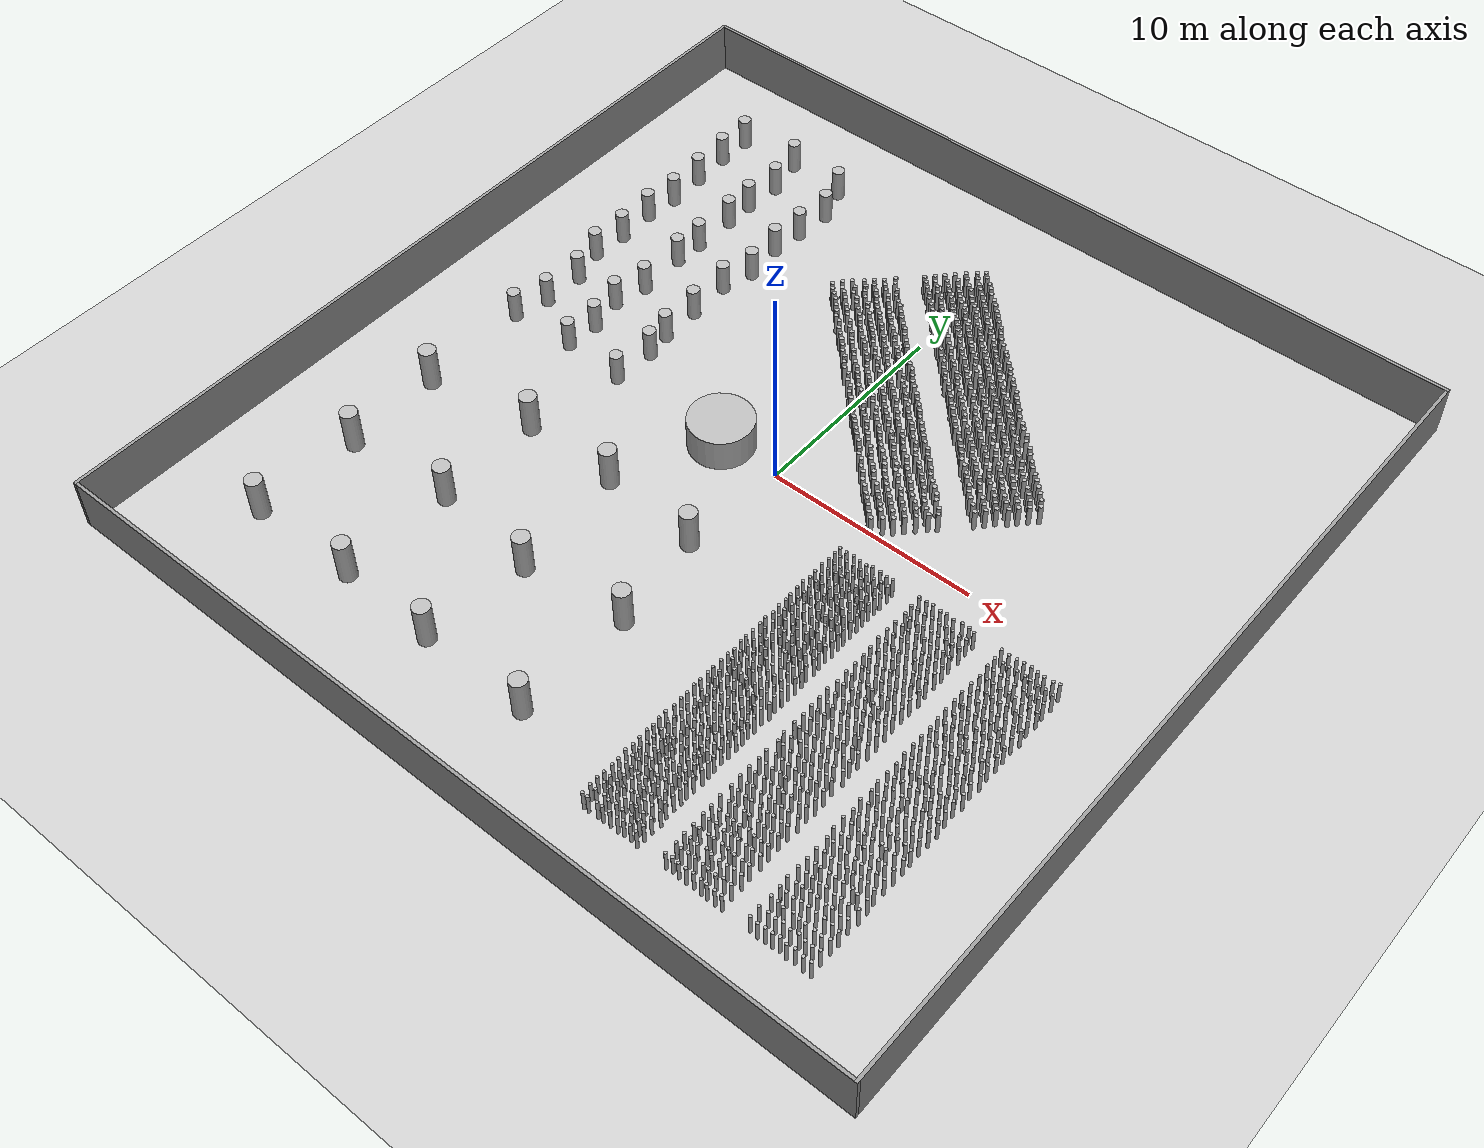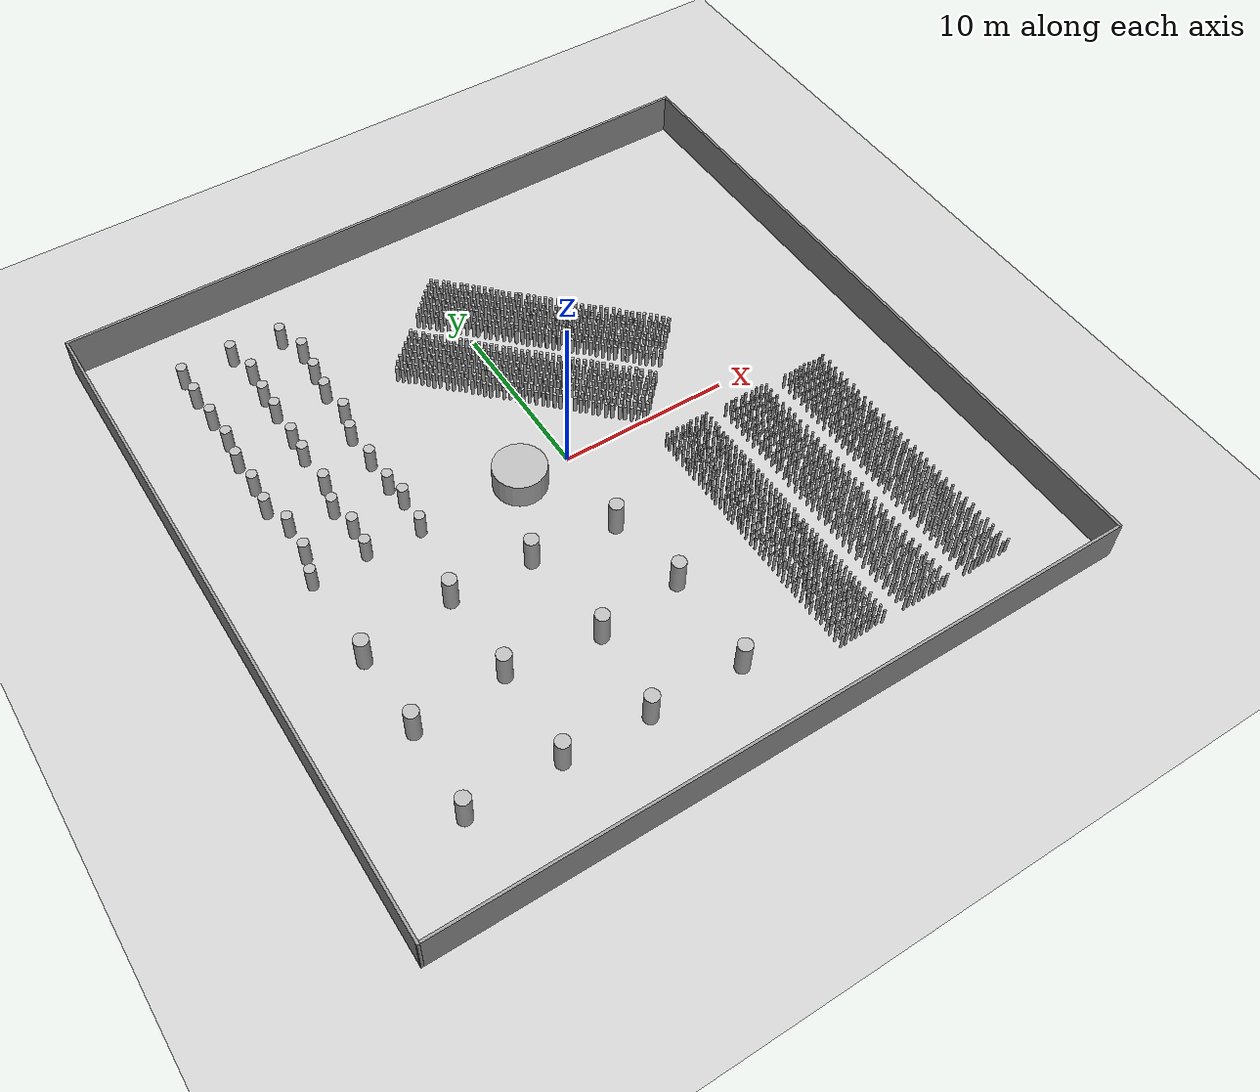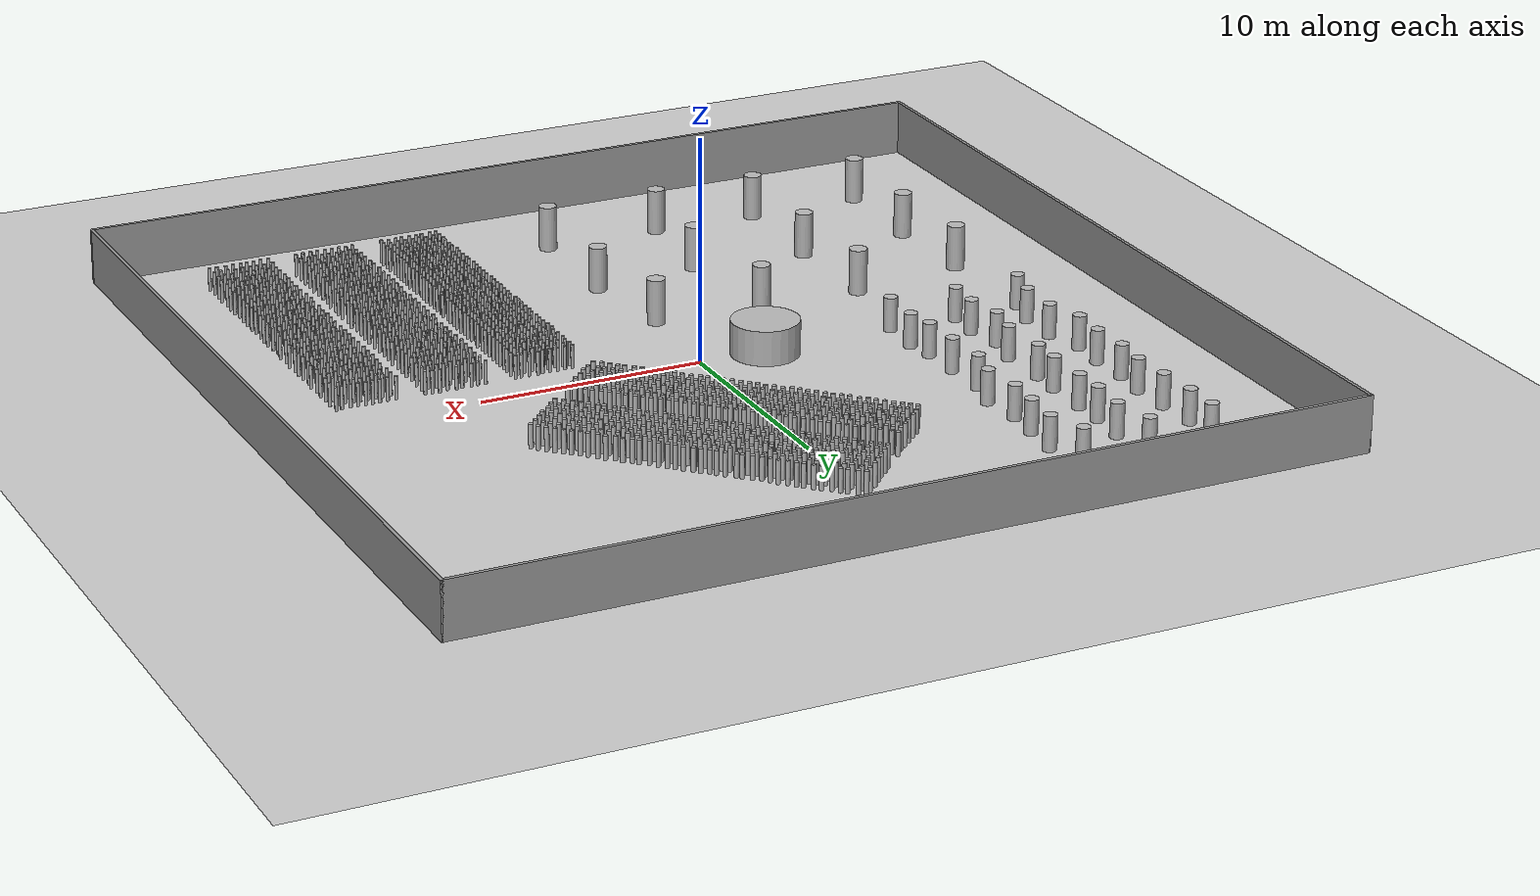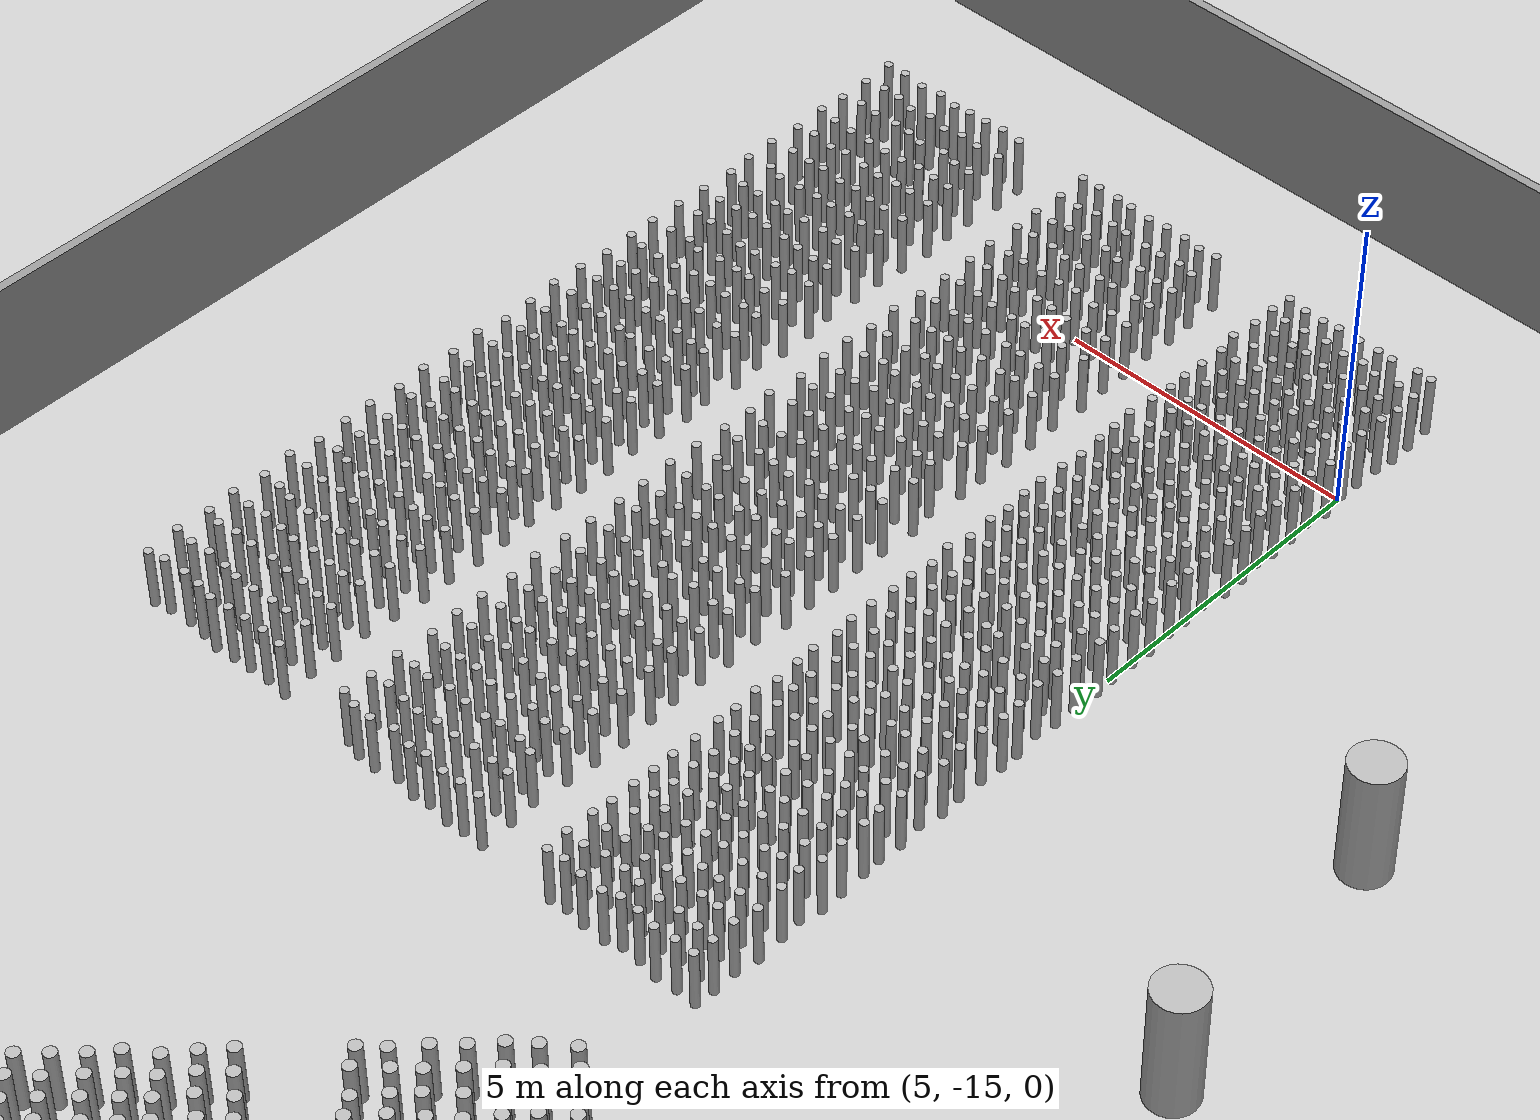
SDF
<sdf version='1.7'>
<world name='farmland_world'>
  <light name='sun' type='directional'>
    <cast_shadows>1</cast_shadows>
    <pose>0 0 10 0 -0 0</pose>
    <diffuse>0.8 0.8 0.8 1</diffuse>
    <specular>0.2 0.2 0.2 1</specular>
    <attenuation>
      <range>1000</range>
      <constant>0.9</constant>
      <linear>0.01</linear>
      <quadratic>0.001</quadratic>
    </attenuation>
    <direction>-0.5 0.1 -0.9</direction>
    <spot>
      <inner_angle>0</inner_angle>
      <outer_angle>0</outer_angle>
      <falloff>0</falloff>
    </spot>
  </light>
  <gravity>0 0 -9.8</gravity>
  <magnetic_field>6e-06 2.3e-05 -4.2e-05</magnetic_field>
  <atmosphere type='adiabatic'/>
  <physics type='ode'>
    <max_step_size>0.001</max_step_size>
    <real_time_factor>1</real_time_factor>
    <real_time_update_rate>1000</real_time_update_rate>
  </physics>
  <scene>
    <ambient>0.4 0.4 0.4 1</ambient>
    <background>0.7 0.7 0.7 1</background>
    <shadows>1</shadows>
  </scene>
  <wind/>
  <spherical_coordinates>
    <surface_model>EARTH_WGS84</surface_model>
    <latitude_deg>0</latitude_deg>
    <longitude_deg>0</longitude_deg>
    <elevation>0</elevation>
    <heading_deg>0</heading_deg>
  </spherical_coordinates>

  <model name='ground_plane'>
    <static>1</static>
    <link name='link'>
      <collision name='collision'>
        <geometry>
          <plane>
            <normal>0 0 1</normal>
            <size>40.0 40.0</size>
          </plane>
        </geometry>
        <surface>
          <friction>
            <ode>
              <mu>100</mu>
              <mu2>50</mu2>
            </ode>
            <torsional>
              <ode/>
            </torsional>
          </friction>
          <contact>
            <ode/>
          </contact>
          <bounce/>
        </surface>
        <max_contacts>10</max_contacts>
      </collision>
      <visual name='visual'>
        <cast_shadows>0</cast_shadows>
        <geometry>
          <plane>
            <normal>0 0 1</normal>
            <size>40.0 40.0</size>
          </plane>
        </geometry>
        <material>
          <script>
            <uri>file://media/materials/scripts/gazebo.material</uri>
            <name>Gazebo/Grey</name>
          </script>
        </material>
      </visual>
      <self_collide>0</self_collide>
      <enable_wind>0</enable_wind>
      <kinematic>0</kinematic>
    </link>
  </model>

  <model name='Walls'>
    <pose>0 0 0 0 -0 0</pose>
    <link name='Wall_0'>
      <collision name='Wall_0_Collision'>
        <geometry>
          <box>
            <size>40.15 0.15 2.5</size>
          </box>
        </geometry>
        <pose>0 0 1.25 0 -0 0</pose>
        <max_contacts>10</max_contacts>
        <surface>
          <contact>
            <ode/>
          </contact>
          <bounce/>
          <friction>
            <torsional>
              <ode/>
            </torsional>
            <ode/>
          </friction>
        </surface>
      </collision>
      <visual name='Wall_0_Visual'>
        <pose>0 0 1.25 0 -0 0</pose>
        <geometry>
          <box>
            <size>40.15 0.15 2.5</size>
          </box>
        </geometry>
        <material>
          <script>
            <uri>file://media/materials/scripts/gazebo.material</uri>
            <name>Gazebo/Grey</name>
          </script>
          <ambient>1 1 1 1</ambient>
        </material>
        <meta>
          <layer>0</layer>
        </meta>
      </visual>
      <pose>-20.0 0 0 0 -0 1.5708</pose>
      <self_collide>0</self_collide>
      <enable_wind>0</enable_wind>
      <kinematic>0</kinematic>
    </link>
    <link name='Wall_1'>
      <collision name='Wall_1_Collision'>
        <geometry>
          <box>
            <size>40.15 0.15 2.5</size>
          </box>
        </geometry>
        <pose>0 0 1.25 0 -0 0</pose>
        <max_contacts>10</max_contacts>
        <surface>
          <contact>
            <ode/>
          </contact>
          <bounce/>
          <friction>
            <torsional>
              <ode/>
            </torsional>
            <ode/>
          </friction>
        </surface>
      </collision>
      <visual name='Wall_1_Visual'>
        <pose>0 0 1.25 0 -0 0</pose>
        <geometry>
          <box>
            <size>40.15 0.15 2.5</size>
          </box>
        </geometry>
        <material>
          <script>
            <uri>file://media/materials/scripts/gazebo.material</uri>
            <name>Gazebo/Grey</name>
          </script>
          <ambient>1 1 1 1</ambient>
        </material>
        <meta>
          <layer>0</layer>
        </meta>
      </visual>
      <pose>0 20.0 0 0 -0 0</pose>
      <self_collide>0</self_collide>
      <enable_wind>0</enable_wind>
      <kinematic>0</kinematic>
    </link>
    <link name='Wall_2'>
      <collision name='Wall_2_Collision'>
        <geometry>
          <box>
            <size>40.15 0.15 2.5</size>
          </box>
        </geometry>
        <pose>0 0 1.25 0 -0 0</pose>
        <max_contacts>10</max_contacts>
        <surface>
          <contact>
            <ode/>
          </contact>
          <bounce/>
          <friction>
            <torsional>
              <ode/>
            </torsional>
            <ode/>
          </friction>
        </surface>
      </collision>
      <visual name='Wall_2_Visual'>
        <pose>0 0 1.25 0 -0 0</pose>
        <geometry>
          <box>
            <size>40.15 0.15 2.5</size>
          </box>
        </geometry>
        <material>
          <script>
            <uri>file://media/materials/scripts/gazebo.material</uri>
            <name>Gazebo/Grey</name>
          </script>
          <ambient>1 1 1 1</ambient>
        </material>
        <meta>
          <layer>0</layer>
        </meta>
      </visual>
      <pose>20.0 0 0 0 -0 -1.5708</pose>
      <self_collide>0</self_collide>
      <enable_wind>0</enable_wind>
      <kinematic>0</kinematic>
    </link>
    <link name='Wall_3'>
      <collision name='Wall_3_Collision'>
        <geometry>
          <box>
            <size>40.15 0.15 2.5</size>
          </box>
        </geometry>
        <pose>0 0 1.25 0 -0 0</pose>
        <max_contacts>10</max_contacts>
        <surface>
          <contact>
            <ode/>
          </contact>
          <bounce/>
          <friction>
            <torsional>
              <ode/>
            </torsional>
            <ode/>
          </friction>
        </surface>
      </collision>
      <visual name='Wall_3_Visual'>
        <pose>0 0 1.25 0 -0 0</pose>
        <geometry>
          <box>
            <size>40.15 0.15 2.5</size>
          </box>
        </geometry>
        <material>
          <script>
            <uri>file://media/materials/scripts/gazebo.material</uri>
            <name>Gazebo/Grey</name>
          </script>
          <ambient>1 1 1 1</ambient>
        </material>
        <meta>
          <layer>0</layer>
        </meta>
      </visual>
      <pose>0 -20.0 0 0 -0 3.14159</pose>
      <self_collide>0</self_collide>
      <enable_wind>0</enable_wind>
      <kinematic>0</kinematic>
    </link>
    <static>1</static>
  </model>

    <model name='tree_0_0'>
        <static>1</static>
        <link name='link'>
        <collision name='collision'>
            <geometry>
                <cylinder>

                <radius>0.3</radius>
                <length>3.0</length>

                </cylinder>
            </geometry>
            <surface>
            <friction>
                <ode>
                <mu>100</mu>
                <mu2>50</mu2>
                </ode>
                <torsional>
                <ode/>
                </torsional>
            </friction>
            <contact>
                <ode/>
            </contact>
            <bounce/>
            </surface>
            <max_contacts>10</max_contacts>
        </collision>
        <visual name='visual'>
            <geometry>
                <cylinder>

                <radius>0.3</radius>
                <length>3.0</length>

                </cylinder>
            </geometry>
        </visual>
        <self_collide>0</self_collide>
        <enable_wind>0</enable_wind>
        <kinematic>0</kinematic>
        </link>
        <pose>-15.188938652736043 15.912597027168243 0 0 0 0 </pose>
    </model>

    <model name='tree_0_1'>
        <static>1</static>
        <link name='link'>
        <collision name='collision'>
            <geometry>
                <cylinder>

                <radius>0.3</radius>
                <length>3.0</length>

                </cylinder>
            </geometry>
            <surface>
            <friction>
                <ode>
                <mu>100</mu>
                <mu2>50</mu2>
                </ode>
                <torsional>
                <ode/>
                </torsional>
            </friction>
            <contact>
                <ode/>
            </contact>
            <bounce/>
            </surface>
            <max_contacts>10</max_contacts>
        </collision>
        <visual name='visual'>
            <geometry>
                <cylinder>

                <radius>0.3</radius>
                <length>3.0</length>

                </cylinder>
            </geometry>
        </visual>
        <self_collide>0</self_collide>
        <enable_wind>0</enable_wind>
        <kinematic>0</kinematic>
        </link>
        <pose>-15.203481922949232 14.246356640369596 0 0 0 0 </pose>
    </model>

    <model name='tree_0_2'>
        <static>1</static>
        <link name='link'>
        <collision name='collision'>
            <geometry>
                <cylinder>

                <radius>0.3</radius>
                <length>3.0</length>

                </cylinder>
            </geometry>
            <surface>
            <friction>
                <ode>
                <mu>100</mu>
                <mu2>50</mu2>
                </ode>
                <torsional>
                <ode/>
                </torsional>
            </friction>
            <contact>
                <ode/>
            </contact>
            <bounce/>
            </surface>
            <max_contacts>10</max_contacts>
        </collision>
        <visual name='visual'>
            <geometry>
                <cylinder>

                <radius>0.3</radius>
                <length>3.0</length>

                </cylinder>
            </geometry>
        </visual>
        <self_collide>0</self_collide>
        <enable_wind>0</enable_wind>
        <kinematic>0</kinematic>
        </link>
        <pose>-15.091736200138948 12.349055719096812 0 0 0 0 </pose>
    </model>

    <model name='tree_0_3'>
        <static>1</static>
        <link name='link'>
        <collision name='collision'>
            <geometry>
                <cylinder>

                <radius>0.3</radius>
                <length>3.0</length>

                </cylinder>
            </geometry>
            <surface>
            <friction>
                <ode>
                <mu>100</mu>
                <mu2>50</mu2>
                </ode>
                <torsional>
                <ode/>
                </torsional>
            </friction>
            <contact>
                <ode/>
            </contact>
            <bounce/>
            </surface>
            <max_contacts>10</max_contacts>
        </collision>
        <visual name='visual'>
            <geometry>
                <cylinder>

                <radius>0.3</radius>
                <length>3.0</length>

                </cylinder>
            </geometry>
        </visual>
        <self_collide>0</self_collide>
        <enable_wind>0</enable_wind>
        <kinematic>0</kinematic>
        </link>
        <pose>-15.0005537468897 10.475004583335092 0 0 0 0 </pose>
    </model>

    <model name='tree_0_4'>
        <static>1</static>
        <link name='link'>
        <collision name='collision'>
            <geometry>
                <cylinder>

                <radius>0.3</radius>
                <length>3.0</length>

                </cylinder>
            </geometry>
            <surface>
            <friction>
                <ode>
                <mu>100</mu>
                <mu2>50</mu2>
                </ode>
                <torsional>
                <ode/>
                </torsional>
            </friction>
            <contact>
                <ode/>
            </contact>
            <bounce/>
            </surface>
            <max_contacts>10</max_contacts>
        </collision>
        <visual name='visual'>
            <geometry>
                <cylinder>

                <radius>0.3</radius>
                <length>3.0</length>

                </cylinder>
            </geometry>
        </visual>
        <self_collide>0</self_collide>
        <enable_wind>0</enable_wind>
        <kinematic>0</kinematic>
        </link>
        <pose>-15.176880996043332 8.868891120534228 0 0 0 0 </pose>
    </model>

    <model name='tree_0_5'>
        <static>1</static>
        <link name='link'>
        <collision name='collision'>
            <geometry>
                <cylinder>

                <radius>0.3</radius>
                <length>3.0</length>

                </cylinder>
            </geometry>
            <surface>
            <friction>
                <ode>
                <mu>100</mu>
                <mu2>50</mu2>
                </ode>
                <torsional>
                <ode/>
                </torsional>
            </friction>
            <contact>
                <ode/>
            </contact>
            <bounce/>
            </surface>
            <max_contacts>10</max_contacts>
        </collision>
        <visual name='visual'>
            <geometry>
                <cylinder>

                <radius>0.3</radius>
                <length>3.0</length>

                </cylinder>
            </geometry>
        </visual>
        <self_collide>0</self_collide>
        <enable_wind>0</enable_wind>
        <kinematic>0</kinematic>
        </link>
        <pose>-15.098781797502422 6.998545656915446 0 0 0 0 </pose>
    </model>

    <model name='tree_0_6'>
        <static>1</static>
        <link name='link'>
        <collision name='collision'>
            <geometry>
                <cylinder>

                <radius>0.3</radius>
                <length>3.0</length>

                </cylinder>
            </geometry>
            <surface>
            <friction>
                <ode>
                <mu>100</mu>
                <mu2>50</mu2>
                </ode>
                <torsional>
                <ode/>
                </torsional>
            </friction>
            <contact>
                <ode/>
            </contact>
            <bounce/>
            </surface>
            <max_contacts>10</max_contacts>
        </collision>
        <visual name='visual'>
            <geometry>
                <cylinder>

                <radius>0.3</radius>
                <length>3.0</length>

                </cylinder>
            </geometry>
        </visual>
        <self_collide>0</self_collide>
        <enable_wind>0</enable_wind>
        <kinematic>0</kinematic>
        </link>
        <pose>-15.219759444484739 5.294043536451725 0 0 0 0 </pose>
    </model>

    <model name='tree_0_7'>
        <static>1</static>
        <link name='link'>
        <collision name='collision'>
            <geometry>
                <cylinder>

                <radius>0.3</radius>
                <length>3.0</length>

                </cylinder>
            </geometry>
            <surface>
            <friction>
                <ode>
                <mu>100</mu>
                <mu2>50</mu2>
                </ode>
                <torsional>
                <ode/>
                </torsional>
            </friction>
            <contact>
                <ode/>
            </contact>
            <bounce/>
            </surface>
            <max_contacts>10</max_contacts>
        </collision>
        <visual name='visual'>
            <geometry>
                <cylinder>

                <radius>0.3</radius>
                <length>3.0</length>

                </cylinder>
            </geometry>
        </visual>
        <self_collide>0</self_collide>
        <enable_wind>0</enable_wind>
        <kinematic>0</kinematic>
        </link>
        <pose>-14.733545784522109 3.598117998389355 0 0 0 0 </pose>
    </model>

    <model name='tree_0_8'>
        <static>1</static>
        <link name='link'>
        <collision name='collision'>
            <geometry>
                <cylinder>

                <radius>0.3</radius>
                <length>3.0</length>

                </cylinder>
            </geometry>
            <surface>
            <friction>
                <ode>
                <mu>100</mu>
                <mu2>50</mu2>
                </ode>
                <torsional>
                <ode/>
                </torsional>
            </friction>
            <contact>
                <ode/>
            </contact>
            <bounce/>
            </surface>
            <max_contacts>10</max_contacts>
        </collision>
        <visual name='visual'>
            <geometry>
                <cylinder>

                <radius>0.3</radius>
                <length>3.0</length>

                </cylinder>
            </geometry>
        </visual>
        <self_collide>0</self_collide>
        <enable_wind>0</enable_wind>
        <kinematic>0</kinematic>
        </link>
        <pose>-14.776917883909997 1.594553188719145 0 0 0 0 </pose>
    </model>

    <model name='tree_0_9'>
        <static>1</static>
        <link name='link'>
        <collision name='collision'>
            <geometry>
                <cylinder>

                <radius>0.3</radius>
                <length>3.0</length>

                </cylinder>
            </geometry>
            <surface>
            <friction>
                <ode>
                <mu>100</mu>
                <mu2>50</mu2>
                </ode>
                <torsional>
                <ode/>
                </torsional>
            </friction>
            <contact>
                <ode/>
            </contact>
            <bounce/>
            </surface>
            <max_contacts>10</max_contacts>
        </collision>
        <visual name='visual'>
            <geometry>
                <cylinder>

                <radius>0.3</radius>
                <length>3.0</length>

                </cylinder>
            </geometry>
        </visual>
        <self_collide>0</self_collide>
        <enable_wind>0</enable_wind>
        <kinematic>0</kinematic>
        </link>
        <pose>-15.20824132696946 -0.01747100562715229 0 0 0 0 </pose>
    </model>

    <model name='tree_0_10'>
        <static>1</static>
        <link name='link'>
        <collision name='collision'>
            <geometry>
                <cylinder>

                <radius>0.3</radius>
                <length>3.0</length>

                </cylinder>
            </geometry>
            <surface>
            <friction>
                <ode>
                <mu>100</mu>
                <mu2>50</mu2>
                </ode>
                <torsional>
                <ode/>
                </torsional>
            </friction>
            <contact>
                <ode/>
            </contact>
            <bounce/>
            </surface>
            <max_contacts>10</max_contacts>
        </collision>
        <visual name='visual'>
            <geometry>
                <cylinder>

                <radius>0.3</radius>
                <length>3.0</length>

                </cylinder>
            </geometry>
        </visual>
        <self_collide>0</self_collide>
        <enable_wind>0</enable_wind>
        <kinematic>0</kinematic>
        </link>
        <pose>-12.198636150211716 16.060505452191354 0 0 0 0 </pose>
    </model>

    <model name='tree_0_11'>
        <static>1</static>
        <link name='link'>
        <collision name='collision'>
            <geometry>
                <cylinder>

                <radius>0.3</radius>
                <length>3.0</length>

                </cylinder>
            </geometry>
            <surface>
            <friction>
                <ode>
                <mu>100</mu>
                <mu2>50</mu2>
                </ode>
                <torsional>
                <ode/>
                </torsional>
            </friction>
            <contact>
                <ode/>
            </contact>
            <bounce/>
            </surface>
            <max_contacts>10</max_contacts>
        </collision>
        <visual name='visual'>
            <geometry>
                <cylinder>

                <radius>0.3</radius>
                <length>3.0</length>

                </cylinder>
            </geometry>
        </visual>
        <self_collide>0</self_collide>
        <enable_wind>0</enable_wind>
        <kinematic>0</kinematic>
        </link>
        <pose>-11.810280494804624 14.18254066707638 0 0 0 0 </pose>
    </model>

    <model name='tree_0_12'>
        <static>1</static>
        <link name='link'>
        <collision name='collision'>
            <geometry>
                <cylinder>

                <radius>0.3</radius>
                <length>3.0</length>

                </cylinder>
            </geometry>
            <surface>
            <friction>
                <ode>
                <mu>100</mu>
                <mu2>50</mu2>
                </ode>
                <torsional>
                <ode/>
                </torsional>
            </friction>
            <contact>
                <ode/>
            </contact>
            <bounce/>
            </surface>
            <max_contacts>10</max_contacts>
        </collision>
        <visual name='visual'>
            <geometry>
                <cylinder>

                <radius>0.3</radius>
                <length>3.0</length>

                </cylinder>
            </geometry>
        </visual>
        <self_collide>0</self_collide>
        <enable_wind>0</enable_wind>
        <kinematic>0</kinematic>
        </link>
        <pose>-11.963897516112725 12.390226497976228 0 0 0 0 </pose>
    </model>

    <model name='tree_0_13'>
        <static>1</static>
        <link name='link'>
        <collision name='collision'>
            <geometry>
                <cylinder>

                <radius>0.3</radius>
                <length>3.0</length>

                </cylinder>
            </geometry>
            <surface>
            <friction>
                <ode>
                <mu>100</mu>
                <mu2>50</mu2>
                </ode>
                <torsional>
                <ode/>
                </torsional>
            </friction>
            <contact>
                <ode/>
            </contact>
            <bounce/>
            </surface>
            <max_contacts>10</max_contacts>
        </collision>
        <visual name='visual'>
            <geometry>
                <cylinder>

                <radius>0.3</radius>
                <length>3.0</length>

                </cylinder>
            </geometry>
        </visual>
        <self_collide>0</self_collide>
        <enable_wind>0</enable_wind>
        <kinematic>0</kinematic>
        </link>
        <pose>-11.947877016899797 10.925969713041379 0 0 0 0 </pose>
    </model>

    <model name='tree_0_14'>
        <static>1</static>
        <link name='link'>
        <collision name='collision'>
            <geometry>
                <cylinder>

                <radius>0.3</radius>
                <length>3.0</length>

                </cylinder>
            </geometry>
            <surface>
            <friction>
                <ode>
                <mu>100</mu>
                <mu2>50</mu2>
                </ode>
                <torsional>
                <ode/>
                </torsional>
            </friction>
            <contact>
                <ode/>
            </contact>
            <bounce/>
            </surface>
            <max_contacts>10</max_contacts>
        </collision>
        <visual name='visual'>
            <geometry>
                <cylinder>

                <radius>0.3</radius>
                <length>3.0</length>

                </cylinder>
            </geometry>
        </visual>
        <self_collide>0</self_collide>
        <enable_wind>0</enable_wind>
        <kinematic>0</kinematic>
        </link>
        <pose>-11.962250807036407 8.816510113504643 0 0 0 0 </pose>
    </model>

    <model name='tree_0_15'>
        <static>1</static>
        <link name='link'>
        <collision name='collision'>
            <geometry>
                <cylinder>

                <radius>0.3</radius>
                <length>3.0</length>

                </cylinder>
            </geometry>
            <surface>
            <friction>
                <ode>
                <mu>100</mu>
                <mu2>50</mu2>
                </ode>
                <torsional>
                <ode/>
                </torsional>
            </friction>
            <contact>
                <ode/>
            </contact>
            <bounce/>
            </surface>
            <max_contacts>10</max_contacts>
        </collision>
        <visual name='visual'>
            <geometry>
                <cylinder>

                <radius>0.3</radius>
                <length>3.0</length>

                </cylinder>
            </geometry>
        </visual>
        <self_collide>0</self_collide>
        <enable_wind>0</enable_wind>
        <kinematic>0</kinematic>
        </link>
        <pose>-12.01371350976454 7.388152698581483 0 0 0 0 </pose>
    </model>

    <model name='tree_0_16'>
        <static>1</static>
        <link name='link'>
        <collision name='collision'>
            <geometry>
                <cylinder>

                <radius>0.3</radius>
                <length>3.0</length>

                </cylinder>
            </geometry>
            <surface>
            <friction>
                <ode>
                <mu>100</mu>
                <mu2>50</mu2>
                </ode>
                <torsional>
                <ode/>
                </torsional>
            </friction>
            <contact>
                <ode/>
            </contact>
            <bounce/>
            </surface>
            <max_contacts>10</max_contacts>
        </collision>
        <visual name='visual'>
            <geometry>
                <cylinder>

                <radius>0.3</radius>
                <length>3.0</length>

                </cylinder>
            </geometry>
        </visual>
        <self_collide>0</self_collide>
        <enable_wind>0</enable_wind>
        <kinematic>0</kinematic>
        </link>
        <pose>-11.930365167949695 5.042977807746157 0 0 0 0 </pose>
    </model>

    <model name='tree_0_17'>
        <static>1</static>
        <link name='link'>
        <collision name='collision'>
            <geometry>
                <cylinder>

                <radius>0.3</radius>
                <length>3.0</length>

                </cylinder>
            </geometry>
            <surface>
            <friction>
                <ode>
                <mu>100</mu>
                <mu2>50</mu2>
                </ode>
                <torsional>
                <ode/>
                </torsional>
            </friction>
            <contact>
                <ode/>
            </contact>
            <bounce/>
            </surface>
            <max_contacts>10</max_contacts>
        </collision>
        <visual name='visual'>
            <geometry>
                <cylinder>

                <radius>0.3</radius>
                <length>3.0</length>

                </cylinder>
            </geometry>
        </visual>
        <self_collide>0</self_collide>
        <enable_wind>0</enable_wind>
        <kinematic>0</kinematic>
        </link>
        <pose>-12.270969702473527 3.4207295712960155 0 0 0 0 </pose>
    </model>

    <model name='tree_0_18'>
        <static>1</static>
        <link name='link'>
        <collision name='collision'>
            <geometry>
                <cylinder>

                <radius>0.3</radius>
                <length>3.0</length>

                </cylinder>
            </geometry>
            <surface>
            <friction>
                <ode>
                <mu>100</mu>
                <mu2>50</mu2>
                </ode>
                <torsional>
                <ode/>
                </torsional>
            </friction>
            <contact>
                <ode/>
            </contact>
            <bounce/>
            </surface>
            <max_contacts>10</max_contacts>
        </collision>
        <visual name='visual'>
            <geometry>
                <cylinder>

                <radius>0.3</radius>
                <length>3.0</length>

                </cylinder>
            </geometry>
        </visual>
        <self_collide>0</self_collide>
        <enable_wind>0</enable_wind>
        <kinematic>0</kinematic>
        </link>
        <pose>-11.960181825543396 1.7453268640379522 0 0 0 0 </pose>
    </model>

    <model name='tree_0_19'>
        <static>1</static>
        <link name='link'>
        <collision name='collision'>
            <geometry>
                <cylinder>

                <radius>0.3</radius>
                <length>3.0</length>

                </cylinder>
            </geometry>
            <surface>
            <friction>
                <ode>
                <mu>100</mu>
                <mu2>50</mu2>
                </ode>
                <torsional>
                <ode/>
                </torsional>
            </friction>
            <contact>
                <ode/>
            </contact>
            <bounce/>
            </surface>
            <max_contacts>10</max_contacts>
        </collision>
        <visual name='visual'>
            <geometry>
                <cylinder>

                <radius>0.3</radius>
                <length>3.0</length>

                </cylinder>
            </geometry>
        </visual>
        <self_collide>0</self_collide>
        <enable_wind>0</enable_wind>
        <kinematic>0</kinematic>
        </link>
        <pose>-12.06162498726729 0.15721724448994134 0 0 0 0 </pose>
    </model>

    <model name='tree_0_20'>
        <static>1</static>
        <link name='link'>
        <collision name='collision'>
            <geometry>
                <cylinder>

                <radius>0.3</radius>
                <length>3.0</length>

                </cylinder>
            </geometry>
            <surface>
            <friction>
                <ode>
                <mu>100</mu>
                <mu2>50</mu2>
                </ode>
                <torsional>
                <ode/>
                </torsional>
            </friction>
            <contact>
                <ode/>
            </contact>
            <bounce/>
            </surface>
            <max_contacts>10</max_contacts>
        </collision>
        <visual name='visual'>
            <geometry>
                <cylinder>

                <radius>0.3</radius>
                <length>3.0</length>

                </cylinder>
            </geometry>
        </visual>
        <self_collide>0</self_collide>
        <enable_wind>0</enable_wind>
        <kinematic>0</kinematic>
        </link>
        <pose>-9.286984200792807 15.807528742943724 0 0 0 0 </pose>
    </model>

    <model name='tree_0_21'>
        <static>1</static>
        <link name='link'>
        <collision name='collision'>
            <geometry>
                <cylinder>

                <radius>0.3</radius>
                <length>3.0</length>

                </cylinder>
            </geometry>
            <surface>
            <friction>
                <ode>
                <mu>100</mu>
                <mu2>50</mu2>
                </ode>
                <torsional>
                <ode/>
                </torsional>
            </friction>
            <contact>
                <ode/>
            </contact>
            <bounce/>
            </surface>
            <max_contacts>10</max_contacts>
        </collision>
        <visual name='visual'>
            <geometry>
                <cylinder>

                <radius>0.3</radius>
                <length>3.0</length>

                </cylinder>
            </geometry>
        </visual>
        <self_collide>0</self_collide>
        <enable_wind>0</enable_wind>
        <kinematic>0</kinematic>
        </link>
        <pose>-8.71895008446544 14.152625368785882 0 0 0 0 </pose>
    </model>

    <model name='tree_0_22'>
        <static>1</static>
        <link name='link'>
        <collision name='collision'>
            <geometry>
                <cylinder>

                <radius>0.3</radius>
                <length>3.0</length>

                </cylinder>
            </geometry>
            <surface>
            <friction>
                <ode>
                <mu>100</mu>
                <mu2>50</mu2>
                </ode>
                <torsional>
                <ode/>
                </torsional>
            </friction>
            <contact>
                <ode/>
            </contact>
            <bounce/>
            </surface>
            <max_contacts>10</max_contacts>
        </collision>
        <visual name='visual'>
            <geometry>
                <cylinder>

                <radius>0.3</radius>
                <length>3.0</length>

                </cylinder>
            </geometry>
        </visual>
        <self_collide>0</self_collide>
        <enable_wind>0</enable_wind>
        <kinematic>0</kinematic>
        </link>
        <pose>-8.868159347672215 12.382050561455772 0 0 0 0 </pose>
    </model>

    <model name='tree_0_23'>
        <static>1</static>
        <link name='link'>
        <collision name='collision'>
            <geometry>
                <cylinder>

                <radius>0.3</radius>
                <length>3.0</length>

                </cylinder>
            </geometry>
            <surface>
            <friction>
                <ode>
                <mu>100</mu>
                <mu2>50</mu2>
                </ode>
                <torsional>
                <ode/>
                </torsional>
            </friction>
            <contact>
                <ode/>
            </contact>
            <bounce/>
            </surface>
            <max_contacts>10</max_contacts>
        </collision>
        <visual name='visual'>
            <geometry>
                <cylinder>

                <radius>0.3</radius>
                <length>3.0</length>

                </cylinder>
            </geometry>
        </visual>
        <self_collide>0</self_collide>
        <enable_wind>0</enable_wind>
        <kinematic>0</kinematic>
        </link>
        <pose>-9.004799411582681 10.782474336634904 0 0 0 0 </pose>
    </model>

    <model name='tree_0_24'>
        <static>1</static>
        <link name='link'>
        <collision name='collision'>
            <geometry>
                <cylinder>

                <radius>0.3</radius>
                <length>3.0</length>

                </cylinder>
            </geometry>
            <surface>
            <friction>
                <ode>
                <mu>100</mu>
                <mu2>50</mu2>
                </ode>
                <torsional>
                <ode/>
                </torsional>
            </friction>
            <contact>
                <ode/>
            </contact>
            <bounce/>
            </surface>
            <max_contacts>10</max_contacts>
        </collision>
        <visual name='visual'>
            <geometry>
                <cylinder>

                <radius>0.3</radius>
                <length>3.0</length>

                </cylinder>
            </geometry>
        </visual>
        <self_collide>0</self_collide>
        <enable_wind>0</enable_wind>
        <kinematic>0</kinematic>
        </link>
        <pose>-8.80205373108638 8.876663077848626 0 0 0 0 </pose>
    </model>

    <model name='tree_0_25'>
        <static>1</static>
        <link name='link'>
        <collision name='collision'>
            <geometry>
                <cylinder>

                <radius>0.3</radius>
                <length>3.0</length>

                </cylinder>
            </geometry>
            <surface>
            <friction>
                <ode>
                <mu>100</mu>
                <mu2>50</mu2>
                </ode>
                <torsional>
                <ode/>
                </torsional>
            </friction>
            <contact>
                <ode/>
            </contact>
            <bounce/>
            </surface>
            <max_contacts>10</max_contacts>
        </collision>
        <visual name='visual'>
            <geometry>
                <cylinder>

                <radius>0.3</radius>
                <length>3.0</length>

                </cylinder>
            </geometry>
        </visual>
        <self_collide>0</self_collide>
        <enable_wind>0</enable_wind>
        <kinematic>0</kinematic>
        </link>
        <pose>-9.207437022644298 7.32094262421926 0 0 0 0 </pose>
    </model>

    <model name='tree_0_26'>
        <static>1</static>
        <link name='link'>
        <collision name='collision'>
            <geometry>
                <cylinder>

                <radius>0.3</radius>
                <length>3.0</length>

                </cylinder>
            </geometry>
            <surface>
            <friction>
                <ode>
                <mu>100</mu>
                <mu2>50</mu2>
                </ode>
                <torsional>
                <ode/>
                </torsional>
            </friction>
            <contact>
                <ode/>
            </contact>
            <bounce/>
            </surface>
            <max_contacts>10</max_contacts>
        </collision>
        <visual name='visual'>
            <geometry>
                <cylinder>

                <radius>0.3</radius>
                <length>3.0</length>

                </cylinder>
            </geometry>
        </visual>
        <self_collide>0</self_collide>
        <enable_wind>0</enable_wind>
        <kinematic>0</kinematic>
        </link>
        <pose>-9.137057454465426 5.2215842788103615 0 0 0 0 </pose>
    </model>

    <model name='tree_0_27'>
        <static>1</static>
        <link name='link'>
        <collision name='collision'>
            <geometry>
                <cylinder>

                <radius>0.3</radius>
                <length>3.0</length>

                </cylinder>
            </geometry>
            <surface>
            <friction>
                <ode>
                <mu>100</mu>
                <mu2>50</mu2>
                </ode>
                <torsional>
                <ode/>
                </torsional>
            </friction>
            <contact>
                <ode/>
            </contact>
            <bounce/>
            </surface>
            <max_contacts>10</max_contacts>
        </collision>
        <visual name='visual'>
            <geometry>
                <cylinder>

                <radius>0.3</radius>
                <length>3.0</length>

                </cylinder>
            </geometry>
        </visual>
        <self_collide>0</self_collide>
        <enable_wind>0</enable_wind>
        <kinematic>0</kinematic>
        </link>
        <pose>-9.101786406746458 3.2916410255700908 0 0 0 0 </pose>
    </model>

    <model name='tree_0_28'>
        <static>1</static>
        <link name='link'>
        <collision name='collision'>
            <geometry>
                <cylinder>

                <radius>0.3</radius>
                <length>3.0</length>

                </cylinder>
            </geometry>
            <surface>
            <friction>
                <ode>
                <mu>100</mu>
                <mu2>50</mu2>
                </ode>
                <torsional>
                <ode/>
                </torsional>
            </friction>
            <contact>
                <ode/>
            </contact>
            <bounce/>
            </surface>
            <max_contacts>10</max_contacts>
        </collision>
        <visual name='visual'>
            <geometry>
                <cylinder>

                <radius>0.3</radius>
                <length>3.0</length>

                </cylinder>
            </geometry>
        </visual>
        <self_collide>0</self_collide>
        <enable_wind>0</enable_wind>
        <kinematic>0</kinematic>
        </link>
        <pose>-8.885857975989145 2.0078663709371467 0 0 0 0 </pose>
    </model>

    <model name='tree_0_29'>
        <static>1</static>
        <link name='link'>
        <collision name='collision'>
            <geometry>
                <cylinder>

                <radius>0.3</radius>
                <length>3.0</length>

                </cylinder>
            </geometry>
            <surface>
            <friction>
                <ode>
                <mu>100</mu>
                <mu2>50</mu2>
                </ode>
                <torsional>
                <ode/>
                </torsional>
            </friction>
            <contact>
                <ode/>
            </contact>
            <bounce/>
            </surface>
            <max_contacts>10</max_contacts>
        </collision>
        <visual name='visual'>
            <geometry>
                <cylinder>

                <radius>0.3</radius>
                <length>3.0</length>

                </cylinder>
            </geometry>
        </visual>
        <self_collide>0</self_collide>
        <enable_wind>0</enable_wind>
        <kinematic>0</kinematic>
        </link>
        <pose>-8.997880628791322 -0.02085265697098013 0 0 0 0 </pose>
    </model>

    <model name='tree_1_0'>
        <static>1</static>
        <link name='link'>
        <collision name='collision'>
            <geometry>
                <cylinder>

                <radius>0.4</radius>
                <length>4.0</length>

                </cylinder>
            </geometry>
            <surface>
            <friction>
                <ode>
                <mu>100</mu>
                <mu2>50</mu2>
                </ode>
                <torsional>
                <ode/>
                </torsional>
            </friction>
            <contact>
                <ode/>
            </contact>
            <bounce/>
            </surface>
            <max_contacts>10</max_contacts>
        </collision>
        <visual name='visual'>
            <geometry>
                <cylinder>

                <radius>0.4</radius>
                <length>4.0</length>

                </cylinder>
            </geometry>
        </visual>
        <self_collide>0</self_collide>
        <enable_wind>0</enable_wind>
        <kinematic>0</kinematic>
        </link>
        <pose>0.2540669946374212 -15.38786394240226 0 0 0 1.5707963267948966 </pose>
    </model>

    <model name='tree_1_1'>
        <static>1</static>
        <link name='link'>
        <collision name='collision'>
            <geometry>
                <cylinder>

                <radius>0.4</radius>
                <length>4.0</length>

                </cylinder>
            </geometry>
            <surface>
            <friction>
                <ode>
                <mu>100</mu>
                <mu2>50</mu2>
                </ode>
                <torsional>
                <ode/>
                </torsional>
            </friction>
            <contact>
                <ode/>
            </contact>
            <bounce/>
            </surface>
            <max_contacts>10</max_contacts>
        </collision>
        <visual name='visual'>
            <geometry>
                <cylinder>

                <radius>0.4</radius>
                <length>4.0</length>

                </cylinder>
            </geometry>
        </visual>
        <self_collide>0</self_collide>
        <enable_wind>0</enable_wind>
        <kinematic>0</kinematic>
        </link>
        <pose>-5.051842792831774 -15.291867667403281 0 0 0 1.5707963267948966 </pose>
    </model>

    <model name='tree_1_2'>
        <static>1</static>
        <link name='link'>
        <collision name='collision'>
            <geometry>
                <cylinder>

                <radius>0.4</radius>
                <length>4.0</length>

                </cylinder>
            </geometry>
            <surface>
            <friction>
                <ode>
                <mu>100</mu>
                <mu2>50</mu2>
                </ode>
                <torsional>
                <ode/>
                </torsional>
            </friction>
            <contact>
                <ode/>
            </contact>
            <bounce/>
            </surface>
            <max_contacts>10</max_contacts>
        </collision>
        <visual name='visual'>
            <geometry>
                <cylinder>

                <radius>0.4</radius>
                <length>4.0</length>

                </cylinder>
            </geometry>
        </visual>
        <self_collide>0</self_collide>
        <enable_wind>0</enable_wind>
        <kinematic>0</kinematic>
        </link>
        <pose>-9.82998977859006 -15.08229638216011 0 0 0 1.5707963267948966 </pose>
    </model>

    <model name='tree_1_3'>
        <static>1</static>
        <link name='link'>
        <collision name='collision'>
            <geometry>
                <cylinder>

                <radius>0.4</radius>
                <length>4.0</length>

                </cylinder>
            </geometry>
            <surface>
            <friction>
                <ode>
                <mu>100</mu>
                <mu2>50</mu2>
                </ode>
                <torsional>
                <ode/>
                </torsional>
            </friction>
            <contact>
                <ode/>
            </contact>
            <bounce/>
            </surface>
            <max_contacts>10</max_contacts>
        </collision>
        <visual name='visual'>
            <geometry>
                <cylinder>

                <radius>0.4</radius>
                <length>4.0</length>

                </cylinder>
            </geometry>
        </visual>
        <self_collide>0</self_collide>
        <enable_wind>0</enable_wind>
        <kinematic>0</kinematic>
        </link>
        <pose>-15.065093844090462 -15.095315168979154 0 0 0 1.5707963267948966 </pose>
    </model>

    <model name='tree_1_4'>
        <static>1</static>
        <link name='link'>
        <collision name='collision'>
            <geometry>
                <cylinder>

                <radius>0.4</radius>
                <length>4.0</length>

                </cylinder>
            </geometry>
            <surface>
            <friction>
                <ode>
                <mu>100</mu>
                <mu2>50</mu2>
                </ode>
                <torsional>
                <ode/>
                </torsional>
            </friction>
            <contact>
                <ode/>
            </contact>
            <bounce/>
            </surface>
            <max_contacts>10</max_contacts>
        </collision>
        <visual name='visual'>
            <geometry>
                <cylinder>

                <radius>0.4</radius>
                <length>4.0</length>

                </cylinder>
            </geometry>
        </visual>
        <self_collide>0</self_collide>
        <enable_wind>0</enable_wind>
        <kinematic>0</kinematic>
        </link>
        <pose>0.3341858291401403 -9.767742681914724 0 0 0 1.5707963267948966 </pose>
    </model>

    <model name='tree_1_5'>
        <static>1</static>
        <link name='link'>
        <collision name='collision'>
            <geometry>
                <cylinder>

                <radius>0.4</radius>
                <length>4.0</length>

                </cylinder>
            </geometry>
            <surface>
            <friction>
                <ode>
                <mu>100</mu>
                <mu2>50</mu2>
                </ode>
                <torsional>
                <ode/>
                </torsional>
            </friction>
            <contact>
                <ode/>
            </contact>
            <bounce/>
            </surface>
            <max_contacts>10</max_contacts>
        </collision>
        <visual name='visual'>
            <geometry>
                <cylinder>

                <radius>0.4</radius>
                <length>4.0</length>

                </cylinder>
            </geometry>
        </visual>
        <self_collide>0</self_collide>
        <enable_wind>0</enable_wind>
        <kinematic>0</kinematic>
        </link>
        <pose>-4.568847083646271 -10.325073099994544 0 0 0 1.5707963267948966 </pose>
    </model>

    <model name='tree_1_6'>
        <static>1</static>
        <link name='link'>
        <collision name='collision'>
            <geometry>
                <cylinder>

                <radius>0.4</radius>
                <length>4.0</length>

                </cylinder>
            </geometry>
            <surface>
            <friction>
                <ode>
                <mu>100</mu>
                <mu2>50</mu2>
                </ode>
                <torsional>
                <ode/>
                </torsional>
            </friction>
            <contact>
                <ode/>
            </contact>
            <bounce/>
            </surface>
            <max_contacts>10</max_contacts>
        </collision>
        <visual name='visual'>
            <geometry>
                <cylinder>

                <radius>0.4</radius>
                <length>4.0</length>

                </cylinder>
            </geometry>
        </visual>
        <self_collide>0</self_collide>
        <enable_wind>0</enable_wind>
        <kinematic>0</kinematic>
        </link>
        <pose>-9.728997222041995 -9.698990593612 0 0 0 1.5707963267948966 </pose>
    </model>

    <model name='tree_1_7'>
        <static>1</static>
        <link name='link'>
        <collision name='collision'>
            <geometry>
                <cylinder>

                <radius>0.4</radius>
                <length>4.0</length>

                </cylinder>
            </geometry>
            <surface>
            <friction>
                <ode>
                <mu>100</mu>
                <mu2>50</mu2>
                </ode>
                <torsional>
                <ode/>
                </torsional>
            </friction>
            <contact>
                <ode/>
            </contact>
            <bounce/>
            </surface>
            <max_contacts>10</max_contacts>
        </collision>
        <visual name='visual'>
            <geometry>
                <cylinder>

                <radius>0.4</radius>
                <length>4.0</length>

                </cylinder>
            </geometry>
        </visual>
        <self_collide>0</self_collide>
        <enable_wind>0</enable_wind>
        <kinematic>0</kinematic>
        </link>
        <pose>-14.920578026793763 -10.0460575825015 0 0 0 1.5707963267948966 </pose>
    </model>

    <model name='tree_1_8'>
        <static>1</static>
        <link name='link'>
        <collision name='collision'>
            <geometry>
                <cylinder>

                <radius>0.4</radius>
                <length>4.0</length>

                </cylinder>
            </geometry>
            <surface>
            <friction>
                <ode>
                <mu>100</mu>
                <mu2>50</mu2>
                </ode>
                <torsional>
                <ode/>
                </torsional>
            </friction>
            <contact>
                <ode/>
            </contact>
            <bounce/>
            </surface>
            <max_contacts>10</max_contacts>
        </collision>
        <visual name='visual'>
            <geometry>
                <cylinder>

                <radius>0.4</radius>
                <length>4.0</length>

                </cylinder>
            </geometry>
        </visual>
        <self_collide>0</self_collide>
        <enable_wind>0</enable_wind>
        <kinematic>0</kinematic>
        </link>
        <pose>-0.3144932957957587 -5.122929289410163 0 0 0 1.5707963267948966 </pose>
    </model>

    <model name='tree_1_9'>
        <static>1</static>
        <link name='link'>
        <collision name='collision'>
            <geometry>
                <cylinder>

                <radius>0.4</radius>
                <length>4.0</length>

                </cylinder>
            </geometry>
            <surface>
            <friction>
                <ode>
                <mu>100</mu>
                <mu2>50</mu2>
                </ode>
                <torsional>
                <ode/>
                </torsional>
            </friction>
            <contact>
                <ode/>
            </contact>
            <bounce/>
            </surface>
            <max_contacts>10</max_contacts>
        </collision>
        <visual name='visual'>
            <geometry>
                <cylinder>

                <radius>0.4</radius>
                <length>4.0</length>

                </cylinder>
            </geometry>
        </visual>
        <self_collide>0</self_collide>
        <enable_wind>0</enable_wind>
        <kinematic>0</kinematic>
        </link>
        <pose>-5.135497637638166 -4.682200219394235 0 0 0 1.5707963267948966 </pose>
    </model>

    <model name='tree_1_10'>
        <static>1</static>
        <link name='link'>
        <collision name='collision'>
            <geometry>
                <cylinder>

                <radius>0.4</radius>
                <length>4.0</length>

                </cylinder>
            </geometry>
            <surface>
            <friction>
                <ode>
                <mu>100</mu>
                <mu2>50</mu2>
                </ode>
                <torsional>
                <ode/>
                </torsional>
            </friction>
            <contact>
                <ode/>
            </contact>
            <bounce/>
            </surface>
            <max_contacts>10</max_contacts>
        </collision>
        <visual name='visual'>
            <geometry>
                <cylinder>

                <radius>0.4</radius>
                <length>4.0</length>

                </cylinder>
            </geometry>
        </visual>
        <self_collide>0</self_collide>
        <enable_wind>0</enable_wind>
        <kinematic>0</kinematic>
        </link>
        <pose>-9.802835628621317 -4.581949401209085 0 0 0 1.5707963267948966 </pose>
    </model>

    <model name='tree_1_11'>
        <static>1</static>
        <link name='link'>
        <collision name='collision'>
            <geometry>
                <cylinder>

                <radius>0.4</radius>
                <length>4.0</length>

                </cylinder>
            </geometry>
            <surface>
            <friction>
                <ode>
                <mu>100</mu>
                <mu2>50</mu2>
                </ode>
                <torsional>
                <ode/>
                </torsional>
            </friction>
            <contact>
                <ode/>
            </contact>
            <bounce/>
            </surface>
            <max_contacts>10</max_contacts>
        </collision>
        <visual name='visual'>
            <geometry>
                <cylinder>

                <radius>0.4</radius>
                <length>4.0</length>

                </cylinder>
            </geometry>
        </visual>
        <self_collide>0</self_collide>
        <enable_wind>0</enable_wind>
        <kinematic>0</kinematic>
        </link>
        <pose>-15.086728282497244 -5.36786975470952 0 0 0 1.5707963267948966 </pose>
    </model>

    <model name='tree_2_0'>
        <static>1</static>
        <link name='link'>
        <collision name='collision'>
            <geometry>
                <cylinder>

                <radius>0.1</radius>
                <length>2.0</length>

                </cylinder>
            </geometry>
            <surface>
            <friction>
                <ode>
                <mu>100</mu>
                <mu2>50</mu2>
                </ode>
                <torsional>
                <ode/>
                </torsional>
            </friction>
            <contact>
                <ode/>
            </contact>
            <bounce/>
            </surface>
            <max_contacts>10</max_contacts>
        </collision>
        <visual name='visual'>
            <geometry>
                <cylinder>

                <radius>0.1</radius>
                <length>2.0</length>

                </cylinder>
            </geometry>
        </visual>
        <self_collide>0</self_collide>
        <enable_wind>0</enable_wind>
        <kinematic>0</kinematic>
        </link>
        <pose>4.976957847610511 0.04888862747025713 0 0 0 0 </pose>
    </model>

    <model name='tree_2_1'>
        <static>1</static>
        <link name='link'>
        <collision name='collision'>
            <geometry>
                <cylinder>

                <radius>0.1</radius>
                <length>2.0</length>

                </cylinder>
            </geometry>
            <surface>
            <friction>
                <ode>
                <mu>100</mu>
                <mu2>50</mu2>
                </ode>
                <torsional>
                <ode/>
                </torsional>
            </friction>
            <contact>
                <ode/>
            </contact>
            <bounce/>
            </surface>
            <max_contacts>10</max_contacts>
        </collision>
        <visual name='visual'>
            <geometry>
                <cylinder>

                <radius>0.1</radius>
                <length>2.0</length>

                </cylinder>
            </geometry>
        </visual>
        <self_collide>0</self_collide>
        <enable_wind>0</enable_wind>
        <kinematic>0</kinematic>
        </link>
        <pose>4.706252705174817 0.2683354104112432 0 0 0 0 </pose>
    </model>

    <model name='tree_2_2'>
        <static>1</static>
        <link name='link'>
        <collision name='collision'>
            <geometry>
                <cylinder>

                <radius>0.1</radius>
                <length>2.0</length>

                </cylinder>
            </geometry>
            <surface>
            <friction>
                <ode>
                <mu>100</mu>
                <mu2>50</mu2>
                </ode>
                <torsional>
                <ode/>
                </torsional>
            </friction>
            <contact>
                <ode/>
            </contact>
            <bounce/>
            </surface>
            <max_contacts>10</max_contacts>
        </collision>
        <visual name='visual'>
            <geometry>
                <cylinder>

                <radius>0.1</radius>
                <length>2.0</length>

                </cylinder>
            </geometry>
        </visual>
        <self_collide>0</self_collide>
        <enable_wind>0</enable_wind>
        <kinematic>0</kinematic>
        </link>
        <pose>4.45766262006263 0.536296449148718 0 0 0 0 </pose>
    </model>

    <model name='tree_2_3'>
        <static>1</static>
        <link name='link'>
        <collision name='collision'>
            <geometry>
                <cylinder>

                <radius>0.1</radius>
                <length>2.0</length>

                </cylinder>
            </geometry>
            <surface>
            <friction>
                <ode>
                <mu>100</mu>
                <mu2>50</mu2>
                </ode>
                <torsional>
                <ode/>
                </torsional>
            </friction>
            <contact>
                <ode/>
            </contact>
            <bounce/>
            </surface>
            <max_contacts>10</max_contacts>
        </collision>
        <visual name='visual'>
            <geometry>
                <cylinder>

                <radius>0.1</radius>
                <length>2.0</length>

                </cylinder>
            </geometry>
        </visual>
        <self_collide>0</self_collide>
        <enable_wind>0</enable_wind>
        <kinematic>0</kinematic>
        </link>
        <pose>4.201781276606337 0.8032155601439471 0 0 0 0 </pose>
    </model>

    <model name='tree_2_4'>
        <static>1</static>
        <link name='link'>
        <collision name='collision'>
            <geometry>
                <cylinder>

                <radius>0.1</radius>
                <length>2.0</length>

                </cylinder>
            </geometry>
            <surface>
            <friction>
                <ode>
                <mu>100</mu>
                <mu2>50</mu2>
                </ode>
                <torsional>
                <ode/>
                </torsional>
            </friction>
            <contact>
                <ode/>
            </contact>
            <bounce/>
            </surface>
            <max_contacts>10</max_contacts>
        </collision>
        <visual name='visual'>
            <geometry>
                <cylinder>

                <radius>0.1</radius>
                <length>2.0</length>

                </cylinder>
            </geometry>
        </visual>
        <self_collide>0</self_collide>
        <enable_wind>0</enable_wind>
        <kinematic>0</kinematic>
        </link>
        <pose>3.992708370073716 0.9891476226442468 0 0 0 0 </pose>
    </model>

    <model name='tree_2_5'>
        <static>1</static>
        <link name='link'>
        <collision name='collision'>
            <geometry>
                <cylinder>

                <radius>0.1</radius>
                <length>2.0</length>

                </cylinder>
            </geometry>
            <surface>
            <friction>
                <ode>
                <mu>100</mu>
                <mu2>50</mu2>
                </ode>
                <torsional>
                <ode/>
                </torsional>
            </friction>
            <contact>
                <ode/>
            </contact>
            <bounce/>
            </surface>
            <max_contacts>10</max_contacts>
        </collision>
        <visual name='visual'>
            <geometry>
                <cylinder>

                <radius>0.1</radius>
                <length>2.0</length>

                </cylinder>
            </geometry>
        </visual>
        <self_collide>0</self_collide>
        <enable_wind>0</enable_wind>
        <kinematic>0</kinematic>
        </link>
        <pose>3.684042560008494 1.2877914144100004 0 0 0 0 </pose>
    </model>

    <model name='tree_2_6'>
        <static>1</static>
        <link name='link'>
        <collision name='collision'>
            <geometry>
                <cylinder>

                <radius>0.1</radius>
                <length>2.0</length>

                </cylinder>
            </geometry>
            <surface>
            <friction>
                <ode>
                <mu>100</mu>
                <mu2>50</mu2>
                </ode>
                <torsional>
                <ode/>
                </torsional>
            </friction>
            <contact>
                <ode/>
            </contact>
            <bounce/>
            </surface>
            <max_contacts>10</max_contacts>
        </collision>
        <visual name='visual'>
            <geometry>
                <cylinder>

                <radius>0.1</radius>
                <length>2.0</length>

                </cylinder>
            </geometry>
        </visual>
        <self_collide>0</self_collide>
        <enable_wind>0</enable_wind>
        <kinematic>0</kinematic>
        </link>
        <pose>3.425048770062805 1.5071883874941905 0 0 0 0 </pose>
    </model>

    <model name='tree_2_7'>
        <static>1</static>
        <link name='link'>
        <collision name='collision'>
            <geometry>
                <cylinder>

                <radius>0.1</radius>
                <length>2.0</length>

                </cylinder>
            </geometry>
            <surface>
            <friction>
                <ode>
                <mu>100</mu>
                <mu2>50</mu2>
                </ode>
                <torsional>
                <ode/>
                </torsional>
            </friction>
            <contact>
                <ode/>
            </contact>
            <bounce/>
            </surface>
            <max_contacts>10</max_contacts>
        </collision>
        <visual name='visual'>
            <geometry>
                <cylinder>

                <radius>0.1</radius>
                <length>2.0</length>

                </cylinder>
            </geometry>
        </visual>
        <self_collide>0</self_collide>
        <enable_wind>0</enable_wind>
        <kinematic>0</kinematic>
        </link>
        <pose>3.161737783501504 1.8413934828017933 0 0 0 0 </pose>
    </model>

    <model name='tree_2_8'>
        <static>1</static>
        <link name='link'>
        <collision name='collision'>
            <geometry>
                <cylinder>

                <radius>0.1</radius>
                <length>2.0</length>

                </cylinder>
            </geometry>
            <surface>
            <friction>
                <ode>
                <mu>100</mu>
                <mu2>50</mu2>
                </ode>
                <torsional>
                <ode/>
                </torsional>
            </friction>
            <contact>
                <ode/>
            </contact>
            <bounce/>
            </surface>
            <max_contacts>10</max_contacts>
        </collision>
        <visual name='visual'>
            <geometry>
                <cylinder>

                <radius>0.1</radius>
                <length>2.0</length>

                </cylinder>
            </geometry>
        </visual>
        <self_collide>0</self_collide>
        <enable_wind>0</enable_wind>
        <kinematic>0</kinematic>
        </link>
        <pose>2.917203898128225 2.033131867534686 0 0 0 0 </pose>
    </model>

    <model name='tree_2_9'>
        <static>1</static>
        <link name='link'>
        <collision name='collision'>
            <geometry>
                <cylinder>

                <radius>0.1</radius>
                <length>2.0</length>

                </cylinder>
            </geometry>
            <surface>
            <friction>
                <ode>
                <mu>100</mu>
                <mu2>50</mu2>
                </ode>
                <torsional>
                <ode/>
                </torsional>
            </friction>
            <contact>
                <ode/>
            </contact>
            <bounce/>
            </surface>
            <max_contacts>10</max_contacts>
        </collision>
        <visual name='visual'>
            <geometry>
                <cylinder>

                <radius>0.1</radius>
                <length>2.0</length>

                </cylinder>
            </geometry>
        </visual>
        <self_collide>0</self_collide>
        <enable_wind>0</enable_wind>
        <kinematic>0</kinematic>
        </link>
        <pose>2.676242726169039 2.356269617772251 0 0 0 0 </pose>
    </model>

    <model name='tree_2_10'>
        <static>1</static>
        <link name='link'>
        <collision name='collision'>
            <geometry>
                <cylinder>

                <radius>0.1</radius>
                <length>2.0</length>

                </cylinder>
            </geometry>
            <surface>
            <friction>
                <ode>
                <mu>100</mu>
                <mu2>50</mu2>
                </ode>
                <torsional>
                <ode/>
                </torsional>
            </friction>
            <contact>
                <ode/>
            </contact>
            <bounce/>
            </surface>
            <max_contacts>10</max_contacts>
        </collision>
        <visual name='visual'>
            <geometry>
                <cylinder>

                <radius>0.1</radius>
                <length>2.0</length>

                </cylinder>
            </geometry>
        </visual>
        <self_collide>0</self_collide>
        <enable_wind>0</enable_wind>
        <kinematic>0</kinematic>
        </link>
        <pose>2.417781165990284 2.5203616601932897 0 0 0 0 </pose>
    </model>

    <model name='tree_2_11'>
        <static>1</static>
        <link name='link'>
        <collision name='collision'>
            <geometry>
                <cylinder>

                <radius>0.1</radius>
                <length>2.0</length>

                </cylinder>
            </geometry>
            <surface>
            <friction>
                <ode>
                <mu>100</mu>
                <mu2>50</mu2>
                </ode>
                <torsional>
                <ode/>
                </torsional>
            </friction>
            <contact>
                <ode/>
            </contact>
            <bounce/>
            </surface>
            <max_contacts>10</max_contacts>
        </collision>
        <visual name='visual'>
            <geometry>
                <cylinder>

                <radius>0.1</radius>
                <length>2.0</length>

                </cylinder>
            </geometry>
        </visual>
        <self_collide>0</self_collide>
        <enable_wind>0</enable_wind>
        <kinematic>0</kinematic>
        </link>
        <pose>2.227122065708513 2.805358502563454 0 0 0 0 </pose>
    </model>

    <model name='tree_2_12'>
        <static>1</static>
        <link name='link'>
        <collision name='collision'>
            <geometry>
                <cylinder>

                <radius>0.1</radius>
                <length>2.0</length>

                </cylinder>
            </geometry>
            <surface>
            <friction>
                <ode>
                <mu>100</mu>
                <mu2>50</mu2>
                </ode>
                <torsional>
                <ode/>
                </torsional>
            </friction>
            <contact>
                <ode/>
            </contact>
            <bounce/>
            </surface>
            <max_contacts>10</max_contacts>
        </collision>
        <visual name='visual'>
            <geometry>
                <cylinder>

                <radius>0.1</radius>
                <length>2.0</length>

                </cylinder>
            </geometry>
        </visual>
        <self_collide>0</self_collide>
        <enable_wind>0</enable_wind>
        <kinematic>0</kinematic>
        </link>
        <pose>1.944047466811735 3.126044727588416 0 0 0 0 </pose>
    </model>

    <model name='tree_2_13'>
        <static>1</static>
        <link name='link'>
        <collision name='collision'>
            <geometry>
                <cylinder>

                <radius>0.1</radius>
                <length>2.0</length>

                </cylinder>
            </geometry>
            <surface>
            <friction>
                <ode>
                <mu>100</mu>
                <mu2>50</mu2>
                </ode>
                <torsional>
                <ode/>
                </torsional>
            </friction>
            <contact>
                <ode/>
            </contact>
            <bounce/>
            </surface>
            <max_contacts>10</max_contacts>
        </collision>
        <visual name='visual'>
            <geometry>
                <cylinder>

                <radius>0.1</radius>
                <length>2.0</length>

                </cylinder>
            </geometry>
        </visual>
        <self_collide>0</self_collide>
        <enable_wind>0</enable_wind>
        <kinematic>0</kinematic>
        </link>
        <pose>1.6381334577110749 3.3676289560285784 0 0 0 0 </pose>
    </model>

    <model name='tree_2_14'>
        <static>1</static>
        <link name='link'>
        <collision name='collision'>
            <geometry>
                <cylinder>

                <radius>0.1</radius>
                <length>2.0</length>

                </cylinder>
            </geometry>
            <surface>
            <friction>
                <ode>
                <mu>100</mu>
                <mu2>50</mu2>
                </ode>
                <torsional>
                <ode/>
                </torsional>
            </friction>
            <contact>
                <ode/>
            </contact>
            <bounce/>
            </surface>
            <max_contacts>10</max_contacts>
        </collision>
        <visual name='visual'>
            <geometry>
                <cylinder>

                <radius>0.1</radius>
                <length>2.0</length>

                </cylinder>
            </geometry>
        </visual>
        <self_collide>0</self_collide>
        <enable_wind>0</enable_wind>
        <kinematic>0</kinematic>
        </link>
        <pose>1.4170408915636132 3.603359593123357 0 0 0 0 </pose>
    </model>

    <model name='tree_2_15'>
        <static>1</static>
        <link name='link'>
        <collision name='collision'>
            <geometry>
                <cylinder>

                <radius>0.1</radius>
                <length>2.0</length>

                </cylinder>
            </geometry>
            <surface>
            <friction>
                <ode>
                <mu>100</mu>
                <mu2>50</mu2>
                </ode>
                <torsional>
                <ode/>
                </torsional>
            </friction>
            <contact>
                <ode/>
            </contact>
            <bounce/>
            </surface>
            <max_contacts>10</max_contacts>
        </collision>
        <visual name='visual'>
            <geometry>
                <cylinder>

                <radius>0.1</radius>
                <length>2.0</length>

                </cylinder>
            </geometry>
        </visual>
        <self_collide>0</self_collide>
        <enable_wind>0</enable_wind>
        <kinematic>0</kinematic>
        </link>
        <pose>1.1437894201946341 3.866425546577624 0 0 0 0 </pose>
    </model>

    <model name='tree_2_16'>
        <static>1</static>
        <link name='link'>
        <collision name='collision'>
            <geometry>
                <cylinder>

                <radius>0.1</radius>
                <length>2.0</length>

                </cylinder>
            </geometry>
            <surface>
            <friction>
                <ode>
                <mu>100</mu>
                <mu2>50</mu2>
                </ode>
                <torsional>
                <ode/>
                </torsional>
            </friction>
            <contact>
                <ode/>
            </contact>
            <bounce/>
            </surface>
            <max_contacts>10</max_contacts>
        </collision>
        <visual name='visual'>
            <geometry>
                <cylinder>

                <radius>0.1</radius>
                <length>2.0</length>

                </cylinder>
            </geometry>
        </visual>
        <self_collide>0</self_collide>
        <enable_wind>0</enable_wind>
        <kinematic>0</kinematic>
        </link>
        <pose>0.9465068981915904 4.055153674803871 0 0 0 0 </pose>
    </model>

    <model name='tree_2_17'>
        <static>1</static>
        <link name='link'>
        <collision name='collision'>
            <geometry>
                <cylinder>

                <radius>0.1</radius>
                <length>2.0</length>

                </cylinder>
            </geometry>
            <surface>
            <friction>
                <ode>
                <mu>100</mu>
                <mu2>50</mu2>
                </ode>
                <torsional>
                <ode/>
                </torsional>
            </friction>
            <contact>
                <ode/>
            </contact>
            <bounce/>
            </surface>
            <max_contacts>10</max_contacts>
        </collision>
        <visual name='visual'>
            <geometry>
                <cylinder>

                <radius>0.1</radius>
                <length>2.0</length>

                </cylinder>
            </geometry>
        </visual>
        <self_collide>0</self_collide>
        <enable_wind>0</enable_wind>
        <kinematic>0</kinematic>
        </link>
        <pose>0.6570510722266327 4.319523662872599 0 0 0 0 </pose>
    </model>

    <model name='tree_2_18'>
        <static>1</static>
        <link name='link'>
        <collision name='collision'>
            <geometry>
                <cylinder>

                <radius>0.1</radius>
                <length>2.0</length>

                </cylinder>
            </geometry>
            <surface>
            <friction>
                <ode>
                <mu>100</mu>
                <mu2>50</mu2>
                </ode>
                <torsional>
                <ode/>
                </torsional>
            </friction>
            <contact>
                <ode/>
            </contact>
            <bounce/>
            </surface>
            <max_contacts>10</max_contacts>
        </collision>
        <visual name='visual'>
            <geometry>
                <cylinder>

                <radius>0.1</radius>
                <length>2.0</length>

                </cylinder>
            </geometry>
        </visual>
        <self_collide>0</self_collide>
        <enable_wind>0</enable_wind>
        <kinematic>0</kinematic>
        </link>
        <pose>0.41248532989156667 4.628214579799276 0 0 0 0 </pose>
    </model>

    <model name='tree_2_19'>
        <static>1</static>
        <link name='link'>
        <collision name='collision'>
            <geometry>
                <cylinder>

                <radius>0.1</radius>
                <length>2.0</length>

                </cylinder>
            </geometry>
            <surface>
            <friction>
                <ode>
                <mu>100</mu>
                <mu2>50</mu2>
                </ode>
                <torsional>
                <ode/>
                </torsional>
            </friction>
            <contact>
                <ode/>
            </contact>
            <bounce/>
            </surface>
            <max_contacts>10</max_contacts>
        </collision>
        <visual name='visual'>
            <geometry>
                <cylinder>

                <radius>0.1</radius>
                <length>2.0</length>

                </cylinder>
            </geometry>
        </visual>
        <self_collide>0</self_collide>
        <enable_wind>0</enable_wind>
        <kinematic>0</kinematic>
        </link>
        <pose>0.13587846698039704 4.872984788598255 0 0 0 0 </pose>
    </model>

    <model name='tree_2_20'>
        <static>1</static>
        <link name='link'>
        <collision name='collision'>
            <geometry>
                <cylinder>

                <radius>0.1</radius>
                <length>2.0</length>

                </cylinder>
            </geometry>
            <surface>
            <friction>
                <ode>
                <mu>100</mu>
                <mu2>50</mu2>
                </ode>
                <torsional>
                <ode/>
                </torsional>
            </friction>
            <contact>
                <ode/>
            </contact>
            <bounce/>
            </surface>
            <max_contacts>10</max_contacts>
        </collision>
        <visual name='visual'>
            <geometry>
                <cylinder>

                <radius>0.1</radius>
                <length>2.0</length>

                </cylinder>
            </geometry>
        </visual>
        <self_collide>0</self_collide>
        <enable_wind>0</enable_wind>
        <kinematic>0</kinematic>
        </link>
        <pose>-0.13115612335666182 5.098844707070619 0 0 0 0 </pose>
    </model>

    <model name='tree_2_21'>
        <static>1</static>
        <link name='link'>
        <collision name='collision'>
            <geometry>
                <cylinder>

                <radius>0.1</radius>
                <length>2.0</length>

                </cylinder>
            </geometry>
            <surface>
            <friction>
                <ode>
                <mu>100</mu>
                <mu2>50</mu2>
                </ode>
                <torsional>
                <ode/>
                </torsional>
            </friction>
            <contact>
                <ode/>
            </contact>
            <bounce/>
            </surface>
            <max_contacts>10</max_contacts>
        </collision>
        <visual name='visual'>
            <geometry>
                <cylinder>

                <radius>0.1</radius>
                <length>2.0</length>

                </cylinder>
            </geometry>
        </visual>
        <self_collide>0</self_collide>
        <enable_wind>0</enable_wind>
        <kinematic>0</kinematic>
        </link>
        <pose>-0.3380930768440633 5.413363845217107 0 0 0 0 </pose>
    </model>

    <model name='tree_2_22'>
        <static>1</static>
        <link name='link'>
        <collision name='collision'>
            <geometry>
                <cylinder>

                <radius>0.1</radius>
                <length>2.0</length>

                </cylinder>
            </geometry>
            <surface>
            <friction>
                <ode>
                <mu>100</mu>
                <mu2>50</mu2>
                </ode>
                <torsional>
                <ode/>
                </torsional>
            </friction>
            <contact>
                <ode/>
            </contact>
            <bounce/>
            </surface>
            <max_contacts>10</max_contacts>
        </collision>
        <visual name='visual'>
            <geometry>
                <cylinder>

                <radius>0.1</radius>
                <length>2.0</length>

                </cylinder>
            </geometry>
        </visual>
        <self_collide>0</self_collide>
        <enable_wind>0</enable_wind>
        <kinematic>0</kinematic>
        </link>
        <pose>-0.6308501948283547 5.613641408759859 0 0 0 0 </pose>
    </model>

    <model name='tree_2_23'>
        <static>1</static>
        <link name='link'>
        <collision name='collision'>
            <geometry>
                <cylinder>

                <radius>0.1</radius>
                <length>2.0</length>

                </cylinder>
            </geometry>
            <surface>
            <friction>
                <ode>
                <mu>100</mu>
                <mu2>50</mu2>
                </ode>
                <torsional>
                <ode/>
                </torsional>
            </friction>
            <contact>
                <ode/>
            </contact>
            <bounce/>
            </surface>
            <max_contacts>10</max_contacts>
        </collision>
        <visual name='visual'>
            <geometry>
                <cylinder>

                <radius>0.1</radius>
                <length>2.0</length>

                </cylinder>
            </geometry>
        </visual>
        <self_collide>0</self_collide>
        <enable_wind>0</enable_wind>
        <kinematic>0</kinematic>
        </link>
        <pose>-0.8606125800667233 5.940997844809474 0 0 0 0 </pose>
    </model>

    <model name='tree_2_24'>
        <static>1</static>
        <link name='link'>
        <collision name='collision'>
            <geometry>
                <cylinder>

                <radius>0.1</radius>
                <length>2.0</length>

                </cylinder>
            </geometry>
            <surface>
            <friction>
                <ode>
                <mu>100</mu>
                <mu2>50</mu2>
                </ode>
                <torsional>
                <ode/>
                </torsional>
            </friction>
            <contact>
                <ode/>
            </contact>
            <bounce/>
            </surface>
            <max_contacts>10</max_contacts>
        </collision>
        <visual name='visual'>
            <geometry>
                <cylinder>

                <radius>0.1</radius>
                <length>2.0</length>

                </cylinder>
            </geometry>
        </visual>
        <self_collide>0</self_collide>
        <enable_wind>0</enable_wind>
        <kinematic>0</kinematic>
        </link>
        <pose>-1.1990766277143885 6.117519542541731 0 0 0 0 </pose>
    </model>

    <model name='tree_2_25'>
        <static>1</static>
        <link name='link'>
        <collision name='collision'>
            <geometry>
                <cylinder>

                <radius>0.1</radius>
                <length>2.0</length>

                </cylinder>
            </geometry>
            <surface>
            <friction>
                <ode>
                <mu>100</mu>
                <mu2>50</mu2>
                </ode>
                <torsional>
                <ode/>
                </torsional>
            </friction>
            <contact>
                <ode/>
            </contact>
            <bounce/>
            </surface>
            <max_contacts>10</max_contacts>
        </collision>
        <visual name='visual'>
            <geometry>
                <cylinder>

                <radius>0.1</radius>
                <length>2.0</length>

                </cylinder>
            </geometry>
        </visual>
        <self_collide>0</self_collide>
        <enable_wind>0</enable_wind>
        <kinematic>0</kinematic>
        </link>
        <pose>-1.4319952802808769 6.373526858822664 0 0 0 0 </pose>
    </model>

    <model name='tree_2_26'>
        <static>1</static>
        <link name='link'>
        <collision name='collision'>
            <geometry>
                <cylinder>

                <radius>0.1</radius>
                <length>2.0</length>

                </cylinder>
            </geometry>
            <surface>
            <friction>
                <ode>
                <mu>100</mu>
                <mu2>50</mu2>
                </ode>
                <torsional>
                <ode/>
                </torsional>
            </friction>
            <contact>
                <ode/>
            </contact>
            <bounce/>
            </surface>
            <max_contacts>10</max_contacts>
        </collision>
        <visual name='visual'>
            <geometry>
                <cylinder>

                <radius>0.1</radius>
                <length>2.0</length>

                </cylinder>
            </geometry>
        </visual>
        <self_collide>0</self_collide>
        <enable_wind>0</enable_wind>
        <kinematic>0</kinematic>
        </link>
        <pose>-1.6357539070695113 6.6738122246795415 0 0 0 0 </pose>
    </model>

    <model name='tree_2_27'>
        <static>1</static>
        <link name='link'>
        <collision name='collision'>
            <geometry>
                <cylinder>

                <radius>0.1</radius>
                <length>2.0</length>

                </cylinder>
            </geometry>
            <surface>
            <friction>
                <ode>
                <mu>100</mu>
                <mu2>50</mu2>
                </ode>
                <torsional>
                <ode/>
                </torsional>
            </friction>
            <contact>
                <ode/>
            </contact>
            <bounce/>
            </surface>
            <max_contacts>10</max_contacts>
        </collision>
        <visual name='visual'>
            <geometry>
                <cylinder>

                <radius>0.1</radius>
                <length>2.0</length>

                </cylinder>
            </geometry>
        </visual>
        <self_collide>0</self_collide>
        <enable_wind>0</enable_wind>
        <kinematic>0</kinematic>
        </link>
        <pose>-1.9115493747707457 6.877505857578395 0 0 0 0 </pose>
    </model>

    <model name='tree_2_28'>
        <static>1</static>
        <link name='link'>
        <collision name='collision'>
            <geometry>
                <cylinder>

                <radius>0.1</radius>
                <length>2.0</length>

                </cylinder>
            </geometry>
            <surface>
            <friction>
                <ode>
                <mu>100</mu>
                <mu2>50</mu2>
                </ode>
                <torsional>
                <ode/>
                </torsional>
            </friction>
            <contact>
                <ode/>
            </contact>
            <bounce/>
            </surface>
            <max_contacts>10</max_contacts>
        </collision>
        <visual name='visual'>
            <geometry>
                <cylinder>

                <radius>0.1</radius>
                <length>2.0</length>

                </cylinder>
            </geometry>
        </visual>
        <self_collide>0</self_collide>
        <enable_wind>0</enable_wind>
        <kinematic>0</kinematic>
        </link>
        <pose>-2.16747960339168 7.194308886205107 0 0 0 0 </pose>
    </model>

    <model name='tree_2_29'>
        <static>1</static>
        <link name='link'>
        <collision name='collision'>
            <geometry>
                <cylinder>

                <radius>0.1</radius>
                <length>2.0</length>

                </cylinder>
            </geometry>
            <surface>
            <friction>
                <ode>
                <mu>100</mu>
                <mu2>50</mu2>
                </ode>
                <torsional>
                <ode/>
                </torsional>
            </friction>
            <contact>
                <ode/>
            </contact>
            <bounce/>
            </surface>
            <max_contacts>10</max_contacts>
        </collision>
        <visual name='visual'>
            <geometry>
                <cylinder>

                <radius>0.1</radius>
                <length>2.0</length>

                </cylinder>
            </geometry>
        </visual>
        <self_collide>0</self_collide>
        <enable_wind>0</enable_wind>
        <kinematic>0</kinematic>
        </link>
        <pose>-2.401397207681057 7.429341261368056 0 0 0 0 </pose>
    </model>

    <model name='tree_2_30'>
        <static>1</static>
        <link name='link'>
        <collision name='collision'>
            <geometry>
                <cylinder>

                <radius>0.1</radius>
                <length>2.0</length>

                </cylinder>
            </geometry>
            <surface>
            <friction>
                <ode>
                <mu>100</mu>
                <mu2>50</mu2>
                </ode>
                <torsional>
                <ode/>
                </torsional>
            </friction>
            <contact>
                <ode/>
            </contact>
            <bounce/>
            </surface>
            <max_contacts>10</max_contacts>
        </collision>
        <visual name='visual'>
            <geometry>
                <cylinder>

                <radius>0.1</radius>
                <length>2.0</length>

                </cylinder>
            </geometry>
        </visual>
        <self_collide>0</self_collide>
        <enable_wind>0</enable_wind>
        <kinematic>0</kinematic>
        </link>
        <pose>-2.681686270731107 7.6684556228825125 0 0 0 0 </pose>
    </model>

    <model name='tree_2_31'>
        <static>1</static>
        <link name='link'>
        <collision name='collision'>
            <geometry>
                <cylinder>

                <radius>0.1</radius>
                <length>2.0</length>

                </cylinder>
            </geometry>
            <surface>
            <friction>
                <ode>
                <mu>100</mu>
                <mu2>50</mu2>
                </ode>
                <torsional>
                <ode/>
                </torsional>
            </friction>
            <contact>
                <ode/>
            </contact>
            <bounce/>
            </surface>
            <max_contacts>10</max_contacts>
        </collision>
        <visual name='visual'>
            <geometry>
                <cylinder>

                <radius>0.1</radius>
                <length>2.0</length>

                </cylinder>
            </geometry>
        </visual>
        <self_collide>0</self_collide>
        <enable_wind>0</enable_wind>
        <kinematic>0</kinematic>
        </link>
        <pose>-2.9390069384897344 7.900311566085868 0 0 0 0 </pose>
    </model>

    <model name='tree_2_32'>
        <static>1</static>
        <link name='link'>
        <collision name='collision'>
            <geometry>
                <cylinder>

                <radius>0.1</radius>
                <length>2.0</length>

                </cylinder>
            </geometry>
            <surface>
            <friction>
                <ode>
                <mu>100</mu>
                <mu2>50</mu2>
                </ode>
                <torsional>
                <ode/>
                </torsional>
            </friction>
            <contact>
                <ode/>
            </contact>
            <bounce/>
            </surface>
            <max_contacts>10</max_contacts>
        </collision>
        <visual name='visual'>
            <geometry>
                <cylinder>

                <radius>0.1</radius>
                <length>2.0</length>

                </cylinder>
            </geometry>
        </visual>
        <self_collide>0</self_collide>
        <enable_wind>0</enable_wind>
        <kinematic>0</kinematic>
        </link>
        <pose>-3.2029138018662326 8.25327488530289 0 0 0 0 </pose>
    </model>

    <model name='tree_2_33'>
        <static>1</static>
        <link name='link'>
        <collision name='collision'>
            <geometry>
                <cylinder>

                <radius>0.1</radius>
                <length>2.0</length>

                </cylinder>
            </geometry>
            <surface>
            <friction>
                <ode>
                <mu>100</mu>
                <mu2>50</mu2>
                </ode>
                <torsional>
                <ode/>
                </torsional>
            </friction>
            <contact>
                <ode/>
            </contact>
            <bounce/>
            </surface>
            <max_contacts>10</max_contacts>
        </collision>
        <visual name='visual'>
            <geometry>
                <cylinder>

                <radius>0.1</radius>
                <length>2.0</length>

                </cylinder>
            </geometry>
        </visual>
        <self_collide>0</self_collide>
        <enable_wind>0</enable_wind>
        <kinematic>0</kinematic>
        </link>
        <pose>-3.4969850516267558 8.420819120683626 0 0 0 0 </pose>
    </model>

    <model name='tree_2_34'>
        <static>1</static>
        <link name='link'>
        <collision name='collision'>
            <geometry>
                <cylinder>

                <radius>0.1</radius>
                <length>2.0</length>

                </cylinder>
            </geometry>
            <surface>
            <friction>
                <ode>
                <mu>100</mu>
                <mu2>50</mu2>
                </ode>
                <torsional>
                <ode/>
                </torsional>
            </friction>
            <contact>
                <ode/>
            </contact>
            <bounce/>
            </surface>
            <max_contacts>10</max_contacts>
        </collision>
        <visual name='visual'>
            <geometry>
                <cylinder>

                <radius>0.1</radius>
                <length>2.0</length>

                </cylinder>
            </geometry>
        </visual>
        <self_collide>0</self_collide>
        <enable_wind>0</enable_wind>
        <kinematic>0</kinematic>
        </link>
        <pose>-3.705072923717054 8.718561729445666 0 0 0 0 </pose>
    </model>

    <model name='tree_2_35'>
        <static>1</static>
        <link name='link'>
        <collision name='collision'>
            <geometry>
                <cylinder>

                <radius>0.1</radius>
                <length>2.0</length>

                </cylinder>
            </geometry>
            <surface>
            <friction>
                <ode>
                <mu>100</mu>
                <mu2>50</mu2>
                </ode>
                <torsional>
                <ode/>
                </torsional>
            </friction>
            <contact>
                <ode/>
            </contact>
            <bounce/>
            </surface>
            <max_contacts>10</max_contacts>
        </collision>
        <visual name='visual'>
            <geometry>
                <cylinder>

                <radius>0.1</radius>
                <length>2.0</length>

                </cylinder>
            </geometry>
        </visual>
        <self_collide>0</self_collide>
        <enable_wind>0</enable_wind>
        <kinematic>0</kinematic>
        </link>
        <pose>-3.9622020280694774 8.973889146367657 0 0 0 0 </pose>
    </model>

    <model name='tree_2_36'>
        <static>1</static>
        <link name='link'>
        <collision name='collision'>
            <geometry>
                <cylinder>

                <radius>0.1</radius>
                <length>2.0</length>

                </cylinder>
            </geometry>
            <surface>
            <friction>
                <ode>
                <mu>100</mu>
                <mu2>50</mu2>
                </ode>
                <torsional>
                <ode/>
                </torsional>
            </friction>
            <contact>
                <ode/>
            </contact>
            <bounce/>
            </surface>
            <max_contacts>10</max_contacts>
        </collision>
        <visual name='visual'>
            <geometry>
                <cylinder>

                <radius>0.1</radius>
                <length>2.0</length>

                </cylinder>
            </geometry>
        </visual>
        <self_collide>0</self_collide>
        <enable_wind>0</enable_wind>
        <kinematic>0</kinematic>
        </link>
        <pose>-4.218497410122248 9.269755400800028 0 0 0 0 </pose>
    </model>

    <model name='tree_2_37'>
        <static>1</static>
        <link name='link'>
        <collision name='collision'>
            <geometry>
                <cylinder>

                <radius>0.1</radius>
                <length>2.0</length>

                </cylinder>
            </geometry>
            <surface>
            <friction>
                <ode>
                <mu>100</mu>
                <mu2>50</mu2>
                </ode>
                <torsional>
                <ode/>
                </torsional>
            </friction>
            <contact>
                <ode/>
            </contact>
            <bounce/>
            </surface>
            <max_contacts>10</max_contacts>
        </collision>
        <visual name='visual'>
            <geometry>
                <cylinder>

                <radius>0.1</radius>
                <length>2.0</length>

                </cylinder>
            </geometry>
        </visual>
        <self_collide>0</self_collide>
        <enable_wind>0</enable_wind>
        <kinematic>0</kinematic>
        </link>
        <pose>-4.504532542228673 9.503960947641339 0 0 0 0 </pose>
    </model>

    <model name='tree_2_38'>
        <static>1</static>
        <link name='link'>
        <collision name='collision'>
            <geometry>
                <cylinder>

                <radius>0.1</radius>
                <length>2.0</length>

                </cylinder>
            </geometry>
            <surface>
            <friction>
                <ode>
                <mu>100</mu>
                <mu2>50</mu2>
                </ode>
                <torsional>
                <ode/>
                </torsional>
            </friction>
            <contact>
                <ode/>
            </contact>
            <bounce/>
            </surface>
            <max_contacts>10</max_contacts>
        </collision>
        <visual name='visual'>
            <geometry>
                <cylinder>

                <radius>0.1</radius>
                <length>2.0</length>

                </cylinder>
            </geometry>
        </visual>
        <self_collide>0</self_collide>
        <enable_wind>0</enable_wind>
        <kinematic>0</kinematic>
        </link>
        <pose>-4.750317775413917 9.716508049751724 0 0 0 0 </pose>
    </model>

    <model name='tree_2_39'>
        <static>1</static>
        <link name='link'>
        <collision name='collision'>
            <geometry>
                <cylinder>

                <radius>0.1</radius>
                <length>2.0</length>

                </cylinder>
            </geometry>
            <surface>
            <friction>
                <ode>
                <mu>100</mu>
                <mu2>50</mu2>
                </ode>
                <torsional>
                <ode/>
                </torsional>
            </friction>
            <contact>
                <ode/>
            </contact>
            <bounce/>
            </surface>
            <max_contacts>10</max_contacts>
        </collision>
        <visual name='visual'>
            <geometry>
                <cylinder>

                <radius>0.1</radius>
                <length>2.0</length>

                </cylinder>
            </geometry>
        </visual>
        <self_collide>0</self_collide>
        <enable_wind>0</enable_wind>
        <kinematic>0</kinematic>
        </link>
        <pose>-4.961447914720045 9.96134387457298 0 0 0 0 </pose>
    </model>

    <model name='tree_2_40'>
        <static>1</static>
        <link name='link'>
        <collision name='collision'>
            <geometry>
                <cylinder>

                <radius>0.1</radius>
                <length>2.0</length>

                </cylinder>
            </geometry>
            <surface>
            <friction>
                <ode>
                <mu>100</mu>
                <mu2>50</mu2>
                </ode>
                <torsional>
                <ode/>
                </torsional>
            </friction>
            <contact>
                <ode/>
            </contact>
            <bounce/>
            </surface>
            <max_contacts>10</max_contacts>
        </collision>
        <visual name='visual'>
            <geometry>
                <cylinder>

                <radius>0.1</radius>
                <length>2.0</length>

                </cylinder>
            </geometry>
        </visual>
        <self_collide>0</self_collide>
        <enable_wind>0</enable_wind>
        <kinematic>0</kinematic>
        </link>
        <pose>6.0010371420073145 0.977404840367379 0 0 0 0 </pose>
    </model>

    <model name='tree_2_41'>
        <static>1</static>
        <link name='link'>
        <collision name='collision'>
            <geometry>
                <cylinder>

                <radius>0.1</radius>
                <length>2.0</length>

                </cylinder>
            </geometry>
            <surface>
            <friction>
                <ode>
                <mu>100</mu>
                <mu2>50</mu2>
                </ode>
                <torsional>
                <ode/>
                </torsional>
            </friction>
            <contact>
                <ode/>
            </contact>
            <bounce/>
            </surface>
            <max_contacts>10</max_contacts>
        </collision>
        <visual name='visual'>
            <geometry>
                <cylinder>

                <radius>0.1</radius>
                <length>2.0</length>

                </cylinder>
            </geometry>
        </visual>
        <self_collide>0</self_collide>
        <enable_wind>0</enable_wind>
        <kinematic>0</kinematic>
        </link>
        <pose>5.759668066585267 1.260205259457394 0 0 0 0 </pose>
    </model>

    <model name='tree_2_42'>
        <static>1</static>
        <link name='link'>
        <collision name='collision'>
            <geometry>
                <cylinder>

                <radius>0.1</radius>
                <length>2.0</length>

                </cylinder>
            </geometry>
            <surface>
            <friction>
                <ode>
                <mu>100</mu>
                <mu2>50</mu2>
                </ode>
                <torsional>
                <ode/>
                </torsional>
            </friction>
            <contact>
                <ode/>
            </contact>
            <bounce/>
            </surface>
            <max_contacts>10</max_contacts>
        </collision>
        <visual name='visual'>
            <geometry>
                <cylinder>

                <radius>0.1</radius>
                <length>2.0</length>

                </cylinder>
            </geometry>
        </visual>
        <self_collide>0</self_collide>
        <enable_wind>0</enable_wind>
        <kinematic>0</kinematic>
        </link>
        <pose>5.4624231730008415 1.5338409537364956 0 0 0 0 </pose>
    </model>

    <model name='tree_2_43'>
        <static>1</static>
        <link name='link'>
        <collision name='collision'>
            <geometry>
                <cylinder>

                <radius>0.1</radius>
                <length>2.0</length>

                </cylinder>
            </geometry>
            <surface>
            <friction>
                <ode>
                <mu>100</mu>
                <mu2>50</mu2>
                </ode>
                <torsional>
                <ode/>
                </torsional>
            </friction>
            <contact>
                <ode/>
            </contact>
            <bounce/>
            </surface>
            <max_contacts>10</max_contacts>
        </collision>
        <visual name='visual'>
            <geometry>
                <cylinder>

                <radius>0.1</radius>
                <length>2.0</length>

                </cylinder>
            </geometry>
        </visual>
        <self_collide>0</self_collide>
        <enable_wind>0</enable_wind>
        <kinematic>0</kinematic>
        </link>
        <pose>5.180801075946827 1.8142695809041989 0 0 0 0 </pose>
    </model>

    <model name='tree_2_44'>
        <static>1</static>
        <link name='link'>
        <collision name='collision'>
            <geometry>
                <cylinder>

                <radius>0.1</radius>
                <length>2.0</length>

                </cylinder>
            </geometry>
            <surface>
            <friction>
                <ode>
                <mu>100</mu>
                <mu2>50</mu2>
                </ode>
                <torsional>
                <ode/>
                </torsional>
            </friction>
            <contact>
                <ode/>
            </contact>
            <bounce/>
            </surface>
            <max_contacts>10</max_contacts>
        </collision>
        <visual name='visual'>
            <geometry>
                <cylinder>

                <radius>0.1</radius>
                <length>2.0</length>

                </cylinder>
            </geometry>
        </visual>
        <self_collide>0</self_collide>
        <enable_wind>0</enable_wind>
        <kinematic>0</kinematic>
        </link>
        <pose>4.969832545678254 2.054881575887941 0 0 0 0 </pose>
    </model>

    <model name='tree_2_45'>
        <static>1</static>
        <link name='link'>
        <collision name='collision'>
            <geometry>
                <cylinder>

                <radius>0.1</radius>
                <length>2.0</length>

                </cylinder>
            </geometry>
            <surface>
            <friction>
                <ode>
                <mu>100</mu>
                <mu2>50</mu2>
                </ode>
                <torsional>
                <ode/>
                </torsional>
            </friction>
            <contact>
                <ode/>
            </contact>
            <bounce/>
            </surface>
            <max_contacts>10</max_contacts>
        </collision>
        <visual name='visual'>
            <geometry>
                <cylinder>

                <radius>0.1</radius>
                <length>2.0</length>

                </cylinder>
            </geometry>
        </visual>
        <self_collide>0</self_collide>
        <enable_wind>0</enable_wind>
        <kinematic>0</kinematic>
        </link>
        <pose>4.668280814609631 2.280684973493861 0 0 0 0 </pose>
    </model>

    <model name='tree_2_46'>
        <static>1</static>
        <link name='link'>
        <collision name='collision'>
            <geometry>
                <cylinder>

                <radius>0.1</radius>
                <length>2.0</length>

                </cylinder>
            </geometry>
            <surface>
            <friction>
                <ode>
                <mu>100</mu>
                <mu2>50</mu2>
                </ode>
                <torsional>
                <ode/>
                </torsional>
            </friction>
            <contact>
                <ode/>
            </contact>
            <bounce/>
            </surface>
            <max_contacts>10</max_contacts>
        </collision>
        <visual name='visual'>
            <geometry>
                <cylinder>

                <radius>0.1</radius>
                <length>2.0</length>

                </cylinder>
            </geometry>
        </visual>
        <self_collide>0</self_collide>
        <enable_wind>0</enable_wind>
        <kinematic>0</kinematic>
        </link>
        <pose>4.441148075857599 2.584593504124776 0 0 0 0 </pose>
    </model>

    <model name='tree_2_47'>
        <static>1</static>
        <link name='link'>
        <collision name='collision'>
            <geometry>
                <cylinder>

                <radius>0.1</radius>
                <length>2.0</length>

                </cylinder>
            </geometry>
            <surface>
            <friction>
                <ode>
                <mu>100</mu>
                <mu2>50</mu2>
                </ode>
                <torsional>
                <ode/>
                </torsional>
            </friction>
            <contact>
                <ode/>
            </contact>
            <bounce/>
            </surface>
            <max_contacts>10</max_contacts>
        </collision>
        <visual name='visual'>
            <geometry>
                <cylinder>

                <radius>0.1</radius>
                <length>2.0</length>

                </cylinder>
            </geometry>
        </visual>
        <self_collide>0</self_collide>
        <enable_wind>0</enable_wind>
        <kinematic>0</kinematic>
        </link>
        <pose>4.167269508011154 2.774924114397641 0 0 0 0 </pose>
    </model>

    <model name='tree_2_48'>
        <static>1</static>
        <link name='link'>
        <collision name='collision'>
            <geometry>
                <cylinder>

                <radius>0.1</radius>
                <length>2.0</length>

                </cylinder>
            </geometry>
            <surface>
            <friction>
                <ode>
                <mu>100</mu>
                <mu2>50</mu2>
                </ode>
                <torsional>
                <ode/>
                </torsional>
            </friction>
            <contact>
                <ode/>
            </contact>
            <bounce/>
            </surface>
            <max_contacts>10</max_contacts>
        </collision>
        <visual name='visual'>
            <geometry>
                <cylinder>

                <radius>0.1</radius>
                <length>2.0</length>

                </cylinder>
            </geometry>
        </visual>
        <self_collide>0</self_collide>
        <enable_wind>0</enable_wind>
        <kinematic>0</kinematic>
        </link>
        <pose>3.987979063594125 3.0650073372662496 0 0 0 0 </pose>
    </model>

    <model name='tree_2_49'>
        <static>1</static>
        <link name='link'>
        <collision name='collision'>
            <geometry>
                <cylinder>

                <radius>0.1</radius>
                <length>2.0</length>

                </cylinder>
            </geometry>
            <surface>
            <friction>
                <ode>
                <mu>100</mu>
                <mu2>50</mu2>
                </ode>
                <torsional>
                <ode/>
                </torsional>
            </friction>
            <contact>
                <ode/>
            </contact>
            <bounce/>
            </surface>
            <max_contacts>10</max_contacts>
        </collision>
        <visual name='visual'>
            <geometry>
                <cylinder>

                <radius>0.1</radius>
                <length>2.0</length>

                </cylinder>
            </geometry>
        </visual>
        <self_collide>0</self_collide>
        <enable_wind>0</enable_wind>
        <kinematic>0</kinematic>
        </link>
        <pose>3.7270629796933323 3.30045049244821 0 0 0 0 </pose>
    </model>

    <model name='tree_2_50'>
        <static>1</static>
        <link name='link'>
        <collision name='collision'>
            <geometry>
                <cylinder>

                <radius>0.1</radius>
                <length>2.0</length>

                </cylinder>
            </geometry>
            <surface>
            <friction>
                <ode>
                <mu>100</mu>
                <mu2>50</mu2>
                </ode>
                <torsional>
                <ode/>
                </torsional>
            </friction>
            <contact>
                <ode/>
            </contact>
            <bounce/>
            </surface>
            <max_contacts>10</max_contacts>
        </collision>
        <visual name='visual'>
            <geometry>
                <cylinder>

                <radius>0.1</radius>
                <length>2.0</length>

                </cylinder>
            </geometry>
        </visual>
        <self_collide>0</self_collide>
        <enable_wind>0</enable_wind>
        <kinematic>0</kinematic>
        </link>
        <pose>3.422714844576982 3.5980953001499714 0 0 0 0 </pose>
    </model>

    <model name='tree_2_51'>
        <static>1</static>
        <link name='link'>
        <collision name='collision'>
            <geometry>
                <cylinder>

                <radius>0.1</radius>
                <length>2.0</length>

                </cylinder>
            </geometry>
            <surface>
            <friction>
                <ode>
                <mu>100</mu>
                <mu2>50</mu2>
                </ode>
                <torsional>
                <ode/>
                </torsional>
            </friction>
            <contact>
                <ode/>
            </contact>
            <bounce/>
            </surface>
            <max_contacts>10</max_contacts>
        </collision>
        <visual name='visual'>
            <geometry>
                <cylinder>

                <radius>0.1</radius>
                <length>2.0</length>

                </cylinder>
            </geometry>
        </visual>
        <self_collide>0</self_collide>
        <enable_wind>0</enable_wind>
        <kinematic>0</kinematic>
        </link>
        <pose>3.2252628674387864 3.862664644285818 0 0 0 0 </pose>
    </model>

    <model name='tree_2_52'>
        <static>1</static>
        <link name='link'>
        <collision name='collision'>
            <geometry>
                <cylinder>

                <radius>0.1</radius>
                <length>2.0</length>

                </cylinder>
            </geometry>
            <surface>
            <friction>
                <ode>
                <mu>100</mu>
                <mu2>50</mu2>
                </ode>
                <torsional>
                <ode/>
                </torsional>
            </friction>
            <contact>
                <ode/>
            </contact>
            <bounce/>
            </surface>
            <max_contacts>10</max_contacts>
        </collision>
        <visual name='visual'>
            <geometry>
                <cylinder>

                <radius>0.1</radius>
                <length>2.0</length>

                </cylinder>
            </geometry>
        </visual>
        <self_collide>0</self_collide>
        <enable_wind>0</enable_wind>
        <kinematic>0</kinematic>
        </link>
        <pose>2.9489001663448877 4.1072925798245254 0 0 0 0 </pose>
    </model>

    <model name='tree_2_53'>
        <static>1</static>
        <link name='link'>
        <collision name='collision'>
            <geometry>
                <cylinder>

                <radius>0.1</radius>
                <length>2.0</length>

                </cylinder>
            </geometry>
            <surface>
            <friction>
                <ode>
                <mu>100</mu>
                <mu2>50</mu2>
                </ode>
                <torsional>
                <ode/>
                </torsional>
            </friction>
            <contact>
                <ode/>
            </contact>
            <bounce/>
            </surface>
            <max_contacts>10</max_contacts>
        </collision>
        <visual name='visual'>
            <geometry>
                <cylinder>

                <radius>0.1</radius>
                <length>2.0</length>

                </cylinder>
            </geometry>
        </visual>
        <self_collide>0</self_collide>
        <enable_wind>0</enable_wind>
        <kinematic>0</kinematic>
        </link>
        <pose>2.703746257933597 4.361621368254272 0 0 0 0 </pose>
    </model>

    <model name='tree_2_54'>
        <static>1</static>
        <link name='link'>
        <collision name='collision'>
            <geometry>
                <cylinder>

                <radius>0.1</radius>
                <length>2.0</length>

                </cylinder>
            </geometry>
            <surface>
            <friction>
                <ode>
                <mu>100</mu>
                <mu2>50</mu2>
                </ode>
                <torsional>
                <ode/>
                </torsional>
            </friction>
            <contact>
                <ode/>
            </contact>
            <bounce/>
            </surface>
            <max_contacts>10</max_contacts>
        </collision>
        <visual name='visual'>
            <geometry>
                <cylinder>

                <radius>0.1</radius>
                <length>2.0</length>

                </cylinder>
            </geometry>
        </visual>
        <self_collide>0</self_collide>
        <enable_wind>0</enable_wind>
        <kinematic>0</kinematic>
        </link>
        <pose>2.380185632472757 4.589056822054767 0 0 0 0 </pose>
    </model>

    <model name='tree_2_55'>
        <static>1</static>
        <link name='link'>
        <collision name='collision'>
            <geometry>
                <cylinder>

                <radius>0.1</radius>
                <length>2.0</length>

                </cylinder>
            </geometry>
            <surface>
            <friction>
                <ode>
                <mu>100</mu>
                <mu2>50</mu2>
                </ode>
                <torsional>
                <ode/>
                </torsional>
            </friction>
            <contact>
                <ode/>
            </contact>
            <bounce/>
            </surface>
            <max_contacts>10</max_contacts>
        </collision>
        <visual name='visual'>
            <geometry>
                <cylinder>

                <radius>0.1</radius>
                <length>2.0</length>

                </cylinder>
            </geometry>
        </visual>
        <self_collide>0</self_collide>
        <enable_wind>0</enable_wind>
        <kinematic>0</kinematic>
        </link>
        <pose>2.1803860069834204 4.878837688304175 0 0 0 0 </pose>
    </model>

    <model name='tree_2_56'>
        <static>1</static>
        <link name='link'>
        <collision name='collision'>
            <geometry>
                <cylinder>

                <radius>0.1</radius>
                <length>2.0</length>

                </cylinder>
            </geometry>
            <surface>
            <friction>
                <ode>
                <mu>100</mu>
                <mu2>50</mu2>
                </ode>
                <torsional>
                <ode/>
                </torsional>
            </friction>
            <contact>
                <ode/>
            </contact>
            <bounce/>
            </surface>
            <max_contacts>10</max_contacts>
        </collision>
        <visual name='visual'>
            <geometry>
                <cylinder>

                <radius>0.1</radius>
                <length>2.0</length>

                </cylinder>
            </geometry>
        </visual>
        <self_collide>0</self_collide>
        <enable_wind>0</enable_wind>
        <kinematic>0</kinematic>
        </link>
        <pose>1.882328495023229 5.1079370803841675 0 0 0 0 </pose>
    </model>

    <model name='tree_2_57'>
        <static>1</static>
        <link name='link'>
        <collision name='collision'>
            <geometry>
                <cylinder>

                <radius>0.1</radius>
                <length>2.0</length>

                </cylinder>
            </geometry>
            <surface>
            <friction>
                <ode>
                <mu>100</mu>
                <mu2>50</mu2>
                </ode>
                <torsional>
                <ode/>
                </torsional>
            </friction>
            <contact>
                <ode/>
            </contact>
            <bounce/>
            </surface>
            <max_contacts>10</max_contacts>
        </collision>
        <visual name='visual'>
            <geometry>
                <cylinder>

                <radius>0.1</radius>
                <length>2.0</length>

                </cylinder>
            </geometry>
        </visual>
        <self_collide>0</self_collide>
        <enable_wind>0</enable_wind>
        <kinematic>0</kinematic>
        </link>
        <pose>1.6344696452331453 5.3488730039152035 0 0 0 0 </pose>
    </model>

    <model name='tree_2_58'>
        <static>1</static>
        <link name='link'>
        <collision name='collision'>
            <geometry>
                <cylinder>

                <radius>0.1</radius>
                <length>2.0</length>

                </cylinder>
            </geometry>
            <surface>
            <friction>
                <ode>
                <mu>100</mu>
                <mu2>50</mu2>
                </ode>
                <torsional>
                <ode/>
                </torsional>
            </friction>
            <contact>
                <ode/>
            </contact>
            <bounce/>
            </surface>
            <max_contacts>10</max_contacts>
        </collision>
        <visual name='visual'>
            <geometry>
                <cylinder>

                <radius>0.1</radius>
                <length>2.0</length>

                </cylinder>
            </geometry>
        </visual>
        <self_collide>0</self_collide>
        <enable_wind>0</enable_wind>
        <kinematic>0</kinematic>
        </link>
        <pose>1.385319783040153 5.57650115219264 0 0 0 0 </pose>
    </model>

    <model name='tree_2_59'>
        <static>1</static>
        <link name='link'>
        <collision name='collision'>
            <geometry>
                <cylinder>

                <radius>0.1</radius>
                <length>2.0</length>

                </cylinder>
            </geometry>
            <surface>
            <friction>
                <ode>
                <mu>100</mu>
                <mu2>50</mu2>
                </ode>
                <torsional>
                <ode/>
                </torsional>
            </friction>
            <contact>
                <ode/>
            </contact>
            <bounce/>
            </surface>
            <max_contacts>10</max_contacts>
        </collision>
        <visual name='visual'>
            <geometry>
                <cylinder>

                <radius>0.1</radius>
                <length>2.0</length>

                </cylinder>
            </geometry>
        </visual>
        <self_collide>0</self_collide>
        <enable_wind>0</enable_wind>
        <kinematic>0</kinematic>
        </link>
        <pose>1.1172097137105421 5.9073055982076665 0 0 0 0 </pose>
    </model>

    <model name='tree_2_60'>
        <static>1</static>
        <link name='link'>
        <collision name='collision'>
            <geometry>
                <cylinder>

                <radius>0.1</radius>
                <length>2.0</length>

                </cylinder>
            </geometry>
            <surface>
            <friction>
                <ode>
                <mu>100</mu>
                <mu2>50</mu2>
                </ode>
                <torsional>
                <ode/>
                </torsional>
            </friction>
            <contact>
                <ode/>
            </contact>
            <bounce/>
            </surface>
            <max_contacts>10</max_contacts>
        </collision>
        <visual name='visual'>
            <geometry>
                <cylinder>

                <radius>0.1</radius>
                <length>2.0</length>

                </cylinder>
            </geometry>
        </visual>
        <self_collide>0</self_collide>
        <enable_wind>0</enable_wind>
        <kinematic>0</kinematic>
        </link>
        <pose>0.8418190982522522 6.159138188901179 0 0 0 0 </pose>
    </model>

    <model name='tree_2_61'>
        <static>1</static>
        <link name='link'>
        <collision name='collision'>
            <geometry>
                <cylinder>

                <radius>0.1</radius>
                <length>2.0</length>

                </cylinder>
            </geometry>
            <surface>
            <friction>
                <ode>
                <mu>100</mu>
                <mu2>50</mu2>
                </ode>
                <torsional>
                <ode/>
                </torsional>
            </friction>
            <contact>
                <ode/>
            </contact>
            <bounce/>
            </surface>
            <max_contacts>10</max_contacts>
        </collision>
        <visual name='visual'>
            <geometry>
                <cylinder>

                <radius>0.1</radius>
                <length>2.0</length>

                </cylinder>
            </geometry>
        </visual>
        <self_collide>0</self_collide>
        <enable_wind>0</enable_wind>
        <kinematic>0</kinematic>
        </link>
        <pose>0.6039613006752479 6.337763759912452 0 0 0 0 </pose>
    </model>

    <model name='tree_2_62'>
        <static>1</static>
        <link name='link'>
        <collision name='collision'>
            <geometry>
                <cylinder>

                <radius>0.1</radius>
                <length>2.0</length>

                </cylinder>
            </geometry>
            <surface>
            <friction>
                <ode>
                <mu>100</mu>
                <mu2>50</mu2>
                </ode>
                <torsional>
                <ode/>
                </torsional>
            </friction>
            <contact>
                <ode/>
            </contact>
            <bounce/>
            </surface>
            <max_contacts>10</max_contacts>
        </collision>
        <visual name='visual'>
            <geometry>
                <cylinder>

                <radius>0.1</radius>
                <length>2.0</length>

                </cylinder>
            </geometry>
        </visual>
        <self_collide>0</self_collide>
        <enable_wind>0</enable_wind>
        <kinematic>0</kinematic>
        </link>
        <pose>0.3927148208869966 6.665478405094701 0 0 0 0 </pose>
    </model>

    <model name='tree_2_63'>
        <static>1</static>
        <link name='link'>
        <collision name='collision'>
            <geometry>
                <cylinder>

                <radius>0.1</radius>
                <length>2.0</length>

                </cylinder>
            </geometry>
            <surface>
            <friction>
                <ode>
                <mu>100</mu>
                <mu2>50</mu2>
                </ode>
                <torsional>
                <ode/>
                </torsional>
            </friction>
            <contact>
                <ode/>
            </contact>
            <bounce/>
            </surface>
            <max_contacts>10</max_contacts>
        </collision>
        <visual name='visual'>
            <geometry>
                <cylinder>

                <radius>0.1</radius>
                <length>2.0</length>

                </cylinder>
            </geometry>
        </visual>
        <self_collide>0</self_collide>
        <enable_wind>0</enable_wind>
        <kinematic>0</kinematic>
        </link>
        <pose>0.13692883543076304 6.889258804046084 0 0 0 0 </pose>
    </model>

    <model name='tree_2_64'>
        <static>1</static>
        <link name='link'>
        <collision name='collision'>
            <geometry>
                <cylinder>

                <radius>0.1</radius>
                <length>2.0</length>

                </cylinder>
            </geometry>
            <surface>
            <friction>
                <ode>
                <mu>100</mu>
                <mu2>50</mu2>
                </ode>
                <torsional>
                <ode/>
                </torsional>
            </friction>
            <contact>
                <ode/>
            </contact>
            <bounce/>
            </surface>
            <max_contacts>10</max_contacts>
        </collision>
        <visual name='visual'>
            <geometry>
                <cylinder>

                <radius>0.1</radius>
                <length>2.0</length>

                </cylinder>
            </geometry>
        </visual>
        <self_collide>0</self_collide>
        <enable_wind>0</enable_wind>
        <kinematic>0</kinematic>
        </link>
        <pose>-0.16676745821309388 7.10391987508002 0 0 0 0 </pose>
    </model>

    <model name='tree_2_65'>
        <static>1</static>
        <link name='link'>
        <collision name='collision'>
            <geometry>
                <cylinder>

                <radius>0.1</radius>
                <length>2.0</length>

                </cylinder>
            </geometry>
            <surface>
            <friction>
                <ode>
                <mu>100</mu>
                <mu2>50</mu2>
                </ode>
                <torsional>
                <ode/>
                </torsional>
            </friction>
            <contact>
                <ode/>
            </contact>
            <bounce/>
            </surface>
            <max_contacts>10</max_contacts>
        </collision>
        <visual name='visual'>
            <geometry>
                <cylinder>

                <radius>0.1</radius>
                <length>2.0</length>

                </cylinder>
            </geometry>
        </visual>
        <self_collide>0</self_collide>
        <enable_wind>0</enable_wind>
        <kinematic>0</kinematic>
        </link>
        <pose>-0.4034332831278257 7.457722940546857 0 0 0 0 </pose>
    </model>

    <model name='tree_2_66'>
        <static>1</static>
        <link name='link'>
        <collision name='collision'>
            <geometry>
                <cylinder>

                <radius>0.1</radius>
                <length>2.0</length>

                </cylinder>
            </geometry>
            <surface>
            <friction>
                <ode>
                <mu>100</mu>
                <mu2>50</mu2>
                </ode>
                <torsional>
                <ode/>
                </torsional>
            </friction>
            <contact>
                <ode/>
            </contact>
            <bounce/>
            </surface>
            <max_contacts>10</max_contacts>
        </collision>
        <visual name='visual'>
            <geometry>
                <cylinder>

                <radius>0.1</radius>
                <length>2.0</length>

                </cylinder>
            </geometry>
        </visual>
        <self_collide>0</self_collide>
        <enable_wind>0</enable_wind>
        <kinematic>0</kinematic>
        </link>
        <pose>-0.6880758908677799 7.626650763925618 0 0 0 0 </pose>
    </model>

    <model name='tree_2_67'>
        <static>1</static>
        <link name='link'>
        <collision name='collision'>
            <geometry>
                <cylinder>

                <radius>0.1</radius>
                <length>2.0</length>

                </cylinder>
            </geometry>
            <surface>
            <friction>
                <ode>
                <mu>100</mu>
                <mu2>50</mu2>
                </ode>
                <torsional>
                <ode/>
                </torsional>
            </friction>
            <contact>
                <ode/>
            </contact>
            <bounce/>
            </surface>
            <max_contacts>10</max_contacts>
        </collision>
        <visual name='visual'>
            <geometry>
                <cylinder>

                <radius>0.1</radius>
                <length>2.0</length>

                </cylinder>
            </geometry>
        </visual>
        <self_collide>0</self_collide>
        <enable_wind>0</enable_wind>
        <kinematic>0</kinematic>
        </link>
        <pose>-0.9008226973823115 7.901959352281067 0 0 0 0 </pose>
    </model>

    <model name='tree_2_68'>
        <static>1</static>
        <link name='link'>
        <collision name='collision'>
            <geometry>
                <cylinder>

                <radius>0.1</radius>
                <length>2.0</length>

                </cylinder>
            </geometry>
            <surface>
            <friction>
                <ode>
                <mu>100</mu>
                <mu2>50</mu2>
                </ode>
                <torsional>
                <ode/>
                </torsional>
            </friction>
            <contact>
                <ode/>
            </contact>
            <bounce/>
            </surface>
            <max_contacts>10</max_contacts>
        </collision>
        <visual name='visual'>
            <geometry>
                <cylinder>

                <radius>0.1</radius>
                <length>2.0</length>

                </cylinder>
            </geometry>
        </visual>
        <self_collide>0</self_collide>
        <enable_wind>0</enable_wind>
        <kinematic>0</kinematic>
        </link>
        <pose>-1.2176097372176249 8.162854197464215 0 0 0 0 </pose>
    </model>

    <model name='tree_2_69'>
        <static>1</static>
        <link name='link'>
        <collision name='collision'>
            <geometry>
                <cylinder>

                <radius>0.1</radius>
                <length>2.0</length>

                </cylinder>
            </geometry>
            <surface>
            <friction>
                <ode>
                <mu>100</mu>
                <mu2>50</mu2>
                </ode>
                <torsional>
                <ode/>
                </torsional>
            </friction>
            <contact>
                <ode/>
            </contact>
            <bounce/>
            </surface>
            <max_contacts>10</max_contacts>
        </collision>
        <visual name='visual'>
            <geometry>
                <cylinder>

                <radius>0.1</radius>
                <length>2.0</length>

                </cylinder>
            </geometry>
        </visual>
        <self_collide>0</self_collide>
        <enable_wind>0</enable_wind>
        <kinematic>0</kinematic>
        </link>
        <pose>-1.4364615645850844 8.456999814794168 0 0 0 0 </pose>
    </model>

    <model name='tree_2_70'>
        <static>1</static>
        <link name='link'>
        <collision name='collision'>
            <geometry>
                <cylinder>

                <radius>0.1</radius>
                <length>2.0</length>

                </cylinder>
            </geometry>
            <surface>
            <friction>
                <ode>
                <mu>100</mu>
                <mu2>50</mu2>
                </ode>
                <torsional>
                <ode/>
                </torsional>
            </friction>
            <contact>
                <ode/>
            </contact>
            <bounce/>
            </surface>
            <max_contacts>10</max_contacts>
        </collision>
        <visual name='visual'>
            <geometry>
                <cylinder>

                <radius>0.1</radius>
                <length>2.0</length>

                </cylinder>
            </geometry>
        </visual>
        <self_collide>0</self_collide>
        <enable_wind>0</enable_wind>
        <kinematic>0</kinematic>
        </link>
        <pose>-1.6929391517453054 8.719845676866694 0 0 0 0 </pose>
    </model>

    <model name='tree_2_71'>
        <static>1</static>
        <link name='link'>
        <collision name='collision'>
            <geometry>
                <cylinder>

                <radius>0.1</radius>
                <length>2.0</length>

                </cylinder>
            </geometry>
            <surface>
            <friction>
                <ode>
                <mu>100</mu>
                <mu2>50</mu2>
                </ode>
                <torsional>
                <ode/>
                </torsional>
            </friction>
            <contact>
                <ode/>
            </contact>
            <bounce/>
            </surface>
            <max_contacts>10</max_contacts>
        </collision>
        <visual name='visual'>
            <geometry>
                <cylinder>

                <radius>0.1</radius>
                <length>2.0</length>

                </cylinder>
            </geometry>
        </visual>
        <self_collide>0</self_collide>
        <enable_wind>0</enable_wind>
        <kinematic>0</kinematic>
        </link>
        <pose>-1.9134299410022986 8.926474159186103 0 0 0 0 </pose>
    </model>

    <model name='tree_2_72'>
        <static>1</static>
        <link name='link'>
        <collision name='collision'>
            <geometry>
                <cylinder>

                <radius>0.1</radius>
                <length>2.0</length>

                </cylinder>
            </geometry>
            <surface>
            <friction>
                <ode>
                <mu>100</mu>
                <mu2>50</mu2>
                </ode>
                <torsional>
                <ode/>
                </torsional>
            </friction>
            <contact>
                <ode/>
            </contact>
            <bounce/>
            </surface>
            <max_contacts>10</max_contacts>
        </collision>
        <visual name='visual'>
            <geometry>
                <cylinder>

                <radius>0.1</radius>
                <length>2.0</length>

                </cylinder>
            </geometry>
        </visual>
        <self_collide>0</self_collide>
        <enable_wind>0</enable_wind>
        <kinematic>0</kinematic>
        </link>
        <pose>-2.159365029131232 9.171384043275479 0 0 0 0 </pose>
    </model>

    <model name='tree_2_73'>
        <static>1</static>
        <link name='link'>
        <collision name='collision'>
            <geometry>
                <cylinder>

                <radius>0.1</radius>
                <length>2.0</length>

                </cylinder>
            </geometry>
            <surface>
            <friction>
                <ode>
                <mu>100</mu>
                <mu2>50</mu2>
                </ode>
                <torsional>
                <ode/>
                </torsional>
            </friction>
            <contact>
                <ode/>
            </contact>
            <bounce/>
            </surface>
            <max_contacts>10</max_contacts>
        </collision>
        <visual name='visual'>
            <geometry>
                <cylinder>

                <radius>0.1</radius>
                <length>2.0</length>

                </cylinder>
            </geometry>
        </visual>
        <self_collide>0</self_collide>
        <enable_wind>0</enable_wind>
        <kinematic>0</kinematic>
        </link>
        <pose>-2.4577474948874216 9.488132304672078 0 0 0 0 </pose>
    </model>

    <model name='tree_2_74'>
        <static>1</static>
        <link name='link'>
        <collision name='collision'>
            <geometry>
                <cylinder>

                <radius>0.1</radius>
                <length>2.0</length>

                </cylinder>
            </geometry>
            <surface>
            <friction>
                <ode>
                <mu>100</mu>
                <mu2>50</mu2>
                </ode>
                <torsional>
                <ode/>
                </torsional>
            </friction>
            <contact>
                <ode/>
            </contact>
            <bounce/>
            </surface>
            <max_contacts>10</max_contacts>
        </collision>
        <visual name='visual'>
            <geometry>
                <cylinder>

                <radius>0.1</radius>
                <length>2.0</length>

                </cylinder>
            </geometry>
        </visual>
        <self_collide>0</self_collide>
        <enable_wind>0</enable_wind>
        <kinematic>0</kinematic>
        </link>
        <pose>-2.7630006261787905 9.73053380347542 0 0 0 0 </pose>
    </model>

    <model name='tree_2_75'>
        <static>1</static>
        <link name='link'>
        <collision name='collision'>
            <geometry>
                <cylinder>

                <radius>0.1</radius>
                <length>2.0</length>

                </cylinder>
            </geometry>
            <surface>
            <friction>
                <ode>
                <mu>100</mu>
                <mu2>50</mu2>
                </ode>
                <torsional>
                <ode/>
                </torsional>
            </friction>
            <contact>
                <ode/>
            </contact>
            <bounce/>
            </surface>
            <max_contacts>10</max_contacts>
        </collision>
        <visual name='visual'>
            <geometry>
                <cylinder>

                <radius>0.1</radius>
                <length>2.0</length>

                </cylinder>
            </geometry>
        </visual>
        <self_collide>0</self_collide>
        <enable_wind>0</enable_wind>
        <kinematic>0</kinematic>
        </link>
        <pose>-2.929292210744488 9.961238208450151 0 0 0 0 </pose>
    </model>

    <model name='tree_2_76'>
        <static>1</static>
        <link name='link'>
        <collision name='collision'>
            <geometry>
                <cylinder>

                <radius>0.1</radius>
                <length>2.0</length>

                </cylinder>
            </geometry>
            <surface>
            <friction>
                <ode>
                <mu>100</mu>
                <mu2>50</mu2>
                </ode>
                <torsional>
                <ode/>
                </torsional>
            </friction>
            <contact>
                <ode/>
            </contact>
            <bounce/>
            </surface>
            <max_contacts>10</max_contacts>
        </collision>
        <visual name='visual'>
            <geometry>
                <cylinder>

                <radius>0.1</radius>
                <length>2.0</length>

                </cylinder>
            </geometry>
        </visual>
        <self_collide>0</self_collide>
        <enable_wind>0</enable_wind>
        <kinematic>0</kinematic>
        </link>
        <pose>-3.25464770695766 10.213791297746333 0 0 0 0 </pose>
    </model>

    <model name='tree_2_77'>
        <static>1</static>
        <link name='link'>
        <collision name='collision'>
            <geometry>
                <cylinder>

                <radius>0.1</radius>
                <length>2.0</length>

                </cylinder>
            </geometry>
            <surface>
            <friction>
                <ode>
                <mu>100</mu>
                <mu2>50</mu2>
                </ode>
                <torsional>
                <ode/>
                </torsional>
            </friction>
            <contact>
                <ode/>
            </contact>
            <bounce/>
            </surface>
            <max_contacts>10</max_contacts>
        </collision>
        <visual name='visual'>
            <geometry>
                <cylinder>

                <radius>0.1</radius>
                <length>2.0</length>

                </cylinder>
            </geometry>
        </visual>
        <self_collide>0</self_collide>
        <enable_wind>0</enable_wind>
        <kinematic>0</kinematic>
        </link>
        <pose>-3.5209436233128493 10.508652208841735 0 0 0 0 </pose>
    </model>

    <model name='tree_2_78'>
        <static>1</static>
        <link name='link'>
        <collision name='collision'>
            <geometry>
                <cylinder>

                <radius>0.1</radius>
                <length>2.0</length>

                </cylinder>
            </geometry>
            <surface>
            <friction>
                <ode>
                <mu>100</mu>
                <mu2>50</mu2>
                </ode>
                <torsional>
                <ode/>
                </torsional>
            </friction>
            <contact>
                <ode/>
            </contact>
            <bounce/>
            </surface>
            <max_contacts>10</max_contacts>
        </collision>
        <visual name='visual'>
            <geometry>
                <cylinder>

                <radius>0.1</radius>
                <length>2.0</length>

                </cylinder>
            </geometry>
        </visual>
        <self_collide>0</self_collide>
        <enable_wind>0</enable_wind>
        <kinematic>0</kinematic>
        </link>
        <pose>-3.693728679398263 10.788324537276933 0 0 0 0 </pose>
    </model>

    <model name='tree_2_79'>
        <static>1</static>
        <link name='link'>
        <collision name='collision'>
            <geometry>
                <cylinder>

                <radius>0.1</radius>
                <length>2.0</length>

                </cylinder>
            </geometry>
            <surface>
            <friction>
                <ode>
                <mu>100</mu>
                <mu2>50</mu2>
                </ode>
                <torsional>
                <ode/>
                </torsional>
            </friction>
            <contact>
                <ode/>
            </contact>
            <bounce/>
            </surface>
            <max_contacts>10</max_contacts>
        </collision>
        <visual name='visual'>
            <geometry>
                <cylinder>

                <radius>0.1</radius>
                <length>2.0</length>

                </cylinder>
            </geometry>
        </visual>
        <self_collide>0</self_collide>
        <enable_wind>0</enable_wind>
        <kinematic>0</kinematic>
        </link>
        <pose>-3.9564810171639166 11.028106380455974 0 0 0 0 </pose>
    </model>

    <model name='tree_2_80'>
        <static>1</static>
        <link name='link'>
        <collision name='collision'>
            <geometry>
                <cylinder>

                <radius>0.1</radius>
                <length>2.0</length>

                </cylinder>
            </geometry>
            <surface>
            <friction>
                <ode>
                <mu>100</mu>
                <mu2>50</mu2>
                </ode>
                <torsional>
                <ode/>
                </torsional>
            </friction>
            <contact>
                <ode/>
            </contact>
            <bounce/>
            </surface>
            <max_contacts>10</max_contacts>
        </collision>
        <visual name='visual'>
            <geometry>
                <cylinder>

                <radius>0.1</radius>
                <length>2.0</length>

                </cylinder>
            </geometry>
        </visual>
        <self_collide>0</self_collide>
        <enable_wind>0</enable_wind>
        <kinematic>0</kinematic>
        </link>
        <pose>6.981008193168833 1.9548397121815542 0 0 0 0 </pose>
    </model>

    <model name='tree_2_81'>
        <static>1</static>
        <link name='link'>
        <collision name='collision'>
            <geometry>
                <cylinder>

                <radius>0.1</radius>
                <length>2.0</length>

                </cylinder>
            </geometry>
            <surface>
            <friction>
                <ode>
                <mu>100</mu>
                <mu2>50</mu2>
                </ode>
                <torsional>
                <ode/>
                </torsional>
            </friction>
            <contact>
                <ode/>
            </contact>
            <bounce/>
            </surface>
            <max_contacts>10</max_contacts>
        </collision>
        <visual name='visual'>
            <geometry>
                <cylinder>

                <radius>0.1</radius>
                <length>2.0</length>

                </cylinder>
            </geometry>
        </visual>
        <self_collide>0</self_collide>
        <enable_wind>0</enable_wind>
        <kinematic>0</kinematic>
        </link>
        <pose>6.79246455439446 2.2184769236799253 0 0 0 0 </pose>
    </model>

    <model name='tree_2_82'>
        <static>1</static>
        <link name='link'>
        <collision name='collision'>
            <geometry>
                <cylinder>

                <radius>0.1</radius>
                <length>2.0</length>

                </cylinder>
            </geometry>
            <surface>
            <friction>
                <ode>
                <mu>100</mu>
                <mu2>50</mu2>
                </ode>
                <torsional>
                <ode/>
                </torsional>
            </friction>
            <contact>
                <ode/>
            </contact>
            <bounce/>
            </surface>
            <max_contacts>10</max_contacts>
        </collision>
        <visual name='visual'>
            <geometry>
                <cylinder>

                <radius>0.1</radius>
                <length>2.0</length>

                </cylinder>
            </geometry>
        </visual>
        <self_collide>0</self_collide>
        <enable_wind>0</enable_wind>
        <kinematic>0</kinematic>
        </link>
        <pose>6.443024446925515 2.531347688089246 0 0 0 0 </pose>
    </model>

    <model name='tree_2_83'>
        <static>1</static>
        <link name='link'>
        <collision name='collision'>
            <geometry>
                <cylinder>

                <radius>0.1</radius>
                <length>2.0</length>

                </cylinder>
            </geometry>
            <surface>
            <friction>
                <ode>
                <mu>100</mu>
                <mu2>50</mu2>
                </ode>
                <torsional>
                <ode/>
                </torsional>
            </friction>
            <contact>
                <ode/>
            </contact>
            <bounce/>
            </surface>
            <max_contacts>10</max_contacts>
        </collision>
        <visual name='visual'>
            <geometry>
                <cylinder>

                <radius>0.1</radius>
                <length>2.0</length>

                </cylinder>
            </geometry>
        </visual>
        <self_collide>0</self_collide>
        <enable_wind>0</enable_wind>
        <kinematic>0</kinematic>
        </link>
        <pose>6.2645026730651034 2.7909225865567393 0 0 0 0 </pose>
    </model>

    <model name='tree_2_84'>
        <static>1</static>
        <link name='link'>
        <collision name='collision'>
            <geometry>
                <cylinder>

                <radius>0.1</radius>
                <length>2.0</length>

                </cylinder>
            </geometry>
            <surface>
            <friction>
                <ode>
                <mu>100</mu>
                <mu2>50</mu2>
                </ode>
                <torsional>
                <ode/>
                </torsional>
            </friction>
            <contact>
                <ode/>
            </contact>
            <bounce/>
            </surface>
            <max_contacts>10</max_contacts>
        </collision>
        <visual name='visual'>
            <geometry>
                <cylinder>

                <radius>0.1</radius>
                <length>2.0</length>

                </cylinder>
            </geometry>
        </visual>
        <self_collide>0</self_collide>
        <enable_wind>0</enable_wind>
        <kinematic>0</kinematic>
        </link>
        <pose>5.973271860298199 3.043626457601918 0 0 0 0 </pose>
    </model>

    <model name='tree_2_85'>
        <static>1</static>
        <link name='link'>
        <collision name='collision'>
            <geometry>
                <cylinder>

                <radius>0.1</radius>
                <length>2.0</length>

                </cylinder>
            </geometry>
            <surface>
            <friction>
                <ode>
                <mu>100</mu>
                <mu2>50</mu2>
                </ode>
                <torsional>
                <ode/>
                </torsional>
            </friction>
            <contact>
                <ode/>
            </contact>
            <bounce/>
            </surface>
            <max_contacts>10</max_contacts>
        </collision>
        <visual name='visual'>
            <geometry>
                <cylinder>

                <radius>0.1</radius>
                <length>2.0</length>

                </cylinder>
            </geometry>
        </visual>
        <self_collide>0</self_collide>
        <enable_wind>0</enable_wind>
        <kinematic>0</kinematic>
        </link>
        <pose>5.705454714765799 3.248689479239055 0 0 0 0 </pose>
    </model>

    <model name='tree_2_86'>
        <static>1</static>
        <link name='link'>
        <collision name='collision'>
            <geometry>
                <cylinder>

                <radius>0.1</radius>
                <length>2.0</length>

                </cylinder>
            </geometry>
            <surface>
            <friction>
                <ode>
                <mu>100</mu>
                <mu2>50</mu2>
                </ode>
                <torsional>
                <ode/>
                </torsional>
            </friction>
            <contact>
                <ode/>
            </contact>
            <bounce/>
            </surface>
            <max_contacts>10</max_contacts>
        </collision>
        <visual name='visual'>
            <geometry>
                <cylinder>

                <radius>0.1</radius>
                <length>2.0</length>

                </cylinder>
            </geometry>
        </visual>
        <self_collide>0</self_collide>
        <enable_wind>0</enable_wind>
        <kinematic>0</kinematic>
        </link>
        <pose>5.414862065006653 3.505072572647418 0 0 0 0 </pose>
    </model>

    <model name='tree_2_87'>
        <static>1</static>
        <link name='link'>
        <collision name='collision'>
            <geometry>
                <cylinder>

                <radius>0.1</radius>
                <length>2.0</length>

                </cylinder>
            </geometry>
            <surface>
            <friction>
                <ode>
                <mu>100</mu>
                <mu2>50</mu2>
                </ode>
                <torsional>
                <ode/>
                </torsional>
            </friction>
            <contact>
                <ode/>
            </contact>
            <bounce/>
            </surface>
            <max_contacts>10</max_contacts>
        </collision>
        <visual name='visual'>
            <geometry>
                <cylinder>

                <radius>0.1</radius>
                <length>2.0</length>

                </cylinder>
            </geometry>
        </visual>
        <self_collide>0</self_collide>
        <enable_wind>0</enable_wind>
        <kinematic>0</kinematic>
        </link>
        <pose>5.235408300685697 3.7935683210757527 0 0 0 0 </pose>
    </model>

    <model name='tree_2_88'>
        <static>1</static>
        <link name='link'>
        <collision name='collision'>
            <geometry>
                <cylinder>

                <radius>0.1</radius>
                <length>2.0</length>

                </cylinder>
            </geometry>
            <surface>
            <friction>
                <ode>
                <mu>100</mu>
                <mu2>50</mu2>
                </ode>
                <torsional>
                <ode/>
                </torsional>
            </friction>
            <contact>
                <ode/>
            </contact>
            <bounce/>
            </surface>
            <max_contacts>10</max_contacts>
        </collision>
        <visual name='visual'>
            <geometry>
                <cylinder>

                <radius>0.1</radius>
                <length>2.0</length>

                </cylinder>
            </geometry>
        </visual>
        <self_collide>0</self_collide>
        <enable_wind>0</enable_wind>
        <kinematic>0</kinematic>
        </link>
        <pose>4.935990651242062 4.099398160405823 0 0 0 0 </pose>
    </model>

    <model name='tree_2_89'>
        <static>1</static>
        <link name='link'>
        <collision name='collision'>
            <geometry>
                <cylinder>

                <radius>0.1</radius>
                <length>2.0</length>

                </cylinder>
            </geometry>
            <surface>
            <friction>
                <ode>
                <mu>100</mu>
                <mu2>50</mu2>
                </ode>
                <torsional>
                <ode/>
                </torsional>
            </friction>
            <contact>
                <ode/>
            </contact>
            <bounce/>
            </surface>
            <max_contacts>10</max_contacts>
        </collision>
        <visual name='visual'>
            <geometry>
                <cylinder>

                <radius>0.1</radius>
                <length>2.0</length>

                </cylinder>
            </geometry>
        </visual>
        <self_collide>0</self_collide>
        <enable_wind>0</enable_wind>
        <kinematic>0</kinematic>
        </link>
        <pose>4.672233327055413 4.307275855355659 0 0 0 0 </pose>
    </model>

    <model name='tree_2_90'>
        <static>1</static>
        <link name='link'>
        <collision name='collision'>
            <geometry>
                <cylinder>

                <radius>0.1</radius>
                <length>2.0</length>

                </cylinder>
            </geometry>
            <surface>
            <friction>
                <ode>
                <mu>100</mu>
                <mu2>50</mu2>
                </ode>
                <torsional>
                <ode/>
                </torsional>
            </friction>
            <contact>
                <ode/>
            </contact>
            <bounce/>
            </surface>
            <max_contacts>10</max_contacts>
        </collision>
        <visual name='visual'>
            <geometry>
                <cylinder>

                <radius>0.1</radius>
                <length>2.0</length>

                </cylinder>
            </geometry>
        </visual>
        <self_collide>0</self_collide>
        <enable_wind>0</enable_wind>
        <kinematic>0</kinematic>
        </link>
        <pose>4.45335299349626 4.590218611323772 0 0 0 0 </pose>
    </model>

    <model name='tree_2_91'>
        <static>1</static>
        <link name='link'>
        <collision name='collision'>
            <geometry>
                <cylinder>

                <radius>0.1</radius>
                <length>2.0</length>

                </cylinder>
            </geometry>
            <surface>
            <friction>
                <ode>
                <mu>100</mu>
                <mu2>50</mu2>
                </ode>
                <torsional>
                <ode/>
                </torsional>
            </friction>
            <contact>
                <ode/>
            </contact>
            <bounce/>
            </surface>
            <max_contacts>10</max_contacts>
        </collision>
        <visual name='visual'>
            <geometry>
                <cylinder>

                <radius>0.1</radius>
                <length>2.0</length>

                </cylinder>
            </geometry>
        </visual>
        <self_collide>0</self_collide>
        <enable_wind>0</enable_wind>
        <kinematic>0</kinematic>
        </link>
        <pose>4.1443980630596675 4.81917371125957 0 0 0 0 </pose>
    </model>

    <model name='tree_2_92'>
        <static>1</static>
        <link name='link'>
        <collision name='collision'>
            <geometry>
                <cylinder>

                <radius>0.1</radius>
                <length>2.0</length>

                </cylinder>
            </geometry>
            <surface>
            <friction>
                <ode>
                <mu>100</mu>
                <mu2>50</mu2>
                </ode>
                <torsional>
                <ode/>
                </torsional>
            </friction>
            <contact>
                <ode/>
            </contact>
            <bounce/>
            </surface>
            <max_contacts>10</max_contacts>
        </collision>
        <visual name='visual'>
            <geometry>
                <cylinder>

                <radius>0.1</radius>
                <length>2.0</length>

                </cylinder>
            </geometry>
        </visual>
        <self_collide>0</self_collide>
        <enable_wind>0</enable_wind>
        <kinematic>0</kinematic>
        </link>
        <pose>3.8798400783259805 5.067151956207987 0 0 0 0 </pose>
    </model>

    <model name='tree_2_93'>
        <static>1</static>
        <link name='link'>
        <collision name='collision'>
            <geometry>
                <cylinder>

                <radius>0.1</radius>
                <length>2.0</length>

                </cylinder>
            </geometry>
            <surface>
            <friction>
                <ode>
                <mu>100</mu>
                <mu2>50</mu2>
                </ode>
                <torsional>
                <ode/>
                </torsional>
            </friction>
            <contact>
                <ode/>
            </contact>
            <bounce/>
            </surface>
            <max_contacts>10</max_contacts>
        </collision>
        <visual name='visual'>
            <geometry>
                <cylinder>

                <radius>0.1</radius>
                <length>2.0</length>

                </cylinder>
            </geometry>
        </visual>
        <self_collide>0</self_collide>
        <enable_wind>0</enable_wind>
        <kinematic>0</kinematic>
        </link>
        <pose>3.6448416500031633 5.3050235630585645 0 0 0 0 </pose>
    </model>

    <model name='tree_2_94'>
        <static>1</static>
        <link name='link'>
        <collision name='collision'>
            <geometry>
                <cylinder>

                <radius>0.1</radius>
                <length>2.0</length>

                </cylinder>
            </geometry>
            <surface>
            <friction>
                <ode>
                <mu>100</mu>
                <mu2>50</mu2>
                </ode>
                <torsional>
                <ode/>
                </torsional>
            </friction>
            <contact>
                <ode/>
            </contact>
            <bounce/>
            </surface>
            <max_contacts>10</max_contacts>
        </collision>
        <visual name='visual'>
            <geometry>
                <cylinder>

                <radius>0.1</radius>
                <length>2.0</length>

                </cylinder>
            </geometry>
        </visual>
        <self_collide>0</self_collide>
        <enable_wind>0</enable_wind>
        <kinematic>0</kinematic>
        </link>
        <pose>3.384849614259451 5.602406203497972 0 0 0 0 </pose>
    </model>

    <model name='tree_2_95'>
        <static>1</static>
        <link name='link'>
        <collision name='collision'>
            <geometry>
                <cylinder>

                <radius>0.1</radius>
                <length>2.0</length>

                </cylinder>
            </geometry>
            <surface>
            <friction>
                <ode>
                <mu>100</mu>
                <mu2>50</mu2>
                </ode>
                <torsional>
                <ode/>
                </torsional>
            </friction>
            <contact>
                <ode/>
            </contact>
            <bounce/>
            </surface>
            <max_contacts>10</max_contacts>
        </collision>
        <visual name='visual'>
            <geometry>
                <cylinder>

                <radius>0.1</radius>
                <length>2.0</length>

                </cylinder>
            </geometry>
        </visual>
        <self_collide>0</self_collide>
        <enable_wind>0</enable_wind>
        <kinematic>0</kinematic>
        </link>
        <pose>3.1173107896745393 5.845019985883678 0 0 0 0 </pose>
    </model>

    <model name='tree_2_96'>
        <static>1</static>
        <link name='link'>
        <collision name='collision'>
            <geometry>
                <cylinder>

                <radius>0.1</radius>
                <length>2.0</length>

                </cylinder>
            </geometry>
            <surface>
            <friction>
                <ode>
                <mu>100</mu>
                <mu2>50</mu2>
                </ode>
                <torsional>
                <ode/>
                </torsional>
            </friction>
            <contact>
                <ode/>
            </contact>
            <bounce/>
            </surface>
            <max_contacts>10</max_contacts>
        </collision>
        <visual name='visual'>
            <geometry>
                <cylinder>

                <radius>0.1</radius>
                <length>2.0</length>

                </cylinder>
            </geometry>
        </visual>
        <self_collide>0</self_collide>
        <enable_wind>0</enable_wind>
        <kinematic>0</kinematic>
        </link>
        <pose>2.8831499700633443 6.127902583696255 0 0 0 0 </pose>
    </model>

    <model name='tree_2_97'>
        <static>1</static>
        <link name='link'>
        <collision name='collision'>
            <geometry>
                <cylinder>

                <radius>0.1</radius>
                <length>2.0</length>

                </cylinder>
            </geometry>
            <surface>
            <friction>
                <ode>
                <mu>100</mu>
                <mu2>50</mu2>
                </ode>
                <torsional>
                <ode/>
                </torsional>
            </friction>
            <contact>
                <ode/>
            </contact>
            <bounce/>
            </surface>
            <max_contacts>10</max_contacts>
        </collision>
        <visual name='visual'>
            <geometry>
                <cylinder>

                <radius>0.1</radius>
                <length>2.0</length>

                </cylinder>
            </geometry>
        </visual>
        <self_collide>0</self_collide>
        <enable_wind>0</enable_wind>
        <kinematic>0</kinematic>
        </link>
        <pose>2.657779503973435 6.378055825019684 0 0 0 0 </pose>
    </model>

    <model name='tree_2_98'>
        <static>1</static>
        <link name='link'>
        <collision name='collision'>
            <geometry>
                <cylinder>

                <radius>0.1</radius>
                <length>2.0</length>

                </cylinder>
            </geometry>
            <surface>
            <friction>
                <ode>
                <mu>100</mu>
                <mu2>50</mu2>
                </ode>
                <torsional>
                <ode/>
                </torsional>
            </friction>
            <contact>
                <ode/>
            </contact>
            <bounce/>
            </surface>
            <max_contacts>10</max_contacts>
        </collision>
        <visual name='visual'>
            <geometry>
                <cylinder>

                <radius>0.1</radius>
                <length>2.0</length>

                </cylinder>
            </geometry>
        </visual>
        <self_collide>0</self_collide>
        <enable_wind>0</enable_wind>
        <kinematic>0</kinematic>
        </link>
        <pose>2.3869951019225804 6.60664532903011 0 0 0 0 </pose>
    </model>

    <model name='tree_2_99'>
        <static>1</static>
        <link name='link'>
        <collision name='collision'>
            <geometry>
                <cylinder>

                <radius>0.1</radius>
                <length>2.0</length>

                </cylinder>
            </geometry>
            <surface>
            <friction>
                <ode>
                <mu>100</mu>
                <mu2>50</mu2>
                </ode>
                <torsional>
                <ode/>
                </torsional>
            </friction>
            <contact>
                <ode/>
            </contact>
            <bounce/>
            </surface>
            <max_contacts>10</max_contacts>
        </collision>
        <visual name='visual'>
            <geometry>
                <cylinder>

                <radius>0.1</radius>
                <length>2.0</length>

                </cylinder>
            </geometry>
        </visual>
        <self_collide>0</self_collide>
        <enable_wind>0</enable_wind>
        <kinematic>0</kinematic>
        </link>
        <pose>2.1733774782202278 6.844088550923577 0 0 0 0 </pose>
    </model>

    <model name='tree_2_100'>
        <static>1</static>
        <link name='link'>
        <collision name='collision'>
            <geometry>
                <cylinder>

                <radius>0.1</radius>
                <length>2.0</length>

                </cylinder>
            </geometry>
            <surface>
            <friction>
                <ode>
                <mu>100</mu>
                <mu2>50</mu2>
                </ode>
                <torsional>
                <ode/>
                </torsional>
            </friction>
            <contact>
                <ode/>
            </contact>
            <bounce/>
            </surface>
            <max_contacts>10</max_contacts>
        </collision>
        <visual name='visual'>
            <geometry>
                <cylinder>

                <radius>0.1</radius>
                <length>2.0</length>

                </cylinder>
            </geometry>
        </visual>
        <self_collide>0</self_collide>
        <enable_wind>0</enable_wind>
        <kinematic>0</kinematic>
        </link>
        <pose>1.8419184134933009 7.121141617859848 0 0 0 0 </pose>
    </model>

    <model name='tree_2_101'>
        <static>1</static>
        <link name='link'>
        <collision name='collision'>
            <geometry>
                <cylinder>

                <radius>0.1</radius>
                <length>2.0</length>

                </cylinder>
            </geometry>
            <surface>
            <friction>
                <ode>
                <mu>100</mu>
                <mu2>50</mu2>
                </ode>
                <torsional>
                <ode/>
                </torsional>
            </friction>
            <contact>
                <ode/>
            </contact>
            <bounce/>
            </surface>
            <max_contacts>10</max_contacts>
        </collision>
        <visual name='visual'>
            <geometry>
                <cylinder>

                <radius>0.1</radius>
                <length>2.0</length>

                </cylinder>
            </geometry>
        </visual>
        <self_collide>0</self_collide>
        <enable_wind>0</enable_wind>
        <kinematic>0</kinematic>
        </link>
        <pose>1.581187624931876 7.341053966253933 0 0 0 0 </pose>
    </model>

    <model name='tree_2_102'>
        <static>1</static>
        <link name='link'>
        <collision name='collision'>
            <geometry>
                <cylinder>

                <radius>0.1</radius>
                <length>2.0</length>

                </cylinder>
            </geometry>
            <surface>
            <friction>
                <ode>
                <mu>100</mu>
                <mu2>50</mu2>
                </ode>
                <torsional>
                <ode/>
                </torsional>
            </friction>
            <contact>
                <ode/>
            </contact>
            <bounce/>
            </surface>
            <max_contacts>10</max_contacts>
        </collision>
        <visual name='visual'>
            <geometry>
                <cylinder>

                <radius>0.1</radius>
                <length>2.0</length>

                </cylinder>
            </geometry>
        </visual>
        <self_collide>0</self_collide>
        <enable_wind>0</enable_wind>
        <kinematic>0</kinematic>
        </link>
        <pose>1.3512029186085637 7.626708615032779 0 0 0 0 </pose>
    </model>

    <model name='tree_2_103'>
        <static>1</static>
        <link name='link'>
        <collision name='collision'>
            <geometry>
                <cylinder>

                <radius>0.1</radius>
                <length>2.0</length>

                </cylinder>
            </geometry>
            <surface>
            <friction>
                <ode>
                <mu>100</mu>
                <mu2>50</mu2>
                </ode>
                <torsional>
                <ode/>
                </torsional>
            </friction>
            <contact>
                <ode/>
            </contact>
            <bounce/>
            </surface>
            <max_contacts>10</max_contacts>
        </collision>
        <visual name='visual'>
            <geometry>
                <cylinder>

                <radius>0.1</radius>
                <length>2.0</length>

                </cylinder>
            </geometry>
        </visual>
        <self_collide>0</self_collide>
        <enable_wind>0</enable_wind>
        <kinematic>0</kinematic>
        </link>
        <pose>1.1162709954629835 7.920450354913824 0 0 0 0 </pose>
    </model>

    <model name='tree_2_104'>
        <static>1</static>
        <link name='link'>
        <collision name='collision'>
            <geometry>
                <cylinder>

                <radius>0.1</radius>
                <length>2.0</length>

                </cylinder>
            </geometry>
            <surface>
            <friction>
                <ode>
                <mu>100</mu>
                <mu2>50</mu2>
                </ode>
                <torsional>
                <ode/>
                </torsional>
            </friction>
            <contact>
                <ode/>
            </contact>
            <bounce/>
            </surface>
            <max_contacts>10</max_contacts>
        </collision>
        <visual name='visual'>
            <geometry>
                <cylinder>

                <radius>0.1</radius>
                <length>2.0</length>

                </cylinder>
            </geometry>
        </visual>
        <self_collide>0</self_collide>
        <enable_wind>0</enable_wind>
        <kinematic>0</kinematic>
        </link>
        <pose>0.8374770685447647 8.113801362348537 0 0 0 0 </pose>
    </model>

    <model name='tree_2_105'>
        <static>1</static>
        <link name='link'>
        <collision name='collision'>
            <geometry>
                <cylinder>

                <radius>0.1</radius>
                <length>2.0</length>

                </cylinder>
            </geometry>
            <surface>
            <friction>
                <ode>
                <mu>100</mu>
                <mu2>50</mu2>
                </ode>
                <torsional>
                <ode/>
                </torsional>
            </friction>
            <contact>
                <ode/>
            </contact>
            <bounce/>
            </surface>
            <max_contacts>10</max_contacts>
        </collision>
        <visual name='visual'>
            <geometry>
                <cylinder>

                <radius>0.1</radius>
                <length>2.0</length>

                </cylinder>
            </geometry>
        </visual>
        <self_collide>0</self_collide>
        <enable_wind>0</enable_wind>
        <kinematic>0</kinematic>
        </link>
        <pose>0.5419307334315221 8.412635583016035 0 0 0 0 </pose>
    </model>

    <model name='tree_2_106'>
        <static>1</static>
        <link name='link'>
        <collision name='collision'>
            <geometry>
                <cylinder>

                <radius>0.1</radius>
                <length>2.0</length>

                </cylinder>
            </geometry>
            <surface>
            <friction>
                <ode>
                <mu>100</mu>
                <mu2>50</mu2>
                </ode>
                <torsional>
                <ode/>
                </torsional>
            </friction>
            <contact>
                <ode/>
            </contact>
            <bounce/>
            </surface>
            <max_contacts>10</max_contacts>
        </collision>
        <visual name='visual'>
            <geometry>
                <cylinder>

                <radius>0.1</radius>
                <length>2.0</length>

                </cylinder>
            </geometry>
        </visual>
        <self_collide>0</self_collide>
        <enable_wind>0</enable_wind>
        <kinematic>0</kinematic>
        </link>
        <pose>0.3531253693582246 8.64634095841903 0 0 0 0 </pose>
    </model>

    <model name='tree_2_107'>
        <static>1</static>
        <link name='link'>
        <collision name='collision'>
            <geometry>
                <cylinder>

                <radius>0.1</radius>
                <length>2.0</length>

                </cylinder>
            </geometry>
            <surface>
            <friction>
                <ode>
                <mu>100</mu>
                <mu2>50</mu2>
                </ode>
                <torsional>
                <ode/>
                </torsional>
            </friction>
            <contact>
                <ode/>
            </contact>
            <bounce/>
            </surface>
            <max_contacts>10</max_contacts>
        </collision>
        <visual name='visual'>
            <geometry>
                <cylinder>

                <radius>0.1</radius>
                <length>2.0</length>

                </cylinder>
            </geometry>
        </visual>
        <self_collide>0</self_collide>
        <enable_wind>0</enable_wind>
        <kinematic>0</kinematic>
        </link>
        <pose>0.0950299192023964 8.89030359792413 0 0 0 0 </pose>
    </model>

    <model name='tree_2_108'>
        <static>1</static>
        <link name='link'>
        <collision name='collision'>
            <geometry>
                <cylinder>

                <radius>0.1</radius>
                <length>2.0</length>

                </cylinder>
            </geometry>
            <surface>
            <friction>
                <ode>
                <mu>100</mu>
                <mu2>50</mu2>
                </ode>
                <torsional>
                <ode/>
                </torsional>
            </friction>
            <contact>
                <ode/>
            </contact>
            <bounce/>
            </surface>
            <max_contacts>10</max_contacts>
        </collision>
        <visual name='visual'>
            <geometry>
                <cylinder>

                <radius>0.1</radius>
                <length>2.0</length>

                </cylinder>
            </geometry>
        </visual>
        <self_collide>0</self_collide>
        <enable_wind>0</enable_wind>
        <kinematic>0</kinematic>
        </link>
        <pose>-0.1633236135230289 9.164331218423401 0 0 0 0 </pose>
    </model>

    <model name='tree_2_109'>
        <static>1</static>
        <link name='link'>
        <collision name='collision'>
            <geometry>
                <cylinder>

                <radius>0.1</radius>
                <length>2.0</length>

                </cylinder>
            </geometry>
            <surface>
            <friction>
                <ode>
                <mu>100</mu>
                <mu2>50</mu2>
                </ode>
                <torsional>
                <ode/>
                </torsional>
            </friction>
            <contact>
                <ode/>
            </contact>
            <bounce/>
            </surface>
            <max_contacts>10</max_contacts>
        </collision>
        <visual name='visual'>
            <geometry>
                <cylinder>

                <radius>0.1</radius>
                <length>2.0</length>

                </cylinder>
            </geometry>
        </visual>
        <self_collide>0</self_collide>
        <enable_wind>0</enable_wind>
        <kinematic>0</kinematic>
        </link>
        <pose>-0.43501906018352693 9.429255284609784 0 0 0 0 </pose>
    </model>

    <model name='tree_2_110'>
        <static>1</static>
        <link name='link'>
        <collision name='collision'>
            <geometry>
                <cylinder>

                <radius>0.1</radius>
                <length>2.0</length>

                </cylinder>
            </geometry>
            <surface>
            <friction>
                <ode>
                <mu>100</mu>
                <mu2>50</mu2>
                </ode>
                <torsional>
                <ode/>
                </torsional>
            </friction>
            <contact>
                <ode/>
            </contact>
            <bounce/>
            </surface>
            <max_contacts>10</max_contacts>
        </collision>
        <visual name='visual'>
            <geometry>
                <cylinder>

                <radius>0.1</radius>
                <length>2.0</length>

                </cylinder>
            </geometry>
        </visual>
        <self_collide>0</self_collide>
        <enable_wind>0</enable_wind>
        <kinematic>0</kinematic>
        </link>
        <pose>-0.6515382330412771 9.717331015148037 0 0 0 0 </pose>
    </model>

    <model name='tree_2_111'>
        <static>1</static>
        <link name='link'>
        <collision name='collision'>
            <geometry>
                <cylinder>

                <radius>0.1</radius>
                <length>2.0</length>

                </cylinder>
            </geometry>
            <surface>
            <friction>
                <ode>
                <mu>100</mu>
                <mu2>50</mu2>
                </ode>
                <torsional>
                <ode/>
                </torsional>
            </friction>
            <contact>
                <ode/>
            </contact>
            <bounce/>
            </surface>
            <max_contacts>10</max_contacts>
        </collision>
        <visual name='visual'>
            <geometry>
                <cylinder>

                <radius>0.1</radius>
                <length>2.0</length>

                </cylinder>
            </geometry>
        </visual>
        <self_collide>0</self_collide>
        <enable_wind>0</enable_wind>
        <kinematic>0</kinematic>
        </link>
        <pose>-0.9029069918345026 9.932396428231575 0 0 0 0 </pose>
    </model>

    <model name='tree_2_112'>
        <static>1</static>
        <link name='link'>
        <collision name='collision'>
            <geometry>
                <cylinder>

                <radius>0.1</radius>
                <length>2.0</length>

                </cylinder>
            </geometry>
            <surface>
            <friction>
                <ode>
                <mu>100</mu>
                <mu2>50</mu2>
                </ode>
                <torsional>
                <ode/>
                </torsional>
            </friction>
            <contact>
                <ode/>
            </contact>
            <bounce/>
            </surface>
            <max_contacts>10</max_contacts>
        </collision>
        <visual name='visual'>
            <geometry>
                <cylinder>

                <radius>0.1</radius>
                <length>2.0</length>

                </cylinder>
            </geometry>
        </visual>
        <self_collide>0</self_collide>
        <enable_wind>0</enable_wind>
        <kinematic>0</kinematic>
        </link>
        <pose>-1.2108938586534732 10.217397095038073 0 0 0 0 </pose>
    </model>

    <model name='tree_2_113'>
        <static>1</static>
        <link name='link'>
        <collision name='collision'>
            <geometry>
                <cylinder>

                <radius>0.1</radius>
                <length>2.0</length>

                </cylinder>
            </geometry>
            <surface>
            <friction>
                <ode>
                <mu>100</mu>
                <mu2>50</mu2>
                </ode>
                <torsional>
                <ode/>
                </torsional>
            </friction>
            <contact>
                <ode/>
            </contact>
            <bounce/>
            </surface>
            <max_contacts>10</max_contacts>
        </collision>
        <visual name='visual'>
            <geometry>
                <cylinder>

                <radius>0.1</radius>
                <length>2.0</length>

                </cylinder>
            </geometry>
        </visual>
        <self_collide>0</self_collide>
        <enable_wind>0</enable_wind>
        <kinematic>0</kinematic>
        </link>
        <pose>-1.4373226213990342 10.476553215425714 0 0 0 0 </pose>
    </model>

    <model name='tree_2_114'>
        <static>1</static>
        <link name='link'>
        <collision name='collision'>
            <geometry>
                <cylinder>

                <radius>0.1</radius>
                <length>2.0</length>

                </cylinder>
            </geometry>
            <surface>
            <friction>
                <ode>
                <mu>100</mu>
                <mu2>50</mu2>
                </ode>
                <torsional>
                <ode/>
                </torsional>
            </friction>
            <contact>
                <ode/>
            </contact>
            <bounce/>
            </surface>
            <max_contacts>10</max_contacts>
        </collision>
        <visual name='visual'>
            <geometry>
                <cylinder>

                <radius>0.1</radius>
                <length>2.0</length>

                </cylinder>
            </geometry>
        </visual>
        <self_collide>0</self_collide>
        <enable_wind>0</enable_wind>
        <kinematic>0</kinematic>
        </link>
        <pose>-1.691676709947819 10.761102270041352 0 0 0 0 </pose>
    </model>

    <model name='tree_2_115'>
        <static>1</static>
        <link name='link'>
        <collision name='collision'>
            <geometry>
                <cylinder>

                <radius>0.1</radius>
                <length>2.0</length>

                </cylinder>
            </geometry>
            <surface>
            <friction>
                <ode>
                <mu>100</mu>
                <mu2>50</mu2>
                </ode>
                <torsional>
                <ode/>
                </torsional>
            </friction>
            <contact>
                <ode/>
            </contact>
            <bounce/>
            </surface>
            <max_contacts>10</max_contacts>
        </collision>
        <visual name='visual'>
            <geometry>
                <cylinder>

                <radius>0.1</radius>
                <length>2.0</length>

                </cylinder>
            </geometry>
        </visual>
        <self_collide>0</self_collide>
        <enable_wind>0</enable_wind>
        <kinematic>0</kinematic>
        </link>
        <pose>-1.9525184044487895 10.939210153154551 0 0 0 0 </pose>
    </model>

    <model name='tree_2_116'>
        <static>1</static>
        <link name='link'>
        <collision name='collision'>
            <geometry>
                <cylinder>

                <radius>0.1</radius>
                <length>2.0</length>

                </cylinder>
            </geometry>
            <surface>
            <friction>
                <ode>
                <mu>100</mu>
                <mu2>50</mu2>
                </ode>
                <torsional>
                <ode/>
                </torsional>
            </friction>
            <contact>
                <ode/>
            </contact>
            <bounce/>
            </surface>
            <max_contacts>10</max_contacts>
        </collision>
        <visual name='visual'>
            <geometry>
                <cylinder>

                <radius>0.1</radius>
                <length>2.0</length>

                </cylinder>
            </geometry>
        </visual>
        <self_collide>0</self_collide>
        <enable_wind>0</enable_wind>
        <kinematic>0</kinematic>
        </link>
        <pose>-2.264281364958338 11.191772419844481 0 0 0 0 </pose>
    </model>

    <model name='tree_2_117'>
        <static>1</static>
        <link name='link'>
        <collision name='collision'>
            <geometry>
                <cylinder>

                <radius>0.1</radius>
                <length>2.0</length>

                </cylinder>
            </geometry>
            <surface>
            <friction>
                <ode>
                <mu>100</mu>
                <mu2>50</mu2>
                </ode>
                <torsional>
                <ode/>
                </torsional>
            </friction>
            <contact>
                <ode/>
            </contact>
            <bounce/>
            </surface>
            <max_contacts>10</max_contacts>
        </collision>
        <visual name='visual'>
            <geometry>
                <cylinder>

                <radius>0.1</radius>
                <length>2.0</length>

                </cylinder>
            </geometry>
        </visual>
        <self_collide>0</self_collide>
        <enable_wind>0</enable_wind>
        <kinematic>0</kinematic>
        </link>
        <pose>-2.4464782804025234 11.484873066334552 0 0 0 0 </pose>
    </model>

    <model name='tree_2_118'>
        <static>1</static>
        <link name='link'>
        <collision name='collision'>
            <geometry>
                <cylinder>

                <radius>0.1</radius>
                <length>2.0</length>

                </cylinder>
            </geometry>
            <surface>
            <friction>
                <ode>
                <mu>100</mu>
                <mu2>50</mu2>
                </ode>
                <torsional>
                <ode/>
                </torsional>
            </friction>
            <contact>
                <ode/>
            </contact>
            <bounce/>
            </surface>
            <max_contacts>10</max_contacts>
        </collision>
        <visual name='visual'>
            <geometry>
                <cylinder>

                <radius>0.1</radius>
                <length>2.0</length>

                </cylinder>
            </geometry>
        </visual>
        <self_collide>0</self_collide>
        <enable_wind>0</enable_wind>
        <kinematic>0</kinematic>
        </link>
        <pose>-2.79316826616015 11.78830092527027 0 0 0 0 </pose>
    </model>

    <model name='tree_2_119'>
        <static>1</static>
        <link name='link'>
        <collision name='collision'>
            <geometry>
                <cylinder>

                <radius>0.1</radius>
                <length>2.0</length>

                </cylinder>
            </geometry>
            <surface>
            <friction>
                <ode>
                <mu>100</mu>
                <mu2>50</mu2>
                </ode>
                <torsional>
                <ode/>
                </torsional>
            </friction>
            <contact>
                <ode/>
            </contact>
            <bounce/>
            </surface>
            <max_contacts>10</max_contacts>
        </collision>
        <visual name='visual'>
            <geometry>
                <cylinder>

                <radius>0.1</radius>
                <length>2.0</length>

                </cylinder>
            </geometry>
        </visual>
        <self_collide>0</self_collide>
        <enable_wind>0</enable_wind>
        <kinematic>0</kinematic>
        </link>
        <pose>-2.958938743072737 12.049731483031 0 0 0 0 </pose>
    </model>

    <model name='tree_2_120'>
        <static>1</static>
        <link name='link'>
        <collision name='collision'>
            <geometry>
                <cylinder>

                <radius>0.1</radius>
                <length>2.0</length>

                </cylinder>
            </geometry>
            <surface>
            <friction>
                <ode>
                <mu>100</mu>
                <mu2>50</mu2>
                </ode>
                <torsional>
                <ode/>
                </torsional>
            </friction>
            <contact>
                <ode/>
            </contact>
            <bounce/>
            </surface>
            <max_contacts>10</max_contacts>
        </collision>
        <visual name='visual'>
            <geometry>
                <cylinder>

                <radius>0.1</radius>
                <length>2.0</length>

                </cylinder>
            </geometry>
        </visual>
        <self_collide>0</self_collide>
        <enable_wind>0</enable_wind>
        <kinematic>0</kinematic>
        </link>
        <pose>8.042603543891024 3.0045819595601126 0 0 0 0 </pose>
    </model>

    <model name='tree_2_121'>
        <static>1</static>
        <link name='link'>
        <collision name='collision'>
            <geometry>
                <cylinder>

                <radius>0.1</radius>
                <length>2.0</length>

                </cylinder>
            </geometry>
            <surface>
            <friction>
                <ode>
                <mu>100</mu>
                <mu2>50</mu2>
                </ode>
                <torsional>
                <ode/>
                </torsional>
            </friction>
            <contact>
                <ode/>
            </contact>
            <bounce/>
            </surface>
            <max_contacts>10</max_contacts>
        </collision>
        <visual name='visual'>
            <geometry>
                <cylinder>

                <radius>0.1</radius>
                <length>2.0</length>

                </cylinder>
            </geometry>
        </visual>
        <self_collide>0</self_collide>
        <enable_wind>0</enable_wind>
        <kinematic>0</kinematic>
        </link>
        <pose>7.755571899967402 3.266721064825569 0 0 0 0 </pose>
    </model>

    <model name='tree_2_122'>
        <static>1</static>
        <link name='link'>
        <collision name='collision'>
            <geometry>
                <cylinder>

                <radius>0.1</radius>
                <length>2.0</length>

                </cylinder>
            </geometry>
            <surface>
            <friction>
                <ode>
                <mu>100</mu>
                <mu2>50</mu2>
                </ode>
                <torsional>
                <ode/>
                </torsional>
            </friction>
            <contact>
                <ode/>
            </contact>
            <bounce/>
            </surface>
            <max_contacts>10</max_contacts>
        </collision>
        <visual name='visual'>
            <geometry>
                <cylinder>

                <radius>0.1</radius>
                <length>2.0</length>

                </cylinder>
            </geometry>
        </visual>
        <self_collide>0</self_collide>
        <enable_wind>0</enable_wind>
        <kinematic>0</kinematic>
        </link>
        <pose>7.451276739690299 3.511164848479967 0 0 0 0 </pose>
    </model>

    <model name='tree_2_123'>
        <static>1</static>
        <link name='link'>
        <collision name='collision'>
            <geometry>
                <cylinder>

                <radius>0.1</radius>
                <length>2.0</length>

                </cylinder>
            </geometry>
            <surface>
            <friction>
                <ode>
                <mu>100</mu>
                <mu2>50</mu2>
                </ode>
                <torsional>
                <ode/>
                </torsional>
            </friction>
            <contact>
                <ode/>
            </contact>
            <bounce/>
            </surface>
            <max_contacts>10</max_contacts>
        </collision>
        <visual name='visual'>
            <geometry>
                <cylinder>

                <radius>0.1</radius>
                <length>2.0</length>

                </cylinder>
            </geometry>
        </visual>
        <self_collide>0</self_collide>
        <enable_wind>0</enable_wind>
        <kinematic>0</kinematic>
        </link>
        <pose>7.1951181243607 3.7550683675149332 0 0 0 0 </pose>
    </model>

    <model name='tree_2_124'>
        <static>1</static>
        <link name='link'>
        <collision name='collision'>
            <geometry>
                <cylinder>

                <radius>0.1</radius>
                <length>2.0</length>

                </cylinder>
            </geometry>
            <surface>
            <friction>
                <ode>
                <mu>100</mu>
                <mu2>50</mu2>
                </ode>
                <torsional>
                <ode/>
                </torsional>
            </friction>
            <contact>
                <ode/>
            </contact>
            <bounce/>
            </surface>
            <max_contacts>10</max_contacts>
        </collision>
        <visual name='visual'>
            <geometry>
                <cylinder>

                <radius>0.1</radius>
                <length>2.0</length>

                </cylinder>
            </geometry>
        </visual>
        <self_collide>0</self_collide>
        <enable_wind>0</enable_wind>
        <kinematic>0</kinematic>
        </link>
        <pose>6.995804339897602 4.037243880707745 0 0 0 0 </pose>
    </model>

    <model name='tree_2_125'>
        <static>1</static>
        <link name='link'>
        <collision name='collision'>
            <geometry>
                <cylinder>

                <radius>0.1</radius>
                <length>2.0</length>

                </cylinder>
            </geometry>
            <surface>
            <friction>
                <ode>
                <mu>100</mu>
                <mu2>50</mu2>
                </ode>
                <torsional>
                <ode/>
                </torsional>
            </friction>
            <contact>
                <ode/>
            </contact>
            <bounce/>
            </surface>
            <max_contacts>10</max_contacts>
        </collision>
        <visual name='visual'>
            <geometry>
                <cylinder>

                <radius>0.1</radius>
                <length>2.0</length>

                </cylinder>
            </geometry>
        </visual>
        <self_collide>0</self_collide>
        <enable_wind>0</enable_wind>
        <kinematic>0</kinematic>
        </link>
        <pose>6.689996261853336 4.322970217811387 0 0 0 0 </pose>
    </model>

    <model name='tree_2_126'>
        <static>1</static>
        <link name='link'>
        <collision name='collision'>
            <geometry>
                <cylinder>

                <radius>0.1</radius>
                <length>2.0</length>

                </cylinder>
            </geometry>
            <surface>
            <friction>
                <ode>
                <mu>100</mu>
                <mu2>50</mu2>
                </ode>
                <torsional>
                <ode/>
                </torsional>
            </friction>
            <contact>
                <ode/>
            </contact>
            <bounce/>
            </surface>
            <max_contacts>10</max_contacts>
        </collision>
        <visual name='visual'>
            <geometry>
                <cylinder>

                <radius>0.1</radius>
                <length>2.0</length>

                </cylinder>
            </geometry>
        </visual>
        <self_collide>0</self_collide>
        <enable_wind>0</enable_wind>
        <kinematic>0</kinematic>
        </link>
        <pose>6.504435513502165 4.507561749069126 0 0 0 0 </pose>
    </model>

    <model name='tree_2_127'>
        <static>1</static>
        <link name='link'>
        <collision name='collision'>
            <geometry>
                <cylinder>

                <radius>0.1</radius>
                <length>2.0</length>

                </cylinder>
            </geometry>
            <surface>
            <friction>
                <ode>
                <mu>100</mu>
                <mu2>50</mu2>
                </ode>
                <torsional>
                <ode/>
                </torsional>
            </friction>
            <contact>
                <ode/>
            </contact>
            <bounce/>
            </surface>
            <max_contacts>10</max_contacts>
        </collision>
        <visual name='visual'>
            <geometry>
                <cylinder>

                <radius>0.1</radius>
                <length>2.0</length>

                </cylinder>
            </geometry>
        </visual>
        <self_collide>0</self_collide>
        <enable_wind>0</enable_wind>
        <kinematic>0</kinematic>
        </link>
        <pose>6.198581848636614 4.820912335371963 0 0 0 0 </pose>
    </model>

    <model name='tree_2_128'>
        <static>1</static>
        <link name='link'>
        <collision name='collision'>
            <geometry>
                <cylinder>

                <radius>0.1</radius>
                <length>2.0</length>

                </cylinder>
            </geometry>
            <surface>
            <friction>
                <ode>
                <mu>100</mu>
                <mu2>50</mu2>
                </ode>
                <torsional>
                <ode/>
                </torsional>
            </friction>
            <contact>
                <ode/>
            </contact>
            <bounce/>
            </surface>
            <max_contacts>10</max_contacts>
        </collision>
        <visual name='visual'>
            <geometry>
                <cylinder>

                <radius>0.1</radius>
                <length>2.0</length>

                </cylinder>
            </geometry>
        </visual>
        <self_collide>0</self_collide>
        <enable_wind>0</enable_wind>
        <kinematic>0</kinematic>
        </link>
        <pose>5.909500061613501 5.020619323794721 0 0 0 0 </pose>
    </model>

    <model name='tree_2_129'>
        <static>1</static>
        <link name='link'>
        <collision name='collision'>
            <geometry>
                <cylinder>

                <radius>0.1</radius>
                <length>2.0</length>

                </cylinder>
            </geometry>
            <surface>
            <friction>
                <ode>
                <mu>100</mu>
                <mu2>50</mu2>
                </ode>
                <torsional>
                <ode/>
                </torsional>
            </friction>
            <contact>
                <ode/>
            </contact>
            <bounce/>
            </surface>
            <max_contacts>10</max_contacts>
        </collision>
        <visual name='visual'>
            <geometry>
                <cylinder>

                <radius>0.1</radius>
                <length>2.0</length>

                </cylinder>
            </geometry>
        </visual>
        <self_collide>0</self_collide>
        <enable_wind>0</enable_wind>
        <kinematic>0</kinematic>
        </link>
        <pose>5.694934780227359 5.305046025492906 0 0 0 0 </pose>
    </model>

    <model name='tree_2_130'>
        <static>1</static>
        <link name='link'>
        <collision name='collision'>
            <geometry>
                <cylinder>

                <radius>0.1</radius>
                <length>2.0</length>

                </cylinder>
            </geometry>
            <surface>
            <friction>
                <ode>
                <mu>100</mu>
                <mu2>50</mu2>
                </ode>
                <torsional>
                <ode/>
                </torsional>
            </friction>
            <contact>
                <ode/>
            </contact>
            <bounce/>
            </surface>
            <max_contacts>10</max_contacts>
        </collision>
        <visual name='visual'>
            <geometry>
                <cylinder>

                <radius>0.1</radius>
                <length>2.0</length>

                </cylinder>
            </geometry>
        </visual>
        <self_collide>0</self_collide>
        <enable_wind>0</enable_wind>
        <kinematic>0</kinematic>
        </link>
        <pose>5.4549401458098945 5.571611618630078 0 0 0 0 </pose>
    </model>

    <model name='tree_2_131'>
        <static>1</static>
        <link name='link'>
        <collision name='collision'>
            <geometry>
                <cylinder>

                <radius>0.1</radius>
                <length>2.0</length>

                </cylinder>
            </geometry>
            <surface>
            <friction>
                <ode>
                <mu>100</mu>
                <mu2>50</mu2>
                </ode>
                <torsional>
                <ode/>
                </torsional>
            </friction>
            <contact>
                <ode/>
            </contact>
            <bounce/>
            </surface>
            <max_contacts>10</max_contacts>
        </collision>
        <visual name='visual'>
            <geometry>
                <cylinder>

                <radius>0.1</radius>
                <length>2.0</length>

                </cylinder>
            </geometry>
        </visual>
        <self_collide>0</self_collide>
        <enable_wind>0</enable_wind>
        <kinematic>0</kinematic>
        </link>
        <pose>5.2123429141032895 5.847522400009467 0 0 0 0 </pose>
    </model>

    <model name='tree_2_132'>
        <static>1</static>
        <link name='link'>
        <collision name='collision'>
            <geometry>
                <cylinder>

                <radius>0.1</radius>
                <length>2.0</length>

                </cylinder>
            </geometry>
            <surface>
            <friction>
                <ode>
                <mu>100</mu>
                <mu2>50</mu2>
                </ode>
                <torsional>
                <ode/>
                </torsional>
            </friction>
            <contact>
                <ode/>
            </contact>
            <bounce/>
            </surface>
            <max_contacts>10</max_contacts>
        </collision>
        <visual name='visual'>
            <geometry>
                <cylinder>

                <radius>0.1</radius>
                <length>2.0</length>

                </cylinder>
            </geometry>
        </visual>
        <self_collide>0</self_collide>
        <enable_wind>0</enable_wind>
        <kinematic>0</kinematic>
        </link>
        <pose>4.955706828155372 6.109414722371271 0 0 0 0 </pose>
    </model>

    <model name='tree_2_133'>
        <static>1</static>
        <link name='link'>
        <collision name='collision'>
            <geometry>
                <cylinder>

                <radius>0.1</radius>
                <length>2.0</length>

                </cylinder>
            </geometry>
            <surface>
            <friction>
                <ode>
                <mu>100</mu>
                <mu2>50</mu2>
                </ode>
                <torsional>
                <ode/>
                </torsional>
            </friction>
            <contact>
                <ode/>
            </contact>
            <bounce/>
            </surface>
            <max_contacts>10</max_contacts>
        </collision>
        <visual name='visual'>
            <geometry>
                <cylinder>

                <radius>0.1</radius>
                <length>2.0</length>

                </cylinder>
            </geometry>
        </visual>
        <self_collide>0</self_collide>
        <enable_wind>0</enable_wind>
        <kinematic>0</kinematic>
        </link>
        <pose>4.633271214124874 6.320818459886796 0 0 0 0 </pose>
    </model>

    <model name='tree_2_134'>
        <static>1</static>
        <link name='link'>
        <collision name='collision'>
            <geometry>
                <cylinder>

                <radius>0.1</radius>
                <length>2.0</length>

                </cylinder>
            </geometry>
            <surface>
            <friction>
                <ode>
                <mu>100</mu>
                <mu2>50</mu2>
                </ode>
                <torsional>
                <ode/>
                </torsional>
            </friction>
            <contact>
                <ode/>
            </contact>
            <bounce/>
            </surface>
            <max_contacts>10</max_contacts>
        </collision>
        <visual name='visual'>
            <geometry>
                <cylinder>

                <radius>0.1</radius>
                <length>2.0</length>

                </cylinder>
            </geometry>
        </visual>
        <self_collide>0</self_collide>
        <enable_wind>0</enable_wind>
        <kinematic>0</kinematic>
        </link>
        <pose>4.4245223692842295 6.570374595479188 0 0 0 0 </pose>
    </model>

    <model name='tree_2_135'>
        <static>1</static>
        <link name='link'>
        <collision name='collision'>
            <geometry>
                <cylinder>

                <radius>0.1</radius>
                <length>2.0</length>

                </cylinder>
            </geometry>
            <surface>
            <friction>
                <ode>
                <mu>100</mu>
                <mu2>50</mu2>
                </ode>
                <torsional>
                <ode/>
                </torsional>
            </friction>
            <contact>
                <ode/>
            </contact>
            <bounce/>
            </surface>
            <max_contacts>10</max_contacts>
        </collision>
        <visual name='visual'>
            <geometry>
                <cylinder>

                <radius>0.1</radius>
                <length>2.0</length>

                </cylinder>
            </geometry>
        </visual>
        <self_collide>0</self_collide>
        <enable_wind>0</enable_wind>
        <kinematic>0</kinematic>
        </link>
        <pose>4.164202467520245 6.818375993160574 0 0 0 0 </pose>
    </model>

    <model name='tree_2_136'>
        <static>1</static>
        <link name='link'>
        <collision name='collision'>
            <geometry>
                <cylinder>

                <radius>0.1</radius>
                <length>2.0</length>

                </cylinder>
            </geometry>
            <surface>
            <friction>
                <ode>
                <mu>100</mu>
                <mu2>50</mu2>
                </ode>
                <torsional>
                <ode/>
                </torsional>
            </friction>
            <contact>
                <ode/>
            </contact>
            <bounce/>
            </surface>
            <max_contacts>10</max_contacts>
        </collision>
        <visual name='visual'>
            <geometry>
                <cylinder>

                <radius>0.1</radius>
                <length>2.0</length>

                </cylinder>
            </geometry>
        </visual>
        <self_collide>0</self_collide>
        <enable_wind>0</enable_wind>
        <kinematic>0</kinematic>
        </link>
        <pose>3.888693233230162 7.133511649381592 0 0 0 0 </pose>
    </model>

    <model name='tree_2_137'>
        <static>1</static>
        <link name='link'>
        <collision name='collision'>
            <geometry>
                <cylinder>

                <radius>0.1</radius>
                <length>2.0</length>

                </cylinder>
            </geometry>
            <surface>
            <friction>
                <ode>
                <mu>100</mu>
                <mu2>50</mu2>
                </ode>
                <torsional>
                <ode/>
                </torsional>
            </friction>
            <contact>
                <ode/>
            </contact>
            <bounce/>
            </surface>
            <max_contacts>10</max_contacts>
        </collision>
        <visual name='visual'>
            <geometry>
                <cylinder>

                <radius>0.1</radius>
                <length>2.0</length>

                </cylinder>
            </geometry>
        </visual>
        <self_collide>0</self_collide>
        <enable_wind>0</enable_wind>
        <kinematic>0</kinematic>
        </link>
        <pose>3.654509075606829 7.329846751826379 0 0 0 0 </pose>
    </model>

    <model name='tree_2_138'>
        <static>1</static>
        <link name='link'>
        <collision name='collision'>
            <geometry>
                <cylinder>

                <radius>0.1</radius>
                <length>2.0</length>

                </cylinder>
            </geometry>
            <surface>
            <friction>
                <ode>
                <mu>100</mu>
                <mu2>50</mu2>
                </ode>
                <torsional>
                <ode/>
                </torsional>
            </friction>
            <contact>
                <ode/>
            </contact>
            <bounce/>
            </surface>
            <max_contacts>10</max_contacts>
        </collision>
        <visual name='visual'>
            <geometry>
                <cylinder>

                <radius>0.1</radius>
                <length>2.0</length>

                </cylinder>
            </geometry>
        </visual>
        <self_collide>0</self_collide>
        <enable_wind>0</enable_wind>
        <kinematic>0</kinematic>
        </link>
        <pose>3.4091454209393324 7.635971533442951 0 0 0 0 </pose>
    </model>

    <model name='tree_2_139'>
        <static>1</static>
        <link name='link'>
        <collision name='collision'>
            <geometry>
                <cylinder>

                <radius>0.1</radius>
                <length>2.0</length>

                </cylinder>
            </geometry>
            <surface>
            <friction>
                <ode>
                <mu>100</mu>
                <mu2>50</mu2>
                </ode>
                <torsional>
                <ode/>
                </torsional>
            </friction>
            <contact>
                <ode/>
            </contact>
            <bounce/>
            </surface>
            <max_contacts>10</max_contacts>
        </collision>
        <visual name='visual'>
            <geometry>
                <cylinder>

                <radius>0.1</radius>
                <length>2.0</length>

                </cylinder>
            </geometry>
        </visual>
        <self_collide>0</self_collide>
        <enable_wind>0</enable_wind>
        <kinematic>0</kinematic>
        </link>
        <pose>3.123231357906554 7.918376817300706 0 0 0 0 </pose>
    </model>

    <model name='tree_2_140'>
        <static>1</static>
        <link name='link'>
        <collision name='collision'>
            <geometry>
                <cylinder>

                <radius>0.1</radius>
                <length>2.0</length>

                </cylinder>
            </geometry>
            <surface>
            <friction>
                <ode>
                <mu>100</mu>
                <mu2>50</mu2>
                </ode>
                <torsional>
                <ode/>
                </torsional>
            </friction>
            <contact>
                <ode/>
            </contact>
            <bounce/>
            </surface>
            <max_contacts>10</max_contacts>
        </collision>
        <visual name='visual'>
            <geometry>
                <cylinder>

                <radius>0.1</radius>
                <length>2.0</length>

                </cylinder>
            </geometry>
        </visual>
        <self_collide>0</self_collide>
        <enable_wind>0</enable_wind>
        <kinematic>0</kinematic>
        </link>
        <pose>2.8950278797702893 8.16930959599343 0 0 0 0 </pose>
    </model>

    <model name='tree_2_141'>
        <static>1</static>
        <link name='link'>
        <collision name='collision'>
            <geometry>
                <cylinder>

                <radius>0.1</radius>
                <length>2.0</length>

                </cylinder>
            </geometry>
            <surface>
            <friction>
                <ode>
                <mu>100</mu>
                <mu2>50</mu2>
                </ode>
                <torsional>
                <ode/>
                </torsional>
            </friction>
            <contact>
                <ode/>
            </contact>
            <bounce/>
            </surface>
            <max_contacts>10</max_contacts>
        </collision>
        <visual name='visual'>
            <geometry>
                <cylinder>

                <radius>0.1</radius>
                <length>2.0</length>

                </cylinder>
            </geometry>
        </visual>
        <self_collide>0</self_collide>
        <enable_wind>0</enable_wind>
        <kinematic>0</kinematic>
        </link>
        <pose>2.580197918048349 8.355440117380008 0 0 0 0 </pose>
    </model>

    <model name='tree_2_142'>
        <static>1</static>
        <link name='link'>
        <collision name='collision'>
            <geometry>
                <cylinder>

                <radius>0.1</radius>
                <length>2.0</length>

                </cylinder>
            </geometry>
            <surface>
            <friction>
                <ode>
                <mu>100</mu>
                <mu2>50</mu2>
                </ode>
                <torsional>
                <ode/>
                </torsional>
            </friction>
            <contact>
                <ode/>
            </contact>
            <bounce/>
            </surface>
            <max_contacts>10</max_contacts>
        </collision>
        <visual name='visual'>
            <geometry>
                <cylinder>

                <radius>0.1</radius>
                <length>2.0</length>

                </cylinder>
            </geometry>
        </visual>
        <self_collide>0</self_collide>
        <enable_wind>0</enable_wind>
        <kinematic>0</kinematic>
        </link>
        <pose>2.378594644155567 8.619909503563276 0 0 0 0 </pose>
    </model>

    <model name='tree_2_143'>
        <static>1</static>
        <link name='link'>
        <collision name='collision'>
            <geometry>
                <cylinder>

                <radius>0.1</radius>
                <length>2.0</length>

                </cylinder>
            </geometry>
            <surface>
            <friction>
                <ode>
                <mu>100</mu>
                <mu2>50</mu2>
                </ode>
                <torsional>
                <ode/>
                </torsional>
            </friction>
            <contact>
                <ode/>
            </contact>
            <bounce/>
            </surface>
            <max_contacts>10</max_contacts>
        </collision>
        <visual name='visual'>
            <geometry>
                <cylinder>

                <radius>0.1</radius>
                <length>2.0</length>

                </cylinder>
            </geometry>
        </visual>
        <self_collide>0</self_collide>
        <enable_wind>0</enable_wind>
        <kinematic>0</kinematic>
        </link>
        <pose>2.126022072171864 8.860197381002385 0 0 0 0 </pose>
    </model>

    <model name='tree_2_144'>
        <static>1</static>
        <link name='link'>
        <collision name='collision'>
            <geometry>
                <cylinder>

                <radius>0.1</radius>
                <length>2.0</length>

                </cylinder>
            </geometry>
            <surface>
            <friction>
                <ode>
                <mu>100</mu>
                <mu2>50</mu2>
                </ode>
                <torsional>
                <ode/>
                </torsional>
            </friction>
            <contact>
                <ode/>
            </contact>
            <bounce/>
            </surface>
            <max_contacts>10</max_contacts>
        </collision>
        <visual name='visual'>
            <geometry>
                <cylinder>

                <radius>0.1</radius>
                <length>2.0</length>

                </cylinder>
            </geometry>
        </visual>
        <self_collide>0</self_collide>
        <enable_wind>0</enable_wind>
        <kinematic>0</kinematic>
        </link>
        <pose>1.8851052016961505 9.199806742886892 0 0 0 0 </pose>
    </model>

    <model name='tree_2_145'>
        <static>1</static>
        <link name='link'>
        <collision name='collision'>
            <geometry>
                <cylinder>

                <radius>0.1</radius>
                <length>2.0</length>

                </cylinder>
            </geometry>
            <surface>
            <friction>
                <ode>
                <mu>100</mu>
                <mu2>50</mu2>
                </ode>
                <torsional>
                <ode/>
                </torsional>
            </friction>
            <contact>
                <ode/>
            </contact>
            <bounce/>
            </surface>
            <max_contacts>10</max_contacts>
        </collision>
        <visual name='visual'>
            <geometry>
                <cylinder>

                <radius>0.1</radius>
                <length>2.0</length>

                </cylinder>
            </geometry>
        </visual>
        <self_collide>0</self_collide>
        <enable_wind>0</enable_wind>
        <kinematic>0</kinematic>
        </link>
        <pose>1.6055182438054836 9.388310378731886 0 0 0 0 </pose>
    </model>

    <model name='tree_2_146'>
        <static>1</static>
        <link name='link'>
        <collision name='collision'>
            <geometry>
                <cylinder>

                <radius>0.1</radius>
                <length>2.0</length>

                </cylinder>
            </geometry>
            <surface>
            <friction>
                <ode>
                <mu>100</mu>
                <mu2>50</mu2>
                </ode>
                <torsional>
                <ode/>
                </torsional>
            </friction>
            <contact>
                <ode/>
            </contact>
            <bounce/>
            </surface>
            <max_contacts>10</max_contacts>
        </collision>
        <visual name='visual'>
            <geometry>
                <cylinder>

                <radius>0.1</radius>
                <length>2.0</length>

                </cylinder>
            </geometry>
        </visual>
        <self_collide>0</self_collide>
        <enable_wind>0</enable_wind>
        <kinematic>0</kinematic>
        </link>
        <pose>1.333027229353501 9.703798494267796 0 0 0 0 </pose>
    </model>

    <model name='tree_2_147'>
        <static>1</static>
        <link name='link'>
        <collision name='collision'>
            <geometry>
                <cylinder>

                <radius>0.1</radius>
                <length>2.0</length>

                </cylinder>
            </geometry>
            <surface>
            <friction>
                <ode>
                <mu>100</mu>
                <mu2>50</mu2>
                </ode>
                <torsional>
                <ode/>
                </torsional>
            </friction>
            <contact>
                <ode/>
            </contact>
            <bounce/>
            </surface>
            <max_contacts>10</max_contacts>
        </collision>
        <visual name='visual'>
            <geometry>
                <cylinder>

                <radius>0.1</radius>
                <length>2.0</length>

                </cylinder>
            </geometry>
        </visual>
        <self_collide>0</self_collide>
        <enable_wind>0</enable_wind>
        <kinematic>0</kinematic>
        </link>
        <pose>1.045986551932278 9.967952140942803 0 0 0 0 </pose>
    </model>

    <model name='tree_2_148'>
        <static>1</static>
        <link name='link'>
        <collision name='collision'>
            <geometry>
                <cylinder>

                <radius>0.1</radius>
                <length>2.0</length>

                </cylinder>
            </geometry>
            <surface>
            <friction>
                <ode>
                <mu>100</mu>
                <mu2>50</mu2>
                </ode>
                <torsional>
                <ode/>
                </torsional>
            </friction>
            <contact>
                <ode/>
            </contact>
            <bounce/>
            </surface>
            <max_contacts>10</max_contacts>
        </collision>
        <visual name='visual'>
            <geometry>
                <cylinder>

                <radius>0.1</radius>
                <length>2.0</length>

                </cylinder>
            </geometry>
        </visual>
        <self_collide>0</self_collide>
        <enable_wind>0</enable_wind>
        <kinematic>0</kinematic>
        </link>
        <pose>0.8276361705215186 10.135384788795902 0 0 0 0 </pose>
    </model>

    <model name='tree_2_149'>
        <static>1</static>
        <link name='link'>
        <collision name='collision'>
            <geometry>
                <cylinder>

                <radius>0.1</radius>
                <length>2.0</length>

                </cylinder>
            </geometry>
            <surface>
            <friction>
                <ode>
                <mu>100</mu>
                <mu2>50</mu2>
                </ode>
                <torsional>
                <ode/>
                </torsional>
            </friction>
            <contact>
                <ode/>
            </contact>
            <bounce/>
            </surface>
            <max_contacts>10</max_contacts>
        </collision>
        <visual name='visual'>
            <geometry>
                <cylinder>

                <radius>0.1</radius>
                <length>2.0</length>

                </cylinder>
            </geometry>
        </visual>
        <self_collide>0</self_collide>
        <enable_wind>0</enable_wind>
        <kinematic>0</kinematic>
        </link>
        <pose>0.5381806693524269 10.47554505160377 0 0 0 0 </pose>
    </model>

    <model name='tree_2_150'>
        <static>1</static>
        <link name='link'>
        <collision name='collision'>
            <geometry>
                <cylinder>

                <radius>0.1</radius>
                <length>2.0</length>

                </cylinder>
            </geometry>
            <surface>
            <friction>
                <ode>
                <mu>100</mu>
                <mu2>50</mu2>
                </ode>
                <torsional>
                <ode/>
                </torsional>
            </friction>
            <contact>
                <ode/>
            </contact>
            <bounce/>
            </surface>
            <max_contacts>10</max_contacts>
        </collision>
        <visual name='visual'>
            <geometry>
                <cylinder>

                <radius>0.1</radius>
                <length>2.0</length>

                </cylinder>
            </geometry>
        </visual>
        <self_collide>0</self_collide>
        <enable_wind>0</enable_wind>
        <kinematic>0</kinematic>
        </link>
        <pose>0.3530503168953639 10.654055902187148 0 0 0 0 </pose>
    </model>

    <model name='tree_2_151'>
        <static>1</static>
        <link name='link'>
        <collision name='collision'>
            <geometry>
                <cylinder>

                <radius>0.1</radius>
                <length>2.0</length>

                </cylinder>
            </geometry>
            <surface>
            <friction>
                <ode>
                <mu>100</mu>
                <mu2>50</mu2>
                </ode>
                <torsional>
                <ode/>
                </torsional>
            </friction>
            <contact>
                <ode/>
            </contact>
            <bounce/>
            </surface>
            <max_contacts>10</max_contacts>
        </collision>
        <visual name='visual'>
            <geometry>
                <cylinder>

                <radius>0.1</radius>
                <length>2.0</length>

                </cylinder>
            </geometry>
        </visual>
        <self_collide>0</self_collide>
        <enable_wind>0</enable_wind>
        <kinematic>0</kinematic>
        </link>
        <pose>0.049643523496779696 10.919443722026804 0 0 0 0 </pose>
    </model>

    <model name='tree_2_152'>
        <static>1</static>
        <link name='link'>
        <collision name='collision'>
            <geometry>
                <cylinder>

                <radius>0.1</radius>
                <length>2.0</length>

                </cylinder>
            </geometry>
            <surface>
            <friction>
                <ode>
                <mu>100</mu>
                <mu2>50</mu2>
                </ode>
                <torsional>
                <ode/>
                </torsional>
            </friction>
            <contact>
                <ode/>
            </contact>
            <bounce/>
            </surface>
            <max_contacts>10</max_contacts>
        </collision>
        <visual name='visual'>
            <geometry>
                <cylinder>

                <radius>0.1</radius>
                <length>2.0</length>

                </cylinder>
            </geometry>
        </visual>
        <self_collide>0</self_collide>
        <enable_wind>0</enable_wind>
        <kinematic>0</kinematic>
        </link>
        <pose>-0.23371773141622587 11.22951689369589 0 0 0 0 </pose>
    </model>

    <model name='tree_2_153'>
        <static>1</static>
        <link name='link'>
        <collision name='collision'>
            <geometry>
                <cylinder>

                <radius>0.1</radius>
                <length>2.0</length>

                </cylinder>
            </geometry>
            <surface>
            <friction>
                <ode>
                <mu>100</mu>
                <mu2>50</mu2>
                </ode>
                <torsional>
                <ode/>
                </torsional>
            </friction>
            <contact>
                <ode/>
            </contact>
            <bounce/>
            </surface>
            <max_contacts>10</max_contacts>
        </collision>
        <visual name='visual'>
            <geometry>
                <cylinder>

                <radius>0.1</radius>
                <length>2.0</length>

                </cylinder>
            </geometry>
        </visual>
        <self_collide>0</self_collide>
        <enable_wind>0</enable_wind>
        <kinematic>0</kinematic>
        </link>
        <pose>-0.46319149923430775 11.487647839808073 0 0 0 0 </pose>
    </model>

    <model name='tree_2_154'>
        <static>1</static>
        <link name='link'>
        <collision name='collision'>
            <geometry>
                <cylinder>

                <radius>0.1</radius>
                <length>2.0</length>

                </cylinder>
            </geometry>
            <surface>
            <friction>
                <ode>
                <mu>100</mu>
                <mu2>50</mu2>
                </ode>
                <torsional>
                <ode/>
                </torsional>
            </friction>
            <contact>
                <ode/>
            </contact>
            <bounce/>
            </surface>
            <max_contacts>10</max_contacts>
        </collision>
        <visual name='visual'>
            <geometry>
                <cylinder>

                <radius>0.1</radius>
                <length>2.0</length>

                </cylinder>
            </geometry>
        </visual>
        <self_collide>0</self_collide>
        <enable_wind>0</enable_wind>
        <kinematic>0</kinematic>
        </link>
        <pose>-0.7178020939533792 11.718756306111352 0 0 0 0 </pose>
    </model>

    <model name='tree_2_155'>
        <static>1</static>
        <link name='link'>
        <collision name='collision'>
            <geometry>
                <cylinder>

                <radius>0.1</radius>
                <length>2.0</length>

                </cylinder>
            </geometry>
            <surface>
            <friction>
                <ode>
                <mu>100</mu>
                <mu2>50</mu2>
                </ode>
                <torsional>
                <ode/>
                </torsional>
            </friction>
            <contact>
                <ode/>
            </contact>
            <bounce/>
            </surface>
            <max_contacts>10</max_contacts>
        </collision>
        <visual name='visual'>
            <geometry>
                <cylinder>

                <radius>0.1</radius>
                <length>2.0</length>

                </cylinder>
            </geometry>
        </visual>
        <self_collide>0</self_collide>
        <enable_wind>0</enable_wind>
        <kinematic>0</kinematic>
        </link>
        <pose>-1.022637077949053 11.970871446959404 0 0 0 0 </pose>
    </model>

    <model name='tree_2_156'>
        <static>1</static>
        <link name='link'>
        <collision name='collision'>
            <geometry>
                <cylinder>

                <radius>0.1</radius>
                <length>2.0</length>

                </cylinder>
            </geometry>
            <surface>
            <friction>
                <ode>
                <mu>100</mu>
                <mu2>50</mu2>
                </ode>
                <torsional>
                <ode/>
                </torsional>
            </friction>
            <contact>
                <ode/>
            </contact>
            <bounce/>
            </surface>
            <max_contacts>10</max_contacts>
        </collision>
        <visual name='visual'>
            <geometry>
                <cylinder>

                <radius>0.1</radius>
                <length>2.0</length>

                </cylinder>
            </geometry>
        </visual>
        <self_collide>0</self_collide>
        <enable_wind>0</enable_wind>
        <kinematic>0</kinematic>
        </link>
        <pose>-1.1940386431235368 12.228151937682467 0 0 0 0 </pose>
    </model>

    <model name='tree_2_157'>
        <static>1</static>
        <link name='link'>
        <collision name='collision'>
            <geometry>
                <cylinder>

                <radius>0.1</radius>
                <length>2.0</length>

                </cylinder>
            </geometry>
            <surface>
            <friction>
                <ode>
                <mu>100</mu>
                <mu2>50</mu2>
                </ode>
                <torsional>
                <ode/>
                </torsional>
            </friction>
            <contact>
                <ode/>
            </contact>
            <bounce/>
            </surface>
            <max_contacts>10</max_contacts>
        </collision>
        <visual name='visual'>
            <geometry>
                <cylinder>

                <radius>0.1</radius>
                <length>2.0</length>

                </cylinder>
            </geometry>
        </visual>
        <self_collide>0</self_collide>
        <enable_wind>0</enable_wind>
        <kinematic>0</kinematic>
        </link>
        <pose>-1.5073592860621352 12.506254013429565 0 0 0 0 </pose>
    </model>

    <model name='tree_2_158'>
        <static>1</static>
        <link name='link'>
        <collision name='collision'>
            <geometry>
                <cylinder>

                <radius>0.1</radius>
                <length>2.0</length>

                </cylinder>
            </geometry>
            <surface>
            <friction>
                <ode>
                <mu>100</mu>
                <mu2>50</mu2>
                </ode>
                <torsional>
                <ode/>
                </torsional>
            </friction>
            <contact>
                <ode/>
            </contact>
            <bounce/>
            </surface>
            <max_contacts>10</max_contacts>
        </collision>
        <visual name='visual'>
            <geometry>
                <cylinder>

                <radius>0.1</radius>
                <length>2.0</length>

                </cylinder>
            </geometry>
        </visual>
        <self_collide>0</self_collide>
        <enable_wind>0</enable_wind>
        <kinematic>0</kinematic>
        </link>
        <pose>-1.7602710342026335 12.726628349052469 0 0 0 0 </pose>
    </model>

    <model name='tree_2_159'>
        <static>1</static>
        <link name='link'>
        <collision name='collision'>
            <geometry>
                <cylinder>

                <radius>0.1</radius>
                <length>2.0</length>

                </cylinder>
            </geometry>
            <surface>
            <friction>
                <ode>
                <mu>100</mu>
                <mu2>50</mu2>
                </ode>
                <torsional>
                <ode/>
                </torsional>
            </friction>
            <contact>
                <ode/>
            </contact>
            <bounce/>
            </surface>
            <max_contacts>10</max_contacts>
        </collision>
        <visual name='visual'>
            <geometry>
                <cylinder>

                <radius>0.1</radius>
                <length>2.0</length>

                </cylinder>
            </geometry>
        </visual>
        <self_collide>0</self_collide>
        <enable_wind>0</enable_wind>
        <kinematic>0</kinematic>
        </link>
        <pose>-2.0019301251231227 12.958106680565077 0 0 0 0 </pose>
    </model>

    <model name='tree_2_160'>
        <static>1</static>
        <link name='link'>
        <collision name='collision'>
            <geometry>
                <cylinder>

                <radius>0.1</radius>
                <length>2.0</length>

                </cylinder>
            </geometry>
            <surface>
            <friction>
                <ode>
                <mu>100</mu>
                <mu2>50</mu2>
                </ode>
                <torsional>
                <ode/>
                </torsional>
            </friction>
            <contact>
                <ode/>
            </contact>
            <bounce/>
            </surface>
            <max_contacts>10</max_contacts>
        </collision>
        <visual name='visual'>
            <geometry>
                <cylinder>

                <radius>0.1</radius>
                <length>2.0</length>

                </cylinder>
            </geometry>
        </visual>
        <self_collide>0</self_collide>
        <enable_wind>0</enable_wind>
        <kinematic>0</kinematic>
        </link>
        <pose>9.025278212752312 3.991523120894988 0 0 0 0 </pose>
    </model>

    <model name='tree_2_161'>
        <static>1</static>
        <link name='link'>
        <collision name='collision'>
            <geometry>
                <cylinder>

                <radius>0.1</radius>
                <length>2.0</length>

                </cylinder>
            </geometry>
            <surface>
            <friction>
                <ode>
                <mu>100</mu>
                <mu2>50</mu2>
                </ode>
                <torsional>
                <ode/>
                </torsional>
            </friction>
            <contact>
                <ode/>
            </contact>
            <bounce/>
            </surface>
            <max_contacts>10</max_contacts>
        </collision>
        <visual name='visual'>
            <geometry>
                <cylinder>

                <radius>0.1</radius>
                <length>2.0</length>

                </cylinder>
            </geometry>
        </visual>
        <self_collide>0</self_collide>
        <enable_wind>0</enable_wind>
        <kinematic>0</kinematic>
        </link>
        <pose>8.723759081778155 4.230052489268849 0 0 0 0 </pose>
    </model>

    <model name='tree_2_162'>
        <static>1</static>
        <link name='link'>
        <collision name='collision'>
            <geometry>
                <cylinder>

                <radius>0.1</radius>
                <length>2.0</length>

                </cylinder>
            </geometry>
            <surface>
            <friction>
                <ode>
                <mu>100</mu>
                <mu2>50</mu2>
                </ode>
                <torsional>
                <ode/>
                </torsional>
            </friction>
            <contact>
                <ode/>
            </contact>
            <bounce/>
            </surface>
            <max_contacts>10</max_contacts>
        </collision>
        <visual name='visual'>
            <geometry>
                <cylinder>

                <radius>0.1</radius>
                <length>2.0</length>

                </cylinder>
            </geometry>
        </visual>
        <self_collide>0</self_collide>
        <enable_wind>0</enable_wind>
        <kinematic>0</kinematic>
        </link>
        <pose>8.464013605118216 4.496831133225955 0 0 0 0 </pose>
    </model>

    <model name='tree_2_163'>
        <static>1</static>
        <link name='link'>
        <collision name='collision'>
            <geometry>
                <cylinder>

                <radius>0.1</radius>
                <length>2.0</length>

                </cylinder>
            </geometry>
            <surface>
            <friction>
                <ode>
                <mu>100</mu>
                <mu2>50</mu2>
                </ode>
                <torsional>
                <ode/>
                </torsional>
            </friction>
            <contact>
                <ode/>
            </contact>
            <bounce/>
            </surface>
            <max_contacts>10</max_contacts>
        </collision>
        <visual name='visual'>
            <geometry>
                <cylinder>

                <radius>0.1</radius>
                <length>2.0</length>

                </cylinder>
            </geometry>
        </visual>
        <self_collide>0</self_collide>
        <enable_wind>0</enable_wind>
        <kinematic>0</kinematic>
        </link>
        <pose>8.185481908792912 4.754094075828776 0 0 0 0 </pose>
    </model>

    <model name='tree_2_164'>
        <static>1</static>
        <link name='link'>
        <collision name='collision'>
            <geometry>
                <cylinder>

                <radius>0.1</radius>
                <length>2.0</length>

                </cylinder>
            </geometry>
            <surface>
            <friction>
                <ode>
                <mu>100</mu>
                <mu2>50</mu2>
                </ode>
                <torsional>
                <ode/>
                </torsional>
            </friction>
            <contact>
                <ode/>
            </contact>
            <bounce/>
            </surface>
            <max_contacts>10</max_contacts>
        </collision>
        <visual name='visual'>
            <geometry>
                <cylinder>

                <radius>0.1</radius>
                <length>2.0</length>

                </cylinder>
            </geometry>
        </visual>
        <self_collide>0</self_collide>
        <enable_wind>0</enable_wind>
        <kinematic>0</kinematic>
        </link>
        <pose>7.960736139655391 5.008882329968819 0 0 0 0 </pose>
    </model>

    <model name='tree_2_165'>
        <static>1</static>
        <link name='link'>
        <collision name='collision'>
            <geometry>
                <cylinder>

                <radius>0.1</radius>
                <length>2.0</length>

                </cylinder>
            </geometry>
            <surface>
            <friction>
                <ode>
                <mu>100</mu>
                <mu2>50</mu2>
                </ode>
                <torsional>
                <ode/>
                </torsional>
            </friction>
            <contact>
                <ode/>
            </contact>
            <bounce/>
            </surface>
            <max_contacts>10</max_contacts>
        </collision>
        <visual name='visual'>
            <geometry>
                <cylinder>

                <radius>0.1</radius>
                <length>2.0</length>

                </cylinder>
            </geometry>
        </visual>
        <self_collide>0</self_collide>
        <enable_wind>0</enable_wind>
        <kinematic>0</kinematic>
        </link>
        <pose>7.756280298727698 5.272489505475336 0 0 0 0 </pose>
    </model>

    <model name='tree_2_166'>
        <static>1</static>
        <link name='link'>
        <collision name='collision'>
            <geometry>
                <cylinder>

                <radius>0.1</radius>
                <length>2.0</length>

                </cylinder>
            </geometry>
            <surface>
            <friction>
                <ode>
                <mu>100</mu>
                <mu2>50</mu2>
                </ode>
                <torsional>
                <ode/>
                </torsional>
            </friction>
            <contact>
                <ode/>
            </contact>
            <bounce/>
            </surface>
            <max_contacts>10</max_contacts>
        </collision>
        <visual name='visual'>
            <geometry>
                <cylinder>

                <radius>0.1</radius>
                <length>2.0</length>

                </cylinder>
            </geometry>
        </visual>
        <self_collide>0</self_collide>
        <enable_wind>0</enable_wind>
        <kinematic>0</kinematic>
        </link>
        <pose>7.504111304434159 5.519745688500191 0 0 0 0 </pose>
    </model>

    <model name='tree_2_167'>
        <static>1</static>
        <link name='link'>
        <collision name='collision'>
            <geometry>
                <cylinder>

                <radius>0.1</radius>
                <length>2.0</length>

                </cylinder>
            </geometry>
            <surface>
            <friction>
                <ode>
                <mu>100</mu>
                <mu2>50</mu2>
                </ode>
                <torsional>
                <ode/>
                </torsional>
            </friction>
            <contact>
                <ode/>
            </contact>
            <bounce/>
            </surface>
            <max_contacts>10</max_contacts>
        </collision>
        <visual name='visual'>
            <geometry>
                <cylinder>

                <radius>0.1</radius>
                <length>2.0</length>

                </cylinder>
            </geometry>
        </visual>
        <self_collide>0</self_collide>
        <enable_wind>0</enable_wind>
        <kinematic>0</kinematic>
        </link>
        <pose>7.248112366708011 5.7580440116313 0 0 0 0 </pose>
    </model>

    <model name='tree_2_168'>
        <static>1</static>
        <link name='link'>
        <collision name='collision'>
            <geometry>
                <cylinder>

                <radius>0.1</radius>
                <length>2.0</length>

                </cylinder>
            </geometry>
            <surface>
            <friction>
                <ode>
                <mu>100</mu>
                <mu2>50</mu2>
                </ode>
                <torsional>
                <ode/>
                </torsional>
            </friction>
            <contact>
                <ode/>
            </contact>
            <bounce/>
            </surface>
            <max_contacts>10</max_contacts>
        </collision>
        <visual name='visual'>
            <geometry>
                <cylinder>

                <radius>0.1</radius>
                <length>2.0</length>

                </cylinder>
            </geometry>
        </visual>
        <self_collide>0</self_collide>
        <enable_wind>0</enable_wind>
        <kinematic>0</kinematic>
        </link>
        <pose>6.9044267505686765 6.055788266485023 0 0 0 0 </pose>
    </model>

    <model name='tree_2_169'>
        <static>1</static>
        <link name='link'>
        <collision name='collision'>
            <geometry>
                <cylinder>

                <radius>0.1</radius>
                <length>2.0</length>

                </cylinder>
            </geometry>
            <surface>
            <friction>
                <ode>
                <mu>100</mu>
                <mu2>50</mu2>
                </ode>
                <torsional>
                <ode/>
                </torsional>
            </friction>
            <contact>
                <ode/>
            </contact>
            <bounce/>
            </surface>
            <max_contacts>10</max_contacts>
        </collision>
        <visual name='visual'>
            <geometry>
                <cylinder>

                <radius>0.1</radius>
                <length>2.0</length>

                </cylinder>
            </geometry>
        </visual>
        <self_collide>0</self_collide>
        <enable_wind>0</enable_wind>
        <kinematic>0</kinematic>
        </link>
        <pose>6.71382783407727 6.324975139596418 0 0 0 0 </pose>
    </model>

    <model name='tree_2_170'>
        <static>1</static>
        <link name='link'>
        <collision name='collision'>
            <geometry>
                <cylinder>

                <radius>0.1</radius>
                <length>2.0</length>

                </cylinder>
            </geometry>
            <surface>
            <friction>
                <ode>
                <mu>100</mu>
                <mu2>50</mu2>
                </ode>
                <torsional>
                <ode/>
                </torsional>
            </friction>
            <contact>
                <ode/>
            </contact>
            <bounce/>
            </surface>
            <max_contacts>10</max_contacts>
        </collision>
        <visual name='visual'>
            <geometry>
                <cylinder>

                <radius>0.1</radius>
                <length>2.0</length>

                </cylinder>
            </geometry>
        </visual>
        <self_collide>0</self_collide>
        <enable_wind>0</enable_wind>
        <kinematic>0</kinematic>
        </link>
        <pose>6.39533901068458 6.536943291326789 0 0 0 0 </pose>
    </model>

    <model name='tree_2_171'>
        <static>1</static>
        <link name='link'>
        <collision name='collision'>
            <geometry>
                <cylinder>

                <radius>0.1</radius>
                <length>2.0</length>

                </cylinder>
            </geometry>
            <surface>
            <friction>
                <ode>
                <mu>100</mu>
                <mu2>50</mu2>
                </ode>
                <torsional>
                <ode/>
                </torsional>
            </friction>
            <contact>
                <ode/>
            </contact>
            <bounce/>
            </surface>
            <max_contacts>10</max_contacts>
        </collision>
        <visual name='visual'>
            <geometry>
                <cylinder>

                <radius>0.1</radius>
                <length>2.0</length>

                </cylinder>
            </geometry>
        </visual>
        <self_collide>0</self_collide>
        <enable_wind>0</enable_wind>
        <kinematic>0</kinematic>
        </link>
        <pose>6.229465477603689 6.8600202042736145 0 0 0 0 </pose>
    </model>

    <model name='tree_2_172'>
        <static>1</static>
        <link name='link'>
        <collision name='collision'>
            <geometry>
                <cylinder>

                <radius>0.1</radius>
                <length>2.0</length>

                </cylinder>
            </geometry>
            <surface>
            <friction>
                <ode>
                <mu>100</mu>
                <mu2>50</mu2>
                </ode>
                <torsional>
                <ode/>
                </torsional>
            </friction>
            <contact>
                <ode/>
            </contact>
            <bounce/>
            </surface>
            <max_contacts>10</max_contacts>
        </collision>
        <visual name='visual'>
            <geometry>
                <cylinder>

                <radius>0.1</radius>
                <length>2.0</length>

                </cylinder>
            </geometry>
        </visual>
        <self_collide>0</self_collide>
        <enable_wind>0</enable_wind>
        <kinematic>0</kinematic>
        </link>
        <pose>5.952450385894274 7.078202947347115 0 0 0 0 </pose>
    </model>

    <model name='tree_2_173'>
        <static>1</static>
        <link name='link'>
        <collision name='collision'>
            <geometry>
                <cylinder>

                <radius>0.1</radius>
                <length>2.0</length>

                </cylinder>
            </geometry>
            <surface>
            <friction>
                <ode>
                <mu>100</mu>
                <mu2>50</mu2>
                </ode>
                <torsional>
                <ode/>
                </torsional>
            </friction>
            <contact>
                <ode/>
            </contact>
            <bounce/>
            </surface>
            <max_contacts>10</max_contacts>
        </collision>
        <visual name='visual'>
            <geometry>
                <cylinder>

                <radius>0.1</radius>
                <length>2.0</length>

                </cylinder>
            </geometry>
        </visual>
        <self_collide>0</self_collide>
        <enable_wind>0</enable_wind>
        <kinematic>0</kinematic>
        </link>
        <pose>5.6549752811708665 7.302619387407444 0 0 0 0 </pose>
    </model>

    <model name='tree_2_174'>
        <static>1</static>
        <link name='link'>
        <collision name='collision'>
            <geometry>
                <cylinder>

                <radius>0.1</radius>
                <length>2.0</length>

                </cylinder>
            </geometry>
            <surface>
            <friction>
                <ode>
                <mu>100</mu>
                <mu2>50</mu2>
                </ode>
                <torsional>
                <ode/>
                </torsional>
            </friction>
            <contact>
                <ode/>
            </contact>
            <bounce/>
            </surface>
            <max_contacts>10</max_contacts>
        </collision>
        <visual name='visual'>
            <geometry>
                <cylinder>

                <radius>0.1</radius>
                <length>2.0</length>

                </cylinder>
            </geometry>
        </visual>
        <self_collide>0</self_collide>
        <enable_wind>0</enable_wind>
        <kinematic>0</kinematic>
        </link>
        <pose>5.4442150856880245 7.584135409848708 0 0 0 0 </pose>
    </model>

    <model name='tree_2_175'>
        <static>1</static>
        <link name='link'>
        <collision name='collision'>
            <geometry>
                <cylinder>

                <radius>0.1</radius>
                <length>2.0</length>

                </cylinder>
            </geometry>
            <surface>
            <friction>
                <ode>
                <mu>100</mu>
                <mu2>50</mu2>
                </ode>
                <torsional>
                <ode/>
                </torsional>
            </friction>
            <contact>
                <ode/>
            </contact>
            <bounce/>
            </surface>
            <max_contacts>10</max_contacts>
        </collision>
        <visual name='visual'>
            <geometry>
                <cylinder>

                <radius>0.1</radius>
                <length>2.0</length>

                </cylinder>
            </geometry>
        </visual>
        <self_collide>0</self_collide>
        <enable_wind>0</enable_wind>
        <kinematic>0</kinematic>
        </link>
        <pose>5.113794798143643 7.845583990078539 0 0 0 0 </pose>
    </model>

    <model name='tree_2_176'>
        <static>1</static>
        <link name='link'>
        <collision name='collision'>
            <geometry>
                <cylinder>

                <radius>0.1</radius>
                <length>2.0</length>

                </cylinder>
            </geometry>
            <surface>
            <friction>
                <ode>
                <mu>100</mu>
                <mu2>50</mu2>
                </ode>
                <torsional>
                <ode/>
                </torsional>
            </friction>
            <contact>
                <ode/>
            </contact>
            <bounce/>
            </surface>
            <max_contacts>10</max_contacts>
        </collision>
        <visual name='visual'>
            <geometry>
                <cylinder>

                <radius>0.1</radius>
                <length>2.0</length>

                </cylinder>
            </geometry>
        </visual>
        <self_collide>0</self_collide>
        <enable_wind>0</enable_wind>
        <kinematic>0</kinematic>
        </link>
        <pose>4.894133981281916 8.101473943822302 0 0 0 0 </pose>
    </model>

    <model name='tree_2_177'>
        <static>1</static>
        <link name='link'>
        <collision name='collision'>
            <geometry>
                <cylinder>

                <radius>0.1</radius>
                <length>2.0</length>

                </cylinder>
            </geometry>
            <surface>
            <friction>
                <ode>
                <mu>100</mu>
                <mu2>50</mu2>
                </ode>
                <torsional>
                <ode/>
                </torsional>
            </friction>
            <contact>
                <ode/>
            </contact>
            <bounce/>
            </surface>
            <max_contacts>10</max_contacts>
        </collision>
        <visual name='visual'>
            <geometry>
                <cylinder>

                <radius>0.1</radius>
                <length>2.0</length>

                </cylinder>
            </geometry>
        </visual>
        <self_collide>0</self_collide>
        <enable_wind>0</enable_wind>
        <kinematic>0</kinematic>
        </link>
        <pose>4.605704793721231 8.379927151728266 0 0 0 0 </pose>
    </model>

    <model name='tree_2_178'>
        <static>1</static>
        <link name='link'>
        <collision name='collision'>
            <geometry>
                <cylinder>

                <radius>0.1</radius>
                <length>2.0</length>

                </cylinder>
            </geometry>
            <surface>
            <friction>
                <ode>
                <mu>100</mu>
                <mu2>50</mu2>
                </ode>
                <torsional>
                <ode/>
                </torsional>
            </friction>
            <contact>
                <ode/>
            </contact>
            <bounce/>
            </surface>
            <max_contacts>10</max_contacts>
        </collision>
        <visual name='visual'>
            <geometry>
                <cylinder>

                <radius>0.1</radius>
                <length>2.0</length>

                </cylinder>
            </geometry>
        </visual>
        <self_collide>0</self_collide>
        <enable_wind>0</enable_wind>
        <kinematic>0</kinematic>
        </link>
        <pose>4.433490919706634 8.604116651368418 0 0 0 0 </pose>
    </model>

    <model name='tree_2_179'>
        <static>1</static>
        <link name='link'>
        <collision name='collision'>
            <geometry>
                <cylinder>

                <radius>0.1</radius>
                <length>2.0</length>

                </cylinder>
            </geometry>
            <surface>
            <friction>
                <ode>
                <mu>100</mu>
                <mu2>50</mu2>
                </ode>
                <torsional>
                <ode/>
                </torsional>
            </friction>
            <contact>
                <ode/>
            </contact>
            <bounce/>
            </surface>
            <max_contacts>10</max_contacts>
        </collision>
        <visual name='visual'>
            <geometry>
                <cylinder>

                <radius>0.1</radius>
                <length>2.0</length>

                </cylinder>
            </geometry>
        </visual>
        <self_collide>0</self_collide>
        <enable_wind>0</enable_wind>
        <kinematic>0</kinematic>
        </link>
        <pose>4.0929230212689935 8.91914617689645 0 0 0 0 </pose>
    </model>

    <model name='tree_2_180'>
        <static>1</static>
        <link name='link'>
        <collision name='collision'>
            <geometry>
                <cylinder>

                <radius>0.1</radius>
                <length>2.0</length>

                </cylinder>
            </geometry>
            <surface>
            <friction>
                <ode>
                <mu>100</mu>
                <mu2>50</mu2>
                </ode>
                <torsional>
                <ode/>
                </torsional>
            </friction>
            <contact>
                <ode/>
            </contact>
            <bounce/>
            </surface>
            <max_contacts>10</max_contacts>
        </collision>
        <visual name='visual'>
            <geometry>
                <cylinder>

                <radius>0.1</radius>
                <length>2.0</length>

                </cylinder>
            </geometry>
        </visual>
        <self_collide>0</self_collide>
        <enable_wind>0</enable_wind>
        <kinematic>0</kinematic>
        </link>
        <pose>3.890404682389312 9.12375075979459 0 0 0 0 </pose>
    </model>

    <model name='tree_2_181'>
        <static>1</static>
        <link name='link'>
        <collision name='collision'>
            <geometry>
                <cylinder>

                <radius>0.1</radius>
                <length>2.0</length>

                </cylinder>
            </geometry>
            <surface>
            <friction>
                <ode>
                <mu>100</mu>
                <mu2>50</mu2>
                </ode>
                <torsional>
                <ode/>
                </torsional>
            </friction>
            <contact>
                <ode/>
            </contact>
            <bounce/>
            </surface>
            <max_contacts>10</max_contacts>
        </collision>
        <visual name='visual'>
            <geometry>
                <cylinder>

                <radius>0.1</radius>
                <length>2.0</length>

                </cylinder>
            </geometry>
        </visual>
        <self_collide>0</self_collide>
        <enable_wind>0</enable_wind>
        <kinematic>0</kinematic>
        </link>
        <pose>3.661827254131897 9.429231106524302 0 0 0 0 </pose>
    </model>

    <model name='tree_2_182'>
        <static>1</static>
        <link name='link'>
        <collision name='collision'>
            <geometry>
                <cylinder>

                <radius>0.1</radius>
                <length>2.0</length>

                </cylinder>
            </geometry>
            <surface>
            <friction>
                <ode>
                <mu>100</mu>
                <mu2>50</mu2>
                </ode>
                <torsional>
                <ode/>
                </torsional>
            </friction>
            <contact>
                <ode/>
            </contact>
            <bounce/>
            </surface>
            <max_contacts>10</max_contacts>
        </collision>
        <visual name='visual'>
            <geometry>
                <cylinder>

                <radius>0.1</radius>
                <length>2.0</length>

                </cylinder>
            </geometry>
        </visual>
        <self_collide>0</self_collide>
        <enable_wind>0</enable_wind>
        <kinematic>0</kinematic>
        </link>
        <pose>3.3460470171255667 9.59312235304326 0 0 0 0 </pose>
    </model>

    <model name='tree_2_183'>
        <static>1</static>
        <link name='link'>
        <collision name='collision'>
            <geometry>
                <cylinder>

                <radius>0.1</radius>
                <length>2.0</length>

                </cylinder>
            </geometry>
            <surface>
            <friction>
                <ode>
                <mu>100</mu>
                <mu2>50</mu2>
                </ode>
                <torsional>
                <ode/>
                </torsional>
            </friction>
            <contact>
                <ode/>
            </contact>
            <bounce/>
            </surface>
            <max_contacts>10</max_contacts>
        </collision>
        <visual name='visual'>
            <geometry>
                <cylinder>

                <radius>0.1</radius>
                <length>2.0</length>

                </cylinder>
            </geometry>
        </visual>
        <self_collide>0</self_collide>
        <enable_wind>0</enable_wind>
        <kinematic>0</kinematic>
        </link>
        <pose>3.0629854131378105 9.857023025275346 0 0 0 0 </pose>
    </model>

    <model name='tree_2_184'>
        <static>1</static>
        <link name='link'>
        <collision name='collision'>
            <geometry>
                <cylinder>

                <radius>0.1</radius>
                <length>2.0</length>

                </cylinder>
            </geometry>
            <surface>
            <friction>
                <ode>
                <mu>100</mu>
                <mu2>50</mu2>
                </ode>
                <torsional>
                <ode/>
                </torsional>
            </friction>
            <contact>
                <ode/>
            </contact>
            <bounce/>
            </surface>
            <max_contacts>10</max_contacts>
        </collision>
        <visual name='visual'>
            <geometry>
                <cylinder>

                <radius>0.1</radius>
                <length>2.0</length>

                </cylinder>
            </geometry>
        </visual>
        <self_collide>0</self_collide>
        <enable_wind>0</enable_wind>
        <kinematic>0</kinematic>
        </link>
        <pose>2.8706002859704336 10.187543218371351 0 0 0 0 </pose>
    </model>

    <model name='tree_2_185'>
        <static>1</static>
        <link name='link'>
        <collision name='collision'>
            <geometry>
                <cylinder>

                <radius>0.1</radius>
                <length>2.0</length>

                </cylinder>
            </geometry>
            <surface>
            <friction>
                <ode>
                <mu>100</mu>
                <mu2>50</mu2>
                </ode>
                <torsional>
                <ode/>
                </torsional>
            </friction>
            <contact>
                <ode/>
            </contact>
            <bounce/>
            </surface>
            <max_contacts>10</max_contacts>
        </collision>
        <visual name='visual'>
            <geometry>
                <cylinder>

                <radius>0.1</radius>
                <length>2.0</length>

                </cylinder>
            </geometry>
        </visual>
        <self_collide>0</self_collide>
        <enable_wind>0</enable_wind>
        <kinematic>0</kinematic>
        </link>
        <pose>2.550950543997511 10.412821149819699 0 0 0 0 </pose>
    </model>

    <model name='tree_2_186'>
        <static>1</static>
        <link name='link'>
        <collision name='collision'>
            <geometry>
                <cylinder>

                <radius>0.1</radius>
                <length>2.0</length>

                </cylinder>
            </geometry>
            <surface>
            <friction>
                <ode>
                <mu>100</mu>
                <mu2>50</mu2>
                </ode>
                <torsional>
                <ode/>
                </torsional>
            </friction>
            <contact>
                <ode/>
            </contact>
            <bounce/>
            </surface>
            <max_contacts>10</max_contacts>
        </collision>
        <visual name='visual'>
            <geometry>
                <cylinder>

                <radius>0.1</radius>
                <length>2.0</length>

                </cylinder>
            </geometry>
        </visual>
        <self_collide>0</self_collide>
        <enable_wind>0</enable_wind>
        <kinematic>0</kinematic>
        </link>
        <pose>2.285851596467608 10.690779299503273 0 0 0 0 </pose>
    </model>

    <model name='tree_2_187'>
        <static>1</static>
        <link name='link'>
        <collision name='collision'>
            <geometry>
                <cylinder>

                <radius>0.1</radius>
                <length>2.0</length>

                </cylinder>
            </geometry>
            <surface>
            <friction>
                <ode>
                <mu>100</mu>
                <mu2>50</mu2>
                </ode>
                <torsional>
                <ode/>
                </torsional>
            </friction>
            <contact>
                <ode/>
            </contact>
            <bounce/>
            </surface>
            <max_contacts>10</max_contacts>
        </collision>
        <visual name='visual'>
            <geometry>
                <cylinder>

                <radius>0.1</radius>
                <length>2.0</length>

                </cylinder>
            </geometry>
        </visual>
        <self_collide>0</self_collide>
        <enable_wind>0</enable_wind>
        <kinematic>0</kinematic>
        </link>
        <pose>2.113819184805206 10.8862139261879 0 0 0 0 </pose>
    </model>

    <model name='tree_2_188'>
        <static>1</static>
        <link name='link'>
        <collision name='collision'>
            <geometry>
                <cylinder>

                <radius>0.1</radius>
                <length>2.0</length>

                </cylinder>
            </geometry>
            <surface>
            <friction>
                <ode>
                <mu>100</mu>
                <mu2>50</mu2>
                </ode>
                <torsional>
                <ode/>
                </torsional>
            </friction>
            <contact>
                <ode/>
            </contact>
            <bounce/>
            </surface>
            <max_contacts>10</max_contacts>
        </collision>
        <visual name='visual'>
            <geometry>
                <cylinder>

                <radius>0.1</radius>
                <length>2.0</length>

                </cylinder>
            </geometry>
        </visual>
        <self_collide>0</self_collide>
        <enable_wind>0</enable_wind>
        <kinematic>0</kinematic>
        </link>
        <pose>1.8496946303920094 11.148205823215442 0 0 0 0 </pose>
    </model>

    <model name='tree_2_189'>
        <static>1</static>
        <link name='link'>
        <collision name='collision'>
            <geometry>
                <cylinder>

                <radius>0.1</radius>
                <length>2.0</length>

                </cylinder>
            </geometry>
            <surface>
            <friction>
                <ode>
                <mu>100</mu>
                <mu2>50</mu2>
                </ode>
                <torsional>
                <ode/>
                </torsional>
            </friction>
            <contact>
                <ode/>
            </contact>
            <bounce/>
            </surface>
            <max_contacts>10</max_contacts>
        </collision>
        <visual name='visual'>
            <geometry>
                <cylinder>

                <radius>0.1</radius>
                <length>2.0</length>

                </cylinder>
            </geometry>
        </visual>
        <self_collide>0</self_collide>
        <enable_wind>0</enable_wind>
        <kinematic>0</kinematic>
        </link>
        <pose>1.5970577985811474 11.398742123828407 0 0 0 0 </pose>
    </model>

    <model name='tree_2_190'>
        <static>1</static>
        <link name='link'>
        <collision name='collision'>
            <geometry>
                <cylinder>

                <radius>0.1</radius>
                <length>2.0</length>

                </cylinder>
            </geometry>
            <surface>
            <friction>
                <ode>
                <mu>100</mu>
                <mu2>50</mu2>
                </ode>
                <torsional>
                <ode/>
                </torsional>
            </friction>
            <contact>
                <ode/>
            </contact>
            <bounce/>
            </surface>
            <max_contacts>10</max_contacts>
        </collision>
        <visual name='visual'>
            <geometry>
                <cylinder>

                <radius>0.1</radius>
                <length>2.0</length>

                </cylinder>
            </geometry>
        </visual>
        <self_collide>0</self_collide>
        <enable_wind>0</enable_wind>
        <kinematic>0</kinematic>
        </link>
        <pose>1.3392555428481001 11.699506503849094 0 0 0 0 </pose>
    </model>

    <model name='tree_2_191'>
        <static>1</static>
        <link name='link'>
        <collision name='collision'>
            <geometry>
                <cylinder>

                <radius>0.1</radius>
                <length>2.0</length>

                </cylinder>
            </geometry>
            <surface>
            <friction>
                <ode>
                <mu>100</mu>
                <mu2>50</mu2>
                </ode>
                <torsional>
                <ode/>
                </torsional>
            </friction>
            <contact>
                <ode/>
            </contact>
            <bounce/>
            </surface>
            <max_contacts>10</max_contacts>
        </collision>
        <visual name='visual'>
            <geometry>
                <cylinder>

                <radius>0.1</radius>
                <length>2.0</length>

                </cylinder>
            </geometry>
        </visual>
        <self_collide>0</self_collide>
        <enable_wind>0</enable_wind>
        <kinematic>0</kinematic>
        </link>
        <pose>1.0568727918131129 11.90241340956041 0 0 0 0 </pose>
    </model>

    <model name='tree_2_192'>
        <static>1</static>
        <link name='link'>
        <collision name='collision'>
            <geometry>
                <cylinder>

                <radius>0.1</radius>
                <length>2.0</length>

                </cylinder>
            </geometry>
            <surface>
            <friction>
                <ode>
                <mu>100</mu>
                <mu2>50</mu2>
                </ode>
                <torsional>
                <ode/>
                </torsional>
            </friction>
            <contact>
                <ode/>
            </contact>
            <bounce/>
            </surface>
            <max_contacts>10</max_contacts>
        </collision>
        <visual name='visual'>
            <geometry>
                <cylinder>

                <radius>0.1</radius>
                <length>2.0</length>

                </cylinder>
            </geometry>
        </visual>
        <self_collide>0</self_collide>
        <enable_wind>0</enable_wind>
        <kinematic>0</kinematic>
        </link>
        <pose>0.8108667317964167 12.230265831814528 0 0 0 0 </pose>
    </model>

    <model name='tree_2_193'>
        <static>1</static>
        <link name='link'>
        <collision name='collision'>
            <geometry>
                <cylinder>

                <radius>0.1</radius>
                <length>2.0</length>

                </cylinder>
            </geometry>
            <surface>
            <friction>
                <ode>
                <mu>100</mu>
                <mu2>50</mu2>
                </ode>
                <torsional>
                <ode/>
                </torsional>
            </friction>
            <contact>
                <ode/>
            </contact>
            <bounce/>
            </surface>
            <max_contacts>10</max_contacts>
        </collision>
        <visual name='visual'>
            <geometry>
                <cylinder>

                <radius>0.1</radius>
                <length>2.0</length>

                </cylinder>
            </geometry>
        </visual>
        <self_collide>0</self_collide>
        <enable_wind>0</enable_wind>
        <kinematic>0</kinematic>
        </link>
        <pose>0.5803760566054132 12.45161852120102 0 0 0 0 </pose>
    </model>

    <model name='tree_2_194'>
        <static>1</static>
        <link name='link'>
        <collision name='collision'>
            <geometry>
                <cylinder>

                <radius>0.1</radius>
                <length>2.0</length>

                </cylinder>
            </geometry>
            <surface>
            <friction>
                <ode>
                <mu>100</mu>
                <mu2>50</mu2>
                </ode>
                <torsional>
                <ode/>
                </torsional>
            </friction>
            <contact>
                <ode/>
            </contact>
            <bounce/>
            </surface>
            <max_contacts>10</max_contacts>
        </collision>
        <visual name='visual'>
            <geometry>
                <cylinder>

                <radius>0.1</radius>
                <length>2.0</length>

                </cylinder>
            </geometry>
        </visual>
        <self_collide>0</self_collide>
        <enable_wind>0</enable_wind>
        <kinematic>0</kinematic>
        </link>
        <pose>0.2781333878884038 12.676830619798825 0 0 0 0 </pose>
    </model>

    <model name='tree_2_195'>
        <static>1</static>
        <link name='link'>
        <collision name='collision'>
            <geometry>
                <cylinder>

                <radius>0.1</radius>
                <length>2.0</length>

                </cylinder>
            </geometry>
            <surface>
            <friction>
                <ode>
                <mu>100</mu>
                <mu2>50</mu2>
                </ode>
                <torsional>
                <ode/>
                </torsional>
            </friction>
            <contact>
                <ode/>
            </contact>
            <bounce/>
            </surface>
            <max_contacts>10</max_contacts>
        </collision>
        <visual name='visual'>
            <geometry>
                <cylinder>

                <radius>0.1</radius>
                <length>2.0</length>

                </cylinder>
            </geometry>
        </visual>
        <self_collide>0</self_collide>
        <enable_wind>0</enable_wind>
        <kinematic>0</kinematic>
        </link>
        <pose>-0.0043243964412749275 12.935155124603192 0 0 0 0 </pose>
    </model>

    <model name='tree_2_196'>
        <static>1</static>
        <link name='link'>
        <collision name='collision'>
            <geometry>
                <cylinder>

                <radius>0.1</radius>
                <length>2.0</length>

                </cylinder>
            </geometry>
            <surface>
            <friction>
                <ode>
                <mu>100</mu>
                <mu2>50</mu2>
                </ode>
                <torsional>
                <ode/>
                </torsional>
            </friction>
            <contact>
                <ode/>
            </contact>
            <bounce/>
            </surface>
            <max_contacts>10</max_contacts>
        </collision>
        <visual name='visual'>
            <geometry>
                <cylinder>

                <radius>0.1</radius>
                <length>2.0</length>

                </cylinder>
            </geometry>
        </visual>
        <self_collide>0</self_collide>
        <enable_wind>0</enable_wind>
        <kinematic>0</kinematic>
        </link>
        <pose>-0.20616791726517214 13.18343592995435 0 0 0 0 </pose>
    </model>

    <model name='tree_2_197'>
        <static>1</static>
        <link name='link'>
        <collision name='collision'>
            <geometry>
                <cylinder>

                <radius>0.1</radius>
                <length>2.0</length>

                </cylinder>
            </geometry>
            <surface>
            <friction>
                <ode>
                <mu>100</mu>
                <mu2>50</mu2>
                </ode>
                <torsional>
                <ode/>
                </torsional>
            </friction>
            <contact>
                <ode/>
            </contact>
            <bounce/>
            </surface>
            <max_contacts>10</max_contacts>
        </collision>
        <visual name='visual'>
            <geometry>
                <cylinder>

                <radius>0.1</radius>
                <length>2.0</length>

                </cylinder>
            </geometry>
        </visual>
        <self_collide>0</self_collide>
        <enable_wind>0</enable_wind>
        <kinematic>0</kinematic>
        </link>
        <pose>-0.46165532350752997 13.439076232702373 0 0 0 0 </pose>
    </model>

    <model name='tree_2_198'>
        <static>1</static>
        <link name='link'>
        <collision name='collision'>
            <geometry>
                <cylinder>

                <radius>0.1</radius>
                <length>2.0</length>

                </cylinder>
            </geometry>
            <surface>
            <friction>
                <ode>
                <mu>100</mu>
                <mu2>50</mu2>
                </ode>
                <torsional>
                <ode/>
                </torsional>
            </friction>
            <contact>
                <ode/>
            </contact>
            <bounce/>
            </surface>
            <max_contacts>10</max_contacts>
        </collision>
        <visual name='visual'>
            <geometry>
                <cylinder>

                <radius>0.1</radius>
                <length>2.0</length>

                </cylinder>
            </geometry>
        </visual>
        <self_collide>0</self_collide>
        <enable_wind>0</enable_wind>
        <kinematic>0</kinematic>
        </link>
        <pose>-0.7145939792266051 13.753588885283417 0 0 0 0 </pose>
    </model>

    <model name='tree_2_199'>
        <static>1</static>
        <link name='link'>
        <collision name='collision'>
            <geometry>
                <cylinder>

                <radius>0.1</radius>
                <length>2.0</length>

                </cylinder>
            </geometry>
            <surface>
            <friction>
                <ode>
                <mu>100</mu>
                <mu2>50</mu2>
                </ode>
                <torsional>
                <ode/>
                </torsional>
            </friction>
            <contact>
                <ode/>
            </contact>
            <bounce/>
            </surface>
            <max_contacts>10</max_contacts>
        </collision>
        <visual name='visual'>
            <geometry>
                <cylinder>

                <radius>0.1</radius>
                <length>2.0</length>

                </cylinder>
            </geometry>
        </visual>
        <self_collide>0</self_collide>
        <enable_wind>0</enable_wind>
        <kinematic>0</kinematic>
        </link>
        <pose>-1.0426244276867378 13.978159229005612 0 0 0 0 </pose>
    </model>

    <model name='tree_2_200'>
        <static>1</static>
        <link name='link'>
        <collision name='collision'>
            <geometry>
                <cylinder>

                <radius>0.1</radius>
                <length>2.0</length>

                </cylinder>
            </geometry>
            <surface>
            <friction>
                <ode>
                <mu>100</mu>
                <mu2>50</mu2>
                </ode>
                <torsional>
                <ode/>
                </torsional>
            </friction>
            <contact>
                <ode/>
            </contact>
            <bounce/>
            </surface>
            <max_contacts>10</max_contacts>
        </collision>
        <visual name='visual'>
            <geometry>
                <cylinder>

                <radius>0.1</radius>
                <length>2.0</length>

                </cylinder>
            </geometry>
        </visual>
        <self_collide>0</self_collide>
        <enable_wind>0</enable_wind>
        <kinematic>0</kinematic>
        </link>
        <pose>9.951865544746974 4.957954119267559 0 0 0 0 </pose>
    </model>

    <model name='tree_2_201'>
        <static>1</static>
        <link name='link'>
        <collision name='collision'>
            <geometry>
                <cylinder>

                <radius>0.1</radius>
                <length>2.0</length>

                </cylinder>
            </geometry>
            <surface>
            <friction>
                <ode>
                <mu>100</mu>
                <mu2>50</mu2>
                </ode>
                <torsional>
                <ode/>
                </torsional>
            </friction>
            <contact>
                <ode/>
            </contact>
            <bounce/>
            </surface>
            <max_contacts>10</max_contacts>
        </collision>
        <visual name='visual'>
            <geometry>
                <cylinder>

                <radius>0.1</radius>
                <length>2.0</length>

                </cylinder>
            </geometry>
        </visual>
        <self_collide>0</self_collide>
        <enable_wind>0</enable_wind>
        <kinematic>0</kinematic>
        </link>
        <pose>9.765100336267817 5.257357832635052 0 0 0 0 </pose>
    </model>

    <model name='tree_2_202'>
        <static>1</static>
        <link name='link'>
        <collision name='collision'>
            <geometry>
                <cylinder>

                <radius>0.1</radius>
                <length>2.0</length>

                </cylinder>
            </geometry>
            <surface>
            <friction>
                <ode>
                <mu>100</mu>
                <mu2>50</mu2>
                </ode>
                <torsional>
                <ode/>
                </torsional>
            </friction>
            <contact>
                <ode/>
            </contact>
            <bounce/>
            </surface>
            <max_contacts>10</max_contacts>
        </collision>
        <visual name='visual'>
            <geometry>
                <cylinder>

                <radius>0.1</radius>
                <length>2.0</length>

                </cylinder>
            </geometry>
        </visual>
        <self_collide>0</self_collide>
        <enable_wind>0</enable_wind>
        <kinematic>0</kinematic>
        </link>
        <pose>9.512087793416145 5.533895385273059 0 0 0 0 </pose>
    </model>

    <model name='tree_2_203'>
        <static>1</static>
        <link name='link'>
        <collision name='collision'>
            <geometry>
                <cylinder>

                <radius>0.1</radius>
                <length>2.0</length>

                </cylinder>
            </geometry>
            <surface>
            <friction>
                <ode>
                <mu>100</mu>
                <mu2>50</mu2>
                </ode>
                <torsional>
                <ode/>
                </torsional>
            </friction>
            <contact>
                <ode/>
            </contact>
            <bounce/>
            </surface>
            <max_contacts>10</max_contacts>
        </collision>
        <visual name='visual'>
            <geometry>
                <cylinder>

                <radius>0.1</radius>
                <length>2.0</length>

                </cylinder>
            </geometry>
        </visual>
        <self_collide>0</self_collide>
        <enable_wind>0</enable_wind>
        <kinematic>0</kinematic>
        </link>
        <pose>9.262635921555011 5.784951058161423 0 0 0 0 </pose>
    </model>

    <model name='tree_2_204'>
        <static>1</static>
        <link name='link'>
        <collision name='collision'>
            <geometry>
                <cylinder>

                <radius>0.1</radius>
                <length>2.0</length>

                </cylinder>
            </geometry>
            <surface>
            <friction>
                <ode>
                <mu>100</mu>
                <mu2>50</mu2>
                </ode>
                <torsional>
                <ode/>
                </torsional>
            </friction>
            <contact>
                <ode/>
            </contact>
            <bounce/>
            </surface>
            <max_contacts>10</max_contacts>
        </collision>
        <visual name='visual'>
            <geometry>
                <cylinder>

                <radius>0.1</radius>
                <length>2.0</length>

                </cylinder>
            </geometry>
        </visual>
        <self_collide>0</self_collide>
        <enable_wind>0</enable_wind>
        <kinematic>0</kinematic>
        </link>
        <pose>8.985373275564772 6.0366860929462876 0 0 0 0 </pose>
    </model>

    <model name='tree_2_205'>
        <static>1</static>
        <link name='link'>
        <collision name='collision'>
            <geometry>
                <cylinder>

                <radius>0.1</radius>
                <length>2.0</length>

                </cylinder>
            </geometry>
            <surface>
            <friction>
                <ode>
                <mu>100</mu>
                <mu2>50</mu2>
                </ode>
                <torsional>
                <ode/>
                </torsional>
            </friction>
            <contact>
                <ode/>
            </contact>
            <bounce/>
            </surface>
            <max_contacts>10</max_contacts>
        </collision>
        <visual name='visual'>
            <geometry>
                <cylinder>

                <radius>0.1</radius>
                <length>2.0</length>

                </cylinder>
            </geometry>
        </visual>
        <self_collide>0</self_collide>
        <enable_wind>0</enable_wind>
        <kinematic>0</kinematic>
        </link>
        <pose>8.755339287459256 6.266235962762347 0 0 0 0 </pose>
    </model>

    <model name='tree_2_206'>
        <static>1</static>
        <link name='link'>
        <collision name='collision'>
            <geometry>
                <cylinder>

                <radius>0.1</radius>
                <length>2.0</length>

                </cylinder>
            </geometry>
            <surface>
            <friction>
                <ode>
                <mu>100</mu>
                <mu2>50</mu2>
                </ode>
                <torsional>
                <ode/>
                </torsional>
            </friction>
            <contact>
                <ode/>
            </contact>
            <bounce/>
            </surface>
            <max_contacts>10</max_contacts>
        </collision>
        <visual name='visual'>
            <geometry>
                <cylinder>

                <radius>0.1</radius>
                <length>2.0</length>

                </cylinder>
            </geometry>
        </visual>
        <self_collide>0</self_collide>
        <enable_wind>0</enable_wind>
        <kinematic>0</kinematic>
        </link>
        <pose>8.46003186808463 6.511156102756865 0 0 0 0 </pose>
    </model>

    <model name='tree_2_207'>
        <static>1</static>
        <link name='link'>
        <collision name='collision'>
            <geometry>
                <cylinder>

                <radius>0.1</radius>
                <length>2.0</length>

                </cylinder>
            </geometry>
            <surface>
            <friction>
                <ode>
                <mu>100</mu>
                <mu2>50</mu2>
                </ode>
                <torsional>
                <ode/>
                </torsional>
            </friction>
            <contact>
                <ode/>
            </contact>
            <bounce/>
            </surface>
            <max_contacts>10</max_contacts>
        </collision>
        <visual name='visual'>
            <geometry>
                <cylinder>

                <radius>0.1</radius>
                <length>2.0</length>

                </cylinder>
            </geometry>
        </visual>
        <self_collide>0</self_collide>
        <enable_wind>0</enable_wind>
        <kinematic>0</kinematic>
        </link>
        <pose>8.250710063734372 6.757314291966133 0 0 0 0 </pose>
    </model>

    <model name='tree_2_208'>
        <static>1</static>
        <link name='link'>
        <collision name='collision'>
            <geometry>
                <cylinder>

                <radius>0.1</radius>
                <length>2.0</length>

                </cylinder>
            </geometry>
            <surface>
            <friction>
                <ode>
                <mu>100</mu>
                <mu2>50</mu2>
                </ode>
                <torsional>
                <ode/>
                </torsional>
            </friction>
            <contact>
                <ode/>
            </contact>
            <bounce/>
            </surface>
            <max_contacts>10</max_contacts>
        </collision>
        <visual name='visual'>
            <geometry>
                <cylinder>

                <radius>0.1</radius>
                <length>2.0</length>

                </cylinder>
            </geometry>
        </visual>
        <self_collide>0</self_collide>
        <enable_wind>0</enable_wind>
        <kinematic>0</kinematic>
        </link>
        <pose>7.9558364137625635 7.0556702100759745 0 0 0 0 </pose>
    </model>

    <model name='tree_2_209'>
        <static>1</static>
        <link name='link'>
        <collision name='collision'>
            <geometry>
                <cylinder>

                <radius>0.1</radius>
                <length>2.0</length>

                </cylinder>
            </geometry>
            <surface>
            <friction>
                <ode>
                <mu>100</mu>
                <mu2>50</mu2>
                </ode>
                <torsional>
                <ode/>
                </torsional>
            </friction>
            <contact>
                <ode/>
            </contact>
            <bounce/>
            </surface>
            <max_contacts>10</max_contacts>
        </collision>
        <visual name='visual'>
            <geometry>
                <cylinder>

                <radius>0.1</radius>
                <length>2.0</length>

                </cylinder>
            </geometry>
        </visual>
        <self_collide>0</self_collide>
        <enable_wind>0</enable_wind>
        <kinematic>0</kinematic>
        </link>
        <pose>7.741567550530401 7.33041775570723 0 0 0 0 </pose>
    </model>

    <model name='tree_2_210'>
        <static>1</static>
        <link name='link'>
        <collision name='collision'>
            <geometry>
                <cylinder>

                <radius>0.1</radius>
                <length>2.0</length>

                </cylinder>
            </geometry>
            <surface>
            <friction>
                <ode>
                <mu>100</mu>
                <mu2>50</mu2>
                </ode>
                <torsional>
                <ode/>
                </torsional>
            </friction>
            <contact>
                <ode/>
            </contact>
            <bounce/>
            </surface>
            <max_contacts>10</max_contacts>
        </collision>
        <visual name='visual'>
            <geometry>
                <cylinder>

                <radius>0.1</radius>
                <length>2.0</length>

                </cylinder>
            </geometry>
        </visual>
        <self_collide>0</self_collide>
        <enable_wind>0</enable_wind>
        <kinematic>0</kinematic>
        </link>
        <pose>7.403168127117262 7.559136781097317 0 0 0 0 </pose>
    </model>

    <model name='tree_2_211'>
        <static>1</static>
        <link name='link'>
        <collision name='collision'>
            <geometry>
                <cylinder>

                <radius>0.1</radius>
                <length>2.0</length>

                </cylinder>
            </geometry>
            <surface>
            <friction>
                <ode>
                <mu>100</mu>
                <mu2>50</mu2>
                </ode>
                <torsional>
                <ode/>
                </torsional>
            </friction>
            <contact>
                <ode/>
            </contact>
            <bounce/>
            </surface>
            <max_contacts>10</max_contacts>
        </collision>
        <visual name='visual'>
            <geometry>
                <cylinder>

                <radius>0.1</radius>
                <length>2.0</length>

                </cylinder>
            </geometry>
        </visual>
        <self_collide>0</self_collide>
        <enable_wind>0</enable_wind>
        <kinematic>0</kinematic>
        </link>
        <pose>7.222942820960048 7.868198078070332 0 0 0 0 </pose>
    </model>

    <model name='tree_2_212'>
        <static>1</static>
        <link name='link'>
        <collision name='collision'>
            <geometry>
                <cylinder>

                <radius>0.1</radius>
                <length>2.0</length>

                </cylinder>
            </geometry>
            <surface>
            <friction>
                <ode>
                <mu>100</mu>
                <mu2>50</mu2>
                </ode>
                <torsional>
                <ode/>
                </torsional>
            </friction>
            <contact>
                <ode/>
            </contact>
            <bounce/>
            </surface>
            <max_contacts>10</max_contacts>
        </collision>
        <visual name='visual'>
            <geometry>
                <cylinder>

                <radius>0.1</radius>
                <length>2.0</length>

                </cylinder>
            </geometry>
        </visual>
        <self_collide>0</self_collide>
        <enable_wind>0</enable_wind>
        <kinematic>0</kinematic>
        </link>
        <pose>6.899074799613628 8.066492041130159 0 0 0 0 </pose>
    </model>

    <model name='tree_2_213'>
        <static>1</static>
        <link name='link'>
        <collision name='collision'>
            <geometry>
                <cylinder>

                <radius>0.1</radius>
                <length>2.0</length>

                </cylinder>
            </geometry>
            <surface>
            <friction>
                <ode>
                <mu>100</mu>
                <mu2>50</mu2>
                </ode>
                <torsional>
                <ode/>
                </torsional>
            </friction>
            <contact>
                <ode/>
            </contact>
            <bounce/>
            </surface>
            <max_contacts>10</max_contacts>
        </collision>
        <visual name='visual'>
            <geometry>
                <cylinder>

                <radius>0.1</radius>
                <length>2.0</length>

                </cylinder>
            </geometry>
        </visual>
        <self_collide>0</self_collide>
        <enable_wind>0</enable_wind>
        <kinematic>0</kinematic>
        </link>
        <pose>6.698600977082151 8.292292143059376 0 0 0 0 </pose>
    </model>

    <model name='tree_2_214'>
        <static>1</static>
        <link name='link'>
        <collision name='collision'>
            <geometry>
                <cylinder>

                <radius>0.1</radius>
                <length>2.0</length>

                </cylinder>
            </geometry>
            <surface>
            <friction>
                <ode>
                <mu>100</mu>
                <mu2>50</mu2>
                </ode>
                <torsional>
                <ode/>
                </torsional>
            </friction>
            <contact>
                <ode/>
            </contact>
            <bounce/>
            </surface>
            <max_contacts>10</max_contacts>
        </collision>
        <visual name='visual'>
            <geometry>
                <cylinder>

                <radius>0.1</radius>
                <length>2.0</length>

                </cylinder>
            </geometry>
        </visual>
        <self_collide>0</self_collide>
        <enable_wind>0</enable_wind>
        <kinematic>0</kinematic>
        </link>
        <pose>6.363341396567351 8.547092053314994 0 0 0 0 </pose>
    </model>

    <model name='tree_2_215'>
        <static>1</static>
        <link name='link'>
        <collision name='collision'>
            <geometry>
                <cylinder>

                <radius>0.1</radius>
                <length>2.0</length>

                </cylinder>
            </geometry>
            <surface>
            <friction>
                <ode>
                <mu>100</mu>
                <mu2>50</mu2>
                </ode>
                <torsional>
                <ode/>
                </torsional>
            </friction>
            <contact>
                <ode/>
            </contact>
            <bounce/>
            </surface>
            <max_contacts>10</max_contacts>
        </collision>
        <visual name='visual'>
            <geometry>
                <cylinder>

                <radius>0.1</radius>
                <length>2.0</length>

                </cylinder>
            </geometry>
        </visual>
        <self_collide>0</self_collide>
        <enable_wind>0</enable_wind>
        <kinematic>0</kinematic>
        </link>
        <pose>6.126679979161093 8.863656415832939 0 0 0 0 </pose>
    </model>

    <model name='tree_2_216'>
        <static>1</static>
        <link name='link'>
        <collision name='collision'>
            <geometry>
                <cylinder>

                <radius>0.1</radius>
                <length>2.0</length>

                </cylinder>
            </geometry>
            <surface>
            <friction>
                <ode>
                <mu>100</mu>
                <mu2>50</mu2>
                </ode>
                <torsional>
                <ode/>
                </torsional>
            </friction>
            <contact>
                <ode/>
            </contact>
            <bounce/>
            </surface>
            <max_contacts>10</max_contacts>
        </collision>
        <visual name='visual'>
            <geometry>
                <cylinder>

                <radius>0.1</radius>
                <length>2.0</length>

                </cylinder>
            </geometry>
        </visual>
        <self_collide>0</self_collide>
        <enable_wind>0</enable_wind>
        <kinematic>0</kinematic>
        </link>
        <pose>5.8485013888478115 9.144993997474778 0 0 0 0 </pose>
    </model>

    <model name='tree_2_217'>
        <static>1</static>
        <link name='link'>
        <collision name='collision'>
            <geometry>
                <cylinder>

                <radius>0.1</radius>
                <length>2.0</length>

                </cylinder>
            </geometry>
            <surface>
            <friction>
                <ode>
                <mu>100</mu>
                <mu2>50</mu2>
                </ode>
                <torsional>
                <ode/>
                </torsional>
            </friction>
            <contact>
                <ode/>
            </contact>
            <bounce/>
            </surface>
            <max_contacts>10</max_contacts>
        </collision>
        <visual name='visual'>
            <geometry>
                <cylinder>

                <radius>0.1</radius>
                <length>2.0</length>

                </cylinder>
            </geometry>
        </visual>
        <self_collide>0</self_collide>
        <enable_wind>0</enable_wind>
        <kinematic>0</kinematic>
        </link>
        <pose>5.6300340594649025 9.364776709456883 0 0 0 0 </pose>
    </model>

    <model name='tree_2_218'>
        <static>1</static>
        <link name='link'>
        <collision name='collision'>
            <geometry>
                <cylinder>

                <radius>0.1</radius>
                <length>2.0</length>

                </cylinder>
            </geometry>
            <surface>
            <friction>
                <ode>
                <mu>100</mu>
                <mu2>50</mu2>
                </ode>
                <torsional>
                <ode/>
                </torsional>
            </friction>
            <contact>
                <ode/>
            </contact>
            <bounce/>
            </surface>
            <max_contacts>10</max_contacts>
        </collision>
        <visual name='visual'>
            <geometry>
                <cylinder>

                <radius>0.1</radius>
                <length>2.0</length>

                </cylinder>
            </geometry>
        </visual>
        <self_collide>0</self_collide>
        <enable_wind>0</enable_wind>
        <kinematic>0</kinematic>
        </link>
        <pose>5.4064297371227195 9.657819548647934 0 0 0 0 </pose>
    </model>

    <model name='tree_2_219'>
        <static>1</static>
        <link name='link'>
        <collision name='collision'>
            <geometry>
                <cylinder>

                <radius>0.1</radius>
                <length>2.0</length>

                </cylinder>
            </geometry>
            <surface>
            <friction>
                <ode>
                <mu>100</mu>
                <mu2>50</mu2>
                </ode>
                <torsional>
                <ode/>
                </torsional>
            </friction>
            <contact>
                <ode/>
            </contact>
            <bounce/>
            </surface>
            <max_contacts>10</max_contacts>
        </collision>
        <visual name='visual'>
            <geometry>
                <cylinder>

                <radius>0.1</radius>
                <length>2.0</length>

                </cylinder>
            </geometry>
        </visual>
        <self_collide>0</self_collide>
        <enable_wind>0</enable_wind>
        <kinematic>0</kinematic>
        </link>
        <pose>5.086273557018613 9.916277305392974 0 0 0 0 </pose>
    </model>

    <model name='tree_2_220'>
        <static>1</static>
        <link name='link'>
        <collision name='collision'>
            <geometry>
                <cylinder>

                <radius>0.1</radius>
                <length>2.0</length>

                </cylinder>
            </geometry>
            <surface>
            <friction>
                <ode>
                <mu>100</mu>
                <mu2>50</mu2>
                </ode>
                <torsional>
                <ode/>
                </torsional>
            </friction>
            <contact>
                <ode/>
            </contact>
            <bounce/>
            </surface>
            <max_contacts>10</max_contacts>
        </collision>
        <visual name='visual'>
            <geometry>
                <cylinder>

                <radius>0.1</radius>
                <length>2.0</length>

                </cylinder>
            </geometry>
        </visual>
        <self_collide>0</self_collide>
        <enable_wind>0</enable_wind>
        <kinematic>0</kinematic>
        </link>
        <pose>4.871750153222545 10.170677854982912 0 0 0 0 </pose>
    </model>

    <model name='tree_2_221'>
        <static>1</static>
        <link name='link'>
        <collision name='collision'>
            <geometry>
                <cylinder>

                <radius>0.1</radius>
                <length>2.0</length>

                </cylinder>
            </geometry>
            <surface>
            <friction>
                <ode>
                <mu>100</mu>
                <mu2>50</mu2>
                </ode>
                <torsional>
                <ode/>
                </torsional>
            </friction>
            <contact>
                <ode/>
            </contact>
            <bounce/>
            </surface>
            <max_contacts>10</max_contacts>
        </collision>
        <visual name='visual'>
            <geometry>
                <cylinder>

                <radius>0.1</radius>
                <length>2.0</length>

                </cylinder>
            </geometry>
        </visual>
        <self_collide>0</self_collide>
        <enable_wind>0</enable_wind>
        <kinematic>0</kinematic>
        </link>
        <pose>4.588298820437973 10.367630110053323 0 0 0 0 </pose>
    </model>

    <model name='tree_2_222'>
        <static>1</static>
        <link name='link'>
        <collision name='collision'>
            <geometry>
                <cylinder>

                <radius>0.1</radius>
                <length>2.0</length>

                </cylinder>
            </geometry>
            <surface>
            <friction>
                <ode>
                <mu>100</mu>
                <mu2>50</mu2>
                </ode>
                <torsional>
                <ode/>
                </torsional>
            </friction>
            <contact>
                <ode/>
            </contact>
            <bounce/>
            </surface>
            <max_contacts>10</max_contacts>
        </collision>
        <visual name='visual'>
            <geometry>
                <cylinder>

                <radius>0.1</radius>
                <length>2.0</length>

                </cylinder>
            </geometry>
        </visual>
        <self_collide>0</self_collide>
        <enable_wind>0</enable_wind>
        <kinematic>0</kinematic>
        </link>
        <pose>4.408696738701235 10.622461447968764 0 0 0 0 </pose>
    </model>

    <model name='tree_2_223'>
        <static>1</static>
        <link name='link'>
        <collision name='collision'>
            <geometry>
                <cylinder>

                <radius>0.1</radius>
                <length>2.0</length>

                </cylinder>
            </geometry>
            <surface>
            <friction>
                <ode>
                <mu>100</mu>
                <mu2>50</mu2>
                </ode>
                <torsional>
                <ode/>
                </torsional>
            </friction>
            <contact>
                <ode/>
            </contact>
            <bounce/>
            </surface>
            <max_contacts>10</max_contacts>
        </collision>
        <visual name='visual'>
            <geometry>
                <cylinder>

                <radius>0.1</radius>
                <length>2.0</length>

                </cylinder>
            </geometry>
        </visual>
        <self_collide>0</self_collide>
        <enable_wind>0</enable_wind>
        <kinematic>0</kinematic>
        </link>
        <pose>4.152430932762426 10.865678735279044 0 0 0 0 </pose>
    </model>

    <model name='tree_2_224'>
        <static>1</static>
        <link name='link'>
        <collision name='collision'>
            <geometry>
                <cylinder>

                <radius>0.1</radius>
                <length>2.0</length>

                </cylinder>
            </geometry>
            <surface>
            <friction>
                <ode>
                <mu>100</mu>
                <mu2>50</mu2>
                </ode>
                <torsional>
                <ode/>
                </torsional>
            </friction>
            <contact>
                <ode/>
            </contact>
            <bounce/>
            </surface>
            <max_contacts>10</max_contacts>
        </collision>
        <visual name='visual'>
            <geometry>
                <cylinder>

                <radius>0.1</radius>
                <length>2.0</length>

                </cylinder>
            </geometry>
        </visual>
        <self_collide>0</self_collide>
        <enable_wind>0</enable_wind>
        <kinematic>0</kinematic>
        </link>
        <pose>3.807048227955117 11.19341693501709 0 0 0 0 </pose>
    </model>

    <model name='tree_2_225'>
        <static>1</static>
        <link name='link'>
        <collision name='collision'>
            <geometry>
                <cylinder>

                <radius>0.1</radius>
                <length>2.0</length>

                </cylinder>
            </geometry>
            <surface>
            <friction>
                <ode>
                <mu>100</mu>
                <mu2>50</mu2>
                </ode>
                <torsional>
                <ode/>
                </torsional>
            </friction>
            <contact>
                <ode/>
            </contact>
            <bounce/>
            </surface>
            <max_contacts>10</max_contacts>
        </collision>
        <visual name='visual'>
            <geometry>
                <cylinder>

                <radius>0.1</radius>
                <length>2.0</length>

                </cylinder>
            </geometry>
        </visual>
        <self_collide>0</self_collide>
        <enable_wind>0</enable_wind>
        <kinematic>0</kinematic>
        </link>
        <pose>3.639403190359429 11.360542560022534 0 0 0 0 </pose>
    </model>

    <model name='tree_2_226'>
        <static>1</static>
        <link name='link'>
        <collision name='collision'>
            <geometry>
                <cylinder>

                <radius>0.1</radius>
                <length>2.0</length>

                </cylinder>
            </geometry>
            <surface>
            <friction>
                <ode>
                <mu>100</mu>
                <mu2>50</mu2>
                </ode>
                <torsional>
                <ode/>
                </torsional>
            </friction>
            <contact>
                <ode/>
            </contact>
            <bounce/>
            </surface>
            <max_contacts>10</max_contacts>
        </collision>
        <visual name='visual'>
            <geometry>
                <cylinder>

                <radius>0.1</radius>
                <length>2.0</length>

                </cylinder>
            </geometry>
        </visual>
        <self_collide>0</self_collide>
        <enable_wind>0</enable_wind>
        <kinematic>0</kinematic>
        </link>
        <pose>3.3174018631343185 11.631470990059555 0 0 0 0 </pose>
    </model>

    <model name='tree_2_227'>
        <static>1</static>
        <link name='link'>
        <collision name='collision'>
            <geometry>
                <cylinder>

                <radius>0.1</radius>
                <length>2.0</length>

                </cylinder>
            </geometry>
            <surface>
            <friction>
                <ode>
                <mu>100</mu>
                <mu2>50</mu2>
                </ode>
                <torsional>
                <ode/>
                </torsional>
            </friction>
            <contact>
                <ode/>
            </contact>
            <bounce/>
            </surface>
            <max_contacts>10</max_contacts>
        </collision>
        <visual name='visual'>
            <geometry>
                <cylinder>

                <radius>0.1</radius>
                <length>2.0</length>

                </cylinder>
            </geometry>
        </visual>
        <self_collide>0</self_collide>
        <enable_wind>0</enable_wind>
        <kinematic>0</kinematic>
        </link>
        <pose>3.032423095262421 11.89007656196763 0 0 0 0 </pose>
    </model>

    <model name='tree_2_228'>
        <static>1</static>
        <link name='link'>
        <collision name='collision'>
            <geometry>
                <cylinder>

                <radius>0.1</radius>
                <length>2.0</length>

                </cylinder>
            </geometry>
            <surface>
            <friction>
                <ode>
                <mu>100</mu>
                <mu2>50</mu2>
                </ode>
                <torsional>
                <ode/>
                </torsional>
            </friction>
            <contact>
                <ode/>
            </contact>
            <bounce/>
            </surface>
            <max_contacts>10</max_contacts>
        </collision>
        <visual name='visual'>
            <geometry>
                <cylinder>

                <radius>0.1</radius>
                <length>2.0</length>

                </cylinder>
            </geometry>
        </visual>
        <self_collide>0</self_collide>
        <enable_wind>0</enable_wind>
        <kinematic>0</kinematic>
        </link>
        <pose>2.806338879210166 12.16312767444614 0 0 0 0 </pose>
    </model>

    <model name='tree_2_229'>
        <static>1</static>
        <link name='link'>
        <collision name='collision'>
            <geometry>
                <cylinder>

                <radius>0.1</radius>
                <length>2.0</length>

                </cylinder>
            </geometry>
            <surface>
            <friction>
                <ode>
                <mu>100</mu>
                <mu2>50</mu2>
                </ode>
                <torsional>
                <ode/>
                </torsional>
            </friction>
            <contact>
                <ode/>
            </contact>
            <bounce/>
            </surface>
            <max_contacts>10</max_contacts>
        </collision>
        <visual name='visual'>
            <geometry>
                <cylinder>

                <radius>0.1</radius>
                <length>2.0</length>

                </cylinder>
            </geometry>
        </visual>
        <self_collide>0</self_collide>
        <enable_wind>0</enable_wind>
        <kinematic>0</kinematic>
        </link>
        <pose>2.598030951263027 12.466665126543669 0 0 0 0 </pose>
    </model>

    <model name='tree_2_230'>
        <static>1</static>
        <link name='link'>
        <collision name='collision'>
            <geometry>
                <cylinder>

                <radius>0.1</radius>
                <length>2.0</length>

                </cylinder>
            </geometry>
            <surface>
            <friction>
                <ode>
                <mu>100</mu>
                <mu2>50</mu2>
                </ode>
                <torsional>
                <ode/>
                </torsional>
            </friction>
            <contact>
                <ode/>
            </contact>
            <bounce/>
            </surface>
            <max_contacts>10</max_contacts>
        </collision>
        <visual name='visual'>
            <geometry>
                <cylinder>

                <radius>0.1</radius>
                <length>2.0</length>

                </cylinder>
            </geometry>
        </visual>
        <self_collide>0</self_collide>
        <enable_wind>0</enable_wind>
        <kinematic>0</kinematic>
        </link>
        <pose>2.305475924345371 12.708592183981185 0 0 0 0 </pose>
    </model>

    <model name='tree_2_231'>
        <static>1</static>
        <link name='link'>
        <collision name='collision'>
            <geometry>
                <cylinder>

                <radius>0.1</radius>
                <length>2.0</length>

                </cylinder>
            </geometry>
            <surface>
            <friction>
                <ode>
                <mu>100</mu>
                <mu2>50</mu2>
                </ode>
                <torsional>
                <ode/>
                </torsional>
            </friction>
            <contact>
                <ode/>
            </contact>
            <bounce/>
            </surface>
            <max_contacts>10</max_contacts>
        </collision>
        <visual name='visual'>
            <geometry>
                <cylinder>

                <radius>0.1</radius>
                <length>2.0</length>

                </cylinder>
            </geometry>
        </visual>
        <self_collide>0</self_collide>
        <enable_wind>0</enable_wind>
        <kinematic>0</kinematic>
        </link>
        <pose>2.0647022124616456 12.990269148501612 0 0 0 0 </pose>
    </model>

    <model name='tree_2_232'>
        <static>1</static>
        <link name='link'>
        <collision name='collision'>
            <geometry>
                <cylinder>

                <radius>0.1</radius>
                <length>2.0</length>

                </cylinder>
            </geometry>
            <surface>
            <friction>
                <ode>
                <mu>100</mu>
                <mu2>50</mu2>
                </ode>
                <torsional>
                <ode/>
                </torsional>
            </friction>
            <contact>
                <ode/>
            </contact>
            <bounce/>
            </surface>
            <max_contacts>10</max_contacts>
        </collision>
        <visual name='visual'>
            <geometry>
                <cylinder>

                <radius>0.1</radius>
                <length>2.0</length>

                </cylinder>
            </geometry>
        </visual>
        <self_collide>0</self_collide>
        <enable_wind>0</enable_wind>
        <kinematic>0</kinematic>
        </link>
        <pose>1.8440128698978957 13.193458699005463 0 0 0 0 </pose>
    </model>

    <model name='tree_2_233'>
        <static>1</static>
        <link name='link'>
        <collision name='collision'>
            <geometry>
                <cylinder>

                <radius>0.1</radius>
                <length>2.0</length>

                </cylinder>
            </geometry>
            <surface>
            <friction>
                <ode>
                <mu>100</mu>
                <mu2>50</mu2>
                </ode>
                <torsional>
                <ode/>
                </torsional>
            </friction>
            <contact>
                <ode/>
            </contact>
            <bounce/>
            </surface>
            <max_contacts>10</max_contacts>
        </collision>
        <visual name='visual'>
            <geometry>
                <cylinder>

                <radius>0.1</radius>
                <length>2.0</length>

                </cylinder>
            </geometry>
        </visual>
        <self_collide>0</self_collide>
        <enable_wind>0</enable_wind>
        <kinematic>0</kinematic>
        </link>
        <pose>1.561469032315554 13.501444025293512 0 0 0 0 </pose>
    </model>

    <model name='tree_2_234'>
        <static>1</static>
        <link name='link'>
        <collision name='collision'>
            <geometry>
                <cylinder>

                <radius>0.1</radius>
                <length>2.0</length>

                </cylinder>
            </geometry>
            <surface>
            <friction>
                <ode>
                <mu>100</mu>
                <mu2>50</mu2>
                </ode>
                <torsional>
                <ode/>
                </torsional>
            </friction>
            <contact>
                <ode/>
            </contact>
            <bounce/>
            </surface>
            <max_contacts>10</max_contacts>
        </collision>
        <visual name='visual'>
            <geometry>
                <cylinder>

                <radius>0.1</radius>
                <length>2.0</length>

                </cylinder>
            </geometry>
        </visual>
        <self_collide>0</self_collide>
        <enable_wind>0</enable_wind>
        <kinematic>0</kinematic>
        </link>
        <pose>1.3242374824179701 13.71516281076096 0 0 0 0 </pose>
    </model>

    <model name='tree_2_235'>
        <static>1</static>
        <link name='link'>
        <collision name='collision'>
            <geometry>
                <cylinder>

                <radius>0.1</radius>
                <length>2.0</length>

                </cylinder>
            </geometry>
            <surface>
            <friction>
                <ode>
                <mu>100</mu>
                <mu2>50</mu2>
                </ode>
                <torsional>
                <ode/>
                </torsional>
            </friction>
            <contact>
                <ode/>
            </contact>
            <bounce/>
            </surface>
            <max_contacts>10</max_contacts>
        </collision>
        <visual name='visual'>
            <geometry>
                <cylinder>

                <radius>0.1</radius>
                <length>2.0</length>

                </cylinder>
            </geometry>
        </visual>
        <self_collide>0</self_collide>
        <enable_wind>0</enable_wind>
        <kinematic>0</kinematic>
        </link>
        <pose>0.9930848464440006 13.973057007457912 0 0 0 0 </pose>
    </model>

    <model name='tree_2_236'>
        <static>1</static>
        <link name='link'>
        <collision name='collision'>
            <geometry>
                <cylinder>

                <radius>0.1</radius>
                <length>2.0</length>

                </cylinder>
            </geometry>
            <surface>
            <friction>
                <ode>
                <mu>100</mu>
                <mu2>50</mu2>
                </ode>
                <torsional>
                <ode/>
                </torsional>
            </friction>
            <contact>
                <ode/>
            </contact>
            <bounce/>
            </surface>
            <max_contacts>10</max_contacts>
        </collision>
        <visual name='visual'>
            <geometry>
                <cylinder>

                <radius>0.1</radius>
                <length>2.0</length>

                </cylinder>
            </geometry>
        </visual>
        <self_collide>0</self_collide>
        <enable_wind>0</enable_wind>
        <kinematic>0</kinematic>
        </link>
        <pose>0.7728703230878646 14.265282161208782 0 0 0 0 </pose>
    </model>

    <model name='tree_2_237'>
        <static>1</static>
        <link name='link'>
        <collision name='collision'>
            <geometry>
                <cylinder>

                <radius>0.1</radius>
                <length>2.0</length>

                </cylinder>
            </geometry>
            <surface>
            <friction>
                <ode>
                <mu>100</mu>
                <mu2>50</mu2>
                </ode>
                <torsional>
                <ode/>
                </torsional>
            </friction>
            <contact>
                <ode/>
            </contact>
            <bounce/>
            </surface>
            <max_contacts>10</max_contacts>
        </collision>
        <visual name='visual'>
            <geometry>
                <cylinder>

                <radius>0.1</radius>
                <length>2.0</length>

                </cylinder>
            </geometry>
        </visual>
        <self_collide>0</self_collide>
        <enable_wind>0</enable_wind>
        <kinematic>0</kinematic>
        </link>
        <pose>0.5529677000225548 14.45514535928722 0 0 0 0 </pose>
    </model>

    <model name='tree_2_238'>
        <static>1</static>
        <link name='link'>
        <collision name='collision'>
            <geometry>
                <cylinder>

                <radius>0.1</radius>
                <length>2.0</length>

                </cylinder>
            </geometry>
            <surface>
            <friction>
                <ode>
                <mu>100</mu>
                <mu2>50</mu2>
                </ode>
                <torsional>
                <ode/>
                </torsional>
            </friction>
            <contact>
                <ode/>
            </contact>
            <bounce/>
            </surface>
            <max_contacts>10</max_contacts>
        </collision>
        <visual name='visual'>
            <geometry>
                <cylinder>

                <radius>0.1</radius>
                <length>2.0</length>

                </cylinder>
            </geometry>
        </visual>
        <self_collide>0</self_collide>
        <enable_wind>0</enable_wind>
        <kinematic>0</kinematic>
        </link>
        <pose>0.21982285634238066 14.731316612340063 0 0 0 0 </pose>
    </model>

    <model name='tree_2_239'>
        <static>1</static>
        <link name='link'>
        <collision name='collision'>
            <geometry>
                <cylinder>

                <radius>0.1</radius>
                <length>2.0</length>

                </cylinder>
            </geometry>
            <surface>
            <friction>
                <ode>
                <mu>100</mu>
                <mu2>50</mu2>
                </ode>
                <torsional>
                <ode/>
                </torsional>
            </friction>
            <contact>
                <ode/>
            </contact>
            <bounce/>
            </surface>
            <max_contacts>10</max_contacts>
        </collision>
        <visual name='visual'>
            <geometry>
                <cylinder>

                <radius>0.1</radius>
                <length>2.0</length>

                </cylinder>
            </geometry>
        </visual>
        <self_collide>0</self_collide>
        <enable_wind>0</enable_wind>
        <kinematic>0</kinematic>
        </link>
        <pose>-0.014020281346654173 14.959219695533717 0 0 0 0 </pose>
    </model>

    <model name='tree_2_240'>
        <static>1</static>
        <link name='link'>
        <collision name='collision'>
            <geometry>
                <cylinder>

                <radius>0.1</radius>
                <length>2.0</length>

                </cylinder>
            </geometry>
            <surface>
            <friction>
                <ode>
                <mu>100</mu>
                <mu2>50</mu2>
                </ode>
                <torsional>
                <ode/>
                </torsional>
            </friction>
            <contact>
                <ode/>
            </contact>
            <bounce/>
            </surface>
            <max_contacts>10</max_contacts>
        </collision>
        <visual name='visual'>
            <geometry>
                <cylinder>

                <radius>0.1</radius>
                <length>2.0</length>

                </cylinder>
            </geometry>
        </visual>
        <self_collide>0</self_collide>
        <enable_wind>0</enable_wind>
        <kinematic>0</kinematic>
        </link>
        <pose>5.367338214895841 0.35314282978311407 0 0 0 0 </pose>
    </model>

    <model name='tree_2_241'>
        <static>1</static>
        <link name='link'>
        <collision name='collision'>
            <geometry>
                <cylinder>

                <radius>0.1</radius>
                <length>2.0</length>

                </cylinder>
            </geometry>
            <surface>
            <friction>
                <ode>
                <mu>100</mu>
                <mu2>50</mu2>
                </ode>
                <torsional>
                <ode/>
                </torsional>
            </friction>
            <contact>
                <ode/>
            </contact>
            <bounce/>
            </surface>
            <max_contacts>10</max_contacts>
        </collision>
        <visual name='visual'>
            <geometry>
                <cylinder>

                <radius>0.1</radius>
                <length>2.0</length>

                </cylinder>
            </geometry>
        </visual>
        <self_collide>0</self_collide>
        <enable_wind>0</enable_wind>
        <kinematic>0</kinematic>
        </link>
        <pose>5.0362766076079035 0.6330379190573571 0 0 0 0 </pose>
    </model>

    <model name='tree_2_242'>
        <static>1</static>
        <link name='link'>
        <collision name='collision'>
            <geometry>
                <cylinder>

                <radius>0.1</radius>
                <length>2.0</length>

                </cylinder>
            </geometry>
            <surface>
            <friction>
                <ode>
                <mu>100</mu>
                <mu2>50</mu2>
                </ode>
                <torsional>
                <ode/>
                </torsional>
            </friction>
            <contact>
                <ode/>
            </contact>
            <bounce/>
            </surface>
            <max_contacts>10</max_contacts>
        </collision>
        <visual name='visual'>
            <geometry>
                <cylinder>

                <radius>0.1</radius>
                <length>2.0</length>

                </cylinder>
            </geometry>
        </visual>
        <self_collide>0</self_collide>
        <enable_wind>0</enable_wind>
        <kinematic>0</kinematic>
        </link>
        <pose>4.843643334480206 0.850210613098685 0 0 0 0 </pose>
    </model>

    <model name='tree_2_243'>
        <static>1</static>
        <link name='link'>
        <collision name='collision'>
            <geometry>
                <cylinder>

                <radius>0.1</radius>
                <length>2.0</length>

                </cylinder>
            </geometry>
            <surface>
            <friction>
                <ode>
                <mu>100</mu>
                <mu2>50</mu2>
                </ode>
                <torsional>
                <ode/>
                </torsional>
            </friction>
            <contact>
                <ode/>
            </contact>
            <bounce/>
            </surface>
            <max_contacts>10</max_contacts>
        </collision>
        <visual name='visual'>
            <geometry>
                <cylinder>

                <radius>0.1</radius>
                <length>2.0</length>

                </cylinder>
            </geometry>
        </visual>
        <self_collide>0</self_collide>
        <enable_wind>0</enable_wind>
        <kinematic>0</kinematic>
        </link>
        <pose>4.578727545219148 1.1115196856023477 0 0 0 0 </pose>
    </model>

    <model name='tree_2_244'>
        <static>1</static>
        <link name='link'>
        <collision name='collision'>
            <geometry>
                <cylinder>

                <radius>0.1</radius>
                <length>2.0</length>

                </cylinder>
            </geometry>
            <surface>
            <friction>
                <ode>
                <mu>100</mu>
                <mu2>50</mu2>
                </ode>
                <torsional>
                <ode/>
                </torsional>
            </friction>
            <contact>
                <ode/>
            </contact>
            <bounce/>
            </surface>
            <max_contacts>10</max_contacts>
        </collision>
        <visual name='visual'>
            <geometry>
                <cylinder>

                <radius>0.1</radius>
                <length>2.0</length>

                </cylinder>
            </geometry>
        </visual>
        <self_collide>0</self_collide>
        <enable_wind>0</enable_wind>
        <kinematic>0</kinematic>
        </link>
        <pose>4.321195215670547 1.3454823482344576 0 0 0 0 </pose>
    </model>

    <model name='tree_2_245'>
        <static>1</static>
        <link name='link'>
        <collision name='collision'>
            <geometry>
                <cylinder>

                <radius>0.1</radius>
                <length>2.0</length>

                </cylinder>
            </geometry>
            <surface>
            <friction>
                <ode>
                <mu>100</mu>
                <mu2>50</mu2>
                </ode>
                <torsional>
                <ode/>
                </torsional>
            </friction>
            <contact>
                <ode/>
            </contact>
            <bounce/>
            </surface>
            <max_contacts>10</max_contacts>
        </collision>
        <visual name='visual'>
            <geometry>
                <cylinder>

                <radius>0.1</radius>
                <length>2.0</length>

                </cylinder>
            </geometry>
        </visual>
        <self_collide>0</self_collide>
        <enable_wind>0</enable_wind>
        <kinematic>0</kinematic>
        </link>
        <pose>4.032100634037781 1.6587347103401542 0 0 0 0 </pose>
    </model>

    <model name='tree_2_246'>
        <static>1</static>
        <link name='link'>
        <collision name='collision'>
            <geometry>
                <cylinder>

                <radius>0.1</radius>
                <length>2.0</length>

                </cylinder>
            </geometry>
            <surface>
            <friction>
                <ode>
                <mu>100</mu>
                <mu2>50</mu2>
                </ode>
                <torsional>
                <ode/>
                </torsional>
            </friction>
            <contact>
                <ode/>
            </contact>
            <bounce/>
            </surface>
            <max_contacts>10</max_contacts>
        </collision>
        <visual name='visual'>
            <geometry>
                <cylinder>

                <radius>0.1</radius>
                <length>2.0</length>

                </cylinder>
            </geometry>
        </visual>
        <self_collide>0</self_collide>
        <enable_wind>0</enable_wind>
        <kinematic>0</kinematic>
        </link>
        <pose>3.7517705935666434 1.8280204498524988 0 0 0 0 </pose>
    </model>

    <model name='tree_2_247'>
        <static>1</static>
        <link name='link'>
        <collision name='collision'>
            <geometry>
                <cylinder>

                <radius>0.1</radius>
                <length>2.0</length>

                </cylinder>
            </geometry>
            <surface>
            <friction>
                <ode>
                <mu>100</mu>
                <mu2>50</mu2>
                </ode>
                <torsional>
                <ode/>
                </torsional>
            </friction>
            <contact>
                <ode/>
            </contact>
            <bounce/>
            </surface>
            <max_contacts>10</max_contacts>
        </collision>
        <visual name='visual'>
            <geometry>
                <cylinder>

                <radius>0.1</radius>
                <length>2.0</length>

                </cylinder>
            </geometry>
        </visual>
        <self_collide>0</self_collide>
        <enable_wind>0</enable_wind>
        <kinematic>0</kinematic>
        </link>
        <pose>3.4999158954587792 2.1312260990390466 0 0 0 0 </pose>
    </model>

    <model name='tree_2_248'>
        <static>1</static>
        <link name='link'>
        <collision name='collision'>
            <geometry>
                <cylinder>

                <radius>0.1</radius>
                <length>2.0</length>

                </cylinder>
            </geometry>
            <surface>
            <friction>
                <ode>
                <mu>100</mu>
                <mu2>50</mu2>
                </ode>
                <torsional>
                <ode/>
                </torsional>
            </friction>
            <contact>
                <ode/>
            </contact>
            <bounce/>
            </surface>
            <max_contacts>10</max_contacts>
        </collision>
        <visual name='visual'>
            <geometry>
                <cylinder>

                <radius>0.1</radius>
                <length>2.0</length>

                </cylinder>
            </geometry>
        </visual>
        <self_collide>0</self_collide>
        <enable_wind>0</enable_wind>
        <kinematic>0</kinematic>
        </link>
        <pose>3.2443464452610624 2.394700390191073 0 0 0 0 </pose>
    </model>

    <model name='tree_2_249'>
        <static>1</static>
        <link name='link'>
        <collision name='collision'>
            <geometry>
                <cylinder>

                <radius>0.1</radius>
                <length>2.0</length>

                </cylinder>
            </geometry>
            <surface>
            <friction>
                <ode>
                <mu>100</mu>
                <mu2>50</mu2>
                </ode>
                <torsional>
                <ode/>
                </torsional>
            </friction>
            <contact>
                <ode/>
            </contact>
            <bounce/>
            </surface>
            <max_contacts>10</max_contacts>
        </collision>
        <visual name='visual'>
            <geometry>
                <cylinder>

                <radius>0.1</radius>
                <length>2.0</length>

                </cylinder>
            </geometry>
        </visual>
        <self_collide>0</self_collide>
        <enable_wind>0</enable_wind>
        <kinematic>0</kinematic>
        </link>
        <pose>2.9779838986433536 2.625640966618325 0 0 0 0 </pose>
    </model>

    <model name='tree_2_250'>
        <static>1</static>
        <link name='link'>
        <collision name='collision'>
            <geometry>
                <cylinder>

                <radius>0.1</radius>
                <length>2.0</length>

                </cylinder>
            </geometry>
            <surface>
            <friction>
                <ode>
                <mu>100</mu>
                <mu2>50</mu2>
                </ode>
                <torsional>
                <ode/>
                </torsional>
            </friction>
            <contact>
                <ode/>
            </contact>
            <bounce/>
            </surface>
            <max_contacts>10</max_contacts>
        </collision>
        <visual name='visual'>
            <geometry>
                <cylinder>

                <radius>0.1</radius>
                <length>2.0</length>

                </cylinder>
            </geometry>
        </visual>
        <self_collide>0</self_collide>
        <enable_wind>0</enable_wind>
        <kinematic>0</kinematic>
        </link>
        <pose>2.7686619897091855 2.910959563938959 0 0 0 0 </pose>
    </model>

    <model name='tree_2_251'>
        <static>1</static>
        <link name='link'>
        <collision name='collision'>
            <geometry>
                <cylinder>

                <radius>0.1</radius>
                <length>2.0</length>

                </cylinder>
            </geometry>
            <surface>
            <friction>
                <ode>
                <mu>100</mu>
                <mu2>50</mu2>
                </ode>
                <torsional>
                <ode/>
                </torsional>
            </friction>
            <contact>
                <ode/>
            </contact>
            <bounce/>
            </surface>
            <max_contacts>10</max_contacts>
        </collision>
        <visual name='visual'>
            <geometry>
                <cylinder>

                <radius>0.1</radius>
                <length>2.0</length>

                </cylinder>
            </geometry>
        </visual>
        <self_collide>0</self_collide>
        <enable_wind>0</enable_wind>
        <kinematic>0</kinematic>
        </link>
        <pose>2.542683723848207 3.1435828356760482 0 0 0 0 </pose>
    </model>

    <model name='tree_2_252'>
        <static>1</static>
        <link name='link'>
        <collision name='collision'>
            <geometry>
                <cylinder>

                <radius>0.1</radius>
                <length>2.0</length>

                </cylinder>
            </geometry>
            <surface>
            <friction>
                <ode>
                <mu>100</mu>
                <mu2>50</mu2>
                </ode>
                <torsional>
                <ode/>
                </torsional>
            </friction>
            <contact>
                <ode/>
            </contact>
            <bounce/>
            </surface>
            <max_contacts>10</max_contacts>
        </collision>
        <visual name='visual'>
            <geometry>
                <cylinder>

                <radius>0.1</radius>
                <length>2.0</length>

                </cylinder>
            </geometry>
        </visual>
        <self_collide>0</self_collide>
        <enable_wind>0</enable_wind>
        <kinematic>0</kinematic>
        </link>
        <pose>2.2157588356990567 3.416298309915756 0 0 0 0 </pose>
    </model>

    <model name='tree_2_253'>
        <static>1</static>
        <link name='link'>
        <collision name='collision'>
            <geometry>
                <cylinder>

                <radius>0.1</radius>
                <length>2.0</length>

                </cylinder>
            </geometry>
            <surface>
            <friction>
                <ode>
                <mu>100</mu>
                <mu2>50</mu2>
                </ode>
                <torsional>
                <ode/>
                </torsional>
            </friction>
            <contact>
                <ode/>
            </contact>
            <bounce/>
            </surface>
            <max_contacts>10</max_contacts>
        </collision>
        <visual name='visual'>
            <geometry>
                <cylinder>

                <radius>0.1</radius>
                <length>2.0</length>

                </cylinder>
            </geometry>
        </visual>
        <self_collide>0</self_collide>
        <enable_wind>0</enable_wind>
        <kinematic>0</kinematic>
        </link>
        <pose>1.9941225652750019 3.672586051201883 0 0 0 0 </pose>
    </model>

    <model name='tree_2_254'>
        <static>1</static>
        <link name='link'>
        <collision name='collision'>
            <geometry>
                <cylinder>

                <radius>0.1</radius>
                <length>2.0</length>

                </cylinder>
            </geometry>
            <surface>
            <friction>
                <ode>
                <mu>100</mu>
                <mu2>50</mu2>
                </ode>
                <torsional>
                <ode/>
                </torsional>
            </friction>
            <contact>
                <ode/>
            </contact>
            <bounce/>
            </surface>
            <max_contacts>10</max_contacts>
        </collision>
        <visual name='visual'>
            <geometry>
                <cylinder>

                <radius>0.1</radius>
                <length>2.0</length>

                </cylinder>
            </geometry>
        </visual>
        <self_collide>0</self_collide>
        <enable_wind>0</enable_wind>
        <kinematic>0</kinematic>
        </link>
        <pose>1.7604662929577046 3.872554675943202 0 0 0 0 </pose>
    </model>

    <model name='tree_2_255'>
        <static>1</static>
        <link name='link'>
        <collision name='collision'>
            <geometry>
                <cylinder>

                <radius>0.1</radius>
                <length>2.0</length>

                </cylinder>
            </geometry>
            <surface>
            <friction>
                <ode>
                <mu>100</mu>
                <mu2>50</mu2>
                </ode>
                <torsional>
                <ode/>
                </torsional>
            </friction>
            <contact>
                <ode/>
            </contact>
            <bounce/>
            </surface>
            <max_contacts>10</max_contacts>
        </collision>
        <visual name='visual'>
            <geometry>
                <cylinder>

                <radius>0.1</radius>
                <length>2.0</length>

                </cylinder>
            </geometry>
        </visual>
        <self_collide>0</self_collide>
        <enable_wind>0</enable_wind>
        <kinematic>0</kinematic>
        </link>
        <pose>1.533547620238463 4.1885038408964785 0 0 0 0 </pose>
    </model>

    <model name='tree_2_256'>
        <static>1</static>
        <link name='link'>
        <collision name='collision'>
            <geometry>
                <cylinder>

                <radius>0.1</radius>
                <length>2.0</length>

                </cylinder>
            </geometry>
            <surface>
            <friction>
                <ode>
                <mu>100</mu>
                <mu2>50</mu2>
                </ode>
                <torsional>
                <ode/>
                </torsional>
            </friction>
            <contact>
                <ode/>
            </contact>
            <bounce/>
            </surface>
            <max_contacts>10</max_contacts>
        </collision>
        <visual name='visual'>
            <geometry>
                <cylinder>

                <radius>0.1</radius>
                <length>2.0</length>

                </cylinder>
            </geometry>
        </visual>
        <self_collide>0</self_collide>
        <enable_wind>0</enable_wind>
        <kinematic>0</kinematic>
        </link>
        <pose>1.2502485694793901 4.425275438599659 0 0 0 0 </pose>
    </model>

    <model name='tree_2_257'>
        <static>1</static>
        <link name='link'>
        <collision name='collision'>
            <geometry>
                <cylinder>

                <radius>0.1</radius>
                <length>2.0</length>

                </cylinder>
            </geometry>
            <surface>
            <friction>
                <ode>
                <mu>100</mu>
                <mu2>50</mu2>
                </ode>
                <torsional>
                <ode/>
                </torsional>
            </friction>
            <contact>
                <ode/>
            </contact>
            <bounce/>
            </surface>
            <max_contacts>10</max_contacts>
        </collision>
        <visual name='visual'>
            <geometry>
                <cylinder>

                <radius>0.1</radius>
                <length>2.0</length>

                </cylinder>
            </geometry>
        </visual>
        <self_collide>0</self_collide>
        <enable_wind>0</enable_wind>
        <kinematic>0</kinematic>
        </link>
        <pose>0.9657359071630901 4.656554709959153 0 0 0 0 </pose>
    </model>

    <model name='tree_2_258'>
        <static>1</static>
        <link name='link'>
        <collision name='collision'>
            <geometry>
                <cylinder>

                <radius>0.1</radius>
                <length>2.0</length>

                </cylinder>
            </geometry>
            <surface>
            <friction>
                <ode>
                <mu>100</mu>
                <mu2>50</mu2>
                </ode>
                <torsional>
                <ode/>
                </torsional>
            </friction>
            <contact>
                <ode/>
            </contact>
            <bounce/>
            </surface>
            <max_contacts>10</max_contacts>
        </collision>
        <visual name='visual'>
            <geometry>
                <cylinder>

                <radius>0.1</radius>
                <length>2.0</length>

                </cylinder>
            </geometry>
        </visual>
        <self_collide>0</self_collide>
        <enable_wind>0</enable_wind>
        <kinematic>0</kinematic>
        </link>
        <pose>0.7600763412699171 4.973380934377313 0 0 0 0 </pose>
    </model>

    <model name='tree_2_259'>
        <static>1</static>
        <link name='link'>
        <collision name='collision'>
            <geometry>
                <cylinder>

                <radius>0.1</radius>
                <length>2.0</length>

                </cylinder>
            </geometry>
            <surface>
            <friction>
                <ode>
                <mu>100</mu>
                <mu2>50</mu2>
                </ode>
                <torsional>
                <ode/>
                </torsional>
            </friction>
            <contact>
                <ode/>
            </contact>
            <bounce/>
            </surface>
            <max_contacts>10</max_contacts>
        </collision>
        <visual name='visual'>
            <geometry>
                <cylinder>

                <radius>0.1</radius>
                <length>2.0</length>

                </cylinder>
            </geometry>
        </visual>
        <self_collide>0</self_collide>
        <enable_wind>0</enable_wind>
        <kinematic>0</kinematic>
        </link>
        <pose>0.49713442138267977 5.178835836120132 0 0 0 0 </pose>
    </model>

    <model name='tree_2_260'>
        <static>1</static>
        <link name='link'>
        <collision name='collision'>
            <geometry>
                <cylinder>

                <radius>0.1</radius>
                <length>2.0</length>

                </cylinder>
            </geometry>
            <surface>
            <friction>
                <ode>
                <mu>100</mu>
                <mu2>50</mu2>
                </ode>
                <torsional>
                <ode/>
                </torsional>
            </friction>
            <contact>
                <ode/>
            </contact>
            <bounce/>
            </surface>
            <max_contacts>10</max_contacts>
        </collision>
        <visual name='visual'>
            <geometry>
                <cylinder>

                <radius>0.1</radius>
                <length>2.0</length>

                </cylinder>
            </geometry>
        </visual>
        <self_collide>0</self_collide>
        <enable_wind>0</enable_wind>
        <kinematic>0</kinematic>
        </link>
        <pose>0.19952843949772656 5.497864519464539 0 0 0 0 </pose>
    </model>

    <model name='tree_2_261'>
        <static>1</static>
        <link name='link'>
        <collision name='collision'>
            <geometry>
                <cylinder>

                <radius>0.1</radius>
                <length>2.0</length>

                </cylinder>
            </geometry>
            <surface>
            <friction>
                <ode>
                <mu>100</mu>
                <mu2>50</mu2>
                </ode>
                <torsional>
                <ode/>
                </torsional>
            </friction>
            <contact>
                <ode/>
            </contact>
            <bounce/>
            </surface>
            <max_contacts>10</max_contacts>
        </collision>
        <visual name='visual'>
            <geometry>
                <cylinder>

                <radius>0.1</radius>
                <length>2.0</length>

                </cylinder>
            </geometry>
        </visual>
        <self_collide>0</self_collide>
        <enable_wind>0</enable_wind>
        <kinematic>0</kinematic>
        </link>
        <pose>-0.0653679359005899 5.6690731131272685 0 0 0 0 </pose>
    </model>

    <model name='tree_2_262'>
        <static>1</static>
        <link name='link'>
        <collision name='collision'>
            <geometry>
                <cylinder>

                <radius>0.1</radius>
                <length>2.0</length>

                </cylinder>
            </geometry>
            <surface>
            <friction>
                <ode>
                <mu>100</mu>
                <mu2>50</mu2>
                </ode>
                <torsional>
                <ode/>
                </torsional>
            </friction>
            <contact>
                <ode/>
            </contact>
            <bounce/>
            </surface>
            <max_contacts>10</max_contacts>
        </collision>
        <visual name='visual'>
            <geometry>
                <cylinder>

                <radius>0.1</radius>
                <length>2.0</length>

                </cylinder>
            </geometry>
        </visual>
        <self_collide>0</self_collide>
        <enable_wind>0</enable_wind>
        <kinematic>0</kinematic>
        </link>
        <pose>-0.3540876097628173 6.000607170319307 0 0 0 0 </pose>
    </model>

    <model name='tree_2_263'>
        <static>1</static>
        <link name='link'>
        <collision name='collision'>
            <geometry>
                <cylinder>

                <radius>0.1</radius>
                <length>2.0</length>

                </cylinder>
            </geometry>
            <surface>
            <friction>
                <ode>
                <mu>100</mu>
                <mu2>50</mu2>
                </ode>
                <torsional>
                <ode/>
                </torsional>
            </friction>
            <contact>
                <ode/>
            </contact>
            <bounce/>
            </surface>
            <max_contacts>10</max_contacts>
        </collision>
        <visual name='visual'>
            <geometry>
                <cylinder>

                <radius>0.1</radius>
                <length>2.0</length>

                </cylinder>
            </geometry>
        </visual>
        <self_collide>0</self_collide>
        <enable_wind>0</enable_wind>
        <kinematic>0</kinematic>
        </link>
        <pose>-0.582678577754594 6.250059491655997 0 0 0 0 </pose>
    </model>

    <model name='tree_2_264'>
        <static>1</static>
        <link name='link'>
        <collision name='collision'>
            <geometry>
                <cylinder>

                <radius>0.1</radius>
                <length>2.0</length>

                </cylinder>
            </geometry>
            <surface>
            <friction>
                <ode>
                <mu>100</mu>
                <mu2>50</mu2>
                </ode>
                <torsional>
                <ode/>
                </torsional>
            </friction>
            <contact>
                <ode/>
            </contact>
            <bounce/>
            </surface>
            <max_contacts>10</max_contacts>
        </collision>
        <visual name='visual'>
            <geometry>
                <cylinder>

                <radius>0.1</radius>
                <length>2.0</length>

                </cylinder>
            </geometry>
        </visual>
        <self_collide>0</self_collide>
        <enable_wind>0</enable_wind>
        <kinematic>0</kinematic>
        </link>
        <pose>-0.8074927238751258 6.502699005313393 0 0 0 0 </pose>
    </model>

    <model name='tree_2_265'>
        <static>1</static>
        <link name='link'>
        <collision name='collision'>
            <geometry>
                <cylinder>

                <radius>0.1</radius>
                <length>2.0</length>

                </cylinder>
            </geometry>
            <surface>
            <friction>
                <ode>
                <mu>100</mu>
                <mu2>50</mu2>
                </ode>
                <torsional>
                <ode/>
                </torsional>
            </friction>
            <contact>
                <ode/>
            </contact>
            <bounce/>
            </surface>
            <max_contacts>10</max_contacts>
        </collision>
        <visual name='visual'>
            <geometry>
                <cylinder>

                <radius>0.1</radius>
                <length>2.0</length>

                </cylinder>
            </geometry>
        </visual>
        <self_collide>0</self_collide>
        <enable_wind>0</enable_wind>
        <kinematic>0</kinematic>
        </link>
        <pose>-1.0792225168632963 6.703704157908853 0 0 0 0 </pose>
    </model>

    <model name='tree_2_266'>
        <static>1</static>
        <link name='link'>
        <collision name='collision'>
            <geometry>
                <cylinder>

                <radius>0.1</radius>
                <length>2.0</length>

                </cylinder>
            </geometry>
            <surface>
            <friction>
                <ode>
                <mu>100</mu>
                <mu2>50</mu2>
                </ode>
                <torsional>
                <ode/>
                </torsional>
            </friction>
            <contact>
                <ode/>
            </contact>
            <bounce/>
            </surface>
            <max_contacts>10</max_contacts>
        </collision>
        <visual name='visual'>
            <geometry>
                <cylinder>

                <radius>0.1</radius>
                <length>2.0</length>

                </cylinder>
            </geometry>
        </visual>
        <self_collide>0</self_collide>
        <enable_wind>0</enable_wind>
        <kinematic>0</kinematic>
        </link>
        <pose>-1.3680659460460571 6.985501055936378 0 0 0 0 </pose>
    </model>

    <model name='tree_2_267'>
        <static>1</static>
        <link name='link'>
        <collision name='collision'>
            <geometry>
                <cylinder>

                <radius>0.1</radius>
                <length>2.0</length>

                </cylinder>
            </geometry>
            <surface>
            <friction>
                <ode>
                <mu>100</mu>
                <mu2>50</mu2>
                </ode>
                <torsional>
                <ode/>
                </torsional>
            </friction>
            <contact>
                <ode/>
            </contact>
            <bounce/>
            </surface>
            <max_contacts>10</max_contacts>
        </collision>
        <visual name='visual'>
            <geometry>
                <cylinder>

                <radius>0.1</radius>
                <length>2.0</length>

                </cylinder>
            </geometry>
        </visual>
        <self_collide>0</self_collide>
        <enable_wind>0</enable_wind>
        <kinematic>0</kinematic>
        </link>
        <pose>-1.5634563626492135 7.215378041733001 0 0 0 0 </pose>
    </model>

    <model name='tree_2_268'>
        <static>1</static>
        <link name='link'>
        <collision name='collision'>
            <geometry>
                <cylinder>

                <radius>0.1</radius>
                <length>2.0</length>

                </cylinder>
            </geometry>
            <surface>
            <friction>
                <ode>
                <mu>100</mu>
                <mu2>50</mu2>
                </ode>
                <torsional>
                <ode/>
                </torsional>
            </friction>
            <contact>
                <ode/>
            </contact>
            <bounce/>
            </surface>
            <max_contacts>10</max_contacts>
        </collision>
        <visual name='visual'>
            <geometry>
                <cylinder>

                <radius>0.1</radius>
                <length>2.0</length>

                </cylinder>
            </geometry>
        </visual>
        <self_collide>0</self_collide>
        <enable_wind>0</enable_wind>
        <kinematic>0</kinematic>
        </link>
        <pose>-1.8952502208786681 7.544414949862732 0 0 0 0 </pose>
    </model>

    <model name='tree_2_269'>
        <static>1</static>
        <link name='link'>
        <collision name='collision'>
            <geometry>
                <cylinder>

                <radius>0.1</radius>
                <length>2.0</length>

                </cylinder>
            </geometry>
            <surface>
            <friction>
                <ode>
                <mu>100</mu>
                <mu2>50</mu2>
                </ode>
                <torsional>
                <ode/>
                </torsional>
            </friction>
            <contact>
                <ode/>
            </contact>
            <bounce/>
            </surface>
            <max_contacts>10</max_contacts>
        </collision>
        <visual name='visual'>
            <geometry>
                <cylinder>

                <radius>0.1</radius>
                <length>2.0</length>

                </cylinder>
            </geometry>
        </visual>
        <self_collide>0</self_collide>
        <enable_wind>0</enable_wind>
        <kinematic>0</kinematic>
        </link>
        <pose>-2.0702722834789102 7.7339407434945695 0 0 0 0 </pose>
    </model>

    <model name='tree_2_270'>
        <static>1</static>
        <link name='link'>
        <collision name='collision'>
            <geometry>
                <cylinder>

                <radius>0.1</radius>
                <length>2.0</length>

                </cylinder>
            </geometry>
            <surface>
            <friction>
                <ode>
                <mu>100</mu>
                <mu2>50</mu2>
                </ode>
                <torsional>
                <ode/>
                </torsional>
            </friction>
            <contact>
                <ode/>
            </contact>
            <bounce/>
            </surface>
            <max_contacts>10</max_contacts>
        </collision>
        <visual name='visual'>
            <geometry>
                <cylinder>

                <radius>0.1</radius>
                <length>2.0</length>

                </cylinder>
            </geometry>
        </visual>
        <self_collide>0</self_collide>
        <enable_wind>0</enable_wind>
        <kinematic>0</kinematic>
        </link>
        <pose>-2.332072769580689 8.050993955666309 0 0 0 0 </pose>
    </model>

    <model name='tree_2_271'>
        <static>1</static>
        <link name='link'>
        <collision name='collision'>
            <geometry>
                <cylinder>

                <radius>0.1</radius>
                <length>2.0</length>

                </cylinder>
            </geometry>
            <surface>
            <friction>
                <ode>
                <mu>100</mu>
                <mu2>50</mu2>
                </ode>
                <torsional>
                <ode/>
                </torsional>
            </friction>
            <contact>
                <ode/>
            </contact>
            <bounce/>
            </surface>
            <max_contacts>10</max_contacts>
        </collision>
        <visual name='visual'>
            <geometry>
                <cylinder>

                <radius>0.1</radius>
                <length>2.0</length>

                </cylinder>
            </geometry>
        </visual>
        <self_collide>0</self_collide>
        <enable_wind>0</enable_wind>
        <kinematic>0</kinematic>
        </link>
        <pose>-2.6178414408598085 8.257863083867091 0 0 0 0 </pose>
    </model>

    <model name='tree_2_272'>
        <static>1</static>
        <link name='link'>
        <collision name='collision'>
            <geometry>
                <cylinder>

                <radius>0.1</radius>
                <length>2.0</length>

                </cylinder>
            </geometry>
            <surface>
            <friction>
                <ode>
                <mu>100</mu>
                <mu2>50</mu2>
                </ode>
                <torsional>
                <ode/>
                </torsional>
            </friction>
            <contact>
                <ode/>
            </contact>
            <bounce/>
            </surface>
            <max_contacts>10</max_contacts>
        </collision>
        <visual name='visual'>
            <geometry>
                <cylinder>

                <radius>0.1</radius>
                <length>2.0</length>

                </cylinder>
            </geometry>
        </visual>
        <self_collide>0</self_collide>
        <enable_wind>0</enable_wind>
        <kinematic>0</kinematic>
        </link>
        <pose>-2.8300208009116266 8.564715462363427 0 0 0 0 </pose>
    </model>

    <model name='tree_2_273'>
        <static>1</static>
        <link name='link'>
        <collision name='collision'>
            <geometry>
                <cylinder>

                <radius>0.1</radius>
                <length>2.0</length>

                </cylinder>
            </geometry>
            <surface>
            <friction>
                <ode>
                <mu>100</mu>
                <mu2>50</mu2>
                </ode>
                <torsional>
                <ode/>
                </torsional>
            </friction>
            <contact>
                <ode/>
            </contact>
            <bounce/>
            </surface>
            <max_contacts>10</max_contacts>
        </collision>
        <visual name='visual'>
            <geometry>
                <cylinder>

                <radius>0.1</radius>
                <length>2.0</length>

                </cylinder>
            </geometry>
        </visual>
        <self_collide>0</self_collide>
        <enable_wind>0</enable_wind>
        <kinematic>0</kinematic>
        </link>
        <pose>-3.179990827298191 8.80808720733399 0 0 0 0 </pose>
    </model>

    <model name='tree_2_274'>
        <static>1</static>
        <link name='link'>
        <collision name='collision'>
            <geometry>
                <cylinder>

                <radius>0.1</radius>
                <length>2.0</length>

                </cylinder>
            </geometry>
            <surface>
            <friction>
                <ode>
                <mu>100</mu>
                <mu2>50</mu2>
                </ode>
                <torsional>
                <ode/>
                </torsional>
            </friction>
            <contact>
                <ode/>
            </contact>
            <bounce/>
            </surface>
            <max_contacts>10</max_contacts>
        </collision>
        <visual name='visual'>
            <geometry>
                <cylinder>

                <radius>0.1</radius>
                <length>2.0</length>

                </cylinder>
            </geometry>
        </visual>
        <self_collide>0</self_collide>
        <enable_wind>0</enable_wind>
        <kinematic>0</kinematic>
        </link>
        <pose>-3.3576854524746014 9.046221494850334 0 0 0 0 </pose>
    </model>

    <model name='tree_2_275'>
        <static>1</static>
        <link name='link'>
        <collision name='collision'>
            <geometry>
                <cylinder>

                <radius>0.1</radius>
                <length>2.0</length>

                </cylinder>
            </geometry>
            <surface>
            <friction>
                <ode>
                <mu>100</mu>
                <mu2>50</mu2>
                </ode>
                <torsional>
                <ode/>
                </torsional>
            </friction>
            <contact>
                <ode/>
            </contact>
            <bounce/>
            </surface>
            <max_contacts>10</max_contacts>
        </collision>
        <visual name='visual'>
            <geometry>
                <cylinder>

                <radius>0.1</radius>
                <length>2.0</length>

                </cylinder>
            </geometry>
        </visual>
        <self_collide>0</self_collide>
        <enable_wind>0</enable_wind>
        <kinematic>0</kinematic>
        </link>
        <pose>-3.5965869434674955 9.258844725206748 0 0 0 0 </pose>
    </model>

    <model name='tree_2_276'>
        <static>1</static>
        <link name='link'>
        <collision name='collision'>
            <geometry>
                <cylinder>

                <radius>0.1</radius>
                <length>2.0</length>

                </cylinder>
            </geometry>
            <surface>
            <friction>
                <ode>
                <mu>100</mu>
                <mu2>50</mu2>
                </ode>
                <torsional>
                <ode/>
                </torsional>
            </friction>
            <contact>
                <ode/>
            </contact>
            <bounce/>
            </surface>
            <max_contacts>10</max_contacts>
        </collision>
        <visual name='visual'>
            <geometry>
                <cylinder>

                <radius>0.1</radius>
                <length>2.0</length>

                </cylinder>
            </geometry>
        </visual>
        <self_collide>0</self_collide>
        <enable_wind>0</enable_wind>
        <kinematic>0</kinematic>
        </link>
        <pose>-3.940045185333485 9.603498110845367 0 0 0 0 </pose>
    </model>

    <model name='tree_2_277'>
        <static>1</static>
        <link name='link'>
        <collision name='collision'>
            <geometry>
                <cylinder>

                <radius>0.1</radius>
                <length>2.0</length>

                </cylinder>
            </geometry>
            <surface>
            <friction>
                <ode>
                <mu>100</mu>
                <mu2>50</mu2>
                </ode>
                <torsional>
                <ode/>
                </torsional>
            </friction>
            <contact>
                <ode/>
            </contact>
            <bounce/>
            </surface>
            <max_contacts>10</max_contacts>
        </collision>
        <visual name='visual'>
            <geometry>
                <cylinder>

                <radius>0.1</radius>
                <length>2.0</length>

                </cylinder>
            </geometry>
        </visual>
        <self_collide>0</self_collide>
        <enable_wind>0</enable_wind>
        <kinematic>0</kinematic>
        </link>
        <pose>-4.192677639353347 9.864076155540431 0 0 0 0 </pose>
    </model>

    <model name='tree_2_278'>
        <static>1</static>
        <link name='link'>
        <collision name='collision'>
            <geometry>
                <cylinder>

                <radius>0.1</radius>
                <length>2.0</length>

                </cylinder>
            </geometry>
            <surface>
            <friction>
                <ode>
                <mu>100</mu>
                <mu2>50</mu2>
                </ode>
                <torsional>
                <ode/>
                </torsional>
            </friction>
            <contact>
                <ode/>
            </contact>
            <bounce/>
            </surface>
            <max_contacts>10</max_contacts>
        </collision>
        <visual name='visual'>
            <geometry>
                <cylinder>

                <radius>0.1</radius>
                <length>2.0</length>

                </cylinder>
            </geometry>
        </visual>
        <self_collide>0</self_collide>
        <enable_wind>0</enable_wind>
        <kinematic>0</kinematic>
        </link>
        <pose>-4.428591520917538 10.03222945930731 0 0 0 0 </pose>
    </model>

    <model name='tree_2_279'>
        <static>1</static>
        <link name='link'>
        <collision name='collision'>
            <geometry>
                <cylinder>

                <radius>0.1</radius>
                <length>2.0</length>

                </cylinder>
            </geometry>
            <surface>
            <friction>
                <ode>
                <mu>100</mu>
                <mu2>50</mu2>
                </ode>
                <torsional>
                <ode/>
                </torsional>
            </friction>
            <contact>
                <ode/>
            </contact>
            <bounce/>
            </surface>
            <max_contacts>10</max_contacts>
        </collision>
        <visual name='visual'>
            <geometry>
                <cylinder>

                <radius>0.1</radius>
                <length>2.0</length>

                </cylinder>
            </geometry>
        </visual>
        <self_collide>0</self_collide>
        <enable_wind>0</enable_wind>
        <kinematic>0</kinematic>
        </link>
        <pose>-4.68577423219013 10.348556811869264 0 0 0 0 </pose>
    </model>

    <model name='tree_2_280'>
        <static>1</static>
        <link name='link'>
        <collision name='collision'>
            <geometry>
                <cylinder>

                <radius>0.1</radius>
                <length>2.0</length>

                </cylinder>
            </geometry>
            <surface>
            <friction>
                <ode>
                <mu>100</mu>
                <mu2>50</mu2>
                </ode>
                <torsional>
                <ode/>
                </torsional>
            </friction>
            <contact>
                <ode/>
            </contact>
            <bounce/>
            </surface>
            <max_contacts>10</max_contacts>
        </collision>
        <visual name='visual'>
            <geometry>
                <cylinder>

                <radius>0.1</radius>
                <length>2.0</length>

                </cylinder>
            </geometry>
        </visual>
        <self_collide>0</self_collide>
        <enable_wind>0</enable_wind>
        <kinematic>0</kinematic>
        </link>
        <pose>5.691227592226115 0.6230135812925114 0 0 0 0 </pose>
    </model>

    <model name='tree_2_281'>
        <static>1</static>
        <link name='link'>
        <collision name='collision'>
            <geometry>
                <cylinder>

                <radius>0.1</radius>
                <length>2.0</length>

                </cylinder>
            </geometry>
            <surface>
            <friction>
                <ode>
                <mu>100</mu>
                <mu2>50</mu2>
                </ode>
                <torsional>
                <ode/>
                </torsional>
            </friction>
            <contact>
                <ode/>
            </contact>
            <bounce/>
            </surface>
            <max_contacts>10</max_contacts>
        </collision>
        <visual name='visual'>
            <geometry>
                <cylinder>

                <radius>0.1</radius>
                <length>2.0</length>

                </cylinder>
            </geometry>
        </visual>
        <self_collide>0</self_collide>
        <enable_wind>0</enable_wind>
        <kinematic>0</kinematic>
        </link>
        <pose>5.426146736078497 0.9076431892787518 0 0 0 0 </pose>
    </model>

    <model name='tree_2_282'>
        <static>1</static>
        <link name='link'>
        <collision name='collision'>
            <geometry>
                <cylinder>

                <radius>0.1</radius>
                <length>2.0</length>

                </cylinder>
            </geometry>
            <surface>
            <friction>
                <ode>
                <mu>100</mu>
                <mu2>50</mu2>
                </ode>
                <torsional>
                <ode/>
                </torsional>
            </friction>
            <contact>
                <ode/>
            </contact>
            <bounce/>
            </surface>
            <max_contacts>10</max_contacts>
        </collision>
        <visual name='visual'>
            <geometry>
                <cylinder>

                <radius>0.1</radius>
                <length>2.0</length>

                </cylinder>
            </geometry>
        </visual>
        <self_collide>0</self_collide>
        <enable_wind>0</enable_wind>
        <kinematic>0</kinematic>
        </link>
        <pose>5.1446276067553525 1.19199477218192 0 0 0 0 </pose>
    </model>

    <model name='tree_2_283'>
        <static>1</static>
        <link name='link'>
        <collision name='collision'>
            <geometry>
                <cylinder>

                <radius>0.1</radius>
                <length>2.0</length>

                </cylinder>
            </geometry>
            <surface>
            <friction>
                <ode>
                <mu>100</mu>
                <mu2>50</mu2>
                </ode>
                <torsional>
                <ode/>
                </torsional>
            </friction>
            <contact>
                <ode/>
            </contact>
            <bounce/>
            </surface>
            <max_contacts>10</max_contacts>
        </collision>
        <visual name='visual'>
            <geometry>
                <cylinder>

                <radius>0.1</radius>
                <length>2.0</length>

                </cylinder>
            </geometry>
        </visual>
        <self_collide>0</self_collide>
        <enable_wind>0</enable_wind>
        <kinematic>0</kinematic>
        </link>
        <pose>4.876733584895892 1.4416135953677043 0 0 0 0 </pose>
    </model>

    <model name='tree_2_284'>
        <static>1</static>
        <link name='link'>
        <collision name='collision'>
            <geometry>
                <cylinder>

                <radius>0.1</radius>
                <length>2.0</length>

                </cylinder>
            </geometry>
            <surface>
            <friction>
                <ode>
                <mu>100</mu>
                <mu2>50</mu2>
                </ode>
                <torsional>
                <ode/>
                </torsional>
            </friction>
            <contact>
                <ode/>
            </contact>
            <bounce/>
            </surface>
            <max_contacts>10</max_contacts>
        </collision>
        <visual name='visual'>
            <geometry>
                <cylinder>

                <radius>0.1</radius>
                <length>2.0</length>

                </cylinder>
            </geometry>
        </visual>
        <self_collide>0</self_collide>
        <enable_wind>0</enable_wind>
        <kinematic>0</kinematic>
        </link>
        <pose>4.6106415581796405 1.6884684564396952 0 0 0 0 </pose>
    </model>

    <model name='tree_2_285'>
        <static>1</static>
        <link name='link'>
        <collision name='collision'>
            <geometry>
                <cylinder>

                <radius>0.1</radius>
                <length>2.0</length>

                </cylinder>
            </geometry>
            <surface>
            <friction>
                <ode>
                <mu>100</mu>
                <mu2>50</mu2>
                </ode>
                <torsional>
                <ode/>
                </torsional>
            </friction>
            <contact>
                <ode/>
            </contact>
            <bounce/>
            </surface>
            <max_contacts>10</max_contacts>
        </collision>
        <visual name='visual'>
            <geometry>
                <cylinder>

                <radius>0.1</radius>
                <length>2.0</length>

                </cylinder>
            </geometry>
        </visual>
        <self_collide>0</self_collide>
        <enable_wind>0</enable_wind>
        <kinematic>0</kinematic>
        </link>
        <pose>4.351264524582648 1.9062797715256483 0 0 0 0 </pose>
    </model>

    <model name='tree_2_286'>
        <static>1</static>
        <link name='link'>
        <collision name='collision'>
            <geometry>
                <cylinder>

                <radius>0.1</radius>
                <length>2.0</length>

                </cylinder>
            </geometry>
            <surface>
            <friction>
                <ode>
                <mu>100</mu>
                <mu2>50</mu2>
                </ode>
                <torsional>
                <ode/>
                </torsional>
            </friction>
            <contact>
                <ode/>
            </contact>
            <bounce/>
            </surface>
            <max_contacts>10</max_contacts>
        </collision>
        <visual name='visual'>
            <geometry>
                <cylinder>

                <radius>0.1</radius>
                <length>2.0</length>

                </cylinder>
            </geometry>
        </visual>
        <self_collide>0</self_collide>
        <enable_wind>0</enable_wind>
        <kinematic>0</kinematic>
        </link>
        <pose>4.120650008757715 2.1651808575136795 0 0 0 0 </pose>
    </model>

    <model name='tree_2_287'>
        <static>1</static>
        <link name='link'>
        <collision name='collision'>
            <geometry>
                <cylinder>

                <radius>0.1</radius>
                <length>2.0</length>

                </cylinder>
            </geometry>
            <surface>
            <friction>
                <ode>
                <mu>100</mu>
                <mu2>50</mu2>
                </ode>
                <torsional>
                <ode/>
                </torsional>
            </friction>
            <contact>
                <ode/>
            </contact>
            <bounce/>
            </surface>
            <max_contacts>10</max_contacts>
        </collision>
        <visual name='visual'>
            <geometry>
                <cylinder>

                <radius>0.1</radius>
                <length>2.0</length>

                </cylinder>
            </geometry>
        </visual>
        <self_collide>0</self_collide>
        <enable_wind>0</enable_wind>
        <kinematic>0</kinematic>
        </link>
        <pose>3.841000941679936 2.4400202391214223 0 0 0 0 </pose>
    </model>

    <model name='tree_2_288'>
        <static>1</static>
        <link name='link'>
        <collision name='collision'>
            <geometry>
                <cylinder>

                <radius>0.1</radius>
                <length>2.0</length>

                </cylinder>
            </geometry>
            <surface>
            <friction>
                <ode>
                <mu>100</mu>
                <mu2>50</mu2>
                </ode>
                <torsional>
                <ode/>
                </torsional>
            </friction>
            <contact>
                <ode/>
            </contact>
            <bounce/>
            </surface>
            <max_contacts>10</max_contacts>
        </collision>
        <visual name='visual'>
            <geometry>
                <cylinder>

                <radius>0.1</radius>
                <length>2.0</length>

                </cylinder>
            </geometry>
        </visual>
        <self_collide>0</self_collide>
        <enable_wind>0</enable_wind>
        <kinematic>0</kinematic>
        </link>
        <pose>3.611004645325913 2.753388063750779 0 0 0 0 </pose>
    </model>

    <model name='tree_2_289'>
        <static>1</static>
        <link name='link'>
        <collision name='collision'>
            <geometry>
                <cylinder>

                <radius>0.1</radius>
                <length>2.0</length>

                </cylinder>
            </geometry>
            <surface>
            <friction>
                <ode>
                <mu>100</mu>
                <mu2>50</mu2>
                </ode>
                <torsional>
                <ode/>
                </torsional>
            </friction>
            <contact>
                <ode/>
            </contact>
            <bounce/>
            </surface>
            <max_contacts>10</max_contacts>
        </collision>
        <visual name='visual'>
            <geometry>
                <cylinder>

                <radius>0.1</radius>
                <length>2.0</length>

                </cylinder>
            </geometry>
        </visual>
        <self_collide>0</self_collide>
        <enable_wind>0</enable_wind>
        <kinematic>0</kinematic>
        </link>
        <pose>3.3924424965572784 2.999596456813495 0 0 0 0 </pose>
    </model>

    <model name='tree_2_290'>
        <static>1</static>
        <link name='link'>
        <collision name='collision'>
            <geometry>
                <cylinder>

                <radius>0.1</radius>
                <length>2.0</length>

                </cylinder>
            </geometry>
            <surface>
            <friction>
                <ode>
                <mu>100</mu>
                <mu2>50</mu2>
                </ode>
                <torsional>
                <ode/>
                </torsional>
            </friction>
            <contact>
                <ode/>
            </contact>
            <bounce/>
            </surface>
            <max_contacts>10</max_contacts>
        </collision>
        <visual name='visual'>
            <geometry>
                <cylinder>

                <radius>0.1</radius>
                <length>2.0</length>

                </cylinder>
            </geometry>
        </visual>
        <self_collide>0</self_collide>
        <enable_wind>0</enable_wind>
        <kinematic>0</kinematic>
        </link>
        <pose>3.0906795220554177 3.275160626412783 0 0 0 0 </pose>
    </model>

    <model name='tree_2_291'>
        <static>1</static>
        <link name='link'>
        <collision name='collision'>
            <geometry>
                <cylinder>

                <radius>0.1</radius>
                <length>2.0</length>

                </cylinder>
            </geometry>
            <surface>
            <friction>
                <ode>
                <mu>100</mu>
                <mu2>50</mu2>
                </ode>
                <torsional>
                <ode/>
                </torsional>
            </friction>
            <contact>
                <ode/>
            </contact>
            <bounce/>
            </surface>
            <max_contacts>10</max_contacts>
        </collision>
        <visual name='visual'>
            <geometry>
                <cylinder>

                <radius>0.1</radius>
                <length>2.0</length>

                </cylinder>
            </geometry>
        </visual>
        <self_collide>0</self_collide>
        <enable_wind>0</enable_wind>
        <kinematic>0</kinematic>
        </link>
        <pose>2.8248094526706815 3.5082438733390706 0 0 0 0 </pose>
    </model>

    <model name='tree_2_292'>
        <static>1</static>
        <link name='link'>
        <collision name='collision'>
            <geometry>
                <cylinder>

                <radius>0.1</radius>
                <length>2.0</length>

                </cylinder>
            </geometry>
            <surface>
            <friction>
                <ode>
                <mu>100</mu>
                <mu2>50</mu2>
                </ode>
                <torsional>
                <ode/>
                </torsional>
            </friction>
            <contact>
                <ode/>
            </contact>
            <bounce/>
            </surface>
            <max_contacts>10</max_contacts>
        </collision>
        <visual name='visual'>
            <geometry>
                <cylinder>

                <radius>0.1</radius>
                <length>2.0</length>

                </cylinder>
            </geometry>
        </visual>
        <self_collide>0</self_collide>
        <enable_wind>0</enable_wind>
        <kinematic>0</kinematic>
        </link>
        <pose>2.5911845351322778 3.754538844425014 0 0 0 0 </pose>
    </model>

    <model name='tree_2_293'>
        <static>1</static>
        <link name='link'>
        <collision name='collision'>
            <geometry>
                <cylinder>

                <radius>0.1</radius>
                <length>2.0</length>

                </cylinder>
            </geometry>
            <surface>
            <friction>
                <ode>
                <mu>100</mu>
                <mu2>50</mu2>
                </ode>
                <torsional>
                <ode/>
                </torsional>
            </friction>
            <contact>
                <ode/>
            </contact>
            <bounce/>
            </surface>
            <max_contacts>10</max_contacts>
        </collision>
        <visual name='visual'>
            <geometry>
                <cylinder>

                <radius>0.1</radius>
                <length>2.0</length>

                </cylinder>
            </geometry>
        </visual>
        <self_collide>0</self_collide>
        <enable_wind>0</enable_wind>
        <kinematic>0</kinematic>
        </link>
        <pose>2.354354959178393 4.031904219989737 0 0 0 0 </pose>
    </model>

    <model name='tree_2_294'>
        <static>1</static>
        <link name='link'>
        <collision name='collision'>
            <geometry>
                <cylinder>

                <radius>0.1</radius>
                <length>2.0</length>

                </cylinder>
            </geometry>
            <surface>
            <friction>
                <ode>
                <mu>100</mu>
                <mu2>50</mu2>
                </ode>
                <torsional>
                <ode/>
                </torsional>
            </friction>
            <contact>
                <ode/>
            </contact>
            <bounce/>
            </surface>
            <max_contacts>10</max_contacts>
        </collision>
        <visual name='visual'>
            <geometry>
                <cylinder>

                <radius>0.1</radius>
                <length>2.0</length>

                </cylinder>
            </geometry>
        </visual>
        <self_collide>0</self_collide>
        <enable_wind>0</enable_wind>
        <kinematic>0</kinematic>
        </link>
        <pose>2.096259562986471 4.306454013526469 0 0 0 0 </pose>
    </model>

    <model name='tree_2_295'>
        <static>1</static>
        <link name='link'>
        <collision name='collision'>
            <geometry>
                <cylinder>

                <radius>0.1</radius>
                <length>2.0</length>

                </cylinder>
            </geometry>
            <surface>
            <friction>
                <ode>
                <mu>100</mu>
                <mu2>50</mu2>
                </ode>
                <torsional>
                <ode/>
                </torsional>
            </friction>
            <contact>
                <ode/>
            </contact>
            <bounce/>
            </surface>
            <max_contacts>10</max_contacts>
        </collision>
        <visual name='visual'>
            <geometry>
                <cylinder>

                <radius>0.1</radius>
                <length>2.0</length>

                </cylinder>
            </geometry>
        </visual>
        <self_collide>0</self_collide>
        <enable_wind>0</enable_wind>
        <kinematic>0</kinematic>
        </link>
        <pose>1.803389292869613 4.550593265067 0 0 0 0 </pose>
    </model>

    <model name='tree_2_296'>
        <static>1</static>
        <link name='link'>
        <collision name='collision'>
            <geometry>
                <cylinder>

                <radius>0.1</radius>
                <length>2.0</length>

                </cylinder>
            </geometry>
            <surface>
            <friction>
                <ode>
                <mu>100</mu>
                <mu2>50</mu2>
                </ode>
                <torsional>
                <ode/>
                </torsional>
            </friction>
            <contact>
                <ode/>
            </contact>
            <bounce/>
            </surface>
            <max_contacts>10</max_contacts>
        </collision>
        <visual name='visual'>
            <geometry>
                <cylinder>

                <radius>0.1</radius>
                <length>2.0</length>

                </cylinder>
            </geometry>
        </visual>
        <self_collide>0</self_collide>
        <enable_wind>0</enable_wind>
        <kinematic>0</kinematic>
        </link>
        <pose>1.5562031640797487 4.791034520786957 0 0 0 0 </pose>
    </model>

    <model name='tree_2_297'>
        <static>1</static>
        <link name='link'>
        <collision name='collision'>
            <geometry>
                <cylinder>

                <radius>0.1</radius>
                <length>2.0</length>

                </cylinder>
            </geometry>
            <surface>
            <friction>
                <ode>
                <mu>100</mu>
                <mu2>50</mu2>
                </ode>
                <torsional>
                <ode/>
                </torsional>
            </friction>
            <contact>
                <ode/>
            </contact>
            <bounce/>
            </surface>
            <max_contacts>10</max_contacts>
        </collision>
        <visual name='visual'>
            <geometry>
                <cylinder>

                <radius>0.1</radius>
                <length>2.0</length>

                </cylinder>
            </geometry>
        </visual>
        <self_collide>0</self_collide>
        <enable_wind>0</enable_wind>
        <kinematic>0</kinematic>
        </link>
        <pose>1.3598773652543557 5.065997389579209 0 0 0 0 </pose>
    </model>

    <model name='tree_2_298'>
        <static>1</static>
        <link name='link'>
        <collision name='collision'>
            <geometry>
                <cylinder>

                <radius>0.1</radius>
                <length>2.0</length>

                </cylinder>
            </geometry>
            <surface>
            <friction>
                <ode>
                <mu>100</mu>
                <mu2>50</mu2>
                </ode>
                <torsional>
                <ode/>
                </torsional>
            </friction>
            <contact>
                <ode/>
            </contact>
            <bounce/>
            </surface>
            <max_contacts>10</max_contacts>
        </collision>
        <visual name='visual'>
            <geometry>
                <cylinder>

                <radius>0.1</radius>
                <length>2.0</length>

                </cylinder>
            </geometry>
        </visual>
        <self_collide>0</self_collide>
        <enable_wind>0</enable_wind>
        <kinematic>0</kinematic>
        </link>
        <pose>1.0060241516510273 5.275577521256772 0 0 0 0 </pose>
    </model>

    <model name='tree_2_299'>
        <static>1</static>
        <link name='link'>
        <collision name='collision'>
            <geometry>
                <cylinder>

                <radius>0.1</radius>
                <length>2.0</length>

                </cylinder>
            </geometry>
            <surface>
            <friction>
                <ode>
                <mu>100</mu>
                <mu2>50</mu2>
                </ode>
                <torsional>
                <ode/>
                </torsional>
            </friction>
            <contact>
                <ode/>
            </contact>
            <bounce/>
            </surface>
            <max_contacts>10</max_contacts>
        </collision>
        <visual name='visual'>
            <geometry>
                <cylinder>

                <radius>0.1</radius>
                <length>2.0</length>

                </cylinder>
            </geometry>
        </visual>
        <self_collide>0</self_collide>
        <enable_wind>0</enable_wind>
        <kinematic>0</kinematic>
        </link>
        <pose>0.791304231414037 5.562431337641436 0 0 0 0 </pose>
    </model>

    <model name='tree_2_300'>
        <static>1</static>
        <link name='link'>
        <collision name='collision'>
            <geometry>
                <cylinder>

                <radius>0.1</radius>
                <length>2.0</length>

                </cylinder>
            </geometry>
            <surface>
            <friction>
                <ode>
                <mu>100</mu>
                <mu2>50</mu2>
                </ode>
                <torsional>
                <ode/>
                </torsional>
            </friction>
            <contact>
                <ode/>
            </contact>
            <bounce/>
            </surface>
            <max_contacts>10</max_contacts>
        </collision>
        <visual name='visual'>
            <geometry>
                <cylinder>

                <radius>0.1</radius>
                <length>2.0</length>

                </cylinder>
            </geometry>
        </visual>
        <self_collide>0</self_collide>
        <enable_wind>0</enable_wind>
        <kinematic>0</kinematic>
        </link>
        <pose>0.4919093038428482 5.772242094568378 0 0 0 0 </pose>
    </model>

    <model name='tree_2_301'>
        <static>1</static>
        <link name='link'>
        <collision name='collision'>
            <geometry>
                <cylinder>

                <radius>0.1</radius>
                <length>2.0</length>

                </cylinder>
            </geometry>
            <surface>
            <friction>
                <ode>
                <mu>100</mu>
                <mu2>50</mu2>
                </ode>
                <torsional>
                <ode/>
                </torsional>
            </friction>
            <contact>
                <ode/>
            </contact>
            <bounce/>
            </surface>
            <max_contacts>10</max_contacts>
        </collision>
        <visual name='visual'>
            <geometry>
                <cylinder>

                <radius>0.1</radius>
                <length>2.0</length>

                </cylinder>
            </geometry>
        </visual>
        <self_collide>0</self_collide>
        <enable_wind>0</enable_wind>
        <kinematic>0</kinematic>
        </link>
        <pose>0.2960518347041338 6.0331967036235925 0 0 0 0 </pose>
    </model>

    <model name='tree_2_302'>
        <static>1</static>
        <link name='link'>
        <collision name='collision'>
            <geometry>
                <cylinder>

                <radius>0.1</radius>
                <length>2.0</length>

                </cylinder>
            </geometry>
            <surface>
            <friction>
                <ode>
                <mu>100</mu>
                <mu2>50</mu2>
                </ode>
                <torsional>
                <ode/>
                </torsional>
            </friction>
            <contact>
                <ode/>
            </contact>
            <bounce/>
            </surface>
            <max_contacts>10</max_contacts>
        </collision>
        <visual name='visual'>
            <geometry>
                <cylinder>

                <radius>0.1</radius>
                <length>2.0</length>

                </cylinder>
            </geometry>
        </visual>
        <self_collide>0</self_collide>
        <enable_wind>0</enable_wind>
        <kinematic>0</kinematic>
        </link>
        <pose>0.019979308590092115 6.304225452735627 0 0 0 0 </pose>
    </model>

    <model name='tree_2_303'>
        <static>1</static>
        <link name='link'>
        <collision name='collision'>
            <geometry>
                <cylinder>

                <radius>0.1</radius>
                <length>2.0</length>

                </cylinder>
            </geometry>
            <surface>
            <friction>
                <ode>
                <mu>100</mu>
                <mu2>50</mu2>
                </ode>
                <torsional>
                <ode/>
                </torsional>
            </friction>
            <contact>
                <ode/>
            </contact>
            <bounce/>
            </surface>
            <max_contacts>10</max_contacts>
        </collision>
        <visual name='visual'>
            <geometry>
                <cylinder>

                <radius>0.1</radius>
                <length>2.0</length>

                </cylinder>
            </geometry>
        </visual>
        <self_collide>0</self_collide>
        <enable_wind>0</enable_wind>
        <kinematic>0</kinematic>
        </link>
        <pose>-0.2281173101865896 6.526840607854219 0 0 0 0 </pose>
    </model>

    <model name='tree_2_304'>
        <static>1</static>
        <link name='link'>
        <collision name='collision'>
            <geometry>
                <cylinder>

                <radius>0.1</radius>
                <length>2.0</length>

                </cylinder>
            </geometry>
            <surface>
            <friction>
                <ode>
                <mu>100</mu>
                <mu2>50</mu2>
                </ode>
                <torsional>
                <ode/>
                </torsional>
            </friction>
            <contact>
                <ode/>
            </contact>
            <bounce/>
            </surface>
            <max_contacts>10</max_contacts>
        </collision>
        <visual name='visual'>
            <geometry>
                <cylinder>

                <radius>0.1</radius>
                <length>2.0</length>

                </cylinder>
            </geometry>
        </visual>
        <self_collide>0</self_collide>
        <enable_wind>0</enable_wind>
        <kinematic>0</kinematic>
        </link>
        <pose>-0.5019286721721606 6.789084350449344 0 0 0 0 </pose>
    </model>

    <model name='tree_2_305'>
        <static>1</static>
        <link name='link'>
        <collision name='collision'>
            <geometry>
                <cylinder>

                <radius>0.1</radius>
                <length>2.0</length>

                </cylinder>
            </geometry>
            <surface>
            <friction>
                <ode>
                <mu>100</mu>
                <mu2>50</mu2>
                </ode>
                <torsional>
                <ode/>
                </torsional>
            </friction>
            <contact>
                <ode/>
            </contact>
            <bounce/>
            </surface>
            <max_contacts>10</max_contacts>
        </collision>
        <visual name='visual'>
            <geometry>
                <cylinder>

                <radius>0.1</radius>
                <length>2.0</length>

                </cylinder>
            </geometry>
        </visual>
        <self_collide>0</self_collide>
        <enable_wind>0</enable_wind>
        <kinematic>0</kinematic>
        </link>
        <pose>-0.708716528444992 7.103533227743999 0 0 0 0 </pose>
    </model>

    <model name='tree_2_306'>
        <static>1</static>
        <link name='link'>
        <collision name='collision'>
            <geometry>
                <cylinder>

                <radius>0.1</radius>
                <length>2.0</length>

                </cylinder>
            </geometry>
            <surface>
            <friction>
                <ode>
                <mu>100</mu>
                <mu2>50</mu2>
                </ode>
                <torsional>
                <ode/>
                </torsional>
            </friction>
            <contact>
                <ode/>
            </contact>
            <bounce/>
            </surface>
            <max_contacts>10</max_contacts>
        </collision>
        <visual name='visual'>
            <geometry>
                <cylinder>

                <radius>0.1</radius>
                <length>2.0</length>

                </cylinder>
            </geometry>
        </visual>
        <self_collide>0</self_collide>
        <enable_wind>0</enable_wind>
        <kinematic>0</kinematic>
        </link>
        <pose>-0.952253284587891 7.359232079692627 0 0 0 0 </pose>
    </model>

    <model name='tree_2_307'>
        <static>1</static>
        <link name='link'>
        <collision name='collision'>
            <geometry>
                <cylinder>

                <radius>0.1</radius>
                <length>2.0</length>

                </cylinder>
            </geometry>
            <surface>
            <friction>
                <ode>
                <mu>100</mu>
                <mu2>50</mu2>
                </ode>
                <torsional>
                <ode/>
                </torsional>
            </friction>
            <contact>
                <ode/>
            </contact>
            <bounce/>
            </surface>
            <max_contacts>10</max_contacts>
        </collision>
        <visual name='visual'>
            <geometry>
                <cylinder>

                <radius>0.1</radius>
                <length>2.0</length>

                </cylinder>
            </geometry>
        </visual>
        <self_collide>0</self_collide>
        <enable_wind>0</enable_wind>
        <kinematic>0</kinematic>
        </link>
        <pose>-1.2153773706096467 7.577131237793353 0 0 0 0 </pose>
    </model>

    <model name='tree_2_308'>
        <static>1</static>
        <link name='link'>
        <collision name='collision'>
            <geometry>
                <cylinder>

                <radius>0.1</radius>
                <length>2.0</length>

                </cylinder>
            </geometry>
            <surface>
            <friction>
                <ode>
                <mu>100</mu>
                <mu2>50</mu2>
                </ode>
                <torsional>
                <ode/>
                </torsional>
            </friction>
            <contact>
                <ode/>
            </contact>
            <bounce/>
            </surface>
            <max_contacts>10</max_contacts>
        </collision>
        <visual name='visual'>
            <geometry>
                <cylinder>

                <radius>0.1</radius>
                <length>2.0</length>

                </cylinder>
            </geometry>
        </visual>
        <self_collide>0</self_collide>
        <enable_wind>0</enable_wind>
        <kinematic>0</kinematic>
        </link>
        <pose>-1.4835426080435643 7.895889834521365 0 0 0 0 </pose>
    </model>

    <model name='tree_2_309'>
        <static>1</static>
        <link name='link'>
        <collision name='collision'>
            <geometry>
                <cylinder>

                <radius>0.1</radius>
                <length>2.0</length>

                </cylinder>
            </geometry>
            <surface>
            <friction>
                <ode>
                <mu>100</mu>
                <mu2>50</mu2>
                </ode>
                <torsional>
                <ode/>
                </torsional>
            </friction>
            <contact>
                <ode/>
            </contact>
            <bounce/>
            </surface>
            <max_contacts>10</max_contacts>
        </collision>
        <visual name='visual'>
            <geometry>
                <cylinder>

                <radius>0.1</radius>
                <length>2.0</length>

                </cylinder>
            </geometry>
        </visual>
        <self_collide>0</self_collide>
        <enable_wind>0</enable_wind>
        <kinematic>0</kinematic>
        </link>
        <pose>-1.7561697293826761 8.104090871975059 0 0 0 0 </pose>
    </model>

    <model name='tree_2_310'>
        <static>1</static>
        <link name='link'>
        <collision name='collision'>
            <geometry>
                <cylinder>

                <radius>0.1</radius>
                <length>2.0</length>

                </cylinder>
            </geometry>
            <surface>
            <friction>
                <ode>
                <mu>100</mu>
                <mu2>50</mu2>
                </ode>
                <torsional>
                <ode/>
                </torsional>
            </friction>
            <contact>
                <ode/>
            </contact>
            <bounce/>
            </surface>
            <max_contacts>10</max_contacts>
        </collision>
        <visual name='visual'>
            <geometry>
                <cylinder>

                <radius>0.1</radius>
                <length>2.0</length>

                </cylinder>
            </geometry>
        </visual>
        <self_collide>0</self_collide>
        <enable_wind>0</enable_wind>
        <kinematic>0</kinematic>
        </link>
        <pose>-2.06007522124396 8.357884477004323 0 0 0 0 </pose>
    </model>

    <model name='tree_2_311'>
        <static>1</static>
        <link name='link'>
        <collision name='collision'>
            <geometry>
                <cylinder>

                <radius>0.1</radius>
                <length>2.0</length>

                </cylinder>
            </geometry>
            <surface>
            <friction>
                <ode>
                <mu>100</mu>
                <mu2>50</mu2>
                </ode>
                <torsional>
                <ode/>
                </torsional>
            </friction>
            <contact>
                <ode/>
            </contact>
            <bounce/>
            </surface>
            <max_contacts>10</max_contacts>
        </collision>
        <visual name='visual'>
            <geometry>
                <cylinder>

                <radius>0.1</radius>
                <length>2.0</length>

                </cylinder>
            </geometry>
        </visual>
        <self_collide>0</self_collide>
        <enable_wind>0</enable_wind>
        <kinematic>0</kinematic>
        </link>
        <pose>-2.308207674651828 8.637453739153804 0 0 0 0 </pose>
    </model>

    <model name='tree_2_312'>
        <static>1</static>
        <link name='link'>
        <collision name='collision'>
            <geometry>
                <cylinder>

                <radius>0.1</radius>
                <length>2.0</length>

                </cylinder>
            </geometry>
            <surface>
            <friction>
                <ode>
                <mu>100</mu>
                <mu2>50</mu2>
                </ode>
                <torsional>
                <ode/>
                </torsional>
            </friction>
            <contact>
                <ode/>
            </contact>
            <bounce/>
            </surface>
            <max_contacts>10</max_contacts>
        </collision>
        <visual name='visual'>
            <geometry>
                <cylinder>

                <radius>0.1</radius>
                <length>2.0</length>

                </cylinder>
            </geometry>
        </visual>
        <self_collide>0</self_collide>
        <enable_wind>0</enable_wind>
        <kinematic>0</kinematic>
        </link>
        <pose>-2.526592470325401 8.911227736997287 0 0 0 0 </pose>
    </model>

    <model name='tree_2_313'>
        <static>1</static>
        <link name='link'>
        <collision name='collision'>
            <geometry>
                <cylinder>

                <radius>0.1</radius>
                <length>2.0</length>

                </cylinder>
            </geometry>
            <surface>
            <friction>
                <ode>
                <mu>100</mu>
                <mu2>50</mu2>
                </ode>
                <torsional>
                <ode/>
                </torsional>
            </friction>
            <contact>
                <ode/>
            </contact>
            <bounce/>
            </surface>
            <max_contacts>10</max_contacts>
        </collision>
        <visual name='visual'>
            <geometry>
                <cylinder>

                <radius>0.1</radius>
                <length>2.0</length>

                </cylinder>
            </geometry>
        </visual>
        <self_collide>0</self_collide>
        <enable_wind>0</enable_wind>
        <kinematic>0</kinematic>
        </link>
        <pose>-2.7478471699991394 9.162318972946377 0 0 0 0 </pose>
    </model>

    <model name='tree_2_314'>
        <static>1</static>
        <link name='link'>
        <collision name='collision'>
            <geometry>
                <cylinder>

                <radius>0.1</radius>
                <length>2.0</length>

                </cylinder>
            </geometry>
            <surface>
            <friction>
                <ode>
                <mu>100</mu>
                <mu2>50</mu2>
                </ode>
                <torsional>
                <ode/>
                </torsional>
            </friction>
            <contact>
                <ode/>
            </contact>
            <bounce/>
            </surface>
            <max_contacts>10</max_contacts>
        </collision>
        <visual name='visual'>
            <geometry>
                <cylinder>

                <radius>0.1</radius>
                <length>2.0</length>

                </cylinder>
            </geometry>
        </visual>
        <self_collide>0</self_collide>
        <enable_wind>0</enable_wind>
        <kinematic>0</kinematic>
        </link>
        <pose>-3.060894192569338 9.421552628123557 0 0 0 0 </pose>
    </model>

    <model name='tree_2_315'>
        <static>1</static>
        <link name='link'>
        <collision name='collision'>
            <geometry>
                <cylinder>

                <radius>0.1</radius>
                <length>2.0</length>

                </cylinder>
            </geometry>
            <surface>
            <friction>
                <ode>
                <mu>100</mu>
                <mu2>50</mu2>
                </ode>
                <torsional>
                <ode/>
                </torsional>
            </friction>
            <contact>
                <ode/>
            </contact>
            <bounce/>
            </surface>
            <max_contacts>10</max_contacts>
        </collision>
        <visual name='visual'>
            <geometry>
                <cylinder>

                <radius>0.1</radius>
                <length>2.0</length>

                </cylinder>
            </geometry>
        </visual>
        <self_collide>0</self_collide>
        <enable_wind>0</enable_wind>
        <kinematic>0</kinematic>
        </link>
        <pose>-3.3472663319250016 9.690069700377013 0 0 0 0 </pose>
    </model>

    <model name='tree_2_316'>
        <static>1</static>
        <link name='link'>
        <collision name='collision'>
            <geometry>
                <cylinder>

                <radius>0.1</radius>
                <length>2.0</length>

                </cylinder>
            </geometry>
            <surface>
            <friction>
                <ode>
                <mu>100</mu>
                <mu2>50</mu2>
                </ode>
                <torsional>
                <ode/>
                </torsional>
            </friction>
            <contact>
                <ode/>
            </contact>
            <bounce/>
            </surface>
            <max_contacts>10</max_contacts>
        </collision>
        <visual name='visual'>
            <geometry>
                <cylinder>

                <radius>0.1</radius>
                <length>2.0</length>

                </cylinder>
            </geometry>
        </visual>
        <self_collide>0</self_collide>
        <enable_wind>0</enable_wind>
        <kinematic>0</kinematic>
        </link>
        <pose>-3.5215979008821723 9.921228500300202 0 0 0 0 </pose>
    </model>

    <model name='tree_2_317'>
        <static>1</static>
        <link name='link'>
        <collision name='collision'>
            <geometry>
                <cylinder>

                <radius>0.1</radius>
                <length>2.0</length>

                </cylinder>
            </geometry>
            <surface>
            <friction>
                <ode>
                <mu>100</mu>
                <mu2>50</mu2>
                </ode>
                <torsional>
                <ode/>
                </torsional>
            </friction>
            <contact>
                <ode/>
            </contact>
            <bounce/>
            </surface>
            <max_contacts>10</max_contacts>
        </collision>
        <visual name='visual'>
            <geometry>
                <cylinder>

                <radius>0.1</radius>
                <length>2.0</length>

                </cylinder>
            </geometry>
        </visual>
        <self_collide>0</self_collide>
        <enable_wind>0</enable_wind>
        <kinematic>0</kinematic>
        </link>
        <pose>-3.8627019327238092 10.11040592133592 0 0 0 0 </pose>
    </model>

    <model name='tree_2_318'>
        <static>1</static>
        <link name='link'>
        <collision name='collision'>
            <geometry>
                <cylinder>

                <radius>0.1</radius>
                <length>2.0</length>

                </cylinder>
            </geometry>
            <surface>
            <friction>
                <ode>
                <mu>100</mu>
                <mu2>50</mu2>
                </ode>
                <torsional>
                <ode/>
                </torsional>
            </friction>
            <contact>
                <ode/>
            </contact>
            <bounce/>
            </surface>
            <max_contacts>10</max_contacts>
        </collision>
        <visual name='visual'>
            <geometry>
                <cylinder>

                <radius>0.1</radius>
                <length>2.0</length>

                </cylinder>
            </geometry>
        </visual>
        <self_collide>0</self_collide>
        <enable_wind>0</enable_wind>
        <kinematic>0</kinematic>
        </link>
        <pose>-4.026490378323312 10.427333952214331 0 0 0 0 </pose>
    </model>

    <model name='tree_2_319'>
        <static>1</static>
        <link name='link'>
        <collision name='collision'>
            <geometry>
                <cylinder>

                <radius>0.1</radius>
                <length>2.0</length>

                </cylinder>
            </geometry>
            <surface>
            <friction>
                <ode>
                <mu>100</mu>
                <mu2>50</mu2>
                </ode>
                <torsional>
                <ode/>
                </torsional>
            </friction>
            <contact>
                <ode/>
            </contact>
            <bounce/>
            </surface>
            <max_contacts>10</max_contacts>
        </collision>
        <visual name='visual'>
            <geometry>
                <cylinder>

                <radius>0.1</radius>
                <length>2.0</length>

                </cylinder>
            </geometry>
        </visual>
        <self_collide>0</self_collide>
        <enable_wind>0</enable_wind>
        <kinematic>0</kinematic>
        </link>
        <pose>-4.361175910165589 10.675416441804977 0 0 0 0 </pose>
    </model>

    <model name='tree_2_320'>
        <static>1</static>
        <link name='link'>
        <collision name='collision'>
            <geometry>
                <cylinder>

                <radius>0.1</radius>
                <length>2.0</length>

                </cylinder>
            </geometry>
            <surface>
            <friction>
                <ode>
                <mu>100</mu>
                <mu2>50</mu2>
                </ode>
                <torsional>
                <ode/>
                </torsional>
            </friction>
            <contact>
                <ode/>
            </contact>
            <bounce/>
            </surface>
            <max_contacts>10</max_contacts>
        </collision>
        <visual name='visual'>
            <geometry>
                <cylinder>

                <radius>0.1</radius>
                <length>2.0</length>

                </cylinder>
            </geometry>
        </visual>
        <self_collide>0</self_collide>
        <enable_wind>0</enable_wind>
        <kinematic>0</kinematic>
        </link>
        <pose>6.342244346120517 1.300651003431943 0 0 0 0 </pose>
    </model>

    <model name='tree_2_321'>
        <static>1</static>
        <link name='link'>
        <collision name='collision'>
            <geometry>
                <cylinder>

                <radius>0.1</radius>
                <length>2.0</length>

                </cylinder>
            </geometry>
            <surface>
            <friction>
                <ode>
                <mu>100</mu>
                <mu2>50</mu2>
                </ode>
                <torsional>
                <ode/>
                </torsional>
            </friction>
            <contact>
                <ode/>
            </contact>
            <bounce/>
            </surface>
            <max_contacts>10</max_contacts>
        </collision>
        <visual name='visual'>
            <geometry>
                <cylinder>

                <radius>0.1</radius>
                <length>2.0</length>

                </cylinder>
            </geometry>
        </visual>
        <self_collide>0</self_collide>
        <enable_wind>0</enable_wind>
        <kinematic>0</kinematic>
        </link>
        <pose>6.104549829214059 1.6175160248595444 0 0 0 0 </pose>
    </model>

    <model name='tree_2_322'>
        <static>1</static>
        <link name='link'>
        <collision name='collision'>
            <geometry>
                <cylinder>

                <radius>0.1</radius>
                <length>2.0</length>

                </cylinder>
            </geometry>
            <surface>
            <friction>
                <ode>
                <mu>100</mu>
                <mu2>50</mu2>
                </ode>
                <torsional>
                <ode/>
                </torsional>
            </friction>
            <contact>
                <ode/>
            </contact>
            <bounce/>
            </surface>
            <max_contacts>10</max_contacts>
        </collision>
        <visual name='visual'>
            <geometry>
                <cylinder>

                <radius>0.1</radius>
                <length>2.0</length>

                </cylinder>
            </geometry>
        </visual>
        <self_collide>0</self_collide>
        <enable_wind>0</enable_wind>
        <kinematic>0</kinematic>
        </link>
        <pose>5.84376055962443 1.8767031042539275 0 0 0 0 </pose>
    </model>

    <model name='tree_2_323'>
        <static>1</static>
        <link name='link'>
        <collision name='collision'>
            <geometry>
                <cylinder>

                <radius>0.1</radius>
                <length>2.0</length>

                </cylinder>
            </geometry>
            <surface>
            <friction>
                <ode>
                <mu>100</mu>
                <mu2>50</mu2>
                </ode>
                <torsional>
                <ode/>
                </torsional>
            </friction>
            <contact>
                <ode/>
            </contact>
            <bounce/>
            </surface>
            <max_contacts>10</max_contacts>
        </collision>
        <visual name='visual'>
            <geometry>
                <cylinder>

                <radius>0.1</radius>
                <length>2.0</length>

                </cylinder>
            </geometry>
        </visual>
        <self_collide>0</self_collide>
        <enable_wind>0</enable_wind>
        <kinematic>0</kinematic>
        </link>
        <pose>5.536203207848737 2.10479751566718 0 0 0 0 </pose>
    </model>

    <model name='tree_2_324'>
        <static>1</static>
        <link name='link'>
        <collision name='collision'>
            <geometry>
                <cylinder>

                <radius>0.1</radius>
                <length>2.0</length>

                </cylinder>
            </geometry>
            <surface>
            <friction>
                <ode>
                <mu>100</mu>
                <mu2>50</mu2>
                </ode>
                <torsional>
                <ode/>
                </torsional>
            </friction>
            <contact>
                <ode/>
            </contact>
            <bounce/>
            </surface>
            <max_contacts>10</max_contacts>
        </collision>
        <visual name='visual'>
            <geometry>
                <cylinder>

                <radius>0.1</radius>
                <length>2.0</length>

                </cylinder>
            </geometry>
        </visual>
        <self_collide>0</self_collide>
        <enable_wind>0</enable_wind>
        <kinematic>0</kinematic>
        </link>
        <pose>5.310281185749333 2.3321306083543942 0 0 0 0 </pose>
    </model>

    <model name='tree_2_325'>
        <static>1</static>
        <link name='link'>
        <collision name='collision'>
            <geometry>
                <cylinder>

                <radius>0.1</radius>
                <length>2.0</length>

                </cylinder>
            </geometry>
            <surface>
            <friction>
                <ode>
                <mu>100</mu>
                <mu2>50</mu2>
                </ode>
                <torsional>
                <ode/>
                </torsional>
            </friction>
            <contact>
                <ode/>
            </contact>
            <bounce/>
            </surface>
            <max_contacts>10</max_contacts>
        </collision>
        <visual name='visual'>
            <geometry>
                <cylinder>

                <radius>0.1</radius>
                <length>2.0</length>

                </cylinder>
            </geometry>
        </visual>
        <self_collide>0</self_collide>
        <enable_wind>0</enable_wind>
        <kinematic>0</kinematic>
        </link>
        <pose>5.052917709842374 2.6257838121887995 0 0 0 0 </pose>
    </model>

    <model name='tree_2_326'>
        <static>1</static>
        <link name='link'>
        <collision name='collision'>
            <geometry>
                <cylinder>

                <radius>0.1</radius>
                <length>2.0</length>

                </cylinder>
            </geometry>
            <surface>
            <friction>
                <ode>
                <mu>100</mu>
                <mu2>50</mu2>
                </ode>
                <torsional>
                <ode/>
                </torsional>
            </friction>
            <contact>
                <ode/>
            </contact>
            <bounce/>
            </surface>
            <max_contacts>10</max_contacts>
        </collision>
        <visual name='visual'>
            <geometry>
                <cylinder>

                <radius>0.1</radius>
                <length>2.0</length>

                </cylinder>
            </geometry>
        </visual>
        <self_collide>0</self_collide>
        <enable_wind>0</enable_wind>
        <kinematic>0</kinematic>
        </link>
        <pose>4.791457200791862 2.8700082688558686 0 0 0 0 </pose>
    </model>

    <model name='tree_2_327'>
        <static>1</static>
        <link name='link'>
        <collision name='collision'>
            <geometry>
                <cylinder>

                <radius>0.1</radius>
                <length>2.0</length>

                </cylinder>
            </geometry>
            <surface>
            <friction>
                <ode>
                <mu>100</mu>
                <mu2>50</mu2>
                </ode>
                <torsional>
                <ode/>
                </torsional>
            </friction>
            <contact>
                <ode/>
            </contact>
            <bounce/>
            </surface>
            <max_contacts>10</max_contacts>
        </collision>
        <visual name='visual'>
            <geometry>
                <cylinder>

                <radius>0.1</radius>
                <length>2.0</length>

                </cylinder>
            </geometry>
        </visual>
        <self_collide>0</self_collide>
        <enable_wind>0</enable_wind>
        <kinematic>0</kinematic>
        </link>
        <pose>4.521813581722415 3.136496958441839 0 0 0 0 </pose>
    </model>

    <model name='tree_2_328'>
        <static>1</static>
        <link name='link'>
        <collision name='collision'>
            <geometry>
                <cylinder>

                <radius>0.1</radius>
                <length>2.0</length>

                </cylinder>
            </geometry>
            <surface>
            <friction>
                <ode>
                <mu>100</mu>
                <mu2>50</mu2>
                </ode>
                <torsional>
                <ode/>
                </torsional>
            </friction>
            <contact>
                <ode/>
            </contact>
            <bounce/>
            </surface>
            <max_contacts>10</max_contacts>
        </collision>
        <visual name='visual'>
            <geometry>
                <cylinder>

                <radius>0.1</radius>
                <length>2.0</length>

                </cylinder>
            </geometry>
        </visual>
        <self_collide>0</self_collide>
        <enable_wind>0</enable_wind>
        <kinematic>0</kinematic>
        </link>
        <pose>4.303934047635899 3.3564097450371406 0 0 0 0 </pose>
    </model>

    <model name='tree_2_329'>
        <static>1</static>
        <link name='link'>
        <collision name='collision'>
            <geometry>
                <cylinder>

                <radius>0.1</radius>
                <length>2.0</length>

                </cylinder>
            </geometry>
            <surface>
            <friction>
                <ode>
                <mu>100</mu>
                <mu2>50</mu2>
                </ode>
                <torsional>
                <ode/>
                </torsional>
            </friction>
            <contact>
                <ode/>
            </contact>
            <bounce/>
            </surface>
            <max_contacts>10</max_contacts>
        </collision>
        <visual name='visual'>
            <geometry>
                <cylinder>

                <radius>0.1</radius>
                <length>2.0</length>

                </cylinder>
            </geometry>
        </visual>
        <self_collide>0</self_collide>
        <enable_wind>0</enable_wind>
        <kinematic>0</kinematic>
        </link>
        <pose>4.066816473609134 3.6471249152297327 0 0 0 0 </pose>
    </model>

    <model name='tree_2_330'>
        <static>1</static>
        <link name='link'>
        <collision name='collision'>
            <geometry>
                <cylinder>

                <radius>0.1</radius>
                <length>2.0</length>

                </cylinder>
            </geometry>
            <surface>
            <friction>
                <ode>
                <mu>100</mu>
                <mu2>50</mu2>
                </ode>
                <torsional>
                <ode/>
                </torsional>
            </friction>
            <contact>
                <ode/>
            </contact>
            <bounce/>
            </surface>
            <max_contacts>10</max_contacts>
        </collision>
        <visual name='visual'>
            <geometry>
                <cylinder>

                <radius>0.1</radius>
                <length>2.0</length>

                </cylinder>
            </geometry>
        </visual>
        <self_collide>0</self_collide>
        <enable_wind>0</enable_wind>
        <kinematic>0</kinematic>
        </link>
        <pose>3.769432952960459 3.8575614288253335 0 0 0 0 </pose>
    </model>

    <model name='tree_2_331'>
        <static>1</static>
        <link name='link'>
        <collision name='collision'>
            <geometry>
                <cylinder>

                <radius>0.1</radius>
                <length>2.0</length>

                </cylinder>
            </geometry>
            <surface>
            <friction>
                <ode>
                <mu>100</mu>
                <mu2>50</mu2>
                </ode>
                <torsional>
                <ode/>
                </torsional>
            </friction>
            <contact>
                <ode/>
            </contact>
            <bounce/>
            </surface>
            <max_contacts>10</max_contacts>
        </collision>
        <visual name='visual'>
            <geometry>
                <cylinder>

                <radius>0.1</radius>
                <length>2.0</length>

                </cylinder>
            </geometry>
        </visual>
        <self_collide>0</self_collide>
        <enable_wind>0</enable_wind>
        <kinematic>0</kinematic>
        </link>
        <pose>3.4723785210747784 4.1930251278533435 0 0 0 0 </pose>
    </model>

    <model name='tree_2_332'>
        <static>1</static>
        <link name='link'>
        <collision name='collision'>
            <geometry>
                <cylinder>

                <radius>0.1</radius>
                <length>2.0</length>

                </cylinder>
            </geometry>
            <surface>
            <friction>
                <ode>
                <mu>100</mu>
                <mu2>50</mu2>
                </ode>
                <torsional>
                <ode/>
                </torsional>
            </friction>
            <contact>
                <ode/>
            </contact>
            <bounce/>
            </surface>
            <max_contacts>10</max_contacts>
        </collision>
        <visual name='visual'>
            <geometry>
                <cylinder>

                <radius>0.1</radius>
                <length>2.0</length>

                </cylinder>
            </geometry>
        </visual>
        <self_collide>0</self_collide>
        <enable_wind>0</enable_wind>
        <kinematic>0</kinematic>
        </link>
        <pose>3.250186283082213 4.455962815946782 0 0 0 0 </pose>
    </model>

    <model name='tree_2_333'>
        <static>1</static>
        <link name='link'>
        <collision name='collision'>
            <geometry>
                <cylinder>

                <radius>0.1</radius>
                <length>2.0</length>

                </cylinder>
            </geometry>
            <surface>
            <friction>
                <ode>
                <mu>100</mu>
                <mu2>50</mu2>
                </ode>
                <torsional>
                <ode/>
                </torsional>
            </friction>
            <contact>
                <ode/>
            </contact>
            <bounce/>
            </surface>
            <max_contacts>10</max_contacts>
        </collision>
        <visual name='visual'>
            <geometry>
                <cylinder>

                <radius>0.1</radius>
                <length>2.0</length>

                </cylinder>
            </geometry>
        </visual>
        <self_collide>0</self_collide>
        <enable_wind>0</enable_wind>
        <kinematic>0</kinematic>
        </link>
        <pose>3.042184315217604 4.679464457439803 0 0 0 0 </pose>
    </model>

    <model name='tree_2_334'>
        <static>1</static>
        <link name='link'>
        <collision name='collision'>
            <geometry>
                <cylinder>

                <radius>0.1</radius>
                <length>2.0</length>

                </cylinder>
            </geometry>
            <surface>
            <friction>
                <ode>
                <mu>100</mu>
                <mu2>50</mu2>
                </ode>
                <torsional>
                <ode/>
                </torsional>
            </friction>
            <contact>
                <ode/>
            </contact>
            <bounce/>
            </surface>
            <max_contacts>10</max_contacts>
        </collision>
        <visual name='visual'>
            <geometry>
                <cylinder>

                <radius>0.1</radius>
                <length>2.0</length>

                </cylinder>
            </geometry>
        </visual>
        <self_collide>0</self_collide>
        <enable_wind>0</enable_wind>
        <kinematic>0</kinematic>
        </link>
        <pose>2.7383190179800576 4.870550208377051 0 0 0 0 </pose>
    </model>

    <model name='tree_2_335'>
        <static>1</static>
        <link name='link'>
        <collision name='collision'>
            <geometry>
                <cylinder>

                <radius>0.1</radius>
                <length>2.0</length>

                </cylinder>
            </geometry>
            <surface>
            <friction>
                <ode>
                <mu>100</mu>
                <mu2>50</mu2>
                </ode>
                <torsional>
                <ode/>
                </torsional>
            </friction>
            <contact>
                <ode/>
            </contact>
            <bounce/>
            </surface>
            <max_contacts>10</max_contacts>
        </collision>
        <visual name='visual'>
            <geometry>
                <cylinder>

                <radius>0.1</radius>
                <length>2.0</length>

                </cylinder>
            </geometry>
        </visual>
        <self_collide>0</self_collide>
        <enable_wind>0</enable_wind>
        <kinematic>0</kinematic>
        </link>
        <pose>2.4550782050919597 5.150044682879106 0 0 0 0 </pose>
    </model>

    <model name='tree_2_336'>
        <static>1</static>
        <link name='link'>
        <collision name='collision'>
            <geometry>
                <cylinder>

                <radius>0.1</radius>
                <length>2.0</length>

                </cylinder>
            </geometry>
            <surface>
            <friction>
                <ode>
                <mu>100</mu>
                <mu2>50</mu2>
                </ode>
                <torsional>
                <ode/>
                </torsional>
            </friction>
            <contact>
                <ode/>
            </contact>
            <bounce/>
            </surface>
            <max_contacts>10</max_contacts>
        </collision>
        <visual name='visual'>
            <geometry>
                <cylinder>

                <radius>0.1</radius>
                <length>2.0</length>

                </cylinder>
            </geometry>
        </visual>
        <self_collide>0</self_collide>
        <enable_wind>0</enable_wind>
        <kinematic>0</kinematic>
        </link>
        <pose>2.203534390721183 5.449524991727156 0 0 0 0 </pose>
    </model>

    <model name='tree_2_337'>
        <static>1</static>
        <link name='link'>
        <collision name='collision'>
            <geometry>
                <cylinder>

                <radius>0.1</radius>
                <length>2.0</length>

                </cylinder>
            </geometry>
            <surface>
            <friction>
                <ode>
                <mu>100</mu>
                <mu2>50</mu2>
                </ode>
                <torsional>
                <ode/>
                </torsional>
            </friction>
            <contact>
                <ode/>
            </contact>
            <bounce/>
            </surface>
            <max_contacts>10</max_contacts>
        </collision>
        <visual name='visual'>
            <geometry>
                <cylinder>

                <radius>0.1</radius>
                <length>2.0</length>

                </cylinder>
            </geometry>
        </visual>
        <self_collide>0</self_collide>
        <enable_wind>0</enable_wind>
        <kinematic>0</kinematic>
        </link>
        <pose>1.9541671586337015 5.67614486892235 0 0 0 0 </pose>
    </model>

    <model name='tree_2_338'>
        <static>1</static>
        <link name='link'>
        <collision name='collision'>
            <geometry>
                <cylinder>

                <radius>0.1</radius>
                <length>2.0</length>

                </cylinder>
            </geometry>
            <surface>
            <friction>
                <ode>
                <mu>100</mu>
                <mu2>50</mu2>
                </ode>
                <torsional>
                <ode/>
                </torsional>
            </friction>
            <contact>
                <ode/>
            </contact>
            <bounce/>
            </surface>
            <max_contacts>10</max_contacts>
        </collision>
        <visual name='visual'>
            <geometry>
                <cylinder>

                <radius>0.1</radius>
                <length>2.0</length>

                </cylinder>
            </geometry>
        </visual>
        <self_collide>0</self_collide>
        <enable_wind>0</enable_wind>
        <kinematic>0</kinematic>
        </link>
        <pose>1.7484230158676455 5.977148493707952 0 0 0 0 </pose>
    </model>

    <model name='tree_2_339'>
        <static>1</static>
        <link name='link'>
        <collision name='collision'>
            <geometry>
                <cylinder>

                <radius>0.1</radius>
                <length>2.0</length>

                </cylinder>
            </geometry>
            <surface>
            <friction>
                <ode>
                <mu>100</mu>
                <mu2>50</mu2>
                </ode>
                <torsional>
                <ode/>
                </torsional>
            </friction>
            <contact>
                <ode/>
            </contact>
            <bounce/>
            </surface>
            <max_contacts>10</max_contacts>
        </collision>
        <visual name='visual'>
            <geometry>
                <cylinder>

                <radius>0.1</radius>
                <length>2.0</length>

                </cylinder>
            </geometry>
        </visual>
        <self_collide>0</self_collide>
        <enable_wind>0</enable_wind>
        <kinematic>0</kinematic>
        </link>
        <pose>1.4670351357438987 6.185474677054612 0 0 0 0 </pose>
    </model>

    <model name='tree_2_340'>
        <static>1</static>
        <link name='link'>
        <collision name='collision'>
            <geometry>
                <cylinder>

                <radius>0.1</radius>
                <length>2.0</length>

                </cylinder>
            </geometry>
            <surface>
            <friction>
                <ode>
                <mu>100</mu>
                <mu2>50</mu2>
                </ode>
                <torsional>
                <ode/>
                </torsional>
            </friction>
            <contact>
                <ode/>
            </contact>
            <bounce/>
            </surface>
            <max_contacts>10</max_contacts>
        </collision>
        <visual name='visual'>
            <geometry>
                <cylinder>

                <radius>0.1</radius>
                <length>2.0</length>

                </cylinder>
            </geometry>
        </visual>
        <self_collide>0</self_collide>
        <enable_wind>0</enable_wind>
        <kinematic>0</kinematic>
        </link>
        <pose>1.2061640879057105 6.4391972521379355 0 0 0 0 </pose>
    </model>

    <model name='tree_2_341'>
        <static>1</static>
        <link name='link'>
        <collision name='collision'>
            <geometry>
                <cylinder>

                <radius>0.1</radius>
                <length>2.0</length>

                </cylinder>
            </geometry>
            <surface>
            <friction>
                <ode>
                <mu>100</mu>
                <mu2>50</mu2>
                </ode>
                <torsional>
                <ode/>
                </torsional>
            </friction>
            <contact>
                <ode/>
            </contact>
            <bounce/>
            </surface>
            <max_contacts>10</max_contacts>
        </collision>
        <visual name='visual'>
            <geometry>
                <cylinder>

                <radius>0.1</radius>
                <length>2.0</length>

                </cylinder>
            </geometry>
        </visual>
        <self_collide>0</self_collide>
        <enable_wind>0</enable_wind>
        <kinematic>0</kinematic>
        </link>
        <pose>0.9135829308327617 6.69764230160782 0 0 0 0 </pose>
    </model>

    <model name='tree_2_342'>
        <static>1</static>
        <link name='link'>
        <collision name='collision'>
            <geometry>
                <cylinder>

                <radius>0.1</radius>
                <length>2.0</length>

                </cylinder>
            </geometry>
            <surface>
            <friction>
                <ode>
                <mu>100</mu>
                <mu2>50</mu2>
                </ode>
                <torsional>
                <ode/>
                </torsional>
            </friction>
            <contact>
                <ode/>
            </contact>
            <bounce/>
            </surface>
            <max_contacts>10</max_contacts>
        </collision>
        <visual name='visual'>
            <geometry>
                <cylinder>

                <radius>0.1</radius>
                <length>2.0</length>

                </cylinder>
            </geometry>
        </visual>
        <self_collide>0</self_collide>
        <enable_wind>0</enable_wind>
        <kinematic>0</kinematic>
        </link>
        <pose>0.6417056195356569 6.933089823699207 0 0 0 0 </pose>
    </model>

    <model name='tree_2_343'>
        <static>1</static>
        <link name='link'>
        <collision name='collision'>
            <geometry>
                <cylinder>

                <radius>0.1</radius>
                <length>2.0</length>

                </cylinder>
            </geometry>
            <surface>
            <friction>
                <ode>
                <mu>100</mu>
                <mu2>50</mu2>
                </ode>
                <torsional>
                <ode/>
                </torsional>
            </friction>
            <contact>
                <ode/>
            </contact>
            <bounce/>
            </surface>
            <max_contacts>10</max_contacts>
        </collision>
        <visual name='visual'>
            <geometry>
                <cylinder>

                <radius>0.1</radius>
                <length>2.0</length>

                </cylinder>
            </geometry>
        </visual>
        <self_collide>0</self_collide>
        <enable_wind>0</enable_wind>
        <kinematic>0</kinematic>
        </link>
        <pose>0.43654048842451165 7.194574445634883 0 0 0 0 </pose>
    </model>

    <model name='tree_2_344'>
        <static>1</static>
        <link name='link'>
        <collision name='collision'>
            <geometry>
                <cylinder>

                <radius>0.1</radius>
                <length>2.0</length>

                </cylinder>
            </geometry>
            <surface>
            <friction>
                <ode>
                <mu>100</mu>
                <mu2>50</mu2>
                </ode>
                <torsional>
                <ode/>
                </torsional>
            </friction>
            <contact>
                <ode/>
            </contact>
            <bounce/>
            </surface>
            <max_contacts>10</max_contacts>
        </collision>
        <visual name='visual'>
            <geometry>
                <cylinder>

                <radius>0.1</radius>
                <length>2.0</length>

                </cylinder>
            </geometry>
        </visual>
        <self_collide>0</self_collide>
        <enable_wind>0</enable_wind>
        <kinematic>0</kinematic>
        </link>
        <pose>0.1652560475341992 7.450243742822497 0 0 0 0 </pose>
    </model>

    <model name='tree_2_345'>
        <static>1</static>
        <link name='link'>
        <collision name='collision'>
            <geometry>
                <cylinder>

                <radius>0.1</radius>
                <length>2.0</length>

                </cylinder>
            </geometry>
            <surface>
            <friction>
                <ode>
                <mu>100</mu>
                <mu2>50</mu2>
                </ode>
                <torsional>
                <ode/>
                </torsional>
            </friction>
            <contact>
                <ode/>
            </contact>
            <bounce/>
            </surface>
            <max_contacts>10</max_contacts>
        </collision>
        <visual name='visual'>
            <geometry>
                <cylinder>

                <radius>0.1</radius>
                <length>2.0</length>

                </cylinder>
            </geometry>
        </visual>
        <self_collide>0</self_collide>
        <enable_wind>0</enable_wind>
        <kinematic>0</kinematic>
        </link>
        <pose>-0.11312495849827076 7.743624076102492 0 0 0 0 </pose>
    </model>

    <model name='tree_2_346'>
        <static>1</static>
        <link name='link'>
        <collision name='collision'>
            <geometry>
                <cylinder>

                <radius>0.1</radius>
                <length>2.0</length>

                </cylinder>
            </geometry>
            <surface>
            <friction>
                <ode>
                <mu>100</mu>
                <mu2>50</mu2>
                </ode>
                <torsional>
                <ode/>
                </torsional>
            </friction>
            <contact>
                <ode/>
            </contact>
            <bounce/>
            </surface>
            <max_contacts>10</max_contacts>
        </collision>
        <visual name='visual'>
            <geometry>
                <cylinder>

                <radius>0.1</radius>
                <length>2.0</length>

                </cylinder>
            </geometry>
        </visual>
        <self_collide>0</self_collide>
        <enable_wind>0</enable_wind>
        <kinematic>0</kinematic>
        </link>
        <pose>-0.2867882462947325 7.979380084562665 0 0 0 0 </pose>
    </model>

    <model name='tree_2_347'>
        <static>1</static>
        <link name='link'>
        <collision name='collision'>
            <geometry>
                <cylinder>

                <radius>0.1</radius>
                <length>2.0</length>

                </cylinder>
            </geometry>
            <surface>
            <friction>
                <ode>
                <mu>100</mu>
                <mu2>50</mu2>
                </ode>
                <torsional>
                <ode/>
                </torsional>
            </friction>
            <contact>
                <ode/>
            </contact>
            <bounce/>
            </surface>
            <max_contacts>10</max_contacts>
        </collision>
        <visual name='visual'>
            <geometry>
                <cylinder>

                <radius>0.1</radius>
                <length>2.0</length>

                </cylinder>
            </geometry>
        </visual>
        <self_collide>0</self_collide>
        <enable_wind>0</enable_wind>
        <kinematic>0</kinematic>
        </link>
        <pose>-0.6049503510042509 8.254991779628341 0 0 0 0 </pose>
    </model>

    <model name='tree_2_348'>
        <static>1</static>
        <link name='link'>
        <collision name='collision'>
            <geometry>
                <cylinder>

                <radius>0.1</radius>
                <length>2.0</length>

                </cylinder>
            </geometry>
            <surface>
            <friction>
                <ode>
                <mu>100</mu>
                <mu2>50</mu2>
                </ode>
                <torsional>
                <ode/>
                </torsional>
            </friction>
            <contact>
                <ode/>
            </contact>
            <bounce/>
            </surface>
            <max_contacts>10</max_contacts>
        </collision>
        <visual name='visual'>
            <geometry>
                <cylinder>

                <radius>0.1</radius>
                <length>2.0</length>

                </cylinder>
            </geometry>
        </visual>
        <self_collide>0</self_collide>
        <enable_wind>0</enable_wind>
        <kinematic>0</kinematic>
        </link>
        <pose>-0.8845464773985784 8.5023586587457 0 0 0 0 </pose>
    </model>

    <model name='tree_2_349'>
        <static>1</static>
        <link name='link'>
        <collision name='collision'>
            <geometry>
                <cylinder>

                <radius>0.1</radius>
                <length>2.0</length>

                </cylinder>
            </geometry>
            <surface>
            <friction>
                <ode>
                <mu>100</mu>
                <mu2>50</mu2>
                </ode>
                <torsional>
                <ode/>
                </torsional>
            </friction>
            <contact>
                <ode/>
            </contact>
            <bounce/>
            </surface>
            <max_contacts>10</max_contacts>
        </collision>
        <visual name='visual'>
            <geometry>
                <cylinder>

                <radius>0.1</radius>
                <length>2.0</length>

                </cylinder>
            </geometry>
        </visual>
        <self_collide>0</self_collide>
        <enable_wind>0</enable_wind>
        <kinematic>0</kinematic>
        </link>
        <pose>-1.0861595533412627 8.743093368761194 0 0 0 0 </pose>
    </model>

    <model name='tree_2_350'>
        <static>1</static>
        <link name='link'>
        <collision name='collision'>
            <geometry>
                <cylinder>

                <radius>0.1</radius>
                <length>2.0</length>

                </cylinder>
            </geometry>
            <surface>
            <friction>
                <ode>
                <mu>100</mu>
                <mu2>50</mu2>
                </ode>
                <torsional>
                <ode/>
                </torsional>
            </friction>
            <contact>
                <ode/>
            </contact>
            <bounce/>
            </surface>
            <max_contacts>10</max_contacts>
        </collision>
        <visual name='visual'>
            <geometry>
                <cylinder>

                <radius>0.1</radius>
                <length>2.0</length>

                </cylinder>
            </geometry>
        </visual>
        <self_collide>0</self_collide>
        <enable_wind>0</enable_wind>
        <kinematic>0</kinematic>
        </link>
        <pose>-1.4114964588509478 9.056229628551845 0 0 0 0 </pose>
    </model>

    <model name='tree_2_351'>
        <static>1</static>
        <link name='link'>
        <collision name='collision'>
            <geometry>
                <cylinder>

                <radius>0.1</radius>
                <length>2.0</length>

                </cylinder>
            </geometry>
            <surface>
            <friction>
                <ode>
                <mu>100</mu>
                <mu2>50</mu2>
                </ode>
                <torsional>
                <ode/>
                </torsional>
            </friction>
            <contact>
                <ode/>
            </contact>
            <bounce/>
            </surface>
            <max_contacts>10</max_contacts>
        </collision>
        <visual name='visual'>
            <geometry>
                <cylinder>

                <radius>0.1</radius>
                <length>2.0</length>

                </cylinder>
            </geometry>
        </visual>
        <self_collide>0</self_collide>
        <enable_wind>0</enable_wind>
        <kinematic>0</kinematic>
        </link>
        <pose>-1.6194635461067841 9.286526433795766 0 0 0 0 </pose>
    </model>

    <model name='tree_2_352'>
        <static>1</static>
        <link name='link'>
        <collision name='collision'>
            <geometry>
                <cylinder>

                <radius>0.1</radius>
                <length>2.0</length>

                </cylinder>
            </geometry>
            <surface>
            <friction>
                <ode>
                <mu>100</mu>
                <mu2>50</mu2>
                </ode>
                <torsional>
                <ode/>
                </torsional>
            </friction>
            <contact>
                <ode/>
            </contact>
            <bounce/>
            </surface>
            <max_contacts>10</max_contacts>
        </collision>
        <visual name='visual'>
            <geometry>
                <cylinder>

                <radius>0.1</radius>
                <length>2.0</length>

                </cylinder>
            </geometry>
        </visual>
        <self_collide>0</self_collide>
        <enable_wind>0</enable_wind>
        <kinematic>0</kinematic>
        </link>
        <pose>-1.9100457584191666 9.547351348699308 0 0 0 0 </pose>
    </model>

    <model name='tree_2_353'>
        <static>1</static>
        <link name='link'>
        <collision name='collision'>
            <geometry>
                <cylinder>

                <radius>0.1</radius>
                <length>2.0</length>

                </cylinder>
            </geometry>
            <surface>
            <friction>
                <ode>
                <mu>100</mu>
                <mu2>50</mu2>
                </ode>
                <torsional>
                <ode/>
                </torsional>
            </friction>
            <contact>
                <ode/>
            </contact>
            <bounce/>
            </surface>
            <max_contacts>10</max_contacts>
        </collision>
        <visual name='visual'>
            <geometry>
                <cylinder>

                <radius>0.1</radius>
                <length>2.0</length>

                </cylinder>
            </geometry>
        </visual>
        <self_collide>0</self_collide>
        <enable_wind>0</enable_wind>
        <kinematic>0</kinematic>
        </link>
        <pose>-2.1070544164671876 9.76083688688589 0 0 0 0 </pose>
    </model>

    <model name='tree_2_354'>
        <static>1</static>
        <link name='link'>
        <collision name='collision'>
            <geometry>
                <cylinder>

                <radius>0.1</radius>
                <length>2.0</length>

                </cylinder>
            </geometry>
            <surface>
            <friction>
                <ode>
                <mu>100</mu>
                <mu2>50</mu2>
                </ode>
                <torsional>
                <ode/>
                </torsional>
            </friction>
            <contact>
                <ode/>
            </contact>
            <bounce/>
            </surface>
            <max_contacts>10</max_contacts>
        </collision>
        <visual name='visual'>
            <geometry>
                <cylinder>

                <radius>0.1</radius>
                <length>2.0</length>

                </cylinder>
            </geometry>
        </visual>
        <self_collide>0</self_collide>
        <enable_wind>0</enable_wind>
        <kinematic>0</kinematic>
        </link>
        <pose>-2.4119955009868006 10.033711535142688 0 0 0 0 </pose>
    </model>

    <model name='tree_2_355'>
        <static>1</static>
        <link name='link'>
        <collision name='collision'>
            <geometry>
                <cylinder>

                <radius>0.1</radius>
                <length>2.0</length>

                </cylinder>
            </geometry>
            <surface>
            <friction>
                <ode>
                <mu>100</mu>
                <mu2>50</mu2>
                </ode>
                <torsional>
                <ode/>
                </torsional>
            </friction>
            <contact>
                <ode/>
            </contact>
            <bounce/>
            </surface>
            <max_contacts>10</max_contacts>
        </collision>
        <visual name='visual'>
            <geometry>
                <cylinder>

                <radius>0.1</radius>
                <length>2.0</length>

                </cylinder>
            </geometry>
        </visual>
        <self_collide>0</self_collide>
        <enable_wind>0</enable_wind>
        <kinematic>0</kinematic>
        </link>
        <pose>-2.651983931925378 10.266076224674464 0 0 0 0 </pose>
    </model>

    <model name='tree_2_356'>
        <static>1</static>
        <link name='link'>
        <collision name='collision'>
            <geometry>
                <cylinder>

                <radius>0.1</radius>
                <length>2.0</length>

                </cylinder>
            </geometry>
            <surface>
            <friction>
                <ode>
                <mu>100</mu>
                <mu2>50</mu2>
                </ode>
                <torsional>
                <ode/>
                </torsional>
            </friction>
            <contact>
                <ode/>
            </contact>
            <bounce/>
            </surface>
            <max_contacts>10</max_contacts>
        </collision>
        <visual name='visual'>
            <geometry>
                <cylinder>

                <radius>0.1</radius>
                <length>2.0</length>

                </cylinder>
            </geometry>
        </visual>
        <self_collide>0</self_collide>
        <enable_wind>0</enable_wind>
        <kinematic>0</kinematic>
        </link>
        <pose>-2.8971571623634182 10.565058928409005 0 0 0 0 </pose>
    </model>

    <model name='tree_2_357'>
        <static>1</static>
        <link name='link'>
        <collision name='collision'>
            <geometry>
                <cylinder>

                <radius>0.1</radius>
                <length>2.0</length>

                </cylinder>
            </geometry>
            <surface>
            <friction>
                <ode>
                <mu>100</mu>
                <mu2>50</mu2>
                </ode>
                <torsional>
                <ode/>
                </torsional>
            </friction>
            <contact>
                <ode/>
            </contact>
            <bounce/>
            </surface>
            <max_contacts>10</max_contacts>
        </collision>
        <visual name='visual'>
            <geometry>
                <cylinder>

                <radius>0.1</radius>
                <length>2.0</length>

                </cylinder>
            </geometry>
        </visual>
        <self_collide>0</self_collide>
        <enable_wind>0</enable_wind>
        <kinematic>0</kinematic>
        </link>
        <pose>-3.142489442228185 10.834258085164054 0 0 0 0 </pose>
    </model>

    <model name='tree_2_358'>
        <static>1</static>
        <link name='link'>
        <collision name='collision'>
            <geometry>
                <cylinder>

                <radius>0.1</radius>
                <length>2.0</length>

                </cylinder>
            </geometry>
            <surface>
            <friction>
                <ode>
                <mu>100</mu>
                <mu2>50</mu2>
                </ode>
                <torsional>
                <ode/>
                </torsional>
            </friction>
            <contact>
                <ode/>
            </contact>
            <bounce/>
            </surface>
            <max_contacts>10</max_contacts>
        </collision>
        <visual name='visual'>
            <geometry>
                <cylinder>

                <radius>0.1</radius>
                <length>2.0</length>

                </cylinder>
            </geometry>
        </visual>
        <self_collide>0</self_collide>
        <enable_wind>0</enable_wind>
        <kinematic>0</kinematic>
        </link>
        <pose>-3.4254863332118894 11.093177211376151 0 0 0 0 </pose>
    </model>

    <model name='tree_2_359'>
        <static>1</static>
        <link name='link'>
        <collision name='collision'>
            <geometry>
                <cylinder>

                <radius>0.1</radius>
                <length>2.0</length>

                </cylinder>
            </geometry>
            <surface>
            <friction>
                <ode>
                <mu>100</mu>
                <mu2>50</mu2>
                </ode>
                <torsional>
                <ode/>
                </torsional>
            </friction>
            <contact>
                <ode/>
            </contact>
            <bounce/>
            </surface>
            <max_contacts>10</max_contacts>
        </collision>
        <visual name='visual'>
            <geometry>
                <cylinder>

                <radius>0.1</radius>
                <length>2.0</length>

                </cylinder>
            </geometry>
        </visual>
        <self_collide>0</self_collide>
        <enable_wind>0</enable_wind>
        <kinematic>0</kinematic>
        </link>
        <pose>-3.6431697189006096 11.341486122895544 0 0 0 0 </pose>
    </model>

    <model name='tree_2_360'>
        <static>1</static>
        <link name='link'>
        <collision name='collision'>
            <geometry>
                <cylinder>

                <radius>0.1</radius>
                <length>2.0</length>

                </cylinder>
            </geometry>
            <surface>
            <friction>
                <ode>
                <mu>100</mu>
                <mu2>50</mu2>
                </ode>
                <torsional>
                <ode/>
                </torsional>
            </friction>
            <contact>
                <ode/>
            </contact>
            <bounce/>
            </surface>
            <max_contacts>10</max_contacts>
        </collision>
        <visual name='visual'>
            <geometry>
                <cylinder>

                <radius>0.1</radius>
                <length>2.0</length>

                </cylinder>
            </geometry>
        </visual>
        <self_collide>0</self_collide>
        <enable_wind>0</enable_wind>
        <kinematic>0</kinematic>
        </link>
        <pose>6.676639426620687 1.689458375534782 0 0 0 0 </pose>
    </model>

    <model name='tree_2_361'>
        <static>1</static>
        <link name='link'>
        <collision name='collision'>
            <geometry>
                <cylinder>

                <radius>0.1</radius>
                <length>2.0</length>

                </cylinder>
            </geometry>
            <surface>
            <friction>
                <ode>
                <mu>100</mu>
                <mu2>50</mu2>
                </ode>
                <torsional>
                <ode/>
                </torsional>
            </friction>
            <contact>
                <ode/>
            </contact>
            <bounce/>
            </surface>
            <max_contacts>10</max_contacts>
        </collision>
        <visual name='visual'>
            <geometry>
                <cylinder>

                <radius>0.1</radius>
                <length>2.0</length>

                </cylinder>
            </geometry>
        </visual>
        <self_collide>0</self_collide>
        <enable_wind>0</enable_wind>
        <kinematic>0</kinematic>
        </link>
        <pose>6.4117410658012695 1.8909860870417834 0 0 0 0 </pose>
    </model>

    <model name='tree_2_362'>
        <static>1</static>
        <link name='link'>
        <collision name='collision'>
            <geometry>
                <cylinder>

                <radius>0.1</radius>
                <length>2.0</length>

                </cylinder>
            </geometry>
            <surface>
            <friction>
                <ode>
                <mu>100</mu>
                <mu2>50</mu2>
                </ode>
                <torsional>
                <ode/>
                </torsional>
            </friction>
            <contact>
                <ode/>
            </contact>
            <bounce/>
            </surface>
            <max_contacts>10</max_contacts>
        </collision>
        <visual name='visual'>
            <geometry>
                <cylinder>

                <radius>0.1</radius>
                <length>2.0</length>

                </cylinder>
            </geometry>
        </visual>
        <self_collide>0</self_collide>
        <enable_wind>0</enable_wind>
        <kinematic>0</kinematic>
        </link>
        <pose>6.117065655519479 2.161720694899487 0 0 0 0 </pose>
    </model>

    <model name='tree_2_363'>
        <static>1</static>
        <link name='link'>
        <collision name='collision'>
            <geometry>
                <cylinder>

                <radius>0.1</radius>
                <length>2.0</length>

                </cylinder>
            </geometry>
            <surface>
            <friction>
                <ode>
                <mu>100</mu>
                <mu2>50</mu2>
                </ode>
                <torsional>
                <ode/>
                </torsional>
            </friction>
            <contact>
                <ode/>
            </contact>
            <bounce/>
            </surface>
            <max_contacts>10</max_contacts>
        </collision>
        <visual name='visual'>
            <geometry>
                <cylinder>

                <radius>0.1</radius>
                <length>2.0</length>

                </cylinder>
            </geometry>
        </visual>
        <self_collide>0</self_collide>
        <enable_wind>0</enable_wind>
        <kinematic>0</kinematic>
        </link>
        <pose>5.904058391546656 2.404207016664008 0 0 0 0 </pose>
    </model>

    <model name='tree_2_364'>
        <static>1</static>
        <link name='link'>
        <collision name='collision'>
            <geometry>
                <cylinder>

                <radius>0.1</radius>
                <length>2.0</length>

                </cylinder>
            </geometry>
            <surface>
            <friction>
                <ode>
                <mu>100</mu>
                <mu2>50</mu2>
                </ode>
                <torsional>
                <ode/>
                </torsional>
            </friction>
            <contact>
                <ode/>
            </contact>
            <bounce/>
            </surface>
            <max_contacts>10</max_contacts>
        </collision>
        <visual name='visual'>
            <geometry>
                <cylinder>

                <radius>0.1</radius>
                <length>2.0</length>

                </cylinder>
            </geometry>
        </visual>
        <self_collide>0</self_collide>
        <enable_wind>0</enable_wind>
        <kinematic>0</kinematic>
        </link>
        <pose>5.658852172155477 2.736774761728095 0 0 0 0 </pose>
    </model>

    <model name='tree_2_365'>
        <static>1</static>
        <link name='link'>
        <collision name='collision'>
            <geometry>
                <cylinder>

                <radius>0.1</radius>
                <length>2.0</length>

                </cylinder>
            </geometry>
            <surface>
            <friction>
                <ode>
                <mu>100</mu>
                <mu2>50</mu2>
                </ode>
                <torsional>
                <ode/>
                </torsional>
            </friction>
            <contact>
                <ode/>
            </contact>
            <bounce/>
            </surface>
            <max_contacts>10</max_contacts>
        </collision>
        <visual name='visual'>
            <geometry>
                <cylinder>

                <radius>0.1</radius>
                <length>2.0</length>

                </cylinder>
            </geometry>
        </visual>
        <self_collide>0</self_collide>
        <enable_wind>0</enable_wind>
        <kinematic>0</kinematic>
        </link>
        <pose>5.397272689053942 2.990930292529275 0 0 0 0 </pose>
    </model>

    <model name='tree_2_366'>
        <static>1</static>
        <link name='link'>
        <collision name='collision'>
            <geometry>
                <cylinder>

                <radius>0.1</radius>
                <length>2.0</length>

                </cylinder>
            </geometry>
            <surface>
            <friction>
                <ode>
                <mu>100</mu>
                <mu2>50</mu2>
                </ode>
                <torsional>
                <ode/>
                </torsional>
            </friction>
            <contact>
                <ode/>
            </contact>
            <bounce/>
            </surface>
            <max_contacts>10</max_contacts>
        </collision>
        <visual name='visual'>
            <geometry>
                <cylinder>

                <radius>0.1</radius>
                <length>2.0</length>

                </cylinder>
            </geometry>
        </visual>
        <self_collide>0</self_collide>
        <enable_wind>0</enable_wind>
        <kinematic>0</kinematic>
        </link>
        <pose>5.1525433808977 3.2584055393377804 0 0 0 0 </pose>
    </model>

    <model name='tree_2_367'>
        <static>1</static>
        <link name='link'>
        <collision name='collision'>
            <geometry>
                <cylinder>

                <radius>0.1</radius>
                <length>2.0</length>

                </cylinder>
            </geometry>
            <surface>
            <friction>
                <ode>
                <mu>100</mu>
                <mu2>50</mu2>
                </ode>
                <torsional>
                <ode/>
                </torsional>
            </friction>
            <contact>
                <ode/>
            </contact>
            <bounce/>
            </surface>
            <max_contacts>10</max_contacts>
        </collision>
        <visual name='visual'>
            <geometry>
                <cylinder>

                <radius>0.1</radius>
                <length>2.0</length>

                </cylinder>
            </geometry>
        </visual>
        <self_collide>0</self_collide>
        <enable_wind>0</enable_wind>
        <kinematic>0</kinematic>
        </link>
        <pose>4.863849337233464 3.5079900462866385 0 0 0 0 </pose>
    </model>

    <model name='tree_2_368'>
        <static>1</static>
        <link name='link'>
        <collision name='collision'>
            <geometry>
                <cylinder>

                <radius>0.1</radius>
                <length>2.0</length>

                </cylinder>
            </geometry>
            <surface>
            <friction>
                <ode>
                <mu>100</mu>
                <mu2>50</mu2>
                </ode>
                <torsional>
                <ode/>
                </torsional>
            </friction>
            <contact>
                <ode/>
            </contact>
            <bounce/>
            </surface>
            <max_contacts>10</max_contacts>
        </collision>
        <visual name='visual'>
            <geometry>
                <cylinder>

                <radius>0.1</radius>
                <length>2.0</length>

                </cylinder>
            </geometry>
        </visual>
        <self_collide>0</self_collide>
        <enable_wind>0</enable_wind>
        <kinematic>0</kinematic>
        </link>
        <pose>4.661347765914045 3.7095551999365797 0 0 0 0 </pose>
    </model>

    <model name='tree_2_369'>
        <static>1</static>
        <link name='link'>
        <collision name='collision'>
            <geometry>
                <cylinder>

                <radius>0.1</radius>
                <length>2.0</length>

                </cylinder>
            </geometry>
            <surface>
            <friction>
                <ode>
                <mu>100</mu>
                <mu2>50</mu2>
                </ode>
                <torsional>
                <ode/>
                </torsional>
            </friction>
            <contact>
                <ode/>
            </contact>
            <bounce/>
            </surface>
            <max_contacts>10</max_contacts>
        </collision>
        <visual name='visual'>
            <geometry>
                <cylinder>

                <radius>0.1</radius>
                <length>2.0</length>

                </cylinder>
            </geometry>
        </visual>
        <self_collide>0</self_collide>
        <enable_wind>0</enable_wind>
        <kinematic>0</kinematic>
        </link>
        <pose>4.3158433648449765 3.949170971304256 0 0 0 0 </pose>
    </model>

    <model name='tree_2_370'>
        <static>1</static>
        <link name='link'>
        <collision name='collision'>
            <geometry>
                <cylinder>

                <radius>0.1</radius>
                <length>2.0</length>

                </cylinder>
            </geometry>
            <surface>
            <friction>
                <ode>
                <mu>100</mu>
                <mu2>50</mu2>
                </ode>
                <torsional>
                <ode/>
                </torsional>
            </friction>
            <contact>
                <ode/>
            </contact>
            <bounce/>
            </surface>
            <max_contacts>10</max_contacts>
        </collision>
        <visual name='visual'>
            <geometry>
                <cylinder>

                <radius>0.1</radius>
                <length>2.0</length>

                </cylinder>
            </geometry>
        </visual>
        <self_collide>0</self_collide>
        <enable_wind>0</enable_wind>
        <kinematic>0</kinematic>
        </link>
        <pose>4.108145397068614 4.198623231685676 0 0 0 0 </pose>
    </model>

    <model name='tree_2_371'>
        <static>1</static>
        <link name='link'>
        <collision name='collision'>
            <geometry>
                <cylinder>

                <radius>0.1</radius>
                <length>2.0</length>

                </cylinder>
            </geometry>
            <surface>
            <friction>
                <ode>
                <mu>100</mu>
                <mu2>50</mu2>
                </ode>
                <torsional>
                <ode/>
                </torsional>
            </friction>
            <contact>
                <ode/>
            </contact>
            <bounce/>
            </surface>
            <max_contacts>10</max_contacts>
        </collision>
        <visual name='visual'>
            <geometry>
                <cylinder>

                <radius>0.1</radius>
                <length>2.0</length>

                </cylinder>
            </geometry>
        </visual>
        <self_collide>0</self_collide>
        <enable_wind>0</enable_wind>
        <kinematic>0</kinematic>
        </link>
        <pose>3.8872291148343137 4.528681216690485 0 0 0 0 </pose>
    </model>

    <model name='tree_2_372'>
        <static>1</static>
        <link name='link'>
        <collision name='collision'>
            <geometry>
                <cylinder>

                <radius>0.1</radius>
                <length>2.0</length>

                </cylinder>
            </geometry>
            <surface>
            <friction>
                <ode>
                <mu>100</mu>
                <mu2>50</mu2>
                </ode>
                <torsional>
                <ode/>
                </torsional>
            </friction>
            <contact>
                <ode/>
            </contact>
            <bounce/>
            </surface>
            <max_contacts>10</max_contacts>
        </collision>
        <visual name='visual'>
            <geometry>
                <cylinder>

                <radius>0.1</radius>
                <length>2.0</length>

                </cylinder>
            </geometry>
        </visual>
        <self_collide>0</self_collide>
        <enable_wind>0</enable_wind>
        <kinematic>0</kinematic>
        </link>
        <pose>3.588783948729346 4.731350645761448 0 0 0 0 </pose>
    </model>

    <model name='tree_2_373'>
        <static>1</static>
        <link name='link'>
        <collision name='collision'>
            <geometry>
                <cylinder>

                <radius>0.1</radius>
                <length>2.0</length>

                </cylinder>
            </geometry>
            <surface>
            <friction>
                <ode>
                <mu>100</mu>
                <mu2>50</mu2>
                </ode>
                <torsional>
                <ode/>
                </torsional>
            </friction>
            <contact>
                <ode/>
            </contact>
            <bounce/>
            </surface>
            <max_contacts>10</max_contacts>
        </collision>
        <visual name='visual'>
            <geometry>
                <cylinder>

                <radius>0.1</radius>
                <length>2.0</length>

                </cylinder>
            </geometry>
        </visual>
        <self_collide>0</self_collide>
        <enable_wind>0</enable_wind>
        <kinematic>0</kinematic>
        </link>
        <pose>3.312192383889202 5.04264344963203 0 0 0 0 </pose>
    </model>

    <model name='tree_2_374'>
        <static>1</static>
        <link name='link'>
        <collision name='collision'>
            <geometry>
                <cylinder>

                <radius>0.1</radius>
                <length>2.0</length>

                </cylinder>
            </geometry>
            <surface>
            <friction>
                <ode>
                <mu>100</mu>
                <mu2>50</mu2>
                </ode>
                <torsional>
                <ode/>
                </torsional>
            </friction>
            <contact>
                <ode/>
            </contact>
            <bounce/>
            </surface>
            <max_contacts>10</max_contacts>
        </collision>
        <visual name='visual'>
            <geometry>
                <cylinder>

                <radius>0.1</radius>
                <length>2.0</length>

                </cylinder>
            </geometry>
        </visual>
        <self_collide>0</self_collide>
        <enable_wind>0</enable_wind>
        <kinematic>0</kinematic>
        </link>
        <pose>3.0720141753540444 5.306913094308102 0 0 0 0 </pose>
    </model>

    <model name='tree_2_375'>
        <static>1</static>
        <link name='link'>
        <collision name='collision'>
            <geometry>
                <cylinder>

                <radius>0.1</radius>
                <length>2.0</length>

                </cylinder>
            </geometry>
            <surface>
            <friction>
                <ode>
                <mu>100</mu>
                <mu2>50</mu2>
                </ode>
                <torsional>
                <ode/>
                </torsional>
            </friction>
            <contact>
                <ode/>
            </contact>
            <bounce/>
            </surface>
            <max_contacts>10</max_contacts>
        </collision>
        <visual name='visual'>
            <geometry>
                <cylinder>

                <radius>0.1</radius>
                <length>2.0</length>

                </cylinder>
            </geometry>
        </visual>
        <self_collide>0</self_collide>
        <enable_wind>0</enable_wind>
        <kinematic>0</kinematic>
        </link>
        <pose>2.8322172993404195 5.476451714917048 0 0 0 0 </pose>
    </model>

    <model name='tree_2_376'>
        <static>1</static>
        <link name='link'>
        <collision name='collision'>
            <geometry>
                <cylinder>

                <radius>0.1</radius>
                <length>2.0</length>

                </cylinder>
            </geometry>
            <surface>
            <friction>
                <ode>
                <mu>100</mu>
                <mu2>50</mu2>
                </ode>
                <torsional>
                <ode/>
                </torsional>
            </friction>
            <contact>
                <ode/>
            </contact>
            <bounce/>
            </surface>
            <max_contacts>10</max_contacts>
        </collision>
        <visual name='visual'>
            <geometry>
                <cylinder>

                <radius>0.1</radius>
                <length>2.0</length>

                </cylinder>
            </geometry>
        </visual>
        <self_collide>0</self_collide>
        <enable_wind>0</enable_wind>
        <kinematic>0</kinematic>
        </link>
        <pose>2.564217792058632 5.7517461330976785 0 0 0 0 </pose>
    </model>

    <model name='tree_2_377'>
        <static>1</static>
        <link name='link'>
        <collision name='collision'>
            <geometry>
                <cylinder>

                <radius>0.1</radius>
                <length>2.0</length>

                </cylinder>
            </geometry>
            <surface>
            <friction>
                <ode>
                <mu>100</mu>
                <mu2>50</mu2>
                </ode>
                <torsional>
                <ode/>
                </torsional>
            </friction>
            <contact>
                <ode/>
            </contact>
            <bounce/>
            </surface>
            <max_contacts>10</max_contacts>
        </collision>
        <visual name='visual'>
            <geometry>
                <cylinder>

                <radius>0.1</radius>
                <length>2.0</length>

                </cylinder>
            </geometry>
        </visual>
        <self_collide>0</self_collide>
        <enable_wind>0</enable_wind>
        <kinematic>0</kinematic>
        </link>
        <pose>2.297533153283902 6.076560389074429 0 0 0 0 </pose>
    </model>

    <model name='tree_2_378'>
        <static>1</static>
        <link name='link'>
        <collision name='collision'>
            <geometry>
                <cylinder>

                <radius>0.1</radius>
                <length>2.0</length>

                </cylinder>
            </geometry>
            <surface>
            <friction>
                <ode>
                <mu>100</mu>
                <mu2>50</mu2>
                </ode>
                <torsional>
                <ode/>
                </torsional>
            </friction>
            <contact>
                <ode/>
            </contact>
            <bounce/>
            </surface>
            <max_contacts>10</max_contacts>
        </collision>
        <visual name='visual'>
            <geometry>
                <cylinder>

                <radius>0.1</radius>
                <length>2.0</length>

                </cylinder>
            </geometry>
        </visual>
        <self_collide>0</self_collide>
        <enable_wind>0</enable_wind>
        <kinematic>0</kinematic>
        </link>
        <pose>2.027688703013621 6.274925230691358 0 0 0 0 </pose>
    </model>

    <model name='tree_2_379'>
        <static>1</static>
        <link name='link'>
        <collision name='collision'>
            <geometry>
                <cylinder>

                <radius>0.1</radius>
                <length>2.0</length>

                </cylinder>
            </geometry>
            <surface>
            <friction>
                <ode>
                <mu>100</mu>
                <mu2>50</mu2>
                </ode>
                <torsional>
                <ode/>
                </torsional>
            </friction>
            <contact>
                <ode/>
            </contact>
            <bounce/>
            </surface>
            <max_contacts>10</max_contacts>
        </collision>
        <visual name='visual'>
            <geometry>
                <cylinder>

                <radius>0.1</radius>
                <length>2.0</length>

                </cylinder>
            </geometry>
        </visual>
        <self_collide>0</self_collide>
        <enable_wind>0</enable_wind>
        <kinematic>0</kinematic>
        </link>
        <pose>1.8282743791517249 6.538993214661667 0 0 0 0 </pose>
    </model>

    <model name='tree_2_380'>
        <static>1</static>
        <link name='link'>
        <collision name='collision'>
            <geometry>
                <cylinder>

                <radius>0.1</radius>
                <length>2.0</length>

                </cylinder>
            </geometry>
            <surface>
            <friction>
                <ode>
                <mu>100</mu>
                <mu2>50</mu2>
                </ode>
                <torsional>
                <ode/>
                </torsional>
            </friction>
            <contact>
                <ode/>
            </contact>
            <bounce/>
            </surface>
            <max_contacts>10</max_contacts>
        </collision>
        <visual name='visual'>
            <geometry>
                <cylinder>

                <radius>0.1</radius>
                <length>2.0</length>

                </cylinder>
            </geometry>
        </visual>
        <self_collide>0</self_collide>
        <enable_wind>0</enable_wind>
        <kinematic>0</kinematic>
        </link>
        <pose>1.5156983360580403 6.841344685803436 0 0 0 0 </pose>
    </model>

    <model name='tree_2_381'>
        <static>1</static>
        <link name='link'>
        <collision name='collision'>
            <geometry>
                <cylinder>

                <radius>0.1</radius>
                <length>2.0</length>

                </cylinder>
            </geometry>
            <surface>
            <friction>
                <ode>
                <mu>100</mu>
                <mu2>50</mu2>
                </ode>
                <torsional>
                <ode/>
                </torsional>
            </friction>
            <contact>
                <ode/>
            </contact>
            <bounce/>
            </surface>
            <max_contacts>10</max_contacts>
        </collision>
        <visual name='visual'>
            <geometry>
                <cylinder>

                <radius>0.1</radius>
                <length>2.0</length>

                </cylinder>
            </geometry>
        </visual>
        <self_collide>0</self_collide>
        <enable_wind>0</enable_wind>
        <kinematic>0</kinematic>
        </link>
        <pose>1.2378108882155705 7.070391234503545 0 0 0 0 </pose>
    </model>

    <model name='tree_2_382'>
        <static>1</static>
        <link name='link'>
        <collision name='collision'>
            <geometry>
                <cylinder>

                <radius>0.1</radius>
                <length>2.0</length>

                </cylinder>
            </geometry>
            <surface>
            <friction>
                <ode>
                <mu>100</mu>
                <mu2>50</mu2>
                </ode>
                <torsional>
                <ode/>
                </torsional>
            </friction>
            <contact>
                <ode/>
            </contact>
            <bounce/>
            </surface>
            <max_contacts>10</max_contacts>
        </collision>
        <visual name='visual'>
            <geometry>
                <cylinder>

                <radius>0.1</radius>
                <length>2.0</length>

                </cylinder>
            </geometry>
        </visual>
        <self_collide>0</self_collide>
        <enable_wind>0</enable_wind>
        <kinematic>0</kinematic>
        </link>
        <pose>1.0704439924213625 7.360779396489224 0 0 0 0 </pose>
    </model>

    <model name='tree_2_383'>
        <static>1</static>
        <link name='link'>
        <collision name='collision'>
            <geometry>
                <cylinder>

                <radius>0.1</radius>
                <length>2.0</length>

                </cylinder>
            </geometry>
            <surface>
            <friction>
                <ode>
                <mu>100</mu>
                <mu2>50</mu2>
                </ode>
                <torsional>
                <ode/>
                </torsional>
            </friction>
            <contact>
                <ode/>
            </contact>
            <bounce/>
            </surface>
            <max_contacts>10</max_contacts>
        </collision>
        <visual name='visual'>
            <geometry>
                <cylinder>

                <radius>0.1</radius>
                <length>2.0</length>

                </cylinder>
            </geometry>
        </visual>
        <self_collide>0</self_collide>
        <enable_wind>0</enable_wind>
        <kinematic>0</kinematic>
        </link>
        <pose>0.7300033140668225 7.524484133902962 0 0 0 0 </pose>
    </model>

    <model name='tree_2_384'>
        <static>1</static>
        <link name='link'>
        <collision name='collision'>
            <geometry>
                <cylinder>

                <radius>0.1</radius>
                <length>2.0</length>

                </cylinder>
            </geometry>
            <surface>
            <friction>
                <ode>
                <mu>100</mu>
                <mu2>50</mu2>
                </ode>
                <torsional>
                <ode/>
                </torsional>
            </friction>
            <contact>
                <ode/>
            </contact>
            <bounce/>
            </surface>
            <max_contacts>10</max_contacts>
        </collision>
        <visual name='visual'>
            <geometry>
                <cylinder>

                <radius>0.1</radius>
                <length>2.0</length>

                </cylinder>
            </geometry>
        </visual>
        <self_collide>0</self_collide>
        <enable_wind>0</enable_wind>
        <kinematic>0</kinematic>
        </link>
        <pose>0.48885000172301896 7.837944347012274 0 0 0 0 </pose>
    </model>

    <model name='tree_2_385'>
        <static>1</static>
        <link name='link'>
        <collision name='collision'>
            <geometry>
                <cylinder>

                <radius>0.1</radius>
                <length>2.0</length>

                </cylinder>
            </geometry>
            <surface>
            <friction>
                <ode>
                <mu>100</mu>
                <mu2>50</mu2>
                </ode>
                <torsional>
                <ode/>
                </torsional>
            </friction>
            <contact>
                <ode/>
            </contact>
            <bounce/>
            </surface>
            <max_contacts>10</max_contacts>
        </collision>
        <visual name='visual'>
            <geometry>
                <cylinder>

                <radius>0.1</radius>
                <length>2.0</length>

                </cylinder>
            </geometry>
        </visual>
        <self_collide>0</self_collide>
        <enable_wind>0</enable_wind>
        <kinematic>0</kinematic>
        </link>
        <pose>0.21534012639562153 8.11616564052751 0 0 0 0 </pose>
    </model>

    <model name='tree_2_386'>
        <static>1</static>
        <link name='link'>
        <collision name='collision'>
            <geometry>
                <cylinder>

                <radius>0.1</radius>
                <length>2.0</length>

                </cylinder>
            </geometry>
            <surface>
            <friction>
                <ode>
                <mu>100</mu>
                <mu2>50</mu2>
                </ode>
                <torsional>
                <ode/>
                </torsional>
            </friction>
            <contact>
                <ode/>
            </contact>
            <bounce/>
            </surface>
            <max_contacts>10</max_contacts>
        </collision>
        <visual name='visual'>
            <geometry>
                <cylinder>

                <radius>0.1</radius>
                <length>2.0</length>

                </cylinder>
            </geometry>
        </visual>
        <self_collide>0</self_collide>
        <enable_wind>0</enable_wind>
        <kinematic>0</kinematic>
        </link>
        <pose>0.006006969303979148 8.371015844257043 0 0 0 0 </pose>
    </model>

    <model name='tree_2_387'>
        <static>1</static>
        <link name='link'>
        <collision name='collision'>
            <geometry>
                <cylinder>

                <radius>0.1</radius>
                <length>2.0</length>

                </cylinder>
            </geometry>
            <surface>
            <friction>
                <ode>
                <mu>100</mu>
                <mu2>50</mu2>
                </ode>
                <torsional>
                <ode/>
                </torsional>
            </friction>
            <contact>
                <ode/>
            </contact>
            <bounce/>
            </surface>
            <max_contacts>10</max_contacts>
        </collision>
        <visual name='visual'>
            <geometry>
                <cylinder>

                <radius>0.1</radius>
                <length>2.0</length>

                </cylinder>
            </geometry>
        </visual>
        <self_collide>0</self_collide>
        <enable_wind>0</enable_wind>
        <kinematic>0</kinematic>
        </link>
        <pose>-0.2178758071220928 8.561288207064122 0 0 0 0 </pose>
    </model>

    <model name='tree_2_388'>
        <static>1</static>
        <link name='link'>
        <collision name='collision'>
            <geometry>
                <cylinder>

                <radius>0.1</radius>
                <length>2.0</length>

                </cylinder>
            </geometry>
            <surface>
            <friction>
                <ode>
                <mu>100</mu>
                <mu2>50</mu2>
                </ode>
                <torsional>
                <ode/>
                </torsional>
            </friction>
            <contact>
                <ode/>
            </contact>
            <bounce/>
            </surface>
            <max_contacts>10</max_contacts>
        </collision>
        <visual name='visual'>
            <geometry>
                <cylinder>

                <radius>0.1</radius>
                <length>2.0</length>

                </cylinder>
            </geometry>
        </visual>
        <self_collide>0</self_collide>
        <enable_wind>0</enable_wind>
        <kinematic>0</kinematic>
        </link>
        <pose>-0.525442833386611 8.812476364656742 0 0 0 0 </pose>
    </model>

    <model name='tree_2_389'>
        <static>1</static>
        <link name='link'>
        <collision name='collision'>
            <geometry>
                <cylinder>

                <radius>0.1</radius>
                <length>2.0</length>

                </cylinder>
            </geometry>
            <surface>
            <friction>
                <ode>
                <mu>100</mu>
                <mu2>50</mu2>
                </ode>
                <torsional>
                <ode/>
                </torsional>
            </friction>
            <contact>
                <ode/>
            </contact>
            <bounce/>
            </surface>
            <max_contacts>10</max_contacts>
        </collision>
        <visual name='visual'>
            <geometry>
                <cylinder>

                <radius>0.1</radius>
                <length>2.0</length>

                </cylinder>
            </geometry>
        </visual>
        <self_collide>0</self_collide>
        <enable_wind>0</enable_wind>
        <kinematic>0</kinematic>
        </link>
        <pose>-0.7580862465311696 9.140674155968007 0 0 0 0 </pose>
    </model>

    <model name='tree_2_390'>
        <static>1</static>
        <link name='link'>
        <collision name='collision'>
            <geometry>
                <cylinder>

                <radius>0.1</radius>
                <length>2.0</length>

                </cylinder>
            </geometry>
            <surface>
            <friction>
                <ode>
                <mu>100</mu>
                <mu2>50</mu2>
                </ode>
                <torsional>
                <ode/>
                </torsional>
            </friction>
            <contact>
                <ode/>
            </contact>
            <bounce/>
            </surface>
            <max_contacts>10</max_contacts>
        </collision>
        <visual name='visual'>
            <geometry>
                <cylinder>

                <radius>0.1</radius>
                <length>2.0</length>

                </cylinder>
            </geometry>
        </visual>
        <self_collide>0</self_collide>
        <enable_wind>0</enable_wind>
        <kinematic>0</kinematic>
        </link>
        <pose>-1.0496058449356496 9.386210480508339 0 0 0 0 </pose>
    </model>

    <model name='tree_2_391'>
        <static>1</static>
        <link name='link'>
        <collision name='collision'>
            <geometry>
                <cylinder>

                <radius>0.1</radius>
                <length>2.0</length>

                </cylinder>
            </geometry>
            <surface>
            <friction>
                <ode>
                <mu>100</mu>
                <mu2>50</mu2>
                </ode>
                <torsional>
                <ode/>
                </torsional>
            </friction>
            <contact>
                <ode/>
            </contact>
            <bounce/>
            </surface>
            <max_contacts>10</max_contacts>
        </collision>
        <visual name='visual'>
            <geometry>
                <cylinder>

                <radius>0.1</radius>
                <length>2.0</length>

                </cylinder>
            </geometry>
        </visual>
        <self_collide>0</self_collide>
        <enable_wind>0</enable_wind>
        <kinematic>0</kinematic>
        </link>
        <pose>-1.3270636792373949 9.59887862136491 0 0 0 0 </pose>
    </model>

    <model name='tree_2_392'>
        <static>1</static>
        <link name='link'>
        <collision name='collision'>
            <geometry>
                <cylinder>

                <radius>0.1</radius>
                <length>2.0</length>

                </cylinder>
            </geometry>
            <surface>
            <friction>
                <ode>
                <mu>100</mu>
                <mu2>50</mu2>
                </ode>
                <torsional>
                <ode/>
                </torsional>
            </friction>
            <contact>
                <ode/>
            </contact>
            <bounce/>
            </surface>
            <max_contacts>10</max_contacts>
        </collision>
        <visual name='visual'>
            <geometry>
                <cylinder>

                <radius>0.1</radius>
                <length>2.0</length>

                </cylinder>
            </geometry>
        </visual>
        <self_collide>0</self_collide>
        <enable_wind>0</enable_wind>
        <kinematic>0</kinematic>
        </link>
        <pose>-1.5544943340204183 9.8525822447475 0 0 0 0 </pose>
    </model>

    <model name='tree_2_393'>
        <static>1</static>
        <link name='link'>
        <collision name='collision'>
            <geometry>
                <cylinder>

                <radius>0.1</radius>
                <length>2.0</length>

                </cylinder>
            </geometry>
            <surface>
            <friction>
                <ode>
                <mu>100</mu>
                <mu2>50</mu2>
                </ode>
                <torsional>
                <ode/>
                </torsional>
            </friction>
            <contact>
                <ode/>
            </contact>
            <bounce/>
            </surface>
            <max_contacts>10</max_contacts>
        </collision>
        <visual name='visual'>
            <geometry>
                <cylinder>

                <radius>0.1</radius>
                <length>2.0</length>

                </cylinder>
            </geometry>
        </visual>
        <self_collide>0</self_collide>
        <enable_wind>0</enable_wind>
        <kinematic>0</kinematic>
        </link>
        <pose>-1.803894129350871 10.094667106240067 0 0 0 0 </pose>
    </model>

    <model name='tree_2_394'>
        <static>1</static>
        <link name='link'>
        <collision name='collision'>
            <geometry>
                <cylinder>

                <radius>0.1</radius>
                <length>2.0</length>

                </cylinder>
            </geometry>
            <surface>
            <friction>
                <ode>
                <mu>100</mu>
                <mu2>50</mu2>
                </ode>
                <torsional>
                <ode/>
                </torsional>
            </friction>
            <contact>
                <ode/>
            </contact>
            <bounce/>
            </surface>
            <max_contacts>10</max_contacts>
        </collision>
        <visual name='visual'>
            <geometry>
                <cylinder>

                <radius>0.1</radius>
                <length>2.0</length>

                </cylinder>
            </geometry>
        </visual>
        <self_collide>0</self_collide>
        <enable_wind>0</enable_wind>
        <kinematic>0</kinematic>
        </link>
        <pose>-2.0178287826637744 10.346709701116719 0 0 0 0 </pose>
    </model>

    <model name='tree_2_395'>
        <static>1</static>
        <link name='link'>
        <collision name='collision'>
            <geometry>
                <cylinder>

                <radius>0.1</radius>
                <length>2.0</length>

                </cylinder>
            </geometry>
            <surface>
            <friction>
                <ode>
                <mu>100</mu>
                <mu2>50</mu2>
                </ode>
                <torsional>
                <ode/>
                </torsional>
            </friction>
            <contact>
                <ode/>
            </contact>
            <bounce/>
            </surface>
            <max_contacts>10</max_contacts>
        </collision>
        <visual name='visual'>
            <geometry>
                <cylinder>

                <radius>0.1</radius>
                <length>2.0</length>

                </cylinder>
            </geometry>
        </visual>
        <self_collide>0</self_collide>
        <enable_wind>0</enable_wind>
        <kinematic>0</kinematic>
        </link>
        <pose>-2.3089199913145286 10.675136711449777 0 0 0 0 </pose>
    </model>

    <model name='tree_2_396'>
        <static>1</static>
        <link name='link'>
        <collision name='collision'>
            <geometry>
                <cylinder>

                <radius>0.1</radius>
                <length>2.0</length>

                </cylinder>
            </geometry>
            <surface>
            <friction>
                <ode>
                <mu>100</mu>
                <mu2>50</mu2>
                </ode>
                <torsional>
                <ode/>
                </torsional>
            </friction>
            <contact>
                <ode/>
            </contact>
            <bounce/>
            </surface>
            <max_contacts>10</max_contacts>
        </collision>
        <visual name='visual'>
            <geometry>
                <cylinder>

                <radius>0.1</radius>
                <length>2.0</length>

                </cylinder>
            </geometry>
        </visual>
        <self_collide>0</self_collide>
        <enable_wind>0</enable_wind>
        <kinematic>0</kinematic>
        </link>
        <pose>-2.5245893845641683 10.943862585938454 0 0 0 0 </pose>
    </model>

    <model name='tree_2_397'>
        <static>1</static>
        <link name='link'>
        <collision name='collision'>
            <geometry>
                <cylinder>

                <radius>0.1</radius>
                <length>2.0</length>

                </cylinder>
            </geometry>
            <surface>
            <friction>
                <ode>
                <mu>100</mu>
                <mu2>50</mu2>
                </ode>
                <torsional>
                <ode/>
                </torsional>
            </friction>
            <contact>
                <ode/>
            </contact>
            <bounce/>
            </surface>
            <max_contacts>10</max_contacts>
        </collision>
        <visual name='visual'>
            <geometry>
                <cylinder>

                <radius>0.1</radius>
                <length>2.0</length>

                </cylinder>
            </geometry>
        </visual>
        <self_collide>0</self_collide>
        <enable_wind>0</enable_wind>
        <kinematic>0</kinematic>
        </link>
        <pose>-2.8514080102542727 11.195162047996773 0 0 0 0 </pose>
    </model>

    <model name='tree_2_398'>
        <static>1</static>
        <link name='link'>
        <collision name='collision'>
            <geometry>
                <cylinder>

                <radius>0.1</radius>
                <length>2.0</length>

                </cylinder>
            </geometry>
            <surface>
            <friction>
                <ode>
                <mu>100</mu>
                <mu2>50</mu2>
                </ode>
                <torsional>
                <ode/>
                </torsional>
            </friction>
            <contact>
                <ode/>
            </contact>
            <bounce/>
            </surface>
            <max_contacts>10</max_contacts>
        </collision>
        <visual name='visual'>
            <geometry>
                <cylinder>

                <radius>0.1</radius>
                <length>2.0</length>

                </cylinder>
            </geometry>
        </visual>
        <self_collide>0</self_collide>
        <enable_wind>0</enable_wind>
        <kinematic>0</kinematic>
        </link>
        <pose>-3.055183042292634 11.415327466946948 0 0 0 0 </pose>
    </model>

    <model name='tree_2_399'>
        <static>1</static>
        <link name='link'>
        <collision name='collision'>
            <geometry>
                <cylinder>

                <radius>0.1</radius>
                <length>2.0</length>

                </cylinder>
            </geometry>
            <surface>
            <friction>
                <ode>
                <mu>100</mu>
                <mu2>50</mu2>
                </ode>
                <torsional>
                <ode/>
                </torsional>
            </friction>
            <contact>
                <ode/>
            </contact>
            <bounce/>
            </surface>
            <max_contacts>10</max_contacts>
        </collision>
        <visual name='visual'>
            <geometry>
                <cylinder>

                <radius>0.1</radius>
                <length>2.0</length>

                </cylinder>
            </geometry>
        </visual>
        <self_collide>0</self_collide>
        <enable_wind>0</enable_wind>
        <kinematic>0</kinematic>
        </link>
        <pose>-3.2867772865437317 11.632942877628894 0 0 0 0 </pose>
    </model>

    <model name='tree_2_400'>
        <static>1</static>
        <link name='link'>
        <collision name='collision'>
            <geometry>
                <cylinder>

                <radius>0.1</radius>
                <length>2.0</length>

                </cylinder>
            </geometry>
            <surface>
            <friction>
                <ode>
                <mu>100</mu>
                <mu2>50</mu2>
                </ode>
                <torsional>
                <ode/>
                </torsional>
            </friction>
            <contact>
                <ode/>
            </contact>
            <bounce/>
            </surface>
            <max_contacts>10</max_contacts>
        </collision>
        <visual name='visual'>
            <geometry>
                <cylinder>

                <radius>0.1</radius>
                <length>2.0</length>

                </cylinder>
            </geometry>
        </visual>
        <self_collide>0</self_collide>
        <enable_wind>0</enable_wind>
        <kinematic>0</kinematic>
        </link>
        <pose>8.34030227472442 3.3435219010629464 0 0 0 0 </pose>
    </model>

    <model name='tree_2_401'>
        <static>1</static>
        <link name='link'>
        <collision name='collision'>
            <geometry>
                <cylinder>

                <radius>0.1</radius>
                <length>2.0</length>

                </cylinder>
            </geometry>
            <surface>
            <friction>
                <ode>
                <mu>100</mu>
                <mu2>50</mu2>
                </ode>
                <torsional>
                <ode/>
                </torsional>
            </friction>
            <contact>
                <ode/>
            </contact>
            <bounce/>
            </surface>
            <max_contacts>10</max_contacts>
        </collision>
        <visual name='visual'>
            <geometry>
                <cylinder>

                <radius>0.1</radius>
                <length>2.0</length>

                </cylinder>
            </geometry>
        </visual>
        <self_collide>0</self_collide>
        <enable_wind>0</enable_wind>
        <kinematic>0</kinematic>
        </link>
        <pose>8.09536088663985 3.5739288482906555 0 0 0 0 </pose>
    </model>

    <model name='tree_2_402'>
        <static>1</static>
        <link name='link'>
        <collision name='collision'>
            <geometry>
                <cylinder>

                <radius>0.1</radius>
                <length>2.0</length>

                </cylinder>
            </geometry>
            <surface>
            <friction>
                <ode>
                <mu>100</mu>
                <mu2>50</mu2>
                </ode>
                <torsional>
                <ode/>
                </torsional>
            </friction>
            <contact>
                <ode/>
            </contact>
            <bounce/>
            </surface>
            <max_contacts>10</max_contacts>
        </collision>
        <visual name='visual'>
            <geometry>
                <cylinder>

                <radius>0.1</radius>
                <length>2.0</length>

                </cylinder>
            </geometry>
        </visual>
        <self_collide>0</self_collide>
        <enable_wind>0</enable_wind>
        <kinematic>0</kinematic>
        </link>
        <pose>7.847573735329693 3.8186520688995085 0 0 0 0 </pose>
    </model>

    <model name='tree_2_403'>
        <static>1</static>
        <link name='link'>
        <collision name='collision'>
            <geometry>
                <cylinder>

                <radius>0.1</radius>
                <length>2.0</length>

                </cylinder>
            </geometry>
            <surface>
            <friction>
                <ode>
                <mu>100</mu>
                <mu2>50</mu2>
                </ode>
                <torsional>
                <ode/>
                </torsional>
            </friction>
            <contact>
                <ode/>
            </contact>
            <bounce/>
            </surface>
            <max_contacts>10</max_contacts>
        </collision>
        <visual name='visual'>
            <geometry>
                <cylinder>

                <radius>0.1</radius>
                <length>2.0</length>

                </cylinder>
            </geometry>
        </visual>
        <self_collide>0</self_collide>
        <enable_wind>0</enable_wind>
        <kinematic>0</kinematic>
        </link>
        <pose>7.544634498931096 4.050388613636205 0 0 0 0 </pose>
    </model>

    <model name='tree_2_404'>
        <static>1</static>
        <link name='link'>
        <collision name='collision'>
            <geometry>
                <cylinder>

                <radius>0.1</radius>
                <length>2.0</length>

                </cylinder>
            </geometry>
            <surface>
            <friction>
                <ode>
                <mu>100</mu>
                <mu2>50</mu2>
                </ode>
                <torsional>
                <ode/>
                </torsional>
            </friction>
            <contact>
                <ode/>
            </contact>
            <bounce/>
            </surface>
            <max_contacts>10</max_contacts>
        </collision>
        <visual name='visual'>
            <geometry>
                <cylinder>

                <radius>0.1</radius>
                <length>2.0</length>

                </cylinder>
            </geometry>
        </visual>
        <self_collide>0</self_collide>
        <enable_wind>0</enable_wind>
        <kinematic>0</kinematic>
        </link>
        <pose>7.295927260330039 4.380964400134503 0 0 0 0 </pose>
    </model>

    <model name='tree_2_405'>
        <static>1</static>
        <link name='link'>
        <collision name='collision'>
            <geometry>
                <cylinder>

                <radius>0.1</radius>
                <length>2.0</length>

                </cylinder>
            </geometry>
            <surface>
            <friction>
                <ode>
                <mu>100</mu>
                <mu2>50</mu2>
                </ode>
                <torsional>
                <ode/>
                </torsional>
            </friction>
            <contact>
                <ode/>
            </contact>
            <bounce/>
            </surface>
            <max_contacts>10</max_contacts>
        </collision>
        <visual name='visual'>
            <geometry>
                <cylinder>

                <radius>0.1</radius>
                <length>2.0</length>

                </cylinder>
            </geometry>
        </visual>
        <self_collide>0</self_collide>
        <enable_wind>0</enable_wind>
        <kinematic>0</kinematic>
        </link>
        <pose>7.081111587005149 4.648895916898264 0 0 0 0 </pose>
    </model>

    <model name='tree_2_406'>
        <static>1</static>
        <link name='link'>
        <collision name='collision'>
            <geometry>
                <cylinder>

                <radius>0.1</radius>
                <length>2.0</length>

                </cylinder>
            </geometry>
            <surface>
            <friction>
                <ode>
                <mu>100</mu>
                <mu2>50</mu2>
                </ode>
                <torsional>
                <ode/>
                </torsional>
            </friction>
            <contact>
                <ode/>
            </contact>
            <bounce/>
            </surface>
            <max_contacts>10</max_contacts>
        </collision>
        <visual name='visual'>
            <geometry>
                <cylinder>

                <radius>0.1</radius>
                <length>2.0</length>

                </cylinder>
            </geometry>
        </visual>
        <self_collide>0</self_collide>
        <enable_wind>0</enable_wind>
        <kinematic>0</kinematic>
        </link>
        <pose>6.765317151708995 4.888092208563387 0 0 0 0 </pose>
    </model>

    <model name='tree_2_407'>
        <static>1</static>
        <link name='link'>
        <collision name='collision'>
            <geometry>
                <cylinder>

                <radius>0.1</radius>
                <length>2.0</length>

                </cylinder>
            </geometry>
            <surface>
            <friction>
                <ode>
                <mu>100</mu>
                <mu2>50</mu2>
                </ode>
                <torsional>
                <ode/>
                </torsional>
            </friction>
            <contact>
                <ode/>
            </contact>
            <bounce/>
            </surface>
            <max_contacts>10</max_contacts>
        </collision>
        <visual name='visual'>
            <geometry>
                <cylinder>

                <radius>0.1</radius>
                <length>2.0</length>

                </cylinder>
            </geometry>
        </visual>
        <self_collide>0</self_collide>
        <enable_wind>0</enable_wind>
        <kinematic>0</kinematic>
        </link>
        <pose>6.52588173283957 5.1515424672009 0 0 0 0 </pose>
    </model>

    <model name='tree_2_408'>
        <static>1</static>
        <link name='link'>
        <collision name='collision'>
            <geometry>
                <cylinder>

                <radius>0.1</radius>
                <length>2.0</length>

                </cylinder>
            </geometry>
            <surface>
            <friction>
                <ode>
                <mu>100</mu>
                <mu2>50</mu2>
                </ode>
                <torsional>
                <ode/>
                </torsional>
            </friction>
            <contact>
                <ode/>
            </contact>
            <bounce/>
            </surface>
            <max_contacts>10</max_contacts>
        </collision>
        <visual name='visual'>
            <geometry>
                <cylinder>

                <radius>0.1</radius>
                <length>2.0</length>

                </cylinder>
            </geometry>
        </visual>
        <self_collide>0</self_collide>
        <enable_wind>0</enable_wind>
        <kinematic>0</kinematic>
        </link>
        <pose>6.285687568058642 5.353431872375348 0 0 0 0 </pose>
    </model>

    <model name='tree_2_409'>
        <static>1</static>
        <link name='link'>
        <collision name='collision'>
            <geometry>
                <cylinder>

                <radius>0.1</radius>
                <length>2.0</length>

                </cylinder>
            </geometry>
            <surface>
            <friction>
                <ode>
                <mu>100</mu>
                <mu2>50</mu2>
                </ode>
                <torsional>
                <ode/>
                </torsional>
            </friction>
            <contact>
                <ode/>
            </contact>
            <bounce/>
            </surface>
            <max_contacts>10</max_contacts>
        </collision>
        <visual name='visual'>
            <geometry>
                <cylinder>

                <radius>0.1</radius>
                <length>2.0</length>

                </cylinder>
            </geometry>
        </visual>
        <self_collide>0</self_collide>
        <enable_wind>0</enable_wind>
        <kinematic>0</kinematic>
        </link>
        <pose>6.023686312907908 5.596848931336823 0 0 0 0 </pose>
    </model>

    <model name='tree_2_410'>
        <static>1</static>
        <link name='link'>
        <collision name='collision'>
            <geometry>
                <cylinder>

                <radius>0.1</radius>
                <length>2.0</length>

                </cylinder>
            </geometry>
            <surface>
            <friction>
                <ode>
                <mu>100</mu>
                <mu2>50</mu2>
                </ode>
                <torsional>
                <ode/>
                </torsional>
            </friction>
            <contact>
                <ode/>
            </contact>
            <bounce/>
            </surface>
            <max_contacts>10</max_contacts>
        </collision>
        <visual name='visual'>
            <geometry>
                <cylinder>

                <radius>0.1</radius>
                <length>2.0</length>

                </cylinder>
            </geometry>
        </visual>
        <self_collide>0</self_collide>
        <enable_wind>0</enable_wind>
        <kinematic>0</kinematic>
        </link>
        <pose>5.805303905832502 5.923341000223599 0 0 0 0 </pose>
    </model>

    <model name='tree_2_411'>
        <static>1</static>
        <link name='link'>
        <collision name='collision'>
            <geometry>
                <cylinder>

                <radius>0.1</radius>
                <length>2.0</length>

                </cylinder>
            </geometry>
            <surface>
            <friction>
                <ode>
                <mu>100</mu>
                <mu2>50</mu2>
                </ode>
                <torsional>
                <ode/>
                </torsional>
            </friction>
            <contact>
                <ode/>
            </contact>
            <bounce/>
            </surface>
            <max_contacts>10</max_contacts>
        </collision>
        <visual name='visual'>
            <geometry>
                <cylinder>

                <radius>0.1</radius>
                <length>2.0</length>

                </cylinder>
            </geometry>
        </visual>
        <self_collide>0</self_collide>
        <enable_wind>0</enable_wind>
        <kinematic>0</kinematic>
        </link>
        <pose>5.535026551399195 6.134262788942675 0 0 0 0 </pose>
    </model>

    <model name='tree_2_412'>
        <static>1</static>
        <link name='link'>
        <collision name='collision'>
            <geometry>
                <cylinder>

                <radius>0.1</radius>
                <length>2.0</length>

                </cylinder>
            </geometry>
            <surface>
            <friction>
                <ode>
                <mu>100</mu>
                <mu2>50</mu2>
                </ode>
                <torsional>
                <ode/>
                </torsional>
            </friction>
            <contact>
                <ode/>
            </contact>
            <bounce/>
            </surface>
            <max_contacts>10</max_contacts>
        </collision>
        <visual name='visual'>
            <geometry>
                <cylinder>

                <radius>0.1</radius>
                <length>2.0</length>

                </cylinder>
            </geometry>
        </visual>
        <self_collide>0</self_collide>
        <enable_wind>0</enable_wind>
        <kinematic>0</kinematic>
        </link>
        <pose>5.254145157990862 6.38798324798015 0 0 0 0 </pose>
    </model>

    <model name='tree_2_413'>
        <static>1</static>
        <link name='link'>
        <collision name='collision'>
            <geometry>
                <cylinder>

                <radius>0.1</radius>
                <length>2.0</length>

                </cylinder>
            </geometry>
            <surface>
            <friction>
                <ode>
                <mu>100</mu>
                <mu2>50</mu2>
                </ode>
                <torsional>
                <ode/>
                </torsional>
            </friction>
            <contact>
                <ode/>
            </contact>
            <bounce/>
            </surface>
            <max_contacts>10</max_contacts>
        </collision>
        <visual name='visual'>
            <geometry>
                <cylinder>

                <radius>0.1</radius>
                <length>2.0</length>

                </cylinder>
            </geometry>
        </visual>
        <self_collide>0</self_collide>
        <enable_wind>0</enable_wind>
        <kinematic>0</kinematic>
        </link>
        <pose>4.995803836524805 6.6552981316864095 0 0 0 0 </pose>
    </model>

    <model name='tree_2_414'>
        <static>1</static>
        <link name='link'>
        <collision name='collision'>
            <geometry>
                <cylinder>

                <radius>0.1</radius>
                <length>2.0</length>

                </cylinder>
            </geometry>
            <surface>
            <friction>
                <ode>
                <mu>100</mu>
                <mu2>50</mu2>
                </ode>
                <torsional>
                <ode/>
                </torsional>
            </friction>
            <contact>
                <ode/>
            </contact>
            <bounce/>
            </surface>
            <max_contacts>10</max_contacts>
        </collision>
        <visual name='visual'>
            <geometry>
                <cylinder>

                <radius>0.1</radius>
                <length>2.0</length>

                </cylinder>
            </geometry>
        </visual>
        <self_collide>0</self_collide>
        <enable_wind>0</enable_wind>
        <kinematic>0</kinematic>
        </link>
        <pose>4.694424488251541 6.870581449803361 0 0 0 0 </pose>
    </model>

    <model name='tree_2_415'>
        <static>1</static>
        <link name='link'>
        <collision name='collision'>
            <geometry>
                <cylinder>

                <radius>0.1</radius>
                <length>2.0</length>

                </cylinder>
            </geometry>
            <surface>
            <friction>
                <ode>
                <mu>100</mu>
                <mu2>50</mu2>
                </ode>
                <torsional>
                <ode/>
                </torsional>
            </friction>
            <contact>
                <ode/>
            </contact>
            <bounce/>
            </surface>
            <max_contacts>10</max_contacts>
        </collision>
        <visual name='visual'>
            <geometry>
                <cylinder>

                <radius>0.1</radius>
                <length>2.0</length>

                </cylinder>
            </geometry>
        </visual>
        <self_collide>0</self_collide>
        <enable_wind>0</enable_wind>
        <kinematic>0</kinematic>
        </link>
        <pose>4.512259165251804 7.163615199318107 0 0 0 0 </pose>
    </model>

    <model name='tree_2_416'>
        <static>1</static>
        <link name='link'>
        <collision name='collision'>
            <geometry>
                <cylinder>

                <radius>0.1</radius>
                <length>2.0</length>

                </cylinder>
            </geometry>
            <surface>
            <friction>
                <ode>
                <mu>100</mu>
                <mu2>50</mu2>
                </ode>
                <torsional>
                <ode/>
                </torsional>
            </friction>
            <contact>
                <ode/>
            </contact>
            <bounce/>
            </surface>
            <max_contacts>10</max_contacts>
        </collision>
        <visual name='visual'>
            <geometry>
                <cylinder>

                <radius>0.1</radius>
                <length>2.0</length>

                </cylinder>
            </geometry>
        </visual>
        <self_collide>0</self_collide>
        <enable_wind>0</enable_wind>
        <kinematic>0</kinematic>
        </link>
        <pose>4.271443828924135 7.417870629831058 0 0 0 0 </pose>
    </model>

    <model name='tree_2_417'>
        <static>1</static>
        <link name='link'>
        <collision name='collision'>
            <geometry>
                <cylinder>

                <radius>0.1</radius>
                <length>2.0</length>

                </cylinder>
            </geometry>
            <surface>
            <friction>
                <ode>
                <mu>100</mu>
                <mu2>50</mu2>
                </ode>
                <torsional>
                <ode/>
                </torsional>
            </friction>
            <contact>
                <ode/>
            </contact>
            <bounce/>
            </surface>
            <max_contacts>10</max_contacts>
        </collision>
        <visual name='visual'>
            <geometry>
                <cylinder>

                <radius>0.1</radius>
                <length>2.0</length>

                </cylinder>
            </geometry>
        </visual>
        <self_collide>0</self_collide>
        <enable_wind>0</enable_wind>
        <kinematic>0</kinematic>
        </link>
        <pose>3.964626299940033 7.7113183892078725 0 0 0 0 </pose>
    </model>

    <model name='tree_2_418'>
        <static>1</static>
        <link name='link'>
        <collision name='collision'>
            <geometry>
                <cylinder>

                <radius>0.1</radius>
                <length>2.0</length>

                </cylinder>
            </geometry>
            <surface>
            <friction>
                <ode>
                <mu>100</mu>
                <mu2>50</mu2>
                </ode>
                <torsional>
                <ode/>
                </torsional>
            </friction>
            <contact>
                <ode/>
            </contact>
            <bounce/>
            </surface>
            <max_contacts>10</max_contacts>
        </collision>
        <visual name='visual'>
            <geometry>
                <cylinder>

                <radius>0.1</radius>
                <length>2.0</length>

                </cylinder>
            </geometry>
        </visual>
        <self_collide>0</self_collide>
        <enable_wind>0</enable_wind>
        <kinematic>0</kinematic>
        </link>
        <pose>3.7533877989019895 7.896384370758228 0 0 0 0 </pose>
    </model>

    <model name='tree_2_419'>
        <static>1</static>
        <link name='link'>
        <collision name='collision'>
            <geometry>
                <cylinder>

                <radius>0.1</radius>
                <length>2.0</length>

                </cylinder>
            </geometry>
            <surface>
            <friction>
                <ode>
                <mu>100</mu>
                <mu2>50</mu2>
                </ode>
                <torsional>
                <ode/>
                </torsional>
            </friction>
            <contact>
                <ode/>
            </contact>
            <bounce/>
            </surface>
            <max_contacts>10</max_contacts>
        </collision>
        <visual name='visual'>
            <geometry>
                <cylinder>

                <radius>0.1</radius>
                <length>2.0</length>

                </cylinder>
            </geometry>
        </visual>
        <self_collide>0</self_collide>
        <enable_wind>0</enable_wind>
        <kinematic>0</kinematic>
        </link>
        <pose>3.4533599392067087 8.186344273402574 0 0 0 0 </pose>
    </model>

    <model name='tree_2_420'>
        <static>1</static>
        <link name='link'>
        <collision name='collision'>
            <geometry>
                <cylinder>

                <radius>0.1</radius>
                <length>2.0</length>

                </cylinder>
            </geometry>
            <surface>
            <friction>
                <ode>
                <mu>100</mu>
                <mu2>50</mu2>
                </ode>
                <torsional>
                <ode/>
                </torsional>
            </friction>
            <contact>
                <ode/>
            </contact>
            <bounce/>
            </surface>
            <max_contacts>10</max_contacts>
        </collision>
        <visual name='visual'>
            <geometry>
                <cylinder>

                <radius>0.1</radius>
                <length>2.0</length>

                </cylinder>
            </geometry>
        </visual>
        <self_collide>0</self_collide>
        <enable_wind>0</enable_wind>
        <kinematic>0</kinematic>
        </link>
        <pose>3.180855373746649 8.416810719651275 0 0 0 0 </pose>
    </model>

    <model name='tree_2_421'>
        <static>1</static>
        <link name='link'>
        <collision name='collision'>
            <geometry>
                <cylinder>

                <radius>0.1</radius>
                <length>2.0</length>

                </cylinder>
            </geometry>
            <surface>
            <friction>
                <ode>
                <mu>100</mu>
                <mu2>50</mu2>
                </ode>
                <torsional>
                <ode/>
                </torsional>
            </friction>
            <contact>
                <ode/>
            </contact>
            <bounce/>
            </surface>
            <max_contacts>10</max_contacts>
        </collision>
        <visual name='visual'>
            <geometry>
                <cylinder>

                <radius>0.1</radius>
                <length>2.0</length>

                </cylinder>
            </geometry>
        </visual>
        <self_collide>0</self_collide>
        <enable_wind>0</enable_wind>
        <kinematic>0</kinematic>
        </link>
        <pose>2.9679653413036795 8.711844141299766 0 0 0 0 </pose>
    </model>

    <model name='tree_2_422'>
        <static>1</static>
        <link name='link'>
        <collision name='collision'>
            <geometry>
                <cylinder>

                <radius>0.1</radius>
                <length>2.0</length>

                </cylinder>
            </geometry>
            <surface>
            <friction>
                <ode>
                <mu>100</mu>
                <mu2>50</mu2>
                </ode>
                <torsional>
                <ode/>
                </torsional>
            </friction>
            <contact>
                <ode/>
            </contact>
            <bounce/>
            </surface>
            <max_contacts>10</max_contacts>
        </collision>
        <visual name='visual'>
            <geometry>
                <cylinder>

                <radius>0.1</radius>
                <length>2.0</length>

                </cylinder>
            </geometry>
        </visual>
        <self_collide>0</self_collide>
        <enable_wind>0</enable_wind>
        <kinematic>0</kinematic>
        </link>
        <pose>2.73345787772236 8.967939366880291 0 0 0 0 </pose>
    </model>

    <model name='tree_2_423'>
        <static>1</static>
        <link name='link'>
        <collision name='collision'>
            <geometry>
                <cylinder>

                <radius>0.1</radius>
                <length>2.0</length>

                </cylinder>
            </geometry>
            <surface>
            <friction>
                <ode>
                <mu>100</mu>
                <mu2>50</mu2>
                </ode>
                <torsional>
                <ode/>
                </torsional>
            </friction>
            <contact>
                <ode/>
            </contact>
            <bounce/>
            </surface>
            <max_contacts>10</max_contacts>
        </collision>
        <visual name='visual'>
            <geometry>
                <cylinder>

                <radius>0.1</radius>
                <length>2.0</length>

                </cylinder>
            </geometry>
        </visual>
        <self_collide>0</self_collide>
        <enable_wind>0</enable_wind>
        <kinematic>0</kinematic>
        </link>
        <pose>2.3880881273407693 9.263881904129867 0 0 0 0 </pose>
    </model>

    <model name='tree_2_424'>
        <static>1</static>
        <link name='link'>
        <collision name='collision'>
            <geometry>
                <cylinder>

                <radius>0.1</radius>
                <length>2.0</length>

                </cylinder>
            </geometry>
            <surface>
            <friction>
                <ode>
                <mu>100</mu>
                <mu2>50</mu2>
                </ode>
                <torsional>
                <ode/>
                </torsional>
            </friction>
            <contact>
                <ode/>
            </contact>
            <bounce/>
            </surface>
            <max_contacts>10</max_contacts>
        </collision>
        <visual name='visual'>
            <geometry>
                <cylinder>

                <radius>0.1</radius>
                <length>2.0</length>

                </cylinder>
            </geometry>
        </visual>
        <self_collide>0</self_collide>
        <enable_wind>0</enable_wind>
        <kinematic>0</kinematic>
        </link>
        <pose>2.1836857825028777 9.441360811381784 0 0 0 0 </pose>
    </model>

    <model name='tree_2_425'>
        <static>1</static>
        <link name='link'>
        <collision name='collision'>
            <geometry>
                <cylinder>

                <radius>0.1</radius>
                <length>2.0</length>

                </cylinder>
            </geometry>
            <surface>
            <friction>
                <ode>
                <mu>100</mu>
                <mu2>50</mu2>
                </ode>
                <torsional>
                <ode/>
                </torsional>
            </friction>
            <contact>
                <ode/>
            </contact>
            <bounce/>
            </surface>
            <max_contacts>10</max_contacts>
        </collision>
        <visual name='visual'>
            <geometry>
                <cylinder>

                <radius>0.1</radius>
                <length>2.0</length>

                </cylinder>
            </geometry>
        </visual>
        <self_collide>0</self_collide>
        <enable_wind>0</enable_wind>
        <kinematic>0</kinematic>
        </link>
        <pose>1.9022441872248805 9.710009198434426 0 0 0 0 </pose>
    </model>

    <model name='tree_2_426'>
        <static>1</static>
        <link name='link'>
        <collision name='collision'>
            <geometry>
                <cylinder>

                <radius>0.1</radius>
                <length>2.0</length>

                </cylinder>
            </geometry>
            <surface>
            <friction>
                <ode>
                <mu>100</mu>
                <mu2>50</mu2>
                </ode>
                <torsional>
                <ode/>
                </torsional>
            </friction>
            <contact>
                <ode/>
            </contact>
            <bounce/>
            </surface>
            <max_contacts>10</max_contacts>
        </collision>
        <visual name='visual'>
            <geometry>
                <cylinder>

                <radius>0.1</radius>
                <length>2.0</length>

                </cylinder>
            </geometry>
        </visual>
        <self_collide>0</self_collide>
        <enable_wind>0</enable_wind>
        <kinematic>0</kinematic>
        </link>
        <pose>1.6748493846105084 10.021950585532068 0 0 0 0 </pose>
    </model>

    <model name='tree_2_427'>
        <static>1</static>
        <link name='link'>
        <collision name='collision'>
            <geometry>
                <cylinder>

                <radius>0.1</radius>
                <length>2.0</length>

                </cylinder>
            </geometry>
            <surface>
            <friction>
                <ode>
                <mu>100</mu>
                <mu2>50</mu2>
                </ode>
                <torsional>
                <ode/>
                </torsional>
            </friction>
            <contact>
                <ode/>
            </contact>
            <bounce/>
            </surface>
            <max_contacts>10</max_contacts>
        </collision>
        <visual name='visual'>
            <geometry>
                <cylinder>

                <radius>0.1</radius>
                <length>2.0</length>

                </cylinder>
            </geometry>
        </visual>
        <self_collide>0</self_collide>
        <enable_wind>0</enable_wind>
        <kinematic>0</kinematic>
        </link>
        <pose>1.3987989896523771 10.22435841816421 0 0 0 0 </pose>
    </model>

    <model name='tree_2_428'>
        <static>1</static>
        <link name='link'>
        <collision name='collision'>
            <geometry>
                <cylinder>

                <radius>0.1</radius>
                <length>2.0</length>

                </cylinder>
            </geometry>
            <surface>
            <friction>
                <ode>
                <mu>100</mu>
                <mu2>50</mu2>
                </ode>
                <torsional>
                <ode/>
                </torsional>
            </friction>
            <contact>
                <ode/>
            </contact>
            <bounce/>
            </surface>
            <max_contacts>10</max_contacts>
        </collision>
        <visual name='visual'>
            <geometry>
                <cylinder>

                <radius>0.1</radius>
                <length>2.0</length>

                </cylinder>
            </geometry>
        </visual>
        <self_collide>0</self_collide>
        <enable_wind>0</enable_wind>
        <kinematic>0</kinematic>
        </link>
        <pose>1.1082319453679688 10.53997943667488 0 0 0 0 </pose>
    </model>

    <model name='tree_2_429'>
        <static>1</static>
        <link name='link'>
        <collision name='collision'>
            <geometry>
                <cylinder>

                <radius>0.1</radius>
                <length>2.0</length>

                </cylinder>
            </geometry>
            <surface>
            <friction>
                <ode>
                <mu>100</mu>
                <mu2>50</mu2>
                </ode>
                <torsional>
                <ode/>
                </torsional>
            </friction>
            <contact>
                <ode/>
            </contact>
            <bounce/>
            </surface>
            <max_contacts>10</max_contacts>
        </collision>
        <visual name='visual'>
            <geometry>
                <cylinder>

                <radius>0.1</radius>
                <length>2.0</length>

                </cylinder>
            </geometry>
        </visual>
        <self_collide>0</self_collide>
        <enable_wind>0</enable_wind>
        <kinematic>0</kinematic>
        </link>
        <pose>0.8534192823261878 10.729337310497069 0 0 0 0 </pose>
    </model>

    <model name='tree_2_430'>
        <static>1</static>
        <link name='link'>
        <collision name='collision'>
            <geometry>
                <cylinder>

                <radius>0.1</radius>
                <length>2.0</length>

                </cylinder>
            </geometry>
            <surface>
            <friction>
                <ode>
                <mu>100</mu>
                <mu2>50</mu2>
                </ode>
                <torsional>
                <ode/>
                </torsional>
            </friction>
            <contact>
                <ode/>
            </contact>
            <bounce/>
            </surface>
            <max_contacts>10</max_contacts>
        </collision>
        <visual name='visual'>
            <geometry>
                <cylinder>

                <radius>0.1</radius>
                <length>2.0</length>

                </cylinder>
            </geometry>
        </visual>
        <self_collide>0</self_collide>
        <enable_wind>0</enable_wind>
        <kinematic>0</kinematic>
        </link>
        <pose>0.6350101830450839 11.022184118178325 0 0 0 0 </pose>
    </model>

    <model name='tree_2_431'>
        <static>1</static>
        <link name='link'>
        <collision name='collision'>
            <geometry>
                <cylinder>

                <radius>0.1</radius>
                <length>2.0</length>

                </cylinder>
            </geometry>
            <surface>
            <friction>
                <ode>
                <mu>100</mu>
                <mu2>50</mu2>
                </ode>
                <torsional>
                <ode/>
                </torsional>
            </friction>
            <contact>
                <ode/>
            </contact>
            <bounce/>
            </surface>
            <max_contacts>10</max_contacts>
        </collision>
        <visual name='visual'>
            <geometry>
                <cylinder>

                <radius>0.1</radius>
                <length>2.0</length>

                </cylinder>
            </geometry>
        </visual>
        <self_collide>0</self_collide>
        <enable_wind>0</enable_wind>
        <kinematic>0</kinematic>
        </link>
        <pose>0.3807781086152795 11.258470303714725 0 0 0 0 </pose>
    </model>

    <model name='tree_2_432'>
        <static>1</static>
        <link name='link'>
        <collision name='collision'>
            <geometry>
                <cylinder>

                <radius>0.1</radius>
                <length>2.0</length>

                </cylinder>
            </geometry>
            <surface>
            <friction>
                <ode>
                <mu>100</mu>
                <mu2>50</mu2>
                </ode>
                <torsional>
                <ode/>
                </torsional>
            </friction>
            <contact>
                <ode/>
            </contact>
            <bounce/>
            </surface>
            <max_contacts>10</max_contacts>
        </collision>
        <visual name='visual'>
            <geometry>
                <cylinder>

                <radius>0.1</radius>
                <length>2.0</length>

                </cylinder>
            </geometry>
        </visual>
        <self_collide>0</self_collide>
        <enable_wind>0</enable_wind>
        <kinematic>0</kinematic>
        </link>
        <pose>0.07546268819870358 11.543413846321098 0 0 0 0 </pose>
    </model>

    <model name='tree_2_433'>
        <static>1</static>
        <link name='link'>
        <collision name='collision'>
            <geometry>
                <cylinder>

                <radius>0.1</radius>
                <length>2.0</length>

                </cylinder>
            </geometry>
            <surface>
            <friction>
                <ode>
                <mu>100</mu>
                <mu2>50</mu2>
                </ode>
                <torsional>
                <ode/>
                </torsional>
            </friction>
            <contact>
                <ode/>
            </contact>
            <bounce/>
            </surface>
            <max_contacts>10</max_contacts>
        </collision>
        <visual name='visual'>
            <geometry>
                <cylinder>

                <radius>0.1</radius>
                <length>2.0</length>

                </cylinder>
            </geometry>
        </visual>
        <self_collide>0</self_collide>
        <enable_wind>0</enable_wind>
        <kinematic>0</kinematic>
        </link>
        <pose>-0.14309263836190855 11.767703695059451 0 0 0 0 </pose>
    </model>

    <model name='tree_2_434'>
        <static>1</static>
        <link name='link'>
        <collision name='collision'>
            <geometry>
                <cylinder>

                <radius>0.1</radius>
                <length>2.0</length>

                </cylinder>
            </geometry>
            <surface>
            <friction>
                <ode>
                <mu>100</mu>
                <mu2>50</mu2>
                </ode>
                <torsional>
                <ode/>
                </torsional>
            </friction>
            <contact>
                <ode/>
            </contact>
            <bounce/>
            </surface>
            <max_contacts>10</max_contacts>
        </collision>
        <visual name='visual'>
            <geometry>
                <cylinder>

                <radius>0.1</radius>
                <length>2.0</length>

                </cylinder>
            </geometry>
        </visual>
        <self_collide>0</self_collide>
        <enable_wind>0</enable_wind>
        <kinematic>0</kinematic>
        </link>
        <pose>-0.3932099711467649 12.047006633030325 0 0 0 0 </pose>
    </model>

    <model name='tree_2_435'>
        <static>1</static>
        <link name='link'>
        <collision name='collision'>
            <geometry>
                <cylinder>

                <radius>0.1</radius>
                <length>2.0</length>

                </cylinder>
            </geometry>
            <surface>
            <friction>
                <ode>
                <mu>100</mu>
                <mu2>50</mu2>
                </ode>
                <torsional>
                <ode/>
                </torsional>
            </friction>
            <contact>
                <ode/>
            </contact>
            <bounce/>
            </surface>
            <max_contacts>10</max_contacts>
        </collision>
        <visual name='visual'>
            <geometry>
                <cylinder>

                <radius>0.1</radius>
                <length>2.0</length>

                </cylinder>
            </geometry>
        </visual>
        <self_collide>0</self_collide>
        <enable_wind>0</enable_wind>
        <kinematic>0</kinematic>
        </link>
        <pose>-0.6059368839308941 12.315703060688989 0 0 0 0 </pose>
    </model>

    <model name='tree_2_436'>
        <static>1</static>
        <link name='link'>
        <collision name='collision'>
            <geometry>
                <cylinder>

                <radius>0.1</radius>
                <length>2.0</length>

                </cylinder>
            </geometry>
            <surface>
            <friction>
                <ode>
                <mu>100</mu>
                <mu2>50</mu2>
                </ode>
                <torsional>
                <ode/>
                </torsional>
            </friction>
            <contact>
                <ode/>
            </contact>
            <bounce/>
            </surface>
            <max_contacts>10</max_contacts>
        </collision>
        <visual name='visual'>
            <geometry>
                <cylinder>

                <radius>0.1</radius>
                <length>2.0</length>

                </cylinder>
            </geometry>
        </visual>
        <self_collide>0</self_collide>
        <enable_wind>0</enable_wind>
        <kinematic>0</kinematic>
        </link>
        <pose>-0.9454813322525094 12.537576525398984 0 0 0 0 </pose>
    </model>

    <model name='tree_2_437'>
        <static>1</static>
        <link name='link'>
        <collision name='collision'>
            <geometry>
                <cylinder>

                <radius>0.1</radius>
                <length>2.0</length>

                </cylinder>
            </geometry>
            <surface>
            <friction>
                <ode>
                <mu>100</mu>
                <mu2>50</mu2>
                </ode>
                <torsional>
                <ode/>
                </torsional>
            </friction>
            <contact>
                <ode/>
            </contact>
            <bounce/>
            </surface>
            <max_contacts>10</max_contacts>
        </collision>
        <visual name='visual'>
            <geometry>
                <cylinder>

                <radius>0.1</radius>
                <length>2.0</length>

                </cylinder>
            </geometry>
        </visual>
        <self_collide>0</self_collide>
        <enable_wind>0</enable_wind>
        <kinematic>0</kinematic>
        </link>
        <pose>-1.1711566598476946 12.821816989759125 0 0 0 0 </pose>
    </model>

    <model name='tree_2_438'>
        <static>1</static>
        <link name='link'>
        <collision name='collision'>
            <geometry>
                <cylinder>

                <radius>0.1</radius>
                <length>2.0</length>

                </cylinder>
            </geometry>
            <surface>
            <friction>
                <ode>
                <mu>100</mu>
                <mu2>50</mu2>
                </ode>
                <torsional>
                <ode/>
                </torsional>
            </friction>
            <contact>
                <ode/>
            </contact>
            <bounce/>
            </surface>
            <max_contacts>10</max_contacts>
        </collision>
        <visual name='visual'>
            <geometry>
                <cylinder>

                <radius>0.1</radius>
                <length>2.0</length>

                </cylinder>
            </geometry>
        </visual>
        <self_collide>0</self_collide>
        <enable_wind>0</enable_wind>
        <kinematic>0</kinematic>
        </link>
        <pose>-1.4614347655612527 13.047922882793612 0 0 0 0 </pose>
    </model>

    <model name='tree_2_439'>
        <static>1</static>
        <link name='link'>
        <collision name='collision'>
            <geometry>
                <cylinder>

                <radius>0.1</radius>
                <length>2.0</length>

                </cylinder>
            </geometry>
            <surface>
            <friction>
                <ode>
                <mu>100</mu>
                <mu2>50</mu2>
                </ode>
                <torsional>
                <ode/>
                </torsional>
            </friction>
            <contact>
                <ode/>
            </contact>
            <bounce/>
            </surface>
            <max_contacts>10</max_contacts>
        </collision>
        <visual name='visual'>
            <geometry>
                <cylinder>

                <radius>0.1</radius>
                <length>2.0</length>

                </cylinder>
            </geometry>
        </visual>
        <self_collide>0</self_collide>
        <enable_wind>0</enable_wind>
        <kinematic>0</kinematic>
        </link>
        <pose>-1.6801539308099345 13.307825901755534 0 0 0 0 </pose>
    </model>

    <model name='tree_2_440'>
        <static>1</static>
        <link name='link'>
        <collision name='collision'>
            <geometry>
                <cylinder>

                <radius>0.1</radius>
                <length>2.0</length>

                </cylinder>
            </geometry>
            <surface>
            <friction>
                <ode>
                <mu>100</mu>
                <mu2>50</mu2>
                </ode>
                <torsional>
                <ode/>
                </torsional>
            </friction>
            <contact>
                <ode/>
            </contact>
            <bounce/>
            </surface>
            <max_contacts>10</max_contacts>
        </collision>
        <visual name='visual'>
            <geometry>
                <cylinder>

                <radius>0.1</radius>
                <length>2.0</length>

                </cylinder>
            </geometry>
        </visual>
        <self_collide>0</self_collide>
        <enable_wind>0</enable_wind>
        <kinematic>0</kinematic>
        </link>
        <pose>8.625360658839243 3.70609758279382 0 0 0 0 </pose>
    </model>

    <model name='tree_2_441'>
        <static>1</static>
        <link name='link'>
        <collision name='collision'>
            <geometry>
                <cylinder>

                <radius>0.1</radius>
                <length>2.0</length>

                </cylinder>
            </geometry>
            <surface>
            <friction>
                <ode>
                <mu>100</mu>
                <mu2>50</mu2>
                </ode>
                <torsional>
                <ode/>
                </torsional>
            </friction>
            <contact>
                <ode/>
            </contact>
            <bounce/>
            </surface>
            <max_contacts>10</max_contacts>
        </collision>
        <visual name='visual'>
            <geometry>
                <cylinder>

                <radius>0.1</radius>
                <length>2.0</length>

                </cylinder>
            </geometry>
        </visual>
        <self_collide>0</self_collide>
        <enable_wind>0</enable_wind>
        <kinematic>0</kinematic>
        </link>
        <pose>8.394053047813353 3.9524167747413985 0 0 0 0 </pose>
    </model>

    <model name='tree_2_442'>
        <static>1</static>
        <link name='link'>
        <collision name='collision'>
            <geometry>
                <cylinder>

                <radius>0.1</radius>
                <length>2.0</length>

                </cylinder>
            </geometry>
            <surface>
            <friction>
                <ode>
                <mu>100</mu>
                <mu2>50</mu2>
                </ode>
                <torsional>
                <ode/>
                </torsional>
            </friction>
            <contact>
                <ode/>
            </contact>
            <bounce/>
            </surface>
            <max_contacts>10</max_contacts>
        </collision>
        <visual name='visual'>
            <geometry>
                <cylinder>

                <radius>0.1</radius>
                <length>2.0</length>

                </cylinder>
            </geometry>
        </visual>
        <self_collide>0</self_collide>
        <enable_wind>0</enable_wind>
        <kinematic>0</kinematic>
        </link>
        <pose>8.165369735180885 4.2243844622397395 0 0 0 0 </pose>
    </model>

    <model name='tree_2_443'>
        <static>1</static>
        <link name='link'>
        <collision name='collision'>
            <geometry>
                <cylinder>

                <radius>0.1</radius>
                <length>2.0</length>

                </cylinder>
            </geometry>
            <surface>
            <friction>
                <ode>
                <mu>100</mu>
                <mu2>50</mu2>
                </ode>
                <torsional>
                <ode/>
                </torsional>
            </friction>
            <contact>
                <ode/>
            </contact>
            <bounce/>
            </surface>
            <max_contacts>10</max_contacts>
        </collision>
        <visual name='visual'>
            <geometry>
                <cylinder>

                <radius>0.1</radius>
                <length>2.0</length>

                </cylinder>
            </geometry>
        </visual>
        <self_collide>0</self_collide>
        <enable_wind>0</enable_wind>
        <kinematic>0</kinematic>
        </link>
        <pose>7.9144264830112965 4.466713121391918 0 0 0 0 </pose>
    </model>

    <model name='tree_2_444'>
        <static>1</static>
        <link name='link'>
        <collision name='collision'>
            <geometry>
                <cylinder>

                <radius>0.1</radius>
                <length>2.0</length>

                </cylinder>
            </geometry>
            <surface>
            <friction>
                <ode>
                <mu>100</mu>
                <mu2>50</mu2>
                </ode>
                <torsional>
                <ode/>
                </torsional>
            </friction>
            <contact>
                <ode/>
            </contact>
            <bounce/>
            </surface>
            <max_contacts>10</max_contacts>
        </collision>
        <visual name='visual'>
            <geometry>
                <cylinder>

                <radius>0.1</radius>
                <length>2.0</length>

                </cylinder>
            </geometry>
        </visual>
        <self_collide>0</self_collide>
        <enable_wind>0</enable_wind>
        <kinematic>0</kinematic>
        </link>
        <pose>7.610737860165667 4.679184892495599 0 0 0 0 </pose>
    </model>

    <model name='tree_2_445'>
        <static>1</static>
        <link name='link'>
        <collision name='collision'>
            <geometry>
                <cylinder>

                <radius>0.1</radius>
                <length>2.0</length>

                </cylinder>
            </geometry>
            <surface>
            <friction>
                <ode>
                <mu>100</mu>
                <mu2>50</mu2>
                </ode>
                <torsional>
                <ode/>
                </torsional>
            </friction>
            <contact>
                <ode/>
            </contact>
            <bounce/>
            </surface>
            <max_contacts>10</max_contacts>
        </collision>
        <visual name='visual'>
            <geometry>
                <cylinder>

                <radius>0.1</radius>
                <length>2.0</length>

                </cylinder>
            </geometry>
        </visual>
        <self_collide>0</self_collide>
        <enable_wind>0</enable_wind>
        <kinematic>0</kinematic>
        </link>
        <pose>7.383409929323449 4.930059286767833 0 0 0 0 </pose>
    </model>

    <model name='tree_2_446'>
        <static>1</static>
        <link name='link'>
        <collision name='collision'>
            <geometry>
                <cylinder>

                <radius>0.1</radius>
                <length>2.0</length>

                </cylinder>
            </geometry>
            <surface>
            <friction>
                <ode>
                <mu>100</mu>
                <mu2>50</mu2>
                </ode>
                <torsional>
                <ode/>
                </torsional>
            </friction>
            <contact>
                <ode/>
            </contact>
            <bounce/>
            </surface>
            <max_contacts>10</max_contacts>
        </collision>
        <visual name='visual'>
            <geometry>
                <cylinder>

                <radius>0.1</radius>
                <length>2.0</length>

                </cylinder>
            </geometry>
        </visual>
        <self_collide>0</self_collide>
        <enable_wind>0</enable_wind>
        <kinematic>0</kinematic>
        </link>
        <pose>7.145444819897257 5.231553360799344 0 0 0 0 </pose>
    </model>

    <model name='tree_2_447'>
        <static>1</static>
        <link name='link'>
        <collision name='collision'>
            <geometry>
                <cylinder>

                <radius>0.1</radius>
                <length>2.0</length>

                </cylinder>
            </geometry>
            <surface>
            <friction>
                <ode>
                <mu>100</mu>
                <mu2>50</mu2>
                </ode>
                <torsional>
                <ode/>
                </torsional>
            </friction>
            <contact>
                <ode/>
            </contact>
            <bounce/>
            </surface>
            <max_contacts>10</max_contacts>
        </collision>
        <visual name='visual'>
            <geometry>
                <cylinder>

                <radius>0.1</radius>
                <length>2.0</length>

                </cylinder>
            </geometry>
        </visual>
        <self_collide>0</self_collide>
        <enable_wind>0</enable_wind>
        <kinematic>0</kinematic>
        </link>
        <pose>6.857667126363053 5.430688397204933 0 0 0 0 </pose>
    </model>

    <model name='tree_2_448'>
        <static>1</static>
        <link name='link'>
        <collision name='collision'>
            <geometry>
                <cylinder>

                <radius>0.1</radius>
                <length>2.0</length>

                </cylinder>
            </geometry>
            <surface>
            <friction>
                <ode>
                <mu>100</mu>
                <mu2>50</mu2>
                </ode>
                <torsional>
                <ode/>
                </torsional>
            </friction>
            <contact>
                <ode/>
            </contact>
            <bounce/>
            </surface>
            <max_contacts>10</max_contacts>
        </collision>
        <visual name='visual'>
            <geometry>
                <cylinder>

                <radius>0.1</radius>
                <length>2.0</length>

                </cylinder>
            </geometry>
        </visual>
        <self_collide>0</self_collide>
        <enable_wind>0</enable_wind>
        <kinematic>0</kinematic>
        </link>
        <pose>6.647150378855962 5.77087117860612 0 0 0 0 </pose>
    </model>

    <model name='tree_2_449'>
        <static>1</static>
        <link name='link'>
        <collision name='collision'>
            <geometry>
                <cylinder>

                <radius>0.1</radius>
                <length>2.0</length>

                </cylinder>
            </geometry>
            <surface>
            <friction>
                <ode>
                <mu>100</mu>
                <mu2>50</mu2>
                </ode>
                <torsional>
                <ode/>
                </torsional>
            </friction>
            <contact>
                <ode/>
            </contact>
            <bounce/>
            </surface>
            <max_contacts>10</max_contacts>
        </collision>
        <visual name='visual'>
            <geometry>
                <cylinder>

                <radius>0.1</radius>
                <length>2.0</length>

                </cylinder>
            </geometry>
        </visual>
        <self_collide>0</self_collide>
        <enable_wind>0</enable_wind>
        <kinematic>0</kinematic>
        </link>
        <pose>6.402800474849579 6.00365259511347 0 0 0 0 </pose>
    </model>

    <model name='tree_2_450'>
        <static>1</static>
        <link name='link'>
        <collision name='collision'>
            <geometry>
                <cylinder>

                <radius>0.1</radius>
                <length>2.0</length>

                </cylinder>
            </geometry>
            <surface>
            <friction>
                <ode>
                <mu>100</mu>
                <mu2>50</mu2>
                </ode>
                <torsional>
                <ode/>
                </torsional>
            </friction>
            <contact>
                <ode/>
            </contact>
            <bounce/>
            </surface>
            <max_contacts>10</max_contacts>
        </collision>
        <visual name='visual'>
            <geometry>
                <cylinder>

                <radius>0.1</radius>
                <length>2.0</length>

                </cylinder>
            </geometry>
        </visual>
        <self_collide>0</self_collide>
        <enable_wind>0</enable_wind>
        <kinematic>0</kinematic>
        </link>
        <pose>6.113048469657452 6.276217783849593 0 0 0 0 </pose>
    </model>

    <model name='tree_2_451'>
        <static>1</static>
        <link name='link'>
        <collision name='collision'>
            <geometry>
                <cylinder>

                <radius>0.1</radius>
                <length>2.0</length>

                </cylinder>
            </geometry>
            <surface>
            <friction>
                <ode>
                <mu>100</mu>
                <mu2>50</mu2>
                </ode>
                <torsional>
                <ode/>
                </torsional>
            </friction>
            <contact>
                <ode/>
            </contact>
            <bounce/>
            </surface>
            <max_contacts>10</max_contacts>
        </collision>
        <visual name='visual'>
            <geometry>
                <cylinder>

                <radius>0.1</radius>
                <length>2.0</length>

                </cylinder>
            </geometry>
        </visual>
        <self_collide>0</self_collide>
        <enable_wind>0</enable_wind>
        <kinematic>0</kinematic>
        </link>
        <pose>5.842931056152366 6.474202556440473 0 0 0 0 </pose>
    </model>

    <model name='tree_2_452'>
        <static>1</static>
        <link name='link'>
        <collision name='collision'>
            <geometry>
                <cylinder>

                <radius>0.1</radius>
                <length>2.0</length>

                </cylinder>
            </geometry>
            <surface>
            <friction>
                <ode>
                <mu>100</mu>
                <mu2>50</mu2>
                </ode>
                <torsional>
                <ode/>
                </torsional>
            </friction>
            <contact>
                <ode/>
            </contact>
            <bounce/>
            </surface>
            <max_contacts>10</max_contacts>
        </collision>
        <visual name='visual'>
            <geometry>
                <cylinder>

                <radius>0.1</radius>
                <length>2.0</length>

                </cylinder>
            </geometry>
        </visual>
        <self_collide>0</self_collide>
        <enable_wind>0</enable_wind>
        <kinematic>0</kinematic>
        </link>
        <pose>5.568861879991258 6.767939105792396 0 0 0 0 </pose>
    </model>

    <model name='tree_2_453'>
        <static>1</static>
        <link name='link'>
        <collision name='collision'>
            <geometry>
                <cylinder>

                <radius>0.1</radius>
                <length>2.0</length>

                </cylinder>
            </geometry>
            <surface>
            <friction>
                <ode>
                <mu>100</mu>
                <mu2>50</mu2>
                </ode>
                <torsional>
                <ode/>
                </torsional>
            </friction>
            <contact>
                <ode/>
            </contact>
            <bounce/>
            </surface>
            <max_contacts>10</max_contacts>
        </collision>
        <visual name='visual'>
            <geometry>
                <cylinder>

                <radius>0.1</radius>
                <length>2.0</length>

                </cylinder>
            </geometry>
        </visual>
        <self_collide>0</self_collide>
        <enable_wind>0</enable_wind>
        <kinematic>0</kinematic>
        </link>
        <pose>5.3167262637779364 6.99487707094682 0 0 0 0 </pose>
    </model>

    <model name='tree_2_454'>
        <static>1</static>
        <link name='link'>
        <collision name='collision'>
            <geometry>
                <cylinder>

                <radius>0.1</radius>
                <length>2.0</length>

                </cylinder>
            </geometry>
            <surface>
            <friction>
                <ode>
                <mu>100</mu>
                <mu2>50</mu2>
                </ode>
                <torsional>
                <ode/>
                </torsional>
            </friction>
            <contact>
                <ode/>
            </contact>
            <bounce/>
            </surface>
            <max_contacts>10</max_contacts>
        </collision>
        <visual name='visual'>
            <geometry>
                <cylinder>

                <radius>0.1</radius>
                <length>2.0</length>

                </cylinder>
            </geometry>
        </visual>
        <self_collide>0</self_collide>
        <enable_wind>0</enable_wind>
        <kinematic>0</kinematic>
        </link>
        <pose>5.081042043479526 7.253355868614857 0 0 0 0 </pose>
    </model>

    <model name='tree_2_455'>
        <static>1</static>
        <link name='link'>
        <collision name='collision'>
            <geometry>
                <cylinder>

                <radius>0.1</radius>
                <length>2.0</length>

                </cylinder>
            </geometry>
            <surface>
            <friction>
                <ode>
                <mu>100</mu>
                <mu2>50</mu2>
                </ode>
                <torsional>
                <ode/>
                </torsional>
            </friction>
            <contact>
                <ode/>
            </contact>
            <bounce/>
            </surface>
            <max_contacts>10</max_contacts>
        </collision>
        <visual name='visual'>
            <geometry>
                <cylinder>

                <radius>0.1</radius>
                <length>2.0</length>

                </cylinder>
            </geometry>
        </visual>
        <self_collide>0</self_collide>
        <enable_wind>0</enable_wind>
        <kinematic>0</kinematic>
        </link>
        <pose>4.819779328568664 7.472760022319296 0 0 0 0 </pose>
    </model>

    <model name='tree_2_456'>
        <static>1</static>
        <link name='link'>
        <collision name='collision'>
            <geometry>
                <cylinder>

                <radius>0.1</radius>
                <length>2.0</length>

                </cylinder>
            </geometry>
            <surface>
            <friction>
                <ode>
                <mu>100</mu>
                <mu2>50</mu2>
                </ode>
                <torsional>
                <ode/>
                </torsional>
            </friction>
            <contact>
                <ode/>
            </contact>
            <bounce/>
            </surface>
            <max_contacts>10</max_contacts>
        </collision>
        <visual name='visual'>
            <geometry>
                <cylinder>

                <radius>0.1</radius>
                <length>2.0</length>

                </cylinder>
            </geometry>
        </visual>
        <self_collide>0</self_collide>
        <enable_wind>0</enable_wind>
        <kinematic>0</kinematic>
        </link>
        <pose>4.607918084694503 7.766116967986567 0 0 0 0 </pose>
    </model>

    <model name='tree_2_457'>
        <static>1</static>
        <link name='link'>
        <collision name='collision'>
            <geometry>
                <cylinder>

                <radius>0.1</radius>
                <length>2.0</length>

                </cylinder>
            </geometry>
            <surface>
            <friction>
                <ode>
                <mu>100</mu>
                <mu2>50</mu2>
                </ode>
                <torsional>
                <ode/>
                </torsional>
            </friction>
            <contact>
                <ode/>
            </contact>
            <bounce/>
            </surface>
            <max_contacts>10</max_contacts>
        </collision>
        <visual name='visual'>
            <geometry>
                <cylinder>

                <radius>0.1</radius>
                <length>2.0</length>

                </cylinder>
            </geometry>
        </visual>
        <self_collide>0</self_collide>
        <enable_wind>0</enable_wind>
        <kinematic>0</kinematic>
        </link>
        <pose>4.315517529025326 8.016492051092163 0 0 0 0 </pose>
    </model>

    <model name='tree_2_458'>
        <static>1</static>
        <link name='link'>
        <collision name='collision'>
            <geometry>
                <cylinder>

                <radius>0.1</radius>
                <length>2.0</length>

                </cylinder>
            </geometry>
            <surface>
            <friction>
                <ode>
                <mu>100</mu>
                <mu2>50</mu2>
                </ode>
                <torsional>
                <ode/>
                </torsional>
            </friction>
            <contact>
                <ode/>
            </contact>
            <bounce/>
            </surface>
            <max_contacts>10</max_contacts>
        </collision>
        <visual name='visual'>
            <geometry>
                <cylinder>

                <radius>0.1</radius>
                <length>2.0</length>

                </cylinder>
            </geometry>
        </visual>
        <self_collide>0</self_collide>
        <enable_wind>0</enable_wind>
        <kinematic>0</kinematic>
        </link>
        <pose>4.093970977008203 8.32517646430303 0 0 0 0 </pose>
    </model>

    <model name='tree_2_459'>
        <static>1</static>
        <link name='link'>
        <collision name='collision'>
            <geometry>
                <cylinder>

                <radius>0.1</radius>
                <length>2.0</length>

                </cylinder>
            </geometry>
            <surface>
            <friction>
                <ode>
                <mu>100</mu>
                <mu2>50</mu2>
                </ode>
                <torsional>
                <ode/>
                </torsional>
            </friction>
            <contact>
                <ode/>
            </contact>
            <bounce/>
            </surface>
            <max_contacts>10</max_contacts>
        </collision>
        <visual name='visual'>
            <geometry>
                <cylinder>

                <radius>0.1</radius>
                <length>2.0</length>

                </cylinder>
            </geometry>
        </visual>
        <self_collide>0</self_collide>
        <enable_wind>0</enable_wind>
        <kinematic>0</kinematic>
        </link>
        <pose>3.7714064971297283 8.582797637863566 0 0 0 0 </pose>
    </model>

    <model name='tree_2_460'>
        <static>1</static>
        <link name='link'>
        <collision name='collision'>
            <geometry>
                <cylinder>

                <radius>0.1</radius>
                <length>2.0</length>

                </cylinder>
            </geometry>
            <surface>
            <friction>
                <ode>
                <mu>100</mu>
                <mu2>50</mu2>
                </ode>
                <torsional>
                <ode/>
                </torsional>
            </friction>
            <contact>
                <ode/>
            </contact>
            <bounce/>
            </surface>
            <max_contacts>10</max_contacts>
        </collision>
        <visual name='visual'>
            <geometry>
                <cylinder>

                <radius>0.1</radius>
                <length>2.0</length>

                </cylinder>
            </geometry>
        </visual>
        <self_collide>0</self_collide>
        <enable_wind>0</enable_wind>
        <kinematic>0</kinematic>
        </link>
        <pose>3.568150553219607 8.821732544916662 0 0 0 0 </pose>
    </model>

    <model name='tree_2_461'>
        <static>1</static>
        <link name='link'>
        <collision name='collision'>
            <geometry>
                <cylinder>

                <radius>0.1</radius>
                <length>2.0</length>

                </cylinder>
            </geometry>
            <surface>
            <friction>
                <ode>
                <mu>100</mu>
                <mu2>50</mu2>
                </ode>
                <torsional>
                <ode/>
                </torsional>
            </friction>
            <contact>
                <ode/>
            </contact>
            <bounce/>
            </surface>
            <max_contacts>10</max_contacts>
        </collision>
        <visual name='visual'>
            <geometry>
                <cylinder>

                <radius>0.1</radius>
                <length>2.0</length>

                </cylinder>
            </geometry>
        </visual>
        <self_collide>0</self_collide>
        <enable_wind>0</enable_wind>
        <kinematic>0</kinematic>
        </link>
        <pose>3.2839316504617755 9.009784880074877 0 0 0 0 </pose>
    </model>

    <model name='tree_2_462'>
        <static>1</static>
        <link name='link'>
        <collision name='collision'>
            <geometry>
                <cylinder>

                <radius>0.1</radius>
                <length>2.0</length>

                </cylinder>
            </geometry>
            <surface>
            <friction>
                <ode>
                <mu>100</mu>
                <mu2>50</mu2>
                </ode>
                <torsional>
                <ode/>
                </torsional>
            </friction>
            <contact>
                <ode/>
            </contact>
            <bounce/>
            </surface>
            <max_contacts>10</max_contacts>
        </collision>
        <visual name='visual'>
            <geometry>
                <cylinder>

                <radius>0.1</radius>
                <length>2.0</length>

                </cylinder>
            </geometry>
        </visual>
        <self_collide>0</self_collide>
        <enable_wind>0</enable_wind>
        <kinematic>0</kinematic>
        </link>
        <pose>3.0298036590419155 9.29274655015253 0 0 0 0 </pose>
    </model>

    <model name='tree_2_463'>
        <static>1</static>
        <link name='link'>
        <collision name='collision'>
            <geometry>
                <cylinder>

                <radius>0.1</radius>
                <length>2.0</length>

                </cylinder>
            </geometry>
            <surface>
            <friction>
                <ode>
                <mu>100</mu>
                <mu2>50</mu2>
                </ode>
                <torsional>
                <ode/>
                </torsional>
            </friction>
            <contact>
                <ode/>
            </contact>
            <bounce/>
            </surface>
            <max_contacts>10</max_contacts>
        </collision>
        <visual name='visual'>
            <geometry>
                <cylinder>

                <radius>0.1</radius>
                <length>2.0</length>

                </cylinder>
            </geometry>
        </visual>
        <self_collide>0</self_collide>
        <enable_wind>0</enable_wind>
        <kinematic>0</kinematic>
        </link>
        <pose>2.7930268204503217 9.536920989691112 0 0 0 0 </pose>
    </model>

    <model name='tree_2_464'>
        <static>1</static>
        <link name='link'>
        <collision name='collision'>
            <geometry>
                <cylinder>

                <radius>0.1</radius>
                <length>2.0</length>

                </cylinder>
            </geometry>
            <surface>
            <friction>
                <ode>
                <mu>100</mu>
                <mu2>50</mu2>
                </ode>
                <torsional>
                <ode/>
                </torsional>
            </friction>
            <contact>
                <ode/>
            </contact>
            <bounce/>
            </surface>
            <max_contacts>10</max_contacts>
        </collision>
        <visual name='visual'>
            <geometry>
                <cylinder>

                <radius>0.1</radius>
                <length>2.0</length>

                </cylinder>
            </geometry>
        </visual>
        <self_collide>0</self_collide>
        <enable_wind>0</enable_wind>
        <kinematic>0</kinematic>
        </link>
        <pose>2.4911644276581653 9.873419699208473 0 0 0 0 </pose>
    </model>

    <model name='tree_2_465'>
        <static>1</static>
        <link name='link'>
        <collision name='collision'>
            <geometry>
                <cylinder>

                <radius>0.1</radius>
                <length>2.0</length>

                </cylinder>
            </geometry>
            <surface>
            <friction>
                <ode>
                <mu>100</mu>
                <mu2>50</mu2>
                </ode>
                <torsional>
                <ode/>
                </torsional>
            </friction>
            <contact>
                <ode/>
            </contact>
            <bounce/>
            </surface>
            <max_contacts>10</max_contacts>
        </collision>
        <visual name='visual'>
            <geometry>
                <cylinder>

                <radius>0.1</radius>
                <length>2.0</length>

                </cylinder>
            </geometry>
        </visual>
        <self_collide>0</self_collide>
        <enable_wind>0</enable_wind>
        <kinematic>0</kinematic>
        </link>
        <pose>2.2316795774695684 10.041008467482733 0 0 0 0 </pose>
    </model>

    <model name='tree_2_466'>
        <static>1</static>
        <link name='link'>
        <collision name='collision'>
            <geometry>
                <cylinder>

                <radius>0.1</radius>
                <length>2.0</length>

                </cylinder>
            </geometry>
            <surface>
            <friction>
                <ode>
                <mu>100</mu>
                <mu2>50</mu2>
                </ode>
                <torsional>
                <ode/>
                </torsional>
            </friction>
            <contact>
                <ode/>
            </contact>
            <bounce/>
            </surface>
            <max_contacts>10</max_contacts>
        </collision>
        <visual name='visual'>
            <geometry>
                <cylinder>

                <radius>0.1</radius>
                <length>2.0</length>

                </cylinder>
            </geometry>
        </visual>
        <self_collide>0</self_collide>
        <enable_wind>0</enable_wind>
        <kinematic>0</kinematic>
        </link>
        <pose>2.037922132919228 10.289399831865252 0 0 0 0 </pose>
    </model>

    <model name='tree_2_467'>
        <static>1</static>
        <link name='link'>
        <collision name='collision'>
            <geometry>
                <cylinder>

                <radius>0.1</radius>
                <length>2.0</length>

                </cylinder>
            </geometry>
            <surface>
            <friction>
                <ode>
                <mu>100</mu>
                <mu2>50</mu2>
                </ode>
                <torsional>
                <ode/>
                </torsional>
            </friction>
            <contact>
                <ode/>
            </contact>
            <bounce/>
            </surface>
            <max_contacts>10</max_contacts>
        </collision>
        <visual name='visual'>
            <geometry>
                <cylinder>

                <radius>0.1</radius>
                <length>2.0</length>

                </cylinder>
            </geometry>
        </visual>
        <self_collide>0</self_collide>
        <enable_wind>0</enable_wind>
        <kinematic>0</kinematic>
        </link>
        <pose>1.7177520393972565 10.59453820343347 0 0 0 0 </pose>
    </model>

    <model name='tree_2_468'>
        <static>1</static>
        <link name='link'>
        <collision name='collision'>
            <geometry>
                <cylinder>

                <radius>0.1</radius>
                <length>2.0</length>

                </cylinder>
            </geometry>
            <surface>
            <friction>
                <ode>
                <mu>100</mu>
                <mu2>50</mu2>
                </ode>
                <torsional>
                <ode/>
                </torsional>
            </friction>
            <contact>
                <ode/>
            </contact>
            <bounce/>
            </surface>
            <max_contacts>10</max_contacts>
        </collision>
        <visual name='visual'>
            <geometry>
                <cylinder>

                <radius>0.1</radius>
                <length>2.0</length>

                </cylinder>
            </geometry>
        </visual>
        <self_collide>0</self_collide>
        <enable_wind>0</enable_wind>
        <kinematic>0</kinematic>
        </link>
        <pose>1.4992763739035466 10.881814738992576 0 0 0 0 </pose>
    </model>

    <model name='tree_2_469'>
        <static>1</static>
        <link name='link'>
        <collision name='collision'>
            <geometry>
                <cylinder>

                <radius>0.1</radius>
                <length>2.0</length>

                </cylinder>
            </geometry>
            <surface>
            <friction>
                <ode>
                <mu>100</mu>
                <mu2>50</mu2>
                </ode>
                <torsional>
                <ode/>
                </torsional>
            </friction>
            <contact>
                <ode/>
            </contact>
            <bounce/>
            </surface>
            <max_contacts>10</max_contacts>
        </collision>
        <visual name='visual'>
            <geometry>
                <cylinder>

                <radius>0.1</radius>
                <length>2.0</length>

                </cylinder>
            </geometry>
        </visual>
        <self_collide>0</self_collide>
        <enable_wind>0</enable_wind>
        <kinematic>0</kinematic>
        </link>
        <pose>1.1958792913168819 11.139992626946949 0 0 0 0 </pose>
    </model>

    <model name='tree_2_470'>
        <static>1</static>
        <link name='link'>
        <collision name='collision'>
            <geometry>
                <cylinder>

                <radius>0.1</radius>
                <length>2.0</length>

                </cylinder>
            </geometry>
            <surface>
            <friction>
                <ode>
                <mu>100</mu>
                <mu2>50</mu2>
                </ode>
                <torsional>
                <ode/>
                </torsional>
            </friction>
            <contact>
                <ode/>
            </contact>
            <bounce/>
            </surface>
            <max_contacts>10</max_contacts>
        </collision>
        <visual name='visual'>
            <geometry>
                <cylinder>

                <radius>0.1</radius>
                <length>2.0</length>

                </cylinder>
            </geometry>
        </visual>
        <self_collide>0</self_collide>
        <enable_wind>0</enable_wind>
        <kinematic>0</kinematic>
        </link>
        <pose>1.000098796440583 11.40212170545194 0 0 0 0 </pose>
    </model>

    <model name='tree_2_471'>
        <static>1</static>
        <link name='link'>
        <collision name='collision'>
            <geometry>
                <cylinder>

                <radius>0.1</radius>
                <length>2.0</length>

                </cylinder>
            </geometry>
            <surface>
            <friction>
                <ode>
                <mu>100</mu>
                <mu2>50</mu2>
                </ode>
                <torsional>
                <ode/>
                </torsional>
            </friction>
            <contact>
                <ode/>
            </contact>
            <bounce/>
            </surface>
            <max_contacts>10</max_contacts>
        </collision>
        <visual name='visual'>
            <geometry>
                <cylinder>

                <radius>0.1</radius>
                <length>2.0</length>

                </cylinder>
            </geometry>
        </visual>
        <self_collide>0</self_collide>
        <enable_wind>0</enable_wind>
        <kinematic>0</kinematic>
        </link>
        <pose>0.7700458227524188 11.63018546438028 0 0 0 0 </pose>
    </model>

    <model name='tree_2_472'>
        <static>1</static>
        <link name='link'>
        <collision name='collision'>
            <geometry>
                <cylinder>

                <radius>0.1</radius>
                <length>2.0</length>

                </cylinder>
            </geometry>
            <surface>
            <friction>
                <ode>
                <mu>100</mu>
                <mu2>50</mu2>
                </ode>
                <torsional>
                <ode/>
                </torsional>
            </friction>
            <contact>
                <ode/>
            </contact>
            <bounce/>
            </surface>
            <max_contacts>10</max_contacts>
        </collision>
        <visual name='visual'>
            <geometry>
                <cylinder>

                <radius>0.1</radius>
                <length>2.0</length>

                </cylinder>
            </geometry>
        </visual>
        <self_collide>0</self_collide>
        <enable_wind>0</enable_wind>
        <kinematic>0</kinematic>
        </link>
        <pose>0.4875450432198567 11.84816284404342 0 0 0 0 </pose>
    </model>

    <model name='tree_2_473'>
        <static>1</static>
        <link name='link'>
        <collision name='collision'>
            <geometry>
                <cylinder>

                <radius>0.1</radius>
                <length>2.0</length>

                </cylinder>
            </geometry>
            <surface>
            <friction>
                <ode>
                <mu>100</mu>
                <mu2>50</mu2>
                </ode>
                <torsional>
                <ode/>
                </torsional>
            </friction>
            <contact>
                <ode/>
            </contact>
            <bounce/>
            </surface>
            <max_contacts>10</max_contacts>
        </collision>
        <visual name='visual'>
            <geometry>
                <cylinder>

                <radius>0.1</radius>
                <length>2.0</length>

                </cylinder>
            </geometry>
        </visual>
        <self_collide>0</self_collide>
        <enable_wind>0</enable_wind>
        <kinematic>0</kinematic>
        </link>
        <pose>0.21759928800395995 12.083131864223068 0 0 0 0 </pose>
    </model>

    <model name='tree_2_474'>
        <static>1</static>
        <link name='link'>
        <collision name='collision'>
            <geometry>
                <cylinder>

                <radius>0.1</radius>
                <length>2.0</length>

                </cylinder>
            </geometry>
            <surface>
            <friction>
                <ode>
                <mu>100</mu>
                <mu2>50</mu2>
                </ode>
                <torsional>
                <ode/>
                </torsional>
            </friction>
            <contact>
                <ode/>
            </contact>
            <bounce/>
            </surface>
            <max_contacts>10</max_contacts>
        </collision>
        <visual name='visual'>
            <geometry>
                <cylinder>

                <radius>0.1</radius>
                <length>2.0</length>

                </cylinder>
            </geometry>
        </visual>
        <self_collide>0</self_collide>
        <enable_wind>0</enable_wind>
        <kinematic>0</kinematic>
        </link>
        <pose>-0.01888542846670259 12.387189659489083 0 0 0 0 </pose>
    </model>

    <model name='tree_2_475'>
        <static>1</static>
        <link name='link'>
        <collision name='collision'>
            <geometry>
                <cylinder>

                <radius>0.1</radius>
                <length>2.0</length>

                </cylinder>
            </geometry>
            <surface>
            <friction>
                <ode>
                <mu>100</mu>
                <mu2>50</mu2>
                </ode>
                <torsional>
                <ode/>
                </torsional>
            </friction>
            <contact>
                <ode/>
            </contact>
            <bounce/>
            </surface>
            <max_contacts>10</max_contacts>
        </collision>
        <visual name='visual'>
            <geometry>
                <cylinder>

                <radius>0.1</radius>
                <length>2.0</length>

                </cylinder>
            </geometry>
        </visual>
        <self_collide>0</self_collide>
        <enable_wind>0</enable_wind>
        <kinematic>0</kinematic>
        </link>
        <pose>-0.28130288616229104 12.670465267154471 0 0 0 0 </pose>
    </model>

    <model name='tree_2_476'>
        <static>1</static>
        <link name='link'>
        <collision name='collision'>
            <geometry>
                <cylinder>

                <radius>0.1</radius>
                <length>2.0</length>

                </cylinder>
            </geometry>
            <surface>
            <friction>
                <ode>
                <mu>100</mu>
                <mu2>50</mu2>
                </ode>
                <torsional>
                <ode/>
                </torsional>
            </friction>
            <contact>
                <ode/>
            </contact>
            <bounce/>
            </surface>
            <max_contacts>10</max_contacts>
        </collision>
        <visual name='visual'>
            <geometry>
                <cylinder>

                <radius>0.1</radius>
                <length>2.0</length>

                </cylinder>
            </geometry>
        </visual>
        <self_collide>0</self_collide>
        <enable_wind>0</enable_wind>
        <kinematic>0</kinematic>
        </link>
        <pose>-0.5850214758215799 12.920656763997949 0 0 0 0 </pose>
    </model>

    <model name='tree_2_477'>
        <static>1</static>
        <link name='link'>
        <collision name='collision'>
            <geometry>
                <cylinder>

                <radius>0.1</radius>
                <length>2.0</length>

                </cylinder>
            </geometry>
            <surface>
            <friction>
                <ode>
                <mu>100</mu>
                <mu2>50</mu2>
                </ode>
                <torsional>
                <ode/>
                </torsional>
            </friction>
            <contact>
                <ode/>
            </contact>
            <bounce/>
            </surface>
            <max_contacts>10</max_contacts>
        </collision>
        <visual name='visual'>
            <geometry>
                <cylinder>

                <radius>0.1</radius>
                <length>2.0</length>

                </cylinder>
            </geometry>
        </visual>
        <self_collide>0</self_collide>
        <enable_wind>0</enable_wind>
        <kinematic>0</kinematic>
        </link>
        <pose>-0.8160884369244562 13.167223034092679 0 0 0 0 </pose>
    </model>

    <model name='tree_2_478'>
        <static>1</static>
        <link name='link'>
        <collision name='collision'>
            <geometry>
                <cylinder>

                <radius>0.1</radius>
                <length>2.0</length>

                </cylinder>
            </geometry>
            <surface>
            <friction>
                <ode>
                <mu>100</mu>
                <mu2>50</mu2>
                </ode>
                <torsional>
                <ode/>
                </torsional>
            </friction>
            <contact>
                <ode/>
            </contact>
            <bounce/>
            </surface>
            <max_contacts>10</max_contacts>
        </collision>
        <visual name='visual'>
            <geometry>
                <cylinder>

                <radius>0.1</radius>
                <length>2.0</length>

                </cylinder>
            </geometry>
        </visual>
        <self_collide>0</self_collide>
        <enable_wind>0</enable_wind>
        <kinematic>0</kinematic>
        </link>
        <pose>-1.0674351350955211 13.38474588562821 0 0 0 0 </pose>
    </model>

    <model name='tree_2_479'>
        <static>1</static>
        <link name='link'>
        <collision name='collision'>
            <geometry>
                <cylinder>

                <radius>0.1</radius>
                <length>2.0</length>

                </cylinder>
            </geometry>
            <surface>
            <friction>
                <ode>
                <mu>100</mu>
                <mu2>50</mu2>
                </ode>
                <torsional>
                <ode/>
                </torsional>
            </friction>
            <contact>
                <ode/>
            </contact>
            <bounce/>
            </surface>
            <max_contacts>10</max_contacts>
        </collision>
        <visual name='visual'>
            <geometry>
                <cylinder>

                <radius>0.1</radius>
                <length>2.0</length>

                </cylinder>
            </geometry>
        </visual>
        <self_collide>0</self_collide>
        <enable_wind>0</enable_wind>
        <kinematic>0</kinematic>
        </link>
        <pose>-1.3564149520325457 13.62078275560228 0 0 0 0 </pose>
    </model>

    <model name='tree_2_480'>
        <static>1</static>
        <link name='link'>
        <collision name='collision'>
            <geometry>
                <cylinder>

                <radius>0.1</radius>
                <length>2.0</length>

                </cylinder>
            </geometry>
            <surface>
            <friction>
                <ode>
                <mu>100</mu>
                <mu2>50</mu2>
                </ode>
                <torsional>
                <ode/>
                </torsional>
            </friction>
            <contact>
                <ode/>
            </contact>
            <bounce/>
            </surface>
            <max_contacts>10</max_contacts>
        </collision>
        <visual name='visual'>
            <geometry>
                <cylinder>

                <radius>0.1</radius>
                <length>2.0</length>

                </cylinder>
            </geometry>
        </visual>
        <self_collide>0</self_collide>
        <enable_wind>0</enable_wind>
        <kinematic>0</kinematic>
        </link>
        <pose>9.297030249408659 4.320571392668737 0 0 0 0 </pose>
    </model>

    <model name='tree_2_481'>
        <static>1</static>
        <link name='link'>
        <collision name='collision'>
            <geometry>
                <cylinder>

                <radius>0.1</radius>
                <length>2.0</length>

                </cylinder>
            </geometry>
            <surface>
            <friction>
                <ode>
                <mu>100</mu>
                <mu2>50</mu2>
                </ode>
                <torsional>
                <ode/>
                </torsional>
            </friction>
            <contact>
                <ode/>
            </contact>
            <bounce/>
            </surface>
            <max_contacts>10</max_contacts>
        </collision>
        <visual name='visual'>
            <geometry>
                <cylinder>

                <radius>0.1</radius>
                <length>2.0</length>

                </cylinder>
            </geometry>
        </visual>
        <self_collide>0</self_collide>
        <enable_wind>0</enable_wind>
        <kinematic>0</kinematic>
        </link>
        <pose>9.056257438929677 4.566049511956532 0 0 0 0 </pose>
    </model>

    <model name='tree_2_482'>
        <static>1</static>
        <link name='link'>
        <collision name='collision'>
            <geometry>
                <cylinder>

                <radius>0.1</radius>
                <length>2.0</length>

                </cylinder>
            </geometry>
            <surface>
            <friction>
                <ode>
                <mu>100</mu>
                <mu2>50</mu2>
                </ode>
                <torsional>
                <ode/>
                </torsional>
            </friction>
            <contact>
                <ode/>
            </contact>
            <bounce/>
            </surface>
            <max_contacts>10</max_contacts>
        </collision>
        <visual name='visual'>
            <geometry>
                <cylinder>

                <radius>0.1</radius>
                <length>2.0</length>

                </cylinder>
            </geometry>
        </visual>
        <self_collide>0</self_collide>
        <enable_wind>0</enable_wind>
        <kinematic>0</kinematic>
        </link>
        <pose>8.819868683675926 4.826138516567737 0 0 0 0 </pose>
    </model>

    <model name='tree_2_483'>
        <static>1</static>
        <link name='link'>
        <collision name='collision'>
            <geometry>
                <cylinder>

                <radius>0.1</radius>
                <length>2.0</length>

                </cylinder>
            </geometry>
            <surface>
            <friction>
                <ode>
                <mu>100</mu>
                <mu2>50</mu2>
                </ode>
                <torsional>
                <ode/>
                </torsional>
            </friction>
            <contact>
                <ode/>
            </contact>
            <bounce/>
            </surface>
            <max_contacts>10</max_contacts>
        </collision>
        <visual name='visual'>
            <geometry>
                <cylinder>

                <radius>0.1</radius>
                <length>2.0</length>

                </cylinder>
            </geometry>
        </visual>
        <self_collide>0</self_collide>
        <enable_wind>0</enable_wind>
        <kinematic>0</kinematic>
        </link>
        <pose>8.523212618966852 5.067047380288621 0 0 0 0 </pose>
    </model>

    <model name='tree_2_484'>
        <static>1</static>
        <link name='link'>
        <collision name='collision'>
            <geometry>
                <cylinder>

                <radius>0.1</radius>
                <length>2.0</length>

                </cylinder>
            </geometry>
            <surface>
            <friction>
                <ode>
                <mu>100</mu>
                <mu2>50</mu2>
                </ode>
                <torsional>
                <ode/>
                </torsional>
            </friction>
            <contact>
                <ode/>
            </contact>
            <bounce/>
            </surface>
            <max_contacts>10</max_contacts>
        </collision>
        <visual name='visual'>
            <geometry>
                <cylinder>

                <radius>0.1</radius>
                <length>2.0</length>

                </cylinder>
            </geometry>
        </visual>
        <self_collide>0</self_collide>
        <enable_wind>0</enable_wind>
        <kinematic>0</kinematic>
        </link>
        <pose>8.290670923105028 5.359003279055283 0 0 0 0 </pose>
    </model>

    <model name='tree_2_485'>
        <static>1</static>
        <link name='link'>
        <collision name='collision'>
            <geometry>
                <cylinder>

                <radius>0.1</radius>
                <length>2.0</length>

                </cylinder>
            </geometry>
            <surface>
            <friction>
                <ode>
                <mu>100</mu>
                <mu2>50</mu2>
                </ode>
                <torsional>
                <ode/>
                </torsional>
            </friction>
            <contact>
                <ode/>
            </contact>
            <bounce/>
            </surface>
            <max_contacts>10</max_contacts>
        </collision>
        <visual name='visual'>
            <geometry>
                <cylinder>

                <radius>0.1</radius>
                <length>2.0</length>

                </cylinder>
            </geometry>
        </visual>
        <self_collide>0</self_collide>
        <enable_wind>0</enable_wind>
        <kinematic>0</kinematic>
        </link>
        <pose>8.089398616967852 5.601268351256514 0 0 0 0 </pose>
    </model>

    <model name='tree_2_486'>
        <static>1</static>
        <link name='link'>
        <collision name='collision'>
            <geometry>
                <cylinder>

                <radius>0.1</radius>
                <length>2.0</length>

                </cylinder>
            </geometry>
            <surface>
            <friction>
                <ode>
                <mu>100</mu>
                <mu2>50</mu2>
                </ode>
                <torsional>
                <ode/>
                </torsional>
            </friction>
            <contact>
                <ode/>
            </contact>
            <bounce/>
            </surface>
            <max_contacts>10</max_contacts>
        </collision>
        <visual name='visual'>
            <geometry>
                <cylinder>

                <radius>0.1</radius>
                <length>2.0</length>

                </cylinder>
            </geometry>
        </visual>
        <self_collide>0</self_collide>
        <enable_wind>0</enable_wind>
        <kinematic>0</kinematic>
        </link>
        <pose>7.813786029152803 5.916722124064943 0 0 0 0 </pose>
    </model>

    <model name='tree_2_487'>
        <static>1</static>
        <link name='link'>
        <collision name='collision'>
            <geometry>
                <cylinder>

                <radius>0.1</radius>
                <length>2.0</length>

                </cylinder>
            </geometry>
            <surface>
            <friction>
                <ode>
                <mu>100</mu>
                <mu2>50</mu2>
                </ode>
                <torsional>
                <ode/>
                </torsional>
            </friction>
            <contact>
                <ode/>
            </contact>
            <bounce/>
            </surface>
            <max_contacts>10</max_contacts>
        </collision>
        <visual name='visual'>
            <geometry>
                <cylinder>

                <radius>0.1</radius>
                <length>2.0</length>

                </cylinder>
            </geometry>
        </visual>
        <self_collide>0</self_collide>
        <enable_wind>0</enable_wind>
        <kinematic>0</kinematic>
        </link>
        <pose>7.575110388152694 6.101845691256745 0 0 0 0 </pose>
    </model>

    <model name='tree_2_488'>
        <static>1</static>
        <link name='link'>
        <collision name='collision'>
            <geometry>
                <cylinder>

                <radius>0.1</radius>
                <length>2.0</length>

                </cylinder>
            </geometry>
            <surface>
            <friction>
                <ode>
                <mu>100</mu>
                <mu2>50</mu2>
                </ode>
                <torsional>
                <ode/>
                </torsional>
            </friction>
            <contact>
                <ode/>
            </contact>
            <bounce/>
            </surface>
            <max_contacts>10</max_contacts>
        </collision>
        <visual name='visual'>
            <geometry>
                <cylinder>

                <radius>0.1</radius>
                <length>2.0</length>

                </cylinder>
            </geometry>
        </visual>
        <self_collide>0</self_collide>
        <enable_wind>0</enable_wind>
        <kinematic>0</kinematic>
        </link>
        <pose>7.231603478496488 6.349555934636584 0 0 0 0 </pose>
    </model>

    <model name='tree_2_489'>
        <static>1</static>
        <link name='link'>
        <collision name='collision'>
            <geometry>
                <cylinder>

                <radius>0.1</radius>
                <length>2.0</length>

                </cylinder>
            </geometry>
            <surface>
            <friction>
                <ode>
                <mu>100</mu>
                <mu2>50</mu2>
                </ode>
                <torsional>
                <ode/>
                </torsional>
            </friction>
            <contact>
                <ode/>
            </contact>
            <bounce/>
            </surface>
            <max_contacts>10</max_contacts>
        </collision>
        <visual name='visual'>
            <geometry>
                <cylinder>

                <radius>0.1</radius>
                <length>2.0</length>

                </cylinder>
            </geometry>
        </visual>
        <self_collide>0</self_collide>
        <enable_wind>0</enable_wind>
        <kinematic>0</kinematic>
        </link>
        <pose>7.068448137448083 6.625762579868531 0 0 0 0 </pose>
    </model>

    <model name='tree_2_490'>
        <static>1</static>
        <link name='link'>
        <collision name='collision'>
            <geometry>
                <cylinder>

                <radius>0.1</radius>
                <length>2.0</length>

                </cylinder>
            </geometry>
            <surface>
            <friction>
                <ode>
                <mu>100</mu>
                <mu2>50</mu2>
                </ode>
                <torsional>
                <ode/>
                </torsional>
            </friction>
            <contact>
                <ode/>
            </contact>
            <bounce/>
            </surface>
            <max_contacts>10</max_contacts>
        </collision>
        <visual name='visual'>
            <geometry>
                <cylinder>

                <radius>0.1</radius>
                <length>2.0</length>

                </cylinder>
            </geometry>
        </visual>
        <self_collide>0</self_collide>
        <enable_wind>0</enable_wind>
        <kinematic>0</kinematic>
        </link>
        <pose>6.747186979006258 6.915327336026179 0 0 0 0 </pose>
    </model>

    <model name='tree_2_491'>
        <static>1</static>
        <link name='link'>
        <collision name='collision'>
            <geometry>
                <cylinder>

                <radius>0.1</radius>
                <length>2.0</length>

                </cylinder>
            </geometry>
            <surface>
            <friction>
                <ode>
                <mu>100</mu>
                <mu2>50</mu2>
                </ode>
                <torsional>
                <ode/>
                </torsional>
            </friction>
            <contact>
                <ode/>
            </contact>
            <bounce/>
            </surface>
            <max_contacts>10</max_contacts>
        </collision>
        <visual name='visual'>
            <geometry>
                <cylinder>

                <radius>0.1</radius>
                <length>2.0</length>

                </cylinder>
            </geometry>
        </visual>
        <self_collide>0</self_collide>
        <enable_wind>0</enable_wind>
        <kinematic>0</kinematic>
        </link>
        <pose>6.541713320764692 7.153533238972991 0 0 0 0 </pose>
    </model>

    <model name='tree_2_492'>
        <static>1</static>
        <link name='link'>
        <collision name='collision'>
            <geometry>
                <cylinder>

                <radius>0.1</radius>
                <length>2.0</length>

                </cylinder>
            </geometry>
            <surface>
            <friction>
                <ode>
                <mu>100</mu>
                <mu2>50</mu2>
                </ode>
                <torsional>
                <ode/>
                </torsional>
            </friction>
            <contact>
                <ode/>
            </contact>
            <bounce/>
            </surface>
            <max_contacts>10</max_contacts>
        </collision>
        <visual name='visual'>
            <geometry>
                <cylinder>

                <radius>0.1</radius>
                <length>2.0</length>

                </cylinder>
            </geometry>
        </visual>
        <self_collide>0</self_collide>
        <enable_wind>0</enable_wind>
        <kinematic>0</kinematic>
        </link>
        <pose>6.3020962801080875 7.4183642916262515 0 0 0 0 </pose>
    </model>

    <model name='tree_2_493'>
        <static>1</static>
        <link name='link'>
        <collision name='collision'>
            <geometry>
                <cylinder>

                <radius>0.1</radius>
                <length>2.0</length>

                </cylinder>
            </geometry>
            <surface>
            <friction>
                <ode>
                <mu>100</mu>
                <mu2>50</mu2>
                </ode>
                <torsional>
                <ode/>
                </torsional>
            </friction>
            <contact>
                <ode/>
            </contact>
            <bounce/>
            </surface>
            <max_contacts>10</max_contacts>
        </collision>
        <visual name='visual'>
            <geometry>
                <cylinder>

                <radius>0.1</radius>
                <length>2.0</length>

                </cylinder>
            </geometry>
        </visual>
        <self_collide>0</self_collide>
        <enable_wind>0</enable_wind>
        <kinematic>0</kinematic>
        </link>
        <pose>5.978684391982626 7.66441952000785 0 0 0 0 </pose>
    </model>

    <model name='tree_2_494'>
        <static>1</static>
        <link name='link'>
        <collision name='collision'>
            <geometry>
                <cylinder>

                <radius>0.1</radius>
                <length>2.0</length>

                </cylinder>
            </geometry>
            <surface>
            <friction>
                <ode>
                <mu>100</mu>
                <mu2>50</mu2>
                </ode>
                <torsional>
                <ode/>
                </torsional>
            </friction>
            <contact>
                <ode/>
            </contact>
            <bounce/>
            </surface>
            <max_contacts>10</max_contacts>
        </collision>
        <visual name='visual'>
            <geometry>
                <cylinder>

                <radius>0.1</radius>
                <length>2.0</length>

                </cylinder>
            </geometry>
        </visual>
        <self_collide>0</self_collide>
        <enable_wind>0</enable_wind>
        <kinematic>0</kinematic>
        </link>
        <pose>5.711923251711461 7.963961073841952 0 0 0 0 </pose>
    </model>

    <model name='tree_2_495'>
        <static>1</static>
        <link name='link'>
        <collision name='collision'>
            <geometry>
                <cylinder>

                <radius>0.1</radius>
                <length>2.0</length>

                </cylinder>
            </geometry>
            <surface>
            <friction>
                <ode>
                <mu>100</mu>
                <mu2>50</mu2>
                </ode>
                <torsional>
                <ode/>
                </torsional>
            </friction>
            <contact>
                <ode/>
            </contact>
            <bounce/>
            </surface>
            <max_contacts>10</max_contacts>
        </collision>
        <visual name='visual'>
            <geometry>
                <cylinder>

                <radius>0.1</radius>
                <length>2.0</length>

                </cylinder>
            </geometry>
        </visual>
        <self_collide>0</self_collide>
        <enable_wind>0</enable_wind>
        <kinematic>0</kinematic>
        </link>
        <pose>5.515467026569733 8.206858386193204 0 0 0 0 </pose>
    </model>

    <model name='tree_2_496'>
        <static>1</static>
        <link name='link'>
        <collision name='collision'>
            <geometry>
                <cylinder>

                <radius>0.1</radius>
                <length>2.0</length>

                </cylinder>
            </geometry>
            <surface>
            <friction>
                <ode>
                <mu>100</mu>
                <mu2>50</mu2>
                </ode>
                <torsional>
                <ode/>
                </torsional>
            </friction>
            <contact>
                <ode/>
            </contact>
            <bounce/>
            </surface>
            <max_contacts>10</max_contacts>
        </collision>
        <visual name='visual'>
            <geometry>
                <cylinder>

                <radius>0.1</radius>
                <length>2.0</length>

                </cylinder>
            </geometry>
        </visual>
        <self_collide>0</self_collide>
        <enable_wind>0</enable_wind>
        <kinematic>0</kinematic>
        </link>
        <pose>5.200333376674219 8.439116687887442 0 0 0 0 </pose>
    </model>

    <model name='tree_2_497'>
        <static>1</static>
        <link name='link'>
        <collision name='collision'>
            <geometry>
                <cylinder>

                <radius>0.1</radius>
                <length>2.0</length>

                </cylinder>
            </geometry>
            <surface>
            <friction>
                <ode>
                <mu>100</mu>
                <mu2>50</mu2>
                </ode>
                <torsional>
                <ode/>
                </torsional>
            </friction>
            <contact>
                <ode/>
            </contact>
            <bounce/>
            </surface>
            <max_contacts>10</max_contacts>
        </collision>
        <visual name='visual'>
            <geometry>
                <cylinder>

                <radius>0.1</radius>
                <length>2.0</length>

                </cylinder>
            </geometry>
        </visual>
        <self_collide>0</self_collide>
        <enable_wind>0</enable_wind>
        <kinematic>0</kinematic>
        </link>
        <pose>5.012469929930804 8.71080820746061 0 0 0 0 </pose>
    </model>

    <model name='tree_2_498'>
        <static>1</static>
        <link name='link'>
        <collision name='collision'>
            <geometry>
                <cylinder>

                <radius>0.1</radius>
                <length>2.0</length>

                </cylinder>
            </geometry>
            <surface>
            <friction>
                <ode>
                <mu>100</mu>
                <mu2>50</mu2>
                </ode>
                <torsional>
                <ode/>
                </torsional>
            </friction>
            <contact>
                <ode/>
            </contact>
            <bounce/>
            </surface>
            <max_contacts>10</max_contacts>
        </collision>
        <visual name='visual'>
            <geometry>
                <cylinder>

                <radius>0.1</radius>
                <length>2.0</length>

                </cylinder>
            </geometry>
        </visual>
        <self_collide>0</self_collide>
        <enable_wind>0</enable_wind>
        <kinematic>0</kinematic>
        </link>
        <pose>4.755530273327819 8.900165110711722 0 0 0 0 </pose>
    </model>

    <model name='tree_2_499'>
        <static>1</static>
        <link name='link'>
        <collision name='collision'>
            <geometry>
                <cylinder>

                <radius>0.1</radius>
                <length>2.0</length>

                </cylinder>
            </geometry>
            <surface>
            <friction>
                <ode>
                <mu>100</mu>
                <mu2>50</mu2>
                </ode>
                <torsional>
                <ode/>
                </torsional>
            </friction>
            <contact>
                <ode/>
            </contact>
            <bounce/>
            </surface>
            <max_contacts>10</max_contacts>
        </collision>
        <visual name='visual'>
            <geometry>
                <cylinder>

                <radius>0.1</radius>
                <length>2.0</length>

                </cylinder>
            </geometry>
        </visual>
        <self_collide>0</self_collide>
        <enable_wind>0</enable_wind>
        <kinematic>0</kinematic>
        </link>
        <pose>4.451065199745261 9.197874380513568 0 0 0 0 </pose>
    </model>

    <model name='tree_2_500'>
        <static>1</static>
        <link name='link'>
        <collision name='collision'>
            <geometry>
                <cylinder>

                <radius>0.1</radius>
                <length>2.0</length>

                </cylinder>
            </geometry>
            <surface>
            <friction>
                <ode>
                <mu>100</mu>
                <mu2>50</mu2>
                </ode>
                <torsional>
                <ode/>
                </torsional>
            </friction>
            <contact>
                <ode/>
            </contact>
            <bounce/>
            </surface>
            <max_contacts>10</max_contacts>
        </collision>
        <visual name='visual'>
            <geometry>
                <cylinder>

                <radius>0.1</radius>
                <length>2.0</length>

                </cylinder>
            </geometry>
        </visual>
        <self_collide>0</self_collide>
        <enable_wind>0</enable_wind>
        <kinematic>0</kinematic>
        </link>
        <pose>4.232042042254356 9.478284355588743 0 0 0 0 </pose>
    </model>

    <model name='tree_2_501'>
        <static>1</static>
        <link name='link'>
        <collision name='collision'>
            <geometry>
                <cylinder>

                <radius>0.1</radius>
                <length>2.0</length>

                </cylinder>
            </geometry>
            <surface>
            <friction>
                <ode>
                <mu>100</mu>
                <mu2>50</mu2>
                </ode>
                <torsional>
                <ode/>
                </torsional>
            </friction>
            <contact>
                <ode/>
            </contact>
            <bounce/>
            </surface>
            <max_contacts>10</max_contacts>
        </collision>
        <visual name='visual'>
            <geometry>
                <cylinder>

                <radius>0.1</radius>
                <length>2.0</length>

                </cylinder>
            </geometry>
        </visual>
        <self_collide>0</self_collide>
        <enable_wind>0</enable_wind>
        <kinematic>0</kinematic>
        </link>
        <pose>3.9223623291251806 9.729180491194507 0 0 0 0 </pose>
    </model>

    <model name='tree_2_502'>
        <static>1</static>
        <link name='link'>
        <collision name='collision'>
            <geometry>
                <cylinder>

                <radius>0.1</radius>
                <length>2.0</length>

                </cylinder>
            </geometry>
            <surface>
            <friction>
                <ode>
                <mu>100</mu>
                <mu2>50</mu2>
                </ode>
                <torsional>
                <ode/>
                </torsional>
            </friction>
            <contact>
                <ode/>
            </contact>
            <bounce/>
            </surface>
            <max_contacts>10</max_contacts>
        </collision>
        <visual name='visual'>
            <geometry>
                <cylinder>

                <radius>0.1</radius>
                <length>2.0</length>

                </cylinder>
            </geometry>
        </visual>
        <self_collide>0</self_collide>
        <enable_wind>0</enable_wind>
        <kinematic>0</kinematic>
        </link>
        <pose>3.6580382440649335 10.005810489067501 0 0 0 0 </pose>
    </model>

    <model name='tree_2_503'>
        <static>1</static>
        <link name='link'>
        <collision name='collision'>
            <geometry>
                <cylinder>

                <radius>0.1</radius>
                <length>2.0</length>

                </cylinder>
            </geometry>
            <surface>
            <friction>
                <ode>
                <mu>100</mu>
                <mu2>50</mu2>
                </ode>
                <torsional>
                <ode/>
                </torsional>
            </friction>
            <contact>
                <ode/>
            </contact>
            <bounce/>
            </surface>
            <max_contacts>10</max_contacts>
        </collision>
        <visual name='visual'>
            <geometry>
                <cylinder>

                <radius>0.1</radius>
                <length>2.0</length>

                </cylinder>
            </geometry>
        </visual>
        <self_collide>0</self_collide>
        <enable_wind>0</enable_wind>
        <kinematic>0</kinematic>
        </link>
        <pose>3.4645376553900165 10.189264881045057 0 0 0 0 </pose>
    </model>

    <model name='tree_2_504'>
        <static>1</static>
        <link name='link'>
        <collision name='collision'>
            <geometry>
                <cylinder>

                <radius>0.1</radius>
                <length>2.0</length>

                </cylinder>
            </geometry>
            <surface>
            <friction>
                <ode>
                <mu>100</mu>
                <mu2>50</mu2>
                </ode>
                <torsional>
                <ode/>
                </torsional>
            </friction>
            <contact>
                <ode/>
            </contact>
            <bounce/>
            </surface>
            <max_contacts>10</max_contacts>
        </collision>
        <visual name='visual'>
            <geometry>
                <cylinder>

                <radius>0.1</radius>
                <length>2.0</length>

                </cylinder>
            </geometry>
        </visual>
        <self_collide>0</self_collide>
        <enable_wind>0</enable_wind>
        <kinematic>0</kinematic>
        </link>
        <pose>3.2004010919190757 10.489592315998332 0 0 0 0 </pose>
    </model>

    <model name='tree_2_505'>
        <static>1</static>
        <link name='link'>
        <collision name='collision'>
            <geometry>
                <cylinder>

                <radius>0.1</radius>
                <length>2.0</length>

                </cylinder>
            </geometry>
            <surface>
            <friction>
                <ode>
                <mu>100</mu>
                <mu2>50</mu2>
                </ode>
                <torsional>
                <ode/>
                </torsional>
            </friction>
            <contact>
                <ode/>
            </contact>
            <bounce/>
            </surface>
            <max_contacts>10</max_contacts>
        </collision>
        <visual name='visual'>
            <geometry>
                <cylinder>

                <radius>0.1</radius>
                <length>2.0</length>

                </cylinder>
            </geometry>
        </visual>
        <self_collide>0</self_collide>
        <enable_wind>0</enable_wind>
        <kinematic>0</kinematic>
        </link>
        <pose>2.924112338791858 10.776580731895502 0 0 0 0 </pose>
    </model>

    <model name='tree_2_506'>
        <static>1</static>
        <link name='link'>
        <collision name='collision'>
            <geometry>
                <cylinder>

                <radius>0.1</radius>
                <length>2.0</length>

                </cylinder>
            </geometry>
            <surface>
            <friction>
                <ode>
                <mu>100</mu>
                <mu2>50</mu2>
                </ode>
                <torsional>
                <ode/>
                </torsional>
            </friction>
            <contact>
                <ode/>
            </contact>
            <bounce/>
            </surface>
            <max_contacts>10</max_contacts>
        </collision>
        <visual name='visual'>
            <geometry>
                <cylinder>

                <radius>0.1</radius>
                <length>2.0</length>

                </cylinder>
            </geometry>
        </visual>
        <self_collide>0</self_collide>
        <enable_wind>0</enable_wind>
        <kinematic>0</kinematic>
        </link>
        <pose>2.661570806222363 10.974015612872105 0 0 0 0 </pose>
    </model>

    <model name='tree_2_507'>
        <static>1</static>
        <link name='link'>
        <collision name='collision'>
            <geometry>
                <cylinder>

                <radius>0.1</radius>
                <length>2.0</length>

                </cylinder>
            </geometry>
            <surface>
            <friction>
                <ode>
                <mu>100</mu>
                <mu2>50</mu2>
                </ode>
                <torsional>
                <ode/>
                </torsional>
            </friction>
            <contact>
                <ode/>
            </contact>
            <bounce/>
            </surface>
            <max_contacts>10</max_contacts>
        </collision>
        <visual name='visual'>
            <geometry>
                <cylinder>

                <radius>0.1</radius>
                <length>2.0</length>

                </cylinder>
            </geometry>
        </visual>
        <self_collide>0</self_collide>
        <enable_wind>0</enable_wind>
        <kinematic>0</kinematic>
        </link>
        <pose>2.377616247781052 11.283119576619823 0 0 0 0 </pose>
    </model>

    <model name='tree_2_508'>
        <static>1</static>
        <link name='link'>
        <collision name='collision'>
            <geometry>
                <cylinder>

                <radius>0.1</radius>
                <length>2.0</length>

                </cylinder>
            </geometry>
            <surface>
            <friction>
                <ode>
                <mu>100</mu>
                <mu2>50</mu2>
                </ode>
                <torsional>
                <ode/>
                </torsional>
            </friction>
            <contact>
                <ode/>
            </contact>
            <bounce/>
            </surface>
            <max_contacts>10</max_contacts>
        </collision>
        <visual name='visual'>
            <geometry>
                <cylinder>

                <radius>0.1</radius>
                <length>2.0</length>

                </cylinder>
            </geometry>
        </visual>
        <self_collide>0</self_collide>
        <enable_wind>0</enable_wind>
        <kinematic>0</kinematic>
        </link>
        <pose>2.1349768976756685 11.534363538917564 0 0 0 0 </pose>
    </model>

    <model name='tree_2_509'>
        <static>1</static>
        <link name='link'>
        <collision name='collision'>
            <geometry>
                <cylinder>

                <radius>0.1</radius>
                <length>2.0</length>

                </cylinder>
            </geometry>
            <surface>
            <friction>
                <ode>
                <mu>100</mu>
                <mu2>50</mu2>
                </ode>
                <torsional>
                <ode/>
                </torsional>
            </friction>
            <contact>
                <ode/>
            </contact>
            <bounce/>
            </surface>
            <max_contacts>10</max_contacts>
        </collision>
        <visual name='visual'>
            <geometry>
                <cylinder>

                <radius>0.1</radius>
                <length>2.0</length>

                </cylinder>
            </geometry>
        </visual>
        <self_collide>0</self_collide>
        <enable_wind>0</enable_wind>
        <kinematic>0</kinematic>
        </link>
        <pose>1.91341749299271 11.80930477118432 0 0 0 0 </pose>
    </model>

    <model name='tree_2_510'>
        <static>1</static>
        <link name='link'>
        <collision name='collision'>
            <geometry>
                <cylinder>

                <radius>0.1</radius>
                <length>2.0</length>

                </cylinder>
            </geometry>
            <surface>
            <friction>
                <ode>
                <mu>100</mu>
                <mu2>50</mu2>
                </ode>
                <torsional>
                <ode/>
                </torsional>
            </friction>
            <contact>
                <ode/>
            </contact>
            <bounce/>
            </surface>
            <max_contacts>10</max_contacts>
        </collision>
        <visual name='visual'>
            <geometry>
                <cylinder>

                <radius>0.1</radius>
                <length>2.0</length>

                </cylinder>
            </geometry>
        </visual>
        <self_collide>0</self_collide>
        <enable_wind>0</enable_wind>
        <kinematic>0</kinematic>
        </link>
        <pose>1.6471442422161844 11.979299044758154 0 0 0 0 </pose>
    </model>

    <model name='tree_2_511'>
        <static>1</static>
        <link name='link'>
        <collision name='collision'>
            <geometry>
                <cylinder>

                <radius>0.1</radius>
                <length>2.0</length>

                </cylinder>
            </geometry>
            <surface>
            <friction>
                <ode>
                <mu>100</mu>
                <mu2>50</mu2>
                </ode>
                <torsional>
                <ode/>
                </torsional>
            </friction>
            <contact>
                <ode/>
            </contact>
            <bounce/>
            </surface>
            <max_contacts>10</max_contacts>
        </collision>
        <visual name='visual'>
            <geometry>
                <cylinder>

                <radius>0.1</radius>
                <length>2.0</length>

                </cylinder>
            </geometry>
        </visual>
        <self_collide>0</self_collide>
        <enable_wind>0</enable_wind>
        <kinematic>0</kinematic>
        </link>
        <pose>1.3657587784092644 12.26982148343252 0 0 0 0 </pose>
    </model>

    <model name='tree_2_512'>
        <static>1</static>
        <link name='link'>
        <collision name='collision'>
            <geometry>
                <cylinder>

                <radius>0.1</radius>
                <length>2.0</length>

                </cylinder>
            </geometry>
            <surface>
            <friction>
                <ode>
                <mu>100</mu>
                <mu2>50</mu2>
                </ode>
                <torsional>
                <ode/>
                </torsional>
            </friction>
            <contact>
                <ode/>
            </contact>
            <bounce/>
            </surface>
            <max_contacts>10</max_contacts>
        </collision>
        <visual name='visual'>
            <geometry>
                <cylinder>

                <radius>0.1</radius>
                <length>2.0</length>

                </cylinder>
            </geometry>
        </visual>
        <self_collide>0</self_collide>
        <enable_wind>0</enable_wind>
        <kinematic>0</kinematic>
        </link>
        <pose>1.1575705452237472 12.576918556274117 0 0 0 0 </pose>
    </model>

    <model name='tree_2_513'>
        <static>1</static>
        <link name='link'>
        <collision name='collision'>
            <geometry>
                <cylinder>

                <radius>0.1</radius>
                <length>2.0</length>

                </cylinder>
            </geometry>
            <surface>
            <friction>
                <ode>
                <mu>100</mu>
                <mu2>50</mu2>
                </ode>
                <torsional>
                <ode/>
                </torsional>
            </friction>
            <contact>
                <ode/>
            </contact>
            <bounce/>
            </surface>
            <max_contacts>10</max_contacts>
        </collision>
        <visual name='visual'>
            <geometry>
                <cylinder>

                <radius>0.1</radius>
                <length>2.0</length>

                </cylinder>
            </geometry>
        </visual>
        <self_collide>0</self_collide>
        <enable_wind>0</enable_wind>
        <kinematic>0</kinematic>
        </link>
        <pose>0.8773052750389703 12.830984140062837 0 0 0 0 </pose>
    </model>

    <model name='tree_2_514'>
        <static>1</static>
        <link name='link'>
        <collision name='collision'>
            <geometry>
                <cylinder>

                <radius>0.1</radius>
                <length>2.0</length>

                </cylinder>
            </geometry>
            <surface>
            <friction>
                <ode>
                <mu>100</mu>
                <mu2>50</mu2>
                </ode>
                <torsional>
                <ode/>
                </torsional>
            </friction>
            <contact>
                <ode/>
            </contact>
            <bounce/>
            </surface>
            <max_contacts>10</max_contacts>
        </collision>
        <visual name='visual'>
            <geometry>
                <cylinder>

                <radius>0.1</radius>
                <length>2.0</length>

                </cylinder>
            </geometry>
        </visual>
        <self_collide>0</self_collide>
        <enable_wind>0</enable_wind>
        <kinematic>0</kinematic>
        </link>
        <pose>0.6091118695390155 13.032318038410763 0 0 0 0 </pose>
    </model>

    <model name='tree_2_515'>
        <static>1</static>
        <link name='link'>
        <collision name='collision'>
            <geometry>
                <cylinder>

                <radius>0.1</radius>
                <length>2.0</length>

                </cylinder>
            </geometry>
            <surface>
            <friction>
                <ode>
                <mu>100</mu>
                <mu2>50</mu2>
                </ode>
                <torsional>
                <ode/>
                </torsional>
            </friction>
            <contact>
                <ode/>
            </contact>
            <bounce/>
            </surface>
            <max_contacts>10</max_contacts>
        </collision>
        <visual name='visual'>
            <geometry>
                <cylinder>

                <radius>0.1</radius>
                <length>2.0</length>

                </cylinder>
            </geometry>
        </visual>
        <self_collide>0</self_collide>
        <enable_wind>0</enable_wind>
        <kinematic>0</kinematic>
        </link>
        <pose>0.4053484895300632 13.270093886826215 0 0 0 0 </pose>
    </model>

    <model name='tree_2_516'>
        <static>1</static>
        <link name='link'>
        <collision name='collision'>
            <geometry>
                <cylinder>

                <radius>0.1</radius>
                <length>2.0</length>

                </cylinder>
            </geometry>
            <surface>
            <friction>
                <ode>
                <mu>100</mu>
                <mu2>50</mu2>
                </ode>
                <torsional>
                <ode/>
                </torsional>
            </friction>
            <contact>
                <ode/>
            </contact>
            <bounce/>
            </surface>
            <max_contacts>10</max_contacts>
        </collision>
        <visual name='visual'>
            <geometry>
                <cylinder>

                <radius>0.1</radius>
                <length>2.0</length>

                </cylinder>
            </geometry>
        </visual>
        <self_collide>0</self_collide>
        <enable_wind>0</enable_wind>
        <kinematic>0</kinematic>
        </link>
        <pose>0.1177806372343105 13.599714635006064 0 0 0 0 </pose>
    </model>

    <model name='tree_2_517'>
        <static>1</static>
        <link name='link'>
        <collision name='collision'>
            <geometry>
                <cylinder>

                <radius>0.1</radius>
                <length>2.0</length>

                </cylinder>
            </geometry>
            <surface>
            <friction>
                <ode>
                <mu>100</mu>
                <mu2>50</mu2>
                </ode>
                <torsional>
                <ode/>
                </torsional>
            </friction>
            <contact>
                <ode/>
            </contact>
            <bounce/>
            </surface>
            <max_contacts>10</max_contacts>
        </collision>
        <visual name='visual'>
            <geometry>
                <cylinder>

                <radius>0.1</radius>
                <length>2.0</length>

                </cylinder>
            </geometry>
        </visual>
        <self_collide>0</self_collide>
        <enable_wind>0</enable_wind>
        <kinematic>0</kinematic>
        </link>
        <pose>-0.11866062467258462 13.783472534881856 0 0 0 0 </pose>
    </model>

    <model name='tree_2_518'>
        <static>1</static>
        <link name='link'>
        <collision name='collision'>
            <geometry>
                <cylinder>

                <radius>0.1</radius>
                <length>2.0</length>

                </cylinder>
            </geometry>
            <surface>
            <friction>
                <ode>
                <mu>100</mu>
                <mu2>50</mu2>
                </ode>
                <torsional>
                <ode/>
                </torsional>
            </friction>
            <contact>
                <ode/>
            </contact>
            <bounce/>
            </surface>
            <max_contacts>10</max_contacts>
        </collision>
        <visual name='visual'>
            <geometry>
                <cylinder>

                <radius>0.1</radius>
                <length>2.0</length>

                </cylinder>
            </geometry>
        </visual>
        <self_collide>0</self_collide>
        <enable_wind>0</enable_wind>
        <kinematic>0</kinematic>
        </link>
        <pose>-0.4614348078418022 14.077023593121865 0 0 0 0 </pose>
    </model>

    <model name='tree_2_519'>
        <static>1</static>
        <link name='link'>
        <collision name='collision'>
            <geometry>
                <cylinder>

                <radius>0.1</radius>
                <length>2.0</length>

                </cylinder>
            </geometry>
            <surface>
            <friction>
                <ode>
                <mu>100</mu>
                <mu2>50</mu2>
                </ode>
                <torsional>
                <ode/>
                </torsional>
            </friction>
            <contact>
                <ode/>
            </contact>
            <bounce/>
            </surface>
            <max_contacts>10</max_contacts>
        </collision>
        <visual name='visual'>
            <geometry>
                <cylinder>

                <radius>0.1</radius>
                <length>2.0</length>

                </cylinder>
            </geometry>
        </visual>
        <self_collide>0</self_collide>
        <enable_wind>0</enable_wind>
        <kinematic>0</kinematic>
        </link>
        <pose>-0.6984953042151644 14.351112647426804 0 0 0 0 </pose>
    </model>

    <model name='tree_2_520'>
        <static>1</static>
        <link name='link'>
        <collision name='collision'>
            <geometry>
                <cylinder>

                <radius>0.1</radius>
                <length>2.0</length>

                </cylinder>
            </geometry>
            <surface>
            <friction>
                <ode>
                <mu>100</mu>
                <mu2>50</mu2>
                </ode>
                <torsional>
                <ode/>
                </torsional>
            </friction>
            <contact>
                <ode/>
            </contact>
            <bounce/>
            </surface>
            <max_contacts>10</max_contacts>
        </collision>
        <visual name='visual'>
            <geometry>
                <cylinder>

                <radius>0.1</radius>
                <length>2.0</length>

                </cylinder>
            </geometry>
        </visual>
        <self_collide>0</self_collide>
        <enable_wind>0</enable_wind>
        <kinematic>0</kinematic>
        </link>
        <pose>9.622611105541926 4.640583900952805 0 0 0 0 </pose>
    </model>

    <model name='tree_2_521'>
        <static>1</static>
        <link name='link'>
        <collision name='collision'>
            <geometry>
                <cylinder>

                <radius>0.1</radius>
                <length>2.0</length>

                </cylinder>
            </geometry>
            <surface>
            <friction>
                <ode>
                <mu>100</mu>
                <mu2>50</mu2>
                </ode>
                <torsional>
                <ode/>
                </torsional>
            </friction>
            <contact>
                <ode/>
            </contact>
            <bounce/>
            </surface>
            <max_contacts>10</max_contacts>
        </collision>
        <visual name='visual'>
            <geometry>
                <cylinder>

                <radius>0.1</radius>
                <length>2.0</length>

                </cylinder>
            </geometry>
        </visual>
        <self_collide>0</self_collide>
        <enable_wind>0</enable_wind>
        <kinematic>0</kinematic>
        </link>
        <pose>9.415626263048267 4.958445667241712 0 0 0 0 </pose>
    </model>

    <model name='tree_2_522'>
        <static>1</static>
        <link name='link'>
        <collision name='collision'>
            <geometry>
                <cylinder>

                <radius>0.1</radius>
                <length>2.0</length>

                </cylinder>
            </geometry>
            <surface>
            <friction>
                <ode>
                <mu>100</mu>
                <mu2>50</mu2>
                </ode>
                <torsional>
                <ode/>
                </torsional>
            </friction>
            <contact>
                <ode/>
            </contact>
            <bounce/>
            </surface>
            <max_contacts>10</max_contacts>
        </collision>
        <visual name='visual'>
            <geometry>
                <cylinder>

                <radius>0.1</radius>
                <length>2.0</length>

                </cylinder>
            </geometry>
        </visual>
        <self_collide>0</self_collide>
        <enable_wind>0</enable_wind>
        <kinematic>0</kinematic>
        </link>
        <pose>9.189339748592948 5.191003778032594 0 0 0 0 </pose>
    </model>

    <model name='tree_2_523'>
        <static>1</static>
        <link name='link'>
        <collision name='collision'>
            <geometry>
                <cylinder>

                <radius>0.1</radius>
                <length>2.0</length>

                </cylinder>
            </geometry>
            <surface>
            <friction>
                <ode>
                <mu>100</mu>
                <mu2>50</mu2>
                </ode>
                <torsional>
                <ode/>
                </torsional>
            </friction>
            <contact>
                <ode/>
            </contact>
            <bounce/>
            </surface>
            <max_contacts>10</max_contacts>
        </collision>
        <visual name='visual'>
            <geometry>
                <cylinder>

                <radius>0.1</radius>
                <length>2.0</length>

                </cylinder>
            </geometry>
        </visual>
        <self_collide>0</self_collide>
        <enable_wind>0</enable_wind>
        <kinematic>0</kinematic>
        </link>
        <pose>8.9464887613745 5.45341270142816 0 0 0 0 </pose>
    </model>

    <model name='tree_2_524'>
        <static>1</static>
        <link name='link'>
        <collision name='collision'>
            <geometry>
                <cylinder>

                <radius>0.1</radius>
                <length>2.0</length>

                </cylinder>
            </geometry>
            <surface>
            <friction>
                <ode>
                <mu>100</mu>
                <mu2>50</mu2>
                </ode>
                <torsional>
                <ode/>
                </torsional>
            </friction>
            <contact>
                <ode/>
            </contact>
            <bounce/>
            </surface>
            <max_contacts>10</max_contacts>
        </collision>
        <visual name='visual'>
            <geometry>
                <cylinder>

                <radius>0.1</radius>
                <length>2.0</length>

                </cylinder>
            </geometry>
        </visual>
        <self_collide>0</self_collide>
        <enable_wind>0</enable_wind>
        <kinematic>0</kinematic>
        </link>
        <pose>8.599396958070349 5.70439376993206 0 0 0 0 </pose>
    </model>

    <model name='tree_2_525'>
        <static>1</static>
        <link name='link'>
        <collision name='collision'>
            <geometry>
                <cylinder>

                <radius>0.1</radius>
                <length>2.0</length>

                </cylinder>
            </geometry>
            <surface>
            <friction>
                <ode>
                <mu>100</mu>
                <mu2>50</mu2>
                </ode>
                <torsional>
                <ode/>
                </torsional>
            </friction>
            <contact>
                <ode/>
            </contact>
            <bounce/>
            </surface>
            <max_contacts>10</max_contacts>
        </collision>
        <visual name='visual'>
            <geometry>
                <cylinder>

                <radius>0.1</radius>
                <length>2.0</length>

                </cylinder>
            </geometry>
        </visual>
        <self_collide>0</self_collide>
        <enable_wind>0</enable_wind>
        <kinematic>0</kinematic>
        </link>
        <pose>8.348668615383515 5.93998010938974 0 0 0 0 </pose>
    </model>

    <model name='tree_2_526'>
        <static>1</static>
        <link name='link'>
        <collision name='collision'>
            <geometry>
                <cylinder>

                <radius>0.1</radius>
                <length>2.0</length>

                </cylinder>
            </geometry>
            <surface>
            <friction>
                <ode>
                <mu>100</mu>
                <mu2>50</mu2>
                </ode>
                <torsional>
                <ode/>
                </torsional>
            </friction>
            <contact>
                <ode/>
            </contact>
            <bounce/>
            </surface>
            <max_contacts>10</max_contacts>
        </collision>
        <visual name='visual'>
            <geometry>
                <cylinder>

                <radius>0.1</radius>
                <length>2.0</length>

                </cylinder>
            </geometry>
        </visual>
        <self_collide>0</self_collide>
        <enable_wind>0</enable_wind>
        <kinematic>0</kinematic>
        </link>
        <pose>8.136395004420375 6.162490009081385 0 0 0 0 </pose>
    </model>

    <model name='tree_2_527'>
        <static>1</static>
        <link name='link'>
        <collision name='collision'>
            <geometry>
                <cylinder>

                <radius>0.1</radius>
                <length>2.0</length>

                </cylinder>
            </geometry>
            <surface>
            <friction>
                <ode>
                <mu>100</mu>
                <mu2>50</mu2>
                </ode>
                <torsional>
                <ode/>
                </torsional>
            </friction>
            <contact>
                <ode/>
            </contact>
            <bounce/>
            </surface>
            <max_contacts>10</max_contacts>
        </collision>
        <visual name='visual'>
            <geometry>
                <cylinder>

                <radius>0.1</radius>
                <length>2.0</length>

                </cylinder>
            </geometry>
        </visual>
        <self_collide>0</self_collide>
        <enable_wind>0</enable_wind>
        <kinematic>0</kinematic>
        </link>
        <pose>7.918384136926222 6.511628435798137 0 0 0 0 </pose>
    </model>

    <model name='tree_2_528'>
        <static>1</static>
        <link name='link'>
        <collision name='collision'>
            <geometry>
                <cylinder>

                <radius>0.1</radius>
                <length>2.0</length>

                </cylinder>
            </geometry>
            <surface>
            <friction>
                <ode>
                <mu>100</mu>
                <mu2>50</mu2>
                </ode>
                <torsional>
                <ode/>
                </torsional>
            </friction>
            <contact>
                <ode/>
            </contact>
            <bounce/>
            </surface>
            <max_contacts>10</max_contacts>
        </collision>
        <visual name='visual'>
            <geometry>
                <cylinder>

                <radius>0.1</radius>
                <length>2.0</length>

                </cylinder>
            </geometry>
        </visual>
        <self_collide>0</self_collide>
        <enable_wind>0</enable_wind>
        <kinematic>0</kinematic>
        </link>
        <pose>7.629184742720999 6.685729182407543 0 0 0 0 </pose>
    </model>

    <model name='tree_2_529'>
        <static>1</static>
        <link name='link'>
        <collision name='collision'>
            <geometry>
                <cylinder>

                <radius>0.1</radius>
                <length>2.0</length>

                </cylinder>
            </geometry>
            <surface>
            <friction>
                <ode>
                <mu>100</mu>
                <mu2>50</mu2>
                </ode>
                <torsional>
                <ode/>
                </torsional>
            </friction>
            <contact>
                <ode/>
            </contact>
            <bounce/>
            </surface>
            <max_contacts>10</max_contacts>
        </collision>
        <visual name='visual'>
            <geometry>
                <cylinder>

                <radius>0.1</radius>
                <length>2.0</length>

                </cylinder>
            </geometry>
        </visual>
        <self_collide>0</self_collide>
        <enable_wind>0</enable_wind>
        <kinematic>0</kinematic>
        </link>
        <pose>7.400628963406755 6.944557451080172 0 0 0 0 </pose>
    </model>

    <model name='tree_2_530'>
        <static>1</static>
        <link name='link'>
        <collision name='collision'>
            <geometry>
                <cylinder>

                <radius>0.1</radius>
                <length>2.0</length>

                </cylinder>
            </geometry>
            <surface>
            <friction>
                <ode>
                <mu>100</mu>
                <mu2>50</mu2>
                </ode>
                <torsional>
                <ode/>
                </torsional>
            </friction>
            <contact>
                <ode/>
            </contact>
            <bounce/>
            </surface>
            <max_contacts>10</max_contacts>
        </collision>
        <visual name='visual'>
            <geometry>
                <cylinder>

                <radius>0.1</radius>
                <length>2.0</length>

                </cylinder>
            </geometry>
        </visual>
        <self_collide>0</self_collide>
        <enable_wind>0</enable_wind>
        <kinematic>0</kinematic>
        </link>
        <pose>7.145215640994573 7.2326370048598125 0 0 0 0 </pose>
    </model>

    <model name='tree_2_531'>
        <static>1</static>
        <link name='link'>
        <collision name='collision'>
            <geometry>
                <cylinder>

                <radius>0.1</radius>
                <length>2.0</length>

                </cylinder>
            </geometry>
            <surface>
            <friction>
                <ode>
                <mu>100</mu>
                <mu2>50</mu2>
                </ode>
                <torsional>
                <ode/>
                </torsional>
            </friction>
            <contact>
                <ode/>
            </contact>
            <bounce/>
            </surface>
            <max_contacts>10</max_contacts>
        </collision>
        <visual name='visual'>
            <geometry>
                <cylinder>

                <radius>0.1</radius>
                <length>2.0</length>

                </cylinder>
            </geometry>
        </visual>
        <self_collide>0</self_collide>
        <enable_wind>0</enable_wind>
        <kinematic>0</kinematic>
        </link>
        <pose>6.822248346395862 7.479411142852738 0 0 0 0 </pose>
    </model>

    <model name='tree_2_532'>
        <static>1</static>
        <link name='link'>
        <collision name='collision'>
            <geometry>
                <cylinder>

                <radius>0.1</radius>
                <length>2.0</length>

                </cylinder>
            </geometry>
            <surface>
            <friction>
                <ode>
                <mu>100</mu>
                <mu2>50</mu2>
                </ode>
                <torsional>
                <ode/>
                </torsional>
            </friction>
            <contact>
                <ode/>
            </contact>
            <bounce/>
            </surface>
            <max_contacts>10</max_contacts>
        </collision>
        <visual name='visual'>
            <geometry>
                <cylinder>

                <radius>0.1</radius>
                <length>2.0</length>

                </cylinder>
            </geometry>
        </visual>
        <self_collide>0</self_collide>
        <enable_wind>0</enable_wind>
        <kinematic>0</kinematic>
        </link>
        <pose>6.555811154462774 7.795779922554715 0 0 0 0 </pose>
    </model>

    <model name='tree_2_533'>
        <static>1</static>
        <link name='link'>
        <collision name='collision'>
            <geometry>
                <cylinder>

                <radius>0.1</radius>
                <length>2.0</length>

                </cylinder>
            </geometry>
            <surface>
            <friction>
                <ode>
                <mu>100</mu>
                <mu2>50</mu2>
                </ode>
                <torsional>
                <ode/>
                </torsional>
            </friction>
            <contact>
                <ode/>
            </contact>
            <bounce/>
            </surface>
            <max_contacts>10</max_contacts>
        </collision>
        <visual name='visual'>
            <geometry>
                <cylinder>

                <radius>0.1</radius>
                <length>2.0</length>

                </cylinder>
            </geometry>
        </visual>
        <self_collide>0</self_collide>
        <enable_wind>0</enable_wind>
        <kinematic>0</kinematic>
        </link>
        <pose>6.3343522062999895 8.047332765254088 0 0 0 0 </pose>
    </model>

    <model name='tree_2_534'>
        <static>1</static>
        <link name='link'>
        <collision name='collision'>
            <geometry>
                <cylinder>

                <radius>0.1</radius>
                <length>2.0</length>

                </cylinder>
            </geometry>
            <surface>
            <friction>
                <ode>
                <mu>100</mu>
                <mu2>50</mu2>
                </ode>
                <torsional>
                <ode/>
                </torsional>
            </friction>
            <contact>
                <ode/>
            </contact>
            <bounce/>
            </surface>
            <max_contacts>10</max_contacts>
        </collision>
        <visual name='visual'>
            <geometry>
                <cylinder>

                <radius>0.1</radius>
                <length>2.0</length>

                </cylinder>
            </geometry>
        </visual>
        <self_collide>0</self_collide>
        <enable_wind>0</enable_wind>
        <kinematic>0</kinematic>
        </link>
        <pose>6.037928870373546 8.271314944548896 0 0 0 0 </pose>
    </model>

    <model name='tree_2_535'>
        <static>1</static>
        <link name='link'>
        <collision name='collision'>
            <geometry>
                <cylinder>

                <radius>0.1</radius>
                <length>2.0</length>

                </cylinder>
            </geometry>
            <surface>
            <friction>
                <ode>
                <mu>100</mu>
                <mu2>50</mu2>
                </ode>
                <torsional>
                <ode/>
                </torsional>
            </friction>
            <contact>
                <ode/>
            </contact>
            <bounce/>
            </surface>
            <max_contacts>10</max_contacts>
        </collision>
        <visual name='visual'>
            <geometry>
                <cylinder>

                <radius>0.1</radius>
                <length>2.0</length>

                </cylinder>
            </geometry>
        </visual>
        <self_collide>0</self_collide>
        <enable_wind>0</enable_wind>
        <kinematic>0</kinematic>
        </link>
        <pose>5.8315782823911295 8.497140211374433 0 0 0 0 </pose>
    </model>

    <model name='tree_2_536'>
        <static>1</static>
        <link name='link'>
        <collision name='collision'>
            <geometry>
                <cylinder>

                <radius>0.1</radius>
                <length>2.0</length>

                </cylinder>
            </geometry>
            <surface>
            <friction>
                <ode>
                <mu>100</mu>
                <mu2>50</mu2>
                </ode>
                <torsional>
                <ode/>
                </torsional>
            </friction>
            <contact>
                <ode/>
            </contact>
            <bounce/>
            </surface>
            <max_contacts>10</max_contacts>
        </collision>
        <visual name='visual'>
            <geometry>
                <cylinder>

                <radius>0.1</radius>
                <length>2.0</length>

                </cylinder>
            </geometry>
        </visual>
        <self_collide>0</self_collide>
        <enable_wind>0</enable_wind>
        <kinematic>0</kinematic>
        </link>
        <pose>5.547679418908569 8.769487658378852 0 0 0 0 </pose>
    </model>

    <model name='tree_2_537'>
        <static>1</static>
        <link name='link'>
        <collision name='collision'>
            <geometry>
                <cylinder>

                <radius>0.1</radius>
                <length>2.0</length>

                </cylinder>
            </geometry>
            <surface>
            <friction>
                <ode>
                <mu>100</mu>
                <mu2>50</mu2>
                </ode>
                <torsional>
                <ode/>
                </torsional>
            </friction>
            <contact>
                <ode/>
            </contact>
            <bounce/>
            </surface>
            <max_contacts>10</max_contacts>
        </collision>
        <visual name='visual'>
            <geometry>
                <cylinder>

                <radius>0.1</radius>
                <length>2.0</length>

                </cylinder>
            </geometry>
        </visual>
        <self_collide>0</self_collide>
        <enable_wind>0</enable_wind>
        <kinematic>0</kinematic>
        </link>
        <pose>5.299739613320908 9.03331203185881 0 0 0 0 </pose>
    </model>

    <model name='tree_2_538'>
        <static>1</static>
        <link name='link'>
        <collision name='collision'>
            <geometry>
                <cylinder>

                <radius>0.1</radius>
                <length>2.0</length>

                </cylinder>
            </geometry>
            <surface>
            <friction>
                <ode>
                <mu>100</mu>
                <mu2>50</mu2>
                </ode>
                <torsional>
                <ode/>
                </torsional>
            </friction>
            <contact>
                <ode/>
            </contact>
            <bounce/>
            </surface>
            <max_contacts>10</max_contacts>
        </collision>
        <visual name='visual'>
            <geometry>
                <cylinder>

                <radius>0.1</radius>
                <length>2.0</length>

                </cylinder>
            </geometry>
        </visual>
        <self_collide>0</self_collide>
        <enable_wind>0</enable_wind>
        <kinematic>0</kinematic>
        </link>
        <pose>5.030761002687708 9.251255296101887 0 0 0 0 </pose>
    </model>

    <model name='tree_2_539'>
        <static>1</static>
        <link name='link'>
        <collision name='collision'>
            <geometry>
                <cylinder>

                <radius>0.1</radius>
                <length>2.0</length>

                </cylinder>
            </geometry>
            <surface>
            <friction>
                <ode>
                <mu>100</mu>
                <mu2>50</mu2>
                </ode>
                <torsional>
                <ode/>
                </torsional>
            </friction>
            <contact>
                <ode/>
            </contact>
            <bounce/>
            </surface>
            <max_contacts>10</max_contacts>
        </collision>
        <visual name='visual'>
            <geometry>
                <cylinder>

                <radius>0.1</radius>
                <length>2.0</length>

                </cylinder>
            </geometry>
        </visual>
        <self_collide>0</self_collide>
        <enable_wind>0</enable_wind>
        <kinematic>0</kinematic>
        </link>
        <pose>4.815028683537825 9.49735767253396 0 0 0 0 </pose>
    </model>

    <model name='tree_2_540'>
        <static>1</static>
        <link name='link'>
        <collision name='collision'>
            <geometry>
                <cylinder>

                <radius>0.1</radius>
                <length>2.0</length>

                </cylinder>
            </geometry>
            <surface>
            <friction>
                <ode>
                <mu>100</mu>
                <mu2>50</mu2>
                </ode>
                <torsional>
                <ode/>
                </torsional>
            </friction>
            <contact>
                <ode/>
            </contact>
            <bounce/>
            </surface>
            <max_contacts>10</max_contacts>
        </collision>
        <visual name='visual'>
            <geometry>
                <cylinder>

                <radius>0.1</radius>
                <length>2.0</length>

                </cylinder>
            </geometry>
        </visual>
        <self_collide>0</self_collide>
        <enable_wind>0</enable_wind>
        <kinematic>0</kinematic>
        </link>
        <pose>4.507715994391118 9.767648295891808 0 0 0 0 </pose>
    </model>

    <model name='tree_2_541'>
        <static>1</static>
        <link name='link'>
        <collision name='collision'>
            <geometry>
                <cylinder>

                <radius>0.1</radius>
                <length>2.0</length>

                </cylinder>
            </geometry>
            <surface>
            <friction>
                <ode>
                <mu>100</mu>
                <mu2>50</mu2>
                </ode>
                <torsional>
                <ode/>
                </torsional>
            </friction>
            <contact>
                <ode/>
            </contact>
            <bounce/>
            </surface>
            <max_contacts>10</max_contacts>
        </collision>
        <visual name='visual'>
            <geometry>
                <cylinder>

                <radius>0.1</radius>
                <length>2.0</length>

                </cylinder>
            </geometry>
        </visual>
        <self_collide>0</self_collide>
        <enable_wind>0</enable_wind>
        <kinematic>0</kinematic>
        </link>
        <pose>4.238715469609553 10.051555397617355 0 0 0 0 </pose>
    </model>

    <model name='tree_2_542'>
        <static>1</static>
        <link name='link'>
        <collision name='collision'>
            <geometry>
                <cylinder>

                <radius>0.1</radius>
                <length>2.0</length>

                </cylinder>
            </geometry>
            <surface>
            <friction>
                <ode>
                <mu>100</mu>
                <mu2>50</mu2>
                </ode>
                <torsional>
                <ode/>
                </torsional>
            </friction>
            <contact>
                <ode/>
            </contact>
            <bounce/>
            </surface>
            <max_contacts>10</max_contacts>
        </collision>
        <visual name='visual'>
            <geometry>
                <cylinder>

                <radius>0.1</radius>
                <length>2.0</length>

                </cylinder>
            </geometry>
        </visual>
        <self_collide>0</self_collide>
        <enable_wind>0</enable_wind>
        <kinematic>0</kinematic>
        </link>
        <pose>4.036125287565497 10.315942215273642 0 0 0 0 </pose>
    </model>

    <model name='tree_2_543'>
        <static>1</static>
        <link name='link'>
        <collision name='collision'>
            <geometry>
                <cylinder>

                <radius>0.1</radius>
                <length>2.0</length>

                </cylinder>
            </geometry>
            <surface>
            <friction>
                <ode>
                <mu>100</mu>
                <mu2>50</mu2>
                </ode>
                <torsional>
                <ode/>
                </torsional>
            </friction>
            <contact>
                <ode/>
            </contact>
            <bounce/>
            </surface>
            <max_contacts>10</max_contacts>
        </collision>
        <visual name='visual'>
            <geometry>
                <cylinder>

                <radius>0.1</radius>
                <length>2.0</length>

                </cylinder>
            </geometry>
        </visual>
        <self_collide>0</self_collide>
        <enable_wind>0</enable_wind>
        <kinematic>0</kinematic>
        </link>
        <pose>3.7946030763985714 10.546524315949402 0 0 0 0 </pose>
    </model>

    <model name='tree_2_544'>
        <static>1</static>
        <link name='link'>
        <collision name='collision'>
            <geometry>
                <cylinder>

                <radius>0.1</radius>
                <length>2.0</length>

                </cylinder>
            </geometry>
            <surface>
            <friction>
                <ode>
                <mu>100</mu>
                <mu2>50</mu2>
                </ode>
                <torsional>
                <ode/>
                </torsional>
            </friction>
            <contact>
                <ode/>
            </contact>
            <bounce/>
            </surface>
            <max_contacts>10</max_contacts>
        </collision>
        <visual name='visual'>
            <geometry>
                <cylinder>

                <radius>0.1</radius>
                <length>2.0</length>

                </cylinder>
            </geometry>
        </visual>
        <self_collide>0</self_collide>
        <enable_wind>0</enable_wind>
        <kinematic>0</kinematic>
        </link>
        <pose>3.4961245311779967 10.85257018778077 0 0 0 0 </pose>
    </model>

    <model name='tree_2_545'>
        <static>1</static>
        <link name='link'>
        <collision name='collision'>
            <geometry>
                <cylinder>

                <radius>0.1</radius>
                <length>2.0</length>

                </cylinder>
            </geometry>
            <surface>
            <friction>
                <ode>
                <mu>100</mu>
                <mu2>50</mu2>
                </ode>
                <torsional>
                <ode/>
                </torsional>
            </friction>
            <contact>
                <ode/>
            </contact>
            <bounce/>
            </surface>
            <max_contacts>10</max_contacts>
        </collision>
        <visual name='visual'>
            <geometry>
                <cylinder>

                <radius>0.1</radius>
                <length>2.0</length>

                </cylinder>
            </geometry>
        </visual>
        <self_collide>0</self_collide>
        <enable_wind>0</enable_wind>
        <kinematic>0</kinematic>
        </link>
        <pose>3.2766789544770663 11.111228358032177 0 0 0 0 </pose>
    </model>

    <model name='tree_2_546'>
        <static>1</static>
        <link name='link'>
        <collision name='collision'>
            <geometry>
                <cylinder>

                <radius>0.1</radius>
                <length>2.0</length>

                </cylinder>
            </geometry>
            <surface>
            <friction>
                <ode>
                <mu>100</mu>
                <mu2>50</mu2>
                </ode>
                <torsional>
                <ode/>
                </torsional>
            </friction>
            <contact>
                <ode/>
            </contact>
            <bounce/>
            </surface>
            <max_contacts>10</max_contacts>
        </collision>
        <visual name='visual'>
            <geometry>
                <cylinder>

                <radius>0.1</radius>
                <length>2.0</length>

                </cylinder>
            </geometry>
        </visual>
        <self_collide>0</self_collide>
        <enable_wind>0</enable_wind>
        <kinematic>0</kinematic>
        </link>
        <pose>3.022783061662263 11.356320542835501 0 0 0 0 </pose>
    </model>

    <model name='tree_2_547'>
        <static>1</static>
        <link name='link'>
        <collision name='collision'>
            <geometry>
                <cylinder>

                <radius>0.1</radius>
                <length>2.0</length>

                </cylinder>
            </geometry>
            <surface>
            <friction>
                <ode>
                <mu>100</mu>
                <mu2>50</mu2>
                </ode>
                <torsional>
                <ode/>
                </torsional>
            </friction>
            <contact>
                <ode/>
            </contact>
            <bounce/>
            </surface>
            <max_contacts>10</max_contacts>
        </collision>
        <visual name='visual'>
            <geometry>
                <cylinder>

                <radius>0.1</radius>
                <length>2.0</length>

                </cylinder>
            </geometry>
        </visual>
        <self_collide>0</self_collide>
        <enable_wind>0</enable_wind>
        <kinematic>0</kinematic>
        </link>
        <pose>2.7805178179567327 11.628180183646473 0 0 0 0 </pose>
    </model>

    <model name='tree_2_548'>
        <static>1</static>
        <link name='link'>
        <collision name='collision'>
            <geometry>
                <cylinder>

                <radius>0.1</radius>
                <length>2.0</length>

                </cylinder>
            </geometry>
            <surface>
            <friction>
                <ode>
                <mu>100</mu>
                <mu2>50</mu2>
                </ode>
                <torsional>
                <ode/>
                </torsional>
            </friction>
            <contact>
                <ode/>
            </contact>
            <bounce/>
            </surface>
            <max_contacts>10</max_contacts>
        </collision>
        <visual name='visual'>
            <geometry>
                <cylinder>

                <radius>0.1</radius>
                <length>2.0</length>

                </cylinder>
            </geometry>
        </visual>
        <self_collide>0</self_collide>
        <enable_wind>0</enable_wind>
        <kinematic>0</kinematic>
        </link>
        <pose>2.4562711128130474 11.866071174471614 0 0 0 0 </pose>
    </model>

    <model name='tree_2_549'>
        <static>1</static>
        <link name='link'>
        <collision name='collision'>
            <geometry>
                <cylinder>

                <radius>0.1</radius>
                <length>2.0</length>

                </cylinder>
            </geometry>
            <surface>
            <friction>
                <ode>
                <mu>100</mu>
                <mu2>50</mu2>
                </ode>
                <torsional>
                <ode/>
                </torsional>
            </friction>
            <contact>
                <ode/>
            </contact>
            <bounce/>
            </surface>
            <max_contacts>10</max_contacts>
        </collision>
        <visual name='visual'>
            <geometry>
                <cylinder>

                <radius>0.1</radius>
                <length>2.0</length>

                </cylinder>
            </geometry>
        </visual>
        <self_collide>0</self_collide>
        <enable_wind>0</enable_wind>
        <kinematic>0</kinematic>
        </link>
        <pose>2.2518538674161763 12.13944278478975 0 0 0 0 </pose>
    </model>

    <model name='tree_2_550'>
        <static>1</static>
        <link name='link'>
        <collision name='collision'>
            <geometry>
                <cylinder>

                <radius>0.1</radius>
                <length>2.0</length>

                </cylinder>
            </geometry>
            <surface>
            <friction>
                <ode>
                <mu>100</mu>
                <mu2>50</mu2>
                </ode>
                <torsional>
                <ode/>
                </torsional>
            </friction>
            <contact>
                <ode/>
            </contact>
            <bounce/>
            </surface>
            <max_contacts>10</max_contacts>
        </collision>
        <visual name='visual'>
            <geometry>
                <cylinder>

                <radius>0.1</radius>
                <length>2.0</length>

                </cylinder>
            </geometry>
        </visual>
        <self_collide>0</self_collide>
        <enable_wind>0</enable_wind>
        <kinematic>0</kinematic>
        </link>
        <pose>1.9799227610408998 12.315010956917092 0 0 0 0 </pose>
    </model>

    <model name='tree_2_551'>
        <static>1</static>
        <link name='link'>
        <collision name='collision'>
            <geometry>
                <cylinder>

                <radius>0.1</radius>
                <length>2.0</length>

                </cylinder>
            </geometry>
            <surface>
            <friction>
                <ode>
                <mu>100</mu>
                <mu2>50</mu2>
                </ode>
                <torsional>
                <ode/>
                </torsional>
            </friction>
            <contact>
                <ode/>
            </contact>
            <bounce/>
            </surface>
            <max_contacts>10</max_contacts>
        </collision>
        <visual name='visual'>
            <geometry>
                <cylinder>

                <radius>0.1</radius>
                <length>2.0</length>

                </cylinder>
            </geometry>
        </visual>
        <self_collide>0</self_collide>
        <enable_wind>0</enable_wind>
        <kinematic>0</kinematic>
        </link>
        <pose>1.7441605890271117 12.604301650713033 0 0 0 0 </pose>
    </model>

    <model name='tree_2_552'>
        <static>1</static>
        <link name='link'>
        <collision name='collision'>
            <geometry>
                <cylinder>

                <radius>0.1</radius>
                <length>2.0</length>

                </cylinder>
            </geometry>
            <surface>
            <friction>
                <ode>
                <mu>100</mu>
                <mu2>50</mu2>
                </ode>
                <torsional>
                <ode/>
                </torsional>
            </friction>
            <contact>
                <ode/>
            </contact>
            <bounce/>
            </surface>
            <max_contacts>10</max_contacts>
        </collision>
        <visual name='visual'>
            <geometry>
                <cylinder>

                <radius>0.1</radius>
                <length>2.0</length>

                </cylinder>
            </geometry>
        </visual>
        <self_collide>0</self_collide>
        <enable_wind>0</enable_wind>
        <kinematic>0</kinematic>
        </link>
        <pose>1.4677273412299814 12.916018529074314 0 0 0 0 </pose>
    </model>

    <model name='tree_2_553'>
        <static>1</static>
        <link name='link'>
        <collision name='collision'>
            <geometry>
                <cylinder>

                <radius>0.1</radius>
                <length>2.0</length>

                </cylinder>
            </geometry>
            <surface>
            <friction>
                <ode>
                <mu>100</mu>
                <mu2>50</mu2>
                </ode>
                <torsional>
                <ode/>
                </torsional>
            </friction>
            <contact>
                <ode/>
            </contact>
            <bounce/>
            </surface>
            <max_contacts>10</max_contacts>
        </collision>
        <visual name='visual'>
            <geometry>
                <cylinder>

                <radius>0.1</radius>
                <length>2.0</length>

                </cylinder>
            </geometry>
        </visual>
        <self_collide>0</self_collide>
        <enable_wind>0</enable_wind>
        <kinematic>0</kinematic>
        </link>
        <pose>1.2458541817400413 13.12589633947586 0 0 0 0 </pose>
    </model>

    <model name='tree_2_554'>
        <static>1</static>
        <link name='link'>
        <collision name='collision'>
            <geometry>
                <cylinder>

                <radius>0.1</radius>
                <length>2.0</length>

                </cylinder>
            </geometry>
            <surface>
            <friction>
                <ode>
                <mu>100</mu>
                <mu2>50</mu2>
                </ode>
                <torsional>
                <ode/>
                </torsional>
            </friction>
            <contact>
                <ode/>
            </contact>
            <bounce/>
            </surface>
            <max_contacts>10</max_contacts>
        </collision>
        <visual name='visual'>
            <geometry>
                <cylinder>

                <radius>0.1</radius>
                <length>2.0</length>

                </cylinder>
            </geometry>
        </visual>
        <self_collide>0</self_collide>
        <enable_wind>0</enable_wind>
        <kinematic>0</kinematic>
        </link>
        <pose>0.9886471067332425 13.364096902728994 0 0 0 0 </pose>
    </model>

    <model name='tree_2_555'>
        <static>1</static>
        <link name='link'>
        <collision name='collision'>
            <geometry>
                <cylinder>

                <radius>0.1</radius>
                <length>2.0</length>

                </cylinder>
            </geometry>
            <surface>
            <friction>
                <ode>
                <mu>100</mu>
                <mu2>50</mu2>
                </ode>
                <torsional>
                <ode/>
                </torsional>
            </friction>
            <contact>
                <ode/>
            </contact>
            <bounce/>
            </surface>
            <max_contacts>10</max_contacts>
        </collision>
        <visual name='visual'>
            <geometry>
                <cylinder>

                <radius>0.1</radius>
                <length>2.0</length>

                </cylinder>
            </geometry>
        </visual>
        <self_collide>0</self_collide>
        <enable_wind>0</enable_wind>
        <kinematic>0</kinematic>
        </link>
        <pose>0.6980291315187239 13.68569566778927 0 0 0 0 </pose>
    </model>

    <model name='tree_2_556'>
        <static>1</static>
        <link name='link'>
        <collision name='collision'>
            <geometry>
                <cylinder>

                <radius>0.1</radius>
                <length>2.0</length>

                </cylinder>
            </geometry>
            <surface>
            <friction>
                <ode>
                <mu>100</mu>
                <mu2>50</mu2>
                </ode>
                <torsional>
                <ode/>
                </torsional>
            </friction>
            <contact>
                <ode/>
            </contact>
            <bounce/>
            </surface>
            <max_contacts>10</max_contacts>
        </collision>
        <visual name='visual'>
            <geometry>
                <cylinder>

                <radius>0.1</radius>
                <length>2.0</length>

                </cylinder>
            </geometry>
        </visual>
        <self_collide>0</self_collide>
        <enable_wind>0</enable_wind>
        <kinematic>0</kinematic>
        </link>
        <pose>0.4328185020196285 13.913655345036434 0 0 0 0 </pose>
    </model>

    <model name='tree_2_557'>
        <static>1</static>
        <link name='link'>
        <collision name='collision'>
            <geometry>
                <cylinder>

                <radius>0.1</radius>
                <length>2.0</length>

                </cylinder>
            </geometry>
            <surface>
            <friction>
                <ode>
                <mu>100</mu>
                <mu2>50</mu2>
                </ode>
                <torsional>
                <ode/>
                </torsional>
            </friction>
            <contact>
                <ode/>
            </contact>
            <bounce/>
            </surface>
            <max_contacts>10</max_contacts>
        </collision>
        <visual name='visual'>
            <geometry>
                <cylinder>

                <radius>0.1</radius>
                <length>2.0</length>

                </cylinder>
            </geometry>
        </visual>
        <self_collide>0</self_collide>
        <enable_wind>0</enable_wind>
        <kinematic>0</kinematic>
        </link>
        <pose>0.19961604734072202 14.1221013572202 0 0 0 0 </pose>
    </model>

    <model name='tree_2_558'>
        <static>1</static>
        <link name='link'>
        <collision name='collision'>
            <geometry>
                <cylinder>

                <radius>0.1</radius>
                <length>2.0</length>

                </cylinder>
            </geometry>
            <surface>
            <friction>
                <ode>
                <mu>100</mu>
                <mu2>50</mu2>
                </ode>
                <torsional>
                <ode/>
                </torsional>
            </friction>
            <contact>
                <ode/>
            </contact>
            <bounce/>
            </surface>
            <max_contacts>10</max_contacts>
        </collision>
        <visual name='visual'>
            <geometry>
                <cylinder>

                <radius>0.1</radius>
                <length>2.0</length>

                </cylinder>
            </geometry>
        </visual>
        <self_collide>0</self_collide>
        <enable_wind>0</enable_wind>
        <kinematic>0</kinematic>
        </link>
        <pose>-0.0874356223895073 14.400358026482309 0 0 0 0 </pose>
    </model>

    <model name='tree_2_559'>
        <static>1</static>
        <link name='link'>
        <collision name='collision'>
            <geometry>
                <cylinder>

                <radius>0.1</radius>
                <length>2.0</length>

                </cylinder>
            </geometry>
            <surface>
            <friction>
                <ode>
                <mu>100</mu>
                <mu2>50</mu2>
                </ode>
                <torsional>
                <ode/>
                </torsional>
            </friction>
            <contact>
                <ode/>
            </contact>
            <bounce/>
            </surface>
            <max_contacts>10</max_contacts>
        </collision>
        <visual name='visual'>
            <geometry>
                <cylinder>

                <radius>0.1</radius>
                <length>2.0</length>

                </cylinder>
            </geometry>
        </visual>
        <self_collide>0</self_collide>
        <enable_wind>0</enable_wind>
        <kinematic>0</kinematic>
        </link>
        <pose>-0.3174195348896688 14.693277530475905 0 0 0 0 </pose>
    </model>

    <model name='tree_3_0'>
        <static>1</static>
        <link name='link'>
        <collision name='collision'>
            <geometry>
                <cylinder>

                <radius>0.07</radius>
                <length>2.0</length>

                </cylinder>
            </geometry>
            <surface>
            <friction>
                <ode>
                <mu>100</mu>
                <mu2>50</mu2>
                </ode>
                <torsional>
                <ode/>
                </torsional>
            </friction>
            <contact>
                <ode/>
            </contact>
            <bounce/>
            </surface>
            <max_contacts>10</max_contacts>
        </collision>
        <visual name='visual'>
            <geometry>
                <cylinder>

                <radius>0.07</radius>
                <length>2.0</length>

                </cylinder>
            </geometry>
        </visual>
        <self_collide>0</self_collide>
        <enable_wind>0</enable_wind>
        <kinematic>0</kinematic>
        </link>
        <pose>5.02385146459947 -2.01520380346252 0 0 0 0 </pose>
    </model>

    <model name='tree_3_1'>
        <static>1</static>
        <link name='link'>
        <collision name='collision'>
            <geometry>
                <cylinder>

                <radius>0.07</radius>
                <length>2.0</length>

                </cylinder>
            </geometry>
            <surface>
            <friction>
                <ode>
                <mu>100</mu>
                <mu2>50</mu2>
                </ode>
                <torsional>
                <ode/>
                </torsional>
            </friction>
            <contact>
                <ode/>
            </contact>
            <bounce/>
            </surface>
            <max_contacts>10</max_contacts>
        </collision>
        <visual name='visual'>
            <geometry>
                <cylinder>

                <radius>0.07</radius>
                <length>2.0</length>

                </cylinder>
            </geometry>
        </visual>
        <self_collide>0</self_collide>
        <enable_wind>0</enable_wind>
        <kinematic>0</kinematic>
        </link>
        <pose>5.006675148250511 -2.3384768606387527 0 0 0 0 </pose>
    </model>

    <model name='tree_3_2'>
        <static>1</static>
        <link name='link'>
        <collision name='collision'>
            <geometry>
                <cylinder>

                <radius>0.07</radius>
                <length>2.0</length>

                </cylinder>
            </geometry>
            <surface>
            <friction>
                <ode>
                <mu>100</mu>
                <mu2>50</mu2>
                </ode>
                <torsional>
                <ode/>
                </torsional>
            </friction>
            <contact>
                <ode/>
            </contact>
            <bounce/>
            </surface>
            <max_contacts>10</max_contacts>
        </collision>
        <visual name='visual'>
            <geometry>
                <cylinder>

                <radius>0.07</radius>
                <length>2.0</length>

                </cylinder>
            </geometry>
        </visual>
        <self_collide>0</self_collide>
        <enable_wind>0</enable_wind>
        <kinematic>0</kinematic>
        </link>
        <pose>5.028471975977635 -2.7375364424873183 0 0 0 0 </pose>
    </model>

    <model name='tree_3_3'>
        <static>1</static>
        <link name='link'>
        <collision name='collision'>
            <geometry>
                <cylinder>

                <radius>0.07</radius>
                <length>2.0</length>

                </cylinder>
            </geometry>
            <surface>
            <friction>
                <ode>
                <mu>100</mu>
                <mu2>50</mu2>
                </ode>
                <torsional>
                <ode/>
                </torsional>
            </friction>
            <contact>
                <ode/>
            </contact>
            <bounce/>
            </surface>
            <max_contacts>10</max_contacts>
        </collision>
        <visual name='visual'>
            <geometry>
                <cylinder>

                <radius>0.07</radius>
                <length>2.0</length>

                </cylinder>
            </geometry>
        </visual>
        <self_collide>0</self_collide>
        <enable_wind>0</enable_wind>
        <kinematic>0</kinematic>
        </link>
        <pose>4.964994302810389 -3.1116032813736223 0 0 0 0 </pose>
    </model>

    <model name='tree_3_4'>
        <static>1</static>
        <link name='link'>
        <collision name='collision'>
            <geometry>
                <cylinder>

                <radius>0.07</radius>
                <length>2.0</length>

                </cylinder>
            </geometry>
            <surface>
            <friction>
                <ode>
                <mu>100</mu>
                <mu2>50</mu2>
                </ode>
                <torsional>
                <ode/>
                </torsional>
            </friction>
            <contact>
                <ode/>
            </contact>
            <bounce/>
            </surface>
            <max_contacts>10</max_contacts>
        </collision>
        <visual name='visual'>
            <geometry>
                <cylinder>

                <radius>0.07</radius>
                <length>2.0</length>

                </cylinder>
            </geometry>
        </visual>
        <self_collide>0</self_collide>
        <enable_wind>0</enable_wind>
        <kinematic>0</kinematic>
        </link>
        <pose>4.9990074492786745 -3.5785740689551413 0 0 0 0 </pose>
    </model>

    <model name='tree_3_5'>
        <static>1</static>
        <link name='link'>
        <collision name='collision'>
            <geometry>
                <cylinder>

                <radius>0.07</radius>
                <length>2.0</length>

                </cylinder>
            </geometry>
            <surface>
            <friction>
                <ode>
                <mu>100</mu>
                <mu2>50</mu2>
                </ode>
                <torsional>
                <ode/>
                </torsional>
            </friction>
            <contact>
                <ode/>
            </contact>
            <bounce/>
            </surface>
            <max_contacts>10</max_contacts>
        </collision>
        <visual name='visual'>
            <geometry>
                <cylinder>

                <radius>0.07</radius>
                <length>2.0</length>

                </cylinder>
            </geometry>
        </visual>
        <self_collide>0</self_collide>
        <enable_wind>0</enable_wind>
        <kinematic>0</kinematic>
        </link>
        <pose>5.043069390708024 -3.945555380272648 0 0 0 0 </pose>
    </model>

    <model name='tree_3_6'>
        <static>1</static>
        <link name='link'>
        <collision name='collision'>
            <geometry>
                <cylinder>

                <radius>0.07</radius>
                <length>2.0</length>

                </cylinder>
            </geometry>
            <surface>
            <friction>
                <ode>
                <mu>100</mu>
                <mu2>50</mu2>
                </ode>
                <torsional>
                <ode/>
                </torsional>
            </friction>
            <contact>
                <ode/>
            </contact>
            <bounce/>
            </surface>
            <max_contacts>10</max_contacts>
        </collision>
        <visual name='visual'>
            <geometry>
                <cylinder>

                <radius>0.07</radius>
                <length>2.0</length>

                </cylinder>
            </geometry>
        </visual>
        <self_collide>0</self_collide>
        <enable_wind>0</enable_wind>
        <kinematic>0</kinematic>
        </link>
        <pose>4.9544429138274015 -4.286026819714782 0 0 0 0 </pose>
    </model>

    <model name='tree_3_7'>
        <static>1</static>
        <link name='link'>
        <collision name='collision'>
            <geometry>
                <cylinder>

                <radius>0.07</radius>
                <length>2.0</length>

                </cylinder>
            </geometry>
            <surface>
            <friction>
                <ode>
                <mu>100</mu>
                <mu2>50</mu2>
                </ode>
                <torsional>
                <ode/>
                </torsional>
            </friction>
            <contact>
                <ode/>
            </contact>
            <bounce/>
            </surface>
            <max_contacts>10</max_contacts>
        </collision>
        <visual name='visual'>
            <geometry>
                <cylinder>

                <radius>0.07</radius>
                <length>2.0</length>

                </cylinder>
            </geometry>
        </visual>
        <self_collide>0</self_collide>
        <enable_wind>0</enable_wind>
        <kinematic>0</kinematic>
        </link>
        <pose>4.9759379376444945 -4.670634595609621 0 0 0 0 </pose>
    </model>

    <model name='tree_3_8'>
        <static>1</static>
        <link name='link'>
        <collision name='collision'>
            <geometry>
                <cylinder>

                <radius>0.07</radius>
                <length>2.0</length>

                </cylinder>
            </geometry>
            <surface>
            <friction>
                <ode>
                <mu>100</mu>
                <mu2>50</mu2>
                </ode>
                <torsional>
                <ode/>
                </torsional>
            </friction>
            <contact>
                <ode/>
            </contact>
            <bounce/>
            </surface>
            <max_contacts>10</max_contacts>
        </collision>
        <visual name='visual'>
            <geometry>
                <cylinder>

                <radius>0.07</radius>
                <length>2.0</length>

                </cylinder>
            </geometry>
        </visual>
        <self_collide>0</self_collide>
        <enable_wind>0</enable_wind>
        <kinematic>0</kinematic>
        </link>
        <pose>4.999346822458375 -5.117888623179846 0 0 0 0 </pose>
    </model>

    <model name='tree_3_9'>
        <static>1</static>
        <link name='link'>
        <collision name='collision'>
            <geometry>
                <cylinder>

                <radius>0.07</radius>
                <length>2.0</length>

                </cylinder>
            </geometry>
            <surface>
            <friction>
                <ode>
                <mu>100</mu>
                <mu2>50</mu2>
                </ode>
                <torsional>
                <ode/>
                </torsional>
            </friction>
            <contact>
                <ode/>
            </contact>
            <bounce/>
            </surface>
            <max_contacts>10</max_contacts>
        </collision>
        <visual name='visual'>
            <geometry>
                <cylinder>

                <radius>0.07</radius>
                <length>2.0</length>

                </cylinder>
            </geometry>
        </visual>
        <self_collide>0</self_collide>
        <enable_wind>0</enable_wind>
        <kinematic>0</kinematic>
        </link>
        <pose>5.0233898209033025 -5.432092514143336 0 0 0 0 </pose>
    </model>

    <model name='tree_3_10'>
        <static>1</static>
        <link name='link'>
        <collision name='collision'>
            <geometry>
                <cylinder>

                <radius>0.07</radius>
                <length>2.0</length>

                </cylinder>
            </geometry>
            <surface>
            <friction>
                <ode>
                <mu>100</mu>
                <mu2>50</mu2>
                </ode>
                <torsional>
                <ode/>
                </torsional>
            </friction>
            <contact>
                <ode/>
            </contact>
            <bounce/>
            </surface>
            <max_contacts>10</max_contacts>
        </collision>
        <visual name='visual'>
            <geometry>
                <cylinder>

                <radius>0.07</radius>
                <length>2.0</length>

                </cylinder>
            </geometry>
        </visual>
        <self_collide>0</self_collide>
        <enable_wind>0</enable_wind>
        <kinematic>0</kinematic>
        </link>
        <pose>4.994291506147252 -5.823625055868227 0 0 0 0 </pose>
    </model>

    <model name='tree_3_11'>
        <static>1</static>
        <link name='link'>
        <collision name='collision'>
            <geometry>
                <cylinder>

                <radius>0.07</radius>
                <length>2.0</length>

                </cylinder>
            </geometry>
            <surface>
            <friction>
                <ode>
                <mu>100</mu>
                <mu2>50</mu2>
                </ode>
                <torsional>
                <ode/>
                </torsional>
            </friction>
            <contact>
                <ode/>
            </contact>
            <bounce/>
            </surface>
            <max_contacts>10</max_contacts>
        </collision>
        <visual name='visual'>
            <geometry>
                <cylinder>

                <radius>0.07</radius>
                <length>2.0</length>

                </cylinder>
            </geometry>
        </visual>
        <self_collide>0</self_collide>
        <enable_wind>0</enable_wind>
        <kinematic>0</kinematic>
        </link>
        <pose>5.0497059251139635 -6.242002284667855 0 0 0 0 </pose>
    </model>

    <model name='tree_3_12'>
        <static>1</static>
        <link name='link'>
        <collision name='collision'>
            <geometry>
                <cylinder>

                <radius>0.07</radius>
                <length>2.0</length>

                </cylinder>
            </geometry>
            <surface>
            <friction>
                <ode>
                <mu>100</mu>
                <mu2>50</mu2>
                </ode>
                <torsional>
                <ode/>
                </torsional>
            </friction>
            <contact>
                <ode/>
            </contact>
            <bounce/>
            </surface>
            <max_contacts>10</max_contacts>
        </collision>
        <visual name='visual'>
            <geometry>
                <cylinder>

                <radius>0.07</radius>
                <length>2.0</length>

                </cylinder>
            </geometry>
        </visual>
        <self_collide>0</self_collide>
        <enable_wind>0</enable_wind>
        <kinematic>0</kinematic>
        </link>
        <pose>4.97458573716142 -6.619090289960563 0 0 0 0 </pose>
    </model>

    <model name='tree_3_13'>
        <static>1</static>
        <link name='link'>
        <collision name='collision'>
            <geometry>
                <cylinder>

                <radius>0.07</radius>
                <length>2.0</length>

                </cylinder>
            </geometry>
            <surface>
            <friction>
                <ode>
                <mu>100</mu>
                <mu2>50</mu2>
                </ode>
                <torsional>
                <ode/>
                </torsional>
            </friction>
            <contact>
                <ode/>
            </contact>
            <bounce/>
            </surface>
            <max_contacts>10</max_contacts>
        </collision>
        <visual name='visual'>
            <geometry>
                <cylinder>

                <radius>0.07</radius>
                <length>2.0</length>

                </cylinder>
            </geometry>
        </visual>
        <self_collide>0</self_collide>
        <enable_wind>0</enable_wind>
        <kinematic>0</kinematic>
        </link>
        <pose>5.011115408017612 -6.979648178607706 0 0 0 0 </pose>
    </model>

    <model name='tree_3_14'>
        <static>1</static>
        <link name='link'>
        <collision name='collision'>
            <geometry>
                <cylinder>

                <radius>0.07</radius>
                <length>2.0</length>

                </cylinder>
            </geometry>
            <surface>
            <friction>
                <ode>
                <mu>100</mu>
                <mu2>50</mu2>
                </ode>
                <torsional>
                <ode/>
                </torsional>
            </friction>
            <contact>
                <ode/>
            </contact>
            <bounce/>
            </surface>
            <max_contacts>10</max_contacts>
        </collision>
        <visual name='visual'>
            <geometry>
                <cylinder>

                <radius>0.07</radius>
                <length>2.0</length>

                </cylinder>
            </geometry>
        </visual>
        <self_collide>0</self_collide>
        <enable_wind>0</enable_wind>
        <kinematic>0</kinematic>
        </link>
        <pose>5.007831291233298 -7.414810000429624 0 0 0 0 </pose>
    </model>

    <model name='tree_3_15'>
        <static>1</static>
        <link name='link'>
        <collision name='collision'>
            <geometry>
                <cylinder>

                <radius>0.07</radius>
                <length>2.0</length>

                </cylinder>
            </geometry>
            <surface>
            <friction>
                <ode>
                <mu>100</mu>
                <mu2>50</mu2>
                </ode>
                <torsional>
                <ode/>
                </torsional>
            </friction>
            <contact>
                <ode/>
            </contact>
            <bounce/>
            </surface>
            <max_contacts>10</max_contacts>
        </collision>
        <visual name='visual'>
            <geometry>
                <cylinder>

                <radius>0.07</radius>
                <length>2.0</length>

                </cylinder>
            </geometry>
        </visual>
        <self_collide>0</self_collide>
        <enable_wind>0</enable_wind>
        <kinematic>0</kinematic>
        </link>
        <pose>4.972915663874423 -7.78935166714598 0 0 0 0 </pose>
    </model>

    <model name='tree_3_16'>
        <static>1</static>
        <link name='link'>
        <collision name='collision'>
            <geometry>
                <cylinder>

                <radius>0.07</radius>
                <length>2.0</length>

                </cylinder>
            </geometry>
            <surface>
            <friction>
                <ode>
                <mu>100</mu>
                <mu2>50</mu2>
                </ode>
                <torsional>
                <ode/>
                </torsional>
            </friction>
            <contact>
                <ode/>
            </contact>
            <bounce/>
            </surface>
            <max_contacts>10</max_contacts>
        </collision>
        <visual name='visual'>
            <geometry>
                <cylinder>

                <radius>0.07</radius>
                <length>2.0</length>

                </cylinder>
            </geometry>
        </visual>
        <self_collide>0</self_collide>
        <enable_wind>0</enable_wind>
        <kinematic>0</kinematic>
        </link>
        <pose>4.984007666288333 -8.108426710210507 0 0 0 0 </pose>
    </model>

    <model name='tree_3_17'>
        <static>1</static>
        <link name='link'>
        <collision name='collision'>
            <geometry>
                <cylinder>

                <radius>0.07</radius>
                <length>2.0</length>

                </cylinder>
            </geometry>
            <surface>
            <friction>
                <ode>
                <mu>100</mu>
                <mu2>50</mu2>
                </ode>
                <torsional>
                <ode/>
                </torsional>
            </friction>
            <contact>
                <ode/>
            </contact>
            <bounce/>
            </surface>
            <max_contacts>10</max_contacts>
        </collision>
        <visual name='visual'>
            <geometry>
                <cylinder>

                <radius>0.07</radius>
                <length>2.0</length>

                </cylinder>
            </geometry>
        </visual>
        <self_collide>0</self_collide>
        <enable_wind>0</enable_wind>
        <kinematic>0</kinematic>
        </link>
        <pose>5.04829961444361 -8.557682776209393 0 0 0 0 </pose>
    </model>

    <model name='tree_3_18'>
        <static>1</static>
        <link name='link'>
        <collision name='collision'>
            <geometry>
                <cylinder>

                <radius>0.07</radius>
                <length>2.0</length>

                </cylinder>
            </geometry>
            <surface>
            <friction>
                <ode>
                <mu>100</mu>
                <mu2>50</mu2>
                </ode>
                <torsional>
                <ode/>
                </torsional>
            </friction>
            <contact>
                <ode/>
            </contact>
            <bounce/>
            </surface>
            <max_contacts>10</max_contacts>
        </collision>
        <visual name='visual'>
            <geometry>
                <cylinder>

                <radius>0.07</radius>
                <length>2.0</length>

                </cylinder>
            </geometry>
        </visual>
        <self_collide>0</self_collide>
        <enable_wind>0</enable_wind>
        <kinematic>0</kinematic>
        </link>
        <pose>4.990040240308751 -8.894895072469216 0 0 0 0 </pose>
    </model>

    <model name='tree_3_19'>
        <static>1</static>
        <link name='link'>
        <collision name='collision'>
            <geometry>
                <cylinder>

                <radius>0.07</radius>
                <length>2.0</length>

                </cylinder>
            </geometry>
            <surface>
            <friction>
                <ode>
                <mu>100</mu>
                <mu2>50</mu2>
                </ode>
                <torsional>
                <ode/>
                </torsional>
            </friction>
            <contact>
                <ode/>
            </contact>
            <bounce/>
            </surface>
            <max_contacts>10</max_contacts>
        </collision>
        <visual name='visual'>
            <geometry>
                <cylinder>

                <radius>0.07</radius>
                <length>2.0</length>

                </cylinder>
            </geometry>
        </visual>
        <self_collide>0</self_collide>
        <enable_wind>0</enable_wind>
        <kinematic>0</kinematic>
        </link>
        <pose>4.995447982326307 -9.282934316098306 0 0 0 0 </pose>
    </model>

    <model name='tree_3_20'>
        <static>1</static>
        <link name='link'>
        <collision name='collision'>
            <geometry>
                <cylinder>

                <radius>0.07</radius>
                <length>2.0</length>

                </cylinder>
            </geometry>
            <surface>
            <friction>
                <ode>
                <mu>100</mu>
                <mu2>50</mu2>
                </ode>
                <torsional>
                <ode/>
                </torsional>
            </friction>
            <contact>
                <ode/>
            </contact>
            <bounce/>
            </surface>
            <max_contacts>10</max_contacts>
        </collision>
        <visual name='visual'>
            <geometry>
                <cylinder>

                <radius>0.07</radius>
                <length>2.0</length>

                </cylinder>
            </geometry>
        </visual>
        <self_collide>0</self_collide>
        <enable_wind>0</enable_wind>
        <kinematic>0</kinematic>
        </link>
        <pose>4.970099136664407 -9.729626298001653 0 0 0 0 </pose>
    </model>

    <model name='tree_3_21'>
        <static>1</static>
        <link name='link'>
        <collision name='collision'>
            <geometry>
                <cylinder>

                <radius>0.07</radius>
                <length>2.0</length>

                </cylinder>
            </geometry>
            <surface>
            <friction>
                <ode>
                <mu>100</mu>
                <mu2>50</mu2>
                </ode>
                <torsional>
                <ode/>
                </torsional>
            </friction>
            <contact>
                <ode/>
            </contact>
            <bounce/>
            </surface>
            <max_contacts>10</max_contacts>
        </collision>
        <visual name='visual'>
            <geometry>
                <cylinder>

                <radius>0.07</radius>
                <length>2.0</length>

                </cylinder>
            </geometry>
        </visual>
        <self_collide>0</self_collide>
        <enable_wind>0</enable_wind>
        <kinematic>0</kinematic>
        </link>
        <pose>4.991530070331363 -10.055534574343481 0 0 0 0 </pose>
    </model>

    <model name='tree_3_22'>
        <static>1</static>
        <link name='link'>
        <collision name='collision'>
            <geometry>
                <cylinder>

                <radius>0.07</radius>
                <length>2.0</length>

                </cylinder>
            </geometry>
            <surface>
            <friction>
                <ode>
                <mu>100</mu>
                <mu2>50</mu2>
                </ode>
                <torsional>
                <ode/>
                </torsional>
            </friction>
            <contact>
                <ode/>
            </contact>
            <bounce/>
            </surface>
            <max_contacts>10</max_contacts>
        </collision>
        <visual name='visual'>
            <geometry>
                <cylinder>

                <radius>0.07</radius>
                <length>2.0</length>

                </cylinder>
            </geometry>
        </visual>
        <self_collide>0</self_collide>
        <enable_wind>0</enable_wind>
        <kinematic>0</kinematic>
        </link>
        <pose>4.984498523004487 -10.477624777847547 0 0 0 0 </pose>
    </model>

    <model name='tree_3_23'>
        <static>1</static>
        <link name='link'>
        <collision name='collision'>
            <geometry>
                <cylinder>

                <radius>0.07</radius>
                <length>2.0</length>

                </cylinder>
            </geometry>
            <surface>
            <friction>
                <ode>
                <mu>100</mu>
                <mu2>50</mu2>
                </ode>
                <torsional>
                <ode/>
                </torsional>
            </friction>
            <contact>
                <ode/>
            </contact>
            <bounce/>
            </surface>
            <max_contacts>10</max_contacts>
        </collision>
        <visual name='visual'>
            <geometry>
                <cylinder>

                <radius>0.07</radius>
                <length>2.0</length>

                </cylinder>
            </geometry>
        </visual>
        <self_collide>0</self_collide>
        <enable_wind>0</enable_wind>
        <kinematic>0</kinematic>
        </link>
        <pose>4.96801317017482 -10.818968923391138 0 0 0 0 </pose>
    </model>

    <model name='tree_3_24'>
        <static>1</static>
        <link name='link'>
        <collision name='collision'>
            <geometry>
                <cylinder>

                <radius>0.07</radius>
                <length>2.0</length>

                </cylinder>
            </geometry>
            <surface>
            <friction>
                <ode>
                <mu>100</mu>
                <mu2>50</mu2>
                </ode>
                <torsional>
                <ode/>
                </torsional>
            </friction>
            <contact>
                <ode/>
            </contact>
            <bounce/>
            </surface>
            <max_contacts>10</max_contacts>
        </collision>
        <visual name='visual'>
            <geometry>
                <cylinder>

                <radius>0.07</radius>
                <length>2.0</length>

                </cylinder>
            </geometry>
        </visual>
        <self_collide>0</self_collide>
        <enable_wind>0</enable_wind>
        <kinematic>0</kinematic>
        </link>
        <pose>5.0032470985808475 -11.265103971879112 0 0 0 0 </pose>
    </model>

    <model name='tree_3_25'>
        <static>1</static>
        <link name='link'>
        <collision name='collision'>
            <geometry>
                <cylinder>

                <radius>0.07</radius>
                <length>2.0</length>

                </cylinder>
            </geometry>
            <surface>
            <friction>
                <ode>
                <mu>100</mu>
                <mu2>50</mu2>
                </ode>
                <torsional>
                <ode/>
                </torsional>
            </friction>
            <contact>
                <ode/>
            </contact>
            <bounce/>
            </surface>
            <max_contacts>10</max_contacts>
        </collision>
        <visual name='visual'>
            <geometry>
                <cylinder>

                <radius>0.07</radius>
                <length>2.0</length>

                </cylinder>
            </geometry>
        </visual>
        <self_collide>0</self_collide>
        <enable_wind>0</enable_wind>
        <kinematic>0</kinematic>
        </link>
        <pose>4.997418522056089 -11.601864335592976 0 0 0 0 </pose>
    </model>

    <model name='tree_3_26'>
        <static>1</static>
        <link name='link'>
        <collision name='collision'>
            <geometry>
                <cylinder>

                <radius>0.07</radius>
                <length>2.0</length>

                </cylinder>
            </geometry>
            <surface>
            <friction>
                <ode>
                <mu>100</mu>
                <mu2>50</mu2>
                </ode>
                <torsional>
                <ode/>
                </torsional>
            </friction>
            <contact>
                <ode/>
            </contact>
            <bounce/>
            </surface>
            <max_contacts>10</max_contacts>
        </collision>
        <visual name='visual'>
            <geometry>
                <cylinder>

                <radius>0.07</radius>
                <length>2.0</length>

                </cylinder>
            </geometry>
        </visual>
        <self_collide>0</self_collide>
        <enable_wind>0</enable_wind>
        <kinematic>0</kinematic>
        </link>
        <pose>5.025079420664147 -12.008580229304183 0 0 0 0 </pose>
    </model>

    <model name='tree_3_27'>
        <static>1</static>
        <link name='link'>
        <collision name='collision'>
            <geometry>
                <cylinder>

                <radius>0.07</radius>
                <length>2.0</length>

                </cylinder>
            </geometry>
            <surface>
            <friction>
                <ode>
                <mu>100</mu>
                <mu2>50</mu2>
                </ode>
                <torsional>
                <ode/>
                </torsional>
            </friction>
            <contact>
                <ode/>
            </contact>
            <bounce/>
            </surface>
            <max_contacts>10</max_contacts>
        </collision>
        <visual name='visual'>
            <geometry>
                <cylinder>

                <radius>0.07</radius>
                <length>2.0</length>

                </cylinder>
            </geometry>
        </visual>
        <self_collide>0</self_collide>
        <enable_wind>0</enable_wind>
        <kinematic>0</kinematic>
        </link>
        <pose>4.956278513814736 -12.42666884954331 0 0 0 0 </pose>
    </model>

    <model name='tree_3_28'>
        <static>1</static>
        <link name='link'>
        <collision name='collision'>
            <geometry>
                <cylinder>

                <radius>0.07</radius>
                <length>2.0</length>

                </cylinder>
            </geometry>
            <surface>
            <friction>
                <ode>
                <mu>100</mu>
                <mu2>50</mu2>
                </ode>
                <torsional>
                <ode/>
                </torsional>
            </friction>
            <contact>
                <ode/>
            </contact>
            <bounce/>
            </surface>
            <max_contacts>10</max_contacts>
        </collision>
        <visual name='visual'>
            <geometry>
                <cylinder>

                <radius>0.07</radius>
                <length>2.0</length>

                </cylinder>
            </geometry>
        </visual>
        <self_collide>0</self_collide>
        <enable_wind>0</enable_wind>
        <kinematic>0</kinematic>
        </link>
        <pose>4.961890367560947 -12.80278903983509 0 0 0 0 </pose>
    </model>

    <model name='tree_3_29'>
        <static>1</static>
        <link name='link'>
        <collision name='collision'>
            <geometry>
                <cylinder>

                <radius>0.07</radius>
                <length>2.0</length>

                </cylinder>
            </geometry>
            <surface>
            <friction>
                <ode>
                <mu>100</mu>
                <mu2>50</mu2>
                </ode>
                <torsional>
                <ode/>
                </torsional>
            </friction>
            <contact>
                <ode/>
            </contact>
            <bounce/>
            </surface>
            <max_contacts>10</max_contacts>
        </collision>
        <visual name='visual'>
            <geometry>
                <cylinder>

                <radius>0.07</radius>
                <length>2.0</length>

                </cylinder>
            </geometry>
        </visual>
        <self_collide>0</self_collide>
        <enable_wind>0</enable_wind>
        <kinematic>0</kinematic>
        </link>
        <pose>5.021302931288229 -13.184394870217396 0 0 0 0 </pose>
    </model>

    <model name='tree_3_30'>
        <static>1</static>
        <link name='link'>
        <collision name='collision'>
            <geometry>
                <cylinder>

                <radius>0.07</radius>
                <length>2.0</length>

                </cylinder>
            </geometry>
            <surface>
            <friction>
                <ode>
                <mu>100</mu>
                <mu2>50</mu2>
                </ode>
                <torsional>
                <ode/>
                </torsional>
            </friction>
            <contact>
                <ode/>
            </contact>
            <bounce/>
            </surface>
            <max_contacts>10</max_contacts>
        </collision>
        <visual name='visual'>
            <geometry>
                <cylinder>

                <radius>0.07</radius>
                <length>2.0</length>

                </cylinder>
            </geometry>
        </visual>
        <self_collide>0</self_collide>
        <enable_wind>0</enable_wind>
        <kinematic>0</kinematic>
        </link>
        <pose>4.979685329325851 -13.494809803908115 0 0 0 0 </pose>
    </model>

    <model name='tree_3_31'>
        <static>1</static>
        <link name='link'>
        <collision name='collision'>
            <geometry>
                <cylinder>

                <radius>0.07</radius>
                <length>2.0</length>

                </cylinder>
            </geometry>
            <surface>
            <friction>
                <ode>
                <mu>100</mu>
                <mu2>50</mu2>
                </ode>
                <torsional>
                <ode/>
                </torsional>
            </friction>
            <contact>
                <ode/>
            </contact>
            <bounce/>
            </surface>
            <max_contacts>10</max_contacts>
        </collision>
        <visual name='visual'>
            <geometry>
                <cylinder>

                <radius>0.07</radius>
                <length>2.0</length>

                </cylinder>
            </geometry>
        </visual>
        <self_collide>0</self_collide>
        <enable_wind>0</enable_wind>
        <kinematic>0</kinematic>
        </link>
        <pose>4.987538303684851 -13.905843898070634 0 0 0 0 </pose>
    </model>

    <model name='tree_3_32'>
        <static>1</static>
        <link name='link'>
        <collision name='collision'>
            <geometry>
                <cylinder>

                <radius>0.07</radius>
                <length>2.0</length>

                </cylinder>
            </geometry>
            <surface>
            <friction>
                <ode>
                <mu>100</mu>
                <mu2>50</mu2>
                </ode>
                <torsional>
                <ode/>
                </torsional>
            </friction>
            <contact>
                <ode/>
            </contact>
            <bounce/>
            </surface>
            <max_contacts>10</max_contacts>
        </collision>
        <visual name='visual'>
            <geometry>
                <cylinder>

                <radius>0.07</radius>
                <length>2.0</length>

                </cylinder>
            </geometry>
        </visual>
        <self_collide>0</self_collide>
        <enable_wind>0</enable_wind>
        <kinematic>0</kinematic>
        </link>
        <pose>5.026190120053602 -14.298834856073046 0 0 0 0 </pose>
    </model>

    <model name='tree_3_33'>
        <static>1</static>
        <link name='link'>
        <collision name='collision'>
            <geometry>
                <cylinder>

                <radius>0.07</radius>
                <length>2.0</length>

                </cylinder>
            </geometry>
            <surface>
            <friction>
                <ode>
                <mu>100</mu>
                <mu2>50</mu2>
                </ode>
                <torsional>
                <ode/>
                </torsional>
            </friction>
            <contact>
                <ode/>
            </contact>
            <bounce/>
            </surface>
            <max_contacts>10</max_contacts>
        </collision>
        <visual name='visual'>
            <geometry>
                <cylinder>

                <radius>0.07</radius>
                <length>2.0</length>

                </cylinder>
            </geometry>
        </visual>
        <self_collide>0</self_collide>
        <enable_wind>0</enable_wind>
        <kinematic>0</kinematic>
        </link>
        <pose>4.966935010101443 -14.662043042989211 0 0 0 0 </pose>
    </model>

    <model name='tree_3_34'>
        <static>1</static>
        <link name='link'>
        <collision name='collision'>
            <geometry>
                <cylinder>

                <radius>0.07</radius>
                <length>2.0</length>

                </cylinder>
            </geometry>
            <surface>
            <friction>
                <ode>
                <mu>100</mu>
                <mu2>50</mu2>
                </ode>
                <torsional>
                <ode/>
                </torsional>
            </friction>
            <contact>
                <ode/>
            </contact>
            <bounce/>
            </surface>
            <max_contacts>10</max_contacts>
        </collision>
        <visual name='visual'>
            <geometry>
                <cylinder>

                <radius>0.07</radius>
                <length>2.0</length>

                </cylinder>
            </geometry>
        </visual>
        <self_collide>0</self_collide>
        <enable_wind>0</enable_wind>
        <kinematic>0</kinematic>
        </link>
        <pose>5.038163282550224 -15.110687508830262 0 0 0 0 </pose>
    </model>

    <model name='tree_3_35'>
        <static>1</static>
        <link name='link'>
        <collision name='collision'>
            <geometry>
                <cylinder>

                <radius>0.07</radius>
                <length>2.0</length>

                </cylinder>
            </geometry>
            <surface>
            <friction>
                <ode>
                <mu>100</mu>
                <mu2>50</mu2>
                </ode>
                <torsional>
                <ode/>
                </torsional>
            </friction>
            <contact>
                <ode/>
            </contact>
            <bounce/>
            </surface>
            <max_contacts>10</max_contacts>
        </collision>
        <visual name='visual'>
            <geometry>
                <cylinder>

                <radius>0.07</radius>
                <length>2.0</length>

                </cylinder>
            </geometry>
        </visual>
        <self_collide>0</self_collide>
        <enable_wind>0</enable_wind>
        <kinematic>0</kinematic>
        </link>
        <pose>5.034635849927462 -15.452563131653614 0 0 0 0 </pose>
    </model>

    <model name='tree_3_36'>
        <static>1</static>
        <link name='link'>
        <collision name='collision'>
            <geometry>
                <cylinder>

                <radius>0.07</radius>
                <length>2.0</length>

                </cylinder>
            </geometry>
            <surface>
            <friction>
                <ode>
                <mu>100</mu>
                <mu2>50</mu2>
                </ode>
                <torsional>
                <ode/>
                </torsional>
            </friction>
            <contact>
                <ode/>
            </contact>
            <bounce/>
            </surface>
            <max_contacts>10</max_contacts>
        </collision>
        <visual name='visual'>
            <geometry>
                <cylinder>

                <radius>0.07</radius>
                <length>2.0</length>

                </cylinder>
            </geometry>
        </visual>
        <self_collide>0</self_collide>
        <enable_wind>0</enable_wind>
        <kinematic>0</kinematic>
        </link>
        <pose>5.023838630749299 -15.879250077412296 0 0 0 0 </pose>
    </model>

    <model name='tree_3_37'>
        <static>1</static>
        <link name='link'>
        <collision name='collision'>
            <geometry>
                <cylinder>

                <radius>0.07</radius>
                <length>2.0</length>

                </cylinder>
            </geometry>
            <surface>
            <friction>
                <ode>
                <mu>100</mu>
                <mu2>50</mu2>
                </ode>
                <torsional>
                <ode/>
                </torsional>
            </friction>
            <contact>
                <ode/>
            </contact>
            <bounce/>
            </surface>
            <max_contacts>10</max_contacts>
        </collision>
        <visual name='visual'>
            <geometry>
                <cylinder>

                <radius>0.07</radius>
                <length>2.0</length>

                </cylinder>
            </geometry>
        </visual>
        <self_collide>0</self_collide>
        <enable_wind>0</enable_wind>
        <kinematic>0</kinematic>
        </link>
        <pose>4.980753839021567 -16.203383754138216 0 0 0 0 </pose>
    </model>

    <model name='tree_3_38'>
        <static>1</static>
        <link name='link'>
        <collision name='collision'>
            <geometry>
                <cylinder>

                <radius>0.07</radius>
                <length>2.0</length>

                </cylinder>
            </geometry>
            <surface>
            <friction>
                <ode>
                <mu>100</mu>
                <mu2>50</mu2>
                </ode>
                <torsional>
                <ode/>
                </torsional>
            </friction>
            <contact>
                <ode/>
            </contact>
            <bounce/>
            </surface>
            <max_contacts>10</max_contacts>
        </collision>
        <visual name='visual'>
            <geometry>
                <cylinder>

                <radius>0.07</radius>
                <length>2.0</length>

                </cylinder>
            </geometry>
        </visual>
        <self_collide>0</self_collide>
        <enable_wind>0</enable_wind>
        <kinematic>0</kinematic>
        </link>
        <pose>4.9965406774371175 -16.590310443161016 0 0 0 0 </pose>
    </model>

    <model name='tree_3_39'>
        <static>1</static>
        <link name='link'>
        <collision name='collision'>
            <geometry>
                <cylinder>

                <radius>0.07</radius>
                <length>2.0</length>

                </cylinder>
            </geometry>
            <surface>
            <friction>
                <ode>
                <mu>100</mu>
                <mu2>50</mu2>
                </ode>
                <torsional>
                <ode/>
                </torsional>
            </friction>
            <contact>
                <ode/>
            </contact>
            <bounce/>
            </surface>
            <max_contacts>10</max_contacts>
        </collision>
        <visual name='visual'>
            <geometry>
                <cylinder>

                <radius>0.07</radius>
                <length>2.0</length>

                </cylinder>
            </geometry>
        </visual>
        <self_collide>0</self_collide>
        <enable_wind>0</enable_wind>
        <kinematic>0</kinematic>
        </link>
        <pose>5.033313299084959 -17.037167706015715 0 0 0 0 </pose>
    </model>

    <model name='tree_3_40'>
        <static>1</static>
        <link name='link'>
        <collision name='collision'>
            <geometry>
                <cylinder>

                <radius>0.07</radius>
                <length>2.0</length>

                </cylinder>
            </geometry>
            <surface>
            <friction>
                <ode>
                <mu>100</mu>
                <mu2>50</mu2>
                </ode>
                <torsional>
                <ode/>
                </torsional>
            </friction>
            <contact>
                <ode/>
            </contact>
            <bounce/>
            </surface>
            <max_contacts>10</max_contacts>
        </collision>
        <visual name='visual'>
            <geometry>
                <cylinder>

                <radius>0.07</radius>
                <length>2.0</length>

                </cylinder>
            </geometry>
        </visual>
        <self_collide>0</self_collide>
        <enable_wind>0</enable_wind>
        <kinematic>0</kinematic>
        </link>
        <pose>5.355576322948958 -2.016524402360063 0 0 0 0 </pose>
    </model>

    <model name='tree_3_41'>
        <static>1</static>
        <link name='link'>
        <collision name='collision'>
            <geometry>
                <cylinder>

                <radius>0.07</radius>
                <length>2.0</length>

                </cylinder>
            </geometry>
            <surface>
            <friction>
                <ode>
                <mu>100</mu>
                <mu2>50</mu2>
                </ode>
                <torsional>
                <ode/>
                </torsional>
            </friction>
            <contact>
                <ode/>
            </contact>
            <bounce/>
            </surface>
            <max_contacts>10</max_contacts>
        </collision>
        <visual name='visual'>
            <geometry>
                <cylinder>

                <radius>0.07</radius>
                <length>2.0</length>

                </cylinder>
            </geometry>
        </visual>
        <self_collide>0</self_collide>
        <enable_wind>0</enable_wind>
        <kinematic>0</kinematic>
        </link>
        <pose>5.301224609624002 -2.361039287535652 0 0 0 0 </pose>
    </model>

    <model name='tree_3_42'>
        <static>1</static>
        <link name='link'>
        <collision name='collision'>
            <geometry>
                <cylinder>

                <radius>0.07</radius>
                <length>2.0</length>

                </cylinder>
            </geometry>
            <surface>
            <friction>
                <ode>
                <mu>100</mu>
                <mu2>50</mu2>
                </ode>
                <torsional>
                <ode/>
                </torsional>
            </friction>
            <contact>
                <ode/>
            </contact>
            <bounce/>
            </surface>
            <max_contacts>10</max_contacts>
        </collision>
        <visual name='visual'>
            <geometry>
                <cylinder>

                <radius>0.07</radius>
                <length>2.0</length>

                </cylinder>
            </geometry>
        </visual>
        <self_collide>0</self_collide>
        <enable_wind>0</enable_wind>
        <kinematic>0</kinematic>
        </link>
        <pose>5.3566181206462105 -2.7829888997864742 0 0 0 0 </pose>
    </model>

    <model name='tree_3_43'>
        <static>1</static>
        <link name='link'>
        <collision name='collision'>
            <geometry>
                <cylinder>

                <radius>0.07</radius>
                <length>2.0</length>

                </cylinder>
            </geometry>
            <surface>
            <friction>
                <ode>
                <mu>100</mu>
                <mu2>50</mu2>
                </ode>
                <torsional>
                <ode/>
                </torsional>
            </friction>
            <contact>
                <ode/>
            </contact>
            <bounce/>
            </surface>
            <max_contacts>10</max_contacts>
        </collision>
        <visual name='visual'>
            <geometry>
                <cylinder>

                <radius>0.07</radius>
                <length>2.0</length>

                </cylinder>
            </geometry>
        </visual>
        <self_collide>0</self_collide>
        <enable_wind>0</enable_wind>
        <kinematic>0</kinematic>
        </link>
        <pose>5.318500448142904 -3.148150946273446 0 0 0 0 </pose>
    </model>

    <model name='tree_3_44'>
        <static>1</static>
        <link name='link'>
        <collision name='collision'>
            <geometry>
                <cylinder>

                <radius>0.07</radius>
                <length>2.0</length>

                </cylinder>
            </geometry>
            <surface>
            <friction>
                <ode>
                <mu>100</mu>
                <mu2>50</mu2>
                </ode>
                <torsional>
                <ode/>
                </torsional>
            </friction>
            <contact>
                <ode/>
            </contact>
            <bounce/>
            </surface>
            <max_contacts>10</max_contacts>
        </collision>
        <visual name='visual'>
            <geometry>
                <cylinder>

                <radius>0.07</radius>
                <length>2.0</length>

                </cylinder>
            </geometry>
        </visual>
        <self_collide>0</self_collide>
        <enable_wind>0</enable_wind>
        <kinematic>0</kinematic>
        </link>
        <pose>5.31039272026135 -3.544649610499099 0 0 0 0 </pose>
    </model>

    <model name='tree_3_45'>
        <static>1</static>
        <link name='link'>
        <collision name='collision'>
            <geometry>
                <cylinder>

                <radius>0.07</radius>
                <length>2.0</length>

                </cylinder>
            </geometry>
            <surface>
            <friction>
                <ode>
                <mu>100</mu>
                <mu2>50</mu2>
                </ode>
                <torsional>
                <ode/>
                </torsional>
            </friction>
            <contact>
                <ode/>
            </contact>
            <bounce/>
            </surface>
            <max_contacts>10</max_contacts>
        </collision>
        <visual name='visual'>
            <geometry>
                <cylinder>

                <radius>0.07</radius>
                <length>2.0</length>

                </cylinder>
            </geometry>
        </visual>
        <self_collide>0</self_collide>
        <enable_wind>0</enable_wind>
        <kinematic>0</kinematic>
        </link>
        <pose>5.3680847334938315 -3.960110362016285 0 0 0 0 </pose>
    </model>

    <model name='tree_3_46'>
        <static>1</static>
        <link name='link'>
        <collision name='collision'>
            <geometry>
                <cylinder>

                <radius>0.07</radius>
                <length>2.0</length>

                </cylinder>
            </geometry>
            <surface>
            <friction>
                <ode>
                <mu>100</mu>
                <mu2>50</mu2>
                </ode>
                <torsional>
                <ode/>
                </torsional>
            </friction>
            <contact>
                <ode/>
            </contact>
            <bounce/>
            </surface>
            <max_contacts>10</max_contacts>
        </collision>
        <visual name='visual'>
            <geometry>
                <cylinder>

                <radius>0.07</radius>
                <length>2.0</length>

                </cylinder>
            </geometry>
        </visual>
        <self_collide>0</self_collide>
        <enable_wind>0</enable_wind>
        <kinematic>0</kinematic>
        </link>
        <pose>5.3151385449802095 -4.332776635560753 0 0 0 0 </pose>
    </model>

    <model name='tree_3_47'>
        <static>1</static>
        <link name='link'>
        <collision name='collision'>
            <geometry>
                <cylinder>

                <radius>0.07</radius>
                <length>2.0</length>

                </cylinder>
            </geometry>
            <surface>
            <friction>
                <ode>
                <mu>100</mu>
                <mu2>50</mu2>
                </ode>
                <torsional>
                <ode/>
                </torsional>
            </friction>
            <contact>
                <ode/>
            </contact>
            <bounce/>
            </surface>
            <max_contacts>10</max_contacts>
        </collision>
        <visual name='visual'>
            <geometry>
                <cylinder>

                <radius>0.07</radius>
                <length>2.0</length>

                </cylinder>
            </geometry>
        </visual>
        <self_collide>0</self_collide>
        <enable_wind>0</enable_wind>
        <kinematic>0</kinematic>
        </link>
        <pose>5.347528950631846 -4.686220482515934 0 0 0 0 </pose>
    </model>

    <model name='tree_3_48'>
        <static>1</static>
        <link name='link'>
        <collision name='collision'>
            <geometry>
                <cylinder>

                <radius>0.07</radius>
                <length>2.0</length>

                </cylinder>
            </geometry>
            <surface>
            <friction>
                <ode>
                <mu>100</mu>
                <mu2>50</mu2>
                </ode>
                <torsional>
                <ode/>
                </torsional>
            </friction>
            <contact>
                <ode/>
            </contact>
            <bounce/>
            </surface>
            <max_contacts>10</max_contacts>
        </collision>
        <visual name='visual'>
            <geometry>
                <cylinder>

                <radius>0.07</radius>
                <length>2.0</length>

                </cylinder>
            </geometry>
        </visual>
        <self_collide>0</self_collide>
        <enable_wind>0</enable_wind>
        <kinematic>0</kinematic>
        </link>
        <pose>5.318930916322283 -5.033075401153358 0 0 0 0 </pose>
    </model>

    <model name='tree_3_49'>
        <static>1</static>
        <link name='link'>
        <collision name='collision'>
            <geometry>
                <cylinder>

                <radius>0.07</radius>
                <length>2.0</length>

                </cylinder>
            </geometry>
            <surface>
            <friction>
                <ode>
                <mu>100</mu>
                <mu2>50</mu2>
                </ode>
                <torsional>
                <ode/>
                </torsional>
            </friction>
            <contact>
                <ode/>
            </contact>
            <bounce/>
            </surface>
            <max_contacts>10</max_contacts>
        </collision>
        <visual name='visual'>
            <geometry>
                <cylinder>

                <radius>0.07</radius>
                <length>2.0</length>

                </cylinder>
            </geometry>
        </visual>
        <self_collide>0</self_collide>
        <enable_wind>0</enable_wind>
        <kinematic>0</kinematic>
        </link>
        <pose>5.369553990625664 -5.463004009743102 0 0 0 0 </pose>
    </model>

    <model name='tree_3_50'>
        <static>1</static>
        <link name='link'>
        <collision name='collision'>
            <geometry>
                <cylinder>

                <radius>0.07</radius>
                <length>2.0</length>

                </cylinder>
            </geometry>
            <surface>
            <friction>
                <ode>
                <mu>100</mu>
                <mu2>50</mu2>
                </ode>
                <torsional>
                <ode/>
                </torsional>
            </friction>
            <contact>
                <ode/>
            </contact>
            <bounce/>
            </surface>
            <max_contacts>10</max_contacts>
        </collision>
        <visual name='visual'>
            <geometry>
                <cylinder>

                <radius>0.07</radius>
                <length>2.0</length>

                </cylinder>
            </geometry>
        </visual>
        <self_collide>0</self_collide>
        <enable_wind>0</enable_wind>
        <kinematic>0</kinematic>
        </link>
        <pose>5.297141138920362 -5.845477507677606 0 0 0 0 </pose>
    </model>

    <model name='tree_3_51'>
        <static>1</static>
        <link name='link'>
        <collision name='collision'>
            <geometry>
                <cylinder>

                <radius>0.07</radius>
                <length>2.0</length>

                </cylinder>
            </geometry>
            <surface>
            <friction>
                <ode>
                <mu>100</mu>
                <mu2>50</mu2>
                </ode>
                <torsional>
                <ode/>
                </torsional>
            </friction>
            <contact>
                <ode/>
            </contact>
            <bounce/>
            </surface>
            <max_contacts>10</max_contacts>
        </collision>
        <visual name='visual'>
            <geometry>
                <cylinder>

                <radius>0.07</radius>
                <length>2.0</length>

                </cylinder>
            </geometry>
        </visual>
        <self_collide>0</self_collide>
        <enable_wind>0</enable_wind>
        <kinematic>0</kinematic>
        </link>
        <pose>5.323572051776812 -6.206995607616698 0 0 0 0 </pose>
    </model>

    <model name='tree_3_52'>
        <static>1</static>
        <link name='link'>
        <collision name='collision'>
            <geometry>
                <cylinder>

                <radius>0.07</radius>
                <length>2.0</length>

                </cylinder>
            </geometry>
            <surface>
            <friction>
                <ode>
                <mu>100</mu>
                <mu2>50</mu2>
                </ode>
                <torsional>
                <ode/>
                </torsional>
            </friction>
            <contact>
                <ode/>
            </contact>
            <bounce/>
            </surface>
            <max_contacts>10</max_contacts>
        </collision>
        <visual name='visual'>
            <geometry>
                <cylinder>

                <radius>0.07</radius>
                <length>2.0</length>

                </cylinder>
            </geometry>
        </visual>
        <self_collide>0</self_collide>
        <enable_wind>0</enable_wind>
        <kinematic>0</kinematic>
        </link>
        <pose>5.3214190114218365 -6.588524401562481 0 0 0 0 </pose>
    </model>

    <model name='tree_3_53'>
        <static>1</static>
        <link name='link'>
        <collision name='collision'>
            <geometry>
                <cylinder>

                <radius>0.07</radius>
                <length>2.0</length>

                </cylinder>
            </geometry>
            <surface>
            <friction>
                <ode>
                <mu>100</mu>
                <mu2>50</mu2>
                </ode>
                <torsional>
                <ode/>
                </torsional>
            </friction>
            <contact>
                <ode/>
            </contact>
            <bounce/>
            </surface>
            <max_contacts>10</max_contacts>
        </collision>
        <visual name='visual'>
            <geometry>
                <cylinder>

                <radius>0.07</radius>
                <length>2.0</length>

                </cylinder>
            </geometry>
        </visual>
        <self_collide>0</self_collide>
        <enable_wind>0</enable_wind>
        <kinematic>0</kinematic>
        </link>
        <pose>5.280437146111947 -7.027016467444657 0 0 0 0 </pose>
    </model>

    <model name='tree_3_54'>
        <static>1</static>
        <link name='link'>
        <collision name='collision'>
            <geometry>
                <cylinder>

                <radius>0.07</radius>
                <length>2.0</length>

                </cylinder>
            </geometry>
            <surface>
            <friction>
                <ode>
                <mu>100</mu>
                <mu2>50</mu2>
                </ode>
                <torsional>
                <ode/>
                </torsional>
            </friction>
            <contact>
                <ode/>
            </contact>
            <bounce/>
            </surface>
            <max_contacts>10</max_contacts>
        </collision>
        <visual name='visual'>
            <geometry>
                <cylinder>

                <radius>0.07</radius>
                <length>2.0</length>

                </cylinder>
            </geometry>
        </visual>
        <self_collide>0</self_collide>
        <enable_wind>0</enable_wind>
        <kinematic>0</kinematic>
        </link>
        <pose>5.369491425851832 -7.413021863263594 0 0 0 0 </pose>
    </model>

    <model name='tree_3_55'>
        <static>1</static>
        <link name='link'>
        <collision name='collision'>
            <geometry>
                <cylinder>

                <radius>0.07</radius>
                <length>2.0</length>

                </cylinder>
            </geometry>
            <surface>
            <friction>
                <ode>
                <mu>100</mu>
                <mu2>50</mu2>
                </ode>
                <torsional>
                <ode/>
                </torsional>
            </friction>
            <contact>
                <ode/>
            </contact>
            <bounce/>
            </surface>
            <max_contacts>10</max_contacts>
        </collision>
        <visual name='visual'>
            <geometry>
                <cylinder>

                <radius>0.07</radius>
                <length>2.0</length>

                </cylinder>
            </geometry>
        </visual>
        <self_collide>0</self_collide>
        <enable_wind>0</enable_wind>
        <kinematic>0</kinematic>
        </link>
        <pose>5.337631671333587 -7.744069618882502 0 0 0 0 </pose>
    </model>

    <model name='tree_3_56'>
        <static>1</static>
        <link name='link'>
        <collision name='collision'>
            <geometry>
                <cylinder>

                <radius>0.07</radius>
                <length>2.0</length>

                </cylinder>
            </geometry>
            <surface>
            <friction>
                <ode>
                <mu>100</mu>
                <mu2>50</mu2>
                </ode>
                <torsional>
                <ode/>
                </torsional>
            </friction>
            <contact>
                <ode/>
            </contact>
            <bounce/>
            </surface>
            <max_contacts>10</max_contacts>
        </collision>
        <visual name='visual'>
            <geometry>
                <cylinder>

                <radius>0.07</radius>
                <length>2.0</length>

                </cylinder>
            </geometry>
        </visual>
        <self_collide>0</self_collide>
        <enable_wind>0</enable_wind>
        <kinematic>0</kinematic>
        </link>
        <pose>5.335010881188575 -8.115083346918649 0 0 0 0 </pose>
    </model>

    <model name='tree_3_57'>
        <static>1</static>
        <link name='link'>
        <collision name='collision'>
            <geometry>
                <cylinder>

                <radius>0.07</radius>
                <length>2.0</length>

                </cylinder>
            </geometry>
            <surface>
            <friction>
                <ode>
                <mu>100</mu>
                <mu2>50</mu2>
                </ode>
                <torsional>
                <ode/>
                </torsional>
            </friction>
            <contact>
                <ode/>
            </contact>
            <bounce/>
            </surface>
            <max_contacts>10</max_contacts>
        </collision>
        <visual name='visual'>
            <geometry>
                <cylinder>

                <radius>0.07</radius>
                <length>2.0</length>

                </cylinder>
            </geometry>
        </visual>
        <self_collide>0</self_collide>
        <enable_wind>0</enable_wind>
        <kinematic>0</kinematic>
        </link>
        <pose>5.295534720734992 -8.496550123450147 0 0 0 0 </pose>
    </model>

    <model name='tree_3_58'>
        <static>1</static>
        <link name='link'>
        <collision name='collision'>
            <geometry>
                <cylinder>

                <radius>0.07</radius>
                <length>2.0</length>

                </cylinder>
            </geometry>
            <surface>
            <friction>
                <ode>
                <mu>100</mu>
                <mu2>50</mu2>
                </ode>
                <torsional>
                <ode/>
                </torsional>
            </friction>
            <contact>
                <ode/>
            </contact>
            <bounce/>
            </surface>
            <max_contacts>10</max_contacts>
        </collision>
        <visual name='visual'>
            <geometry>
                <cylinder>

                <radius>0.07</radius>
                <length>2.0</length>

                </cylinder>
            </geometry>
        </visual>
        <self_collide>0</self_collide>
        <enable_wind>0</enable_wind>
        <kinematic>0</kinematic>
        </link>
        <pose>5.283004398404149 -8.947092271120622 0 0 0 0 </pose>
    </model>

    <model name='tree_3_59'>
        <static>1</static>
        <link name='link'>
        <collision name='collision'>
            <geometry>
                <cylinder>

                <radius>0.07</radius>
                <length>2.0</length>

                </cylinder>
            </geometry>
            <surface>
            <friction>
                <ode>
                <mu>100</mu>
                <mu2>50</mu2>
                </ode>
                <torsional>
                <ode/>
                </torsional>
            </friction>
            <contact>
                <ode/>
            </contact>
            <bounce/>
            </surface>
            <max_contacts>10</max_contacts>
        </collision>
        <visual name='visual'>
            <geometry>
                <cylinder>

                <radius>0.07</radius>
                <length>2.0</length>

                </cylinder>
            </geometry>
        </visual>
        <self_collide>0</self_collide>
        <enable_wind>0</enable_wind>
        <kinematic>0</kinematic>
        </link>
        <pose>5.3647975767927685 -9.28188963426583 0 0 0 0 </pose>
    </model>

    <model name='tree_3_60'>
        <static>1</static>
        <link name='link'>
        <collision name='collision'>
            <geometry>
                <cylinder>

                <radius>0.07</radius>
                <length>2.0</length>

                </cylinder>
            </geometry>
            <surface>
            <friction>
                <ode>
                <mu>100</mu>
                <mu2>50</mu2>
                </ode>
                <torsional>
                <ode/>
                </torsional>
            </friction>
            <contact>
                <ode/>
            </contact>
            <bounce/>
            </surface>
            <max_contacts>10</max_contacts>
        </collision>
        <visual name='visual'>
            <geometry>
                <cylinder>

                <radius>0.07</radius>
                <length>2.0</length>

                </cylinder>
            </geometry>
        </visual>
        <self_collide>0</self_collide>
        <enable_wind>0</enable_wind>
        <kinematic>0</kinematic>
        </link>
        <pose>5.281490380699221 -9.713153258451607 0 0 0 0 </pose>
    </model>

    <model name='tree_3_61'>
        <static>1</static>
        <link name='link'>
        <collision name='collision'>
            <geometry>
                <cylinder>

                <radius>0.07</radius>
                <length>2.0</length>

                </cylinder>
            </geometry>
            <surface>
            <friction>
                <ode>
                <mu>100</mu>
                <mu2>50</mu2>
                </ode>
                <torsional>
                <ode/>
                </torsional>
            </friction>
            <contact>
                <ode/>
            </contact>
            <bounce/>
            </surface>
            <max_contacts>10</max_contacts>
        </collision>
        <visual name='visual'>
            <geometry>
                <cylinder>

                <radius>0.07</radius>
                <length>2.0</length>

                </cylinder>
            </geometry>
        </visual>
        <self_collide>0</self_collide>
        <enable_wind>0</enable_wind>
        <kinematic>0</kinematic>
        </link>
        <pose>5.356912802526412 -10.075548016746815 0 0 0 0 </pose>
    </model>

    <model name='tree_3_62'>
        <static>1</static>
        <link name='link'>
        <collision name='collision'>
            <geometry>
                <cylinder>

                <radius>0.07</radius>
                <length>2.0</length>

                </cylinder>
            </geometry>
            <surface>
            <friction>
                <ode>
                <mu>100</mu>
                <mu2>50</mu2>
                </ode>
                <torsional>
                <ode/>
                </torsional>
            </friction>
            <contact>
                <ode/>
            </contact>
            <bounce/>
            </surface>
            <max_contacts>10</max_contacts>
        </collision>
        <visual name='visual'>
            <geometry>
                <cylinder>

                <radius>0.07</radius>
                <length>2.0</length>

                </cylinder>
            </geometry>
        </visual>
        <self_collide>0</self_collide>
        <enable_wind>0</enable_wind>
        <kinematic>0</kinematic>
        </link>
        <pose>5.355638168520415 -10.474140444299959 0 0 0 0 </pose>
    </model>

    <model name='tree_3_63'>
        <static>1</static>
        <link name='link'>
        <collision name='collision'>
            <geometry>
                <cylinder>

                <radius>0.07</radius>
                <length>2.0</length>

                </cylinder>
            </geometry>
            <surface>
            <friction>
                <ode>
                <mu>100</mu>
                <mu2>50</mu2>
                </ode>
                <torsional>
                <ode/>
                </torsional>
            </friction>
            <contact>
                <ode/>
            </contact>
            <bounce/>
            </surface>
            <max_contacts>10</max_contacts>
        </collision>
        <visual name='visual'>
            <geometry>
                <cylinder>

                <radius>0.07</radius>
                <length>2.0</length>

                </cylinder>
            </geometry>
        </visual>
        <self_collide>0</self_collide>
        <enable_wind>0</enable_wind>
        <kinematic>0</kinematic>
        </link>
        <pose>5.346314025350475 -10.814164162384527 0 0 0 0 </pose>
    </model>

    <model name='tree_3_64'>
        <static>1</static>
        <link name='link'>
        <collision name='collision'>
            <geometry>
                <cylinder>

                <radius>0.07</radius>
                <length>2.0</length>

                </cylinder>
            </geometry>
            <surface>
            <friction>
                <ode>
                <mu>100</mu>
                <mu2>50</mu2>
                </ode>
                <torsional>
                <ode/>
                </torsional>
            </friction>
            <contact>
                <ode/>
            </contact>
            <bounce/>
            </surface>
            <max_contacts>10</max_contacts>
        </collision>
        <visual name='visual'>
            <geometry>
                <cylinder>

                <radius>0.07</radius>
                <length>2.0</length>

                </cylinder>
            </geometry>
        </visual>
        <self_collide>0</self_collide>
        <enable_wind>0</enable_wind>
        <kinematic>0</kinematic>
        </link>
        <pose>5.37945850664273 -11.249666777575396 0 0 0 0 </pose>
    </model>

    <model name='tree_3_65'>
        <static>1</static>
        <link name='link'>
        <collision name='collision'>
            <geometry>
                <cylinder>

                <radius>0.07</radius>
                <length>2.0</length>

                </cylinder>
            </geometry>
            <surface>
            <friction>
                <ode>
                <mu>100</mu>
                <mu2>50</mu2>
                </ode>
                <torsional>
                <ode/>
                </torsional>
            </friction>
            <contact>
                <ode/>
            </contact>
            <bounce/>
            </surface>
            <max_contacts>10</max_contacts>
        </collision>
        <visual name='visual'>
            <geometry>
                <cylinder>

                <radius>0.07</radius>
                <length>2.0</length>

                </cylinder>
            </geometry>
        </visual>
        <self_collide>0</self_collide>
        <enable_wind>0</enable_wind>
        <kinematic>0</kinematic>
        </link>
        <pose>5.326111459748185 -11.615157325727967 0 0 0 0 </pose>
    </model>

    <model name='tree_3_66'>
        <static>1</static>
        <link name='link'>
        <collision name='collision'>
            <geometry>
                <cylinder>

                <radius>0.07</radius>
                <length>2.0</length>

                </cylinder>
            </geometry>
            <surface>
            <friction>
                <ode>
                <mu>100</mu>
                <mu2>50</mu2>
                </ode>
                <torsional>
                <ode/>
                </torsional>
            </friction>
            <contact>
                <ode/>
            </contact>
            <bounce/>
            </surface>
            <max_contacts>10</max_contacts>
        </collision>
        <visual name='visual'>
            <geometry>
                <cylinder>

                <radius>0.07</radius>
                <length>2.0</length>

                </cylinder>
            </geometry>
        </visual>
        <self_collide>0</self_collide>
        <enable_wind>0</enable_wind>
        <kinematic>0</kinematic>
        </link>
        <pose>5.35730460943747 -11.985975571508753 0 0 0 0 </pose>
    </model>

    <model name='tree_3_67'>
        <static>1</static>
        <link name='link'>
        <collision name='collision'>
            <geometry>
                <cylinder>

                <radius>0.07</radius>
                <length>2.0</length>

                </cylinder>
            </geometry>
            <surface>
            <friction>
                <ode>
                <mu>100</mu>
                <mu2>50</mu2>
                </ode>
                <torsional>
                <ode/>
                </torsional>
            </friction>
            <contact>
                <ode/>
            </contact>
            <bounce/>
            </surface>
            <max_contacts>10</max_contacts>
        </collision>
        <visual name='visual'>
            <geometry>
                <cylinder>

                <radius>0.07</radius>
                <length>2.0</length>

                </cylinder>
            </geometry>
        </visual>
        <self_collide>0</self_collide>
        <enable_wind>0</enable_wind>
        <kinematic>0</kinematic>
        </link>
        <pose>5.364148350680277 -12.415546939003226 0 0 0 0 </pose>
    </model>

    <model name='tree_3_68'>
        <static>1</static>
        <link name='link'>
        <collision name='collision'>
            <geometry>
                <cylinder>

                <radius>0.07</radius>
                <length>2.0</length>

                </cylinder>
            </geometry>
            <surface>
            <friction>
                <ode>
                <mu>100</mu>
                <mu2>50</mu2>
                </ode>
                <torsional>
                <ode/>
                </torsional>
            </friction>
            <contact>
                <ode/>
            </contact>
            <bounce/>
            </surface>
            <max_contacts>10</max_contacts>
        </collision>
        <visual name='visual'>
            <geometry>
                <cylinder>

                <radius>0.07</radius>
                <length>2.0</length>

                </cylinder>
            </geometry>
        </visual>
        <self_collide>0</self_collide>
        <enable_wind>0</enable_wind>
        <kinematic>0</kinematic>
        </link>
        <pose>5.340819951244901 -12.728351183384444 0 0 0 0 </pose>
    </model>

    <model name='tree_3_69'>
        <static>1</static>
        <link name='link'>
        <collision name='collision'>
            <geometry>
                <cylinder>

                <radius>0.07</radius>
                <length>2.0</length>

                </cylinder>
            </geometry>
            <surface>
            <friction>
                <ode>
                <mu>100</mu>
                <mu2>50</mu2>
                </ode>
                <torsional>
                <ode/>
                </torsional>
            </friction>
            <contact>
                <ode/>
            </contact>
            <bounce/>
            </surface>
            <max_contacts>10</max_contacts>
        </collision>
        <visual name='visual'>
            <geometry>
                <cylinder>

                <radius>0.07</radius>
                <length>2.0</length>

                </cylinder>
            </geometry>
        </visual>
        <self_collide>0</self_collide>
        <enable_wind>0</enable_wind>
        <kinematic>0</kinematic>
        </link>
        <pose>5.369482750127217 -13.127351402749753 0 0 0 0 </pose>
    </model>

    <model name='tree_3_70'>
        <static>1</static>
        <link name='link'>
        <collision name='collision'>
            <geometry>
                <cylinder>

                <radius>0.07</radius>
                <length>2.0</length>

                </cylinder>
            </geometry>
            <surface>
            <friction>
                <ode>
                <mu>100</mu>
                <mu2>50</mu2>
                </ode>
                <torsional>
                <ode/>
                </torsional>
            </friction>
            <contact>
                <ode/>
            </contact>
            <bounce/>
            </surface>
            <max_contacts>10</max_contacts>
        </collision>
        <visual name='visual'>
            <geometry>
                <cylinder>

                <radius>0.07</radius>
                <length>2.0</length>

                </cylinder>
            </geometry>
        </visual>
        <self_collide>0</self_collide>
        <enable_wind>0</enable_wind>
        <kinematic>0</kinematic>
        </link>
        <pose>5.36804896801917 -13.551901541757015 0 0 0 0 </pose>
    </model>

    <model name='tree_3_71'>
        <static>1</static>
        <link name='link'>
        <collision name='collision'>
            <geometry>
                <cylinder>

                <radius>0.07</radius>
                <length>2.0</length>

                </cylinder>
            </geometry>
            <surface>
            <friction>
                <ode>
                <mu>100</mu>
                <mu2>50</mu2>
                </ode>
                <torsional>
                <ode/>
                </torsional>
            </friction>
            <contact>
                <ode/>
            </contact>
            <bounce/>
            </surface>
            <max_contacts>10</max_contacts>
        </collision>
        <visual name='visual'>
            <geometry>
                <cylinder>

                <radius>0.07</radius>
                <length>2.0</length>

                </cylinder>
            </geometry>
        </visual>
        <self_collide>0</self_collide>
        <enable_wind>0</enable_wind>
        <kinematic>0</kinematic>
        </link>
        <pose>5.359340785382039 -13.91733179047962 0 0 0 0 </pose>
    </model>

    <model name='tree_3_72'>
        <static>1</static>
        <link name='link'>
        <collision name='collision'>
            <geometry>
                <cylinder>

                <radius>0.07</radius>
                <length>2.0</length>

                </cylinder>
            </geometry>
            <surface>
            <friction>
                <ode>
                <mu>100</mu>
                <mu2>50</mu2>
                </ode>
                <torsional>
                <ode/>
                </torsional>
            </friction>
            <contact>
                <ode/>
            </contact>
            <bounce/>
            </surface>
            <max_contacts>10</max_contacts>
        </collision>
        <visual name='visual'>
            <geometry>
                <cylinder>

                <radius>0.07</radius>
                <length>2.0</length>

                </cylinder>
            </geometry>
        </visual>
        <self_collide>0</self_collide>
        <enable_wind>0</enable_wind>
        <kinematic>0</kinematic>
        </link>
        <pose>5.31325980384666 -14.276177351158815 0 0 0 0 </pose>
    </model>

    <model name='tree_3_73'>
        <static>1</static>
        <link name='link'>
        <collision name='collision'>
            <geometry>
                <cylinder>

                <radius>0.07</radius>
                <length>2.0</length>

                </cylinder>
            </geometry>
            <surface>
            <friction>
                <ode>
                <mu>100</mu>
                <mu2>50</mu2>
                </ode>
                <torsional>
                <ode/>
                </torsional>
            </friction>
            <contact>
                <ode/>
            </contact>
            <bounce/>
            </surface>
            <max_contacts>10</max_contacts>
        </collision>
        <visual name='visual'>
            <geometry>
                <cylinder>

                <radius>0.07</radius>
                <length>2.0</length>

                </cylinder>
            </geometry>
        </visual>
        <self_collide>0</self_collide>
        <enable_wind>0</enable_wind>
        <kinematic>0</kinematic>
        </link>
        <pose>5.3360469752278235 -14.669328309326012 0 0 0 0 </pose>
    </model>

    <model name='tree_3_74'>
        <static>1</static>
        <link name='link'>
        <collision name='collision'>
            <geometry>
                <cylinder>

                <radius>0.07</radius>
                <length>2.0</length>

                </cylinder>
            </geometry>
            <surface>
            <friction>
                <ode>
                <mu>100</mu>
                <mu2>50</mu2>
                </ode>
                <torsional>
                <ode/>
                </torsional>
            </friction>
            <contact>
                <ode/>
            </contact>
            <bounce/>
            </surface>
            <max_contacts>10</max_contacts>
        </collision>
        <visual name='visual'>
            <geometry>
                <cylinder>

                <radius>0.07</radius>
                <length>2.0</length>

                </cylinder>
            </geometry>
        </visual>
        <self_collide>0</self_collide>
        <enable_wind>0</enable_wind>
        <kinematic>0</kinematic>
        </link>
        <pose>5.36412992429356 -15.052891042409628 0 0 0 0 </pose>
    </model>

    <model name='tree_3_75'>
        <static>1</static>
        <link name='link'>
        <collision name='collision'>
            <geometry>
                <cylinder>

                <radius>0.07</radius>
                <length>2.0</length>

                </cylinder>
            </geometry>
            <surface>
            <friction>
                <ode>
                <mu>100</mu>
                <mu2>50</mu2>
                </ode>
                <torsional>
                <ode/>
                </torsional>
            </friction>
            <contact>
                <ode/>
            </contact>
            <bounce/>
            </surface>
            <max_contacts>10</max_contacts>
        </collision>
        <visual name='visual'>
            <geometry>
                <cylinder>

                <radius>0.07</radius>
                <length>2.0</length>

                </cylinder>
            </geometry>
        </visual>
        <self_collide>0</self_collide>
        <enable_wind>0</enable_wind>
        <kinematic>0</kinematic>
        </link>
        <pose>5.36150582300458 -15.441435607520027 0 0 0 0 </pose>
    </model>

    <model name='tree_3_76'>
        <static>1</static>
        <link name='link'>
        <collision name='collision'>
            <geometry>
                <cylinder>

                <radius>0.07</radius>
                <length>2.0</length>

                </cylinder>
            </geometry>
            <surface>
            <friction>
                <ode>
                <mu>100</mu>
                <mu2>50</mu2>
                </ode>
                <torsional>
                <ode/>
                </torsional>
            </friction>
            <contact>
                <ode/>
            </contact>
            <bounce/>
            </surface>
            <max_contacts>10</max_contacts>
        </collision>
        <visual name='visual'>
            <geometry>
                <cylinder>

                <radius>0.07</radius>
                <length>2.0</length>

                </cylinder>
            </geometry>
        </visual>
        <self_collide>0</self_collide>
        <enable_wind>0</enable_wind>
        <kinematic>0</kinematic>
        </link>
        <pose>5.3070264523374036 -15.871998949487963 0 0 0 0 </pose>
    </model>

    <model name='tree_3_77'>
        <static>1</static>
        <link name='link'>
        <collision name='collision'>
            <geometry>
                <cylinder>

                <radius>0.07</radius>
                <length>2.0</length>

                </cylinder>
            </geometry>
            <surface>
            <friction>
                <ode>
                <mu>100</mu>
                <mu2>50</mu2>
                </ode>
                <torsional>
                <ode/>
                </torsional>
            </friction>
            <contact>
                <ode/>
            </contact>
            <bounce/>
            </surface>
            <max_contacts>10</max_contacts>
        </collision>
        <visual name='visual'>
            <geometry>
                <cylinder>

                <radius>0.07</radius>
                <length>2.0</length>

                </cylinder>
            </geometry>
        </visual>
        <self_collide>0</self_collide>
        <enable_wind>0</enable_wind>
        <kinematic>0</kinematic>
        </link>
        <pose>5.338149591891575 -16.21132842006368 0 0 0 0 </pose>
    </model>

    <model name='tree_3_78'>
        <static>1</static>
        <link name='link'>
        <collision name='collision'>
            <geometry>
                <cylinder>

                <radius>0.07</radius>
                <length>2.0</length>

                </cylinder>
            </geometry>
            <surface>
            <friction>
                <ode>
                <mu>100</mu>
                <mu2>50</mu2>
                </ode>
                <torsional>
                <ode/>
                </torsional>
            </friction>
            <contact>
                <ode/>
            </contact>
            <bounce/>
            </surface>
            <max_contacts>10</max_contacts>
        </collision>
        <visual name='visual'>
            <geometry>
                <cylinder>

                <radius>0.07</radius>
                <length>2.0</length>

                </cylinder>
            </geometry>
        </visual>
        <self_collide>0</self_collide>
        <enable_wind>0</enable_wind>
        <kinematic>0</kinematic>
        </link>
        <pose>5.298920855320827 -16.624613246204145 0 0 0 0 </pose>
    </model>

    <model name='tree_3_79'>
        <static>1</static>
        <link name='link'>
        <collision name='collision'>
            <geometry>
                <cylinder>

                <radius>0.07</radius>
                <length>2.0</length>

                </cylinder>
            </geometry>
            <surface>
            <friction>
                <ode>
                <mu>100</mu>
                <mu2>50</mu2>
                </ode>
                <torsional>
                <ode/>
                </torsional>
            </friction>
            <contact>
                <ode/>
            </contact>
            <bounce/>
            </surface>
            <max_contacts>10</max_contacts>
        </collision>
        <visual name='visual'>
            <geometry>
                <cylinder>

                <radius>0.07</radius>
                <length>2.0</length>

                </cylinder>
            </geometry>
        </visual>
        <self_collide>0</self_collide>
        <enable_wind>0</enable_wind>
        <kinematic>0</kinematic>
        </link>
        <pose>5.284694205590336 -17.04651244436851 0 0 0 0 </pose>
    </model>

    <model name='tree_3_80'>
        <static>1</static>
        <link name='link'>
        <collision name='collision'>
            <geometry>
                <cylinder>

                <radius>0.07</radius>
                <length>2.0</length>

                </cylinder>
            </geometry>
            <surface>
            <friction>
                <ode>
                <mu>100</mu>
                <mu2>50</mu2>
                </ode>
                <torsional>
                <ode/>
                </torsional>
            </friction>
            <contact>
                <ode/>
            </contact>
            <bounce/>
            </surface>
            <max_contacts>10</max_contacts>
        </collision>
        <visual name='visual'>
            <geometry>
                <cylinder>

                <radius>0.07</radius>
                <length>2.0</length>

                </cylinder>
            </geometry>
        </visual>
        <self_collide>0</self_collide>
        <enable_wind>0</enable_wind>
        <kinematic>0</kinematic>
        </link>
        <pose>5.701997840113597 -1.9802903534746403 0 0 0 0 </pose>
    </model>

    <model name='tree_3_81'>
        <static>1</static>
        <link name='link'>
        <collision name='collision'>
            <geometry>
                <cylinder>

                <radius>0.07</radius>
                <length>2.0</length>

                </cylinder>
            </geometry>
            <surface>
            <friction>
                <ode>
                <mu>100</mu>
                <mu2>50</mu2>
                </ode>
                <torsional>
                <ode/>
                </torsional>
            </friction>
            <contact>
                <ode/>
            </contact>
            <bounce/>
            </surface>
            <max_contacts>10</max_contacts>
        </collision>
        <visual name='visual'>
            <geometry>
                <cylinder>

                <radius>0.07</radius>
                <length>2.0</length>

                </cylinder>
            </geometry>
        </visual>
        <self_collide>0</self_collide>
        <enable_wind>0</enable_wind>
        <kinematic>0</kinematic>
        </link>
        <pose>5.665114484475599 -2.389607710602619 0 0 0 0 </pose>
    </model>

    <model name='tree_3_82'>
        <static>1</static>
        <link name='link'>
        <collision name='collision'>
            <geometry>
                <cylinder>

                <radius>0.07</radius>
                <length>2.0</length>

                </cylinder>
            </geometry>
            <surface>
            <friction>
                <ode>
                <mu>100</mu>
                <mu2>50</mu2>
                </ode>
                <torsional>
                <ode/>
                </torsional>
            </friction>
            <contact>
                <ode/>
            </contact>
            <bounce/>
            </surface>
            <max_contacts>10</max_contacts>
        </collision>
        <visual name='visual'>
            <geometry>
                <cylinder>

                <radius>0.07</radius>
                <length>2.0</length>

                </cylinder>
            </geometry>
        </visual>
        <self_collide>0</self_collide>
        <enable_wind>0</enable_wind>
        <kinematic>0</kinematic>
        </link>
        <pose>5.646372974628185 -2.787722476743032 0 0 0 0 </pose>
    </model>

    <model name='tree_3_83'>
        <static>1</static>
        <link name='link'>
        <collision name='collision'>
            <geometry>
                <cylinder>

                <radius>0.07</radius>
                <length>2.0</length>

                </cylinder>
            </geometry>
            <surface>
            <friction>
                <ode>
                <mu>100</mu>
                <mu2>50</mu2>
                </ode>
                <torsional>
                <ode/>
                </torsional>
            </friction>
            <contact>
                <ode/>
            </contact>
            <bounce/>
            </surface>
            <max_contacts>10</max_contacts>
        </collision>
        <visual name='visual'>
            <geometry>
                <cylinder>

                <radius>0.07</radius>
                <length>2.0</length>

                </cylinder>
            </geometry>
        </visual>
        <self_collide>0</self_collide>
        <enable_wind>0</enable_wind>
        <kinematic>0</kinematic>
        </link>
        <pose>5.674965790184618 -3.123462483354185 0 0 0 0 </pose>
    </model>

    <model name='tree_3_84'>
        <static>1</static>
        <link name='link'>
        <collision name='collision'>
            <geometry>
                <cylinder>

                <radius>0.07</radius>
                <length>2.0</length>

                </cylinder>
            </geometry>
            <surface>
            <friction>
                <ode>
                <mu>100</mu>
                <mu2>50</mu2>
                </ode>
                <torsional>
                <ode/>
                </torsional>
            </friction>
            <contact>
                <ode/>
            </contact>
            <bounce/>
            </surface>
            <max_contacts>10</max_contacts>
        </collision>
        <visual name='visual'>
            <geometry>
                <cylinder>

                <radius>0.07</radius>
                <length>2.0</length>

                </cylinder>
            </geometry>
        </visual>
        <self_collide>0</self_collide>
        <enable_wind>0</enable_wind>
        <kinematic>0</kinematic>
        </link>
        <pose>5.659735320856876 -3.537080244143657 0 0 0 0 </pose>
    </model>

    <model name='tree_3_85'>
        <static>1</static>
        <link name='link'>
        <collision name='collision'>
            <geometry>
                <cylinder>

                <radius>0.07</radius>
                <length>2.0</length>

                </cylinder>
            </geometry>
            <surface>
            <friction>
                <ode>
                <mu>100</mu>
                <mu2>50</mu2>
                </ode>
                <torsional>
                <ode/>
                </torsional>
            </friction>
            <contact>
                <ode/>
            </contact>
            <bounce/>
            </surface>
            <max_contacts>10</max_contacts>
        </collision>
        <visual name='visual'>
            <geometry>
                <cylinder>

                <radius>0.07</radius>
                <length>2.0</length>

                </cylinder>
            </geometry>
        </visual>
        <self_collide>0</self_collide>
        <enable_wind>0</enable_wind>
        <kinematic>0</kinematic>
        </link>
        <pose>5.623744291111728 -3.906450281733641 0 0 0 0 </pose>
    </model>

    <model name='tree_3_86'>
        <static>1</static>
        <link name='link'>
        <collision name='collision'>
            <geometry>
                <cylinder>

                <radius>0.07</radius>
                <length>2.0</length>

                </cylinder>
            </geometry>
            <surface>
            <friction>
                <ode>
                <mu>100</mu>
                <mu2>50</mu2>
                </ode>
                <torsional>
                <ode/>
                </torsional>
            </friction>
            <contact>
                <ode/>
            </contact>
            <bounce/>
            </surface>
            <max_contacts>10</max_contacts>
        </collision>
        <visual name='visual'>
            <geometry>
                <cylinder>

                <radius>0.07</radius>
                <length>2.0</length>

                </cylinder>
            </geometry>
        </visual>
        <self_collide>0</self_collide>
        <enable_wind>0</enable_wind>
        <kinematic>0</kinematic>
        </link>
        <pose>5.708681006673218 -4.344476977118038 0 0 0 0 </pose>
    </model>

    <model name='tree_3_87'>
        <static>1</static>
        <link name='link'>
        <collision name='collision'>
            <geometry>
                <cylinder>

                <radius>0.07</radius>
                <length>2.0</length>

                </cylinder>
            </geometry>
            <surface>
            <friction>
                <ode>
                <mu>100</mu>
                <mu2>50</mu2>
                </ode>
                <torsional>
                <ode/>
                </torsional>
            </friction>
            <contact>
                <ode/>
            </contact>
            <bounce/>
            </surface>
            <max_contacts>10</max_contacts>
        </collision>
        <visual name='visual'>
            <geometry>
                <cylinder>

                <radius>0.07</radius>
                <length>2.0</length>

                </cylinder>
            </geometry>
        </visual>
        <self_collide>0</self_collide>
        <enable_wind>0</enable_wind>
        <kinematic>0</kinematic>
        </link>
        <pose>5.6966886249297195 -4.698110920966444 0 0 0 0 </pose>
    </model>

    <model name='tree_3_88'>
        <static>1</static>
        <link name='link'>
        <collision name='collision'>
            <geometry>
                <cylinder>

                <radius>0.07</radius>
                <length>2.0</length>

                </cylinder>
            </geometry>
            <surface>
            <friction>
                <ode>
                <mu>100</mu>
                <mu2>50</mu2>
                </ode>
                <torsional>
                <ode/>
                </torsional>
            </friction>
            <contact>
                <ode/>
            </contact>
            <bounce/>
            </surface>
            <max_contacts>10</max_contacts>
        </collision>
        <visual name='visual'>
            <geometry>
                <cylinder>

                <radius>0.07</radius>
                <length>2.0</length>

                </cylinder>
            </geometry>
        </visual>
        <self_collide>0</self_collide>
        <enable_wind>0</enable_wind>
        <kinematic>0</kinematic>
        </link>
        <pose>5.669090994908194 -5.112741382429169 0 0 0 0 </pose>
    </model>

    <model name='tree_3_89'>
        <static>1</static>
        <link name='link'>
        <collision name='collision'>
            <geometry>
                <cylinder>

                <radius>0.07</radius>
                <length>2.0</length>

                </cylinder>
            </geometry>
            <surface>
            <friction>
                <ode>
                <mu>100</mu>
                <mu2>50</mu2>
                </ode>
                <torsional>
                <ode/>
                </torsional>
            </friction>
            <contact>
                <ode/>
            </contact>
            <bounce/>
            </surface>
            <max_contacts>10</max_contacts>
        </collision>
        <visual name='visual'>
            <geometry>
                <cylinder>

                <radius>0.07</radius>
                <length>2.0</length>

                </cylinder>
            </geometry>
        </visual>
        <self_collide>0</self_collide>
        <enable_wind>0</enable_wind>
        <kinematic>0</kinematic>
        </link>
        <pose>5.637608994105566 -5.436571169772749 0 0 0 0 </pose>
    </model>

    <model name='tree_3_90'>
        <static>1</static>
        <link name='link'>
        <collision name='collision'>
            <geometry>
                <cylinder>

                <radius>0.07</radius>
                <length>2.0</length>

                </cylinder>
            </geometry>
            <surface>
            <friction>
                <ode>
                <mu>100</mu>
                <mu2>50</mu2>
                </ode>
                <torsional>
                <ode/>
                </torsional>
            </friction>
            <contact>
                <ode/>
            </contact>
            <bounce/>
            </surface>
            <max_contacts>10</max_contacts>
        </collision>
        <visual name='visual'>
            <geometry>
                <cylinder>

                <radius>0.07</radius>
                <length>2.0</length>

                </cylinder>
            </geometry>
        </visual>
        <self_collide>0</self_collide>
        <enable_wind>0</enable_wind>
        <kinematic>0</kinematic>
        </link>
        <pose>5.6540412076478415 -5.800958691730683 0 0 0 0 </pose>
    </model>

    <model name='tree_3_91'>
        <static>1</static>
        <link name='link'>
        <collision name='collision'>
            <geometry>
                <cylinder>

                <radius>0.07</radius>
                <length>2.0</length>

                </cylinder>
            </geometry>
            <surface>
            <friction>
                <ode>
                <mu>100</mu>
                <mu2>50</mu2>
                </ode>
                <torsional>
                <ode/>
                </torsional>
            </friction>
            <contact>
                <ode/>
            </contact>
            <bounce/>
            </surface>
            <max_contacts>10</max_contacts>
        </collision>
        <visual name='visual'>
            <geometry>
                <cylinder>

                <radius>0.07</radius>
                <length>2.0</length>

                </cylinder>
            </geometry>
        </visual>
        <self_collide>0</self_collide>
        <enable_wind>0</enable_wind>
        <kinematic>0</kinematic>
        </link>
        <pose>5.642344726001271 -6.207722481606232 0 0 0 0 </pose>
    </model>

    <model name='tree_3_92'>
        <static>1</static>
        <link name='link'>
        <collision name='collision'>
            <geometry>
                <cylinder>

                <radius>0.07</radius>
                <length>2.0</length>

                </cylinder>
            </geometry>
            <surface>
            <friction>
                <ode>
                <mu>100</mu>
                <mu2>50</mu2>
                </ode>
                <torsional>
                <ode/>
                </torsional>
            </friction>
            <contact>
                <ode/>
            </contact>
            <bounce/>
            </surface>
            <max_contacts>10</max_contacts>
        </collision>
        <visual name='visual'>
            <geometry>
                <cylinder>

                <radius>0.07</radius>
                <length>2.0</length>

                </cylinder>
            </geometry>
        </visual>
        <self_collide>0</self_collide>
        <enable_wind>0</enable_wind>
        <kinematic>0</kinematic>
        </link>
        <pose>5.69538795695511 -6.655714960413385 0 0 0 0 </pose>
    </model>

    <model name='tree_3_93'>
        <static>1</static>
        <link name='link'>
        <collision name='collision'>
            <geometry>
                <cylinder>

                <radius>0.07</radius>
                <length>2.0</length>

                </cylinder>
            </geometry>
            <surface>
            <friction>
                <ode>
                <mu>100</mu>
                <mu2>50</mu2>
                </ode>
                <torsional>
                <ode/>
                </torsional>
            </friction>
            <contact>
                <ode/>
            </contact>
            <bounce/>
            </surface>
            <max_contacts>10</max_contacts>
        </collision>
        <visual name='visual'>
            <geometry>
                <cylinder>

                <radius>0.07</radius>
                <length>2.0</length>

                </cylinder>
            </geometry>
        </visual>
        <self_collide>0</self_collide>
        <enable_wind>0</enable_wind>
        <kinematic>0</kinematic>
        </link>
        <pose>5.6590751590456 -7.031525528601 0 0 0 0 </pose>
    </model>

    <model name='tree_3_94'>
        <static>1</static>
        <link name='link'>
        <collision name='collision'>
            <geometry>
                <cylinder>

                <radius>0.07</radius>
                <length>2.0</length>

                </cylinder>
            </geometry>
            <surface>
            <friction>
                <ode>
                <mu>100</mu>
                <mu2>50</mu2>
                </ode>
                <torsional>
                <ode/>
                </torsional>
            </friction>
            <contact>
                <ode/>
            </contact>
            <bounce/>
            </surface>
            <max_contacts>10</max_contacts>
        </collision>
        <visual name='visual'>
            <geometry>
                <cylinder>

                <radius>0.07</radius>
                <length>2.0</length>

                </cylinder>
            </geometry>
        </visual>
        <self_collide>0</self_collide>
        <enable_wind>0</enable_wind>
        <kinematic>0</kinematic>
        </link>
        <pose>5.68843983011416 -7.408903172919818 0 0 0 0 </pose>
    </model>

    <model name='tree_3_95'>
        <static>1</static>
        <link name='link'>
        <collision name='collision'>
            <geometry>
                <cylinder>

                <radius>0.07</radius>
                <length>2.0</length>

                </cylinder>
            </geometry>
            <surface>
            <friction>
                <ode>
                <mu>100</mu>
                <mu2>50</mu2>
                </ode>
                <torsional>
                <ode/>
                </torsional>
            </friction>
            <contact>
                <ode/>
            </contact>
            <bounce/>
            </surface>
            <max_contacts>10</max_contacts>
        </collision>
        <visual name='visual'>
            <geometry>
                <cylinder>

                <radius>0.07</radius>
                <length>2.0</length>

                </cylinder>
            </geometry>
        </visual>
        <self_collide>0</self_collide>
        <enable_wind>0</enable_wind>
        <kinematic>0</kinematic>
        </link>
        <pose>5.6832412824010365 -7.750614737043579 0 0 0 0 </pose>
    </model>

    <model name='tree_3_96'>
        <static>1</static>
        <link name='link'>
        <collision name='collision'>
            <geometry>
                <cylinder>

                <radius>0.07</radius>
                <length>2.0</length>

                </cylinder>
            </geometry>
            <surface>
            <friction>
                <ode>
                <mu>100</mu>
                <mu2>50</mu2>
                </ode>
                <torsional>
                <ode/>
                </torsional>
            </friction>
            <contact>
                <ode/>
            </contact>
            <bounce/>
            </surface>
            <max_contacts>10</max_contacts>
        </collision>
        <visual name='visual'>
            <geometry>
                <cylinder>

                <radius>0.07</radius>
                <length>2.0</length>

                </cylinder>
            </geometry>
        </visual>
        <self_collide>0</self_collide>
        <enable_wind>0</enable_wind>
        <kinematic>0</kinematic>
        </link>
        <pose>5.699608011552373 -8.194943773879972 0 0 0 0 </pose>
    </model>

    <model name='tree_3_97'>
        <static>1</static>
        <link name='link'>
        <collision name='collision'>
            <geometry>
                <cylinder>

                <radius>0.07</radius>
                <length>2.0</length>

                </cylinder>
            </geometry>
            <surface>
            <friction>
                <ode>
                <mu>100</mu>
                <mu2>50</mu2>
                </ode>
                <torsional>
                <ode/>
                </torsional>
            </friction>
            <contact>
                <ode/>
            </contact>
            <bounce/>
            </surface>
            <max_contacts>10</max_contacts>
        </collision>
        <visual name='visual'>
            <geometry>
                <cylinder>

                <radius>0.07</radius>
                <length>2.0</length>

                </cylinder>
            </geometry>
        </visual>
        <self_collide>0</self_collide>
        <enable_wind>0</enable_wind>
        <kinematic>0</kinematic>
        </link>
        <pose>5.677533680846339 -8.560537409901993 0 0 0 0 </pose>
    </model>

    <model name='tree_3_98'>
        <static>1</static>
        <link name='link'>
        <collision name='collision'>
            <geometry>
                <cylinder>

                <radius>0.07</radius>
                <length>2.0</length>

                </cylinder>
            </geometry>
            <surface>
            <friction>
                <ode>
                <mu>100</mu>
                <mu2>50</mu2>
                </ode>
                <torsional>
                <ode/>
                </torsional>
            </friction>
            <contact>
                <ode/>
            </contact>
            <bounce/>
            </surface>
            <max_contacts>10</max_contacts>
        </collision>
        <visual name='visual'>
            <geometry>
                <cylinder>

                <radius>0.07</radius>
                <length>2.0</length>

                </cylinder>
            </geometry>
        </visual>
        <self_collide>0</self_collide>
        <enable_wind>0</enable_wind>
        <kinematic>0</kinematic>
        </link>
        <pose>5.6369153958825535 -8.971472431446559 0 0 0 0 </pose>
    </model>

    <model name='tree_3_99'>
        <static>1</static>
        <link name='link'>
        <collision name='collision'>
            <geometry>
                <cylinder>

                <radius>0.07</radius>
                <length>2.0</length>

                </cylinder>
            </geometry>
            <surface>
            <friction>
                <ode>
                <mu>100</mu>
                <mu2>50</mu2>
                </ode>
                <torsional>
                <ode/>
                </torsional>
            </friction>
            <contact>
                <ode/>
            </contact>
            <bounce/>
            </surface>
            <max_contacts>10</max_contacts>
        </collision>
        <visual name='visual'>
            <geometry>
                <cylinder>

                <radius>0.07</radius>
                <length>2.0</length>

                </cylinder>
            </geometry>
        </visual>
        <self_collide>0</self_collide>
        <enable_wind>0</enable_wind>
        <kinematic>0</kinematic>
        </link>
        <pose>5.661859621350171 -9.287107206529335 0 0 0 0 </pose>
    </model>

    <model name='tree_3_100'>
        <static>1</static>
        <link name='link'>
        <collision name='collision'>
            <geometry>
                <cylinder>

                <radius>0.07</radius>
                <length>2.0</length>

                </cylinder>
            </geometry>
            <surface>
            <friction>
                <ode>
                <mu>100</mu>
                <mu2>50</mu2>
                </ode>
                <torsional>
                <ode/>
                </torsional>
            </friction>
            <contact>
                <ode/>
            </contact>
            <bounce/>
            </surface>
            <max_contacts>10</max_contacts>
        </collision>
        <visual name='visual'>
            <geometry>
                <cylinder>

                <radius>0.07</radius>
                <length>2.0</length>

                </cylinder>
            </geometry>
        </visual>
        <self_collide>0</self_collide>
        <enable_wind>0</enable_wind>
        <kinematic>0</kinematic>
        </link>
        <pose>5.627291681789604 -9.662518354115512 0 0 0 0 </pose>
    </model>

    <model name='tree_3_101'>
        <static>1</static>
        <link name='link'>
        <collision name='collision'>
            <geometry>
                <cylinder>

                <radius>0.07</radius>
                <length>2.0</length>

                </cylinder>
            </geometry>
            <surface>
            <friction>
                <ode>
                <mu>100</mu>
                <mu2>50</mu2>
                </ode>
                <torsional>
                <ode/>
                </torsional>
            </friction>
            <contact>
                <ode/>
            </contact>
            <bounce/>
            </surface>
            <max_contacts>10</max_contacts>
        </collision>
        <visual name='visual'>
            <geometry>
                <cylinder>

                <radius>0.07</radius>
                <length>2.0</length>

                </cylinder>
            </geometry>
        </visual>
        <self_collide>0</self_collide>
        <enable_wind>0</enable_wind>
        <kinematic>0</kinematic>
        </link>
        <pose>5.6509561678122395 -10.073137293175629 0 0 0 0 </pose>
    </model>

    <model name='tree_3_102'>
        <static>1</static>
        <link name='link'>
        <collision name='collision'>
            <geometry>
                <cylinder>

                <radius>0.07</radius>
                <length>2.0</length>

                </cylinder>
            </geometry>
            <surface>
            <friction>
                <ode>
                <mu>100</mu>
                <mu2>50</mu2>
                </ode>
                <torsional>
                <ode/>
                </torsional>
            </friction>
            <contact>
                <ode/>
            </contact>
            <bounce/>
            </surface>
            <max_contacts>10</max_contacts>
        </collision>
        <visual name='visual'>
            <geometry>
                <cylinder>

                <radius>0.07</radius>
                <length>2.0</length>

                </cylinder>
            </geometry>
        </visual>
        <self_collide>0</self_collide>
        <enable_wind>0</enable_wind>
        <kinematic>0</kinematic>
        </link>
        <pose>5.688896726449414 -10.480572649526275 0 0 0 0 </pose>
    </model>

    <model name='tree_3_103'>
        <static>1</static>
        <link name='link'>
        <collision name='collision'>
            <geometry>
                <cylinder>

                <radius>0.07</radius>
                <length>2.0</length>

                </cylinder>
            </geometry>
            <surface>
            <friction>
                <ode>
                <mu>100</mu>
                <mu2>50</mu2>
                </ode>
                <torsional>
                <ode/>
                </torsional>
            </friction>
            <contact>
                <ode/>
            </contact>
            <bounce/>
            </surface>
            <max_contacts>10</max_contacts>
        </collision>
        <visual name='visual'>
            <geometry>
                <cylinder>

                <radius>0.07</radius>
                <length>2.0</length>

                </cylinder>
            </geometry>
        </visual>
        <self_collide>0</self_collide>
        <enable_wind>0</enable_wind>
        <kinematic>0</kinematic>
        </link>
        <pose>5.673042348986418 -10.876948959863594 0 0 0 0 </pose>
    </model>

    <model name='tree_3_104'>
        <static>1</static>
        <link name='link'>
        <collision name='collision'>
            <geometry>
                <cylinder>

                <radius>0.07</radius>
                <length>2.0</length>

                </cylinder>
            </geometry>
            <surface>
            <friction>
                <ode>
                <mu>100</mu>
                <mu2>50</mu2>
                </ode>
                <torsional>
                <ode/>
                </torsional>
            </friction>
            <contact>
                <ode/>
            </contact>
            <bounce/>
            </surface>
            <max_contacts>10</max_contacts>
        </collision>
        <visual name='visual'>
            <geometry>
                <cylinder>

                <radius>0.07</radius>
                <length>2.0</length>

                </cylinder>
            </geometry>
        </visual>
        <self_collide>0</self_collide>
        <enable_wind>0</enable_wind>
        <kinematic>0</kinematic>
        </link>
        <pose>5.663728599647732 -11.254612795203522 0 0 0 0 </pose>
    </model>

    <model name='tree_3_105'>
        <static>1</static>
        <link name='link'>
        <collision name='collision'>
            <geometry>
                <cylinder>

                <radius>0.07</radius>
                <length>2.0</length>

                </cylinder>
            </geometry>
            <surface>
            <friction>
                <ode>
                <mu>100</mu>
                <mu2>50</mu2>
                </ode>
                <torsional>
                <ode/>
                </torsional>
            </friction>
            <contact>
                <ode/>
            </contact>
            <bounce/>
            </surface>
            <max_contacts>10</max_contacts>
        </collision>
        <visual name='visual'>
            <geometry>
                <cylinder>

                <radius>0.07</radius>
                <length>2.0</length>

                </cylinder>
            </geometry>
        </visual>
        <self_collide>0</self_collide>
        <enable_wind>0</enable_wind>
        <kinematic>0</kinematic>
        </link>
        <pose>5.650332063241028 -11.585847608490464 0 0 0 0 </pose>
    </model>

    <model name='tree_3_106'>
        <static>1</static>
        <link name='link'>
        <collision name='collision'>
            <geometry>
                <cylinder>

                <radius>0.07</radius>
                <length>2.0</length>

                </cylinder>
            </geometry>
            <surface>
            <friction>
                <ode>
                <mu>100</mu>
                <mu2>50</mu2>
                </ode>
                <torsional>
                <ode/>
                </torsional>
            </friction>
            <contact>
                <ode/>
            </contact>
            <bounce/>
            </surface>
            <max_contacts>10</max_contacts>
        </collision>
        <visual name='visual'>
            <geometry>
                <cylinder>

                <radius>0.07</radius>
                <length>2.0</length>

                </cylinder>
            </geometry>
        </visual>
        <self_collide>0</self_collide>
        <enable_wind>0</enable_wind>
        <kinematic>0</kinematic>
        </link>
        <pose>5.668787574325908 -11.954312329010266 0 0 0 0 </pose>
    </model>

    <model name='tree_3_107'>
        <static>1</static>
        <link name='link'>
        <collision name='collision'>
            <geometry>
                <cylinder>

                <radius>0.07</radius>
                <length>2.0</length>

                </cylinder>
            </geometry>
            <surface>
            <friction>
                <ode>
                <mu>100</mu>
                <mu2>50</mu2>
                </ode>
                <torsional>
                <ode/>
                </torsional>
            </friction>
            <contact>
                <ode/>
            </contact>
            <bounce/>
            </surface>
            <max_contacts>10</max_contacts>
        </collision>
        <visual name='visual'>
            <geometry>
                <cylinder>

                <radius>0.07</radius>
                <length>2.0</length>

                </cylinder>
            </geometry>
        </visual>
        <self_collide>0</self_collide>
        <enable_wind>0</enable_wind>
        <kinematic>0</kinematic>
        </link>
        <pose>5.704664596698407 -12.340825727181445 0 0 0 0 </pose>
    </model>

    <model name='tree_3_108'>
        <static>1</static>
        <link name='link'>
        <collision name='collision'>
            <geometry>
                <cylinder>

                <radius>0.07</radius>
                <length>2.0</length>

                </cylinder>
            </geometry>
            <surface>
            <friction>
                <ode>
                <mu>100</mu>
                <mu2>50</mu2>
                </ode>
                <torsional>
                <ode/>
                </torsional>
            </friction>
            <contact>
                <ode/>
            </contact>
            <bounce/>
            </surface>
            <max_contacts>10</max_contacts>
        </collision>
        <visual name='visual'>
            <geometry>
                <cylinder>

                <radius>0.07</radius>
                <length>2.0</length>

                </cylinder>
            </geometry>
        </visual>
        <self_collide>0</self_collide>
        <enable_wind>0</enable_wind>
        <kinematic>0</kinematic>
        </link>
        <pose>5.674647896522399 -12.744335948282773 0 0 0 0 </pose>
    </model>

    <model name='tree_3_109'>
        <static>1</static>
        <link name='link'>
        <collision name='collision'>
            <geometry>
                <cylinder>

                <radius>0.07</radius>
                <length>2.0</length>

                </cylinder>
            </geometry>
            <surface>
            <friction>
                <ode>
                <mu>100</mu>
                <mu2>50</mu2>
                </ode>
                <torsional>
                <ode/>
                </torsional>
            </friction>
            <contact>
                <ode/>
            </contact>
            <bounce/>
            </surface>
            <max_contacts>10</max_contacts>
        </collision>
        <visual name='visual'>
            <geometry>
                <cylinder>

                <radius>0.07</radius>
                <length>2.0</length>

                </cylinder>
            </geometry>
        </visual>
        <self_collide>0</self_collide>
        <enable_wind>0</enable_wind>
        <kinematic>0</kinematic>
        </link>
        <pose>5.718537921044214 -13.175551516852972 0 0 0 0 </pose>
    </model>

    <model name='tree_3_110'>
        <static>1</static>
        <link name='link'>
        <collision name='collision'>
            <geometry>
                <cylinder>

                <radius>0.07</radius>
                <length>2.0</length>

                </cylinder>
            </geometry>
            <surface>
            <friction>
                <ode>
                <mu>100</mu>
                <mu2>50</mu2>
                </ode>
                <torsional>
                <ode/>
                </torsional>
            </friction>
            <contact>
                <ode/>
            </contact>
            <bounce/>
            </surface>
            <max_contacts>10</max_contacts>
        </collision>
        <visual name='visual'>
            <geometry>
                <cylinder>

                <radius>0.07</radius>
                <length>2.0</length>

                </cylinder>
            </geometry>
        </visual>
        <self_collide>0</self_collide>
        <enable_wind>0</enable_wind>
        <kinematic>0</kinematic>
        </link>
        <pose>5.687235892407957 -13.498851512787194 0 0 0 0 </pose>
    </model>

    <model name='tree_3_111'>
        <static>1</static>
        <link name='link'>
        <collision name='collision'>
            <geometry>
                <cylinder>

                <radius>0.07</radius>
                <length>2.0</length>

                </cylinder>
            </geometry>
            <surface>
            <friction>
                <ode>
                <mu>100</mu>
                <mu2>50</mu2>
                </ode>
                <torsional>
                <ode/>
                </torsional>
            </friction>
            <contact>
                <ode/>
            </contact>
            <bounce/>
            </surface>
            <max_contacts>10</max_contacts>
        </collision>
        <visual name='visual'>
            <geometry>
                <cylinder>

                <radius>0.07</radius>
                <length>2.0</length>

                </cylinder>
            </geometry>
        </visual>
        <self_collide>0</self_collide>
        <enable_wind>0</enable_wind>
        <kinematic>0</kinematic>
        </link>
        <pose>5.7032426400781935 -13.878649293073119 0 0 0 0 </pose>
    </model>

    <model name='tree_3_112'>
        <static>1</static>
        <link name='link'>
        <collision name='collision'>
            <geometry>
                <cylinder>

                <radius>0.07</radius>
                <length>2.0</length>

                </cylinder>
            </geometry>
            <surface>
            <friction>
                <ode>
                <mu>100</mu>
                <mu2>50</mu2>
                </ode>
                <torsional>
                <ode/>
                </torsional>
            </friction>
            <contact>
                <ode/>
            </contact>
            <bounce/>
            </surface>
            <max_contacts>10</max_contacts>
        </collision>
        <visual name='visual'>
            <geometry>
                <cylinder>

                <radius>0.07</radius>
                <length>2.0</length>

                </cylinder>
            </geometry>
        </visual>
        <self_collide>0</self_collide>
        <enable_wind>0</enable_wind>
        <kinematic>0</kinematic>
        </link>
        <pose>5.68914187885775 -14.338579093604672 0 0 0 0 </pose>
    </model>

    <model name='tree_3_113'>
        <static>1</static>
        <link name='link'>
        <collision name='collision'>
            <geometry>
                <cylinder>

                <radius>0.07</radius>
                <length>2.0</length>

                </cylinder>
            </geometry>
            <surface>
            <friction>
                <ode>
                <mu>100</mu>
                <mu2>50</mu2>
                </ode>
                <torsional>
                <ode/>
                </torsional>
            </friction>
            <contact>
                <ode/>
            </contact>
            <bounce/>
            </surface>
            <max_contacts>10</max_contacts>
        </collision>
        <visual name='visual'>
            <geometry>
                <cylinder>

                <radius>0.07</radius>
                <length>2.0</length>

                </cylinder>
            </geometry>
        </visual>
        <self_collide>0</self_collide>
        <enable_wind>0</enable_wind>
        <kinematic>0</kinematic>
        </link>
        <pose>5.630408481907402 -14.656851662141365 0 0 0 0 </pose>
    </model>

    <model name='tree_3_114'>
        <static>1</static>
        <link name='link'>
        <collision name='collision'>
            <geometry>
                <cylinder>

                <radius>0.07</radius>
                <length>2.0</length>

                </cylinder>
            </geometry>
            <surface>
            <friction>
                <ode>
                <mu>100</mu>
                <mu2>50</mu2>
                </ode>
                <torsional>
                <ode/>
                </torsional>
            </friction>
            <contact>
                <ode/>
            </contact>
            <bounce/>
            </surface>
            <max_contacts>10</max_contacts>
        </collision>
        <visual name='visual'>
            <geometry>
                <cylinder>

                <radius>0.07</radius>
                <length>2.0</length>

                </cylinder>
            </geometry>
        </visual>
        <self_collide>0</self_collide>
        <enable_wind>0</enable_wind>
        <kinematic>0</kinematic>
        </link>
        <pose>5.641793377695395 -15.083994391601367 0 0 0 0 </pose>
    </model>

    <model name='tree_3_115'>
        <static>1</static>
        <link name='link'>
        <collision name='collision'>
            <geometry>
                <cylinder>

                <radius>0.07</radius>
                <length>2.0</length>

                </cylinder>
            </geometry>
            <surface>
            <friction>
                <ode>
                <mu>100</mu>
                <mu2>50</mu2>
                </ode>
                <torsional>
                <ode/>
                </torsional>
            </friction>
            <contact>
                <ode/>
            </contact>
            <bounce/>
            </surface>
            <max_contacts>10</max_contacts>
        </collision>
        <visual name='visual'>
            <geometry>
                <cylinder>

                <radius>0.07</radius>
                <length>2.0</length>

                </cylinder>
            </geometry>
        </visual>
        <self_collide>0</self_collide>
        <enable_wind>0</enable_wind>
        <kinematic>0</kinematic>
        </link>
        <pose>5.6858496228647 -15.510685018583176 0 0 0 0 </pose>
    </model>

    <model name='tree_3_116'>
        <static>1</static>
        <link name='link'>
        <collision name='collision'>
            <geometry>
                <cylinder>

                <radius>0.07</radius>
                <length>2.0</length>

                </cylinder>
            </geometry>
            <surface>
            <friction>
                <ode>
                <mu>100</mu>
                <mu2>50</mu2>
                </ode>
                <torsional>
                <ode/>
                </torsional>
            </friction>
            <contact>
                <ode/>
            </contact>
            <bounce/>
            </surface>
            <max_contacts>10</max_contacts>
        </collision>
        <visual name='visual'>
            <geometry>
                <cylinder>

                <radius>0.07</radius>
                <length>2.0</length>

                </cylinder>
            </geometry>
        </visual>
        <self_collide>0</self_collide>
        <enable_wind>0</enable_wind>
        <kinematic>0</kinematic>
        </link>
        <pose>5.6556492855659 -15.845214297934843 0 0 0 0 </pose>
    </model>

    <model name='tree_3_117'>
        <static>1</static>
        <link name='link'>
        <collision name='collision'>
            <geometry>
                <cylinder>

                <radius>0.07</radius>
                <length>2.0</length>

                </cylinder>
            </geometry>
            <surface>
            <friction>
                <ode>
                <mu>100</mu>
                <mu2>50</mu2>
                </ode>
                <torsional>
                <ode/>
                </torsional>
            </friction>
            <contact>
                <ode/>
            </contact>
            <bounce/>
            </surface>
            <max_contacts>10</max_contacts>
        </collision>
        <visual name='visual'>
            <geometry>
                <cylinder>

                <radius>0.07</radius>
                <length>2.0</length>

                </cylinder>
            </geometry>
        </visual>
        <self_collide>0</self_collide>
        <enable_wind>0</enable_wind>
        <kinematic>0</kinematic>
        </link>
        <pose>5.634072961583477 -16.218034563581778 0 0 0 0 </pose>
    </model>

    <model name='tree_3_118'>
        <static>1</static>
        <link name='link'>
        <collision name='collision'>
            <geometry>
                <cylinder>

                <radius>0.07</radius>
                <length>2.0</length>

                </cylinder>
            </geometry>
            <surface>
            <friction>
                <ode>
                <mu>100</mu>
                <mu2>50</mu2>
                </ode>
                <torsional>
                <ode/>
                </torsional>
            </friction>
            <contact>
                <ode/>
            </contact>
            <bounce/>
            </surface>
            <max_contacts>10</max_contacts>
        </collision>
        <visual name='visual'>
            <geometry>
                <cylinder>

                <radius>0.07</radius>
                <length>2.0</length>

                </cylinder>
            </geometry>
        </visual>
        <self_collide>0</self_collide>
        <enable_wind>0</enable_wind>
        <kinematic>0</kinematic>
        </link>
        <pose>5.702327232257455 -16.579218028454573 0 0 0 0 </pose>
    </model>

    <model name='tree_3_119'>
        <static>1</static>
        <link name='link'>
        <collision name='collision'>
            <geometry>
                <cylinder>

                <radius>0.07</radius>
                <length>2.0</length>

                </cylinder>
            </geometry>
            <surface>
            <friction>
                <ode>
                <mu>100</mu>
                <mu2>50</mu2>
                </ode>
                <torsional>
                <ode/>
                </torsional>
            </friction>
            <contact>
                <ode/>
            </contact>
            <bounce/>
            </surface>
            <max_contacts>10</max_contacts>
        </collision>
        <visual name='visual'>
            <geometry>
                <cylinder>

                <radius>0.07</radius>
                <length>2.0</length>

                </cylinder>
            </geometry>
        </visual>
        <self_collide>0</self_collide>
        <enable_wind>0</enable_wind>
        <kinematic>0</kinematic>
        </link>
        <pose>5.717295020736828 -16.998587854408044 0 0 0 0 </pose>
    </model>

    <model name='tree_3_120'>
        <static>1</static>
        <link name='link'>
        <collision name='collision'>
            <geometry>
                <cylinder>

                <radius>0.07</radius>
                <length>2.0</length>

                </cylinder>
            </geometry>
            <surface>
            <friction>
                <ode>
                <mu>100</mu>
                <mu2>50</mu2>
                </ode>
                <torsional>
                <ode/>
                </torsional>
            </friction>
            <contact>
                <ode/>
            </contact>
            <bounce/>
            </surface>
            <max_contacts>10</max_contacts>
        </collision>
        <visual name='visual'>
            <geometry>
                <cylinder>

                <radius>0.07</radius>
                <length>2.0</length>

                </cylinder>
            </geometry>
        </visual>
        <self_collide>0</self_collide>
        <enable_wind>0</enable_wind>
        <kinematic>0</kinematic>
        </link>
        <pose>6.045070691149983 -2.0333672453946354 0 0 0 0 </pose>
    </model>

    <model name='tree_3_121'>
        <static>1</static>
        <link name='link'>
        <collision name='collision'>
            <geometry>
                <cylinder>

                <radius>0.07</radius>
                <length>2.0</length>

                </cylinder>
            </geometry>
            <surface>
            <friction>
                <ode>
                <mu>100</mu>
                <mu2>50</mu2>
                </ode>
                <torsional>
                <ode/>
                </torsional>
            </friction>
            <contact>
                <ode/>
            </contact>
            <bounce/>
            </surface>
            <max_contacts>10</max_contacts>
        </collision>
        <visual name='visual'>
            <geometry>
                <cylinder>

                <radius>0.07</radius>
                <length>2.0</length>

                </cylinder>
            </geometry>
        </visual>
        <self_collide>0</self_collide>
        <enable_wind>0</enable_wind>
        <kinematic>0</kinematic>
        </link>
        <pose>5.987241079746531 -2.357270842458127 0 0 0 0 </pose>
    </model>

    <model name='tree_3_122'>
        <static>1</static>
        <link name='link'>
        <collision name='collision'>
            <geometry>
                <cylinder>

                <radius>0.07</radius>
                <length>2.0</length>

                </cylinder>
            </geometry>
            <surface>
            <friction>
                <ode>
                <mu>100</mu>
                <mu2>50</mu2>
                </ode>
                <torsional>
                <ode/>
                </torsional>
            </friction>
            <contact>
                <ode/>
            </contact>
            <bounce/>
            </surface>
            <max_contacts>10</max_contacts>
        </collision>
        <visual name='visual'>
            <geometry>
                <cylinder>

                <radius>0.07</radius>
                <length>2.0</length>

                </cylinder>
            </geometry>
        </visual>
        <self_collide>0</self_collide>
        <enable_wind>0</enable_wind>
        <kinematic>0</kinematic>
        </link>
        <pose>6.008786983149441 -2.7689721786630486 0 0 0 0 </pose>
    </model>

    <model name='tree_3_123'>
        <static>1</static>
        <link name='link'>
        <collision name='collision'>
            <geometry>
                <cylinder>

                <radius>0.07</radius>
                <length>2.0</length>

                </cylinder>
            </geometry>
            <surface>
            <friction>
                <ode>
                <mu>100</mu>
                <mu2>50</mu2>
                </ode>
                <torsional>
                <ode/>
                </torsional>
            </friction>
            <contact>
                <ode/>
            </contact>
            <bounce/>
            </surface>
            <max_contacts>10</max_contacts>
        </collision>
        <visual name='visual'>
            <geometry>
                <cylinder>

                <radius>0.07</radius>
                <length>2.0</length>

                </cylinder>
            </geometry>
        </visual>
        <self_collide>0</self_collide>
        <enable_wind>0</enable_wind>
        <kinematic>0</kinematic>
        </link>
        <pose>5.972747882565129 -3.1216913439952765 0 0 0 0 </pose>
    </model>

    <model name='tree_3_124'>
        <static>1</static>
        <link name='link'>
        <collision name='collision'>
            <geometry>
                <cylinder>

                <radius>0.07</radius>
                <length>2.0</length>

                </cylinder>
            </geometry>
            <surface>
            <friction>
                <ode>
                <mu>100</mu>
                <mu2>50</mu2>
                </ode>
                <torsional>
                <ode/>
                </torsional>
            </friction>
            <contact>
                <ode/>
            </contact>
            <bounce/>
            </surface>
            <max_contacts>10</max_contacts>
        </collision>
        <visual name='visual'>
            <geometry>
                <cylinder>

                <radius>0.07</radius>
                <length>2.0</length>

                </cylinder>
            </geometry>
        </visual>
        <self_collide>0</self_collide>
        <enable_wind>0</enable_wind>
        <kinematic>0</kinematic>
        </link>
        <pose>6.042390331918183 -3.577089537702943 0 0 0 0 </pose>
    </model>

    <model name='tree_3_125'>
        <static>1</static>
        <link name='link'>
        <collision name='collision'>
            <geometry>
                <cylinder>

                <radius>0.07</radius>
                <length>2.0</length>

                </cylinder>
            </geometry>
            <surface>
            <friction>
                <ode>
                <mu>100</mu>
                <mu2>50</mu2>
                </ode>
                <torsional>
                <ode/>
                </torsional>
            </friction>
            <contact>
                <ode/>
            </contact>
            <bounce/>
            </surface>
            <max_contacts>10</max_contacts>
        </collision>
        <visual name='visual'>
            <geometry>
                <cylinder>

                <radius>0.07</radius>
                <length>2.0</length>

                </cylinder>
            </geometry>
        </visual>
        <self_collide>0</self_collide>
        <enable_wind>0</enable_wind>
        <kinematic>0</kinematic>
        </link>
        <pose>5.981591901448951 -3.880047646056103 0 0 0 0 </pose>
    </model>

    <model name='tree_3_126'>
        <static>1</static>
        <link name='link'>
        <collision name='collision'>
            <geometry>
                <cylinder>

                <radius>0.07</radius>
                <length>2.0</length>

                </cylinder>
            </geometry>
            <surface>
            <friction>
                <ode>
                <mu>100</mu>
                <mu2>50</mu2>
                </ode>
                <torsional>
                <ode/>
                </torsional>
            </friction>
            <contact>
                <ode/>
            </contact>
            <bounce/>
            </surface>
            <max_contacts>10</max_contacts>
        </collision>
        <visual name='visual'>
            <geometry>
                <cylinder>

                <radius>0.07</radius>
                <length>2.0</length>

                </cylinder>
            </geometry>
        </visual>
        <self_collide>0</self_collide>
        <enable_wind>0</enable_wind>
        <kinematic>0</kinematic>
        </link>
        <pose>6.0463783823793245 -4.299276246709502 0 0 0 0 </pose>
    </model>

    <model name='tree_3_127'>
        <static>1</static>
        <link name='link'>
        <collision name='collision'>
            <geometry>
                <cylinder>

                <radius>0.07</radius>
                <length>2.0</length>

                </cylinder>
            </geometry>
            <surface>
            <friction>
                <ode>
                <mu>100</mu>
                <mu2>50</mu2>
                </ode>
                <torsional>
                <ode/>
                </torsional>
            </friction>
            <contact>
                <ode/>
            </contact>
            <bounce/>
            </surface>
            <max_contacts>10</max_contacts>
        </collision>
        <visual name='visual'>
            <geometry>
                <cylinder>

                <radius>0.07</radius>
                <length>2.0</length>

                </cylinder>
            </geometry>
        </visual>
        <self_collide>0</self_collide>
        <enable_wind>0</enable_wind>
        <kinematic>0</kinematic>
        </link>
        <pose>6.02596282708933 -4.692080384524665 0 0 0 0 </pose>
    </model>

    <model name='tree_3_128'>
        <static>1</static>
        <link name='link'>
        <collision name='collision'>
            <geometry>
                <cylinder>

                <radius>0.07</radius>
                <length>2.0</length>

                </cylinder>
            </geometry>
            <surface>
            <friction>
                <ode>
                <mu>100</mu>
                <mu2>50</mu2>
                </ode>
                <torsional>
                <ode/>
                </torsional>
            </friction>
            <contact>
                <ode/>
            </contact>
            <bounce/>
            </surface>
            <max_contacts>10</max_contacts>
        </collision>
        <visual name='visual'>
            <geometry>
                <cylinder>

                <radius>0.07</radius>
                <length>2.0</length>

                </cylinder>
            </geometry>
        </visual>
        <self_collide>0</self_collide>
        <enable_wind>0</enable_wind>
        <kinematic>0</kinematic>
        </link>
        <pose>6.004642433919789 -5.104647629123637 0 0 0 0 </pose>
    </model>

    <model name='tree_3_129'>
        <static>1</static>
        <link name='link'>
        <collision name='collision'>
            <geometry>
                <cylinder>

                <radius>0.07</radius>
                <length>2.0</length>

                </cylinder>
            </geometry>
            <surface>
            <friction>
                <ode>
                <mu>100</mu>
                <mu2>50</mu2>
                </ode>
                <torsional>
                <ode/>
                </torsional>
            </friction>
            <contact>
                <ode/>
            </contact>
            <bounce/>
            </surface>
            <max_contacts>10</max_contacts>
        </collision>
        <visual name='visual'>
            <geometry>
                <cylinder>

                <radius>0.07</radius>
                <length>2.0</length>

                </cylinder>
            </geometry>
        </visual>
        <self_collide>0</self_collide>
        <enable_wind>0</enable_wind>
        <kinematic>0</kinematic>
        </link>
        <pose>5.953439618623379 -5.44151942484449 0 0 0 0 </pose>
    </model>

    <model name='tree_3_130'>
        <static>1</static>
        <link name='link'>
        <collision name='collision'>
            <geometry>
                <cylinder>

                <radius>0.07</radius>
                <length>2.0</length>

                </cylinder>
            </geometry>
            <surface>
            <friction>
                <ode>
                <mu>100</mu>
                <mu2>50</mu2>
                </ode>
                <torsional>
                <ode/>
                </torsional>
            </friction>
            <contact>
                <ode/>
            </contact>
            <bounce/>
            </surface>
            <max_contacts>10</max_contacts>
        </collision>
        <visual name='visual'>
            <geometry>
                <cylinder>

                <radius>0.07</radius>
                <length>2.0</length>

                </cylinder>
            </geometry>
        </visual>
        <self_collide>0</self_collide>
        <enable_wind>0</enable_wind>
        <kinematic>0</kinematic>
        </link>
        <pose>5.975581962296014 -5.866102388615465 0 0 0 0 </pose>
    </model>

    <model name='tree_3_131'>
        <static>1</static>
        <link name='link'>
        <collision name='collision'>
            <geometry>
                <cylinder>

                <radius>0.07</radius>
                <length>2.0</length>

                </cylinder>
            </geometry>
            <surface>
            <friction>
                <ode>
                <mu>100</mu>
                <mu2>50</mu2>
                </ode>
                <torsional>
                <ode/>
                </torsional>
            </friction>
            <contact>
                <ode/>
            </contact>
            <bounce/>
            </surface>
            <max_contacts>10</max_contacts>
        </collision>
        <visual name='visual'>
            <geometry>
                <cylinder>

                <radius>0.07</radius>
                <length>2.0</length>

                </cylinder>
            </geometry>
        </visual>
        <self_collide>0</self_collide>
        <enable_wind>0</enable_wind>
        <kinematic>0</kinematic>
        </link>
        <pose>6.028049354129395 -6.204796127231159 0 0 0 0 </pose>
    </model>

    <model name='tree_3_132'>
        <static>1</static>
        <link name='link'>
        <collision name='collision'>
            <geometry>
                <cylinder>

                <radius>0.07</radius>
                <length>2.0</length>

                </cylinder>
            </geometry>
            <surface>
            <friction>
                <ode>
                <mu>100</mu>
                <mu2>50</mu2>
                </ode>
                <torsional>
                <ode/>
                </torsional>
            </friction>
            <contact>
                <ode/>
            </contact>
            <bounce/>
            </surface>
            <max_contacts>10</max_contacts>
        </collision>
        <visual name='visual'>
            <geometry>
                <cylinder>

                <radius>0.07</radius>
                <length>2.0</length>

                </cylinder>
            </geometry>
        </visual>
        <self_collide>0</self_collide>
        <enable_wind>0</enable_wind>
        <kinematic>0</kinematic>
        </link>
        <pose>5.963185529728986 -6.6633386031107955 0 0 0 0 </pose>
    </model>

    <model name='tree_3_133'>
        <static>1</static>
        <link name='link'>
        <collision name='collision'>
            <geometry>
                <cylinder>

                <radius>0.07</radius>
                <length>2.0</length>

                </cylinder>
            </geometry>
            <surface>
            <friction>
                <ode>
                <mu>100</mu>
                <mu2>50</mu2>
                </ode>
                <torsional>
                <ode/>
                </torsional>
            </friction>
            <contact>
                <ode/>
            </contact>
            <bounce/>
            </surface>
            <max_contacts>10</max_contacts>
        </collision>
        <visual name='visual'>
            <geometry>
                <cylinder>

                <radius>0.07</radius>
                <length>2.0</length>

                </cylinder>
            </geometry>
        </visual>
        <self_collide>0</self_collide>
        <enable_wind>0</enable_wind>
        <kinematic>0</kinematic>
        </link>
        <pose>6.017217678228002 -6.9786092184430535 0 0 0 0 </pose>
    </model>

    <model name='tree_3_134'>
        <static>1</static>
        <link name='link'>
        <collision name='collision'>
            <geometry>
                <cylinder>

                <radius>0.07</radius>
                <length>2.0</length>

                </cylinder>
            </geometry>
            <surface>
            <friction>
                <ode>
                <mu>100</mu>
                <mu2>50</mu2>
                </ode>
                <torsional>
                <ode/>
                </torsional>
            </friction>
            <contact>
                <ode/>
            </contact>
            <bounce/>
            </surface>
            <max_contacts>10</max_contacts>
        </collision>
        <visual name='visual'>
            <geometry>
                <cylinder>

                <radius>0.07</radius>
                <length>2.0</length>

                </cylinder>
            </geometry>
        </visual>
        <self_collide>0</self_collide>
        <enable_wind>0</enable_wind>
        <kinematic>0</kinematic>
        </link>
        <pose>5.957049624864178 -7.354065598328618 0 0 0 0 </pose>
    </model>

    <model name='tree_3_135'>
        <static>1</static>
        <link name='link'>
        <collision name='collision'>
            <geometry>
                <cylinder>

                <radius>0.07</radius>
                <length>2.0</length>

                </cylinder>
            </geometry>
            <surface>
            <friction>
                <ode>
                <mu>100</mu>
                <mu2>50</mu2>
                </ode>
                <torsional>
                <ode/>
                </torsional>
            </friction>
            <contact>
                <ode/>
            </contact>
            <bounce/>
            </surface>
            <max_contacts>10</max_contacts>
        </collision>
        <visual name='visual'>
            <geometry>
                <cylinder>

                <radius>0.07</radius>
                <length>2.0</length>

                </cylinder>
            </geometry>
        </visual>
        <self_collide>0</self_collide>
        <enable_wind>0</enable_wind>
        <kinematic>0</kinematic>
        </link>
        <pose>5.951192935885049 -7.790610006060703 0 0 0 0 </pose>
    </model>

    <model name='tree_3_136'>
        <static>1</static>
        <link name='link'>
        <collision name='collision'>
            <geometry>
                <cylinder>

                <radius>0.07</radius>
                <length>2.0</length>

                </cylinder>
            </geometry>
            <surface>
            <friction>
                <ode>
                <mu>100</mu>
                <mu2>50</mu2>
                </ode>
                <torsional>
                <ode/>
                </torsional>
            </friction>
            <contact>
                <ode/>
            </contact>
            <bounce/>
            </surface>
            <max_contacts>10</max_contacts>
        </collision>
        <visual name='visual'>
            <geometry>
                <cylinder>

                <radius>0.07</radius>
                <length>2.0</length>

                </cylinder>
            </geometry>
        </visual>
        <self_collide>0</self_collide>
        <enable_wind>0</enable_wind>
        <kinematic>0</kinematic>
        </link>
        <pose>5.978368359912921 -8.128737396679563 0 0 0 0 </pose>
    </model>

    <model name='tree_3_137'>
        <static>1</static>
        <link name='link'>
        <collision name='collision'>
            <geometry>
                <cylinder>

                <radius>0.07</radius>
                <length>2.0</length>

                </cylinder>
            </geometry>
            <surface>
            <friction>
                <ode>
                <mu>100</mu>
                <mu2>50</mu2>
                </ode>
                <torsional>
                <ode/>
                </torsional>
            </friction>
            <contact>
                <ode/>
            </contact>
            <bounce/>
            </surface>
            <max_contacts>10</max_contacts>
        </collision>
        <visual name='visual'>
            <geometry>
                <cylinder>

                <radius>0.07</radius>
                <length>2.0</length>

                </cylinder>
            </geometry>
        </visual>
        <self_collide>0</self_collide>
        <enable_wind>0</enable_wind>
        <kinematic>0</kinematic>
        </link>
        <pose>5.990966838137056 -8.56671328515197 0 0 0 0 </pose>
    </model>

    <model name='tree_3_138'>
        <static>1</static>
        <link name='link'>
        <collision name='collision'>
            <geometry>
                <cylinder>

                <radius>0.07</radius>
                <length>2.0</length>

                </cylinder>
            </geometry>
            <surface>
            <friction>
                <ode>
                <mu>100</mu>
                <mu2>50</mu2>
                </ode>
                <torsional>
                <ode/>
                </torsional>
            </friction>
            <contact>
                <ode/>
            </contact>
            <bounce/>
            </surface>
            <max_contacts>10</max_contacts>
        </collision>
        <visual name='visual'>
            <geometry>
                <cylinder>

                <radius>0.07</radius>
                <length>2.0</length>

                </cylinder>
            </geometry>
        </visual>
        <self_collide>0</self_collide>
        <enable_wind>0</enable_wind>
        <kinematic>0</kinematic>
        </link>
        <pose>6.047939019554125 -8.879400452967062 0 0 0 0 </pose>
    </model>

    <model name='tree_3_139'>
        <static>1</static>
        <link name='link'>
        <collision name='collision'>
            <geometry>
                <cylinder>

                <radius>0.07</radius>
                <length>2.0</length>

                </cylinder>
            </geometry>
            <surface>
            <friction>
                <ode>
                <mu>100</mu>
                <mu2>50</mu2>
                </ode>
                <torsional>
                <ode/>
                </torsional>
            </friction>
            <contact>
                <ode/>
            </contact>
            <bounce/>
            </surface>
            <max_contacts>10</max_contacts>
        </collision>
        <visual name='visual'>
            <geometry>
                <cylinder>

                <radius>0.07</radius>
                <length>2.0</length>

                </cylinder>
            </geometry>
        </visual>
        <self_collide>0</self_collide>
        <enable_wind>0</enable_wind>
        <kinematic>0</kinematic>
        </link>
        <pose>6.003708836763221 -9.285078227531288 0 0 0 0 </pose>
    </model>

    <model name='tree_3_140'>
        <static>1</static>
        <link name='link'>
        <collision name='collision'>
            <geometry>
                <cylinder>

                <radius>0.07</radius>
                <length>2.0</length>

                </cylinder>
            </geometry>
            <surface>
            <friction>
                <ode>
                <mu>100</mu>
                <mu2>50</mu2>
                </ode>
                <torsional>
                <ode/>
                </torsional>
            </friction>
            <contact>
                <ode/>
            </contact>
            <bounce/>
            </surface>
            <max_contacts>10</max_contacts>
        </collision>
        <visual name='visual'>
            <geometry>
                <cylinder>

                <radius>0.07</radius>
                <length>2.0</length>

                </cylinder>
            </geometry>
        </visual>
        <self_collide>0</self_collide>
        <enable_wind>0</enable_wind>
        <kinematic>0</kinematic>
        </link>
        <pose>6.011276308284518 -9.707373915382226 0 0 0 0 </pose>
    </model>

    <model name='tree_3_141'>
        <static>1</static>
        <link name='link'>
        <collision name='collision'>
            <geometry>
                <cylinder>

                <radius>0.07</radius>
                <length>2.0</length>

                </cylinder>
            </geometry>
            <surface>
            <friction>
                <ode>
                <mu>100</mu>
                <mu2>50</mu2>
                </ode>
                <torsional>
                <ode/>
                </torsional>
            </friction>
            <contact>
                <ode/>
            </contact>
            <bounce/>
            </surface>
            <max_contacts>10</max_contacts>
        </collision>
        <visual name='visual'>
            <geometry>
                <cylinder>

                <radius>0.07</radius>
                <length>2.0</length>

                </cylinder>
            </geometry>
        </visual>
        <self_collide>0</self_collide>
        <enable_wind>0</enable_wind>
        <kinematic>0</kinematic>
        </link>
        <pose>5.992550428009455 -10.044506635352215 0 0 0 0 </pose>
    </model>

    <model name='tree_3_142'>
        <static>1</static>
        <link name='link'>
        <collision name='collision'>
            <geometry>
                <cylinder>

                <radius>0.07</radius>
                <length>2.0</length>

                </cylinder>
            </geometry>
            <surface>
            <friction>
                <ode>
                <mu>100</mu>
                <mu2>50</mu2>
                </ode>
                <torsional>
                <ode/>
                </torsional>
            </friction>
            <contact>
                <ode/>
            </contact>
            <bounce/>
            </surface>
            <max_contacts>10</max_contacts>
        </collision>
        <visual name='visual'>
            <geometry>
                <cylinder>

                <radius>0.07</radius>
                <length>2.0</length>

                </cylinder>
            </geometry>
        </visual>
        <self_collide>0</self_collide>
        <enable_wind>0</enable_wind>
        <kinematic>0</kinematic>
        </link>
        <pose>6.0151825535986845 -10.449686416341919 0 0 0 0 </pose>
    </model>

    <model name='tree_3_143'>
        <static>1</static>
        <link name='link'>
        <collision name='collision'>
            <geometry>
                <cylinder>

                <radius>0.07</radius>
                <length>2.0</length>

                </cylinder>
            </geometry>
            <surface>
            <friction>
                <ode>
                <mu>100</mu>
                <mu2>50</mu2>
                </ode>
                <torsional>
                <ode/>
                </torsional>
            </friction>
            <contact>
                <ode/>
            </contact>
            <bounce/>
            </surface>
            <max_contacts>10</max_contacts>
        </collision>
        <visual name='visual'>
            <geometry>
                <cylinder>

                <radius>0.07</radius>
                <length>2.0</length>

                </cylinder>
            </geometry>
        </visual>
        <self_collide>0</self_collide>
        <enable_wind>0</enable_wind>
        <kinematic>0</kinematic>
        </link>
        <pose>6.048428204136382 -10.895644905377099 0 0 0 0 </pose>
    </model>

    <model name='tree_3_144'>
        <static>1</static>
        <link name='link'>
        <collision name='collision'>
            <geometry>
                <cylinder>

                <radius>0.07</radius>
                <length>2.0</length>

                </cylinder>
            </geometry>
            <surface>
            <friction>
                <ode>
                <mu>100</mu>
                <mu2>50</mu2>
                </ode>
                <torsional>
                <ode/>
                </torsional>
            </friction>
            <contact>
                <ode/>
            </contact>
            <bounce/>
            </surface>
            <max_contacts>10</max_contacts>
        </collision>
        <visual name='visual'>
            <geometry>
                <cylinder>

                <radius>0.07</radius>
                <length>2.0</length>

                </cylinder>
            </geometry>
        </visual>
        <self_collide>0</self_collide>
        <enable_wind>0</enable_wind>
        <kinematic>0</kinematic>
        </link>
        <pose>5.9532121765386385 -11.188924903807731 0 0 0 0 </pose>
    </model>

    <model name='tree_3_145'>
        <static>1</static>
        <link name='link'>
        <collision name='collision'>
            <geometry>
                <cylinder>

                <radius>0.07</radius>
                <length>2.0</length>

                </cylinder>
            </geometry>
            <surface>
            <friction>
                <ode>
                <mu>100</mu>
                <mu2>50</mu2>
                </ode>
                <torsional>
                <ode/>
                </torsional>
            </friction>
            <contact>
                <ode/>
            </contact>
            <bounce/>
            </surface>
            <max_contacts>10</max_contacts>
        </collision>
        <visual name='visual'>
            <geometry>
                <cylinder>

                <radius>0.07</radius>
                <length>2.0</length>

                </cylinder>
            </geometry>
        </visual>
        <self_collide>0</self_collide>
        <enable_wind>0</enable_wind>
        <kinematic>0</kinematic>
        </link>
        <pose>6.040870552976659 -11.622331448428275 0 0 0 0 </pose>
    </model>

    <model name='tree_3_146'>
        <static>1</static>
        <link name='link'>
        <collision name='collision'>
            <geometry>
                <cylinder>

                <radius>0.07</radius>
                <length>2.0</length>

                </cylinder>
            </geometry>
            <surface>
            <friction>
                <ode>
                <mu>100</mu>
                <mu2>50</mu2>
                </ode>
                <torsional>
                <ode/>
                </torsional>
            </friction>
            <contact>
                <ode/>
            </contact>
            <bounce/>
            </surface>
            <max_contacts>10</max_contacts>
        </collision>
        <visual name='visual'>
            <geometry>
                <cylinder>

                <radius>0.07</radius>
                <length>2.0</length>

                </cylinder>
            </geometry>
        </visual>
        <self_collide>0</self_collide>
        <enable_wind>0</enable_wind>
        <kinematic>0</kinematic>
        </link>
        <pose>6.035968698345765 -12.0280065272549 0 0 0 0 </pose>
    </model>

    <model name='tree_3_147'>
        <static>1</static>
        <link name='link'>
        <collision name='collision'>
            <geometry>
                <cylinder>

                <radius>0.07</radius>
                <length>2.0</length>

                </cylinder>
            </geometry>
            <surface>
            <friction>
                <ode>
                <mu>100</mu>
                <mu2>50</mu2>
                </ode>
                <torsional>
                <ode/>
                </torsional>
            </friction>
            <contact>
                <ode/>
            </contact>
            <bounce/>
            </surface>
            <max_contacts>10</max_contacts>
        </collision>
        <visual name='visual'>
            <geometry>
                <cylinder>

                <radius>0.07</radius>
                <length>2.0</length>

                </cylinder>
            </geometry>
        </visual>
        <self_collide>0</self_collide>
        <enable_wind>0</enable_wind>
        <kinematic>0</kinematic>
        </link>
        <pose>6.031194187593782 -12.4292687998147 0 0 0 0 </pose>
    </model>

    <model name='tree_3_148'>
        <static>1</static>
        <link name='link'>
        <collision name='collision'>
            <geometry>
                <cylinder>

                <radius>0.07</radius>
                <length>2.0</length>

                </cylinder>
            </geometry>
            <surface>
            <friction>
                <ode>
                <mu>100</mu>
                <mu2>50</mu2>
                </ode>
                <torsional>
                <ode/>
                </torsional>
            </friction>
            <contact>
                <ode/>
            </contact>
            <bounce/>
            </surface>
            <max_contacts>10</max_contacts>
        </collision>
        <visual name='visual'>
            <geometry>
                <cylinder>

                <radius>0.07</radius>
                <length>2.0</length>

                </cylinder>
            </geometry>
        </visual>
        <self_collide>0</self_collide>
        <enable_wind>0</enable_wind>
        <kinematic>0</kinematic>
        </link>
        <pose>6.023309249522216 -12.768784433256469 0 0 0 0 </pose>
    </model>

    <model name='tree_3_149'>
        <static>1</static>
        <link name='link'>
        <collision name='collision'>
            <geometry>
                <cylinder>

                <radius>0.07</radius>
                <length>2.0</length>

                </cylinder>
            </geometry>
            <surface>
            <friction>
                <ode>
                <mu>100</mu>
                <mu2>50</mu2>
                </ode>
                <torsional>
                <ode/>
                </torsional>
            </friction>
            <contact>
                <ode/>
            </contact>
            <bounce/>
            </surface>
            <max_contacts>10</max_contacts>
        </collision>
        <visual name='visual'>
            <geometry>
                <cylinder>

                <radius>0.07</radius>
                <length>2.0</length>

                </cylinder>
            </geometry>
        </visual>
        <self_collide>0</self_collide>
        <enable_wind>0</enable_wind>
        <kinematic>0</kinematic>
        </link>
        <pose>5.982779189131329 -13.146257692901061 0 0 0 0 </pose>
    </model>

    <model name='tree_3_150'>
        <static>1</static>
        <link name='link'>
        <collision name='collision'>
            <geometry>
                <cylinder>

                <radius>0.07</radius>
                <length>2.0</length>

                </cylinder>
            </geometry>
            <surface>
            <friction>
                <ode>
                <mu>100</mu>
                <mu2>50</mu2>
                </ode>
                <torsional>
                <ode/>
                </torsional>
            </friction>
            <contact>
                <ode/>
            </contact>
            <bounce/>
            </surface>
            <max_contacts>10</max_contacts>
        </collision>
        <visual name='visual'>
            <geometry>
                <cylinder>

                <radius>0.07</radius>
                <length>2.0</length>

                </cylinder>
            </geometry>
        </visual>
        <self_collide>0</self_collide>
        <enable_wind>0</enable_wind>
        <kinematic>0</kinematic>
        </link>
        <pose>5.975919717361207 -13.53841927493112 0 0 0 0 </pose>
    </model>

    <model name='tree_3_151'>
        <static>1</static>
        <link name='link'>
        <collision name='collision'>
            <geometry>
                <cylinder>

                <radius>0.07</radius>
                <length>2.0</length>

                </cylinder>
            </geometry>
            <surface>
            <friction>
                <ode>
                <mu>100</mu>
                <mu2>50</mu2>
                </ode>
                <torsional>
                <ode/>
                </torsional>
            </friction>
            <contact>
                <ode/>
            </contact>
            <bounce/>
            </surface>
            <max_contacts>10</max_contacts>
        </collision>
        <visual name='visual'>
            <geometry>
                <cylinder>

                <radius>0.07</radius>
                <length>2.0</length>

                </cylinder>
            </geometry>
        </visual>
        <self_collide>0</self_collide>
        <enable_wind>0</enable_wind>
        <kinematic>0</kinematic>
        </link>
        <pose>5.950839220570027 -13.91666408587537 0 0 0 0 </pose>
    </model>

    <model name='tree_3_152'>
        <static>1</static>
        <link name='link'>
        <collision name='collision'>
            <geometry>
                <cylinder>

                <radius>0.07</radius>
                <length>2.0</length>

                </cylinder>
            </geometry>
            <surface>
            <friction>
                <ode>
                <mu>100</mu>
                <mu2>50</mu2>
                </ode>
                <torsional>
                <ode/>
                </torsional>
            </friction>
            <contact>
                <ode/>
            </contact>
            <bounce/>
            </surface>
            <max_contacts>10</max_contacts>
        </collision>
        <visual name='visual'>
            <geometry>
                <cylinder>

                <radius>0.07</radius>
                <length>2.0</length>

                </cylinder>
            </geometry>
        </visual>
        <self_collide>0</self_collide>
        <enable_wind>0</enable_wind>
        <kinematic>0</kinematic>
        </link>
        <pose>6.016776091249071 -14.3575559044686 0 0 0 0 </pose>
    </model>

    <model name='tree_3_153'>
        <static>1</static>
        <link name='link'>
        <collision name='collision'>
            <geometry>
                <cylinder>

                <radius>0.07</radius>
                <length>2.0</length>

                </cylinder>
            </geometry>
            <surface>
            <friction>
                <ode>
                <mu>100</mu>
                <mu2>50</mu2>
                </ode>
                <torsional>
                <ode/>
                </torsional>
            </friction>
            <contact>
                <ode/>
            </contact>
            <bounce/>
            </surface>
            <max_contacts>10</max_contacts>
        </collision>
        <visual name='visual'>
            <geometry>
                <cylinder>

                <radius>0.07</radius>
                <length>2.0</length>

                </cylinder>
            </geometry>
        </visual>
        <self_collide>0</self_collide>
        <enable_wind>0</enable_wind>
        <kinematic>0</kinematic>
        </link>
        <pose>5.996683991861683 -14.674666423920337 0 0 0 0 </pose>
    </model>

    <model name='tree_3_154'>
        <static>1</static>
        <link name='link'>
        <collision name='collision'>
            <geometry>
                <cylinder>

                <radius>0.07</radius>
                <length>2.0</length>

                </cylinder>
            </geometry>
            <surface>
            <friction>
                <ode>
                <mu>100</mu>
                <mu2>50</mu2>
                </ode>
                <torsional>
                <ode/>
                </torsional>
            </friction>
            <contact>
                <ode/>
            </contact>
            <bounce/>
            </surface>
            <max_contacts>10</max_contacts>
        </collision>
        <visual name='visual'>
            <geometry>
                <cylinder>

                <radius>0.07</radius>
                <length>2.0</length>

                </cylinder>
            </geometry>
        </visual>
        <self_collide>0</self_collide>
        <enable_wind>0</enable_wind>
        <kinematic>0</kinematic>
        </link>
        <pose>6.026736970233003 -15.119804874929264 0 0 0 0 </pose>
    </model>

    <model name='tree_3_155'>
        <static>1</static>
        <link name='link'>
        <collision name='collision'>
            <geometry>
                <cylinder>

                <radius>0.07</radius>
                <length>2.0</length>

                </cylinder>
            </geometry>
            <surface>
            <friction>
                <ode>
                <mu>100</mu>
                <mu2>50</mu2>
                </ode>
                <torsional>
                <ode/>
                </torsional>
            </friction>
            <contact>
                <ode/>
            </contact>
            <bounce/>
            </surface>
            <max_contacts>10</max_contacts>
        </collision>
        <visual name='visual'>
            <geometry>
                <cylinder>

                <radius>0.07</radius>
                <length>2.0</length>

                </cylinder>
            </geometry>
        </visual>
        <self_collide>0</self_collide>
        <enable_wind>0</enable_wind>
        <kinematic>0</kinematic>
        </link>
        <pose>5.989473914495799 -15.430961786371144 0 0 0 0 </pose>
    </model>

    <model name='tree_3_156'>
        <static>1</static>
        <link name='link'>
        <collision name='collision'>
            <geometry>
                <cylinder>

                <radius>0.07</radius>
                <length>2.0</length>

                </cylinder>
            </geometry>
            <surface>
            <friction>
                <ode>
                <mu>100</mu>
                <mu2>50</mu2>
                </ode>
                <torsional>
                <ode/>
                </torsional>
            </friction>
            <contact>
                <ode/>
            </contact>
            <bounce/>
            </surface>
            <max_contacts>10</max_contacts>
        </collision>
        <visual name='visual'>
            <geometry>
                <cylinder>

                <radius>0.07</radius>
                <length>2.0</length>

                </cylinder>
            </geometry>
        </visual>
        <self_collide>0</self_collide>
        <enable_wind>0</enable_wind>
        <kinematic>0</kinematic>
        </link>
        <pose>6.015928646878999 -15.89148565942578 0 0 0 0 </pose>
    </model>

    <model name='tree_3_157'>
        <static>1</static>
        <link name='link'>
        <collision name='collision'>
            <geometry>
                <cylinder>

                <radius>0.07</radius>
                <length>2.0</length>

                </cylinder>
            </geometry>
            <surface>
            <friction>
                <ode>
                <mu>100</mu>
                <mu2>50</mu2>
                </ode>
                <torsional>
                <ode/>
                </torsional>
            </friction>
            <contact>
                <ode/>
            </contact>
            <bounce/>
            </surface>
            <max_contacts>10</max_contacts>
        </collision>
        <visual name='visual'>
            <geometry>
                <cylinder>

                <radius>0.07</radius>
                <length>2.0</length>

                </cylinder>
            </geometry>
        </visual>
        <self_collide>0</self_collide>
        <enable_wind>0</enable_wind>
        <kinematic>0</kinematic>
        </link>
        <pose>5.9842503894834165 -16.217487227861444 0 0 0 0 </pose>
    </model>

    <model name='tree_3_158'>
        <static>1</static>
        <link name='link'>
        <collision name='collision'>
            <geometry>
                <cylinder>

                <radius>0.07</radius>
                <length>2.0</length>

                </cylinder>
            </geometry>
            <surface>
            <friction>
                <ode>
                <mu>100</mu>
                <mu2>50</mu2>
                </ode>
                <torsional>
                <ode/>
                </torsional>
            </friction>
            <contact>
                <ode/>
            </contact>
            <bounce/>
            </surface>
            <max_contacts>10</max_contacts>
        </collision>
        <visual name='visual'>
            <geometry>
                <cylinder>

                <radius>0.07</radius>
                <length>2.0</length>

                </cylinder>
            </geometry>
        </visual>
        <self_collide>0</self_collide>
        <enable_wind>0</enable_wind>
        <kinematic>0</kinematic>
        </link>
        <pose>5.97660943762031 -16.654653791994217 0 0 0 0 </pose>
    </model>

    <model name='tree_3_159'>
        <static>1</static>
        <link name='link'>
        <collision name='collision'>
            <geometry>
                <cylinder>

                <radius>0.07</radius>
                <length>2.0</length>

                </cylinder>
            </geometry>
            <surface>
            <friction>
                <ode>
                <mu>100</mu>
                <mu2>50</mu2>
                </ode>
                <torsional>
                <ode/>
                </torsional>
            </friction>
            <contact>
                <ode/>
            </contact>
            <bounce/>
            </surface>
            <max_contacts>10</max_contacts>
        </collision>
        <visual name='visual'>
            <geometry>
                <cylinder>

                <radius>0.07</radius>
                <length>2.0</length>

                </cylinder>
            </geometry>
        </visual>
        <self_collide>0</self_collide>
        <enable_wind>0</enable_wind>
        <kinematic>0</kinematic>
        </link>
        <pose>5.977571834600972 -17.00724589896346 0 0 0 0 </pose>
    </model>

    <model name='tree_3_160'>
        <static>1</static>
        <link name='link'>
        <collision name='collision'>
            <geometry>
                <cylinder>

                <radius>0.07</radius>
                <length>2.0</length>

                </cylinder>
            </geometry>
            <surface>
            <friction>
                <ode>
                <mu>100</mu>
                <mu2>50</mu2>
                </ode>
                <torsional>
                <ode/>
                </torsional>
            </friction>
            <contact>
                <ode/>
            </contact>
            <bounce/>
            </surface>
            <max_contacts>10</max_contacts>
        </collision>
        <visual name='visual'>
            <geometry>
                <cylinder>

                <radius>0.07</radius>
                <length>2.0</length>

                </cylinder>
            </geometry>
        </visual>
        <self_collide>0</self_collide>
        <enable_wind>0</enable_wind>
        <kinematic>0</kinematic>
        </link>
        <pose>6.371253046539261 -2.0430081857523503 0 0 0 0 </pose>
    </model>

    <model name='tree_3_161'>
        <static>1</static>
        <link name='link'>
        <collision name='collision'>
            <geometry>
                <cylinder>

                <radius>0.07</radius>
                <length>2.0</length>

                </cylinder>
            </geometry>
            <surface>
            <friction>
                <ode>
                <mu>100</mu>
                <mu2>50</mu2>
                </ode>
                <torsional>
                <ode/>
                </torsional>
            </friction>
            <contact>
                <ode/>
            </contact>
            <bounce/>
            </surface>
            <max_contacts>10</max_contacts>
        </collision>
        <visual name='visual'>
            <geometry>
                <cylinder>

                <radius>0.07</radius>
                <length>2.0</length>

                </cylinder>
            </geometry>
        </visual>
        <self_collide>0</self_collide>
        <enable_wind>0</enable_wind>
        <kinematic>0</kinematic>
        </link>
        <pose>6.365877527168337 -2.370327894279972 0 0 0 0 </pose>
    </model>

    <model name='tree_3_162'>
        <static>1</static>
        <link name='link'>
        <collision name='collision'>
            <geometry>
                <cylinder>

                <radius>0.07</radius>
                <length>2.0</length>

                </cylinder>
            </geometry>
            <surface>
            <friction>
                <ode>
                <mu>100</mu>
                <mu2>50</mu2>
                </ode>
                <torsional>
                <ode/>
                </torsional>
            </friction>
            <contact>
                <ode/>
            </contact>
            <bounce/>
            </surface>
            <max_contacts>10</max_contacts>
        </collision>
        <visual name='visual'>
            <geometry>
                <cylinder>

                <radius>0.07</radius>
                <length>2.0</length>

                </cylinder>
            </geometry>
        </visual>
        <self_collide>0</self_collide>
        <enable_wind>0</enable_wind>
        <kinematic>0</kinematic>
        </link>
        <pose>6.289450675016844 -2.792011423941152 0 0 0 0 </pose>
    </model>

    <model name='tree_3_163'>
        <static>1</static>
        <link name='link'>
        <collision name='collision'>
            <geometry>
                <cylinder>

                <radius>0.07</radius>
                <length>2.0</length>

                </cylinder>
            </geometry>
            <surface>
            <friction>
                <ode>
                <mu>100</mu>
                <mu2>50</mu2>
                </ode>
                <torsional>
                <ode/>
                </torsional>
            </friction>
            <contact>
                <ode/>
            </contact>
            <bounce/>
            </surface>
            <max_contacts>10</max_contacts>
        </collision>
        <visual name='visual'>
            <geometry>
                <cylinder>

                <radius>0.07</radius>
                <length>2.0</length>

                </cylinder>
            </geometry>
        </visual>
        <self_collide>0</self_collide>
        <enable_wind>0</enable_wind>
        <kinematic>0</kinematic>
        </link>
        <pose>6.2890995950459105 -3.1709419770625273 0 0 0 0 </pose>
    </model>

    <model name='tree_3_164'>
        <static>1</static>
        <link name='link'>
        <collision name='collision'>
            <geometry>
                <cylinder>

                <radius>0.07</radius>
                <length>2.0</length>

                </cylinder>
            </geometry>
            <surface>
            <friction>
                <ode>
                <mu>100</mu>
                <mu2>50</mu2>
                </ode>
                <torsional>
                <ode/>
                </torsional>
            </friction>
            <contact>
                <ode/>
            </contact>
            <bounce/>
            </surface>
            <max_contacts>10</max_contacts>
        </collision>
        <visual name='visual'>
            <geometry>
                <cylinder>

                <radius>0.07</radius>
                <length>2.0</length>

                </cylinder>
            </geometry>
        </visual>
        <self_collide>0</self_collide>
        <enable_wind>0</enable_wind>
        <kinematic>0</kinematic>
        </link>
        <pose>6.347795338352055 -3.5605181118059757 0 0 0 0 </pose>
    </model>

    <model name='tree_3_165'>
        <static>1</static>
        <link name='link'>
        <collision name='collision'>
            <geometry>
                <cylinder>

                <radius>0.07</radius>
                <length>2.0</length>

                </cylinder>
            </geometry>
            <surface>
            <friction>
                <ode>
                <mu>100</mu>
                <mu2>50</mu2>
                </ode>
                <torsional>
                <ode/>
                </torsional>
            </friction>
            <contact>
                <ode/>
            </contact>
            <bounce/>
            </surface>
            <max_contacts>10</max_contacts>
        </collision>
        <visual name='visual'>
            <geometry>
                <cylinder>

                <radius>0.07</radius>
                <length>2.0</length>

                </cylinder>
            </geometry>
        </visual>
        <self_collide>0</self_collide>
        <enable_wind>0</enable_wind>
        <kinematic>0</kinematic>
        </link>
        <pose>6.363194131726727 -3.941213248594961 0 0 0 0 </pose>
    </model>

    <model name='tree_3_166'>
        <static>1</static>
        <link name='link'>
        <collision name='collision'>
            <geometry>
                <cylinder>

                <radius>0.07</radius>
                <length>2.0</length>

                </cylinder>
            </geometry>
            <surface>
            <friction>
                <ode>
                <mu>100</mu>
                <mu2>50</mu2>
                </ode>
                <torsional>
                <ode/>
                </torsional>
            </friction>
            <contact>
                <ode/>
            </contact>
            <bounce/>
            </surface>
            <max_contacts>10</max_contacts>
        </collision>
        <visual name='visual'>
            <geometry>
                <cylinder>

                <radius>0.07</radius>
                <length>2.0</length>

                </cylinder>
            </geometry>
        </visual>
        <self_collide>0</self_collide>
        <enable_wind>0</enable_wind>
        <kinematic>0</kinematic>
        </link>
        <pose>6.360645497657296 -4.263319149896035 0 0 0 0 </pose>
    </model>

    <model name='tree_3_167'>
        <static>1</static>
        <link name='link'>
        <collision name='collision'>
            <geometry>
                <cylinder>

                <radius>0.07</radius>
                <length>2.0</length>

                </cylinder>
            </geometry>
            <surface>
            <friction>
                <ode>
                <mu>100</mu>
                <mu2>50</mu2>
                </ode>
                <torsional>
                <ode/>
                </torsional>
            </friction>
            <contact>
                <ode/>
            </contact>
            <bounce/>
            </surface>
            <max_contacts>10</max_contacts>
        </collision>
        <visual name='visual'>
            <geometry>
                <cylinder>

                <radius>0.07</radius>
                <length>2.0</length>

                </cylinder>
            </geometry>
        </visual>
        <self_collide>0</self_collide>
        <enable_wind>0</enable_wind>
        <kinematic>0</kinematic>
        </link>
        <pose>6.295544510750751 -4.696796576337022 0 0 0 0 </pose>
    </model>

    <model name='tree_3_168'>
        <static>1</static>
        <link name='link'>
        <collision name='collision'>
            <geometry>
                <cylinder>

                <radius>0.07</radius>
                <length>2.0</length>

                </cylinder>
            </geometry>
            <surface>
            <friction>
                <ode>
                <mu>100</mu>
                <mu2>50</mu2>
                </ode>
                <torsional>
                <ode/>
                </torsional>
            </friction>
            <contact>
                <ode/>
            </contact>
            <bounce/>
            </surface>
            <max_contacts>10</max_contacts>
        </collision>
        <visual name='visual'>
            <geometry>
                <cylinder>

                <radius>0.07</radius>
                <length>2.0</length>

                </cylinder>
            </geometry>
        </visual>
        <self_collide>0</self_collide>
        <enable_wind>0</enable_wind>
        <kinematic>0</kinematic>
        </link>
        <pose>6.354739708756455 -5.057689062450076 0 0 0 0 </pose>
    </model>

    <model name='tree_3_169'>
        <static>1</static>
        <link name='link'>
        <collision name='collision'>
            <geometry>
                <cylinder>

                <radius>0.07</radius>
                <length>2.0</length>

                </cylinder>
            </geometry>
            <surface>
            <friction>
                <ode>
                <mu>100</mu>
                <mu2>50</mu2>
                </ode>
                <torsional>
                <ode/>
                </torsional>
            </friction>
            <contact>
                <ode/>
            </contact>
            <bounce/>
            </surface>
            <max_contacts>10</max_contacts>
        </collision>
        <visual name='visual'>
            <geometry>
                <cylinder>

                <radius>0.07</radius>
                <length>2.0</length>

                </cylinder>
            </geometry>
        </visual>
        <self_collide>0</self_collide>
        <enable_wind>0</enable_wind>
        <kinematic>0</kinematic>
        </link>
        <pose>6.349801518347255 -5.438048238426436 0 0 0 0 </pose>
    </model>

    <model name='tree_3_170'>
        <static>1</static>
        <link name='link'>
        <collision name='collision'>
            <geometry>
                <cylinder>

                <radius>0.07</radius>
                <length>2.0</length>

                </cylinder>
            </geometry>
            <surface>
            <friction>
                <ode>
                <mu>100</mu>
                <mu2>50</mu2>
                </ode>
                <torsional>
                <ode/>
                </torsional>
            </friction>
            <contact>
                <ode/>
            </contact>
            <bounce/>
            </surface>
            <max_contacts>10</max_contacts>
        </collision>
        <visual name='visual'>
            <geometry>
                <cylinder>

                <radius>0.07</radius>
                <length>2.0</length>

                </cylinder>
            </geometry>
        </visual>
        <self_collide>0</self_collide>
        <enable_wind>0</enable_wind>
        <kinematic>0</kinematic>
        </link>
        <pose>6.336213914707262 -5.879206005592546 0 0 0 0 </pose>
    </model>

    <model name='tree_3_171'>
        <static>1</static>
        <link name='link'>
        <collision name='collision'>
            <geometry>
                <cylinder>

                <radius>0.07</radius>
                <length>2.0</length>

                </cylinder>
            </geometry>
            <surface>
            <friction>
                <ode>
                <mu>100</mu>
                <mu2>50</mu2>
                </ode>
                <torsional>
                <ode/>
                </torsional>
            </friction>
            <contact>
                <ode/>
            </contact>
            <bounce/>
            </surface>
            <max_contacts>10</max_contacts>
        </collision>
        <visual name='visual'>
            <geometry>
                <cylinder>

                <radius>0.07</radius>
                <length>2.0</length>

                </cylinder>
            </geometry>
        </visual>
        <self_collide>0</self_collide>
        <enable_wind>0</enable_wind>
        <kinematic>0</kinematic>
        </link>
        <pose>6.286960998903043 -6.2540153882121094 0 0 0 0 </pose>
    </model>

    <model name='tree_3_172'>
        <static>1</static>
        <link name='link'>
        <collision name='collision'>
            <geometry>
                <cylinder>

                <radius>0.07</radius>
                <length>2.0</length>

                </cylinder>
            </geometry>
            <surface>
            <friction>
                <ode>
                <mu>100</mu>
                <mu2>50</mu2>
                </ode>
                <torsional>
                <ode/>
                </torsional>
            </friction>
            <contact>
                <ode/>
            </contact>
            <bounce/>
            </surface>
            <max_contacts>10</max_contacts>
        </collision>
        <visual name='visual'>
            <geometry>
                <cylinder>

                <radius>0.07</radius>
                <length>2.0</length>

                </cylinder>
            </geometry>
        </visual>
        <self_collide>0</self_collide>
        <enable_wind>0</enable_wind>
        <kinematic>0</kinematic>
        </link>
        <pose>6.318589429664135 -6.619410283719295 0 0 0 0 </pose>
    </model>

    <model name='tree_3_173'>
        <static>1</static>
        <link name='link'>
        <collision name='collision'>
            <geometry>
                <cylinder>

                <radius>0.07</radius>
                <length>2.0</length>

                </cylinder>
            </geometry>
            <surface>
            <friction>
                <ode>
                <mu>100</mu>
                <mu2>50</mu2>
                </ode>
                <torsional>
                <ode/>
                </torsional>
            </friction>
            <contact>
                <ode/>
            </contact>
            <bounce/>
            </surface>
            <max_contacts>10</max_contacts>
        </collision>
        <visual name='visual'>
            <geometry>
                <cylinder>

                <radius>0.07</radius>
                <length>2.0</length>

                </cylinder>
            </geometry>
        </visual>
        <self_collide>0</self_collide>
        <enable_wind>0</enable_wind>
        <kinematic>0</kinematic>
        </link>
        <pose>6.378486984444482 -6.994646581650358 0 0 0 0 </pose>
    </model>

    <model name='tree_3_174'>
        <static>1</static>
        <link name='link'>
        <collision name='collision'>
            <geometry>
                <cylinder>

                <radius>0.07</radius>
                <length>2.0</length>

                </cylinder>
            </geometry>
            <surface>
            <friction>
                <ode>
                <mu>100</mu>
                <mu2>50</mu2>
                </ode>
                <torsional>
                <ode/>
                </torsional>
            </friction>
            <contact>
                <ode/>
            </contact>
            <bounce/>
            </surface>
            <max_contacts>10</max_contacts>
        </collision>
        <visual name='visual'>
            <geometry>
                <cylinder>

                <radius>0.07</radius>
                <length>2.0</length>

                </cylinder>
            </geometry>
        </visual>
        <self_collide>0</self_collide>
        <enable_wind>0</enable_wind>
        <kinematic>0</kinematic>
        </link>
        <pose>6.331318793105679 -7.3710716403791965 0 0 0 0 </pose>
    </model>

    <model name='tree_3_175'>
        <static>1</static>
        <link name='link'>
        <collision name='collision'>
            <geometry>
                <cylinder>

                <radius>0.07</radius>
                <length>2.0</length>

                </cylinder>
            </geometry>
            <surface>
            <friction>
                <ode>
                <mu>100</mu>
                <mu2>50</mu2>
                </ode>
                <torsional>
                <ode/>
                </torsional>
            </friction>
            <contact>
                <ode/>
            </contact>
            <bounce/>
            </surface>
            <max_contacts>10</max_contacts>
        </collision>
        <visual name='visual'>
            <geometry>
                <cylinder>

                <radius>0.07</radius>
                <length>2.0</length>

                </cylinder>
            </geometry>
        </visual>
        <self_collide>0</self_collide>
        <enable_wind>0</enable_wind>
        <kinematic>0</kinematic>
        </link>
        <pose>6.340086680248613 -7.802113720302142 0 0 0 0 </pose>
    </model>

    <model name='tree_3_176'>
        <static>1</static>
        <link name='link'>
        <collision name='collision'>
            <geometry>
                <cylinder>

                <radius>0.07</radius>
                <length>2.0</length>

                </cylinder>
            </geometry>
            <surface>
            <friction>
                <ode>
                <mu>100</mu>
                <mu2>50</mu2>
                </ode>
                <torsional>
                <ode/>
                </torsional>
            </friction>
            <contact>
                <ode/>
            </contact>
            <bounce/>
            </surface>
            <max_contacts>10</max_contacts>
        </collision>
        <visual name='visual'>
            <geometry>
                <cylinder>

                <radius>0.07</radius>
                <length>2.0</length>

                </cylinder>
            </geometry>
        </visual>
        <self_collide>0</self_collide>
        <enable_wind>0</enable_wind>
        <kinematic>0</kinematic>
        </link>
        <pose>6.280008897285396 -8.107419408895707 0 0 0 0 </pose>
    </model>

    <model name='tree_3_177'>
        <static>1</static>
        <link name='link'>
        <collision name='collision'>
            <geometry>
                <cylinder>

                <radius>0.07</radius>
                <length>2.0</length>

                </cylinder>
            </geometry>
            <surface>
            <friction>
                <ode>
                <mu>100</mu>
                <mu2>50</mu2>
                </ode>
                <torsional>
                <ode/>
                </torsional>
            </friction>
            <contact>
                <ode/>
            </contact>
            <bounce/>
            </surface>
            <max_contacts>10</max_contacts>
        </collision>
        <visual name='visual'>
            <geometry>
                <cylinder>

                <radius>0.07</radius>
                <length>2.0</length>

                </cylinder>
            </geometry>
        </visual>
        <self_collide>0</self_collide>
        <enable_wind>0</enable_wind>
        <kinematic>0</kinematic>
        </link>
        <pose>6.3294804119540045 -8.58413471897728 0 0 0 0 </pose>
    </model>

    <model name='tree_3_178'>
        <static>1</static>
        <link name='link'>
        <collision name='collision'>
            <geometry>
                <cylinder>

                <radius>0.07</radius>
                <length>2.0</length>

                </cylinder>
            </geometry>
            <surface>
            <friction>
                <ode>
                <mu>100</mu>
                <mu2>50</mu2>
                </ode>
                <torsional>
                <ode/>
                </torsional>
            </friction>
            <contact>
                <ode/>
            </contact>
            <bounce/>
            </surface>
            <max_contacts>10</max_contacts>
        </collision>
        <visual name='visual'>
            <geometry>
                <cylinder>

                <radius>0.07</radius>
                <length>2.0</length>

                </cylinder>
            </geometry>
        </visual>
        <self_collide>0</self_collide>
        <enable_wind>0</enable_wind>
        <kinematic>0</kinematic>
        </link>
        <pose>6.286406454360779 -8.903158293004584 0 0 0 0 </pose>
    </model>

    <model name='tree_3_179'>
        <static>1</static>
        <link name='link'>
        <collision name='collision'>
            <geometry>
                <cylinder>

                <radius>0.07</radius>
                <length>2.0</length>

                </cylinder>
            </geometry>
            <surface>
            <friction>
                <ode>
                <mu>100</mu>
                <mu2>50</mu2>
                </ode>
                <torsional>
                <ode/>
                </torsional>
            </friction>
            <contact>
                <ode/>
            </contact>
            <bounce/>
            </surface>
            <max_contacts>10</max_contacts>
        </collision>
        <visual name='visual'>
            <geometry>
                <cylinder>

                <radius>0.07</radius>
                <length>2.0</length>

                </cylinder>
            </geometry>
        </visual>
        <self_collide>0</self_collide>
        <enable_wind>0</enable_wind>
        <kinematic>0</kinematic>
        </link>
        <pose>6.32936261605557 -9.357201577107078 0 0 0 0 </pose>
    </model>

    <model name='tree_3_180'>
        <static>1</static>
        <link name='link'>
        <collision name='collision'>
            <geometry>
                <cylinder>

                <radius>0.07</radius>
                <length>2.0</length>

                </cylinder>
            </geometry>
            <surface>
            <friction>
                <ode>
                <mu>100</mu>
                <mu2>50</mu2>
                </ode>
                <torsional>
                <ode/>
                </torsional>
            </friction>
            <contact>
                <ode/>
            </contact>
            <bounce/>
            </surface>
            <max_contacts>10</max_contacts>
        </collision>
        <visual name='visual'>
            <geometry>
                <cylinder>

                <radius>0.07</radius>
                <length>2.0</length>

                </cylinder>
            </geometry>
        </visual>
        <self_collide>0</self_collide>
        <enable_wind>0</enable_wind>
        <kinematic>0</kinematic>
        </link>
        <pose>6.296793390485886 -9.69329657435915 0 0 0 0 </pose>
    </model>

    <model name='tree_3_181'>
        <static>1</static>
        <link name='link'>
        <collision name='collision'>
            <geometry>
                <cylinder>

                <radius>0.07</radius>
                <length>2.0</length>

                </cylinder>
            </geometry>
            <surface>
            <friction>
                <ode>
                <mu>100</mu>
                <mu2>50</mu2>
                </ode>
                <torsional>
                <ode/>
                </torsional>
            </friction>
            <contact>
                <ode/>
            </contact>
            <bounce/>
            </surface>
            <max_contacts>10</max_contacts>
        </collision>
        <visual name='visual'>
            <geometry>
                <cylinder>

                <radius>0.07</radius>
                <length>2.0</length>

                </cylinder>
            </geometry>
        </visual>
        <self_collide>0</self_collide>
        <enable_wind>0</enable_wind>
        <kinematic>0</kinematic>
        </link>
        <pose>6.3031362938645294 -10.079015720883302 0 0 0 0 </pose>
    </model>

    <model name='tree_3_182'>
        <static>1</static>
        <link name='link'>
        <collision name='collision'>
            <geometry>
                <cylinder>

                <radius>0.07</radius>
                <length>2.0</length>

                </cylinder>
            </geometry>
            <surface>
            <friction>
                <ode>
                <mu>100</mu>
                <mu2>50</mu2>
                </ode>
                <torsional>
                <ode/>
                </torsional>
            </friction>
            <contact>
                <ode/>
            </contact>
            <bounce/>
            </surface>
            <max_contacts>10</max_contacts>
        </collision>
        <visual name='visual'>
            <geometry>
                <cylinder>

                <radius>0.07</radius>
                <length>2.0</length>

                </cylinder>
            </geometry>
        </visual>
        <self_collide>0</self_collide>
        <enable_wind>0</enable_wind>
        <kinematic>0</kinematic>
        </link>
        <pose>6.3453046411184255 -10.451094528647438 0 0 0 0 </pose>
    </model>

    <model name='tree_3_183'>
        <static>1</static>
        <link name='link'>
        <collision name='collision'>
            <geometry>
                <cylinder>

                <radius>0.07</radius>
                <length>2.0</length>

                </cylinder>
            </geometry>
            <surface>
            <friction>
                <ode>
                <mu>100</mu>
                <mu2>50</mu2>
                </ode>
                <torsional>
                <ode/>
                </torsional>
            </friction>
            <contact>
                <ode/>
            </contact>
            <bounce/>
            </surface>
            <max_contacts>10</max_contacts>
        </collision>
        <visual name='visual'>
            <geometry>
                <cylinder>

                <radius>0.07</radius>
                <length>2.0</length>

                </cylinder>
            </geometry>
        </visual>
        <self_collide>0</self_collide>
        <enable_wind>0</enable_wind>
        <kinematic>0</kinematic>
        </link>
        <pose>6.3204721962849675 -10.873078881254044 0 0 0 0 </pose>
    </model>

    <model name='tree_3_184'>
        <static>1</static>
        <link name='link'>
        <collision name='collision'>
            <geometry>
                <cylinder>

                <radius>0.07</radius>
                <length>2.0</length>

                </cylinder>
            </geometry>
            <surface>
            <friction>
                <ode>
                <mu>100</mu>
                <mu2>50</mu2>
                </ode>
                <torsional>
                <ode/>
                </torsional>
            </friction>
            <contact>
                <ode/>
            </contact>
            <bounce/>
            </surface>
            <max_contacts>10</max_contacts>
        </collision>
        <visual name='visual'>
            <geometry>
                <cylinder>

                <radius>0.07</radius>
                <length>2.0</length>

                </cylinder>
            </geometry>
        </visual>
        <self_collide>0</self_collide>
        <enable_wind>0</enable_wind>
        <kinematic>0</kinematic>
        </link>
        <pose>6.3472146869066135 -11.259840249280234 0 0 0 0 </pose>
    </model>

    <model name='tree_3_185'>
        <static>1</static>
        <link name='link'>
        <collision name='collision'>
            <geometry>
                <cylinder>

                <radius>0.07</radius>
                <length>2.0</length>

                </cylinder>
            </geometry>
            <surface>
            <friction>
                <ode>
                <mu>100</mu>
                <mu2>50</mu2>
                </ode>
                <torsional>
                <ode/>
                </torsional>
            </friction>
            <contact>
                <ode/>
            </contact>
            <bounce/>
            </surface>
            <max_contacts>10</max_contacts>
        </collision>
        <visual name='visual'>
            <geometry>
                <cylinder>

                <radius>0.07</radius>
                <length>2.0</length>

                </cylinder>
            </geometry>
        </visual>
        <self_collide>0</self_collide>
        <enable_wind>0</enable_wind>
        <kinematic>0</kinematic>
        </link>
        <pose>6.355554680842116 -11.578451191691551 0 0 0 0 </pose>
    </model>

    <model name='tree_3_186'>
        <static>1</static>
        <link name='link'>
        <collision name='collision'>
            <geometry>
                <cylinder>

                <radius>0.07</radius>
                <length>2.0</length>

                </cylinder>
            </geometry>
            <surface>
            <friction>
                <ode>
                <mu>100</mu>
                <mu2>50</mu2>
                </ode>
                <torsional>
                <ode/>
                </torsional>
            </friction>
            <contact>
                <ode/>
            </contact>
            <bounce/>
            </surface>
            <max_contacts>10</max_contacts>
        </collision>
        <visual name='visual'>
            <geometry>
                <cylinder>

                <radius>0.07</radius>
                <length>2.0</length>

                </cylinder>
            </geometry>
        </visual>
        <self_collide>0</self_collide>
        <enable_wind>0</enable_wind>
        <kinematic>0</kinematic>
        </link>
        <pose>6.364961116713481 -12.010617306255265 0 0 0 0 </pose>
    </model>

    <model name='tree_3_187'>
        <static>1</static>
        <link name='link'>
        <collision name='collision'>
            <geometry>
                <cylinder>

                <radius>0.07</radius>
                <length>2.0</length>

                </cylinder>
            </geometry>
            <surface>
            <friction>
                <ode>
                <mu>100</mu>
                <mu2>50</mu2>
                </ode>
                <torsional>
                <ode/>
                </torsional>
            </friction>
            <contact>
                <ode/>
            </contact>
            <bounce/>
            </surface>
            <max_contacts>10</max_contacts>
        </collision>
        <visual name='visual'>
            <geometry>
                <cylinder>

                <radius>0.07</radius>
                <length>2.0</length>

                </cylinder>
            </geometry>
        </visual>
        <self_collide>0</self_collide>
        <enable_wind>0</enable_wind>
        <kinematic>0</kinematic>
        </link>
        <pose>6.325613298639903 -12.393159123871285 0 0 0 0 </pose>
    </model>

    <model name='tree_3_188'>
        <static>1</static>
        <link name='link'>
        <collision name='collision'>
            <geometry>
                <cylinder>

                <radius>0.07</radius>
                <length>2.0</length>

                </cylinder>
            </geometry>
            <surface>
            <friction>
                <ode>
                <mu>100</mu>
                <mu2>50</mu2>
                </ode>
                <torsional>
                <ode/>
                </torsional>
            </friction>
            <contact>
                <ode/>
            </contact>
            <bounce/>
            </surface>
            <max_contacts>10</max_contacts>
        </collision>
        <visual name='visual'>
            <geometry>
                <cylinder>

                <radius>0.07</radius>
                <length>2.0</length>

                </cylinder>
            </geometry>
        </visual>
        <self_collide>0</self_collide>
        <enable_wind>0</enable_wind>
        <kinematic>0</kinematic>
        </link>
        <pose>6.336175222922606 -12.782922289468639 0 0 0 0 </pose>
    </model>

    <model name='tree_3_189'>
        <static>1</static>
        <link name='link'>
        <collision name='collision'>
            <geometry>
                <cylinder>

                <radius>0.07</radius>
                <length>2.0</length>

                </cylinder>
            </geometry>
            <surface>
            <friction>
                <ode>
                <mu>100</mu>
                <mu2>50</mu2>
                </ode>
                <torsional>
                <ode/>
                </torsional>
            </friction>
            <contact>
                <ode/>
            </contact>
            <bounce/>
            </surface>
            <max_contacts>10</max_contacts>
        </collision>
        <visual name='visual'>
            <geometry>
                <cylinder>

                <radius>0.07</radius>
                <length>2.0</length>

                </cylinder>
            </geometry>
        </visual>
        <self_collide>0</self_collide>
        <enable_wind>0</enable_wind>
        <kinematic>0</kinematic>
        </link>
        <pose>6.3673237988580516 -13.146004804354908 0 0 0 0 </pose>
    </model>

    <model name='tree_3_190'>
        <static>1</static>
        <link name='link'>
        <collision name='collision'>
            <geometry>
                <cylinder>

                <radius>0.07</radius>
                <length>2.0</length>

                </cylinder>
            </geometry>
            <surface>
            <friction>
                <ode>
                <mu>100</mu>
                <mu2>50</mu2>
                </ode>
                <torsional>
                <ode/>
                </torsional>
            </friction>
            <contact>
                <ode/>
            </contact>
            <bounce/>
            </surface>
            <max_contacts>10</max_contacts>
        </collision>
        <visual name='visual'>
            <geometry>
                <cylinder>

                <radius>0.07</radius>
                <length>2.0</length>

                </cylinder>
            </geometry>
        </visual>
        <self_collide>0</self_collide>
        <enable_wind>0</enable_wind>
        <kinematic>0</kinematic>
        </link>
        <pose>6.281017141039113 -13.544880912309738 0 0 0 0 </pose>
    </model>

    <model name='tree_3_191'>
        <static>1</static>
        <link name='link'>
        <collision name='collision'>
            <geometry>
                <cylinder>

                <radius>0.07</radius>
                <length>2.0</length>

                </cylinder>
            </geometry>
            <surface>
            <friction>
                <ode>
                <mu>100</mu>
                <mu2>50</mu2>
                </ode>
                <torsional>
                <ode/>
                </torsional>
            </friction>
            <contact>
                <ode/>
            </contact>
            <bounce/>
            </surface>
            <max_contacts>10</max_contacts>
        </collision>
        <visual name='visual'>
            <geometry>
                <cylinder>

                <radius>0.07</radius>
                <length>2.0</length>

                </cylinder>
            </geometry>
        </visual>
        <self_collide>0</self_collide>
        <enable_wind>0</enable_wind>
        <kinematic>0</kinematic>
        </link>
        <pose>6.347846776432856 -13.935360650070148 0 0 0 0 </pose>
    </model>

    <model name='tree_3_192'>
        <static>1</static>
        <link name='link'>
        <collision name='collision'>
            <geometry>
                <cylinder>

                <radius>0.07</radius>
                <length>2.0</length>

                </cylinder>
            </geometry>
            <surface>
            <friction>
                <ode>
                <mu>100</mu>
                <mu2>50</mu2>
                </ode>
                <torsional>
                <ode/>
                </torsional>
            </friction>
            <contact>
                <ode/>
            </contact>
            <bounce/>
            </surface>
            <max_contacts>10</max_contacts>
        </collision>
        <visual name='visual'>
            <geometry>
                <cylinder>

                <radius>0.07</radius>
                <length>2.0</length>

                </cylinder>
            </geometry>
        </visual>
        <self_collide>0</self_collide>
        <enable_wind>0</enable_wind>
        <kinematic>0</kinematic>
        </link>
        <pose>6.331528889444941 -14.275955810066609 0 0 0 0 </pose>
    </model>

    <model name='tree_3_193'>
        <static>1</static>
        <link name='link'>
        <collision name='collision'>
            <geometry>
                <cylinder>

                <radius>0.07</radius>
                <length>2.0</length>

                </cylinder>
            </geometry>
            <surface>
            <friction>
                <ode>
                <mu>100</mu>
                <mu2>50</mu2>
                </ode>
                <torsional>
                <ode/>
                </torsional>
            </friction>
            <contact>
                <ode/>
            </contact>
            <bounce/>
            </surface>
            <max_contacts>10</max_contacts>
        </collision>
        <visual name='visual'>
            <geometry>
                <cylinder>

                <radius>0.07</radius>
                <length>2.0</length>

                </cylinder>
            </geometry>
        </visual>
        <self_collide>0</self_collide>
        <enable_wind>0</enable_wind>
        <kinematic>0</kinematic>
        </link>
        <pose>6.285525437453713 -14.712342081171967 0 0 0 0 </pose>
    </model>

    <model name='tree_3_194'>
        <static>1</static>
        <link name='link'>
        <collision name='collision'>
            <geometry>
                <cylinder>

                <radius>0.07</radius>
                <length>2.0</length>

                </cylinder>
            </geometry>
            <surface>
            <friction>
                <ode>
                <mu>100</mu>
                <mu2>50</mu2>
                </ode>
                <torsional>
                <ode/>
                </torsional>
            </friction>
            <contact>
                <ode/>
            </contact>
            <bounce/>
            </surface>
            <max_contacts>10</max_contacts>
        </collision>
        <visual name='visual'>
            <geometry>
                <cylinder>

                <radius>0.07</radius>
                <length>2.0</length>

                </cylinder>
            </geometry>
        </visual>
        <self_collide>0</self_collide>
        <enable_wind>0</enable_wind>
        <kinematic>0</kinematic>
        </link>
        <pose>6.350817435046087 -15.101819090791361 0 0 0 0 </pose>
    </model>

    <model name='tree_3_195'>
        <static>1</static>
        <link name='link'>
        <collision name='collision'>
            <geometry>
                <cylinder>

                <radius>0.07</radius>
                <length>2.0</length>

                </cylinder>
            </geometry>
            <surface>
            <friction>
                <ode>
                <mu>100</mu>
                <mu2>50</mu2>
                </ode>
                <torsional>
                <ode/>
                </torsional>
            </friction>
            <contact>
                <ode/>
            </contact>
            <bounce/>
            </surface>
            <max_contacts>10</max_contacts>
        </collision>
        <visual name='visual'>
            <geometry>
                <cylinder>

                <radius>0.07</radius>
                <length>2.0</length>

                </cylinder>
            </geometry>
        </visual>
        <self_collide>0</self_collide>
        <enable_wind>0</enable_wind>
        <kinematic>0</kinematic>
        </link>
        <pose>6.3329165851387605 -15.411863953507337 0 0 0 0 </pose>
    </model>

    <model name='tree_3_196'>
        <static>1</static>
        <link name='link'>
        <collision name='collision'>
            <geometry>
                <cylinder>

                <radius>0.07</radius>
                <length>2.0</length>

                </cylinder>
            </geometry>
            <surface>
            <friction>
                <ode>
                <mu>100</mu>
                <mu2>50</mu2>
                </ode>
                <torsional>
                <ode/>
                </torsional>
            </friction>
            <contact>
                <ode/>
            </contact>
            <bounce/>
            </surface>
            <max_contacts>10</max_contacts>
        </collision>
        <visual name='visual'>
            <geometry>
                <cylinder>

                <radius>0.07</radius>
                <length>2.0</length>

                </cylinder>
            </geometry>
        </visual>
        <self_collide>0</self_collide>
        <enable_wind>0</enable_wind>
        <kinematic>0</kinematic>
        </link>
        <pose>6.356179441374129 -15.839525955418338 0 0 0 0 </pose>
    </model>

    <model name='tree_3_197'>
        <static>1</static>
        <link name='link'>
        <collision name='collision'>
            <geometry>
                <cylinder>

                <radius>0.07</radius>
                <length>2.0</length>

                </cylinder>
            </geometry>
            <surface>
            <friction>
                <ode>
                <mu>100</mu>
                <mu2>50</mu2>
                </ode>
                <torsional>
                <ode/>
                </torsional>
            </friction>
            <contact>
                <ode/>
            </contact>
            <bounce/>
            </surface>
            <max_contacts>10</max_contacts>
        </collision>
        <visual name='visual'>
            <geometry>
                <cylinder>

                <radius>0.07</radius>
                <length>2.0</length>

                </cylinder>
            </geometry>
        </visual>
        <self_collide>0</self_collide>
        <enable_wind>0</enable_wind>
        <kinematic>0</kinematic>
        </link>
        <pose>6.345606586812102 -16.195382212217638 0 0 0 0 </pose>
    </model>

    <model name='tree_3_198'>
        <static>1</static>
        <link name='link'>
        <collision name='collision'>
            <geometry>
                <cylinder>

                <radius>0.07</radius>
                <length>2.0</length>

                </cylinder>
            </geometry>
            <surface>
            <friction>
                <ode>
                <mu>100</mu>
                <mu2>50</mu2>
                </ode>
                <torsional>
                <ode/>
                </torsional>
            </friction>
            <contact>
                <ode/>
            </contact>
            <bounce/>
            </surface>
            <max_contacts>10</max_contacts>
        </collision>
        <visual name='visual'>
            <geometry>
                <cylinder>

                <radius>0.07</radius>
                <length>2.0</length>

                </cylinder>
            </geometry>
        </visual>
        <self_collide>0</self_collide>
        <enable_wind>0</enable_wind>
        <kinematic>0</kinematic>
        </link>
        <pose>6.299427596414352 -16.600340075312296 0 0 0 0 </pose>
    </model>

    <model name='tree_3_199'>
        <static>1</static>
        <link name='link'>
        <collision name='collision'>
            <geometry>
                <cylinder>

                <radius>0.07</radius>
                <length>2.0</length>

                </cylinder>
            </geometry>
            <surface>
            <friction>
                <ode>
                <mu>100</mu>
                <mu2>50</mu2>
                </ode>
                <torsional>
                <ode/>
                </torsional>
            </friction>
            <contact>
                <ode/>
            </contact>
            <bounce/>
            </surface>
            <max_contacts>10</max_contacts>
        </collision>
        <visual name='visual'>
            <geometry>
                <cylinder>

                <radius>0.07</radius>
                <length>2.0</length>

                </cylinder>
            </geometry>
        </visual>
        <self_collide>0</self_collide>
        <enable_wind>0</enable_wind>
        <kinematic>0</kinematic>
        </link>
        <pose>6.320463972772622 -16.99226432190092 0 0 0 0 </pose>
    </model>

    <model name='tree_3_200'>
        <static>1</static>
        <link name='link'>
        <collision name='collision'>
            <geometry>
                <cylinder>

                <radius>0.07</radius>
                <length>2.0</length>

                </cylinder>
            </geometry>
            <surface>
            <friction>
                <ode>
                <mu>100</mu>
                <mu2>50</mu2>
                </ode>
                <torsional>
                <ode/>
                </torsional>
            </friction>
            <contact>
                <ode/>
            </contact>
            <bounce/>
            </surface>
            <max_contacts>10</max_contacts>
        </collision>
        <visual name='visual'>
            <geometry>
                <cylinder>

                <radius>0.07</radius>
                <length>2.0</length>

                </cylinder>
            </geometry>
        </visual>
        <self_collide>0</self_collide>
        <enable_wind>0</enable_wind>
        <kinematic>0</kinematic>
        </link>
        <pose>6.622441655493051 -1.9537843015829746 0 0 0 0 </pose>
    </model>

    <model name='tree_3_201'>
        <static>1</static>
        <link name='link'>
        <collision name='collision'>
            <geometry>
                <cylinder>

                <radius>0.07</radius>
                <length>2.0</length>

                </cylinder>
            </geometry>
            <surface>
            <friction>
                <ode>
                <mu>100</mu>
                <mu2>50</mu2>
                </ode>
                <torsional>
                <ode/>
                </torsional>
            </friction>
            <contact>
                <ode/>
            </contact>
            <bounce/>
            </surface>
            <max_contacts>10</max_contacts>
        </collision>
        <visual name='visual'>
            <geometry>
                <cylinder>

                <radius>0.07</radius>
                <length>2.0</length>

                </cylinder>
            </geometry>
        </visual>
        <self_collide>0</self_collide>
        <enable_wind>0</enable_wind>
        <kinematic>0</kinematic>
        </link>
        <pose>6.678703909727084 -2.4147958627478787 0 0 0 0 </pose>
    </model>

    <model name='tree_3_202'>
        <static>1</static>
        <link name='link'>
        <collision name='collision'>
            <geometry>
                <cylinder>

                <radius>0.07</radius>
                <length>2.0</length>

                </cylinder>
            </geometry>
            <surface>
            <friction>
                <ode>
                <mu>100</mu>
                <mu2>50</mu2>
                </ode>
                <torsional>
                <ode/>
                </torsional>
            </friction>
            <contact>
                <ode/>
            </contact>
            <bounce/>
            </surface>
            <max_contacts>10</max_contacts>
        </collision>
        <visual name='visual'>
            <geometry>
                <cylinder>

                <radius>0.07</radius>
                <length>2.0</length>

                </cylinder>
            </geometry>
        </visual>
        <self_collide>0</self_collide>
        <enable_wind>0</enable_wind>
        <kinematic>0</kinematic>
        </link>
        <pose>6.623672664122933 -2.7204910860504503 0 0 0 0 </pose>
    </model>

    <model name='tree_3_203'>
        <static>1</static>
        <link name='link'>
        <collision name='collision'>
            <geometry>
                <cylinder>

                <radius>0.07</radius>
                <length>2.0</length>

                </cylinder>
            </geometry>
            <surface>
            <friction>
                <ode>
                <mu>100</mu>
                <mu2>50</mu2>
                </ode>
                <torsional>
                <ode/>
                </torsional>
            </friction>
            <contact>
                <ode/>
            </contact>
            <bounce/>
            </surface>
            <max_contacts>10</max_contacts>
        </collision>
        <visual name='visual'>
            <geometry>
                <cylinder>

                <radius>0.07</radius>
                <length>2.0</length>

                </cylinder>
            </geometry>
        </visual>
        <self_collide>0</self_collide>
        <enable_wind>0</enable_wind>
        <kinematic>0</kinematic>
        </link>
        <pose>6.718835989890341 -3.1587222388882963 0 0 0 0 </pose>
    </model>

    <model name='tree_3_204'>
        <static>1</static>
        <link name='link'>
        <collision name='collision'>
            <geometry>
                <cylinder>

                <radius>0.07</radius>
                <length>2.0</length>

                </cylinder>
            </geometry>
            <surface>
            <friction>
                <ode>
                <mu>100</mu>
                <mu2>50</mu2>
                </ode>
                <torsional>
                <ode/>
                </torsional>
            </friction>
            <contact>
                <ode/>
            </contact>
            <bounce/>
            </surface>
            <max_contacts>10</max_contacts>
        </collision>
        <visual name='visual'>
            <geometry>
                <cylinder>

                <radius>0.07</radius>
                <length>2.0</length>

                </cylinder>
            </geometry>
        </visual>
        <self_collide>0</self_collide>
        <enable_wind>0</enable_wind>
        <kinematic>0</kinematic>
        </link>
        <pose>6.6596505607395455 -3.506082702154009 0 0 0 0 </pose>
    </model>

    <model name='tree_3_205'>
        <static>1</static>
        <link name='link'>
        <collision name='collision'>
            <geometry>
                <cylinder>

                <radius>0.07</radius>
                <length>2.0</length>

                </cylinder>
            </geometry>
            <surface>
            <friction>
                <ode>
                <mu>100</mu>
                <mu2>50</mu2>
                </ode>
                <torsional>
                <ode/>
                </torsional>
            </friction>
            <contact>
                <ode/>
            </contact>
            <bounce/>
            </surface>
            <max_contacts>10</max_contacts>
        </collision>
        <visual name='visual'>
            <geometry>
                <cylinder>

                <radius>0.07</radius>
                <length>2.0</length>

                </cylinder>
            </geometry>
        </visual>
        <self_collide>0</self_collide>
        <enable_wind>0</enable_wind>
        <kinematic>0</kinematic>
        </link>
        <pose>6.649362992463491 -3.9642567747314135 0 0 0 0 </pose>
    </model>

    <model name='tree_3_206'>
        <static>1</static>
        <link name='link'>
        <collision name='collision'>
            <geometry>
                <cylinder>

                <radius>0.07</radius>
                <length>2.0</length>

                </cylinder>
            </geometry>
            <surface>
            <friction>
                <ode>
                <mu>100</mu>
                <mu2>50</mu2>
                </ode>
                <torsional>
                <ode/>
                </torsional>
            </friction>
            <contact>
                <ode/>
            </contact>
            <bounce/>
            </surface>
            <max_contacts>10</max_contacts>
        </collision>
        <visual name='visual'>
            <geometry>
                <cylinder>

                <radius>0.07</radius>
                <length>2.0</length>

                </cylinder>
            </geometry>
        </visual>
        <self_collide>0</self_collide>
        <enable_wind>0</enable_wind>
        <kinematic>0</kinematic>
        </link>
        <pose>6.718323503136048 -4.325280429846567 0 0 0 0 </pose>
    </model>

    <model name='tree_3_207'>
        <static>1</static>
        <link name='link'>
        <collision name='collision'>
            <geometry>
                <cylinder>

                <radius>0.07</radius>
                <length>2.0</length>

                </cylinder>
            </geometry>
            <surface>
            <friction>
                <ode>
                <mu>100</mu>
                <mu2>50</mu2>
                </ode>
                <torsional>
                <ode/>
                </torsional>
            </friction>
            <contact>
                <ode/>
            </contact>
            <bounce/>
            </surface>
            <max_contacts>10</max_contacts>
        </collision>
        <visual name='visual'>
            <geometry>
                <cylinder>

                <radius>0.07</radius>
                <length>2.0</length>

                </cylinder>
            </geometry>
        </visual>
        <self_collide>0</self_collide>
        <enable_wind>0</enable_wind>
        <kinematic>0</kinematic>
        </link>
        <pose>6.677508094566503 -4.695273877083204 0 0 0 0 </pose>
    </model>

    <model name='tree_3_208'>
        <static>1</static>
        <link name='link'>
        <collision name='collision'>
            <geometry>
                <cylinder>

                <radius>0.07</radius>
                <length>2.0</length>

                </cylinder>
            </geometry>
            <surface>
            <friction>
                <ode>
                <mu>100</mu>
                <mu2>50</mu2>
                </ode>
                <torsional>
                <ode/>
                </torsional>
            </friction>
            <contact>
                <ode/>
            </contact>
            <bounce/>
            </surface>
            <max_contacts>10</max_contacts>
        </collision>
        <visual name='visual'>
            <geometry>
                <cylinder>

                <radius>0.07</radius>
                <length>2.0</length>

                </cylinder>
            </geometry>
        </visual>
        <self_collide>0</self_collide>
        <enable_wind>0</enable_wind>
        <kinematic>0</kinematic>
        </link>
        <pose>6.718757956207695 -5.069769814990411 0 0 0 0 </pose>
    </model>

    <model name='tree_3_209'>
        <static>1</static>
        <link name='link'>
        <collision name='collision'>
            <geometry>
                <cylinder>

                <radius>0.07</radius>
                <length>2.0</length>

                </cylinder>
            </geometry>
            <surface>
            <friction>
                <ode>
                <mu>100</mu>
                <mu2>50</mu2>
                </ode>
                <torsional>
                <ode/>
                </torsional>
            </friction>
            <contact>
                <ode/>
            </contact>
            <bounce/>
            </surface>
            <max_contacts>10</max_contacts>
        </collision>
        <visual name='visual'>
            <geometry>
                <cylinder>

                <radius>0.07</radius>
                <length>2.0</length>

                </cylinder>
            </geometry>
        </visual>
        <self_collide>0</self_collide>
        <enable_wind>0</enable_wind>
        <kinematic>0</kinematic>
        </link>
        <pose>6.643858463863787 -5.5042099213718805 0 0 0 0 </pose>
    </model>

    <model name='tree_3_210'>
        <static>1</static>
        <link name='link'>
        <collision name='collision'>
            <geometry>
                <cylinder>

                <radius>0.07</radius>
                <length>2.0</length>

                </cylinder>
            </geometry>
            <surface>
            <friction>
                <ode>
                <mu>100</mu>
                <mu2>50</mu2>
                </ode>
                <torsional>
                <ode/>
                </torsional>
            </friction>
            <contact>
                <ode/>
            </contact>
            <bounce/>
            </surface>
            <max_contacts>10</max_contacts>
        </collision>
        <visual name='visual'>
            <geometry>
                <cylinder>

                <radius>0.07</radius>
                <length>2.0</length>

                </cylinder>
            </geometry>
        </visual>
        <self_collide>0</self_collide>
        <enable_wind>0</enable_wind>
        <kinematic>0</kinematic>
        </link>
        <pose>6.661419430506792 -5.869503759732511 0 0 0 0 </pose>
    </model>

    <model name='tree_3_211'>
        <static>1</static>
        <link name='link'>
        <collision name='collision'>
            <geometry>
                <cylinder>

                <radius>0.07</radius>
                <length>2.0</length>

                </cylinder>
            </geometry>
            <surface>
            <friction>
                <ode>
                <mu>100</mu>
                <mu2>50</mu2>
                </ode>
                <torsional>
                <ode/>
                </torsional>
            </friction>
            <contact>
                <ode/>
            </contact>
            <bounce/>
            </surface>
            <max_contacts>10</max_contacts>
        </collision>
        <visual name='visual'>
            <geometry>
                <cylinder>

                <radius>0.07</radius>
                <length>2.0</length>

                </cylinder>
            </geometry>
        </visual>
        <self_collide>0</self_collide>
        <enable_wind>0</enable_wind>
        <kinematic>0</kinematic>
        </link>
        <pose>6.680578724758737 -6.192556511057894 0 0 0 0 </pose>
    </model>

    <model name='tree_3_212'>
        <static>1</static>
        <link name='link'>
        <collision name='collision'>
            <geometry>
                <cylinder>

                <radius>0.07</radius>
                <length>2.0</length>

                </cylinder>
            </geometry>
            <surface>
            <friction>
                <ode>
                <mu>100</mu>
                <mu2>50</mu2>
                </ode>
                <torsional>
                <ode/>
                </torsional>
            </friction>
            <contact>
                <ode/>
            </contact>
            <bounce/>
            </surface>
            <max_contacts>10</max_contacts>
        </collision>
        <visual name='visual'>
            <geometry>
                <cylinder>

                <radius>0.07</radius>
                <length>2.0</length>

                </cylinder>
            </geometry>
        </visual>
        <self_collide>0</self_collide>
        <enable_wind>0</enable_wind>
        <kinematic>0</kinematic>
        </link>
        <pose>6.624344761812218 -6.635947088467984 0 0 0 0 </pose>
    </model>

    <model name='tree_3_213'>
        <static>1</static>
        <link name='link'>
        <collision name='collision'>
            <geometry>
                <cylinder>

                <radius>0.07</radius>
                <length>2.0</length>

                </cylinder>
            </geometry>
            <surface>
            <friction>
                <ode>
                <mu>100</mu>
                <mu2>50</mu2>
                </ode>
                <torsional>
                <ode/>
                </torsional>
            </friction>
            <contact>
                <ode/>
            </contact>
            <bounce/>
            </surface>
            <max_contacts>10</max_contacts>
        </collision>
        <visual name='visual'>
            <geometry>
                <cylinder>

                <radius>0.07</radius>
                <length>2.0</length>

                </cylinder>
            </geometry>
        </visual>
        <self_collide>0</self_collide>
        <enable_wind>0</enable_wind>
        <kinematic>0</kinematic>
        </link>
        <pose>6.6469298180322705 -6.994599870783903 0 0 0 0 </pose>
    </model>

    <model name='tree_3_214'>
        <static>1</static>
        <link name='link'>
        <collision name='collision'>
            <geometry>
                <cylinder>

                <radius>0.07</radius>
                <length>2.0</length>

                </cylinder>
            </geometry>
            <surface>
            <friction>
                <ode>
                <mu>100</mu>
                <mu2>50</mu2>
                </ode>
                <torsional>
                <ode/>
                </torsional>
            </friction>
            <contact>
                <ode/>
            </contact>
            <bounce/>
            </surface>
            <max_contacts>10</max_contacts>
        </collision>
        <visual name='visual'>
            <geometry>
                <cylinder>

                <radius>0.07</radius>
                <length>2.0</length>

                </cylinder>
            </geometry>
        </visual>
        <self_collide>0</self_collide>
        <enable_wind>0</enable_wind>
        <kinematic>0</kinematic>
        </link>
        <pose>6.647291793087742 -7.422296297668502 0 0 0 0 </pose>
    </model>

    <model name='tree_3_215'>
        <static>1</static>
        <link name='link'>
        <collision name='collision'>
            <geometry>
                <cylinder>

                <radius>0.07</radius>
                <length>2.0</length>

                </cylinder>
            </geometry>
            <surface>
            <friction>
                <ode>
                <mu>100</mu>
                <mu2>50</mu2>
                </ode>
                <torsional>
                <ode/>
                </torsional>
            </friction>
            <contact>
                <ode/>
            </contact>
            <bounce/>
            </surface>
            <max_contacts>10</max_contacts>
        </collision>
        <visual name='visual'>
            <geometry>
                <cylinder>

                <radius>0.07</radius>
                <length>2.0</length>

                </cylinder>
            </geometry>
        </visual>
        <self_collide>0</self_collide>
        <enable_wind>0</enable_wind>
        <kinematic>0</kinematic>
        </link>
        <pose>6.653816566270396 -7.769729110112926 0 0 0 0 </pose>
    </model>

    <model name='tree_3_216'>
        <static>1</static>
        <link name='link'>
        <collision name='collision'>
            <geometry>
                <cylinder>

                <radius>0.07</radius>
                <length>2.0</length>

                </cylinder>
            </geometry>
            <surface>
            <friction>
                <ode>
                <mu>100</mu>
                <mu2>50</mu2>
                </ode>
                <torsional>
                <ode/>
                </torsional>
            </friction>
            <contact>
                <ode/>
            </contact>
            <bounce/>
            </surface>
            <max_contacts>10</max_contacts>
        </collision>
        <visual name='visual'>
            <geometry>
                <cylinder>

                <radius>0.07</radius>
                <length>2.0</length>

                </cylinder>
            </geometry>
        </visual>
        <self_collide>0</self_collide>
        <enable_wind>0</enable_wind>
        <kinematic>0</kinematic>
        </link>
        <pose>6.639891721477061 -8.17986005666218 0 0 0 0 </pose>
    </model>

    <model name='tree_3_217'>
        <static>1</static>
        <link name='link'>
        <collision name='collision'>
            <geometry>
                <cylinder>

                <radius>0.07</radius>
                <length>2.0</length>

                </cylinder>
            </geometry>
            <surface>
            <friction>
                <ode>
                <mu>100</mu>
                <mu2>50</mu2>
                </ode>
                <torsional>
                <ode/>
                </torsional>
            </friction>
            <contact>
                <ode/>
            </contact>
            <bounce/>
            </surface>
            <max_contacts>10</max_contacts>
        </collision>
        <visual name='visual'>
            <geometry>
                <cylinder>

                <radius>0.07</radius>
                <length>2.0</length>

                </cylinder>
            </geometry>
        </visual>
        <self_collide>0</self_collide>
        <enable_wind>0</enable_wind>
        <kinematic>0</kinematic>
        </link>
        <pose>6.698355699277604 -8.5338426556386 0 0 0 0 </pose>
    </model>

    <model name='tree_3_218'>
        <static>1</static>
        <link name='link'>
        <collision name='collision'>
            <geometry>
                <cylinder>

                <radius>0.07</radius>
                <length>2.0</length>

                </cylinder>
            </geometry>
            <surface>
            <friction>
                <ode>
                <mu>100</mu>
                <mu2>50</mu2>
                </ode>
                <torsional>
                <ode/>
                </torsional>
            </friction>
            <contact>
                <ode/>
            </contact>
            <bounce/>
            </surface>
            <max_contacts>10</max_contacts>
        </collision>
        <visual name='visual'>
            <geometry>
                <cylinder>

                <radius>0.07</radius>
                <length>2.0</length>

                </cylinder>
            </geometry>
        </visual>
        <self_collide>0</self_collide>
        <enable_wind>0</enable_wind>
        <kinematic>0</kinematic>
        </link>
        <pose>6.665693791469962 -8.95836685906748 0 0 0 0 </pose>
    </model>

    <model name='tree_3_219'>
        <static>1</static>
        <link name='link'>
        <collision name='collision'>
            <geometry>
                <cylinder>

                <radius>0.07</radius>
                <length>2.0</length>

                </cylinder>
            </geometry>
            <surface>
            <friction>
                <ode>
                <mu>100</mu>
                <mu2>50</mu2>
                </ode>
                <torsional>
                <ode/>
                </torsional>
            </friction>
            <contact>
                <ode/>
            </contact>
            <bounce/>
            </surface>
            <max_contacts>10</max_contacts>
        </collision>
        <visual name='visual'>
            <geometry>
                <cylinder>

                <radius>0.07</radius>
                <length>2.0</length>

                </cylinder>
            </geometry>
        </visual>
        <self_collide>0</self_collide>
        <enable_wind>0</enable_wind>
        <kinematic>0</kinematic>
        </link>
        <pose>6.705296153752825 -9.312489090265583 0 0 0 0 </pose>
    </model>

    <model name='tree_3_220'>
        <static>1</static>
        <link name='link'>
        <collision name='collision'>
            <geometry>
                <cylinder>

                <radius>0.07</radius>
                <length>2.0</length>

                </cylinder>
            </geometry>
            <surface>
            <friction>
                <ode>
                <mu>100</mu>
                <mu2>50</mu2>
                </ode>
                <torsional>
                <ode/>
                </torsional>
            </friction>
            <contact>
                <ode/>
            </contact>
            <bounce/>
            </surface>
            <max_contacts>10</max_contacts>
        </collision>
        <visual name='visual'>
            <geometry>
                <cylinder>

                <radius>0.07</radius>
                <length>2.0</length>

                </cylinder>
            </geometry>
        </visual>
        <self_collide>0</self_collide>
        <enable_wind>0</enable_wind>
        <kinematic>0</kinematic>
        </link>
        <pose>6.690504521665071 -9.702902558167029 0 0 0 0 </pose>
    </model>

    <model name='tree_3_221'>
        <static>1</static>
        <link name='link'>
        <collision name='collision'>
            <geometry>
                <cylinder>

                <radius>0.07</radius>
                <length>2.0</length>

                </cylinder>
            </geometry>
            <surface>
            <friction>
                <ode>
                <mu>100</mu>
                <mu2>50</mu2>
                </ode>
                <torsional>
                <ode/>
                </torsional>
            </friction>
            <contact>
                <ode/>
            </contact>
            <bounce/>
            </surface>
            <max_contacts>10</max_contacts>
        </collision>
        <visual name='visual'>
            <geometry>
                <cylinder>

                <radius>0.07</radius>
                <length>2.0</length>

                </cylinder>
            </geometry>
        </visual>
        <self_collide>0</self_collide>
        <enable_wind>0</enable_wind>
        <kinematic>0</kinematic>
        </link>
        <pose>6.709044371966493 -10.103652705946471 0 0 0 0 </pose>
    </model>

    <model name='tree_3_222'>
        <static>1</static>
        <link name='link'>
        <collision name='collision'>
            <geometry>
                <cylinder>

                <radius>0.07</radius>
                <length>2.0</length>

                </cylinder>
            </geometry>
            <surface>
            <friction>
                <ode>
                <mu>100</mu>
                <mu2>50</mu2>
                </ode>
                <torsional>
                <ode/>
                </torsional>
            </friction>
            <contact>
                <ode/>
            </contact>
            <bounce/>
            </surface>
            <max_contacts>10</max_contacts>
        </collision>
        <visual name='visual'>
            <geometry>
                <cylinder>

                <radius>0.07</radius>
                <length>2.0</length>

                </cylinder>
            </geometry>
        </visual>
        <self_collide>0</self_collide>
        <enable_wind>0</enable_wind>
        <kinematic>0</kinematic>
        </link>
        <pose>6.664566086439536 -10.48297500048212 0 0 0 0 </pose>
    </model>

    <model name='tree_3_223'>
        <static>1</static>
        <link name='link'>
        <collision name='collision'>
            <geometry>
                <cylinder>

                <radius>0.07</radius>
                <length>2.0</length>

                </cylinder>
            </geometry>
            <surface>
            <friction>
                <ode>
                <mu>100</mu>
                <mu2>50</mu2>
                </ode>
                <torsional>
                <ode/>
                </torsional>
            </friction>
            <contact>
                <ode/>
            </contact>
            <bounce/>
            </surface>
            <max_contacts>10</max_contacts>
        </collision>
        <visual name='visual'>
            <geometry>
                <cylinder>

                <radius>0.07</radius>
                <length>2.0</length>

                </cylinder>
            </geometry>
        </visual>
        <self_collide>0</self_collide>
        <enable_wind>0</enable_wind>
        <kinematic>0</kinematic>
        </link>
        <pose>6.6292188922479545 -10.824487643672455 0 0 0 0 </pose>
    </model>

    <model name='tree_3_224'>
        <static>1</static>
        <link name='link'>
        <collision name='collision'>
            <geometry>
                <cylinder>

                <radius>0.07</radius>
                <length>2.0</length>

                </cylinder>
            </geometry>
            <surface>
            <friction>
                <ode>
                <mu>100</mu>
                <mu2>50</mu2>
                </ode>
                <torsional>
                <ode/>
                </torsional>
            </friction>
            <contact>
                <ode/>
            </contact>
            <bounce/>
            </surface>
            <max_contacts>10</max_contacts>
        </collision>
        <visual name='visual'>
            <geometry>
                <cylinder>

                <radius>0.07</radius>
                <length>2.0</length>

                </cylinder>
            </geometry>
        </visual>
        <self_collide>0</self_collide>
        <enable_wind>0</enable_wind>
        <kinematic>0</kinematic>
        </link>
        <pose>6.631008134056223 -11.26086533103181 0 0 0 0 </pose>
    </model>

    <model name='tree_3_225'>
        <static>1</static>
        <link name='link'>
        <collision name='collision'>
            <geometry>
                <cylinder>

                <radius>0.07</radius>
                <length>2.0</length>

                </cylinder>
            </geometry>
            <surface>
            <friction>
                <ode>
                <mu>100</mu>
                <mu2>50</mu2>
                </ode>
                <torsional>
                <ode/>
                </torsional>
            </friction>
            <contact>
                <ode/>
            </contact>
            <bounce/>
            </surface>
            <max_contacts>10</max_contacts>
        </collision>
        <visual name='visual'>
            <geometry>
                <cylinder>

                <radius>0.07</radius>
                <length>2.0</length>

                </cylinder>
            </geometry>
        </visual>
        <self_collide>0</self_collide>
        <enable_wind>0</enable_wind>
        <kinematic>0</kinematic>
        </link>
        <pose>6.6757209084733296 -11.627781574815922 0 0 0 0 </pose>
    </model>

    <model name='tree_3_226'>
        <static>1</static>
        <link name='link'>
        <collision name='collision'>
            <geometry>
                <cylinder>

                <radius>0.07</radius>
                <length>2.0</length>

                </cylinder>
            </geometry>
            <surface>
            <friction>
                <ode>
                <mu>100</mu>
                <mu2>50</mu2>
                </ode>
                <torsional>
                <ode/>
                </torsional>
            </friction>
            <contact>
                <ode/>
            </contact>
            <bounce/>
            </surface>
            <max_contacts>10</max_contacts>
        </collision>
        <visual name='visual'>
            <geometry>
                <cylinder>

                <radius>0.07</radius>
                <length>2.0</length>

                </cylinder>
            </geometry>
        </visual>
        <self_collide>0</self_collide>
        <enable_wind>0</enable_wind>
        <kinematic>0</kinematic>
        </link>
        <pose>6.654033084049539 -11.960620914995307 0 0 0 0 </pose>
    </model>

    <model name='tree_3_227'>
        <static>1</static>
        <link name='link'>
        <collision name='collision'>
            <geometry>
                <cylinder>

                <radius>0.07</radius>
                <length>2.0</length>

                </cylinder>
            </geometry>
            <surface>
            <friction>
                <ode>
                <mu>100</mu>
                <mu2>50</mu2>
                </ode>
                <torsional>
                <ode/>
                </torsional>
            </friction>
            <contact>
                <ode/>
            </contact>
            <bounce/>
            </surface>
            <max_contacts>10</max_contacts>
        </collision>
        <visual name='visual'>
            <geometry>
                <cylinder>

                <radius>0.07</radius>
                <length>2.0</length>

                </cylinder>
            </geometry>
        </visual>
        <self_collide>0</self_collide>
        <enable_wind>0</enable_wind>
        <kinematic>0</kinematic>
        </link>
        <pose>6.637392915072167 -12.395242187381967 0 0 0 0 </pose>
    </model>

    <model name='tree_3_228'>
        <static>1</static>
        <link name='link'>
        <collision name='collision'>
            <geometry>
                <cylinder>

                <radius>0.07</radius>
                <length>2.0</length>

                </cylinder>
            </geometry>
            <surface>
            <friction>
                <ode>
                <mu>100</mu>
                <mu2>50</mu2>
                </ode>
                <torsional>
                <ode/>
                </torsional>
            </friction>
            <contact>
                <ode/>
            </contact>
            <bounce/>
            </surface>
            <max_contacts>10</max_contacts>
        </collision>
        <visual name='visual'>
            <geometry>
                <cylinder>

                <radius>0.07</radius>
                <length>2.0</length>

                </cylinder>
            </geometry>
        </visual>
        <self_collide>0</self_collide>
        <enable_wind>0</enable_wind>
        <kinematic>0</kinematic>
        </link>
        <pose>6.713250450047386 -12.779822570586507 0 0 0 0 </pose>
    </model>

    <model name='tree_3_229'>
        <static>1</static>
        <link name='link'>
        <collision name='collision'>
            <geometry>
                <cylinder>

                <radius>0.07</radius>
                <length>2.0</length>

                </cylinder>
            </geometry>
            <surface>
            <friction>
                <ode>
                <mu>100</mu>
                <mu2>50</mu2>
                </ode>
                <torsional>
                <ode/>
                </torsional>
            </friction>
            <contact>
                <ode/>
            </contact>
            <bounce/>
            </surface>
            <max_contacts>10</max_contacts>
        </collision>
        <visual name='visual'>
            <geometry>
                <cylinder>

                <radius>0.07</radius>
                <length>2.0</length>

                </cylinder>
            </geometry>
        </visual>
        <self_collide>0</self_collide>
        <enable_wind>0</enable_wind>
        <kinematic>0</kinematic>
        </link>
        <pose>6.623992918975954 -13.13106874748943 0 0 0 0 </pose>
    </model>

    <model name='tree_3_230'>
        <static>1</static>
        <link name='link'>
        <collision name='collision'>
            <geometry>
                <cylinder>

                <radius>0.07</radius>
                <length>2.0</length>

                </cylinder>
            </geometry>
            <surface>
            <friction>
                <ode>
                <mu>100</mu>
                <mu2>50</mu2>
                </ode>
                <torsional>
                <ode/>
                </torsional>
            </friction>
            <contact>
                <ode/>
            </contact>
            <bounce/>
            </surface>
            <max_contacts>10</max_contacts>
        </collision>
        <visual name='visual'>
            <geometry>
                <cylinder>

                <radius>0.07</radius>
                <length>2.0</length>

                </cylinder>
            </geometry>
        </visual>
        <self_collide>0</self_collide>
        <enable_wind>0</enable_wind>
        <kinematic>0</kinematic>
        </link>
        <pose>6.682120593932231 -13.515012797646934 0 0 0 0 </pose>
    </model>

    <model name='tree_3_231'>
        <static>1</static>
        <link name='link'>
        <collision name='collision'>
            <geometry>
                <cylinder>

                <radius>0.07</radius>
                <length>2.0</length>

                </cylinder>
            </geometry>
            <surface>
            <friction>
                <ode>
                <mu>100</mu>
                <mu2>50</mu2>
                </ode>
                <torsional>
                <ode/>
                </torsional>
            </friction>
            <contact>
                <ode/>
            </contact>
            <bounce/>
            </surface>
            <max_contacts>10</max_contacts>
        </collision>
        <visual name='visual'>
            <geometry>
                <cylinder>

                <radius>0.07</radius>
                <length>2.0</length>

                </cylinder>
            </geometry>
        </visual>
        <self_collide>0</self_collide>
        <enable_wind>0</enable_wind>
        <kinematic>0</kinematic>
        </link>
        <pose>6.648918619750833 -13.90660849006028 0 0 0 0 </pose>
    </model>

    <model name='tree_3_232'>
        <static>1</static>
        <link name='link'>
        <collision name='collision'>
            <geometry>
                <cylinder>

                <radius>0.07</radius>
                <length>2.0</length>

                </cylinder>
            </geometry>
            <surface>
            <friction>
                <ode>
                <mu>100</mu>
                <mu2>50</mu2>
                </ode>
                <torsional>
                <ode/>
                </torsional>
            </friction>
            <contact>
                <ode/>
            </contact>
            <bounce/>
            </surface>
            <max_contacts>10</max_contacts>
        </collision>
        <visual name='visual'>
            <geometry>
                <cylinder>

                <radius>0.07</radius>
                <length>2.0</length>

                </cylinder>
            </geometry>
        </visual>
        <self_collide>0</self_collide>
        <enable_wind>0</enable_wind>
        <kinematic>0</kinematic>
        </link>
        <pose>6.691366619230604 -14.312559196076746 0 0 0 0 </pose>
    </model>

    <model name='tree_3_233'>
        <static>1</static>
        <link name='link'>
        <collision name='collision'>
            <geometry>
                <cylinder>

                <radius>0.07</radius>
                <length>2.0</length>

                </cylinder>
            </geometry>
            <surface>
            <friction>
                <ode>
                <mu>100</mu>
                <mu2>50</mu2>
                </ode>
                <torsional>
                <ode/>
                </torsional>
            </friction>
            <contact>
                <ode/>
            </contact>
            <bounce/>
            </surface>
            <max_contacts>10</max_contacts>
        </collision>
        <visual name='visual'>
            <geometry>
                <cylinder>

                <radius>0.07</radius>
                <length>2.0</length>

                </cylinder>
            </geometry>
        </visual>
        <self_collide>0</self_collide>
        <enable_wind>0</enable_wind>
        <kinematic>0</kinematic>
        </link>
        <pose>6.629444567237093 -14.733612138728786 0 0 0 0 </pose>
    </model>

    <model name='tree_3_234'>
        <static>1</static>
        <link name='link'>
        <collision name='collision'>
            <geometry>
                <cylinder>

                <radius>0.07</radius>
                <length>2.0</length>

                </cylinder>
            </geometry>
            <surface>
            <friction>
                <ode>
                <mu>100</mu>
                <mu2>50</mu2>
                </ode>
                <torsional>
                <ode/>
                </torsional>
            </friction>
            <contact>
                <ode/>
            </contact>
            <bounce/>
            </surface>
            <max_contacts>10</max_contacts>
        </collision>
        <visual name='visual'>
            <geometry>
                <cylinder>

                <radius>0.07</radius>
                <length>2.0</length>

                </cylinder>
            </geometry>
        </visual>
        <self_collide>0</self_collide>
        <enable_wind>0</enable_wind>
        <kinematic>0</kinematic>
        </link>
        <pose>6.702147233670519 -15.071132578475034 0 0 0 0 </pose>
    </model>

    <model name='tree_3_235'>
        <static>1</static>
        <link name='link'>
        <collision name='collision'>
            <geometry>
                <cylinder>

                <radius>0.07</radius>
                <length>2.0</length>

                </cylinder>
            </geometry>
            <surface>
            <friction>
                <ode>
                <mu>100</mu>
                <mu2>50</mu2>
                </ode>
                <torsional>
                <ode/>
                </torsional>
            </friction>
            <contact>
                <ode/>
            </contact>
            <bounce/>
            </surface>
            <max_contacts>10</max_contacts>
        </collision>
        <visual name='visual'>
            <geometry>
                <cylinder>

                <radius>0.07</radius>
                <length>2.0</length>

                </cylinder>
            </geometry>
        </visual>
        <self_collide>0</self_collide>
        <enable_wind>0</enable_wind>
        <kinematic>0</kinematic>
        </link>
        <pose>6.620372994474459 -15.480874336558214 0 0 0 0 </pose>
    </model>

    <model name='tree_3_236'>
        <static>1</static>
        <link name='link'>
        <collision name='collision'>
            <geometry>
                <cylinder>

                <radius>0.07</radius>
                <length>2.0</length>

                </cylinder>
            </geometry>
            <surface>
            <friction>
                <ode>
                <mu>100</mu>
                <mu2>50</mu2>
                </ode>
                <torsional>
                <ode/>
                </torsional>
            </friction>
            <contact>
                <ode/>
            </contact>
            <bounce/>
            </surface>
            <max_contacts>10</max_contacts>
        </collision>
        <visual name='visual'>
            <geometry>
                <cylinder>

                <radius>0.07</radius>
                <length>2.0</length>

                </cylinder>
            </geometry>
        </visual>
        <self_collide>0</self_collide>
        <enable_wind>0</enable_wind>
        <kinematic>0</kinematic>
        </link>
        <pose>6.697407712275029 -15.863016078934463 0 0 0 0 </pose>
    </model>

    <model name='tree_3_237'>
        <static>1</static>
        <link name='link'>
        <collision name='collision'>
            <geometry>
                <cylinder>

                <radius>0.07</radius>
                <length>2.0</length>

                </cylinder>
            </geometry>
            <surface>
            <friction>
                <ode>
                <mu>100</mu>
                <mu2>50</mu2>
                </ode>
                <torsional>
                <ode/>
                </torsional>
            </friction>
            <contact>
                <ode/>
            </contact>
            <bounce/>
            </surface>
            <max_contacts>10</max_contacts>
        </collision>
        <visual name='visual'>
            <geometry>
                <cylinder>

                <radius>0.07</radius>
                <length>2.0</length>

                </cylinder>
            </geometry>
        </visual>
        <self_collide>0</self_collide>
        <enable_wind>0</enable_wind>
        <kinematic>0</kinematic>
        </link>
        <pose>6.700175631129246 -16.24446399000892 0 0 0 0 </pose>
    </model>

    <model name='tree_3_238'>
        <static>1</static>
        <link name='link'>
        <collision name='collision'>
            <geometry>
                <cylinder>

                <radius>0.07</radius>
                <length>2.0</length>

                </cylinder>
            </geometry>
            <surface>
            <friction>
                <ode>
                <mu>100</mu>
                <mu2>50</mu2>
                </ode>
                <torsional>
                <ode/>
                </torsional>
            </friction>
            <contact>
                <ode/>
            </contact>
            <bounce/>
            </surface>
            <max_contacts>10</max_contacts>
        </collision>
        <visual name='visual'>
            <geometry>
                <cylinder>

                <radius>0.07</radius>
                <length>2.0</length>

                </cylinder>
            </geometry>
        </visual>
        <self_collide>0</self_collide>
        <enable_wind>0</enable_wind>
        <kinematic>0</kinematic>
        </link>
        <pose>6.64867744859368 -16.640462132735905 0 0 0 0 </pose>
    </model>

    <model name='tree_3_239'>
        <static>1</static>
        <link name='link'>
        <collision name='collision'>
            <geometry>
                <cylinder>

                <radius>0.07</radius>
                <length>2.0</length>

                </cylinder>
            </geometry>
            <surface>
            <friction>
                <ode>
                <mu>100</mu>
                <mu2>50</mu2>
                </ode>
                <torsional>
                <ode/>
                </torsional>
            </friction>
            <contact>
                <ode/>
            </contact>
            <bounce/>
            </surface>
            <max_contacts>10</max_contacts>
        </collision>
        <visual name='visual'>
            <geometry>
                <cylinder>

                <radius>0.07</radius>
                <length>2.0</length>

                </cylinder>
            </geometry>
        </visual>
        <self_collide>0</self_collide>
        <enable_wind>0</enable_wind>
        <kinematic>0</kinematic>
        </link>
        <pose>6.700392919126732 -16.99923651371995 0 0 0 0 </pose>
    </model>

    <model name='tree_3_240'>
        <static>1</static>
        <link name='link'>
        <collision name='collision'>
            <geometry>
                <cylinder>

                <radius>0.07</radius>
                <length>2.0</length>

                </cylinder>
            </geometry>
            <surface>
            <friction>
                <ode>
                <mu>100</mu>
                <mu2>50</mu2>
                </ode>
                <torsional>
                <ode/>
                </torsional>
            </friction>
            <contact>
                <ode/>
            </contact>
            <bounce/>
            </surface>
            <max_contacts>10</max_contacts>
        </collision>
        <visual name='visual'>
            <geometry>
                <cylinder>

                <radius>0.07</radius>
                <length>2.0</length>

                </cylinder>
            </geometry>
        </visual>
        <self_collide>0</self_collide>
        <enable_wind>0</enable_wind>
        <kinematic>0</kinematic>
        </link>
        <pose>7.013915485176565 -1.9564120683562423 0 0 0 0 </pose>
    </model>

    <model name='tree_3_241'>
        <static>1</static>
        <link name='link'>
        <collision name='collision'>
            <geometry>
                <cylinder>

                <radius>0.07</radius>
                <length>2.0</length>

                </cylinder>
            </geometry>
            <surface>
            <friction>
                <ode>
                <mu>100</mu>
                <mu2>50</mu2>
                </ode>
                <torsional>
                <ode/>
                </torsional>
            </friction>
            <contact>
                <ode/>
            </contact>
            <bounce/>
            </surface>
            <max_contacts>10</max_contacts>
        </collision>
        <visual name='visual'>
            <geometry>
                <cylinder>

                <radius>0.07</radius>
                <length>2.0</length>

                </cylinder>
            </geometry>
        </visual>
        <self_collide>0</self_collide>
        <enable_wind>0</enable_wind>
        <kinematic>0</kinematic>
        </link>
        <pose>7.038006687966167 -2.4143582763199984 0 0 0 0 </pose>
    </model>

    <model name='tree_3_242'>
        <static>1</static>
        <link name='link'>
        <collision name='collision'>
            <geometry>
                <cylinder>

                <radius>0.07</radius>
                <length>2.0</length>

                </cylinder>
            </geometry>
            <surface>
            <friction>
                <ode>
                <mu>100</mu>
                <mu2>50</mu2>
                </ode>
                <torsional>
                <ode/>
                </torsional>
            </friction>
            <contact>
                <ode/>
            </contact>
            <bounce/>
            </surface>
            <max_contacts>10</max_contacts>
        </collision>
        <visual name='visual'>
            <geometry>
                <cylinder>

                <radius>0.07</radius>
                <length>2.0</length>

                </cylinder>
            </geometry>
        </visual>
        <self_collide>0</self_collide>
        <enable_wind>0</enable_wind>
        <kinematic>0</kinematic>
        </link>
        <pose>7.031954040984872 -2.771409211135581 0 0 0 0 </pose>
    </model>

    <model name='tree_3_243'>
        <static>1</static>
        <link name='link'>
        <collision name='collision'>
            <geometry>
                <cylinder>

                <radius>0.07</radius>
                <length>2.0</length>

                </cylinder>
            </geometry>
            <surface>
            <friction>
                <ode>
                <mu>100</mu>
                <mu2>50</mu2>
                </ode>
                <torsional>
                <ode/>
                </torsional>
            </friction>
            <contact>
                <ode/>
            </contact>
            <bounce/>
            </surface>
            <max_contacts>10</max_contacts>
        </collision>
        <visual name='visual'>
            <geometry>
                <cylinder>

                <radius>0.07</radius>
                <length>2.0</length>

                </cylinder>
            </geometry>
        </visual>
        <self_collide>0</self_collide>
        <enable_wind>0</enable_wind>
        <kinematic>0</kinematic>
        </link>
        <pose>6.9529598457820745 -3.10822112026703 0 0 0 0 </pose>
    </model>

    <model name='tree_3_244'>
        <static>1</static>
        <link name='link'>
        <collision name='collision'>
            <geometry>
                <cylinder>

                <radius>0.07</radius>
                <length>2.0</length>

                </cylinder>
            </geometry>
            <surface>
            <friction>
                <ode>
                <mu>100</mu>
                <mu2>50</mu2>
                </ode>
                <torsional>
                <ode/>
                </torsional>
            </friction>
            <contact>
                <ode/>
            </contact>
            <bounce/>
            </surface>
            <max_contacts>10</max_contacts>
        </collision>
        <visual name='visual'>
            <geometry>
                <cylinder>

                <radius>0.07</radius>
                <length>2.0</length>

                </cylinder>
            </geometry>
        </visual>
        <self_collide>0</self_collide>
        <enable_wind>0</enable_wind>
        <kinematic>0</kinematic>
        </link>
        <pose>7.038600511674897 -3.498811327092732 0 0 0 0 </pose>
    </model>

    <model name='tree_3_245'>
        <static>1</static>
        <link name='link'>
        <collision name='collision'>
            <geometry>
                <cylinder>

                <radius>0.07</radius>
                <length>2.0</length>

                </cylinder>
            </geometry>
            <surface>
            <friction>
                <ode>
                <mu>100</mu>
                <mu2>50</mu2>
                </ode>
                <torsional>
                <ode/>
                </torsional>
            </friction>
            <contact>
                <ode/>
            </contact>
            <bounce/>
            </surface>
            <max_contacts>10</max_contacts>
        </collision>
        <visual name='visual'>
            <geometry>
                <cylinder>

                <radius>0.07</radius>
                <length>2.0</length>

                </cylinder>
            </geometry>
        </visual>
        <self_collide>0</self_collide>
        <enable_wind>0</enable_wind>
        <kinematic>0</kinematic>
        </link>
        <pose>7.023395561934786 -3.907797909111365 0 0 0 0 </pose>
    </model>

    <model name='tree_3_246'>
        <static>1</static>
        <link name='link'>
        <collision name='collision'>
            <geometry>
                <cylinder>

                <radius>0.07</radius>
                <length>2.0</length>

                </cylinder>
            </geometry>
            <surface>
            <friction>
                <ode>
                <mu>100</mu>
                <mu2>50</mu2>
                </ode>
                <torsional>
                <ode/>
                </torsional>
            </friction>
            <contact>
                <ode/>
            </contact>
            <bounce/>
            </surface>
            <max_contacts>10</max_contacts>
        </collision>
        <visual name='visual'>
            <geometry>
                <cylinder>

                <radius>0.07</radius>
                <length>2.0</length>

                </cylinder>
            </geometry>
        </visual>
        <self_collide>0</self_collide>
        <enable_wind>0</enable_wind>
        <kinematic>0</kinematic>
        </link>
        <pose>7.0037901942262195 -4.356176772132347 0 0 0 0 </pose>
    </model>

    <model name='tree_3_247'>
        <static>1</static>
        <link name='link'>
        <collision name='collision'>
            <geometry>
                <cylinder>

                <radius>0.07</radius>
                <length>2.0</length>

                </cylinder>
            </geometry>
            <surface>
            <friction>
                <ode>
                <mu>100</mu>
                <mu2>50</mu2>
                </ode>
                <torsional>
                <ode/>
                </torsional>
            </friction>
            <contact>
                <ode/>
            </contact>
            <bounce/>
            </surface>
            <max_contacts>10</max_contacts>
        </collision>
        <visual name='visual'>
            <geometry>
                <cylinder>

                <radius>0.07</radius>
                <length>2.0</length>

                </cylinder>
            </geometry>
        </visual>
        <self_collide>0</self_collide>
        <enable_wind>0</enable_wind>
        <kinematic>0</kinematic>
        </link>
        <pose>6.992073362868622 -4.7303294096700945 0 0 0 0 </pose>
    </model>

    <model name='tree_3_248'>
        <static>1</static>
        <link name='link'>
        <collision name='collision'>
            <geometry>
                <cylinder>

                <radius>0.07</radius>
                <length>2.0</length>

                </cylinder>
            </geometry>
            <surface>
            <friction>
                <ode>
                <mu>100</mu>
                <mu2>50</mu2>
                </ode>
                <torsional>
                <ode/>
                </torsional>
            </friction>
            <contact>
                <ode/>
            </contact>
            <bounce/>
            </surface>
            <max_contacts>10</max_contacts>
        </collision>
        <visual name='visual'>
            <geometry>
                <cylinder>

                <radius>0.07</radius>
                <length>2.0</length>

                </cylinder>
            </geometry>
        </visual>
        <self_collide>0</self_collide>
        <enable_wind>0</enable_wind>
        <kinematic>0</kinematic>
        </link>
        <pose>7.002637928834273 -5.041210932203289 0 0 0 0 </pose>
    </model>

    <model name='tree_3_249'>
        <static>1</static>
        <link name='link'>
        <collision name='collision'>
            <geometry>
                <cylinder>

                <radius>0.07</radius>
                <length>2.0</length>

                </cylinder>
            </geometry>
            <surface>
            <friction>
                <ode>
                <mu>100</mu>
                <mu2>50</mu2>
                </ode>
                <torsional>
                <ode/>
                </torsional>
            </friction>
            <contact>
                <ode/>
            </contact>
            <bounce/>
            </surface>
            <max_contacts>10</max_contacts>
        </collision>
        <visual name='visual'>
            <geometry>
                <cylinder>

                <radius>0.07</radius>
                <length>2.0</length>

                </cylinder>
            </geometry>
        </visual>
        <self_collide>0</self_collide>
        <enable_wind>0</enable_wind>
        <kinematic>0</kinematic>
        </link>
        <pose>6.997508072333215 -5.421699455969343 0 0 0 0 </pose>
    </model>

    <model name='tree_3_250'>
        <static>1</static>
        <link name='link'>
        <collision name='collision'>
            <geometry>
                <cylinder>

                <radius>0.07</radius>
                <length>2.0</length>

                </cylinder>
            </geometry>
            <surface>
            <friction>
                <ode>
                <mu>100</mu>
                <mu2>50</mu2>
                </ode>
                <torsional>
                <ode/>
                </torsional>
            </friction>
            <contact>
                <ode/>
            </contact>
            <bounce/>
            </surface>
            <max_contacts>10</max_contacts>
        </collision>
        <visual name='visual'>
            <geometry>
                <cylinder>

                <radius>0.07</radius>
                <length>2.0</length>

                </cylinder>
            </geometry>
        </visual>
        <self_collide>0</self_collide>
        <enable_wind>0</enable_wind>
        <kinematic>0</kinematic>
        </link>
        <pose>6.974443119919996 -5.865752800736061 0 0 0 0 </pose>
    </model>

    <model name='tree_3_251'>
        <static>1</static>
        <link name='link'>
        <collision name='collision'>
            <geometry>
                <cylinder>

                <radius>0.07</radius>
                <length>2.0</length>

                </cylinder>
            </geometry>
            <surface>
            <friction>
                <ode>
                <mu>100</mu>
                <mu2>50</mu2>
                </ode>
                <torsional>
                <ode/>
                </torsional>
            </friction>
            <contact>
                <ode/>
            </contact>
            <bounce/>
            </surface>
            <max_contacts>10</max_contacts>
        </collision>
        <visual name='visual'>
            <geometry>
                <cylinder>

                <radius>0.07</radius>
                <length>2.0</length>

                </cylinder>
            </geometry>
        </visual>
        <self_collide>0</self_collide>
        <enable_wind>0</enable_wind>
        <kinematic>0</kinematic>
        </link>
        <pose>7.002675457728153 -6.249060670467198 0 0 0 0 </pose>
    </model>

    <model name='tree_3_252'>
        <static>1</static>
        <link name='link'>
        <collision name='collision'>
            <geometry>
                <cylinder>

                <radius>0.07</radius>
                <length>2.0</length>

                </cylinder>
            </geometry>
            <surface>
            <friction>
                <ode>
                <mu>100</mu>
                <mu2>50</mu2>
                </ode>
                <torsional>
                <ode/>
                </torsional>
            </friction>
            <contact>
                <ode/>
            </contact>
            <bounce/>
            </surface>
            <max_contacts>10</max_contacts>
        </collision>
        <visual name='visual'>
            <geometry>
                <cylinder>

                <radius>0.07</radius>
                <length>2.0</length>

                </cylinder>
            </geometry>
        </visual>
        <self_collide>0</self_collide>
        <enable_wind>0</enable_wind>
        <kinematic>0</kinematic>
        </link>
        <pose>6.95506890457846 -6.6422497030970415 0 0 0 0 </pose>
    </model>

    <model name='tree_3_253'>
        <static>1</static>
        <link name='link'>
        <collision name='collision'>
            <geometry>
                <cylinder>

                <radius>0.07</radius>
                <length>2.0</length>

                </cylinder>
            </geometry>
            <surface>
            <friction>
                <ode>
                <mu>100</mu>
                <mu2>50</mu2>
                </ode>
                <torsional>
                <ode/>
                </torsional>
            </friction>
            <contact>
                <ode/>
            </contact>
            <bounce/>
            </surface>
            <max_contacts>10</max_contacts>
        </collision>
        <visual name='visual'>
            <geometry>
                <cylinder>

                <radius>0.07</radius>
                <length>2.0</length>

                </cylinder>
            </geometry>
        </visual>
        <self_collide>0</self_collide>
        <enable_wind>0</enable_wind>
        <kinematic>0</kinematic>
        </link>
        <pose>6.9599966379608444 -6.970294331644617 0 0 0 0 </pose>
    </model>

    <model name='tree_3_254'>
        <static>1</static>
        <link name='link'>
        <collision name='collision'>
            <geometry>
                <cylinder>

                <radius>0.07</radius>
                <length>2.0</length>

                </cylinder>
            </geometry>
            <surface>
            <friction>
                <ode>
                <mu>100</mu>
                <mu2>50</mu2>
                </ode>
                <torsional>
                <ode/>
                </torsional>
            </friction>
            <contact>
                <ode/>
            </contact>
            <bounce/>
            </surface>
            <max_contacts>10</max_contacts>
        </collision>
        <visual name='visual'>
            <geometry>
                <cylinder>

                <radius>0.07</radius>
                <length>2.0</length>

                </cylinder>
            </geometry>
        </visual>
        <self_collide>0</self_collide>
        <enable_wind>0</enable_wind>
        <kinematic>0</kinematic>
        </link>
        <pose>7.0315215357628995 -7.395706081586436 0 0 0 0 </pose>
    </model>

    <model name='tree_3_255'>
        <static>1</static>
        <link name='link'>
        <collision name='collision'>
            <geometry>
                <cylinder>

                <radius>0.07</radius>
                <length>2.0</length>

                </cylinder>
            </geometry>
            <surface>
            <friction>
                <ode>
                <mu>100</mu>
                <mu2>50</mu2>
                </ode>
                <torsional>
                <ode/>
                </torsional>
            </friction>
            <contact>
                <ode/>
            </contact>
            <bounce/>
            </surface>
            <max_contacts>10</max_contacts>
        </collision>
        <visual name='visual'>
            <geometry>
                <cylinder>

                <radius>0.07</radius>
                <length>2.0</length>

                </cylinder>
            </geometry>
        </visual>
        <self_collide>0</self_collide>
        <enable_wind>0</enable_wind>
        <kinematic>0</kinematic>
        </link>
        <pose>7.012227970563352 -7.7275407467975805 0 0 0 0 </pose>
    </model>

    <model name='tree_3_256'>
        <static>1</static>
        <link name='link'>
        <collision name='collision'>
            <geometry>
                <cylinder>

                <radius>0.07</radius>
                <length>2.0</length>

                </cylinder>
            </geometry>
            <surface>
            <friction>
                <ode>
                <mu>100</mu>
                <mu2>50</mu2>
                </ode>
                <torsional>
                <ode/>
                </torsional>
            </friction>
            <contact>
                <ode/>
            </contact>
            <bounce/>
            </surface>
            <max_contacts>10</max_contacts>
        </collision>
        <visual name='visual'>
            <geometry>
                <cylinder>

                <radius>0.07</radius>
                <length>2.0</length>

                </cylinder>
            </geometry>
        </visual>
        <self_collide>0</self_collide>
        <enable_wind>0</enable_wind>
        <kinematic>0</kinematic>
        </link>
        <pose>6.977696349704288 -8.110780625535874 0 0 0 0 </pose>
    </model>

    <model name='tree_3_257'>
        <static>1</static>
        <link name='link'>
        <collision name='collision'>
            <geometry>
                <cylinder>

                <radius>0.07</radius>
                <length>2.0</length>

                </cylinder>
            </geometry>
            <surface>
            <friction>
                <ode>
                <mu>100</mu>
                <mu2>50</mu2>
                </ode>
                <torsional>
                <ode/>
                </torsional>
            </friction>
            <contact>
                <ode/>
            </contact>
            <bounce/>
            </surface>
            <max_contacts>10</max_contacts>
        </collision>
        <visual name='visual'>
            <geometry>
                <cylinder>

                <radius>0.07</radius>
                <length>2.0</length>

                </cylinder>
            </geometry>
        </visual>
        <self_collide>0</self_collide>
        <enable_wind>0</enable_wind>
        <kinematic>0</kinematic>
        </link>
        <pose>7.029531110943387 -8.542619174548339 0 0 0 0 </pose>
    </model>

    <model name='tree_3_258'>
        <static>1</static>
        <link name='link'>
        <collision name='collision'>
            <geometry>
                <cylinder>

                <radius>0.07</radius>
                <length>2.0</length>

                </cylinder>
            </geometry>
            <surface>
            <friction>
                <ode>
                <mu>100</mu>
                <mu2>50</mu2>
                </ode>
                <torsional>
                <ode/>
                </torsional>
            </friction>
            <contact>
                <ode/>
            </contact>
            <bounce/>
            </surface>
            <max_contacts>10</max_contacts>
        </collision>
        <visual name='visual'>
            <geometry>
                <cylinder>

                <radius>0.07</radius>
                <length>2.0</length>

                </cylinder>
            </geometry>
        </visual>
        <self_collide>0</self_collide>
        <enable_wind>0</enable_wind>
        <kinematic>0</kinematic>
        </link>
        <pose>6.997785902423107 -8.956691142306541 0 0 0 0 </pose>
    </model>

    <model name='tree_3_259'>
        <static>1</static>
        <link name='link'>
        <collision name='collision'>
            <geometry>
                <cylinder>

                <radius>0.07</radius>
                <length>2.0</length>

                </cylinder>
            </geometry>
            <surface>
            <friction>
                <ode>
                <mu>100</mu>
                <mu2>50</mu2>
                </ode>
                <torsional>
                <ode/>
                </torsional>
            </friction>
            <contact>
                <ode/>
            </contact>
            <bounce/>
            </surface>
            <max_contacts>10</max_contacts>
        </collision>
        <visual name='visual'>
            <geometry>
                <cylinder>

                <radius>0.07</radius>
                <length>2.0</length>

                </cylinder>
            </geometry>
        </visual>
        <self_collide>0</self_collide>
        <enable_wind>0</enable_wind>
        <kinematic>0</kinematic>
        </link>
        <pose>7.042367247502619 -9.334998658792525 0 0 0 0 </pose>
    </model>

    <model name='tree_3_260'>
        <static>1</static>
        <link name='link'>
        <collision name='collision'>
            <geometry>
                <cylinder>

                <radius>0.07</radius>
                <length>2.0</length>

                </cylinder>
            </geometry>
            <surface>
            <friction>
                <ode>
                <mu>100</mu>
                <mu2>50</mu2>
                </ode>
                <torsional>
                <ode/>
                </torsional>
            </friction>
            <contact>
                <ode/>
            </contact>
            <bounce/>
            </surface>
            <max_contacts>10</max_contacts>
        </collision>
        <visual name='visual'>
            <geometry>
                <cylinder>

                <radius>0.07</radius>
                <length>2.0</length>

                </cylinder>
            </geometry>
        </visual>
        <self_collide>0</self_collide>
        <enable_wind>0</enable_wind>
        <kinematic>0</kinematic>
        </link>
        <pose>6.95273990331792 -9.716243220257393 0 0 0 0 </pose>
    </model>

    <model name='tree_3_261'>
        <static>1</static>
        <link name='link'>
        <collision name='collision'>
            <geometry>
                <cylinder>

                <radius>0.07</radius>
                <length>2.0</length>

                </cylinder>
            </geometry>
            <surface>
            <friction>
                <ode>
                <mu>100</mu>
                <mu2>50</mu2>
                </ode>
                <torsional>
                <ode/>
                </torsional>
            </friction>
            <contact>
                <ode/>
            </contact>
            <bounce/>
            </surface>
            <max_contacts>10</max_contacts>
        </collision>
        <visual name='visual'>
            <geometry>
                <cylinder>

                <radius>0.07</radius>
                <length>2.0</length>

                </cylinder>
            </geometry>
        </visual>
        <self_collide>0</self_collide>
        <enable_wind>0</enable_wind>
        <kinematic>0</kinematic>
        </link>
        <pose>6.966295142556262 -10.031080103076011 0 0 0 0 </pose>
    </model>

    <model name='tree_3_262'>
        <static>1</static>
        <link name='link'>
        <collision name='collision'>
            <geometry>
                <cylinder>

                <radius>0.07</radius>
                <length>2.0</length>

                </cylinder>
            </geometry>
            <surface>
            <friction>
                <ode>
                <mu>100</mu>
                <mu2>50</mu2>
                </ode>
                <torsional>
                <ode/>
                </torsional>
            </friction>
            <contact>
                <ode/>
            </contact>
            <bounce/>
            </surface>
            <max_contacts>10</max_contacts>
        </collision>
        <visual name='visual'>
            <geometry>
                <cylinder>

                <radius>0.07</radius>
                <length>2.0</length>

                </cylinder>
            </geometry>
        </visual>
        <self_collide>0</self_collide>
        <enable_wind>0</enable_wind>
        <kinematic>0</kinematic>
        </link>
        <pose>7.040948426436231 -10.4532282558649 0 0 0 0 </pose>
    </model>

    <model name='tree_3_263'>
        <static>1</static>
        <link name='link'>
        <collision name='collision'>
            <geometry>
                <cylinder>

                <radius>0.07</radius>
                <length>2.0</length>

                </cylinder>
            </geometry>
            <surface>
            <friction>
                <ode>
                <mu>100</mu>
                <mu2>50</mu2>
                </ode>
                <torsional>
                <ode/>
                </torsional>
            </friction>
            <contact>
                <ode/>
            </contact>
            <bounce/>
            </surface>
            <max_contacts>10</max_contacts>
        </collision>
        <visual name='visual'>
            <geometry>
                <cylinder>

                <radius>0.07</radius>
                <length>2.0</length>

                </cylinder>
            </geometry>
        </visual>
        <self_collide>0</self_collide>
        <enable_wind>0</enable_wind>
        <kinematic>0</kinematic>
        </link>
        <pose>7.020194036395752 -10.800615734483198 0 0 0 0 </pose>
    </model>

    <model name='tree_3_264'>
        <static>1</static>
        <link name='link'>
        <collision name='collision'>
            <geometry>
                <cylinder>

                <radius>0.07</radius>
                <length>2.0</length>

                </cylinder>
            </geometry>
            <surface>
            <friction>
                <ode>
                <mu>100</mu>
                <mu2>50</mu2>
                </ode>
                <torsional>
                <ode/>
                </torsional>
            </friction>
            <contact>
                <ode/>
            </contact>
            <bounce/>
            </surface>
            <max_contacts>10</max_contacts>
        </collision>
        <visual name='visual'>
            <geometry>
                <cylinder>

                <radius>0.07</radius>
                <length>2.0</length>

                </cylinder>
            </geometry>
        </visual>
        <self_collide>0</self_collide>
        <enable_wind>0</enable_wind>
        <kinematic>0</kinematic>
        </link>
        <pose>7.0199345593613955 -11.235737320808928 0 0 0 0 </pose>
    </model>

    <model name='tree_3_265'>
        <static>1</static>
        <link name='link'>
        <collision name='collision'>
            <geometry>
                <cylinder>

                <radius>0.07</radius>
                <length>2.0</length>

                </cylinder>
            </geometry>
            <surface>
            <friction>
                <ode>
                <mu>100</mu>
                <mu2>50</mu2>
                </ode>
                <torsional>
                <ode/>
                </torsional>
            </friction>
            <contact>
                <ode/>
            </contact>
            <bounce/>
            </surface>
            <max_contacts>10</max_contacts>
        </collision>
        <visual name='visual'>
            <geometry>
                <cylinder>

                <radius>0.07</radius>
                <length>2.0</length>

                </cylinder>
            </geometry>
        </visual>
        <self_collide>0</self_collide>
        <enable_wind>0</enable_wind>
        <kinematic>0</kinematic>
        </link>
        <pose>7.016815475823211 -11.598861923744893 0 0 0 0 </pose>
    </model>

    <model name='tree_3_266'>
        <static>1</static>
        <link name='link'>
        <collision name='collision'>
            <geometry>
                <cylinder>

                <radius>0.07</radius>
                <length>2.0</length>

                </cylinder>
            </geometry>
            <surface>
            <friction>
                <ode>
                <mu>100</mu>
                <mu2>50</mu2>
                </ode>
                <torsional>
                <ode/>
                </torsional>
            </friction>
            <contact>
                <ode/>
            </contact>
            <bounce/>
            </surface>
            <max_contacts>10</max_contacts>
        </collision>
        <visual name='visual'>
            <geometry>
                <cylinder>

                <radius>0.07</radius>
                <length>2.0</length>

                </cylinder>
            </geometry>
        </visual>
        <self_collide>0</self_collide>
        <enable_wind>0</enable_wind>
        <kinematic>0</kinematic>
        </link>
        <pose>7.027858883731522 -11.969221227662278 0 0 0 0 </pose>
    </model>

    <model name='tree_3_267'>
        <static>1</static>
        <link name='link'>
        <collision name='collision'>
            <geometry>
                <cylinder>

                <radius>0.07</radius>
                <length>2.0</length>

                </cylinder>
            </geometry>
            <surface>
            <friction>
                <ode>
                <mu>100</mu>
                <mu2>50</mu2>
                </ode>
                <torsional>
                <ode/>
                </torsional>
            </friction>
            <contact>
                <ode/>
            </contact>
            <bounce/>
            </surface>
            <max_contacts>10</max_contacts>
        </collision>
        <visual name='visual'>
            <geometry>
                <cylinder>

                <radius>0.07</radius>
                <length>2.0</length>

                </cylinder>
            </geometry>
        </visual>
        <self_collide>0</self_collide>
        <enable_wind>0</enable_wind>
        <kinematic>0</kinematic>
        </link>
        <pose>6.9793809450566044 -12.369708072480565 0 0 0 0 </pose>
    </model>

    <model name='tree_3_268'>
        <static>1</static>
        <link name='link'>
        <collision name='collision'>
            <geometry>
                <cylinder>

                <radius>0.07</radius>
                <length>2.0</length>

                </cylinder>
            </geometry>
            <surface>
            <friction>
                <ode>
                <mu>100</mu>
                <mu2>50</mu2>
                </ode>
                <torsional>
                <ode/>
                </torsional>
            </friction>
            <contact>
                <ode/>
            </contact>
            <bounce/>
            </surface>
            <max_contacts>10</max_contacts>
        </collision>
        <visual name='visual'>
            <geometry>
                <cylinder>

                <radius>0.07</radius>
                <length>2.0</length>

                </cylinder>
            </geometry>
        </visual>
        <self_collide>0</self_collide>
        <enable_wind>0</enable_wind>
        <kinematic>0</kinematic>
        </link>
        <pose>7.027796176969419 -12.7448925585448 0 0 0 0 </pose>
    </model>

    <model name='tree_3_269'>
        <static>1</static>
        <link name='link'>
        <collision name='collision'>
            <geometry>
                <cylinder>

                <radius>0.07</radius>
                <length>2.0</length>

                </cylinder>
            </geometry>
            <surface>
            <friction>
                <ode>
                <mu>100</mu>
                <mu2>50</mu2>
                </ode>
                <torsional>
                <ode/>
                </torsional>
            </friction>
            <contact>
                <ode/>
            </contact>
            <bounce/>
            </surface>
            <max_contacts>10</max_contacts>
        </collision>
        <visual name='visual'>
            <geometry>
                <cylinder>

                <radius>0.07</radius>
                <length>2.0</length>

                </cylinder>
            </geometry>
        </visual>
        <self_collide>0</self_collide>
        <enable_wind>0</enable_wind>
        <kinematic>0</kinematic>
        </link>
        <pose>7.04818018127769 -13.173696609972552 0 0 0 0 </pose>
    </model>

    <model name='tree_3_270'>
        <static>1</static>
        <link name='link'>
        <collision name='collision'>
            <geometry>
                <cylinder>

                <radius>0.07</radius>
                <length>2.0</length>

                </cylinder>
            </geometry>
            <surface>
            <friction>
                <ode>
                <mu>100</mu>
                <mu2>50</mu2>
                </ode>
                <torsional>
                <ode/>
                </torsional>
            </friction>
            <contact>
                <ode/>
            </contact>
            <bounce/>
            </surface>
            <max_contacts>10</max_contacts>
        </collision>
        <visual name='visual'>
            <geometry>
                <cylinder>

                <radius>0.07</radius>
                <length>2.0</length>

                </cylinder>
            </geometry>
        </visual>
        <self_collide>0</self_collide>
        <enable_wind>0</enable_wind>
        <kinematic>0</kinematic>
        </link>
        <pose>7.04375262689451 -13.506095913871583 0 0 0 0 </pose>
    </model>

    <model name='tree_3_271'>
        <static>1</static>
        <link name='link'>
        <collision name='collision'>
            <geometry>
                <cylinder>

                <radius>0.07</radius>
                <length>2.0</length>

                </cylinder>
            </geometry>
            <surface>
            <friction>
                <ode>
                <mu>100</mu>
                <mu2>50</mu2>
                </ode>
                <torsional>
                <ode/>
                </torsional>
            </friction>
            <contact>
                <ode/>
            </contact>
            <bounce/>
            </surface>
            <max_contacts>10</max_contacts>
        </collision>
        <visual name='visual'>
            <geometry>
                <cylinder>

                <radius>0.07</radius>
                <length>2.0</length>

                </cylinder>
            </geometry>
        </visual>
        <self_collide>0</self_collide>
        <enable_wind>0</enable_wind>
        <kinematic>0</kinematic>
        </link>
        <pose>6.9576137599436425 -13.911111839731664 0 0 0 0 </pose>
    </model>

    <model name='tree_3_272'>
        <static>1</static>
        <link name='link'>
        <collision name='collision'>
            <geometry>
                <cylinder>

                <radius>0.07</radius>
                <length>2.0</length>

                </cylinder>
            </geometry>
            <surface>
            <friction>
                <ode>
                <mu>100</mu>
                <mu2>50</mu2>
                </ode>
                <torsional>
                <ode/>
                </torsional>
            </friction>
            <contact>
                <ode/>
            </contact>
            <bounce/>
            </surface>
            <max_contacts>10</max_contacts>
        </collision>
        <visual name='visual'>
            <geometry>
                <cylinder>

                <radius>0.07</radius>
                <length>2.0</length>

                </cylinder>
            </geometry>
        </visual>
        <self_collide>0</self_collide>
        <enable_wind>0</enable_wind>
        <kinematic>0</kinematic>
        </link>
        <pose>7.0402779214251865 -14.299443892996946 0 0 0 0 </pose>
    </model>

    <model name='tree_3_273'>
        <static>1</static>
        <link name='link'>
        <collision name='collision'>
            <geometry>
                <cylinder>

                <radius>0.07</radius>
                <length>2.0</length>

                </cylinder>
            </geometry>
            <surface>
            <friction>
                <ode>
                <mu>100</mu>
                <mu2>50</mu2>
                </ode>
                <torsional>
                <ode/>
                </torsional>
            </friction>
            <contact>
                <ode/>
            </contact>
            <bounce/>
            </surface>
            <max_contacts>10</max_contacts>
        </collision>
        <visual name='visual'>
            <geometry>
                <cylinder>

                <radius>0.07</radius>
                <length>2.0</length>

                </cylinder>
            </geometry>
        </visual>
        <self_collide>0</self_collide>
        <enable_wind>0</enable_wind>
        <kinematic>0</kinematic>
        </link>
        <pose>6.985496438939853 -14.691023784064464 0 0 0 0 </pose>
    </model>

    <model name='tree_3_274'>
        <static>1</static>
        <link name='link'>
        <collision name='collision'>
            <geometry>
                <cylinder>

                <radius>0.07</radius>
                <length>2.0</length>

                </cylinder>
            </geometry>
            <surface>
            <friction>
                <ode>
                <mu>100</mu>
                <mu2>50</mu2>
                </ode>
                <torsional>
                <ode/>
                </torsional>
            </friction>
            <contact>
                <ode/>
            </contact>
            <bounce/>
            </surface>
            <max_contacts>10</max_contacts>
        </collision>
        <visual name='visual'>
            <geometry>
                <cylinder>

                <radius>0.07</radius>
                <length>2.0</length>

                </cylinder>
            </geometry>
        </visual>
        <self_collide>0</self_collide>
        <enable_wind>0</enable_wind>
        <kinematic>0</kinematic>
        </link>
        <pose>6.9681554761230515 -15.08855197787072 0 0 0 0 </pose>
    </model>

    <model name='tree_3_275'>
        <static>1</static>
        <link name='link'>
        <collision name='collision'>
            <geometry>
                <cylinder>

                <radius>0.07</radius>
                <length>2.0</length>

                </cylinder>
            </geometry>
            <surface>
            <friction>
                <ode>
                <mu>100</mu>
                <mu2>50</mu2>
                </ode>
                <torsional>
                <ode/>
                </torsional>
            </friction>
            <contact>
                <ode/>
            </contact>
            <bounce/>
            </surface>
            <max_contacts>10</max_contacts>
        </collision>
        <visual name='visual'>
            <geometry>
                <cylinder>

                <radius>0.07</radius>
                <length>2.0</length>

                </cylinder>
            </geometry>
        </visual>
        <self_collide>0</self_collide>
        <enable_wind>0</enable_wind>
        <kinematic>0</kinematic>
        </link>
        <pose>6.987598956393732 -15.483121303606092 0 0 0 0 </pose>
    </model>

    <model name='tree_3_276'>
        <static>1</static>
        <link name='link'>
        <collision name='collision'>
            <geometry>
                <cylinder>

                <radius>0.07</radius>
                <length>2.0</length>

                </cylinder>
            </geometry>
            <surface>
            <friction>
                <ode>
                <mu>100</mu>
                <mu2>50</mu2>
                </ode>
                <torsional>
                <ode/>
                </torsional>
            </friction>
            <contact>
                <ode/>
            </contact>
            <bounce/>
            </surface>
            <max_contacts>10</max_contacts>
        </collision>
        <visual name='visual'>
            <geometry>
                <cylinder>

                <radius>0.07</radius>
                <length>2.0</length>

                </cylinder>
            </geometry>
        </visual>
        <self_collide>0</self_collide>
        <enable_wind>0</enable_wind>
        <kinematic>0</kinematic>
        </link>
        <pose>6.9611742674986425 -15.801608901668127 0 0 0 0 </pose>
    </model>

    <model name='tree_3_277'>
        <static>1</static>
        <link name='link'>
        <collision name='collision'>
            <geometry>
                <cylinder>

                <radius>0.07</radius>
                <length>2.0</length>

                </cylinder>
            </geometry>
            <surface>
            <friction>
                <ode>
                <mu>100</mu>
                <mu2>50</mu2>
                </ode>
                <torsional>
                <ode/>
                </torsional>
            </friction>
            <contact>
                <ode/>
            </contact>
            <bounce/>
            </surface>
            <max_contacts>10</max_contacts>
        </collision>
        <visual name='visual'>
            <geometry>
                <cylinder>

                <radius>0.07</radius>
                <length>2.0</length>

                </cylinder>
            </geometry>
        </visual>
        <self_collide>0</self_collide>
        <enable_wind>0</enable_wind>
        <kinematic>0</kinematic>
        </link>
        <pose>6.950168716073832 -16.235029722094097 0 0 0 0 </pose>
    </model>

    <model name='tree_3_278'>
        <static>1</static>
        <link name='link'>
        <collision name='collision'>
            <geometry>
                <cylinder>

                <radius>0.07</radius>
                <length>2.0</length>

                </cylinder>
            </geometry>
            <surface>
            <friction>
                <ode>
                <mu>100</mu>
                <mu2>50</mu2>
                </ode>
                <torsional>
                <ode/>
                </torsional>
            </friction>
            <contact>
                <ode/>
            </contact>
            <bounce/>
            </surface>
            <max_contacts>10</max_contacts>
        </collision>
        <visual name='visual'>
            <geometry>
                <cylinder>

                <radius>0.07</radius>
                <length>2.0</length>

                </cylinder>
            </geometry>
        </visual>
        <self_collide>0</self_collide>
        <enable_wind>0</enable_wind>
        <kinematic>0</kinematic>
        </link>
        <pose>7.030352306451255 -16.607171518955557 0 0 0 0 </pose>
    </model>

    <model name='tree_3_279'>
        <static>1</static>
        <link name='link'>
        <collision name='collision'>
            <geometry>
                <cylinder>

                <radius>0.07</radius>
                <length>2.0</length>

                </cylinder>
            </geometry>
            <surface>
            <friction>
                <ode>
                <mu>100</mu>
                <mu2>50</mu2>
                </ode>
                <torsional>
                <ode/>
                </torsional>
            </friction>
            <contact>
                <ode/>
            </contact>
            <bounce/>
            </surface>
            <max_contacts>10</max_contacts>
        </collision>
        <visual name='visual'>
            <geometry>
                <cylinder>

                <radius>0.07</radius>
                <length>2.0</length>

                </cylinder>
            </geometry>
        </visual>
        <self_collide>0</self_collide>
        <enable_wind>0</enable_wind>
        <kinematic>0</kinematic>
        </link>
        <pose>6.969258068537618 -16.963137498983905 0 0 0 0 </pose>
    </model>

    <model name='tree_3_280'>
        <static>1</static>
        <link name='link'>
        <collision name='collision'>
            <geometry>
                <cylinder>

                <radius>0.07</radius>
                <length>2.0</length>

                </cylinder>
            </geometry>
            <surface>
            <friction>
                <ode>
                <mu>100</mu>
                <mu2>50</mu2>
                </ode>
                <torsional>
                <ode/>
                </torsional>
            </friction>
            <contact>
                <ode/>
            </contact>
            <bounce/>
            </surface>
            <max_contacts>10</max_contacts>
        </collision>
        <visual name='visual'>
            <geometry>
                <cylinder>

                <radius>0.07</radius>
                <length>2.0</length>

                </cylinder>
            </geometry>
        </visual>
        <self_collide>0</self_collide>
        <enable_wind>0</enable_wind>
        <kinematic>0</kinematic>
        </link>
        <pose>7.358797363416518 -1.993791352720527 0 0 0 0 </pose>
    </model>

    <model name='tree_3_281'>
        <static>1</static>
        <link name='link'>
        <collision name='collision'>
            <geometry>
                <cylinder>

                <radius>0.07</radius>
                <length>2.0</length>

                </cylinder>
            </geometry>
            <surface>
            <friction>
                <ode>
                <mu>100</mu>
                <mu2>50</mu2>
                </ode>
                <torsional>
                <ode/>
                </torsional>
            </friction>
            <contact>
                <ode/>
            </contact>
            <bounce/>
            </surface>
            <max_contacts>10</max_contacts>
        </collision>
        <visual name='visual'>
            <geometry>
                <cylinder>

                <radius>0.07</radius>
                <length>2.0</length>

                </cylinder>
            </geometry>
        </visual>
        <self_collide>0</self_collide>
        <enable_wind>0</enable_wind>
        <kinematic>0</kinematic>
        </link>
        <pose>7.357050005380609 -2.339602623985994 0 0 0 0 </pose>
    </model>

    <model name='tree_3_282'>
        <static>1</static>
        <link name='link'>
        <collision name='collision'>
            <geometry>
                <cylinder>

                <radius>0.07</radius>
                <length>2.0</length>

                </cylinder>
            </geometry>
            <surface>
            <friction>
                <ode>
                <mu>100</mu>
                <mu2>50</mu2>
                </ode>
                <torsional>
                <ode/>
                </torsional>
            </friction>
            <contact>
                <ode/>
            </contact>
            <bounce/>
            </surface>
            <max_contacts>10</max_contacts>
        </collision>
        <visual name='visual'>
            <geometry>
                <cylinder>

                <radius>0.07</radius>
                <length>2.0</length>

                </cylinder>
            </geometry>
        </visual>
        <self_collide>0</self_collide>
        <enable_wind>0</enable_wind>
        <kinematic>0</kinematic>
        </link>
        <pose>7.347166675364193 -2.737196889871811 0 0 0 0 </pose>
    </model>

    <model name='tree_3_283'>
        <static>1</static>
        <link name='link'>
        <collision name='collision'>
            <geometry>
                <cylinder>

                <radius>0.07</radius>
                <length>2.0</length>

                </cylinder>
            </geometry>
            <surface>
            <friction>
                <ode>
                <mu>100</mu>
                <mu2>50</mu2>
                </ode>
                <torsional>
                <ode/>
                </torsional>
            </friction>
            <contact>
                <ode/>
            </contact>
            <bounce/>
            </surface>
            <max_contacts>10</max_contacts>
        </collision>
        <visual name='visual'>
            <geometry>
                <cylinder>

                <radius>0.07</radius>
                <length>2.0</length>

                </cylinder>
            </geometry>
        </visual>
        <self_collide>0</self_collide>
        <enable_wind>0</enable_wind>
        <kinematic>0</kinematic>
        </link>
        <pose>7.303658365984982 -3.202609690075508 0 0 0 0 </pose>
    </model>

    <model name='tree_3_284'>
        <static>1</static>
        <link name='link'>
        <collision name='collision'>
            <geometry>
                <cylinder>

                <radius>0.07</radius>
                <length>2.0</length>

                </cylinder>
            </geometry>
            <surface>
            <friction>
                <ode>
                <mu>100</mu>
                <mu2>50</mu2>
                </ode>
                <torsional>
                <ode/>
                </torsional>
            </friction>
            <contact>
                <ode/>
            </contact>
            <bounce/>
            </surface>
            <max_contacts>10</max_contacts>
        </collision>
        <visual name='visual'>
            <geometry>
                <cylinder>

                <radius>0.07</radius>
                <length>2.0</length>

                </cylinder>
            </geometry>
        </visual>
        <self_collide>0</self_collide>
        <enable_wind>0</enable_wind>
        <kinematic>0</kinematic>
        </link>
        <pose>7.330014365975155 -3.585867607422321 0 0 0 0 </pose>
    </model>

    <model name='tree_3_285'>
        <static>1</static>
        <link name='link'>
        <collision name='collision'>
            <geometry>
                <cylinder>

                <radius>0.07</radius>
                <length>2.0</length>

                </cylinder>
            </geometry>
            <surface>
            <friction>
                <ode>
                <mu>100</mu>
                <mu2>50</mu2>
                </ode>
                <torsional>
                <ode/>
                </torsional>
            </friction>
            <contact>
                <ode/>
            </contact>
            <bounce/>
            </surface>
            <max_contacts>10</max_contacts>
        </collision>
        <visual name='visual'>
            <geometry>
                <cylinder>

                <radius>0.07</radius>
                <length>2.0</length>

                </cylinder>
            </geometry>
        </visual>
        <self_collide>0</self_collide>
        <enable_wind>0</enable_wind>
        <kinematic>0</kinematic>
        </link>
        <pose>7.298531241073502 -3.9184565507962437 0 0 0 0 </pose>
    </model>

    <model name='tree_3_286'>
        <static>1</static>
        <link name='link'>
        <collision name='collision'>
            <geometry>
                <cylinder>

                <radius>0.07</radius>
                <length>2.0</length>

                </cylinder>
            </geometry>
            <surface>
            <friction>
                <ode>
                <mu>100</mu>
                <mu2>50</mu2>
                </ode>
                <torsional>
                <ode/>
                </torsional>
            </friction>
            <contact>
                <ode/>
            </contact>
            <bounce/>
            </surface>
            <max_contacts>10</max_contacts>
        </collision>
        <visual name='visual'>
            <geometry>
                <cylinder>

                <radius>0.07</radius>
                <length>2.0</length>

                </cylinder>
            </geometry>
        </visual>
        <self_collide>0</self_collide>
        <enable_wind>0</enable_wind>
        <kinematic>0</kinematic>
        </link>
        <pose>7.327767850890975 -4.314171799423194 0 0 0 0 </pose>
    </model>

    <model name='tree_3_287'>
        <static>1</static>
        <link name='link'>
        <collision name='collision'>
            <geometry>
                <cylinder>

                <radius>0.07</radius>
                <length>2.0</length>

                </cylinder>
            </geometry>
            <surface>
            <friction>
                <ode>
                <mu>100</mu>
                <mu2>50</mu2>
                </ode>
                <torsional>
                <ode/>
                </torsional>
            </friction>
            <contact>
                <ode/>
            </contact>
            <bounce/>
            </surface>
            <max_contacts>10</max_contacts>
        </collision>
        <visual name='visual'>
            <geometry>
                <cylinder>

                <radius>0.07</radius>
                <length>2.0</length>

                </cylinder>
            </geometry>
        </visual>
        <self_collide>0</self_collide>
        <enable_wind>0</enable_wind>
        <kinematic>0</kinematic>
        </link>
        <pose>7.29117366117869 -4.654559993250933 0 0 0 0 </pose>
    </model>

    <model name='tree_3_288'>
        <static>1</static>
        <link name='link'>
        <collision name='collision'>
            <geometry>
                <cylinder>

                <radius>0.07</radius>
                <length>2.0</length>

                </cylinder>
            </geometry>
            <surface>
            <friction>
                <ode>
                <mu>100</mu>
                <mu2>50</mu2>
                </ode>
                <torsional>
                <ode/>
                </torsional>
            </friction>
            <contact>
                <ode/>
            </contact>
            <bounce/>
            </surface>
            <max_contacts>10</max_contacts>
        </collision>
        <visual name='visual'>
            <geometry>
                <cylinder>

                <radius>0.07</radius>
                <length>2.0</length>

                </cylinder>
            </geometry>
        </visual>
        <self_collide>0</self_collide>
        <enable_wind>0</enable_wind>
        <kinematic>0</kinematic>
        </link>
        <pose>7.338082127825745 -5.097177732498156 0 0 0 0 </pose>
    </model>

    <model name='tree_3_289'>
        <static>1</static>
        <link name='link'>
        <collision name='collision'>
            <geometry>
                <cylinder>

                <radius>0.07</radius>
                <length>2.0</length>

                </cylinder>
            </geometry>
            <surface>
            <friction>
                <ode>
                <mu>100</mu>
                <mu2>50</mu2>
                </ode>
                <torsional>
                <ode/>
                </torsional>
            </friction>
            <contact>
                <ode/>
            </contact>
            <bounce/>
            </surface>
            <max_contacts>10</max_contacts>
        </collision>
        <visual name='visual'>
            <geometry>
                <cylinder>

                <radius>0.07</radius>
                <length>2.0</length>

                </cylinder>
            </geometry>
        </visual>
        <self_collide>0</self_collide>
        <enable_wind>0</enable_wind>
        <kinematic>0</kinematic>
        </link>
        <pose>7.341902268812603 -5.471091295825615 0 0 0 0 </pose>
    </model>

    <model name='tree_3_290'>
        <static>1</static>
        <link name='link'>
        <collision name='collision'>
            <geometry>
                <cylinder>

                <radius>0.07</radius>
                <length>2.0</length>

                </cylinder>
            </geometry>
            <surface>
            <friction>
                <ode>
                <mu>100</mu>
                <mu2>50</mu2>
                </ode>
                <torsional>
                <ode/>
                </torsional>
            </friction>
            <contact>
                <ode/>
            </contact>
            <bounce/>
            </surface>
            <max_contacts>10</max_contacts>
        </collision>
        <visual name='visual'>
            <geometry>
                <cylinder>

                <radius>0.07</radius>
                <length>2.0</length>

                </cylinder>
            </geometry>
        </visual>
        <self_collide>0</self_collide>
        <enable_wind>0</enable_wind>
        <kinematic>0</kinematic>
        </link>
        <pose>7.312480040197038 -5.885815736466504 0 0 0 0 </pose>
    </model>

    <model name='tree_3_291'>
        <static>1</static>
        <link name='link'>
        <collision name='collision'>
            <geometry>
                <cylinder>

                <radius>0.07</radius>
                <length>2.0</length>

                </cylinder>
            </geometry>
            <surface>
            <friction>
                <ode>
                <mu>100</mu>
                <mu2>50</mu2>
                </ode>
                <torsional>
                <ode/>
                </torsional>
            </friction>
            <contact>
                <ode/>
            </contact>
            <bounce/>
            </surface>
            <max_contacts>10</max_contacts>
        </collision>
        <visual name='visual'>
            <geometry>
                <cylinder>

                <radius>0.07</radius>
                <length>2.0</length>

                </cylinder>
            </geometry>
        </visual>
        <self_collide>0</self_collide>
        <enable_wind>0</enable_wind>
        <kinematic>0</kinematic>
        </link>
        <pose>7.360058016991394 -6.237891845271689 0 0 0 0 </pose>
    </model>

    <model name='tree_3_292'>
        <static>1</static>
        <link name='link'>
        <collision name='collision'>
            <geometry>
                <cylinder>

                <radius>0.07</radius>
                <length>2.0</length>

                </cylinder>
            </geometry>
            <surface>
            <friction>
                <ode>
                <mu>100</mu>
                <mu2>50</mu2>
                </ode>
                <torsional>
                <ode/>
                </torsional>
            </friction>
            <contact>
                <ode/>
            </contact>
            <bounce/>
            </surface>
            <max_contacts>10</max_contacts>
        </collision>
        <visual name='visual'>
            <geometry>
                <cylinder>

                <radius>0.07</radius>
                <length>2.0</length>

                </cylinder>
            </geometry>
        </visual>
        <self_collide>0</self_collide>
        <enable_wind>0</enable_wind>
        <kinematic>0</kinematic>
        </link>
        <pose>7.364464044634327 -6.581974338922381 0 0 0 0 </pose>
    </model>

    <model name='tree_3_293'>
        <static>1</static>
        <link name='link'>
        <collision name='collision'>
            <geometry>
                <cylinder>

                <radius>0.07</radius>
                <length>2.0</length>

                </cylinder>
            </geometry>
            <surface>
            <friction>
                <ode>
                <mu>100</mu>
                <mu2>50</mu2>
                </ode>
                <torsional>
                <ode/>
                </torsional>
            </friction>
            <contact>
                <ode/>
            </contact>
            <bounce/>
            </surface>
            <max_contacts>10</max_contacts>
        </collision>
        <visual name='visual'>
            <geometry>
                <cylinder>

                <radius>0.07</radius>
                <length>2.0</length>

                </cylinder>
            </geometry>
        </visual>
        <self_collide>0</self_collide>
        <enable_wind>0</enable_wind>
        <kinematic>0</kinematic>
        </link>
        <pose>7.315899234007439 -7.027452525969025 0 0 0 0 </pose>
    </model>

    <model name='tree_3_294'>
        <static>1</static>
        <link name='link'>
        <collision name='collision'>
            <geometry>
                <cylinder>

                <radius>0.07</radius>
                <length>2.0</length>

                </cylinder>
            </geometry>
            <surface>
            <friction>
                <ode>
                <mu>100</mu>
                <mu2>50</mu2>
                </ode>
                <torsional>
                <ode/>
                </torsional>
            </friction>
            <contact>
                <ode/>
            </contact>
            <bounce/>
            </surface>
            <max_contacts>10</max_contacts>
        </collision>
        <visual name='visual'>
            <geometry>
                <cylinder>

                <radius>0.07</radius>
                <length>2.0</length>

                </cylinder>
            </geometry>
        </visual>
        <self_collide>0</self_collide>
        <enable_wind>0</enable_wind>
        <kinematic>0</kinematic>
        </link>
        <pose>7.318537594245278 -7.362619189310038 0 0 0 0 </pose>
    </model>

    <model name='tree_3_295'>
        <static>1</static>
        <link name='link'>
        <collision name='collision'>
            <geometry>
                <cylinder>

                <radius>0.07</radius>
                <length>2.0</length>

                </cylinder>
            </geometry>
            <surface>
            <friction>
                <ode>
                <mu>100</mu>
                <mu2>50</mu2>
                </ode>
                <torsional>
                <ode/>
                </torsional>
            </friction>
            <contact>
                <ode/>
            </contact>
            <bounce/>
            </surface>
            <max_contacts>10</max_contacts>
        </collision>
        <visual name='visual'>
            <geometry>
                <cylinder>

                <radius>0.07</radius>
                <length>2.0</length>

                </cylinder>
            </geometry>
        </visual>
        <self_collide>0</self_collide>
        <enable_wind>0</enable_wind>
        <kinematic>0</kinematic>
        </link>
        <pose>7.318795905203578 -7.764601789874104 0 0 0 0 </pose>
    </model>

    <model name='tree_3_296'>
        <static>1</static>
        <link name='link'>
        <collision name='collision'>
            <geometry>
                <cylinder>

                <radius>0.07</radius>
                <length>2.0</length>

                </cylinder>
            </geometry>
            <surface>
            <friction>
                <ode>
                <mu>100</mu>
                <mu2>50</mu2>
                </ode>
                <torsional>
                <ode/>
                </torsional>
            </friction>
            <contact>
                <ode/>
            </contact>
            <bounce/>
            </surface>
            <max_contacts>10</max_contacts>
        </collision>
        <visual name='visual'>
            <geometry>
                <cylinder>

                <radius>0.07</radius>
                <length>2.0</length>

                </cylinder>
            </geometry>
        </visual>
        <self_collide>0</self_collide>
        <enable_wind>0</enable_wind>
        <kinematic>0</kinematic>
        </link>
        <pose>7.366415398217115 -8.148430344069395 0 0 0 0 </pose>
    </model>

    <model name='tree_3_297'>
        <static>1</static>
        <link name='link'>
        <collision name='collision'>
            <geometry>
                <cylinder>

                <radius>0.07</radius>
                <length>2.0</length>

                </cylinder>
            </geometry>
            <surface>
            <friction>
                <ode>
                <mu>100</mu>
                <mu2>50</mu2>
                </ode>
                <torsional>
                <ode/>
                </torsional>
            </friction>
            <contact>
                <ode/>
            </contact>
            <bounce/>
            </surface>
            <max_contacts>10</max_contacts>
        </collision>
        <visual name='visual'>
            <geometry>
                <cylinder>

                <radius>0.07</radius>
                <length>2.0</length>

                </cylinder>
            </geometry>
        </visual>
        <self_collide>0</self_collide>
        <enable_wind>0</enable_wind>
        <kinematic>0</kinematic>
        </link>
        <pose>7.3659171061617394 -8.548735187188734 0 0 0 0 </pose>
    </model>

    <model name='tree_3_298'>
        <static>1</static>
        <link name='link'>
        <collision name='collision'>
            <geometry>
                <cylinder>

                <radius>0.07</radius>
                <length>2.0</length>

                </cylinder>
            </geometry>
            <surface>
            <friction>
                <ode>
                <mu>100</mu>
                <mu2>50</mu2>
                </ode>
                <torsional>
                <ode/>
                </torsional>
            </friction>
            <contact>
                <ode/>
            </contact>
            <bounce/>
            </surface>
            <max_contacts>10</max_contacts>
        </collision>
        <visual name='visual'>
            <geometry>
                <cylinder>

                <radius>0.07</radius>
                <length>2.0</length>

                </cylinder>
            </geometry>
        </visual>
        <self_collide>0</self_collide>
        <enable_wind>0</enable_wind>
        <kinematic>0</kinematic>
        </link>
        <pose>7.323950699725348 -8.938228352238765 0 0 0 0 </pose>
    </model>

    <model name='tree_3_299'>
        <static>1</static>
        <link name='link'>
        <collision name='collision'>
            <geometry>
                <cylinder>

                <radius>0.07</radius>
                <length>2.0</length>

                </cylinder>
            </geometry>
            <surface>
            <friction>
                <ode>
                <mu>100</mu>
                <mu2>50</mu2>
                </ode>
                <torsional>
                <ode/>
                </torsional>
            </friction>
            <contact>
                <ode/>
            </contact>
            <bounce/>
            </surface>
            <max_contacts>10</max_contacts>
        </collision>
        <visual name='visual'>
            <geometry>
                <cylinder>

                <radius>0.07</radius>
                <length>2.0</length>

                </cylinder>
            </geometry>
        </visual>
        <self_collide>0</self_collide>
        <enable_wind>0</enable_wind>
        <kinematic>0</kinematic>
        </link>
        <pose>7.299284211380461 -9.31605158833739 0 0 0 0 </pose>
    </model>

    <model name='tree_3_300'>
        <static>1</static>
        <link name='link'>
        <collision name='collision'>
            <geometry>
                <cylinder>

                <radius>0.07</radius>
                <length>2.0</length>

                </cylinder>
            </geometry>
            <surface>
            <friction>
                <ode>
                <mu>100</mu>
                <mu2>50</mu2>
                </ode>
                <torsional>
                <ode/>
                </torsional>
            </friction>
            <contact>
                <ode/>
            </contact>
            <bounce/>
            </surface>
            <max_contacts>10</max_contacts>
        </collision>
        <visual name='visual'>
            <geometry>
                <cylinder>

                <radius>0.07</radius>
                <length>2.0</length>

                </cylinder>
            </geometry>
        </visual>
        <self_collide>0</self_collide>
        <enable_wind>0</enable_wind>
        <kinematic>0</kinematic>
        </link>
        <pose>7.329983277772594 -9.681892419258995 0 0 0 0 </pose>
    </model>

    <model name='tree_3_301'>
        <static>1</static>
        <link name='link'>
        <collision name='collision'>
            <geometry>
                <cylinder>

                <radius>0.07</radius>
                <length>2.0</length>

                </cylinder>
            </geometry>
            <surface>
            <friction>
                <ode>
                <mu>100</mu>
                <mu2>50</mu2>
                </ode>
                <torsional>
                <ode/>
                </torsional>
            </friction>
            <contact>
                <ode/>
            </contact>
            <bounce/>
            </surface>
            <max_contacts>10</max_contacts>
        </collision>
        <visual name='visual'>
            <geometry>
                <cylinder>

                <radius>0.07</radius>
                <length>2.0</length>

                </cylinder>
            </geometry>
        </visual>
        <self_collide>0</self_collide>
        <enable_wind>0</enable_wind>
        <kinematic>0</kinematic>
        </link>
        <pose>7.347064204319776 -10.091519056092961 0 0 0 0 </pose>
    </model>

    <model name='tree_3_302'>
        <static>1</static>
        <link name='link'>
        <collision name='collision'>
            <geometry>
                <cylinder>

                <radius>0.07</radius>
                <length>2.0</length>

                </cylinder>
            </geometry>
            <surface>
            <friction>
                <ode>
                <mu>100</mu>
                <mu2>50</mu2>
                </ode>
                <torsional>
                <ode/>
                </torsional>
            </friction>
            <contact>
                <ode/>
            </contact>
            <bounce/>
            </surface>
            <max_contacts>10</max_contacts>
        </collision>
        <visual name='visual'>
            <geometry>
                <cylinder>

                <radius>0.07</radius>
                <length>2.0</length>

                </cylinder>
            </geometry>
        </visual>
        <self_collide>0</self_collide>
        <enable_wind>0</enable_wind>
        <kinematic>0</kinematic>
        </link>
        <pose>7.369427873741423 -10.510392032623004 0 0 0 0 </pose>
    </model>

    <model name='tree_3_303'>
        <static>1</static>
        <link name='link'>
        <collision name='collision'>
            <geometry>
                <cylinder>

                <radius>0.07</radius>
                <length>2.0</length>

                </cylinder>
            </geometry>
            <surface>
            <friction>
                <ode>
                <mu>100</mu>
                <mu2>50</mu2>
                </ode>
                <torsional>
                <ode/>
                </torsional>
            </friction>
            <contact>
                <ode/>
            </contact>
            <bounce/>
            </surface>
            <max_contacts>10</max_contacts>
        </collision>
        <visual name='visual'>
            <geometry>
                <cylinder>

                <radius>0.07</radius>
                <length>2.0</length>

                </cylinder>
            </geometry>
        </visual>
        <self_collide>0</self_collide>
        <enable_wind>0</enable_wind>
        <kinematic>0</kinematic>
        </link>
        <pose>7.377949473601482 -10.886628802909703 0 0 0 0 </pose>
    </model>

    <model name='tree_3_304'>
        <static>1</static>
        <link name='link'>
        <collision name='collision'>
            <geometry>
                <cylinder>

                <radius>0.07</radius>
                <length>2.0</length>

                </cylinder>
            </geometry>
            <surface>
            <friction>
                <ode>
                <mu>100</mu>
                <mu2>50</mu2>
                </ode>
                <torsional>
                <ode/>
                </torsional>
            </friction>
            <contact>
                <ode/>
            </contact>
            <bounce/>
            </surface>
            <max_contacts>10</max_contacts>
        </collision>
        <visual name='visual'>
            <geometry>
                <cylinder>

                <radius>0.07</radius>
                <length>2.0</length>

                </cylinder>
            </geometry>
        </visual>
        <self_collide>0</self_collide>
        <enable_wind>0</enable_wind>
        <kinematic>0</kinematic>
        </link>
        <pose>7.289111950155678 -11.188456390560404 0 0 0 0 </pose>
    </model>

    <model name='tree_3_305'>
        <static>1</static>
        <link name='link'>
        <collision name='collision'>
            <geometry>
                <cylinder>

                <radius>0.07</radius>
                <length>2.0</length>

                </cylinder>
            </geometry>
            <surface>
            <friction>
                <ode>
                <mu>100</mu>
                <mu2>50</mu2>
                </ode>
                <torsional>
                <ode/>
                </torsional>
            </friction>
            <contact>
                <ode/>
            </contact>
            <bounce/>
            </surface>
            <max_contacts>10</max_contacts>
        </collision>
        <visual name='visual'>
            <geometry>
                <cylinder>

                <radius>0.07</radius>
                <length>2.0</length>

                </cylinder>
            </geometry>
        </visual>
        <self_collide>0</self_collide>
        <enable_wind>0</enable_wind>
        <kinematic>0</kinematic>
        </link>
        <pose>7.367881109921556 -11.580727472180902 0 0 0 0 </pose>
    </model>

    <model name='tree_3_306'>
        <static>1</static>
        <link name='link'>
        <collision name='collision'>
            <geometry>
                <cylinder>

                <radius>0.07</radius>
                <length>2.0</length>

                </cylinder>
            </geometry>
            <surface>
            <friction>
                <ode>
                <mu>100</mu>
                <mu2>50</mu2>
                </ode>
                <torsional>
                <ode/>
                </torsional>
            </friction>
            <contact>
                <ode/>
            </contact>
            <bounce/>
            </surface>
            <max_contacts>10</max_contacts>
        </collision>
        <visual name='visual'>
            <geometry>
                <cylinder>

                <radius>0.07</radius>
                <length>2.0</length>

                </cylinder>
            </geometry>
        </visual>
        <self_collide>0</self_collide>
        <enable_wind>0</enable_wind>
        <kinematic>0</kinematic>
        </link>
        <pose>7.331464618602618 -11.953295131070167 0 0 0 0 </pose>
    </model>

    <model name='tree_3_307'>
        <static>1</static>
        <link name='link'>
        <collision name='collision'>
            <geometry>
                <cylinder>

                <radius>0.07</radius>
                <length>2.0</length>

                </cylinder>
            </geometry>
            <surface>
            <friction>
                <ode>
                <mu>100</mu>
                <mu2>50</mu2>
                </ode>
                <torsional>
                <ode/>
                </torsional>
            </friction>
            <contact>
                <ode/>
            </contact>
            <bounce/>
            </surface>
            <max_contacts>10</max_contacts>
        </collision>
        <visual name='visual'>
            <geometry>
                <cylinder>

                <radius>0.07</radius>
                <length>2.0</length>

                </cylinder>
            </geometry>
        </visual>
        <self_collide>0</self_collide>
        <enable_wind>0</enable_wind>
        <kinematic>0</kinematic>
        </link>
        <pose>7.3083852555803555 -12.3534888959813 0 0 0 0 </pose>
    </model>

    <model name='tree_3_308'>
        <static>1</static>
        <link name='link'>
        <collision name='collision'>
            <geometry>
                <cylinder>

                <radius>0.07</radius>
                <length>2.0</length>

                </cylinder>
            </geometry>
            <surface>
            <friction>
                <ode>
                <mu>100</mu>
                <mu2>50</mu2>
                </ode>
                <torsional>
                <ode/>
                </torsional>
            </friction>
            <contact>
                <ode/>
            </contact>
            <bounce/>
            </surface>
            <max_contacts>10</max_contacts>
        </collision>
        <visual name='visual'>
            <geometry>
                <cylinder>

                <radius>0.07</radius>
                <length>2.0</length>

                </cylinder>
            </geometry>
        </visual>
        <self_collide>0</self_collide>
        <enable_wind>0</enable_wind>
        <kinematic>0</kinematic>
        </link>
        <pose>7.316087026403161 -12.76348890452901 0 0 0 0 </pose>
    </model>

    <model name='tree_3_309'>
        <static>1</static>
        <link name='link'>
        <collision name='collision'>
            <geometry>
                <cylinder>

                <radius>0.07</radius>
                <length>2.0</length>

                </cylinder>
            </geometry>
            <surface>
            <friction>
                <ode>
                <mu>100</mu>
                <mu2>50</mu2>
                </ode>
                <torsional>
                <ode/>
                </torsional>
            </friction>
            <contact>
                <ode/>
            </contact>
            <bounce/>
            </surface>
            <max_contacts>10</max_contacts>
        </collision>
        <visual name='visual'>
            <geometry>
                <cylinder>

                <radius>0.07</radius>
                <length>2.0</length>

                </cylinder>
            </geometry>
        </visual>
        <self_collide>0</self_collide>
        <enable_wind>0</enable_wind>
        <kinematic>0</kinematic>
        </link>
        <pose>7.283296075690766 -13.111962250141662 0 0 0 0 </pose>
    </model>

    <model name='tree_3_310'>
        <static>1</static>
        <link name='link'>
        <collision name='collision'>
            <geometry>
                <cylinder>

                <radius>0.07</radius>
                <length>2.0</length>

                </cylinder>
            </geometry>
            <surface>
            <friction>
                <ode>
                <mu>100</mu>
                <mu2>50</mu2>
                </ode>
                <torsional>
                <ode/>
                </torsional>
            </friction>
            <contact>
                <ode/>
            </contact>
            <bounce/>
            </surface>
            <max_contacts>10</max_contacts>
        </collision>
        <visual name='visual'>
            <geometry>
                <cylinder>

                <radius>0.07</radius>
                <length>2.0</length>

                </cylinder>
            </geometry>
        </visual>
        <self_collide>0</self_collide>
        <enable_wind>0</enable_wind>
        <kinematic>0</kinematic>
        </link>
        <pose>7.3407145605844 -13.511245894886748 0 0 0 0 </pose>
    </model>

    <model name='tree_3_311'>
        <static>1</static>
        <link name='link'>
        <collision name='collision'>
            <geometry>
                <cylinder>

                <radius>0.07</radius>
                <length>2.0</length>

                </cylinder>
            </geometry>
            <surface>
            <friction>
                <ode>
                <mu>100</mu>
                <mu2>50</mu2>
                </ode>
                <torsional>
                <ode/>
                </torsional>
            </friction>
            <contact>
                <ode/>
            </contact>
            <bounce/>
            </surface>
            <max_contacts>10</max_contacts>
        </collision>
        <visual name='visual'>
            <geometry>
                <cylinder>

                <radius>0.07</radius>
                <length>2.0</length>

                </cylinder>
            </geometry>
        </visual>
        <self_collide>0</self_collide>
        <enable_wind>0</enable_wind>
        <kinematic>0</kinematic>
        </link>
        <pose>7.296365950192599 -13.943047985052 0 0 0 0 </pose>
    </model>

    <model name='tree_3_312'>
        <static>1</static>
        <link name='link'>
        <collision name='collision'>
            <geometry>
                <cylinder>

                <radius>0.07</radius>
                <length>2.0</length>

                </cylinder>
            </geometry>
            <surface>
            <friction>
                <ode>
                <mu>100</mu>
                <mu2>50</mu2>
                </ode>
                <torsional>
                <ode/>
                </torsional>
            </friction>
            <contact>
                <ode/>
            </contact>
            <bounce/>
            </surface>
            <max_contacts>10</max_contacts>
        </collision>
        <visual name='visual'>
            <geometry>
                <cylinder>

                <radius>0.07</radius>
                <length>2.0</length>

                </cylinder>
            </geometry>
        </visual>
        <self_collide>0</self_collide>
        <enable_wind>0</enable_wind>
        <kinematic>0</kinematic>
        </link>
        <pose>7.2828049138993975 -14.28827136613006 0 0 0 0 </pose>
    </model>

    <model name='tree_3_313'>
        <static>1</static>
        <link name='link'>
        <collision name='collision'>
            <geometry>
                <cylinder>

                <radius>0.07</radius>
                <length>2.0</length>

                </cylinder>
            </geometry>
            <surface>
            <friction>
                <ode>
                <mu>100</mu>
                <mu2>50</mu2>
                </ode>
                <torsional>
                <ode/>
                </torsional>
            </friction>
            <contact>
                <ode/>
            </contact>
            <bounce/>
            </surface>
            <max_contacts>10</max_contacts>
        </collision>
        <visual name='visual'>
            <geometry>
                <cylinder>

                <radius>0.07</radius>
                <length>2.0</length>

                </cylinder>
            </geometry>
        </visual>
        <self_collide>0</self_collide>
        <enable_wind>0</enable_wind>
        <kinematic>0</kinematic>
        </link>
        <pose>7.320648048785826 -14.727880244412273 0 0 0 0 </pose>
    </model>

    <model name='tree_3_314'>
        <static>1</static>
        <link name='link'>
        <collision name='collision'>
            <geometry>
                <cylinder>

                <radius>0.07</radius>
                <length>2.0</length>

                </cylinder>
            </geometry>
            <surface>
            <friction>
                <ode>
                <mu>100</mu>
                <mu2>50</mu2>
                </ode>
                <torsional>
                <ode/>
                </torsional>
            </friction>
            <contact>
                <ode/>
            </contact>
            <bounce/>
            </surface>
            <max_contacts>10</max_contacts>
        </collision>
        <visual name='visual'>
            <geometry>
                <cylinder>

                <radius>0.07</radius>
                <length>2.0</length>

                </cylinder>
            </geometry>
        </visual>
        <self_collide>0</self_collide>
        <enable_wind>0</enable_wind>
        <kinematic>0</kinematic>
        </link>
        <pose>7.302786103489974 -15.080441542419926 0 0 0 0 </pose>
    </model>

    <model name='tree_3_315'>
        <static>1</static>
        <link name='link'>
        <collision name='collision'>
            <geometry>
                <cylinder>

                <radius>0.07</radius>
                <length>2.0</length>

                </cylinder>
            </geometry>
            <surface>
            <friction>
                <ode>
                <mu>100</mu>
                <mu2>50</mu2>
                </ode>
                <torsional>
                <ode/>
                </torsional>
            </friction>
            <contact>
                <ode/>
            </contact>
            <bounce/>
            </surface>
            <max_contacts>10</max_contacts>
        </collision>
        <visual name='visual'>
            <geometry>
                <cylinder>

                <radius>0.07</radius>
                <length>2.0</length>

                </cylinder>
            </geometry>
        </visual>
        <self_collide>0</self_collide>
        <enable_wind>0</enable_wind>
        <kinematic>0</kinematic>
        </link>
        <pose>7.340727741222866 -15.411757053782182 0 0 0 0 </pose>
    </model>

    <model name='tree_3_316'>
        <static>1</static>
        <link name='link'>
        <collision name='collision'>
            <geometry>
                <cylinder>

                <radius>0.07</radius>
                <length>2.0</length>

                </cylinder>
            </geometry>
            <surface>
            <friction>
                <ode>
                <mu>100</mu>
                <mu2>50</mu2>
                </ode>
                <torsional>
                <ode/>
                </torsional>
            </friction>
            <contact>
                <ode/>
            </contact>
            <bounce/>
            </surface>
            <max_contacts>10</max_contacts>
        </collision>
        <visual name='visual'>
            <geometry>
                <cylinder>

                <radius>0.07</radius>
                <length>2.0</length>

                </cylinder>
            </geometry>
        </visual>
        <self_collide>0</self_collide>
        <enable_wind>0</enable_wind>
        <kinematic>0</kinematic>
        </link>
        <pose>7.3452793099335345 -15.839707225633978 0 0 0 0 </pose>
    </model>

    <model name='tree_3_317'>
        <static>1</static>
        <link name='link'>
        <collision name='collision'>
            <geometry>
                <cylinder>

                <radius>0.07</radius>
                <length>2.0</length>

                </cylinder>
            </geometry>
            <surface>
            <friction>
                <ode>
                <mu>100</mu>
                <mu2>50</mu2>
                </ode>
                <torsional>
                <ode/>
                </torsional>
            </friction>
            <contact>
                <ode/>
            </contact>
            <bounce/>
            </surface>
            <max_contacts>10</max_contacts>
        </collision>
        <visual name='visual'>
            <geometry>
                <cylinder>

                <radius>0.07</radius>
                <length>2.0</length>

                </cylinder>
            </geometry>
        </visual>
        <self_collide>0</self_collide>
        <enable_wind>0</enable_wind>
        <kinematic>0</kinematic>
        </link>
        <pose>7.300076439728872 -16.2576795701557 0 0 0 0 </pose>
    </model>

    <model name='tree_3_318'>
        <static>1</static>
        <link name='link'>
        <collision name='collision'>
            <geometry>
                <cylinder>

                <radius>0.07</radius>
                <length>2.0</length>

                </cylinder>
            </geometry>
            <surface>
            <friction>
                <ode>
                <mu>100</mu>
                <mu2>50</mu2>
                </ode>
                <torsional>
                <ode/>
                </torsional>
            </friction>
            <contact>
                <ode/>
            </contact>
            <bounce/>
            </surface>
            <max_contacts>10</max_contacts>
        </collision>
        <visual name='visual'>
            <geometry>
                <cylinder>

                <radius>0.07</radius>
                <length>2.0</length>

                </cylinder>
            </geometry>
        </visual>
        <self_collide>0</self_collide>
        <enable_wind>0</enable_wind>
        <kinematic>0</kinematic>
        </link>
        <pose>7.37820815591885 -16.586719314439026 0 0 0 0 </pose>
    </model>

    <model name='tree_3_319'>
        <static>1</static>
        <link name='link'>
        <collision name='collision'>
            <geometry>
                <cylinder>

                <radius>0.07</radius>
                <length>2.0</length>

                </cylinder>
            </geometry>
            <surface>
            <friction>
                <ode>
                <mu>100</mu>
                <mu2>50</mu2>
                </ode>
                <torsional>
                <ode/>
                </torsional>
            </friction>
            <contact>
                <ode/>
            </contact>
            <bounce/>
            </surface>
            <max_contacts>10</max_contacts>
        </collision>
        <visual name='visual'>
            <geometry>
                <cylinder>

                <radius>0.07</radius>
                <length>2.0</length>

                </cylinder>
            </geometry>
        </visual>
        <self_collide>0</self_collide>
        <enable_wind>0</enable_wind>
        <kinematic>0</kinematic>
        </link>
        <pose>7.295502163413436 -16.956007430794457 0 0 0 0 </pose>
    </model>

    <model name='tree_3_320'>
        <static>1</static>
        <link name='link'>
        <collision name='collision'>
            <geometry>
                <cylinder>

                <radius>0.07</radius>
                <length>2.0</length>

                </cylinder>
            </geometry>
            <surface>
            <friction>
                <ode>
                <mu>100</mu>
                <mu2>50</mu2>
                </ode>
                <torsional>
                <ode/>
                </torsional>
            </friction>
            <contact>
                <ode/>
            </contact>
            <bounce/>
            </surface>
            <max_contacts>10</max_contacts>
        </collision>
        <visual name='visual'>
            <geometry>
                <cylinder>

                <radius>0.07</radius>
                <length>2.0</length>

                </cylinder>
            </geometry>
        </visual>
        <self_collide>0</self_collide>
        <enable_wind>0</enable_wind>
        <kinematic>0</kinematic>
        </link>
        <pose>7.641880834579354 -1.9558006586646375 0 0 0 0 </pose>
    </model>

    <model name='tree_3_321'>
        <static>1</static>
        <link name='link'>
        <collision name='collision'>
            <geometry>
                <cylinder>

                <radius>0.07</radius>
                <length>2.0</length>

                </cylinder>
            </geometry>
            <surface>
            <friction>
                <ode>
                <mu>100</mu>
                <mu2>50</mu2>
                </ode>
                <torsional>
                <ode/>
                </torsional>
            </friction>
            <contact>
                <ode/>
            </contact>
            <bounce/>
            </surface>
            <max_contacts>10</max_contacts>
        </collision>
        <visual name='visual'>
            <geometry>
                <cylinder>

                <radius>0.07</radius>
                <length>2.0</length>

                </cylinder>
            </geometry>
        </visual>
        <self_collide>0</self_collide>
        <enable_wind>0</enable_wind>
        <kinematic>0</kinematic>
        </link>
        <pose>7.684732050933077 -2.3487032315991585 0 0 0 0 </pose>
    </model>

    <model name='tree_3_322'>
        <static>1</static>
        <link name='link'>
        <collision name='collision'>
            <geometry>
                <cylinder>

                <radius>0.07</radius>
                <length>2.0</length>

                </cylinder>
            </geometry>
            <surface>
            <friction>
                <ode>
                <mu>100</mu>
                <mu2>50</mu2>
                </ode>
                <torsional>
                <ode/>
                </torsional>
            </friction>
            <contact>
                <ode/>
            </contact>
            <bounce/>
            </surface>
            <max_contacts>10</max_contacts>
        </collision>
        <visual name='visual'>
            <geometry>
                <cylinder>

                <radius>0.07</radius>
                <length>2.0</length>

                </cylinder>
            </geometry>
        </visual>
        <self_collide>0</self_collide>
        <enable_wind>0</enable_wind>
        <kinematic>0</kinematic>
        </link>
        <pose>7.676779685896272 -2.808175841066365 0 0 0 0 </pose>
    </model>

    <model name='tree_3_323'>
        <static>1</static>
        <link name='link'>
        <collision name='collision'>
            <geometry>
                <cylinder>

                <radius>0.07</radius>
                <length>2.0</length>

                </cylinder>
            </geometry>
            <surface>
            <friction>
                <ode>
                <mu>100</mu>
                <mu2>50</mu2>
                </ode>
                <torsional>
                <ode/>
                </torsional>
            </friction>
            <contact>
                <ode/>
            </contact>
            <bounce/>
            </surface>
            <max_contacts>10</max_contacts>
        </collision>
        <visual name='visual'>
            <geometry>
                <cylinder>

                <radius>0.07</radius>
                <length>2.0</length>

                </cylinder>
            </geometry>
        </visual>
        <self_collide>0</self_collide>
        <enable_wind>0</enable_wind>
        <kinematic>0</kinematic>
        </link>
        <pose>7.644573558831745 -3.1234824724015855 0 0 0 0 </pose>
    </model>

    <model name='tree_3_324'>
        <static>1</static>
        <link name='link'>
        <collision name='collision'>
            <geometry>
                <cylinder>

                <radius>0.07</radius>
                <length>2.0</length>

                </cylinder>
            </geometry>
            <surface>
            <friction>
                <ode>
                <mu>100</mu>
                <mu2>50</mu2>
                </ode>
                <torsional>
                <ode/>
                </torsional>
            </friction>
            <contact>
                <ode/>
            </contact>
            <bounce/>
            </surface>
            <max_contacts>10</max_contacts>
        </collision>
        <visual name='visual'>
            <geometry>
                <cylinder>

                <radius>0.07</radius>
                <length>2.0</length>

                </cylinder>
            </geometry>
        </visual>
        <self_collide>0</self_collide>
        <enable_wind>0</enable_wind>
        <kinematic>0</kinematic>
        </link>
        <pose>7.654551433887508 -3.5347212607353136 0 0 0 0 </pose>
    </model>

    <model name='tree_3_325'>
        <static>1</static>
        <link name='link'>
        <collision name='collision'>
            <geometry>
                <cylinder>

                <radius>0.07</radius>
                <length>2.0</length>

                </cylinder>
            </geometry>
            <surface>
            <friction>
                <ode>
                <mu>100</mu>
                <mu2>50</mu2>
                </ode>
                <torsional>
                <ode/>
                </torsional>
            </friction>
            <contact>
                <ode/>
            </contact>
            <bounce/>
            </surface>
            <max_contacts>10</max_contacts>
        </collision>
        <visual name='visual'>
            <geometry>
                <cylinder>

                <radius>0.07</radius>
                <length>2.0</length>

                </cylinder>
            </geometry>
        </visual>
        <self_collide>0</self_collide>
        <enable_wind>0</enable_wind>
        <kinematic>0</kinematic>
        </link>
        <pose>7.644360678088738 -3.8933485872130533 0 0 0 0 </pose>
    </model>

    <model name='tree_3_326'>
        <static>1</static>
        <link name='link'>
        <collision name='collision'>
            <geometry>
                <cylinder>

                <radius>0.07</radius>
                <length>2.0</length>

                </cylinder>
            </geometry>
            <surface>
            <friction>
                <ode>
                <mu>100</mu>
                <mu2>50</mu2>
                </ode>
                <torsional>
                <ode/>
                </torsional>
            </friction>
            <contact>
                <ode/>
            </contact>
            <bounce/>
            </surface>
            <max_contacts>10</max_contacts>
        </collision>
        <visual name='visual'>
            <geometry>
                <cylinder>

                <radius>0.07</radius>
                <length>2.0</length>

                </cylinder>
            </geometry>
        </visual>
        <self_collide>0</self_collide>
        <enable_wind>0</enable_wind>
        <kinematic>0</kinematic>
        </link>
        <pose>7.662250963645288 -4.265023205343119 0 0 0 0 </pose>
    </model>

    <model name='tree_3_327'>
        <static>1</static>
        <link name='link'>
        <collision name='collision'>
            <geometry>
                <cylinder>

                <radius>0.07</radius>
                <length>2.0</length>

                </cylinder>
            </geometry>
            <surface>
            <friction>
                <ode>
                <mu>100</mu>
                <mu2>50</mu2>
                </ode>
                <torsional>
                <ode/>
                </torsional>
            </friction>
            <contact>
                <ode/>
            </contact>
            <bounce/>
            </surface>
            <max_contacts>10</max_contacts>
        </collision>
        <visual name='visual'>
            <geometry>
                <cylinder>

                <radius>0.07</radius>
                <length>2.0</length>

                </cylinder>
            </geometry>
        </visual>
        <self_collide>0</self_collide>
        <enable_wind>0</enable_wind>
        <kinematic>0</kinematic>
        </link>
        <pose>7.656793555617777 -4.673926837476271 0 0 0 0 </pose>
    </model>

    <model name='tree_3_328'>
        <static>1</static>
        <link name='link'>
        <collision name='collision'>
            <geometry>
                <cylinder>

                <radius>0.07</radius>
                <length>2.0</length>

                </cylinder>
            </geometry>
            <surface>
            <friction>
                <ode>
                <mu>100</mu>
                <mu2>50</mu2>
                </ode>
                <torsional>
                <ode/>
                </torsional>
            </friction>
            <contact>
                <ode/>
            </contact>
            <bounce/>
            </surface>
            <max_contacts>10</max_contacts>
        </collision>
        <visual name='visual'>
            <geometry>
                <cylinder>

                <radius>0.07</radius>
                <length>2.0</length>

                </cylinder>
            </geometry>
        </visual>
        <self_collide>0</self_collide>
        <enable_wind>0</enable_wind>
        <kinematic>0</kinematic>
        </link>
        <pose>7.669363551949399 -5.122112792533206 0 0 0 0 </pose>
    </model>

    <model name='tree_3_329'>
        <static>1</static>
        <link name='link'>
        <collision name='collision'>
            <geometry>
                <cylinder>

                <radius>0.07</radius>
                <length>2.0</length>

                </cylinder>
            </geometry>
            <surface>
            <friction>
                <ode>
                <mu>100</mu>
                <mu2>50</mu2>
                </ode>
                <torsional>
                <ode/>
                </torsional>
            </friction>
            <contact>
                <ode/>
            </contact>
            <bounce/>
            </surface>
            <max_contacts>10</max_contacts>
        </collision>
        <visual name='visual'>
            <geometry>
                <cylinder>

                <radius>0.07</radius>
                <length>2.0</length>

                </cylinder>
            </geometry>
        </visual>
        <self_collide>0</self_collide>
        <enable_wind>0</enable_wind>
        <kinematic>0</kinematic>
        </link>
        <pose>7.6567030119739306 -5.442221363439872 0 0 0 0 </pose>
    </model>

    <model name='tree_3_330'>
        <static>1</static>
        <link name='link'>
        <collision name='collision'>
            <geometry>
                <cylinder>

                <radius>0.07</radius>
                <length>2.0</length>

                </cylinder>
            </geometry>
            <surface>
            <friction>
                <ode>
                <mu>100</mu>
                <mu2>50</mu2>
                </ode>
                <torsional>
                <ode/>
                </torsional>
            </friction>
            <contact>
                <ode/>
            </contact>
            <bounce/>
            </surface>
            <max_contacts>10</max_contacts>
        </collision>
        <visual name='visual'>
            <geometry>
                <cylinder>

                <radius>0.07</radius>
                <length>2.0</length>

                </cylinder>
            </geometry>
        </visual>
        <self_collide>0</self_collide>
        <enable_wind>0</enable_wind>
        <kinematic>0</kinematic>
        </link>
        <pose>7.698571622125114 -5.858482230105319 0 0 0 0 </pose>
    </model>

    <model name='tree_3_331'>
        <static>1</static>
        <link name='link'>
        <collision name='collision'>
            <geometry>
                <cylinder>

                <radius>0.07</radius>
                <length>2.0</length>

                </cylinder>
            </geometry>
            <surface>
            <friction>
                <ode>
                <mu>100</mu>
                <mu2>50</mu2>
                </ode>
                <torsional>
                <ode/>
                </torsional>
            </friction>
            <contact>
                <ode/>
            </contact>
            <bounce/>
            </surface>
            <max_contacts>10</max_contacts>
        </collision>
        <visual name='visual'>
            <geometry>
                <cylinder>

                <radius>0.07</radius>
                <length>2.0</length>

                </cylinder>
            </geometry>
        </visual>
        <self_collide>0</self_collide>
        <enable_wind>0</enable_wind>
        <kinematic>0</kinematic>
        </link>
        <pose>7.625345487487055 -6.204829100969283 0 0 0 0 </pose>
    </model>

    <model name='tree_3_332'>
        <static>1</static>
        <link name='link'>
        <collision name='collision'>
            <geometry>
                <cylinder>

                <radius>0.07</radius>
                <length>2.0</length>

                </cylinder>
            </geometry>
            <surface>
            <friction>
                <ode>
                <mu>100</mu>
                <mu2>50</mu2>
                </ode>
                <torsional>
                <ode/>
                </torsional>
            </friction>
            <contact>
                <ode/>
            </contact>
            <bounce/>
            </surface>
            <max_contacts>10</max_contacts>
        </collision>
        <visual name='visual'>
            <geometry>
                <cylinder>

                <radius>0.07</radius>
                <length>2.0</length>

                </cylinder>
            </geometry>
        </visual>
        <self_collide>0</self_collide>
        <enable_wind>0</enable_wind>
        <kinematic>0</kinematic>
        </link>
        <pose>7.659286082254485 -6.627593535540693 0 0 0 0 </pose>
    </model>

    <model name='tree_3_333'>
        <static>1</static>
        <link name='link'>
        <collision name='collision'>
            <geometry>
                <cylinder>

                <radius>0.07</radius>
                <length>2.0</length>

                </cylinder>
            </geometry>
            <surface>
            <friction>
                <ode>
                <mu>100</mu>
                <mu2>50</mu2>
                </ode>
                <torsional>
                <ode/>
                </torsional>
            </friction>
            <contact>
                <ode/>
            </contact>
            <bounce/>
            </surface>
            <max_contacts>10</max_contacts>
        </collision>
        <visual name='visual'>
            <geometry>
                <cylinder>

                <radius>0.07</radius>
                <length>2.0</length>

                </cylinder>
            </geometry>
        </visual>
        <self_collide>0</self_collide>
        <enable_wind>0</enable_wind>
        <kinematic>0</kinematic>
        </link>
        <pose>7.688352643096186 -6.961790508193157 0 0 0 0 </pose>
    </model>

    <model name='tree_3_334'>
        <static>1</static>
        <link name='link'>
        <collision name='collision'>
            <geometry>
                <cylinder>

                <radius>0.07</radius>
                <length>2.0</length>

                </cylinder>
            </geometry>
            <surface>
            <friction>
                <ode>
                <mu>100</mu>
                <mu2>50</mu2>
                </ode>
                <torsional>
                <ode/>
                </torsional>
            </friction>
            <contact>
                <ode/>
            </contact>
            <bounce/>
            </surface>
            <max_contacts>10</max_contacts>
        </collision>
        <visual name='visual'>
            <geometry>
                <cylinder>

                <radius>0.07</radius>
                <length>2.0</length>

                </cylinder>
            </geometry>
        </visual>
        <self_collide>0</self_collide>
        <enable_wind>0</enable_wind>
        <kinematic>0</kinematic>
        </link>
        <pose>7.645060633562767 -7.393798231412224 0 0 0 0 </pose>
    </model>

    <model name='tree_3_335'>
        <static>1</static>
        <link name='link'>
        <collision name='collision'>
            <geometry>
                <cylinder>

                <radius>0.07</radius>
                <length>2.0</length>

                </cylinder>
            </geometry>
            <surface>
            <friction>
                <ode>
                <mu>100</mu>
                <mu2>50</mu2>
                </ode>
                <torsional>
                <ode/>
                </torsional>
            </friction>
            <contact>
                <ode/>
            </contact>
            <bounce/>
            </surface>
            <max_contacts>10</max_contacts>
        </collision>
        <visual name='visual'>
            <geometry>
                <cylinder>

                <radius>0.07</radius>
                <length>2.0</length>

                </cylinder>
            </geometry>
        </visual>
        <self_collide>0</self_collide>
        <enable_wind>0</enable_wind>
        <kinematic>0</kinematic>
        </link>
        <pose>7.703946183450229 -7.728497909033914 0 0 0 0 </pose>
    </model>

    <model name='tree_3_336'>
        <static>1</static>
        <link name='link'>
        <collision name='collision'>
            <geometry>
                <cylinder>

                <radius>0.07</radius>
                <length>2.0</length>

                </cylinder>
            </geometry>
            <surface>
            <friction>
                <ode>
                <mu>100</mu>
                <mu2>50</mu2>
                </ode>
                <torsional>
                <ode/>
                </torsional>
            </friction>
            <contact>
                <ode/>
            </contact>
            <bounce/>
            </surface>
            <max_contacts>10</max_contacts>
        </collision>
        <visual name='visual'>
            <geometry>
                <cylinder>

                <radius>0.07</radius>
                <length>2.0</length>

                </cylinder>
            </geometry>
        </visual>
        <self_collide>0</self_collide>
        <enable_wind>0</enable_wind>
        <kinematic>0</kinematic>
        </link>
        <pose>7.707681115898896 -8.131679210635669 0 0 0 0 </pose>
    </model>

    <model name='tree_3_337'>
        <static>1</static>
        <link name='link'>
        <collision name='collision'>
            <geometry>
                <cylinder>

                <radius>0.07</radius>
                <length>2.0</length>

                </cylinder>
            </geometry>
            <surface>
            <friction>
                <ode>
                <mu>100</mu>
                <mu2>50</mu2>
                </ode>
                <torsional>
                <ode/>
                </torsional>
            </friction>
            <contact>
                <ode/>
            </contact>
            <bounce/>
            </surface>
            <max_contacts>10</max_contacts>
        </collision>
        <visual name='visual'>
            <geometry>
                <cylinder>

                <radius>0.07</radius>
                <length>2.0</length>

                </cylinder>
            </geometry>
        </visual>
        <self_collide>0</self_collide>
        <enable_wind>0</enable_wind>
        <kinematic>0</kinematic>
        </link>
        <pose>7.6833331415782835 -8.537458689170323 0 0 0 0 </pose>
    </model>

    <model name='tree_3_338'>
        <static>1</static>
        <link name='link'>
        <collision name='collision'>
            <geometry>
                <cylinder>

                <radius>0.07</radius>
                <length>2.0</length>

                </cylinder>
            </geometry>
            <surface>
            <friction>
                <ode>
                <mu>100</mu>
                <mu2>50</mu2>
                </ode>
                <torsional>
                <ode/>
                </torsional>
            </friction>
            <contact>
                <ode/>
            </contact>
            <bounce/>
            </surface>
            <max_contacts>10</max_contacts>
        </collision>
        <visual name='visual'>
            <geometry>
                <cylinder>

                <radius>0.07</radius>
                <length>2.0</length>

                </cylinder>
            </geometry>
        </visual>
        <self_collide>0</self_collide>
        <enable_wind>0</enable_wind>
        <kinematic>0</kinematic>
        </link>
        <pose>7.689093944319213 -8.909797223754461 0 0 0 0 </pose>
    </model>

    <model name='tree_3_339'>
        <static>1</static>
        <link name='link'>
        <collision name='collision'>
            <geometry>
                <cylinder>

                <radius>0.07</radius>
                <length>2.0</length>

                </cylinder>
            </geometry>
            <surface>
            <friction>
                <ode>
                <mu>100</mu>
                <mu2>50</mu2>
                </ode>
                <torsional>
                <ode/>
                </torsional>
            </friction>
            <contact>
                <ode/>
            </contact>
            <bounce/>
            </surface>
            <max_contacts>10</max_contacts>
        </collision>
        <visual name='visual'>
            <geometry>
                <cylinder>

                <radius>0.07</radius>
                <length>2.0</length>

                </cylinder>
            </geometry>
        </visual>
        <self_collide>0</self_collide>
        <enable_wind>0</enable_wind>
        <kinematic>0</kinematic>
        </link>
        <pose>7.644492116946469 -9.276975472759869 0 0 0 0 </pose>
    </model>

    <model name='tree_3_340'>
        <static>1</static>
        <link name='link'>
        <collision name='collision'>
            <geometry>
                <cylinder>

                <radius>0.07</radius>
                <length>2.0</length>

                </cylinder>
            </geometry>
            <surface>
            <friction>
                <ode>
                <mu>100</mu>
                <mu2>50</mu2>
                </ode>
                <torsional>
                <ode/>
                </torsional>
            </friction>
            <contact>
                <ode/>
            </contact>
            <bounce/>
            </surface>
            <max_contacts>10</max_contacts>
        </collision>
        <visual name='visual'>
            <geometry>
                <cylinder>

                <radius>0.07</radius>
                <length>2.0</length>

                </cylinder>
            </geometry>
        </visual>
        <self_collide>0</self_collide>
        <enable_wind>0</enable_wind>
        <kinematic>0</kinematic>
        </link>
        <pose>7.718061186066423 -9.677609358058257 0 0 0 0 </pose>
    </model>

    <model name='tree_3_341'>
        <static>1</static>
        <link name='link'>
        <collision name='collision'>
            <geometry>
                <cylinder>

                <radius>0.07</radius>
                <length>2.0</length>

                </cylinder>
            </geometry>
            <surface>
            <friction>
                <ode>
                <mu>100</mu>
                <mu2>50</mu2>
                </ode>
                <torsional>
                <ode/>
                </torsional>
            </friction>
            <contact>
                <ode/>
            </contact>
            <bounce/>
            </surface>
            <max_contacts>10</max_contacts>
        </collision>
        <visual name='visual'>
            <geometry>
                <cylinder>

                <radius>0.07</radius>
                <length>2.0</length>

                </cylinder>
            </geometry>
        </visual>
        <self_collide>0</self_collide>
        <enable_wind>0</enable_wind>
        <kinematic>0</kinematic>
        </link>
        <pose>7.622434095120806 -10.041930487853005 0 0 0 0 </pose>
    </model>

    <model name='tree_3_342'>
        <static>1</static>
        <link name='link'>
        <collision name='collision'>
            <geometry>
                <cylinder>

                <radius>0.07</radius>
                <length>2.0</length>

                </cylinder>
            </geometry>
            <surface>
            <friction>
                <ode>
                <mu>100</mu>
                <mu2>50</mu2>
                </ode>
                <torsional>
                <ode/>
                </torsional>
            </friction>
            <contact>
                <ode/>
            </contact>
            <bounce/>
            </surface>
            <max_contacts>10</max_contacts>
        </collision>
        <visual name='visual'>
            <geometry>
                <cylinder>

                <radius>0.07</radius>
                <length>2.0</length>

                </cylinder>
            </geometry>
        </visual>
        <self_collide>0</self_collide>
        <enable_wind>0</enable_wind>
        <kinematic>0</kinematic>
        </link>
        <pose>7.656485531601387 -10.49281967130891 0 0 0 0 </pose>
    </model>

    <model name='tree_3_343'>
        <static>1</static>
        <link name='link'>
        <collision name='collision'>
            <geometry>
                <cylinder>

                <radius>0.07</radius>
                <length>2.0</length>

                </cylinder>
            </geometry>
            <surface>
            <friction>
                <ode>
                <mu>100</mu>
                <mu2>50</mu2>
                </ode>
                <torsional>
                <ode/>
                </torsional>
            </friction>
            <contact>
                <ode/>
            </contact>
            <bounce/>
            </surface>
            <max_contacts>10</max_contacts>
        </collision>
        <visual name='visual'>
            <geometry>
                <cylinder>

                <radius>0.07</radius>
                <length>2.0</length>

                </cylinder>
            </geometry>
        </visual>
        <self_collide>0</self_collide>
        <enable_wind>0</enable_wind>
        <kinematic>0</kinematic>
        </link>
        <pose>7.624181994252486 -10.823878352734894 0 0 0 0 </pose>
    </model>

    <model name='tree_3_344'>
        <static>1</static>
        <link name='link'>
        <collision name='collision'>
            <geometry>
                <cylinder>

                <radius>0.07</radius>
                <length>2.0</length>

                </cylinder>
            </geometry>
            <surface>
            <friction>
                <ode>
                <mu>100</mu>
                <mu2>50</mu2>
                </ode>
                <torsional>
                <ode/>
                </torsional>
            </friction>
            <contact>
                <ode/>
            </contact>
            <bounce/>
            </surface>
            <max_contacts>10</max_contacts>
        </collision>
        <visual name='visual'>
            <geometry>
                <cylinder>

                <radius>0.07</radius>
                <length>2.0</length>

                </cylinder>
            </geometry>
        </visual>
        <self_collide>0</self_collide>
        <enable_wind>0</enable_wind>
        <kinematic>0</kinematic>
        </link>
        <pose>7.672770821535656 -11.208423762198558 0 0 0 0 </pose>
    </model>

    <model name='tree_3_345'>
        <static>1</static>
        <link name='link'>
        <collision name='collision'>
            <geometry>
                <cylinder>

                <radius>0.07</radius>
                <length>2.0</length>

                </cylinder>
            </geometry>
            <surface>
            <friction>
                <ode>
                <mu>100</mu>
                <mu2>50</mu2>
                </ode>
                <torsional>
                <ode/>
                </torsional>
            </friction>
            <contact>
                <ode/>
            </contact>
            <bounce/>
            </surface>
            <max_contacts>10</max_contacts>
        </collision>
        <visual name='visual'>
            <geometry>
                <cylinder>

                <radius>0.07</radius>
                <length>2.0</length>

                </cylinder>
            </geometry>
        </visual>
        <self_collide>0</self_collide>
        <enable_wind>0</enable_wind>
        <kinematic>0</kinematic>
        </link>
        <pose>7.683026883044346 -11.5727115175024 0 0 0 0 </pose>
    </model>

    <model name='tree_3_346'>
        <static>1</static>
        <link name='link'>
        <collision name='collision'>
            <geometry>
                <cylinder>

                <radius>0.07</radius>
                <length>2.0</length>

                </cylinder>
            </geometry>
            <surface>
            <friction>
                <ode>
                <mu>100</mu>
                <mu2>50</mu2>
                </ode>
                <torsional>
                <ode/>
                </torsional>
            </friction>
            <contact>
                <ode/>
            </contact>
            <bounce/>
            </surface>
            <max_contacts>10</max_contacts>
        </collision>
        <visual name='visual'>
            <geometry>
                <cylinder>

                <radius>0.07</radius>
                <length>2.0</length>

                </cylinder>
            </geometry>
        </visual>
        <self_collide>0</self_collide>
        <enable_wind>0</enable_wind>
        <kinematic>0</kinematic>
        </link>
        <pose>7.661410401682367 -11.999241881893596 0 0 0 0 </pose>
    </model>

    <model name='tree_3_347'>
        <static>1</static>
        <link name='link'>
        <collision name='collision'>
            <geometry>
                <cylinder>

                <radius>0.07</radius>
                <length>2.0</length>

                </cylinder>
            </geometry>
            <surface>
            <friction>
                <ode>
                <mu>100</mu>
                <mu2>50</mu2>
                </ode>
                <torsional>
                <ode/>
                </torsional>
            </friction>
            <contact>
                <ode/>
            </contact>
            <bounce/>
            </surface>
            <max_contacts>10</max_contacts>
        </collision>
        <visual name='visual'>
            <geometry>
                <cylinder>

                <radius>0.07</radius>
                <length>2.0</length>

                </cylinder>
            </geometry>
        </visual>
        <self_collide>0</self_collide>
        <enable_wind>0</enable_wind>
        <kinematic>0</kinematic>
        </link>
        <pose>7.628367741999803 -12.365782348127262 0 0 0 0 </pose>
    </model>

    <model name='tree_3_348'>
        <static>1</static>
        <link name='link'>
        <collision name='collision'>
            <geometry>
                <cylinder>

                <radius>0.07</radius>
                <length>2.0</length>

                </cylinder>
            </geometry>
            <surface>
            <friction>
                <ode>
                <mu>100</mu>
                <mu2>50</mu2>
                </ode>
                <torsional>
                <ode/>
                </torsional>
            </friction>
            <contact>
                <ode/>
            </contact>
            <bounce/>
            </surface>
            <max_contacts>10</max_contacts>
        </collision>
        <visual name='visual'>
            <geometry>
                <cylinder>

                <radius>0.07</radius>
                <length>2.0</length>

                </cylinder>
            </geometry>
        </visual>
        <self_collide>0</self_collide>
        <enable_wind>0</enable_wind>
        <kinematic>0</kinematic>
        </link>
        <pose>7.656088807725301 -12.798930697572269 0 0 0 0 </pose>
    </model>

    <model name='tree_3_349'>
        <static>1</static>
        <link name='link'>
        <collision name='collision'>
            <geometry>
                <cylinder>

                <radius>0.07</radius>
                <length>2.0</length>

                </cylinder>
            </geometry>
            <surface>
            <friction>
                <ode>
                <mu>100</mu>
                <mu2>50</mu2>
                </ode>
                <torsional>
                <ode/>
                </torsional>
            </friction>
            <contact>
                <ode/>
            </contact>
            <bounce/>
            </surface>
            <max_contacts>10</max_contacts>
        </collision>
        <visual name='visual'>
            <geometry>
                <cylinder>

                <radius>0.07</radius>
                <length>2.0</length>

                </cylinder>
            </geometry>
        </visual>
        <self_collide>0</self_collide>
        <enable_wind>0</enable_wind>
        <kinematic>0</kinematic>
        </link>
        <pose>7.677751763358851 -13.13528942457598 0 0 0 0 </pose>
    </model>

    <model name='tree_3_350'>
        <static>1</static>
        <link name='link'>
        <collision name='collision'>
            <geometry>
                <cylinder>

                <radius>0.07</radius>
                <length>2.0</length>

                </cylinder>
            </geometry>
            <surface>
            <friction>
                <ode>
                <mu>100</mu>
                <mu2>50</mu2>
                </ode>
                <torsional>
                <ode/>
                </torsional>
            </friction>
            <contact>
                <ode/>
            </contact>
            <bounce/>
            </surface>
            <max_contacts>10</max_contacts>
        </collision>
        <visual name='visual'>
            <geometry>
                <cylinder>

                <radius>0.07</radius>
                <length>2.0</length>

                </cylinder>
            </geometry>
        </visual>
        <self_collide>0</self_collide>
        <enable_wind>0</enable_wind>
        <kinematic>0</kinematic>
        </link>
        <pose>7.712598300408769 -13.512715768976019 0 0 0 0 </pose>
    </model>

    <model name='tree_3_351'>
        <static>1</static>
        <link name='link'>
        <collision name='collision'>
            <geometry>
                <cylinder>

                <radius>0.07</radius>
                <length>2.0</length>

                </cylinder>
            </geometry>
            <surface>
            <friction>
                <ode>
                <mu>100</mu>
                <mu2>50</mu2>
                </ode>
                <torsional>
                <ode/>
                </torsional>
            </friction>
            <contact>
                <ode/>
            </contact>
            <bounce/>
            </surface>
            <max_contacts>10</max_contacts>
        </collision>
        <visual name='visual'>
            <geometry>
                <cylinder>

                <radius>0.07</radius>
                <length>2.0</length>

                </cylinder>
            </geometry>
        </visual>
        <self_collide>0</self_collide>
        <enable_wind>0</enable_wind>
        <kinematic>0</kinematic>
        </link>
        <pose>7.668943595733702 -13.954133922944608 0 0 0 0 </pose>
    </model>

    <model name='tree_3_352'>
        <static>1</static>
        <link name='link'>
        <collision name='collision'>
            <geometry>
                <cylinder>

                <radius>0.07</radius>
                <length>2.0</length>

                </cylinder>
            </geometry>
            <surface>
            <friction>
                <ode>
                <mu>100</mu>
                <mu2>50</mu2>
                </ode>
                <torsional>
                <ode/>
                </torsional>
            </friction>
            <contact>
                <ode/>
            </contact>
            <bounce/>
            </surface>
            <max_contacts>10</max_contacts>
        </collision>
        <visual name='visual'>
            <geometry>
                <cylinder>

                <radius>0.07</radius>
                <length>2.0</length>

                </cylinder>
            </geometry>
        </visual>
        <self_collide>0</self_collide>
        <enable_wind>0</enable_wind>
        <kinematic>0</kinematic>
        </link>
        <pose>7.636218649699273 -14.32422812074116 0 0 0 0 </pose>
    </model>

    <model name='tree_3_353'>
        <static>1</static>
        <link name='link'>
        <collision name='collision'>
            <geometry>
                <cylinder>

                <radius>0.07</radius>
                <length>2.0</length>

                </cylinder>
            </geometry>
            <surface>
            <friction>
                <ode>
                <mu>100</mu>
                <mu2>50</mu2>
                </ode>
                <torsional>
                <ode/>
                </torsional>
            </friction>
            <contact>
                <ode/>
            </contact>
            <bounce/>
            </surface>
            <max_contacts>10</max_contacts>
        </collision>
        <visual name='visual'>
            <geometry>
                <cylinder>

                <radius>0.07</radius>
                <length>2.0</length>

                </cylinder>
            </geometry>
        </visual>
        <self_collide>0</self_collide>
        <enable_wind>0</enable_wind>
        <kinematic>0</kinematic>
        </link>
        <pose>7.653692204135206 -14.65302516700279 0 0 0 0 </pose>
    </model>

    <model name='tree_3_354'>
        <static>1</static>
        <link name='link'>
        <collision name='collision'>
            <geometry>
                <cylinder>

                <radius>0.07</radius>
                <length>2.0</length>

                </cylinder>
            </geometry>
            <surface>
            <friction>
                <ode>
                <mu>100</mu>
                <mu2>50</mu2>
                </ode>
                <torsional>
                <ode/>
                </torsional>
            </friction>
            <contact>
                <ode/>
            </contact>
            <bounce/>
            </surface>
            <max_contacts>10</max_contacts>
        </collision>
        <visual name='visual'>
            <geometry>
                <cylinder>

                <radius>0.07</radius>
                <length>2.0</length>

                </cylinder>
            </geometry>
        </visual>
        <self_collide>0</self_collide>
        <enable_wind>0</enable_wind>
        <kinematic>0</kinematic>
        </link>
        <pose>7.6440087809682975 -15.027406830189788 0 0 0 0 </pose>
    </model>

    <model name='tree_3_355'>
        <static>1</static>
        <link name='link'>
        <collision name='collision'>
            <geometry>
                <cylinder>

                <radius>0.07</radius>
                <length>2.0</length>

                </cylinder>
            </geometry>
            <surface>
            <friction>
                <ode>
                <mu>100</mu>
                <mu2>50</mu2>
                </ode>
                <torsional>
                <ode/>
                </torsional>
            </friction>
            <contact>
                <ode/>
            </contact>
            <bounce/>
            </surface>
            <max_contacts>10</max_contacts>
        </collision>
        <visual name='visual'>
            <geometry>
                <cylinder>

                <radius>0.07</radius>
                <length>2.0</length>

                </cylinder>
            </geometry>
        </visual>
        <self_collide>0</self_collide>
        <enable_wind>0</enable_wind>
        <kinematic>0</kinematic>
        </link>
        <pose>7.6260584406907075 -15.44277527337931 0 0 0 0 </pose>
    </model>

    <model name='tree_3_356'>
        <static>1</static>
        <link name='link'>
        <collision name='collision'>
            <geometry>
                <cylinder>

                <radius>0.07</radius>
                <length>2.0</length>

                </cylinder>
            </geometry>
            <surface>
            <friction>
                <ode>
                <mu>100</mu>
                <mu2>50</mu2>
                </ode>
                <torsional>
                <ode/>
                </torsional>
            </friction>
            <contact>
                <ode/>
            </contact>
            <bounce/>
            </surface>
            <max_contacts>10</max_contacts>
        </collision>
        <visual name='visual'>
            <geometry>
                <cylinder>

                <radius>0.07</radius>
                <length>2.0</length>

                </cylinder>
            </geometry>
        </visual>
        <self_collide>0</self_collide>
        <enable_wind>0</enable_wind>
        <kinematic>0</kinematic>
        </link>
        <pose>7.713758026631503 -15.813276545030886 0 0 0 0 </pose>
    </model>

    <model name='tree_3_357'>
        <static>1</static>
        <link name='link'>
        <collision name='collision'>
            <geometry>
                <cylinder>

                <radius>0.07</radius>
                <length>2.0</length>

                </cylinder>
            </geometry>
            <surface>
            <friction>
                <ode>
                <mu>100</mu>
                <mu2>50</mu2>
                </ode>
                <torsional>
                <ode/>
                </torsional>
            </friction>
            <contact>
                <ode/>
            </contact>
            <bounce/>
            </surface>
            <max_contacts>10</max_contacts>
        </collision>
        <visual name='visual'>
            <geometry>
                <cylinder>

                <radius>0.07</radius>
                <length>2.0</length>

                </cylinder>
            </geometry>
        </visual>
        <self_collide>0</self_collide>
        <enable_wind>0</enable_wind>
        <kinematic>0</kinematic>
        </link>
        <pose>7.662839487293589 -16.24810582809628 0 0 0 0 </pose>
    </model>

    <model name='tree_3_358'>
        <static>1</static>
        <link name='link'>
        <collision name='collision'>
            <geometry>
                <cylinder>

                <radius>0.07</radius>
                <length>2.0</length>

                </cylinder>
            </geometry>
            <surface>
            <friction>
                <ode>
                <mu>100</mu>
                <mu2>50</mu2>
                </ode>
                <torsional>
                <ode/>
                </torsional>
            </friction>
            <contact>
                <ode/>
            </contact>
            <bounce/>
            </surface>
            <max_contacts>10</max_contacts>
        </collision>
        <visual name='visual'>
            <geometry>
                <cylinder>

                <radius>0.07</radius>
                <length>2.0</length>

                </cylinder>
            </geometry>
        </visual>
        <self_collide>0</self_collide>
        <enable_wind>0</enable_wind>
        <kinematic>0</kinematic>
        </link>
        <pose>7.672191604602472 -16.659973310099947 0 0 0 0 </pose>
    </model>

    <model name='tree_3_359'>
        <static>1</static>
        <link name='link'>
        <collision name='collision'>
            <geometry>
                <cylinder>

                <radius>0.07</radius>
                <length>2.0</length>

                </cylinder>
            </geometry>
            <surface>
            <friction>
                <ode>
                <mu>100</mu>
                <mu2>50</mu2>
                </ode>
                <torsional>
                <ode/>
                </torsional>
            </friction>
            <contact>
                <ode/>
            </contact>
            <bounce/>
            </surface>
            <max_contacts>10</max_contacts>
        </collision>
        <visual name='visual'>
            <geometry>
                <cylinder>

                <radius>0.07</radius>
                <length>2.0</length>

                </cylinder>
            </geometry>
        </visual>
        <self_collide>0</self_collide>
        <enable_wind>0</enable_wind>
        <kinematic>0</kinematic>
        </link>
        <pose>7.638020240470509 -17.012915821392927 0 0 0 0 </pose>
    </model>

    <model name='tree_3_360'>
        <static>1</static>
        <link name='link'>
        <collision name='collision'>
            <geometry>
                <cylinder>

                <radius>0.07</radius>
                <length>2.0</length>

                </cylinder>
            </geometry>
            <surface>
            <friction>
                <ode>
                <mu>100</mu>
                <mu2>50</mu2>
                </ode>
                <torsional>
                <ode/>
                </torsional>
            </friction>
            <contact>
                <ode/>
            </contact>
            <bounce/>
            </surface>
            <max_contacts>10</max_contacts>
        </collision>
        <visual name='visual'>
            <geometry>
                <cylinder>

                <radius>0.07</radius>
                <length>2.0</length>

                </cylinder>
            </geometry>
        </visual>
        <self_collide>0</self_collide>
        <enable_wind>0</enable_wind>
        <kinematic>0</kinematic>
        </link>
        <pose>8.977873845568116 -1.9917509855184006 0 0 0 0 </pose>
    </model>

    <model name='tree_3_361'>
        <static>1</static>
        <link name='link'>
        <collision name='collision'>
            <geometry>
                <cylinder>

                <radius>0.07</radius>
                <length>2.0</length>

                </cylinder>
            </geometry>
            <surface>
            <friction>
                <ode>
                <mu>100</mu>
                <mu2>50</mu2>
                </ode>
                <torsional>
                <ode/>
                </torsional>
            </friction>
            <contact>
                <ode/>
            </contact>
            <bounce/>
            </surface>
            <max_contacts>10</max_contacts>
        </collision>
        <visual name='visual'>
            <geometry>
                <cylinder>

                <radius>0.07</radius>
                <length>2.0</length>

                </cylinder>
            </geometry>
        </visual>
        <self_collide>0</self_collide>
        <enable_wind>0</enable_wind>
        <kinematic>0</kinematic>
        </link>
        <pose>9.000452951848855 -2.5362251561126796 0 0 0 0 </pose>
    </model>

    <model name='tree_3_362'>
        <static>1</static>
        <link name='link'>
        <collision name='collision'>
            <geometry>
                <cylinder>

                <radius>0.07</radius>
                <length>2.0</length>

                </cylinder>
            </geometry>
            <surface>
            <friction>
                <ode>
                <mu>100</mu>
                <mu2>50</mu2>
                </ode>
                <torsional>
                <ode/>
                </torsional>
            </friction>
            <contact>
                <ode/>
            </contact>
            <bounce/>
            </surface>
            <max_contacts>10</max_contacts>
        </collision>
        <visual name='visual'>
            <geometry>
                <cylinder>

                <radius>0.07</radius>
                <length>2.0</length>

                </cylinder>
            </geometry>
        </visual>
        <self_collide>0</self_collide>
        <enable_wind>0</enable_wind>
        <kinematic>0</kinematic>
        </link>
        <pose>9.049521350259662 -2.9863854923780253 0 0 0 0 </pose>
    </model>

    <model name='tree_3_363'>
        <static>1</static>
        <link name='link'>
        <collision name='collision'>
            <geometry>
                <cylinder>

                <radius>0.07</radius>
                <length>2.0</length>

                </cylinder>
            </geometry>
            <surface>
            <friction>
                <ode>
                <mu>100</mu>
                <mu2>50</mu2>
                </ode>
                <torsional>
                <ode/>
                </torsional>
            </friction>
            <contact>
                <ode/>
            </contact>
            <bounce/>
            </surface>
            <max_contacts>10</max_contacts>
        </collision>
        <visual name='visual'>
            <geometry>
                <cylinder>

                <radius>0.07</radius>
                <length>2.0</length>

                </cylinder>
            </geometry>
        </visual>
        <self_collide>0</self_collide>
        <enable_wind>0</enable_wind>
        <kinematic>0</kinematic>
        </link>
        <pose>8.998139268712844 -3.566741684276433 0 0 0 0 </pose>
    </model>

    <model name='tree_3_364'>
        <static>1</static>
        <link name='link'>
        <collision name='collision'>
            <geometry>
                <cylinder>

                <radius>0.07</radius>
                <length>2.0</length>

                </cylinder>
            </geometry>
            <surface>
            <friction>
                <ode>
                <mu>100</mu>
                <mu2>50</mu2>
                </ode>
                <torsional>
                <ode/>
                </torsional>
            </friction>
            <contact>
                <ode/>
            </contact>
            <bounce/>
            </surface>
            <max_contacts>10</max_contacts>
        </collision>
        <visual name='visual'>
            <geometry>
                <cylinder>

                <radius>0.07</radius>
                <length>2.0</length>

                </cylinder>
            </geometry>
        </visual>
        <self_collide>0</self_collide>
        <enable_wind>0</enable_wind>
        <kinematic>0</kinematic>
        </link>
        <pose>8.979676041065272 -4.063972848007645 0 0 0 0 </pose>
    </model>

    <model name='tree_3_365'>
        <static>1</static>
        <link name='link'>
        <collision name='collision'>
            <geometry>
                <cylinder>

                <radius>0.07</radius>
                <length>2.0</length>

                </cylinder>
            </geometry>
            <surface>
            <friction>
                <ode>
                <mu>100</mu>
                <mu2>50</mu2>
                </ode>
                <torsional>
                <ode/>
                </torsional>
            </friction>
            <contact>
                <ode/>
            </contact>
            <bounce/>
            </surface>
            <max_contacts>10</max_contacts>
        </collision>
        <visual name='visual'>
            <geometry>
                <cylinder>

                <radius>0.07</radius>
                <length>2.0</length>

                </cylinder>
            </geometry>
        </visual>
        <self_collide>0</self_collide>
        <enable_wind>0</enable_wind>
        <kinematic>0</kinematic>
        </link>
        <pose>8.960891379069256 -4.585791409685601 0 0 0 0 </pose>
    </model>

    <model name='tree_3_366'>
        <static>1</static>
        <link name='link'>
        <collision name='collision'>
            <geometry>
                <cylinder>

                <radius>0.07</radius>
                <length>2.0</length>

                </cylinder>
            </geometry>
            <surface>
            <friction>
                <ode>
                <mu>100</mu>
                <mu2>50</mu2>
                </ode>
                <torsional>
                <ode/>
                </torsional>
            </friction>
            <contact>
                <ode/>
            </contact>
            <bounce/>
            </surface>
            <max_contacts>10</max_contacts>
        </collision>
        <visual name='visual'>
            <geometry>
                <cylinder>

                <radius>0.07</radius>
                <length>2.0</length>

                </cylinder>
            </geometry>
        </visual>
        <self_collide>0</self_collide>
        <enable_wind>0</enable_wind>
        <kinematic>0</kinematic>
        </link>
        <pose>9.004543157563944 -5.143635860542065 0 0 0 0 </pose>
    </model>

    <model name='tree_3_367'>
        <static>1</static>
        <link name='link'>
        <collision name='collision'>
            <geometry>
                <cylinder>

                <radius>0.07</radius>
                <length>2.0</length>

                </cylinder>
            </geometry>
            <surface>
            <friction>
                <ode>
                <mu>100</mu>
                <mu2>50</mu2>
                </ode>
                <torsional>
                <ode/>
                </torsional>
            </friction>
            <contact>
                <ode/>
            </contact>
            <bounce/>
            </surface>
            <max_contacts>10</max_contacts>
        </collision>
        <visual name='visual'>
            <geometry>
                <cylinder>

                <radius>0.07</radius>
                <length>2.0</length>

                </cylinder>
            </geometry>
        </visual>
        <self_collide>0</self_collide>
        <enable_wind>0</enable_wind>
        <kinematic>0</kinematic>
        </link>
        <pose>9.04250042304246 -5.612888443233912 0 0 0 0 </pose>
    </model>

    <model name='tree_3_368'>
        <static>1</static>
        <link name='link'>
        <collision name='collision'>
            <geometry>
                <cylinder>

                <radius>0.07</radius>
                <length>2.0</length>

                </cylinder>
            </geometry>
            <surface>
            <friction>
                <ode>
                <mu>100</mu>
                <mu2>50</mu2>
                </ode>
                <torsional>
                <ode/>
                </torsional>
            </friction>
            <contact>
                <ode/>
            </contact>
            <bounce/>
            </surface>
            <max_contacts>10</max_contacts>
        </collision>
        <visual name='visual'>
            <geometry>
                <cylinder>

                <radius>0.07</radius>
                <length>2.0</length>

                </cylinder>
            </geometry>
        </visual>
        <self_collide>0</self_collide>
        <enable_wind>0</enable_wind>
        <kinematic>0</kinematic>
        </link>
        <pose>9.039959746782023 -6.135974821905103 0 0 0 0 </pose>
    </model>

    <model name='tree_3_369'>
        <static>1</static>
        <link name='link'>
        <collision name='collision'>
            <geometry>
                <cylinder>

                <radius>0.07</radius>
                <length>2.0</length>

                </cylinder>
            </geometry>
            <surface>
            <friction>
                <ode>
                <mu>100</mu>
                <mu2>50</mu2>
                </ode>
                <torsional>
                <ode/>
                </torsional>
            </friction>
            <contact>
                <ode/>
            </contact>
            <bounce/>
            </surface>
            <max_contacts>10</max_contacts>
        </collision>
        <visual name='visual'>
            <geometry>
                <cylinder>

                <radius>0.07</radius>
                <length>2.0</length>

                </cylinder>
            </geometry>
        </visual>
        <self_collide>0</self_collide>
        <enable_wind>0</enable_wind>
        <kinematic>0</kinematic>
        </link>
        <pose>9.01342538582977 -6.656164763658558 0 0 0 0 </pose>
    </model>

    <model name='tree_3_370'>
        <static>1</static>
        <link name='link'>
        <collision name='collision'>
            <geometry>
                <cylinder>

                <radius>0.07</radius>
                <length>2.0</length>

                </cylinder>
            </geometry>
            <surface>
            <friction>
                <ode>
                <mu>100</mu>
                <mu2>50</mu2>
                </ode>
                <torsional>
                <ode/>
                </torsional>
            </friction>
            <contact>
                <ode/>
            </contact>
            <bounce/>
            </surface>
            <max_contacts>10</max_contacts>
        </collision>
        <visual name='visual'>
            <geometry>
                <cylinder>

                <radius>0.07</radius>
                <length>2.0</length>

                </cylinder>
            </geometry>
        </visual>
        <self_collide>0</self_collide>
        <enable_wind>0</enable_wind>
        <kinematic>0</kinematic>
        </link>
        <pose>9.046358324168757 -7.220893111588388 0 0 0 0 </pose>
    </model>

    <model name='tree_3_371'>
        <static>1</static>
        <link name='link'>
        <collision name='collision'>
            <geometry>
                <cylinder>

                <radius>0.07</radius>
                <length>2.0</length>

                </cylinder>
            </geometry>
            <surface>
            <friction>
                <ode>
                <mu>100</mu>
                <mu2>50</mu2>
                </ode>
                <torsional>
                <ode/>
                </torsional>
            </friction>
            <contact>
                <ode/>
            </contact>
            <bounce/>
            </surface>
            <max_contacts>10</max_contacts>
        </collision>
        <visual name='visual'>
            <geometry>
                <cylinder>

                <radius>0.07</radius>
                <length>2.0</length>

                </cylinder>
            </geometry>
        </visual>
        <self_collide>0</self_collide>
        <enable_wind>0</enable_wind>
        <kinematic>0</kinematic>
        </link>
        <pose>8.955179320887977 -7.730233494391056 0 0 0 0 </pose>
    </model>

    <model name='tree_3_372'>
        <static>1</static>
        <link name='link'>
        <collision name='collision'>
            <geometry>
                <cylinder>

                <radius>0.07</radius>
                <length>2.0</length>

                </cylinder>
            </geometry>
            <surface>
            <friction>
                <ode>
                <mu>100</mu>
                <mu2>50</mu2>
                </ode>
                <torsional>
                <ode/>
                </torsional>
            </friction>
            <contact>
                <ode/>
            </contact>
            <bounce/>
            </surface>
            <max_contacts>10</max_contacts>
        </collision>
        <visual name='visual'>
            <geometry>
                <cylinder>

                <radius>0.07</radius>
                <length>2.0</length>

                </cylinder>
            </geometry>
        </visual>
        <self_collide>0</self_collide>
        <enable_wind>0</enable_wind>
        <kinematic>0</kinematic>
        </link>
        <pose>8.992658450615787 -8.23609188693117 0 0 0 0 </pose>
    </model>

    <model name='tree_3_373'>
        <static>1</static>
        <link name='link'>
        <collision name='collision'>
            <geometry>
                <cylinder>

                <radius>0.07</radius>
                <length>2.0</length>

                </cylinder>
            </geometry>
            <surface>
            <friction>
                <ode>
                <mu>100</mu>
                <mu2>50</mu2>
                </ode>
                <torsional>
                <ode/>
                </torsional>
            </friction>
            <contact>
                <ode/>
            </contact>
            <bounce/>
            </surface>
            <max_contacts>10</max_contacts>
        </collision>
        <visual name='visual'>
            <geometry>
                <cylinder>

                <radius>0.07</radius>
                <length>2.0</length>

                </cylinder>
            </geometry>
        </visual>
        <self_collide>0</self_collide>
        <enable_wind>0</enable_wind>
        <kinematic>0</kinematic>
        </link>
        <pose>8.992035044407235 -8.716021449473175 0 0 0 0 </pose>
    </model>

    <model name='tree_3_374'>
        <static>1</static>
        <link name='link'>
        <collision name='collision'>
            <geometry>
                <cylinder>

                <radius>0.07</radius>
                <length>2.0</length>

                </cylinder>
            </geometry>
            <surface>
            <friction>
                <ode>
                <mu>100</mu>
                <mu2>50</mu2>
                </ode>
                <torsional>
                <ode/>
                </torsional>
            </friction>
            <contact>
                <ode/>
            </contact>
            <bounce/>
            </surface>
            <max_contacts>10</max_contacts>
        </collision>
        <visual name='visual'>
            <geometry>
                <cylinder>

                <radius>0.07</radius>
                <length>2.0</length>

                </cylinder>
            </geometry>
        </visual>
        <self_collide>0</self_collide>
        <enable_wind>0</enable_wind>
        <kinematic>0</kinematic>
        </link>
        <pose>9.014773936557358 -9.226590578923892 0 0 0 0 </pose>
    </model>

    <model name='tree_3_375'>
        <static>1</static>
        <link name='link'>
        <collision name='collision'>
            <geometry>
                <cylinder>

                <radius>0.07</radius>
                <length>2.0</length>

                </cylinder>
            </geometry>
            <surface>
            <friction>
                <ode>
                <mu>100</mu>
                <mu2>50</mu2>
                </ode>
                <torsional>
                <ode/>
                </torsional>
            </friction>
            <contact>
                <ode/>
            </contact>
            <bounce/>
            </surface>
            <max_contacts>10</max_contacts>
        </collision>
        <visual name='visual'>
            <geometry>
                <cylinder>

                <radius>0.07</radius>
                <length>2.0</length>

                </cylinder>
            </geometry>
        </visual>
        <self_collide>0</self_collide>
        <enable_wind>0</enable_wind>
        <kinematic>0</kinematic>
        </link>
        <pose>8.983688578660352 -9.709689289301565 0 0 0 0 </pose>
    </model>

    <model name='tree_3_376'>
        <static>1</static>
        <link name='link'>
        <collision name='collision'>
            <geometry>
                <cylinder>

                <radius>0.07</radius>
                <length>2.0</length>

                </cylinder>
            </geometry>
            <surface>
            <friction>
                <ode>
                <mu>100</mu>
                <mu2>50</mu2>
                </ode>
                <torsional>
                <ode/>
                </torsional>
            </friction>
            <contact>
                <ode/>
            </contact>
            <bounce/>
            </surface>
            <max_contacts>10</max_contacts>
        </collision>
        <visual name='visual'>
            <geometry>
                <cylinder>

                <radius>0.07</radius>
                <length>2.0</length>

                </cylinder>
            </geometry>
        </visual>
        <self_collide>0</self_collide>
        <enable_wind>0</enable_wind>
        <kinematic>0</kinematic>
        </link>
        <pose>8.955759918504432 -10.31725903320161 0 0 0 0 </pose>
    </model>

    <model name='tree_3_377'>
        <static>1</static>
        <link name='link'>
        <collision name='collision'>
            <geometry>
                <cylinder>

                <radius>0.07</radius>
                <length>2.0</length>

                </cylinder>
            </geometry>
            <surface>
            <friction>
                <ode>
                <mu>100</mu>
                <mu2>50</mu2>
                </ode>
                <torsional>
                <ode/>
                </torsional>
            </friction>
            <contact>
                <ode/>
            </contact>
            <bounce/>
            </surface>
            <max_contacts>10</max_contacts>
        </collision>
        <visual name='visual'>
            <geometry>
                <cylinder>

                <radius>0.07</radius>
                <length>2.0</length>

                </cylinder>
            </geometry>
        </visual>
        <self_collide>0</self_collide>
        <enable_wind>0</enable_wind>
        <kinematic>0</kinematic>
        </link>
        <pose>9.049808831988393 -10.753776907489652 0 0 0 0 </pose>
    </model>

    <model name='tree_3_378'>
        <static>1</static>
        <link name='link'>
        <collision name='collision'>
            <geometry>
                <cylinder>

                <radius>0.07</radius>
                <length>2.0</length>

                </cylinder>
            </geometry>
            <surface>
            <friction>
                <ode>
                <mu>100</mu>
                <mu2>50</mu2>
                </ode>
                <torsional>
                <ode/>
                </torsional>
            </friction>
            <contact>
                <ode/>
            </contact>
            <bounce/>
            </surface>
            <max_contacts>10</max_contacts>
        </collision>
        <visual name='visual'>
            <geometry>
                <cylinder>

                <radius>0.07</radius>
                <length>2.0</length>

                </cylinder>
            </geometry>
        </visual>
        <self_collide>0</self_collide>
        <enable_wind>0</enable_wind>
        <kinematic>0</kinematic>
        </link>
        <pose>8.976361853864484 -11.345325435905888 0 0 0 0 </pose>
    </model>

    <model name='tree_3_379'>
        <static>1</static>
        <link name='link'>
        <collision name='collision'>
            <geometry>
                <cylinder>

                <radius>0.07</radius>
                <length>2.0</length>

                </cylinder>
            </geometry>
            <surface>
            <friction>
                <ode>
                <mu>100</mu>
                <mu2>50</mu2>
                </ode>
                <torsional>
                <ode/>
                </torsional>
            </friction>
            <contact>
                <ode/>
            </contact>
            <bounce/>
            </surface>
            <max_contacts>10</max_contacts>
        </collision>
        <visual name='visual'>
            <geometry>
                <cylinder>

                <radius>0.07</radius>
                <length>2.0</length>

                </cylinder>
            </geometry>
        </visual>
        <self_collide>0</self_collide>
        <enable_wind>0</enable_wind>
        <kinematic>0</kinematic>
        </link>
        <pose>8.994778462019694 -11.788630684543314 0 0 0 0 </pose>
    </model>

    <model name='tree_3_380'>
        <static>1</static>
        <link name='link'>
        <collision name='collision'>
            <geometry>
                <cylinder>

                <radius>0.07</radius>
                <length>2.0</length>

                </cylinder>
            </geometry>
            <surface>
            <friction>
                <ode>
                <mu>100</mu>
                <mu2>50</mu2>
                </ode>
                <torsional>
                <ode/>
                </torsional>
            </friction>
            <contact>
                <ode/>
            </contact>
            <bounce/>
            </surface>
            <max_contacts>10</max_contacts>
        </collision>
        <visual name='visual'>
            <geometry>
                <cylinder>

                <radius>0.07</radius>
                <length>2.0</length>

                </cylinder>
            </geometry>
        </visual>
        <self_collide>0</self_collide>
        <enable_wind>0</enable_wind>
        <kinematic>0</kinematic>
        </link>
        <pose>8.95812756331867 -12.307904143550012 0 0 0 0 </pose>
    </model>

    <model name='tree_3_381'>
        <static>1</static>
        <link name='link'>
        <collision name='collision'>
            <geometry>
                <cylinder>

                <radius>0.07</radius>
                <length>2.0</length>

                </cylinder>
            </geometry>
            <surface>
            <friction>
                <ode>
                <mu>100</mu>
                <mu2>50</mu2>
                </ode>
                <torsional>
                <ode/>
                </torsional>
            </friction>
            <contact>
                <ode/>
            </contact>
            <bounce/>
            </surface>
            <max_contacts>10</max_contacts>
        </collision>
        <visual name='visual'>
            <geometry>
                <cylinder>

                <radius>0.07</radius>
                <length>2.0</length>

                </cylinder>
            </geometry>
        </visual>
        <self_collide>0</self_collide>
        <enable_wind>0</enable_wind>
        <kinematic>0</kinematic>
        </link>
        <pose>8.957379419340876 -12.822535521925868 0 0 0 0 </pose>
    </model>

    <model name='tree_3_382'>
        <static>1</static>
        <link name='link'>
        <collision name='collision'>
            <geometry>
                <cylinder>

                <radius>0.07</radius>
                <length>2.0</length>

                </cylinder>
            </geometry>
            <surface>
            <friction>
                <ode>
                <mu>100</mu>
                <mu2>50</mu2>
                </ode>
                <torsional>
                <ode/>
                </torsional>
            </friction>
            <contact>
                <ode/>
            </contact>
            <bounce/>
            </surface>
            <max_contacts>10</max_contacts>
        </collision>
        <visual name='visual'>
            <geometry>
                <cylinder>

                <radius>0.07</radius>
                <length>2.0</length>

                </cylinder>
            </geometry>
        </visual>
        <self_collide>0</self_collide>
        <enable_wind>0</enable_wind>
        <kinematic>0</kinematic>
        </link>
        <pose>8.998979663755653 -13.34381433399578 0 0 0 0 </pose>
    </model>

    <model name='tree_3_383'>
        <static>1</static>
        <link name='link'>
        <collision name='collision'>
            <geometry>
                <cylinder>

                <radius>0.07</radius>
                <length>2.0</length>

                </cylinder>
            </geometry>
            <surface>
            <friction>
                <ode>
                <mu>100</mu>
                <mu2>50</mu2>
                </ode>
                <torsional>
                <ode/>
                </torsional>
            </friction>
            <contact>
                <ode/>
            </contact>
            <bounce/>
            </surface>
            <max_contacts>10</max_contacts>
        </collision>
        <visual name='visual'>
            <geometry>
                <cylinder>

                <radius>0.07</radius>
                <length>2.0</length>

                </cylinder>
            </geometry>
        </visual>
        <self_collide>0</self_collide>
        <enable_wind>0</enable_wind>
        <kinematic>0</kinematic>
        </link>
        <pose>8.956019266038288 -13.9338329851662 0 0 0 0 </pose>
    </model>

    <model name='tree_3_384'>
        <static>1</static>
        <link name='link'>
        <collision name='collision'>
            <geometry>
                <cylinder>

                <radius>0.07</radius>
                <length>2.0</length>

                </cylinder>
            </geometry>
            <surface>
            <friction>
                <ode>
                <mu>100</mu>
                <mu2>50</mu2>
                </ode>
                <torsional>
                <ode/>
                </torsional>
            </friction>
            <contact>
                <ode/>
            </contact>
            <bounce/>
            </surface>
            <max_contacts>10</max_contacts>
        </collision>
        <visual name='visual'>
            <geometry>
                <cylinder>

                <radius>0.07</radius>
                <length>2.0</length>

                </cylinder>
            </geometry>
        </visual>
        <self_collide>0</self_collide>
        <enable_wind>0</enable_wind>
        <kinematic>0</kinematic>
        </link>
        <pose>9.001111332712545 -14.460646127157878 0 0 0 0 </pose>
    </model>

    <model name='tree_3_385'>
        <static>1</static>
        <link name='link'>
        <collision name='collision'>
            <geometry>
                <cylinder>

                <radius>0.07</radius>
                <length>2.0</length>

                </cylinder>
            </geometry>
            <surface>
            <friction>
                <ode>
                <mu>100</mu>
                <mu2>50</mu2>
                </ode>
                <torsional>
                <ode/>
                </torsional>
            </friction>
            <contact>
                <ode/>
            </contact>
            <bounce/>
            </surface>
            <max_contacts>10</max_contacts>
        </collision>
        <visual name='visual'>
            <geometry>
                <cylinder>

                <radius>0.07</radius>
                <length>2.0</length>

                </cylinder>
            </geometry>
        </visual>
        <self_collide>0</self_collide>
        <enable_wind>0</enable_wind>
        <kinematic>0</kinematic>
        </link>
        <pose>8.989427558392775 -14.914372102875872 0 0 0 0 </pose>
    </model>

    <model name='tree_3_386'>
        <static>1</static>
        <link name='link'>
        <collision name='collision'>
            <geometry>
                <cylinder>

                <radius>0.07</radius>
                <length>2.0</length>

                </cylinder>
            </geometry>
            <surface>
            <friction>
                <ode>
                <mu>100</mu>
                <mu2>50</mu2>
                </ode>
                <torsional>
                <ode/>
                </torsional>
            </friction>
            <contact>
                <ode/>
            </contact>
            <bounce/>
            </surface>
            <max_contacts>10</max_contacts>
        </collision>
        <visual name='visual'>
            <geometry>
                <cylinder>

                <radius>0.07</radius>
                <length>2.0</length>

                </cylinder>
            </geometry>
        </visual>
        <self_collide>0</self_collide>
        <enable_wind>0</enable_wind>
        <kinematic>0</kinematic>
        </link>
        <pose>9.02952919186728 -15.469531559428852 0 0 0 0 </pose>
    </model>

    <model name='tree_3_387'>
        <static>1</static>
        <link name='link'>
        <collision name='collision'>
            <geometry>
                <cylinder>

                <radius>0.07</radius>
                <length>2.0</length>

                </cylinder>
            </geometry>
            <surface>
            <friction>
                <ode>
                <mu>100</mu>
                <mu2>50</mu2>
                </ode>
                <torsional>
                <ode/>
                </torsional>
            </friction>
            <contact>
                <ode/>
            </contact>
            <bounce/>
            </surface>
            <max_contacts>10</max_contacts>
        </collision>
        <visual name='visual'>
            <geometry>
                <cylinder>

                <radius>0.07</radius>
                <length>2.0</length>

                </cylinder>
            </geometry>
        </visual>
        <self_collide>0</self_collide>
        <enable_wind>0</enable_wind>
        <kinematic>0</kinematic>
        </link>
        <pose>9.005190817521427 -15.957743678315524 0 0 0 0 </pose>
    </model>

    <model name='tree_3_388'>
        <static>1</static>
        <link name='link'>
        <collision name='collision'>
            <geometry>
                <cylinder>

                <radius>0.07</radius>
                <length>2.0</length>

                </cylinder>
            </geometry>
            <surface>
            <friction>
                <ode>
                <mu>100</mu>
                <mu2>50</mu2>
                </ode>
                <torsional>
                <ode/>
                </torsional>
            </friction>
            <contact>
                <ode/>
            </contact>
            <bounce/>
            </surface>
            <max_contacts>10</max_contacts>
        </collision>
        <visual name='visual'>
            <geometry>
                <cylinder>

                <radius>0.07</radius>
                <length>2.0</length>

                </cylinder>
            </geometry>
        </visual>
        <self_collide>0</self_collide>
        <enable_wind>0</enable_wind>
        <kinematic>0</kinematic>
        </link>
        <pose>9.04281252923893 -16.43617270172834 0 0 0 0 </pose>
    </model>

    <model name='tree_3_389'>
        <static>1</static>
        <link name='link'>
        <collision name='collision'>
            <geometry>
                <cylinder>

                <radius>0.07</radius>
                <length>2.0</length>

                </cylinder>
            </geometry>
            <surface>
            <friction>
                <ode>
                <mu>100</mu>
                <mu2>50</mu2>
                </ode>
                <torsional>
                <ode/>
                </torsional>
            </friction>
            <contact>
                <ode/>
            </contact>
            <bounce/>
            </surface>
            <max_contacts>10</max_contacts>
        </collision>
        <visual name='visual'>
            <geometry>
                <cylinder>

                <radius>0.07</radius>
                <length>2.0</length>

                </cylinder>
            </geometry>
        </visual>
        <self_collide>0</self_collide>
        <enable_wind>0</enable_wind>
        <kinematic>0</kinematic>
        </link>
        <pose>9.03816625961886 -16.99961709468469 0 0 0 0 </pose>
    </model>

    <model name='tree_3_390'>
        <static>1</static>
        <link name='link'>
        <collision name='collision'>
            <geometry>
                <cylinder>

                <radius>0.07</radius>
                <length>2.0</length>

                </cylinder>
            </geometry>
            <surface>
            <friction>
                <ode>
                <mu>100</mu>
                <mu2>50</mu2>
                </ode>
                <torsional>
                <ode/>
                </torsional>
            </friction>
            <contact>
                <ode/>
            </contact>
            <bounce/>
            </surface>
            <max_contacts>10</max_contacts>
        </collision>
        <visual name='visual'>
            <geometry>
                <cylinder>

                <radius>0.07</radius>
                <length>2.0</length>

                </cylinder>
            </geometry>
        </visual>
        <self_collide>0</self_collide>
        <enable_wind>0</enable_wind>
        <kinematic>0</kinematic>
        </link>
        <pose>9.329479139356575 -1.9903890557148574 0 0 0 0 </pose>
    </model>

    <model name='tree_3_391'>
        <static>1</static>
        <link name='link'>
        <collision name='collision'>
            <geometry>
                <cylinder>

                <radius>0.07</radius>
                <length>2.0</length>

                </cylinder>
            </geometry>
            <surface>
            <friction>
                <ode>
                <mu>100</mu>
                <mu2>50</mu2>
                </ode>
                <torsional>
                <ode/>
                </torsional>
            </friction>
            <contact>
                <ode/>
            </contact>
            <bounce/>
            </surface>
            <max_contacts>10</max_contacts>
        </collision>
        <visual name='visual'>
            <geometry>
                <cylinder>

                <radius>0.07</radius>
                <length>2.0</length>

                </cylinder>
            </geometry>
        </visual>
        <self_collide>0</self_collide>
        <enable_wind>0</enable_wind>
        <kinematic>0</kinematic>
        </link>
        <pose>9.299758110461587 -2.5374110608306695 0 0 0 0 </pose>
    </model>

    <model name='tree_3_392'>
        <static>1</static>
        <link name='link'>
        <collision name='collision'>
            <geometry>
                <cylinder>

                <radius>0.07</radius>
                <length>2.0</length>

                </cylinder>
            </geometry>
            <surface>
            <friction>
                <ode>
                <mu>100</mu>
                <mu2>50</mu2>
                </ode>
                <torsional>
                <ode/>
                </torsional>
            </friction>
            <contact>
                <ode/>
            </contact>
            <bounce/>
            </surface>
            <max_contacts>10</max_contacts>
        </collision>
        <visual name='visual'>
            <geometry>
                <cylinder>

                <radius>0.07</radius>
                <length>2.0</length>

                </cylinder>
            </geometry>
        </visual>
        <self_collide>0</self_collide>
        <enable_wind>0</enable_wind>
        <kinematic>0</kinematic>
        </link>
        <pose>9.32511147187306 -3.062001745792557 0 0 0 0 </pose>
    </model>

    <model name='tree_3_393'>
        <static>1</static>
        <link name='link'>
        <collision name='collision'>
            <geometry>
                <cylinder>

                <radius>0.07</radius>
                <length>2.0</length>

                </cylinder>
            </geometry>
            <surface>
            <friction>
                <ode>
                <mu>100</mu>
                <mu2>50</mu2>
                </ode>
                <torsional>
                <ode/>
                </torsional>
            </friction>
            <contact>
                <ode/>
            </contact>
            <bounce/>
            </surface>
            <max_contacts>10</max_contacts>
        </collision>
        <visual name='visual'>
            <geometry>
                <cylinder>

                <radius>0.07</radius>
                <length>2.0</length>

                </cylinder>
            </geometry>
        </visual>
        <self_collide>0</self_collide>
        <enable_wind>0</enable_wind>
        <kinematic>0</kinematic>
        </link>
        <pose>9.315655659295212 -3.5116136813291776 0 0 0 0 </pose>
    </model>

    <model name='tree_3_394'>
        <static>1</static>
        <link name='link'>
        <collision name='collision'>
            <geometry>
                <cylinder>

                <radius>0.07</radius>
                <length>2.0</length>

                </cylinder>
            </geometry>
            <surface>
            <friction>
                <ode>
                <mu>100</mu>
                <mu2>50</mu2>
                </ode>
                <torsional>
                <ode/>
                </torsional>
            </friction>
            <contact>
                <ode/>
            </contact>
            <bounce/>
            </surface>
            <max_contacts>10</max_contacts>
        </collision>
        <visual name='visual'>
            <geometry>
                <cylinder>

                <radius>0.07</radius>
                <length>2.0</length>

                </cylinder>
            </geometry>
        </visual>
        <self_collide>0</self_collide>
        <enable_wind>0</enable_wind>
        <kinematic>0</kinematic>
        </link>
        <pose>9.309114295109874 -4.099784728604708 0 0 0 0 </pose>
    </model>

    <model name='tree_3_395'>
        <static>1</static>
        <link name='link'>
        <collision name='collision'>
            <geometry>
                <cylinder>

                <radius>0.07</radius>
                <length>2.0</length>

                </cylinder>
            </geometry>
            <surface>
            <friction>
                <ode>
                <mu>100</mu>
                <mu2>50</mu2>
                </ode>
                <torsional>
                <ode/>
                </torsional>
            </friction>
            <contact>
                <ode/>
            </contact>
            <bounce/>
            </surface>
            <max_contacts>10</max_contacts>
        </collision>
        <visual name='visual'>
            <geometry>
                <cylinder>

                <radius>0.07</radius>
                <length>2.0</length>

                </cylinder>
            </geometry>
        </visual>
        <self_collide>0</self_collide>
        <enable_wind>0</enable_wind>
        <kinematic>0</kinematic>
        </link>
        <pose>9.300005351805462 -4.566491853075954 0 0 0 0 </pose>
    </model>

    <model name='tree_3_396'>
        <static>1</static>
        <link name='link'>
        <collision name='collision'>
            <geometry>
                <cylinder>

                <radius>0.07</radius>
                <length>2.0</length>

                </cylinder>
            </geometry>
            <surface>
            <friction>
                <ode>
                <mu>100</mu>
                <mu2>50</mu2>
                </ode>
                <torsional>
                <ode/>
                </torsional>
            </friction>
            <contact>
                <ode/>
            </contact>
            <bounce/>
            </surface>
            <max_contacts>10</max_contacts>
        </collision>
        <visual name='visual'>
            <geometry>
                <cylinder>

                <radius>0.07</radius>
                <length>2.0</length>

                </cylinder>
            </geometry>
        </visual>
        <self_collide>0</self_collide>
        <enable_wind>0</enable_wind>
        <kinematic>0</kinematic>
        </link>
        <pose>9.34130695768076 -5.0655866527252975 0 0 0 0 </pose>
    </model>

    <model name='tree_3_397'>
        <static>1</static>
        <link name='link'>
        <collision name='collision'>
            <geometry>
                <cylinder>

                <radius>0.07</radius>
                <length>2.0</length>

                </cylinder>
            </geometry>
            <surface>
            <friction>
                <ode>
                <mu>100</mu>
                <mu2>50</mu2>
                </ode>
                <torsional>
                <ode/>
                </torsional>
            </friction>
            <contact>
                <ode/>
            </contact>
            <bounce/>
            </surface>
            <max_contacts>10</max_contacts>
        </collision>
        <visual name='visual'>
            <geometry>
                <cylinder>

                <radius>0.07</radius>
                <length>2.0</length>

                </cylinder>
            </geometry>
        </visual>
        <self_collide>0</self_collide>
        <enable_wind>0</enable_wind>
        <kinematic>0</kinematic>
        </link>
        <pose>9.284365959479453 -5.581103250336739 0 0 0 0 </pose>
    </model>

    <model name='tree_3_398'>
        <static>1</static>
        <link name='link'>
        <collision name='collision'>
            <geometry>
                <cylinder>

                <radius>0.07</radius>
                <length>2.0</length>

                </cylinder>
            </geometry>
            <surface>
            <friction>
                <ode>
                <mu>100</mu>
                <mu2>50</mu2>
                </ode>
                <torsional>
                <ode/>
                </torsional>
            </friction>
            <contact>
                <ode/>
            </contact>
            <bounce/>
            </surface>
            <max_contacts>10</max_contacts>
        </collision>
        <visual name='visual'>
            <geometry>
                <cylinder>

                <radius>0.07</radius>
                <length>2.0</length>

                </cylinder>
            </geometry>
        </visual>
        <self_collide>0</self_collide>
        <enable_wind>0</enable_wind>
        <kinematic>0</kinematic>
        </link>
        <pose>9.34563901251964 -6.106371311243778 0 0 0 0 </pose>
    </model>

    <model name='tree_3_399'>
        <static>1</static>
        <link name='link'>
        <collision name='collision'>
            <geometry>
                <cylinder>

                <radius>0.07</radius>
                <length>2.0</length>

                </cylinder>
            </geometry>
            <surface>
            <friction>
                <ode>
                <mu>100</mu>
                <mu2>50</mu2>
                </ode>
                <torsional>
                <ode/>
                </torsional>
            </friction>
            <contact>
                <ode/>
            </contact>
            <bounce/>
            </surface>
            <max_contacts>10</max_contacts>
        </collision>
        <visual name='visual'>
            <geometry>
                <cylinder>

                <radius>0.07</radius>
                <length>2.0</length>

                </cylinder>
            </geometry>
        </visual>
        <self_collide>0</self_collide>
        <enable_wind>0</enable_wind>
        <kinematic>0</kinematic>
        </link>
        <pose>9.281978845551519 -6.64226498523478 0 0 0 0 </pose>
    </model>

    <model name='tree_3_400'>
        <static>1</static>
        <link name='link'>
        <collision name='collision'>
            <geometry>
                <cylinder>

                <radius>0.07</radius>
                <length>2.0</length>

                </cylinder>
            </geometry>
            <surface>
            <friction>
                <ode>
                <mu>100</mu>
                <mu2>50</mu2>
                </ode>
                <torsional>
                <ode/>
                </torsional>
            </friction>
            <contact>
                <ode/>
            </contact>
            <bounce/>
            </surface>
            <max_contacts>10</max_contacts>
        </collision>
        <visual name='visual'>
            <geometry>
                <cylinder>

                <radius>0.07</radius>
                <length>2.0</length>

                </cylinder>
            </geometry>
        </visual>
        <self_collide>0</self_collide>
        <enable_wind>0</enable_wind>
        <kinematic>0</kinematic>
        </link>
        <pose>9.307454466320841 -7.18809778800389 0 0 0 0 </pose>
    </model>

    <model name='tree_3_401'>
        <static>1</static>
        <link name='link'>
        <collision name='collision'>
            <geometry>
                <cylinder>

                <radius>0.07</radius>
                <length>2.0</length>

                </cylinder>
            </geometry>
            <surface>
            <friction>
                <ode>
                <mu>100</mu>
                <mu2>50</mu2>
                </ode>
                <torsional>
                <ode/>
                </torsional>
            </friction>
            <contact>
                <ode/>
            </contact>
            <bounce/>
            </surface>
            <max_contacts>10</max_contacts>
        </collision>
        <visual name='visual'>
            <geometry>
                <cylinder>

                <radius>0.07</radius>
                <length>2.0</length>

                </cylinder>
            </geometry>
        </visual>
        <self_collide>0</self_collide>
        <enable_wind>0</enable_wind>
        <kinematic>0</kinematic>
        </link>
        <pose>9.330665997098498 -7.718813482367253 0 0 0 0 </pose>
    </model>

    <model name='tree_3_402'>
        <static>1</static>
        <link name='link'>
        <collision name='collision'>
            <geometry>
                <cylinder>

                <radius>0.07</radius>
                <length>2.0</length>

                </cylinder>
            </geometry>
            <surface>
            <friction>
                <ode>
                <mu>100</mu>
                <mu2>50</mu2>
                </ode>
                <torsional>
                <ode/>
                </torsional>
            </friction>
            <contact>
                <ode/>
            </contact>
            <bounce/>
            </surface>
            <max_contacts>10</max_contacts>
        </collision>
        <visual name='visual'>
            <geometry>
                <cylinder>

                <radius>0.07</radius>
                <length>2.0</length>

                </cylinder>
            </geometry>
        </visual>
        <self_collide>0</self_collide>
        <enable_wind>0</enable_wind>
        <kinematic>0</kinematic>
        </link>
        <pose>9.37035426190472 -8.225777599494348 0 0 0 0 </pose>
    </model>

    <model name='tree_3_403'>
        <static>1</static>
        <link name='link'>
        <collision name='collision'>
            <geometry>
                <cylinder>

                <radius>0.07</radius>
                <length>2.0</length>

                </cylinder>
            </geometry>
            <surface>
            <friction>
                <ode>
                <mu>100</mu>
                <mu2>50</mu2>
                </ode>
                <torsional>
                <ode/>
                </torsional>
            </friction>
            <contact>
                <ode/>
            </contact>
            <bounce/>
            </surface>
            <max_contacts>10</max_contacts>
        </collision>
        <visual name='visual'>
            <geometry>
                <cylinder>

                <radius>0.07</radius>
                <length>2.0</length>

                </cylinder>
            </geometry>
        </visual>
        <self_collide>0</self_collide>
        <enable_wind>0</enable_wind>
        <kinematic>0</kinematic>
        </link>
        <pose>9.302385064111686 -8.737961998638818 0 0 0 0 </pose>
    </model>

    <model name='tree_3_404'>
        <static>1</static>
        <link name='link'>
        <collision name='collision'>
            <geometry>
                <cylinder>

                <radius>0.07</radius>
                <length>2.0</length>

                </cylinder>
            </geometry>
            <surface>
            <friction>
                <ode>
                <mu>100</mu>
                <mu2>50</mu2>
                </ode>
                <torsional>
                <ode/>
                </torsional>
            </friction>
            <contact>
                <ode/>
            </contact>
            <bounce/>
            </surface>
            <max_contacts>10</max_contacts>
        </collision>
        <visual name='visual'>
            <geometry>
                <cylinder>

                <radius>0.07</radius>
                <length>2.0</length>

                </cylinder>
            </geometry>
        </visual>
        <self_collide>0</self_collide>
        <enable_wind>0</enable_wind>
        <kinematic>0</kinematic>
        </link>
        <pose>9.33361108315517 -9.21793418090616 0 0 0 0 </pose>
    </model>

    <model name='tree_3_405'>
        <static>1</static>
        <link name='link'>
        <collision name='collision'>
            <geometry>
                <cylinder>

                <radius>0.07</radius>
                <length>2.0</length>

                </cylinder>
            </geometry>
            <surface>
            <friction>
                <ode>
                <mu>100</mu>
                <mu2>50</mu2>
                </ode>
                <torsional>
                <ode/>
                </torsional>
            </friction>
            <contact>
                <ode/>
            </contact>
            <bounce/>
            </surface>
            <max_contacts>10</max_contacts>
        </collision>
        <visual name='visual'>
            <geometry>
                <cylinder>

                <radius>0.07</radius>
                <length>2.0</length>

                </cylinder>
            </geometry>
        </visual>
        <self_collide>0</self_collide>
        <enable_wind>0</enable_wind>
        <kinematic>0</kinematic>
        </link>
        <pose>9.284668597562627 -9.786345109277438 0 0 0 0 </pose>
    </model>

    <model name='tree_3_406'>
        <static>1</static>
        <link name='link'>
        <collision name='collision'>
            <geometry>
                <cylinder>

                <radius>0.07</radius>
                <length>2.0</length>

                </cylinder>
            </geometry>
            <surface>
            <friction>
                <ode>
                <mu>100</mu>
                <mu2>50</mu2>
                </ode>
                <torsional>
                <ode/>
                </torsional>
            </friction>
            <contact>
                <ode/>
            </contact>
            <bounce/>
            </surface>
            <max_contacts>10</max_contacts>
        </collision>
        <visual name='visual'>
            <geometry>
                <cylinder>

                <radius>0.07</radius>
                <length>2.0</length>

                </cylinder>
            </geometry>
        </visual>
        <self_collide>0</self_collide>
        <enable_wind>0</enable_wind>
        <kinematic>0</kinematic>
        </link>
        <pose>9.319611953210462 -10.318187233575255 0 0 0 0 </pose>
    </model>

    <model name='tree_3_407'>
        <static>1</static>
        <link name='link'>
        <collision name='collision'>
            <geometry>
                <cylinder>

                <radius>0.07</radius>
                <length>2.0</length>

                </cylinder>
            </geometry>
            <surface>
            <friction>
                <ode>
                <mu>100</mu>
                <mu2>50</mu2>
                </ode>
                <torsional>
                <ode/>
                </torsional>
            </friction>
            <contact>
                <ode/>
            </contact>
            <bounce/>
            </surface>
            <max_contacts>10</max_contacts>
        </collision>
        <visual name='visual'>
            <geometry>
                <cylinder>

                <radius>0.07</radius>
                <length>2.0</length>

                </cylinder>
            </geometry>
        </visual>
        <self_collide>0</self_collide>
        <enable_wind>0</enable_wind>
        <kinematic>0</kinematic>
        </link>
        <pose>9.307680483591227 -10.764010328246659 0 0 0 0 </pose>
    </model>

    <model name='tree_3_408'>
        <static>1</static>
        <link name='link'>
        <collision name='collision'>
            <geometry>
                <cylinder>

                <radius>0.07</radius>
                <length>2.0</length>

                </cylinder>
            </geometry>
            <surface>
            <friction>
                <ode>
                <mu>100</mu>
                <mu2>50</mu2>
                </ode>
                <torsional>
                <ode/>
                </torsional>
            </friction>
            <contact>
                <ode/>
            </contact>
            <bounce/>
            </surface>
            <max_contacts>10</max_contacts>
        </collision>
        <visual name='visual'>
            <geometry>
                <cylinder>

                <radius>0.07</radius>
                <length>2.0</length>

                </cylinder>
            </geometry>
        </visual>
        <self_collide>0</self_collide>
        <enable_wind>0</enable_wind>
        <kinematic>0</kinematic>
        </link>
        <pose>9.354327013632748 -11.26101170241758 0 0 0 0 </pose>
    </model>

    <model name='tree_3_409'>
        <static>1</static>
        <link name='link'>
        <collision name='collision'>
            <geometry>
                <cylinder>

                <radius>0.07</radius>
                <length>2.0</length>

                </cylinder>
            </geometry>
            <surface>
            <friction>
                <ode>
                <mu>100</mu>
                <mu2>50</mu2>
                </ode>
                <torsional>
                <ode/>
                </torsional>
            </friction>
            <contact>
                <ode/>
            </contact>
            <bounce/>
            </surface>
            <max_contacts>10</max_contacts>
        </collision>
        <visual name='visual'>
            <geometry>
                <cylinder>

                <radius>0.07</radius>
                <length>2.0</length>

                </cylinder>
            </geometry>
        </visual>
        <self_collide>0</self_collide>
        <enable_wind>0</enable_wind>
        <kinematic>0</kinematic>
        </link>
        <pose>9.343544378252126 -11.796920824950645 0 0 0 0 </pose>
    </model>

    <model name='tree_3_410'>
        <static>1</static>
        <link name='link'>
        <collision name='collision'>
            <geometry>
                <cylinder>

                <radius>0.07</radius>
                <length>2.0</length>

                </cylinder>
            </geometry>
            <surface>
            <friction>
                <ode>
                <mu>100</mu>
                <mu2>50</mu2>
                </ode>
                <torsional>
                <ode/>
                </torsional>
            </friction>
            <contact>
                <ode/>
            </contact>
            <bounce/>
            </surface>
            <max_contacts>10</max_contacts>
        </collision>
        <visual name='visual'>
            <geometry>
                <cylinder>

                <radius>0.07</radius>
                <length>2.0</length>

                </cylinder>
            </geometry>
        </visual>
        <self_collide>0</self_collide>
        <enable_wind>0</enable_wind>
        <kinematic>0</kinematic>
        </link>
        <pose>9.294555047050688 -12.372839289518042 0 0 0 0 </pose>
    </model>

    <model name='tree_3_411'>
        <static>1</static>
        <link name='link'>
        <collision name='collision'>
            <geometry>
                <cylinder>

                <radius>0.07</radius>
                <length>2.0</length>

                </cylinder>
            </geometry>
            <surface>
            <friction>
                <ode>
                <mu>100</mu>
                <mu2>50</mu2>
                </ode>
                <torsional>
                <ode/>
                </torsional>
            </friction>
            <contact>
                <ode/>
            </contact>
            <bounce/>
            </surface>
            <max_contacts>10</max_contacts>
        </collision>
        <visual name='visual'>
            <geometry>
                <cylinder>

                <radius>0.07</radius>
                <length>2.0</length>

                </cylinder>
            </geometry>
        </visual>
        <self_collide>0</self_collide>
        <enable_wind>0</enable_wind>
        <kinematic>0</kinematic>
        </link>
        <pose>9.376445905481285 -12.907104265344753 0 0 0 0 </pose>
    </model>

    <model name='tree_3_412'>
        <static>1</static>
        <link name='link'>
        <collision name='collision'>
            <geometry>
                <cylinder>

                <radius>0.07</radius>
                <length>2.0</length>

                </cylinder>
            </geometry>
            <surface>
            <friction>
                <ode>
                <mu>100</mu>
                <mu2>50</mu2>
                </ode>
                <torsional>
                <ode/>
                </torsional>
            </friction>
            <contact>
                <ode/>
            </contact>
            <bounce/>
            </surface>
            <max_contacts>10</max_contacts>
        </collision>
        <visual name='visual'>
            <geometry>
                <cylinder>

                <radius>0.07</radius>
                <length>2.0</length>

                </cylinder>
            </geometry>
        </visual>
        <self_collide>0</self_collide>
        <enable_wind>0</enable_wind>
        <kinematic>0</kinematic>
        </link>
        <pose>9.305608773502726 -13.345328763649661 0 0 0 0 </pose>
    </model>

    <model name='tree_3_413'>
        <static>1</static>
        <link name='link'>
        <collision name='collision'>
            <geometry>
                <cylinder>

                <radius>0.07</radius>
                <length>2.0</length>

                </cylinder>
            </geometry>
            <surface>
            <friction>
                <ode>
                <mu>100</mu>
                <mu2>50</mu2>
                </ode>
                <torsional>
                <ode/>
                </torsional>
            </friction>
            <contact>
                <ode/>
            </contact>
            <bounce/>
            </surface>
            <max_contacts>10</max_contacts>
        </collision>
        <visual name='visual'>
            <geometry>
                <cylinder>

                <radius>0.07</radius>
                <length>2.0</length>

                </cylinder>
            </geometry>
        </visual>
        <self_collide>0</self_collide>
        <enable_wind>0</enable_wind>
        <kinematic>0</kinematic>
        </link>
        <pose>9.363117679275522 -13.91374379994975 0 0 0 0 </pose>
    </model>

    <model name='tree_3_414'>
        <static>1</static>
        <link name='link'>
        <collision name='collision'>
            <geometry>
                <cylinder>

                <radius>0.07</radius>
                <length>2.0</length>

                </cylinder>
            </geometry>
            <surface>
            <friction>
                <ode>
                <mu>100</mu>
                <mu2>50</mu2>
                </ode>
                <torsional>
                <ode/>
                </torsional>
            </friction>
            <contact>
                <ode/>
            </contact>
            <bounce/>
            </surface>
            <max_contacts>10</max_contacts>
        </collision>
        <visual name='visual'>
            <geometry>
                <cylinder>

                <radius>0.07</radius>
                <length>2.0</length>

                </cylinder>
            </geometry>
        </visual>
        <self_collide>0</self_collide>
        <enable_wind>0</enable_wind>
        <kinematic>0</kinematic>
        </link>
        <pose>9.331297225712555 -14.40968105188003 0 0 0 0 </pose>
    </model>

    <model name='tree_3_415'>
        <static>1</static>
        <link name='link'>
        <collision name='collision'>
            <geometry>
                <cylinder>

                <radius>0.07</radius>
                <length>2.0</length>

                </cylinder>
            </geometry>
            <surface>
            <friction>
                <ode>
                <mu>100</mu>
                <mu2>50</mu2>
                </ode>
                <torsional>
                <ode/>
                </torsional>
            </friction>
            <contact>
                <ode/>
            </contact>
            <bounce/>
            </surface>
            <max_contacts>10</max_contacts>
        </collision>
        <visual name='visual'>
            <geometry>
                <cylinder>

                <radius>0.07</radius>
                <length>2.0</length>

                </cylinder>
            </geometry>
        </visual>
        <self_collide>0</self_collide>
        <enable_wind>0</enable_wind>
        <kinematic>0</kinematic>
        </link>
        <pose>9.315000918850712 -14.961568996241056 0 0 0 0 </pose>
    </model>

    <model name='tree_3_416'>
        <static>1</static>
        <link name='link'>
        <collision name='collision'>
            <geometry>
                <cylinder>

                <radius>0.07</radius>
                <length>2.0</length>

                </cylinder>
            </geometry>
            <surface>
            <friction>
                <ode>
                <mu>100</mu>
                <mu2>50</mu2>
                </ode>
                <torsional>
                <ode/>
                </torsional>
            </friction>
            <contact>
                <ode/>
            </contact>
            <bounce/>
            </surface>
            <max_contacts>10</max_contacts>
        </collision>
        <visual name='visual'>
            <geometry>
                <cylinder>

                <radius>0.07</radius>
                <length>2.0</length>

                </cylinder>
            </geometry>
        </visual>
        <self_collide>0</self_collide>
        <enable_wind>0</enable_wind>
        <kinematic>0</kinematic>
        </link>
        <pose>9.285209632380248 -15.452534496028246 0 0 0 0 </pose>
    </model>

    <model name='tree_3_417'>
        <static>1</static>
        <link name='link'>
        <collision name='collision'>
            <geometry>
                <cylinder>

                <radius>0.07</radius>
                <length>2.0</length>

                </cylinder>
            </geometry>
            <surface>
            <friction>
                <ode>
                <mu>100</mu>
                <mu2>50</mu2>
                </ode>
                <torsional>
                <ode/>
                </torsional>
            </friction>
            <contact>
                <ode/>
            </contact>
            <bounce/>
            </surface>
            <max_contacts>10</max_contacts>
        </collision>
        <visual name='visual'>
            <geometry>
                <cylinder>

                <radius>0.07</radius>
                <length>2.0</length>

                </cylinder>
            </geometry>
        </visual>
        <self_collide>0</self_collide>
        <enable_wind>0</enable_wind>
        <kinematic>0</kinematic>
        </link>
        <pose>9.306881177909574 -15.961967694031877 0 0 0 0 </pose>
    </model>

    <model name='tree_3_418'>
        <static>1</static>
        <link name='link'>
        <collision name='collision'>
            <geometry>
                <cylinder>

                <radius>0.07</radius>
                <length>2.0</length>

                </cylinder>
            </geometry>
            <surface>
            <friction>
                <ode>
                <mu>100</mu>
                <mu2>50</mu2>
                </ode>
                <torsional>
                <ode/>
                </torsional>
            </friction>
            <contact>
                <ode/>
            </contact>
            <bounce/>
            </surface>
            <max_contacts>10</max_contacts>
        </collision>
        <visual name='visual'>
            <geometry>
                <cylinder>

                <radius>0.07</radius>
                <length>2.0</length>

                </cylinder>
            </geometry>
        </visual>
        <self_collide>0</self_collide>
        <enable_wind>0</enable_wind>
        <kinematic>0</kinematic>
        </link>
        <pose>9.328301131189612 -16.500988616741385 0 0 0 0 </pose>
    </model>

    <model name='tree_3_419'>
        <static>1</static>
        <link name='link'>
        <collision name='collision'>
            <geometry>
                <cylinder>

                <radius>0.07</radius>
                <length>2.0</length>

                </cylinder>
            </geometry>
            <surface>
            <friction>
                <ode>
                <mu>100</mu>
                <mu2>50</mu2>
                </ode>
                <torsional>
                <ode/>
                </torsional>
            </friction>
            <contact>
                <ode/>
            </contact>
            <bounce/>
            </surface>
            <max_contacts>10</max_contacts>
        </collision>
        <visual name='visual'>
            <geometry>
                <cylinder>

                <radius>0.07</radius>
                <length>2.0</length>

                </cylinder>
            </geometry>
        </visual>
        <self_collide>0</self_collide>
        <enable_wind>0</enable_wind>
        <kinematic>0</kinematic>
        </link>
        <pose>9.341289327459519 -16.96577638435314 0 0 0 0 </pose>
    </model>

    <model name='tree_3_420'>
        <static>1</static>
        <link name='link'>
        <collision name='collision'>
            <geometry>
                <cylinder>

                <radius>0.07</radius>
                <length>2.0</length>

                </cylinder>
            </geometry>
            <surface>
            <friction>
                <ode>
                <mu>100</mu>
                <mu2>50</mu2>
                </ode>
                <torsional>
                <ode/>
                </torsional>
            </friction>
            <contact>
                <ode/>
            </contact>
            <bounce/>
            </surface>
            <max_contacts>10</max_contacts>
        </collision>
        <visual name='visual'>
            <geometry>
                <cylinder>

                <radius>0.07</radius>
                <length>2.0</length>

                </cylinder>
            </geometry>
        </visual>
        <self_collide>0</self_collide>
        <enable_wind>0</enable_wind>
        <kinematic>0</kinematic>
        </link>
        <pose>9.62820599722708 -1.959611125348936 0 0 0 0 </pose>
    </model>

    <model name='tree_3_421'>
        <static>1</static>
        <link name='link'>
        <collision name='collision'>
            <geometry>
                <cylinder>

                <radius>0.07</radius>
                <length>2.0</length>

                </cylinder>
            </geometry>
            <surface>
            <friction>
                <ode>
                <mu>100</mu>
                <mu2>50</mu2>
                </ode>
                <torsional>
                <ode/>
                </torsional>
            </friction>
            <contact>
                <ode/>
            </contact>
            <bounce/>
            </surface>
            <max_contacts>10</max_contacts>
        </collision>
        <visual name='visual'>
            <geometry>
                <cylinder>

                <radius>0.07</radius>
                <length>2.0</length>

                </cylinder>
            </geometry>
        </visual>
        <self_collide>0</self_collide>
        <enable_wind>0</enable_wind>
        <kinematic>0</kinematic>
        </link>
        <pose>9.65120906486419 -2.5435292090115538 0 0 0 0 </pose>
    </model>

    <model name='tree_3_422'>
        <static>1</static>
        <link name='link'>
        <collision name='collision'>
            <geometry>
                <cylinder>

                <radius>0.07</radius>
                <length>2.0</length>

                </cylinder>
            </geometry>
            <surface>
            <friction>
                <ode>
                <mu>100</mu>
                <mu2>50</mu2>
                </ode>
                <torsional>
                <ode/>
                </torsional>
            </friction>
            <contact>
                <ode/>
            </contact>
            <bounce/>
            </surface>
            <max_contacts>10</max_contacts>
        </collision>
        <visual name='visual'>
            <geometry>
                <cylinder>

                <radius>0.07</radius>
                <length>2.0</length>

                </cylinder>
            </geometry>
        </visual>
        <self_collide>0</self_collide>
        <enable_wind>0</enable_wind>
        <kinematic>0</kinematic>
        </link>
        <pose>9.717080359137375 -3.070453854320626 0 0 0 0 </pose>
    </model>

    <model name='tree_3_423'>
        <static>1</static>
        <link name='link'>
        <collision name='collision'>
            <geometry>
                <cylinder>

                <radius>0.07</radius>
                <length>2.0</length>

                </cylinder>
            </geometry>
            <surface>
            <friction>
                <ode>
                <mu>100</mu>
                <mu2>50</mu2>
                </ode>
                <torsional>
                <ode/>
                </torsional>
            </friction>
            <contact>
                <ode/>
            </contact>
            <bounce/>
            </surface>
            <max_contacts>10</max_contacts>
        </collision>
        <visual name='visual'>
            <geometry>
                <cylinder>

                <radius>0.07</radius>
                <length>2.0</length>

                </cylinder>
            </geometry>
        </visual>
        <self_collide>0</self_collide>
        <enable_wind>0</enable_wind>
        <kinematic>0</kinematic>
        </link>
        <pose>9.624510824369889 -3.575832697877945 0 0 0 0 </pose>
    </model>

    <model name='tree_3_424'>
        <static>1</static>
        <link name='link'>
        <collision name='collision'>
            <geometry>
                <cylinder>

                <radius>0.07</radius>
                <length>2.0</length>

                </cylinder>
            </geometry>
            <surface>
            <friction>
                <ode>
                <mu>100</mu>
                <mu2>50</mu2>
                </ode>
                <torsional>
                <ode/>
                </torsional>
            </friction>
            <contact>
                <ode/>
            </contact>
            <bounce/>
            </surface>
            <max_contacts>10</max_contacts>
        </collision>
        <visual name='visual'>
            <geometry>
                <cylinder>

                <radius>0.07</radius>
                <length>2.0</length>

                </cylinder>
            </geometry>
        </visual>
        <self_collide>0</self_collide>
        <enable_wind>0</enable_wind>
        <kinematic>0</kinematic>
        </link>
        <pose>9.64541839931206 -4.020125725701717 0 0 0 0 </pose>
    </model>

    <model name='tree_3_425'>
        <static>1</static>
        <link name='link'>
        <collision name='collision'>
            <geometry>
                <cylinder>

                <radius>0.07</radius>
                <length>2.0</length>

                </cylinder>
            </geometry>
            <surface>
            <friction>
                <ode>
                <mu>100</mu>
                <mu2>50</mu2>
                </ode>
                <torsional>
                <ode/>
                </torsional>
            </friction>
            <contact>
                <ode/>
            </contact>
            <bounce/>
            </surface>
            <max_contacts>10</max_contacts>
        </collision>
        <visual name='visual'>
            <geometry>
                <cylinder>

                <radius>0.07</radius>
                <length>2.0</length>

                </cylinder>
            </geometry>
        </visual>
        <self_collide>0</self_collide>
        <enable_wind>0</enable_wind>
        <kinematic>0</kinematic>
        </link>
        <pose>9.708638266825718 -4.611978138030871 0 0 0 0 </pose>
    </model>

    <model name='tree_3_426'>
        <static>1</static>
        <link name='link'>
        <collision name='collision'>
            <geometry>
                <cylinder>

                <radius>0.07</radius>
                <length>2.0</length>

                </cylinder>
            </geometry>
            <surface>
            <friction>
                <ode>
                <mu>100</mu>
                <mu2>50</mu2>
                </ode>
                <torsional>
                <ode/>
                </torsional>
            </friction>
            <contact>
                <ode/>
            </contact>
            <bounce/>
            </surface>
            <max_contacts>10</max_contacts>
        </collision>
        <visual name='visual'>
            <geometry>
                <cylinder>

                <radius>0.07</radius>
                <length>2.0</length>

                </cylinder>
            </geometry>
        </visual>
        <self_collide>0</self_collide>
        <enable_wind>0</enable_wind>
        <kinematic>0</kinematic>
        </link>
        <pose>9.673561051758927 -5.065886483550768 0 0 0 0 </pose>
    </model>

    <model name='tree_3_427'>
        <static>1</static>
        <link name='link'>
        <collision name='collision'>
            <geometry>
                <cylinder>

                <radius>0.07</radius>
                <length>2.0</length>

                </cylinder>
            </geometry>
            <surface>
            <friction>
                <ode>
                <mu>100</mu>
                <mu2>50</mu2>
                </ode>
                <torsional>
                <ode/>
                </torsional>
            </friction>
            <contact>
                <ode/>
            </contact>
            <bounce/>
            </surface>
            <max_contacts>10</max_contacts>
        </collision>
        <visual name='visual'>
            <geometry>
                <cylinder>

                <radius>0.07</radius>
                <length>2.0</length>

                </cylinder>
            </geometry>
        </visual>
        <self_collide>0</self_collide>
        <enable_wind>0</enable_wind>
        <kinematic>0</kinematic>
        </link>
        <pose>9.713406692769963 -5.666653309992588 0 0 0 0 </pose>
    </model>

    <model name='tree_3_428'>
        <static>1</static>
        <link name='link'>
        <collision name='collision'>
            <geometry>
                <cylinder>

                <radius>0.07</radius>
                <length>2.0</length>

                </cylinder>
            </geometry>
            <surface>
            <friction>
                <ode>
                <mu>100</mu>
                <mu2>50</mu2>
                </ode>
                <torsional>
                <ode/>
                </torsional>
            </friction>
            <contact>
                <ode/>
            </contact>
            <bounce/>
            </surface>
            <max_contacts>10</max_contacts>
        </collision>
        <visual name='visual'>
            <geometry>
                <cylinder>

                <radius>0.07</radius>
                <length>2.0</length>

                </cylinder>
            </geometry>
        </visual>
        <self_collide>0</self_collide>
        <enable_wind>0</enable_wind>
        <kinematic>0</kinematic>
        </link>
        <pose>9.66860656164791 -6.140847319043522 0 0 0 0 </pose>
    </model>

    <model name='tree_3_429'>
        <static>1</static>
        <link name='link'>
        <collision name='collision'>
            <geometry>
                <cylinder>

                <radius>0.07</radius>
                <length>2.0</length>

                </cylinder>
            </geometry>
            <surface>
            <friction>
                <ode>
                <mu>100</mu>
                <mu2>50</mu2>
                </ode>
                <torsional>
                <ode/>
                </torsional>
            </friction>
            <contact>
                <ode/>
            </contact>
            <bounce/>
            </surface>
            <max_contacts>10</max_contacts>
        </collision>
        <visual name='visual'>
            <geometry>
                <cylinder>

                <radius>0.07</radius>
                <length>2.0</length>

                </cylinder>
            </geometry>
        </visual>
        <self_collide>0</self_collide>
        <enable_wind>0</enable_wind>
        <kinematic>0</kinematic>
        </link>
        <pose>9.710263064902922 -6.6994096449739455 0 0 0 0 </pose>
    </model>

    <model name='tree_3_430'>
        <static>1</static>
        <link name='link'>
        <collision name='collision'>
            <geometry>
                <cylinder>

                <radius>0.07</radius>
                <length>2.0</length>

                </cylinder>
            </geometry>
            <surface>
            <friction>
                <ode>
                <mu>100</mu>
                <mu2>50</mu2>
                </ode>
                <torsional>
                <ode/>
                </torsional>
            </friction>
            <contact>
                <ode/>
            </contact>
            <bounce/>
            </surface>
            <max_contacts>10</max_contacts>
        </collision>
        <visual name='visual'>
            <geometry>
                <cylinder>

                <radius>0.07</radius>
                <length>2.0</length>

                </cylinder>
            </geometry>
        </visual>
        <self_collide>0</self_collide>
        <enable_wind>0</enable_wind>
        <kinematic>0</kinematic>
        </link>
        <pose>9.697060379580739 -7.143781963942661 0 0 0 0 </pose>
    </model>

    <model name='tree_3_431'>
        <static>1</static>
        <link name='link'>
        <collision name='collision'>
            <geometry>
                <cylinder>

                <radius>0.07</radius>
                <length>2.0</length>

                </cylinder>
            </geometry>
            <surface>
            <friction>
                <ode>
                <mu>100</mu>
                <mu2>50</mu2>
                </ode>
                <torsional>
                <ode/>
                </torsional>
            </friction>
            <contact>
                <ode/>
            </contact>
            <bounce/>
            </surface>
            <max_contacts>10</max_contacts>
        </collision>
        <visual name='visual'>
            <geometry>
                <cylinder>

                <radius>0.07</radius>
                <length>2.0</length>

                </cylinder>
            </geometry>
        </visual>
        <self_collide>0</self_collide>
        <enable_wind>0</enable_wind>
        <kinematic>0</kinematic>
        </link>
        <pose>9.716843916631666 -7.717643016789093 0 0 0 0 </pose>
    </model>

    <model name='tree_3_432'>
        <static>1</static>
        <link name='link'>
        <collision name='collision'>
            <geometry>
                <cylinder>

                <radius>0.07</radius>
                <length>2.0</length>

                </cylinder>
            </geometry>
            <surface>
            <friction>
                <ode>
                <mu>100</mu>
                <mu2>50</mu2>
                </ode>
                <torsional>
                <ode/>
                </torsional>
            </friction>
            <contact>
                <ode/>
            </contact>
            <bounce/>
            </surface>
            <max_contacts>10</max_contacts>
        </collision>
        <visual name='visual'>
            <geometry>
                <cylinder>

                <radius>0.07</radius>
                <length>2.0</length>

                </cylinder>
            </geometry>
        </visual>
        <self_collide>0</self_collide>
        <enable_wind>0</enable_wind>
        <kinematic>0</kinematic>
        </link>
        <pose>9.62752556066424 -8.24184881161407 0 0 0 0 </pose>
    </model>

    <model name='tree_3_433'>
        <static>1</static>
        <link name='link'>
        <collision name='collision'>
            <geometry>
                <cylinder>

                <radius>0.07</radius>
                <length>2.0</length>

                </cylinder>
            </geometry>
            <surface>
            <friction>
                <ode>
                <mu>100</mu>
                <mu2>50</mu2>
                </ode>
                <torsional>
                <ode/>
                </torsional>
            </friction>
            <contact>
                <ode/>
            </contact>
            <bounce/>
            </surface>
            <max_contacts>10</max_contacts>
        </collision>
        <visual name='visual'>
            <geometry>
                <cylinder>

                <radius>0.07</radius>
                <length>2.0</length>

                </cylinder>
            </geometry>
        </visual>
        <self_collide>0</self_collide>
        <enable_wind>0</enable_wind>
        <kinematic>0</kinematic>
        </link>
        <pose>9.621751960684449 -8.728455119702703 0 0 0 0 </pose>
    </model>

    <model name='tree_3_434'>
        <static>1</static>
        <link name='link'>
        <collision name='collision'>
            <geometry>
                <cylinder>

                <radius>0.07</radius>
                <length>2.0</length>

                </cylinder>
            </geometry>
            <surface>
            <friction>
                <ode>
                <mu>100</mu>
                <mu2>50</mu2>
                </ode>
                <torsional>
                <ode/>
                </torsional>
            </friction>
            <contact>
                <ode/>
            </contact>
            <bounce/>
            </surface>
            <max_contacts>10</max_contacts>
        </collision>
        <visual name='visual'>
            <geometry>
                <cylinder>

                <radius>0.07</radius>
                <length>2.0</length>

                </cylinder>
            </geometry>
        </visual>
        <self_collide>0</self_collide>
        <enable_wind>0</enable_wind>
        <kinematic>0</kinematic>
        </link>
        <pose>9.657910944290263 -9.197269183480703 0 0 0 0 </pose>
    </model>

    <model name='tree_3_435'>
        <static>1</static>
        <link name='link'>
        <collision name='collision'>
            <geometry>
                <cylinder>

                <radius>0.07</radius>
                <length>2.0</length>

                </cylinder>
            </geometry>
            <surface>
            <friction>
                <ode>
                <mu>100</mu>
                <mu2>50</mu2>
                </ode>
                <torsional>
                <ode/>
                </torsional>
            </friction>
            <contact>
                <ode/>
            </contact>
            <bounce/>
            </surface>
            <max_contacts>10</max_contacts>
        </collision>
        <visual name='visual'>
            <geometry>
                <cylinder>

                <radius>0.07</radius>
                <length>2.0</length>

                </cylinder>
            </geometry>
        </visual>
        <self_collide>0</self_collide>
        <enable_wind>0</enable_wind>
        <kinematic>0</kinematic>
        </link>
        <pose>9.630267198438473 -9.797449390516178 0 0 0 0 </pose>
    </model>

    <model name='tree_3_436'>
        <static>1</static>
        <link name='link'>
        <collision name='collision'>
            <geometry>
                <cylinder>

                <radius>0.07</radius>
                <length>2.0</length>

                </cylinder>
            </geometry>
            <surface>
            <friction>
                <ode>
                <mu>100</mu>
                <mu2>50</mu2>
                </ode>
                <torsional>
                <ode/>
                </torsional>
            </friction>
            <contact>
                <ode/>
            </contact>
            <bounce/>
            </surface>
            <max_contacts>10</max_contacts>
        </collision>
        <visual name='visual'>
            <geometry>
                <cylinder>

                <radius>0.07</radius>
                <length>2.0</length>

                </cylinder>
            </geometry>
        </visual>
        <self_collide>0</self_collide>
        <enable_wind>0</enable_wind>
        <kinematic>0</kinematic>
        </link>
        <pose>9.702349588064411 -10.243936605882782 0 0 0 0 </pose>
    </model>

    <model name='tree_3_437'>
        <static>1</static>
        <link name='link'>
        <collision name='collision'>
            <geometry>
                <cylinder>

                <radius>0.07</radius>
                <length>2.0</length>

                </cylinder>
            </geometry>
            <surface>
            <friction>
                <ode>
                <mu>100</mu>
                <mu2>50</mu2>
                </ode>
                <torsional>
                <ode/>
                </torsional>
            </friction>
            <contact>
                <ode/>
            </contact>
            <bounce/>
            </surface>
            <max_contacts>10</max_contacts>
        </collision>
        <visual name='visual'>
            <geometry>
                <cylinder>

                <radius>0.07</radius>
                <length>2.0</length>

                </cylinder>
            </geometry>
        </visual>
        <self_collide>0</self_collide>
        <enable_wind>0</enable_wind>
        <kinematic>0</kinematic>
        </link>
        <pose>9.673181106434228 -10.824636013524229 0 0 0 0 </pose>
    </model>

    <model name='tree_3_438'>
        <static>1</static>
        <link name='link'>
        <collision name='collision'>
            <geometry>
                <cylinder>

                <radius>0.07</radius>
                <length>2.0</length>

                </cylinder>
            </geometry>
            <surface>
            <friction>
                <ode>
                <mu>100</mu>
                <mu2>50</mu2>
                </ode>
                <torsional>
                <ode/>
                </torsional>
            </friction>
            <contact>
                <ode/>
            </contact>
            <bounce/>
            </surface>
            <max_contacts>10</max_contacts>
        </collision>
        <visual name='visual'>
            <geometry>
                <cylinder>

                <radius>0.07</radius>
                <length>2.0</length>

                </cylinder>
            </geometry>
        </visual>
        <self_collide>0</self_collide>
        <enable_wind>0</enable_wind>
        <kinematic>0</kinematic>
        </link>
        <pose>9.675692078178 -11.284589436070336 0 0 0 0 </pose>
    </model>

    <model name='tree_3_439'>
        <static>1</static>
        <link name='link'>
        <collision name='collision'>
            <geometry>
                <cylinder>

                <radius>0.07</radius>
                <length>2.0</length>

                </cylinder>
            </geometry>
            <surface>
            <friction>
                <ode>
                <mu>100</mu>
                <mu2>50</mu2>
                </ode>
                <torsional>
                <ode/>
                </torsional>
            </friction>
            <contact>
                <ode/>
            </contact>
            <bounce/>
            </surface>
            <max_contacts>10</max_contacts>
        </collision>
        <visual name='visual'>
            <geometry>
                <cylinder>

                <radius>0.07</radius>
                <length>2.0</length>

                </cylinder>
            </geometry>
        </visual>
        <self_collide>0</self_collide>
        <enable_wind>0</enable_wind>
        <kinematic>0</kinematic>
        </link>
        <pose>9.673166887606477 -11.835722188290402 0 0 0 0 </pose>
    </model>

    <model name='tree_3_440'>
        <static>1</static>
        <link name='link'>
        <collision name='collision'>
            <geometry>
                <cylinder>

                <radius>0.07</radius>
                <length>2.0</length>

                </cylinder>
            </geometry>
            <surface>
            <friction>
                <ode>
                <mu>100</mu>
                <mu2>50</mu2>
                </ode>
                <torsional>
                <ode/>
                </torsional>
            </friction>
            <contact>
                <ode/>
            </contact>
            <bounce/>
            </surface>
            <max_contacts>10</max_contacts>
        </collision>
        <visual name='visual'>
            <geometry>
                <cylinder>

                <radius>0.07</radius>
                <length>2.0</length>

                </cylinder>
            </geometry>
        </visual>
        <self_collide>0</self_collide>
        <enable_wind>0</enable_wind>
        <kinematic>0</kinematic>
        </link>
        <pose>9.684530329319706 -12.332173968668915 0 0 0 0 </pose>
    </model>

    <model name='tree_3_441'>
        <static>1</static>
        <link name='link'>
        <collision name='collision'>
            <geometry>
                <cylinder>

                <radius>0.07</radius>
                <length>2.0</length>

                </cylinder>
            </geometry>
            <surface>
            <friction>
                <ode>
                <mu>100</mu>
                <mu2>50</mu2>
                </ode>
                <torsional>
                <ode/>
                </torsional>
            </friction>
            <contact>
                <ode/>
            </contact>
            <bounce/>
            </surface>
            <max_contacts>10</max_contacts>
        </collision>
        <visual name='visual'>
            <geometry>
                <cylinder>

                <radius>0.07</radius>
                <length>2.0</length>

                </cylinder>
            </geometry>
        </visual>
        <self_collide>0</self_collide>
        <enable_wind>0</enable_wind>
        <kinematic>0</kinematic>
        </link>
        <pose>9.627190812974236 -12.868070416310816 0 0 0 0 </pose>
    </model>

    <model name='tree_3_442'>
        <static>1</static>
        <link name='link'>
        <collision name='collision'>
            <geometry>
                <cylinder>

                <radius>0.07</radius>
                <length>2.0</length>

                </cylinder>
            </geometry>
            <surface>
            <friction>
                <ode>
                <mu>100</mu>
                <mu2>50</mu2>
                </ode>
                <torsional>
                <ode/>
                </torsional>
            </friction>
            <contact>
                <ode/>
            </contact>
            <bounce/>
            </surface>
            <max_contacts>10</max_contacts>
        </collision>
        <visual name='visual'>
            <geometry>
                <cylinder>

                <radius>0.07</radius>
                <length>2.0</length>

                </cylinder>
            </geometry>
        </visual>
        <self_collide>0</self_collide>
        <enable_wind>0</enable_wind>
        <kinematic>0</kinematic>
        </link>
        <pose>9.684356939693734 -13.367258163165758 0 0 0 0 </pose>
    </model>

    <model name='tree_3_443'>
        <static>1</static>
        <link name='link'>
        <collision name='collision'>
            <geometry>
                <cylinder>

                <radius>0.07</radius>
                <length>2.0</length>

                </cylinder>
            </geometry>
            <surface>
            <friction>
                <ode>
                <mu>100</mu>
                <mu2>50</mu2>
                </ode>
                <torsional>
                <ode/>
                </torsional>
            </friction>
            <contact>
                <ode/>
            </contact>
            <bounce/>
            </surface>
            <max_contacts>10</max_contacts>
        </collision>
        <visual name='visual'>
            <geometry>
                <cylinder>

                <radius>0.07</radius>
                <length>2.0</length>

                </cylinder>
            </geometry>
        </visual>
        <self_collide>0</self_collide>
        <enable_wind>0</enable_wind>
        <kinematic>0</kinematic>
        </link>
        <pose>9.65081317226112 -13.913670532278369 0 0 0 0 </pose>
    </model>

    <model name='tree_3_444'>
        <static>1</static>
        <link name='link'>
        <collision name='collision'>
            <geometry>
                <cylinder>

                <radius>0.07</radius>
                <length>2.0</length>

                </cylinder>
            </geometry>
            <surface>
            <friction>
                <ode>
                <mu>100</mu>
                <mu2>50</mu2>
                </ode>
                <torsional>
                <ode/>
                </torsional>
            </friction>
            <contact>
                <ode/>
            </contact>
            <bounce/>
            </surface>
            <max_contacts>10</max_contacts>
        </collision>
        <visual name='visual'>
            <geometry>
                <cylinder>

                <radius>0.07</radius>
                <length>2.0</length>

                </cylinder>
            </geometry>
        </visual>
        <self_collide>0</self_collide>
        <enable_wind>0</enable_wind>
        <kinematic>0</kinematic>
        </link>
        <pose>9.71806890942559 -14.407326169334242 0 0 0 0 </pose>
    </model>

    <model name='tree_3_445'>
        <static>1</static>
        <link name='link'>
        <collision name='collision'>
            <geometry>
                <cylinder>

                <radius>0.07</radius>
                <length>2.0</length>

                </cylinder>
            </geometry>
            <surface>
            <friction>
                <ode>
                <mu>100</mu>
                <mu2>50</mu2>
                </ode>
                <torsional>
                <ode/>
                </torsional>
            </friction>
            <contact>
                <ode/>
            </contact>
            <bounce/>
            </surface>
            <max_contacts>10</max_contacts>
        </collision>
        <visual name='visual'>
            <geometry>
                <cylinder>

                <radius>0.07</radius>
                <length>2.0</length>

                </cylinder>
            </geometry>
        </visual>
        <self_collide>0</self_collide>
        <enable_wind>0</enable_wind>
        <kinematic>0</kinematic>
        </link>
        <pose>9.622628829021508 -14.903740811855755 0 0 0 0 </pose>
    </model>

    <model name='tree_3_446'>
        <static>1</static>
        <link name='link'>
        <collision name='collision'>
            <geometry>
                <cylinder>

                <radius>0.07</radius>
                <length>2.0</length>

                </cylinder>
            </geometry>
            <surface>
            <friction>
                <ode>
                <mu>100</mu>
                <mu2>50</mu2>
                </ode>
                <torsional>
                <ode/>
                </torsional>
            </friction>
            <contact>
                <ode/>
            </contact>
            <bounce/>
            </surface>
            <max_contacts>10</max_contacts>
        </collision>
        <visual name='visual'>
            <geometry>
                <cylinder>

                <radius>0.07</radius>
                <length>2.0</length>

                </cylinder>
            </geometry>
        </visual>
        <self_collide>0</self_collide>
        <enable_wind>0</enable_wind>
        <kinematic>0</kinematic>
        </link>
        <pose>9.711560196949451 -15.432783776333466 0 0 0 0 </pose>
    </model>

    <model name='tree_3_447'>
        <static>1</static>
        <link name='link'>
        <collision name='collision'>
            <geometry>
                <cylinder>

                <radius>0.07</radius>
                <length>2.0</length>

                </cylinder>
            </geometry>
            <surface>
            <friction>
                <ode>
                <mu>100</mu>
                <mu2>50</mu2>
                </ode>
                <torsional>
                <ode/>
                </torsional>
            </friction>
            <contact>
                <ode/>
            </contact>
            <bounce/>
            </surface>
            <max_contacts>10</max_contacts>
        </collision>
        <visual name='visual'>
            <geometry>
                <cylinder>

                <radius>0.07</radius>
                <length>2.0</length>

                </cylinder>
            </geometry>
        </visual>
        <self_collide>0</self_collide>
        <enable_wind>0</enable_wind>
        <kinematic>0</kinematic>
        </link>
        <pose>9.659490366838488 -15.998448074003111 0 0 0 0 </pose>
    </model>

    <model name='tree_3_448'>
        <static>1</static>
        <link name='link'>
        <collision name='collision'>
            <geometry>
                <cylinder>

                <radius>0.07</radius>
                <length>2.0</length>

                </cylinder>
            </geometry>
            <surface>
            <friction>
                <ode>
                <mu>100</mu>
                <mu2>50</mu2>
                </ode>
                <torsional>
                <ode/>
                </torsional>
            </friction>
            <contact>
                <ode/>
            </contact>
            <bounce/>
            </surface>
            <max_contacts>10</max_contacts>
        </collision>
        <visual name='visual'>
            <geometry>
                <cylinder>

                <radius>0.07</radius>
                <length>2.0</length>

                </cylinder>
            </geometry>
        </visual>
        <self_collide>0</self_collide>
        <enable_wind>0</enable_wind>
        <kinematic>0</kinematic>
        </link>
        <pose>9.663297414041862 -16.45930869811224 0 0 0 0 </pose>
    </model>

    <model name='tree_3_449'>
        <static>1</static>
        <link name='link'>
        <collision name='collision'>
            <geometry>
                <cylinder>

                <radius>0.07</radius>
                <length>2.0</length>

                </cylinder>
            </geometry>
            <surface>
            <friction>
                <ode>
                <mu>100</mu>
                <mu2>50</mu2>
                </ode>
                <torsional>
                <ode/>
                </torsional>
            </friction>
            <contact>
                <ode/>
            </contact>
            <bounce/>
            </surface>
            <max_contacts>10</max_contacts>
        </collision>
        <visual name='visual'>
            <geometry>
                <cylinder>

                <radius>0.07</radius>
                <length>2.0</length>

                </cylinder>
            </geometry>
        </visual>
        <self_collide>0</self_collide>
        <enable_wind>0</enable_wind>
        <kinematic>0</kinematic>
        </link>
        <pose>9.654344368310538 -17.007778821369698 0 0 0 0 </pose>
    </model>

    <model name='tree_3_450'>
        <static>1</static>
        <link name='link'>
        <collision name='collision'>
            <geometry>
                <cylinder>

                <radius>0.07</radius>
                <length>2.0</length>

                </cylinder>
            </geometry>
            <surface>
            <friction>
                <ode>
                <mu>100</mu>
                <mu2>50</mu2>
                </ode>
                <torsional>
                <ode/>
                </torsional>
            </friction>
            <contact>
                <ode/>
            </contact>
            <bounce/>
            </surface>
            <max_contacts>10</max_contacts>
        </collision>
        <visual name='visual'>
            <geometry>
                <cylinder>

                <radius>0.07</radius>
                <length>2.0</length>

                </cylinder>
            </geometry>
        </visual>
        <self_collide>0</self_collide>
        <enable_wind>0</enable_wind>
        <kinematic>0</kinematic>
        </link>
        <pose>10.020881235300523 -2.015440573190769 0 0 0 0 </pose>
    </model>

    <model name='tree_3_451'>
        <static>1</static>
        <link name='link'>
        <collision name='collision'>
            <geometry>
                <cylinder>

                <radius>0.07</radius>
                <length>2.0</length>

                </cylinder>
            </geometry>
            <surface>
            <friction>
                <ode>
                <mu>100</mu>
                <mu2>50</mu2>
                </ode>
                <torsional>
                <ode/>
                </torsional>
            </friction>
            <contact>
                <ode/>
            </contact>
            <bounce/>
            </surface>
            <max_contacts>10</max_contacts>
        </collision>
        <visual name='visual'>
            <geometry>
                <cylinder>

                <radius>0.07</radius>
                <length>2.0</length>

                </cylinder>
            </geometry>
        </visual>
        <self_collide>0</self_collide>
        <enable_wind>0</enable_wind>
        <kinematic>0</kinematic>
        </link>
        <pose>9.998273174831413 -2.5115021983478996 0 0 0 0 </pose>
    </model>

    <model name='tree_3_452'>
        <static>1</static>
        <link name='link'>
        <collision name='collision'>
            <geometry>
                <cylinder>

                <radius>0.07</radius>
                <length>2.0</length>

                </cylinder>
            </geometry>
            <surface>
            <friction>
                <ode>
                <mu>100</mu>
                <mu2>50</mu2>
                </ode>
                <torsional>
                <ode/>
                </torsional>
            </friction>
            <contact>
                <ode/>
            </contact>
            <bounce/>
            </surface>
            <max_contacts>10</max_contacts>
        </collision>
        <visual name='visual'>
            <geometry>
                <cylinder>

                <radius>0.07</radius>
                <length>2.0</length>

                </cylinder>
            </geometry>
        </visual>
        <self_collide>0</self_collide>
        <enable_wind>0</enable_wind>
        <kinematic>0</kinematic>
        </link>
        <pose>9.95454674915316 -3.0256129459538177 0 0 0 0 </pose>
    </model>

    <model name='tree_3_453'>
        <static>1</static>
        <link name='link'>
        <collision name='collision'>
            <geometry>
                <cylinder>

                <radius>0.07</radius>
                <length>2.0</length>

                </cylinder>
            </geometry>
            <surface>
            <friction>
                <ode>
                <mu>100</mu>
                <mu2>50</mu2>
                </ode>
                <torsional>
                <ode/>
                </torsional>
            </friction>
            <contact>
                <ode/>
            </contact>
            <bounce/>
            </surface>
            <max_contacts>10</max_contacts>
        </collision>
        <visual name='visual'>
            <geometry>
                <cylinder>

                <radius>0.07</radius>
                <length>2.0</length>

                </cylinder>
            </geometry>
        </visual>
        <self_collide>0</self_collide>
        <enable_wind>0</enable_wind>
        <kinematic>0</kinematic>
        </link>
        <pose>9.978727187777547 -3.5089042168459845 0 0 0 0 </pose>
    </model>

    <model name='tree_3_454'>
        <static>1</static>
        <link name='link'>
        <collision name='collision'>
            <geometry>
                <cylinder>

                <radius>0.07</radius>
                <length>2.0</length>

                </cylinder>
            </geometry>
            <surface>
            <friction>
                <ode>
                <mu>100</mu>
                <mu2>50</mu2>
                </ode>
                <torsional>
                <ode/>
                </torsional>
            </friction>
            <contact>
                <ode/>
            </contact>
            <bounce/>
            </surface>
            <max_contacts>10</max_contacts>
        </collision>
        <visual name='visual'>
            <geometry>
                <cylinder>

                <radius>0.07</radius>
                <length>2.0</length>

                </cylinder>
            </geometry>
        </visual>
        <self_collide>0</self_collide>
        <enable_wind>0</enable_wind>
        <kinematic>0</kinematic>
        </link>
        <pose>9.962861763254484 -4.044706008967935 0 0 0 0 </pose>
    </model>

    <model name='tree_3_455'>
        <static>1</static>
        <link name='link'>
        <collision name='collision'>
            <geometry>
                <cylinder>

                <radius>0.07</radius>
                <length>2.0</length>

                </cylinder>
            </geometry>
            <surface>
            <friction>
                <ode>
                <mu>100</mu>
                <mu2>50</mu2>
                </ode>
                <torsional>
                <ode/>
                </torsional>
            </friction>
            <contact>
                <ode/>
            </contact>
            <bounce/>
            </surface>
            <max_contacts>10</max_contacts>
        </collision>
        <visual name='visual'>
            <geometry>
                <cylinder>

                <radius>0.07</radius>
                <length>2.0</length>

                </cylinder>
            </geometry>
        </visual>
        <self_collide>0</self_collide>
        <enable_wind>0</enable_wind>
        <kinematic>0</kinematic>
        </link>
        <pose>9.98573213306673 -4.633881125845042 0 0 0 0 </pose>
    </model>

    <model name='tree_3_456'>
        <static>1</static>
        <link name='link'>
        <collision name='collision'>
            <geometry>
                <cylinder>

                <radius>0.07</radius>
                <length>2.0</length>

                </cylinder>
            </geometry>
            <surface>
            <friction>
                <ode>
                <mu>100</mu>
                <mu2>50</mu2>
                </ode>
                <torsional>
                <ode/>
                </torsional>
            </friction>
            <contact>
                <ode/>
            </contact>
            <bounce/>
            </surface>
            <max_contacts>10</max_contacts>
        </collision>
        <visual name='visual'>
            <geometry>
                <cylinder>

                <radius>0.07</radius>
                <length>2.0</length>

                </cylinder>
            </geometry>
        </visual>
        <self_collide>0</self_collide>
        <enable_wind>0</enable_wind>
        <kinematic>0</kinematic>
        </link>
        <pose>10.029628580053213 -5.064842120949459 0 0 0 0 </pose>
    </model>

    <model name='tree_3_457'>
        <static>1</static>
        <link name='link'>
        <collision name='collision'>
            <geometry>
                <cylinder>

                <radius>0.07</radius>
                <length>2.0</length>

                </cylinder>
            </geometry>
            <surface>
            <friction>
                <ode>
                <mu>100</mu>
                <mu2>50</mu2>
                </ode>
                <torsional>
                <ode/>
                </torsional>
            </friction>
            <contact>
                <ode/>
            </contact>
            <bounce/>
            </surface>
            <max_contacts>10</max_contacts>
        </collision>
        <visual name='visual'>
            <geometry>
                <cylinder>

                <radius>0.07</radius>
                <length>2.0</length>

                </cylinder>
            </geometry>
        </visual>
        <self_collide>0</self_collide>
        <enable_wind>0</enable_wind>
        <kinematic>0</kinematic>
        </link>
        <pose>10.01668231866262 -5.656934089551336 0 0 0 0 </pose>
    </model>

    <model name='tree_3_458'>
        <static>1</static>
        <link name='link'>
        <collision name='collision'>
            <geometry>
                <cylinder>

                <radius>0.07</radius>
                <length>2.0</length>

                </cylinder>
            </geometry>
            <surface>
            <friction>
                <ode>
                <mu>100</mu>
                <mu2>50</mu2>
                </ode>
                <torsional>
                <ode/>
                </torsional>
            </friction>
            <contact>
                <ode/>
            </contact>
            <bounce/>
            </surface>
            <max_contacts>10</max_contacts>
        </collision>
        <visual name='visual'>
            <geometry>
                <cylinder>

                <radius>0.07</radius>
                <length>2.0</length>

                </cylinder>
            </geometry>
        </visual>
        <self_collide>0</self_collide>
        <enable_wind>0</enable_wind>
        <kinematic>0</kinematic>
        </link>
        <pose>10.029254145538667 -6.121470162606008 0 0 0 0 </pose>
    </model>

    <model name='tree_3_459'>
        <static>1</static>
        <link name='link'>
        <collision name='collision'>
            <geometry>
                <cylinder>

                <radius>0.07</radius>
                <length>2.0</length>

                </cylinder>
            </geometry>
            <surface>
            <friction>
                <ode>
                <mu>100</mu>
                <mu2>50</mu2>
                </ode>
                <torsional>
                <ode/>
                </torsional>
            </friction>
            <contact>
                <ode/>
            </contact>
            <bounce/>
            </surface>
            <max_contacts>10</max_contacts>
        </collision>
        <visual name='visual'>
            <geometry>
                <cylinder>

                <radius>0.07</radius>
                <length>2.0</length>

                </cylinder>
            </geometry>
        </visual>
        <self_collide>0</self_collide>
        <enable_wind>0</enable_wind>
        <kinematic>0</kinematic>
        </link>
        <pose>10.048028732741994 -6.616871509843174 0 0 0 0 </pose>
    </model>

    <model name='tree_3_460'>
        <static>1</static>
        <link name='link'>
        <collision name='collision'>
            <geometry>
                <cylinder>

                <radius>0.07</radius>
                <length>2.0</length>

                </cylinder>
            </geometry>
            <surface>
            <friction>
                <ode>
                <mu>100</mu>
                <mu2>50</mu2>
                </ode>
                <torsional>
                <ode/>
                </torsional>
            </friction>
            <contact>
                <ode/>
            </contact>
            <bounce/>
            </surface>
            <max_contacts>10</max_contacts>
        </collision>
        <visual name='visual'>
            <geometry>
                <cylinder>

                <radius>0.07</radius>
                <length>2.0</length>

                </cylinder>
            </geometry>
        </visual>
        <self_collide>0</self_collide>
        <enable_wind>0</enable_wind>
        <kinematic>0</kinematic>
        </link>
        <pose>9.965065156334074 -7.136988938684428 0 0 0 0 </pose>
    </model>

    <model name='tree_3_461'>
        <static>1</static>
        <link name='link'>
        <collision name='collision'>
            <geometry>
                <cylinder>

                <radius>0.07</radius>
                <length>2.0</length>

                </cylinder>
            </geometry>
            <surface>
            <friction>
                <ode>
                <mu>100</mu>
                <mu2>50</mu2>
                </ode>
                <torsional>
                <ode/>
                </torsional>
            </friction>
            <contact>
                <ode/>
            </contact>
            <bounce/>
            </surface>
            <max_contacts>10</max_contacts>
        </collision>
        <visual name='visual'>
            <geometry>
                <cylinder>

                <radius>0.07</radius>
                <length>2.0</length>

                </cylinder>
            </geometry>
        </visual>
        <self_collide>0</self_collide>
        <enable_wind>0</enable_wind>
        <kinematic>0</kinematic>
        </link>
        <pose>9.991712640409332 -7.717834701005956 0 0 0 0 </pose>
    </model>

    <model name='tree_3_462'>
        <static>1</static>
        <link name='link'>
        <collision name='collision'>
            <geometry>
                <cylinder>

                <radius>0.07</radius>
                <length>2.0</length>

                </cylinder>
            </geometry>
            <surface>
            <friction>
                <ode>
                <mu>100</mu>
                <mu2>50</mu2>
                </ode>
                <torsional>
                <ode/>
                </torsional>
            </friction>
            <contact>
                <ode/>
            </contact>
            <bounce/>
            </surface>
            <max_contacts>10</max_contacts>
        </collision>
        <visual name='visual'>
            <geometry>
                <cylinder>

                <radius>0.07</radius>
                <length>2.0</length>

                </cylinder>
            </geometry>
        </visual>
        <self_collide>0</self_collide>
        <enable_wind>0</enable_wind>
        <kinematic>0</kinematic>
        </link>
        <pose>10.034355227748037 -8.24918176960398 0 0 0 0 </pose>
    </model>

    <model name='tree_3_463'>
        <static>1</static>
        <link name='link'>
        <collision name='collision'>
            <geometry>
                <cylinder>

                <radius>0.07</radius>
                <length>2.0</length>

                </cylinder>
            </geometry>
            <surface>
            <friction>
                <ode>
                <mu>100</mu>
                <mu2>50</mu2>
                </ode>
                <torsional>
                <ode/>
                </torsional>
            </friction>
            <contact>
                <ode/>
            </contact>
            <bounce/>
            </surface>
            <max_contacts>10</max_contacts>
        </collision>
        <visual name='visual'>
            <geometry>
                <cylinder>

                <radius>0.07</radius>
                <length>2.0</length>

                </cylinder>
            </geometry>
        </visual>
        <self_collide>0</self_collide>
        <enable_wind>0</enable_wind>
        <kinematic>0</kinematic>
        </link>
        <pose>9.980914755187554 -8.711843196977357 0 0 0 0 </pose>
    </model>

    <model name='tree_3_464'>
        <static>1</static>
        <link name='link'>
        <collision name='collision'>
            <geometry>
                <cylinder>

                <radius>0.07</radius>
                <length>2.0</length>

                </cylinder>
            </geometry>
            <surface>
            <friction>
                <ode>
                <mu>100</mu>
                <mu2>50</mu2>
                </ode>
                <torsional>
                <ode/>
                </torsional>
            </friction>
            <contact>
                <ode/>
            </contact>
            <bounce/>
            </surface>
            <max_contacts>10</max_contacts>
        </collision>
        <visual name='visual'>
            <geometry>
                <cylinder>

                <radius>0.07</radius>
                <length>2.0</length>

                </cylinder>
            </geometry>
        </visual>
        <self_collide>0</self_collide>
        <enable_wind>0</enable_wind>
        <kinematic>0</kinematic>
        </link>
        <pose>9.999004017407108 -9.276127585104843 0 0 0 0 </pose>
    </model>

    <model name='tree_3_465'>
        <static>1</static>
        <link name='link'>
        <collision name='collision'>
            <geometry>
                <cylinder>

                <radius>0.07</radius>
                <length>2.0</length>

                </cylinder>
            </geometry>
            <surface>
            <friction>
                <ode>
                <mu>100</mu>
                <mu2>50</mu2>
                </ode>
                <torsional>
                <ode/>
                </torsional>
            </friction>
            <contact>
                <ode/>
            </contact>
            <bounce/>
            </surface>
            <max_contacts>10</max_contacts>
        </collision>
        <visual name='visual'>
            <geometry>
                <cylinder>

                <radius>0.07</radius>
                <length>2.0</length>

                </cylinder>
            </geometry>
        </visual>
        <self_collide>0</self_collide>
        <enable_wind>0</enable_wind>
        <kinematic>0</kinematic>
        </link>
        <pose>9.958906006982131 -9.741038164783939 0 0 0 0 </pose>
    </model>

    <model name='tree_3_466'>
        <static>1</static>
        <link name='link'>
        <collision name='collision'>
            <geometry>
                <cylinder>

                <radius>0.07</radius>
                <length>2.0</length>

                </cylinder>
            </geometry>
            <surface>
            <friction>
                <ode>
                <mu>100</mu>
                <mu2>50</mu2>
                </ode>
                <torsional>
                <ode/>
                </torsional>
            </friction>
            <contact>
                <ode/>
            </contact>
            <bounce/>
            </surface>
            <max_contacts>10</max_contacts>
        </collision>
        <visual name='visual'>
            <geometry>
                <cylinder>

                <radius>0.07</radius>
                <length>2.0</length>

                </cylinder>
            </geometry>
        </visual>
        <self_collide>0</self_collide>
        <enable_wind>0</enable_wind>
        <kinematic>0</kinematic>
        </link>
        <pose>10.008558735923781 -10.279295797023625 0 0 0 0 </pose>
    </model>

    <model name='tree_3_467'>
        <static>1</static>
        <link name='link'>
        <collision name='collision'>
            <geometry>
                <cylinder>

                <radius>0.07</radius>
                <length>2.0</length>

                </cylinder>
            </geometry>
            <surface>
            <friction>
                <ode>
                <mu>100</mu>
                <mu2>50</mu2>
                </ode>
                <torsional>
                <ode/>
                </torsional>
            </friction>
            <contact>
                <ode/>
            </contact>
            <bounce/>
            </surface>
            <max_contacts>10</max_contacts>
        </collision>
        <visual name='visual'>
            <geometry>
                <cylinder>

                <radius>0.07</radius>
                <length>2.0</length>

                </cylinder>
            </geometry>
        </visual>
        <self_collide>0</self_collide>
        <enable_wind>0</enable_wind>
        <kinematic>0</kinematic>
        </link>
        <pose>10.049221879994418 -10.774444356876124 0 0 0 0 </pose>
    </model>

    <model name='tree_3_468'>
        <static>1</static>
        <link name='link'>
        <collision name='collision'>
            <geometry>
                <cylinder>

                <radius>0.07</radius>
                <length>2.0</length>

                </cylinder>
            </geometry>
            <surface>
            <friction>
                <ode>
                <mu>100</mu>
                <mu2>50</mu2>
                </ode>
                <torsional>
                <ode/>
                </torsional>
            </friction>
            <contact>
                <ode/>
            </contact>
            <bounce/>
            </surface>
            <max_contacts>10</max_contacts>
        </collision>
        <visual name='visual'>
            <geometry>
                <cylinder>

                <radius>0.07</radius>
                <length>2.0</length>

                </cylinder>
            </geometry>
        </visual>
        <self_collide>0</self_collide>
        <enable_wind>0</enable_wind>
        <kinematic>0</kinematic>
        </link>
        <pose>10.003537658752895 -11.329767096018102 0 0 0 0 </pose>
    </model>

    <model name='tree_3_469'>
        <static>1</static>
        <link name='link'>
        <collision name='collision'>
            <geometry>
                <cylinder>

                <radius>0.07</radius>
                <length>2.0</length>

                </cylinder>
            </geometry>
            <surface>
            <friction>
                <ode>
                <mu>100</mu>
                <mu2>50</mu2>
                </ode>
                <torsional>
                <ode/>
                </torsional>
            </friction>
            <contact>
                <ode/>
            </contact>
            <bounce/>
            </surface>
            <max_contacts>10</max_contacts>
        </collision>
        <visual name='visual'>
            <geometry>
                <cylinder>

                <radius>0.07</radius>
                <length>2.0</length>

                </cylinder>
            </geometry>
        </visual>
        <self_collide>0</self_collide>
        <enable_wind>0</enable_wind>
        <kinematic>0</kinematic>
        </link>
        <pose>9.995978710981182 -11.786096874504736 0 0 0 0 </pose>
    </model>

    <model name='tree_3_470'>
        <static>1</static>
        <link name='link'>
        <collision name='collision'>
            <geometry>
                <cylinder>

                <radius>0.07</radius>
                <length>2.0</length>

                </cylinder>
            </geometry>
            <surface>
            <friction>
                <ode>
                <mu>100</mu>
                <mu2>50</mu2>
                </ode>
                <torsional>
                <ode/>
                </torsional>
            </friction>
            <contact>
                <ode/>
            </contact>
            <bounce/>
            </surface>
            <max_contacts>10</max_contacts>
        </collision>
        <visual name='visual'>
            <geometry>
                <cylinder>

                <radius>0.07</radius>
                <length>2.0</length>

                </cylinder>
            </geometry>
        </visual>
        <self_collide>0</self_collide>
        <enable_wind>0</enable_wind>
        <kinematic>0</kinematic>
        </link>
        <pose>10.017082627979574 -12.339876255355179 0 0 0 0 </pose>
    </model>

    <model name='tree_3_471'>
        <static>1</static>
        <link name='link'>
        <collision name='collision'>
            <geometry>
                <cylinder>

                <radius>0.07</radius>
                <length>2.0</length>

                </cylinder>
            </geometry>
            <surface>
            <friction>
                <ode>
                <mu>100</mu>
                <mu2>50</mu2>
                </ode>
                <torsional>
                <ode/>
                </torsional>
            </friction>
            <contact>
                <ode/>
            </contact>
            <bounce/>
            </surface>
            <max_contacts>10</max_contacts>
        </collision>
        <visual name='visual'>
            <geometry>
                <cylinder>

                <radius>0.07</radius>
                <length>2.0</length>

                </cylinder>
            </geometry>
        </visual>
        <self_collide>0</self_collide>
        <enable_wind>0</enable_wind>
        <kinematic>0</kinematic>
        </link>
        <pose>10.01881479105558 -12.906315925940971 0 0 0 0 </pose>
    </model>

    <model name='tree_3_472'>
        <static>1</static>
        <link name='link'>
        <collision name='collision'>
            <geometry>
                <cylinder>

                <radius>0.07</radius>
                <length>2.0</length>

                </cylinder>
            </geometry>
            <surface>
            <friction>
                <ode>
                <mu>100</mu>
                <mu2>50</mu2>
                </ode>
                <torsional>
                <ode/>
                </torsional>
            </friction>
            <contact>
                <ode/>
            </contact>
            <bounce/>
            </surface>
            <max_contacts>10</max_contacts>
        </collision>
        <visual name='visual'>
            <geometry>
                <cylinder>

                <radius>0.07</radius>
                <length>2.0</length>

                </cylinder>
            </geometry>
        </visual>
        <self_collide>0</self_collide>
        <enable_wind>0</enable_wind>
        <kinematic>0</kinematic>
        </link>
        <pose>9.957768395754783 -13.364970226334474 0 0 0 0 </pose>
    </model>

    <model name='tree_3_473'>
        <static>1</static>
        <link name='link'>
        <collision name='collision'>
            <geometry>
                <cylinder>

                <radius>0.07</radius>
                <length>2.0</length>

                </cylinder>
            </geometry>
            <surface>
            <friction>
                <ode>
                <mu>100</mu>
                <mu2>50</mu2>
                </ode>
                <torsional>
                <ode/>
                </torsional>
            </friction>
            <contact>
                <ode/>
            </contact>
            <bounce/>
            </surface>
            <max_contacts>10</max_contacts>
        </collision>
        <visual name='visual'>
            <geometry>
                <cylinder>

                <radius>0.07</radius>
                <length>2.0</length>

                </cylinder>
            </geometry>
        </visual>
        <self_collide>0</self_collide>
        <enable_wind>0</enable_wind>
        <kinematic>0</kinematic>
        </link>
        <pose>10.049976861707478 -13.878623129617107 0 0 0 0 </pose>
    </model>

    <model name='tree_3_474'>
        <static>1</static>
        <link name='link'>
        <collision name='collision'>
            <geometry>
                <cylinder>

                <radius>0.07</radius>
                <length>2.0</length>

                </cylinder>
            </geometry>
            <surface>
            <friction>
                <ode>
                <mu>100</mu>
                <mu2>50</mu2>
                </ode>
                <torsional>
                <ode/>
                </torsional>
            </friction>
            <contact>
                <ode/>
            </contact>
            <bounce/>
            </surface>
            <max_contacts>10</max_contacts>
        </collision>
        <visual name='visual'>
            <geometry>
                <cylinder>

                <radius>0.07</radius>
                <length>2.0</length>

                </cylinder>
            </geometry>
        </visual>
        <self_collide>0</self_collide>
        <enable_wind>0</enable_wind>
        <kinematic>0</kinematic>
        </link>
        <pose>10.023209837327732 -14.431447521194377 0 0 0 0 </pose>
    </model>

    <model name='tree_3_475'>
        <static>1</static>
        <link name='link'>
        <collision name='collision'>
            <geometry>
                <cylinder>

                <radius>0.07</radius>
                <length>2.0</length>

                </cylinder>
            </geometry>
            <surface>
            <friction>
                <ode>
                <mu>100</mu>
                <mu2>50</mu2>
                </ode>
                <torsional>
                <ode/>
                </torsional>
            </friction>
            <contact>
                <ode/>
            </contact>
            <bounce/>
            </surface>
            <max_contacts>10</max_contacts>
        </collision>
        <visual name='visual'>
            <geometry>
                <cylinder>

                <radius>0.07</radius>
                <length>2.0</length>

                </cylinder>
            </geometry>
        </visual>
        <self_collide>0</self_collide>
        <enable_wind>0</enable_wind>
        <kinematic>0</kinematic>
        </link>
        <pose>10.025530881395827 -14.975288594109848 0 0 0 0 </pose>
    </model>

    <model name='tree_3_476'>
        <static>1</static>
        <link name='link'>
        <collision name='collision'>
            <geometry>
                <cylinder>

                <radius>0.07</radius>
                <length>2.0</length>

                </cylinder>
            </geometry>
            <surface>
            <friction>
                <ode>
                <mu>100</mu>
                <mu2>50</mu2>
                </ode>
                <torsional>
                <ode/>
                </torsional>
            </friction>
            <contact>
                <ode/>
            </contact>
            <bounce/>
            </surface>
            <max_contacts>10</max_contacts>
        </collision>
        <visual name='visual'>
            <geometry>
                <cylinder>

                <radius>0.07</radius>
                <length>2.0</length>

                </cylinder>
            </geometry>
        </visual>
        <self_collide>0</self_collide>
        <enable_wind>0</enable_wind>
        <kinematic>0</kinematic>
        </link>
        <pose>9.95917431258349 -15.431483574233019 0 0 0 0 </pose>
    </model>

    <model name='tree_3_477'>
        <static>1</static>
        <link name='link'>
        <collision name='collision'>
            <geometry>
                <cylinder>

                <radius>0.07</radius>
                <length>2.0</length>

                </cylinder>
            </geometry>
            <surface>
            <friction>
                <ode>
                <mu>100</mu>
                <mu2>50</mu2>
                </ode>
                <torsional>
                <ode/>
                </torsional>
            </friction>
            <contact>
                <ode/>
            </contact>
            <bounce/>
            </surface>
            <max_contacts>10</max_contacts>
        </collision>
        <visual name='visual'>
            <geometry>
                <cylinder>

                <radius>0.07</radius>
                <length>2.0</length>

                </cylinder>
            </geometry>
        </visual>
        <self_collide>0</self_collide>
        <enable_wind>0</enable_wind>
        <kinematic>0</kinematic>
        </link>
        <pose>10.04451284538513 -15.922026359931321 0 0 0 0 </pose>
    </model>

    <model name='tree_3_478'>
        <static>1</static>
        <link name='link'>
        <collision name='collision'>
            <geometry>
                <cylinder>

                <radius>0.07</radius>
                <length>2.0</length>

                </cylinder>
            </geometry>
            <surface>
            <friction>
                <ode>
                <mu>100</mu>
                <mu2>50</mu2>
                </ode>
                <torsional>
                <ode/>
                </torsional>
            </friction>
            <contact>
                <ode/>
            </contact>
            <bounce/>
            </surface>
            <max_contacts>10</max_contacts>
        </collision>
        <visual name='visual'>
            <geometry>
                <cylinder>

                <radius>0.07</radius>
                <length>2.0</length>

                </cylinder>
            </geometry>
        </visual>
        <self_collide>0</self_collide>
        <enable_wind>0</enable_wind>
        <kinematic>0</kinematic>
        </link>
        <pose>9.955804929519918 -16.46301985570231 0 0 0 0 </pose>
    </model>

    <model name='tree_3_479'>
        <static>1</static>
        <link name='link'>
        <collision name='collision'>
            <geometry>
                <cylinder>

                <radius>0.07</radius>
                <length>2.0</length>

                </cylinder>
            </geometry>
            <surface>
            <friction>
                <ode>
                <mu>100</mu>
                <mu2>50</mu2>
                </ode>
                <torsional>
                <ode/>
                </torsional>
            </friction>
            <contact>
                <ode/>
            </contact>
            <bounce/>
            </surface>
            <max_contacts>10</max_contacts>
        </collision>
        <visual name='visual'>
            <geometry>
                <cylinder>

                <radius>0.07</radius>
                <length>2.0</length>

                </cylinder>
            </geometry>
        </visual>
        <self_collide>0</self_collide>
        <enable_wind>0</enable_wind>
        <kinematic>0</kinematic>
        </link>
        <pose>10.009402851483868 -17.009246043800758 0 0 0 0 </pose>
    </model>

    <model name='tree_3_480'>
        <static>1</static>
        <link name='link'>
        <collision name='collision'>
            <geometry>
                <cylinder>

                <radius>0.07</radius>
                <length>2.0</length>

                </cylinder>
            </geometry>
            <surface>
            <friction>
                <ode>
                <mu>100</mu>
                <mu2>50</mu2>
                </ode>
                <torsional>
                <ode/>
                </torsional>
            </friction>
            <contact>
                <ode/>
            </contact>
            <bounce/>
            </surface>
            <max_contacts>10</max_contacts>
        </collision>
        <visual name='visual'>
            <geometry>
                <cylinder>

                <radius>0.07</radius>
                <length>2.0</length>

                </cylinder>
            </geometry>
        </visual>
        <self_collide>0</self_collide>
        <enable_wind>0</enable_wind>
        <kinematic>0</kinematic>
        </link>
        <pose>10.29729802454092 -1.9652078749365547 0 0 0 0 </pose>
    </model>

    <model name='tree_3_481'>
        <static>1</static>
        <link name='link'>
        <collision name='collision'>
            <geometry>
                <cylinder>

                <radius>0.07</radius>
                <length>2.0</length>

                </cylinder>
            </geometry>
            <surface>
            <friction>
                <ode>
                <mu>100</mu>
                <mu2>50</mu2>
                </ode>
                <torsional>
                <ode/>
                </torsional>
            </friction>
            <contact>
                <ode/>
            </contact>
            <bounce/>
            </surface>
            <max_contacts>10</max_contacts>
        </collision>
        <visual name='visual'>
            <geometry>
                <cylinder>

                <radius>0.07</radius>
                <length>2.0</length>

                </cylinder>
            </geometry>
        </visual>
        <self_collide>0</self_collide>
        <enable_wind>0</enable_wind>
        <kinematic>0</kinematic>
        </link>
        <pose>10.349892017524366 -2.5162948231861995 0 0 0 0 </pose>
    </model>

    <model name='tree_3_482'>
        <static>1</static>
        <link name='link'>
        <collision name='collision'>
            <geometry>
                <cylinder>

                <radius>0.07</radius>
                <length>2.0</length>

                </cylinder>
            </geometry>
            <surface>
            <friction>
                <ode>
                <mu>100</mu>
                <mu2>50</mu2>
                </ode>
                <torsional>
                <ode/>
                </torsional>
            </friction>
            <contact>
                <ode/>
            </contact>
            <bounce/>
            </surface>
            <max_contacts>10</max_contacts>
        </collision>
        <visual name='visual'>
            <geometry>
                <cylinder>

                <radius>0.07</radius>
                <length>2.0</length>

                </cylinder>
            </geometry>
        </visual>
        <self_collide>0</self_collide>
        <enable_wind>0</enable_wind>
        <kinematic>0</kinematic>
        </link>
        <pose>10.343660362567944 -3.0278049491643686 0 0 0 0 </pose>
    </model>

    <model name='tree_3_483'>
        <static>1</static>
        <link name='link'>
        <collision name='collision'>
            <geometry>
                <cylinder>

                <radius>0.07</radius>
                <length>2.0</length>

                </cylinder>
            </geometry>
            <surface>
            <friction>
                <ode>
                <mu>100</mu>
                <mu2>50</mu2>
                </ode>
                <torsional>
                <ode/>
                </torsional>
            </friction>
            <contact>
                <ode/>
            </contact>
            <bounce/>
            </surface>
            <max_contacts>10</max_contacts>
        </collision>
        <visual name='visual'>
            <geometry>
                <cylinder>

                <radius>0.07</radius>
                <length>2.0</length>

                </cylinder>
            </geometry>
        </visual>
        <self_collide>0</self_collide>
        <enable_wind>0</enable_wind>
        <kinematic>0</kinematic>
        </link>
        <pose>10.361353791829298 -3.5052584122187636 0 0 0 0 </pose>
    </model>

    <model name='tree_3_484'>
        <static>1</static>
        <link name='link'>
        <collision name='collision'>
            <geometry>
                <cylinder>

                <radius>0.07</radius>
                <length>2.0</length>

                </cylinder>
            </geometry>
            <surface>
            <friction>
                <ode>
                <mu>100</mu>
                <mu2>50</mu2>
                </ode>
                <torsional>
                <ode/>
                </torsional>
            </friction>
            <contact>
                <ode/>
            </contact>
            <bounce/>
            </surface>
            <max_contacts>10</max_contacts>
        </collision>
        <visual name='visual'>
            <geometry>
                <cylinder>

                <radius>0.07</radius>
                <length>2.0</length>

                </cylinder>
            </geometry>
        </visual>
        <self_collide>0</self_collide>
        <enable_wind>0</enable_wind>
        <kinematic>0</kinematic>
        </link>
        <pose>10.340791550689085 -4.080622288337927 0 0 0 0 </pose>
    </model>

    <model name='tree_3_485'>
        <static>1</static>
        <link name='link'>
        <collision name='collision'>
            <geometry>
                <cylinder>

                <radius>0.07</radius>
                <length>2.0</length>

                </cylinder>
            </geometry>
            <surface>
            <friction>
                <ode>
                <mu>100</mu>
                <mu2>50</mu2>
                </ode>
                <torsional>
                <ode/>
                </torsional>
            </friction>
            <contact>
                <ode/>
            </contact>
            <bounce/>
            </surface>
            <max_contacts>10</max_contacts>
        </collision>
        <visual name='visual'>
            <geometry>
                <cylinder>

                <radius>0.07</radius>
                <length>2.0</length>

                </cylinder>
            </geometry>
        </visual>
        <self_collide>0</self_collide>
        <enable_wind>0</enable_wind>
        <kinematic>0</kinematic>
        </link>
        <pose>10.325672254703452 -4.5988533850934905 0 0 0 0 </pose>
    </model>

    <model name='tree_3_486'>
        <static>1</static>
        <link name='link'>
        <collision name='collision'>
            <geometry>
                <cylinder>

                <radius>0.07</radius>
                <length>2.0</length>

                </cylinder>
            </geometry>
            <surface>
            <friction>
                <ode>
                <mu>100</mu>
                <mu2>50</mu2>
                </ode>
                <torsional>
                <ode/>
                </torsional>
            </friction>
            <contact>
                <ode/>
            </contact>
            <bounce/>
            </surface>
            <max_contacts>10</max_contacts>
        </collision>
        <visual name='visual'>
            <geometry>
                <cylinder>

                <radius>0.07</radius>
                <length>2.0</length>

                </cylinder>
            </geometry>
        </visual>
        <self_collide>0</self_collide>
        <enable_wind>0</enable_wind>
        <kinematic>0</kinematic>
        </link>
        <pose>10.335932059515129 -5.144592307224716 0 0 0 0 </pose>
    </model>

    <model name='tree_3_487'>
        <static>1</static>
        <link name='link'>
        <collision name='collision'>
            <geometry>
                <cylinder>

                <radius>0.07</radius>
                <length>2.0</length>

                </cylinder>
            </geometry>
            <surface>
            <friction>
                <ode>
                <mu>100</mu>
                <mu2>50</mu2>
                </ode>
                <torsional>
                <ode/>
                </torsional>
            </friction>
            <contact>
                <ode/>
            </contact>
            <bounce/>
            </surface>
            <max_contacts>10</max_contacts>
        </collision>
        <visual name='visual'>
            <geometry>
                <cylinder>

                <radius>0.07</radius>
                <length>2.0</length>

                </cylinder>
            </geometry>
        </visual>
        <self_collide>0</self_collide>
        <enable_wind>0</enable_wind>
        <kinematic>0</kinematic>
        </link>
        <pose>10.293655669295113 -5.573698642935129 0 0 0 0 </pose>
    </model>

    <model name='tree_3_488'>
        <static>1</static>
        <link name='link'>
        <collision name='collision'>
            <geometry>
                <cylinder>

                <radius>0.07</radius>
                <length>2.0</length>

                </cylinder>
            </geometry>
            <surface>
            <friction>
                <ode>
                <mu>100</mu>
                <mu2>50</mu2>
                </ode>
                <torsional>
                <ode/>
                </torsional>
            </friction>
            <contact>
                <ode/>
            </contact>
            <bounce/>
            </surface>
            <max_contacts>10</max_contacts>
        </collision>
        <visual name='visual'>
            <geometry>
                <cylinder>

                <radius>0.07</radius>
                <length>2.0</length>

                </cylinder>
            </geometry>
        </visual>
        <self_collide>0</self_collide>
        <enable_wind>0</enable_wind>
        <kinematic>0</kinematic>
        </link>
        <pose>10.334633531167645 -6.162046841101911 0 0 0 0 </pose>
    </model>

    <model name='tree_3_489'>
        <static>1</static>
        <link name='link'>
        <collision name='collision'>
            <geometry>
                <cylinder>

                <radius>0.07</radius>
                <length>2.0</length>

                </cylinder>
            </geometry>
            <surface>
            <friction>
                <ode>
                <mu>100</mu>
                <mu2>50</mu2>
                </ode>
                <torsional>
                <ode/>
                </torsional>
            </friction>
            <contact>
                <ode/>
            </contact>
            <bounce/>
            </surface>
            <max_contacts>10</max_contacts>
        </collision>
        <visual name='visual'>
            <geometry>
                <cylinder>

                <radius>0.07</radius>
                <length>2.0</length>

                </cylinder>
            </geometry>
        </visual>
        <self_collide>0</self_collide>
        <enable_wind>0</enable_wind>
        <kinematic>0</kinematic>
        </link>
        <pose>10.307576359743818 -6.694346745710686 0 0 0 0 </pose>
    </model>

    <model name='tree_3_490'>
        <static>1</static>
        <link name='link'>
        <collision name='collision'>
            <geometry>
                <cylinder>

                <radius>0.07</radius>
                <length>2.0</length>

                </cylinder>
            </geometry>
            <surface>
            <friction>
                <ode>
                <mu>100</mu>
                <mu2>50</mu2>
                </ode>
                <torsional>
                <ode/>
                </torsional>
            </friction>
            <contact>
                <ode/>
            </contact>
            <bounce/>
            </surface>
            <max_contacts>10</max_contacts>
        </collision>
        <visual name='visual'>
            <geometry>
                <cylinder>

                <radius>0.07</radius>
                <length>2.0</length>

                </cylinder>
            </geometry>
        </visual>
        <self_collide>0</self_collide>
        <enable_wind>0</enable_wind>
        <kinematic>0</kinematic>
        </link>
        <pose>10.367918556141891 -7.208340458158444 0 0 0 0 </pose>
    </model>

    <model name='tree_3_491'>
        <static>1</static>
        <link name='link'>
        <collision name='collision'>
            <geometry>
                <cylinder>

                <radius>0.07</radius>
                <length>2.0</length>

                </cylinder>
            </geometry>
            <surface>
            <friction>
                <ode>
                <mu>100</mu>
                <mu2>50</mu2>
                </ode>
                <torsional>
                <ode/>
                </torsional>
            </friction>
            <contact>
                <ode/>
            </contact>
            <bounce/>
            </surface>
            <max_contacts>10</max_contacts>
        </collision>
        <visual name='visual'>
            <geometry>
                <cylinder>

                <radius>0.07</radius>
                <length>2.0</length>

                </cylinder>
            </geometry>
        </visual>
        <self_collide>0</self_collide>
        <enable_wind>0</enable_wind>
        <kinematic>0</kinematic>
        </link>
        <pose>10.35096960344594 -7.715019568747527 0 0 0 0 </pose>
    </model>

    <model name='tree_3_492'>
        <static>1</static>
        <link name='link'>
        <collision name='collision'>
            <geometry>
                <cylinder>

                <radius>0.07</radius>
                <length>2.0</length>

                </cylinder>
            </geometry>
            <surface>
            <friction>
                <ode>
                <mu>100</mu>
                <mu2>50</mu2>
                </ode>
                <torsional>
                <ode/>
                </torsional>
            </friction>
            <contact>
                <ode/>
            </contact>
            <bounce/>
            </surface>
            <max_contacts>10</max_contacts>
        </collision>
        <visual name='visual'>
            <geometry>
                <cylinder>

                <radius>0.07</radius>
                <length>2.0</length>

                </cylinder>
            </geometry>
        </visual>
        <self_collide>0</self_collide>
        <enable_wind>0</enable_wind>
        <kinematic>0</kinematic>
        </link>
        <pose>10.332365573795773 -8.217462217007322 0 0 0 0 </pose>
    </model>

    <model name='tree_3_493'>
        <static>1</static>
        <link name='link'>
        <collision name='collision'>
            <geometry>
                <cylinder>

                <radius>0.07</radius>
                <length>2.0</length>

                </cylinder>
            </geometry>
            <surface>
            <friction>
                <ode>
                <mu>100</mu>
                <mu2>50</mu2>
                </ode>
                <torsional>
                <ode/>
                </torsional>
            </friction>
            <contact>
                <ode/>
            </contact>
            <bounce/>
            </surface>
            <max_contacts>10</max_contacts>
        </collision>
        <visual name='visual'>
            <geometry>
                <cylinder>

                <radius>0.07</radius>
                <length>2.0</length>

                </cylinder>
            </geometry>
        </visual>
        <self_collide>0</self_collide>
        <enable_wind>0</enable_wind>
        <kinematic>0</kinematic>
        </link>
        <pose>10.339414073277004 -8.677814502808289 0 0 0 0 </pose>
    </model>

    <model name='tree_3_494'>
        <static>1</static>
        <link name='link'>
        <collision name='collision'>
            <geometry>
                <cylinder>

                <radius>0.07</radius>
                <length>2.0</length>

                </cylinder>
            </geometry>
            <surface>
            <friction>
                <ode>
                <mu>100</mu>
                <mu2>50</mu2>
                </ode>
                <torsional>
                <ode/>
                </torsional>
            </friction>
            <contact>
                <ode/>
            </contact>
            <bounce/>
            </surface>
            <max_contacts>10</max_contacts>
        </collision>
        <visual name='visual'>
            <geometry>
                <cylinder>

                <radius>0.07</radius>
                <length>2.0</length>

                </cylinder>
            </geometry>
        </visual>
        <self_collide>0</self_collide>
        <enable_wind>0</enable_wind>
        <kinematic>0</kinematic>
        </link>
        <pose>10.327191539445167 -9.200652118761365 0 0 0 0 </pose>
    </model>

    <model name='tree_3_495'>
        <static>1</static>
        <link name='link'>
        <collision name='collision'>
            <geometry>
                <cylinder>

                <radius>0.07</radius>
                <length>2.0</length>

                </cylinder>
            </geometry>
            <surface>
            <friction>
                <ode>
                <mu>100</mu>
                <mu2>50</mu2>
                </ode>
                <torsional>
                <ode/>
                </torsional>
            </friction>
            <contact>
                <ode/>
            </contact>
            <bounce/>
            </surface>
            <max_contacts>10</max_contacts>
        </collision>
        <visual name='visual'>
            <geometry>
                <cylinder>

                <radius>0.07</radius>
                <length>2.0</length>

                </cylinder>
            </geometry>
        </visual>
        <self_collide>0</self_collide>
        <enable_wind>0</enable_wind>
        <kinematic>0</kinematic>
        </link>
        <pose>10.345762252976375 -9.758223124699576 0 0 0 0 </pose>
    </model>

    <model name='tree_3_496'>
        <static>1</static>
        <link name='link'>
        <collision name='collision'>
            <geometry>
                <cylinder>

                <radius>0.07</radius>
                <length>2.0</length>

                </cylinder>
            </geometry>
            <surface>
            <friction>
                <ode>
                <mu>100</mu>
                <mu2>50</mu2>
                </ode>
                <torsional>
                <ode/>
                </torsional>
            </friction>
            <contact>
                <ode/>
            </contact>
            <bounce/>
            </surface>
            <max_contacts>10</max_contacts>
        </collision>
        <visual name='visual'>
            <geometry>
                <cylinder>

                <radius>0.07</radius>
                <length>2.0</length>

                </cylinder>
            </geometry>
        </visual>
        <self_collide>0</self_collide>
        <enable_wind>0</enable_wind>
        <kinematic>0</kinematic>
        </link>
        <pose>10.311773828897104 -10.27441916211989 0 0 0 0 </pose>
    </model>

    <model name='tree_3_497'>
        <static>1</static>
        <link name='link'>
        <collision name='collision'>
            <geometry>
                <cylinder>

                <radius>0.07</radius>
                <length>2.0</length>

                </cylinder>
            </geometry>
            <surface>
            <friction>
                <ode>
                <mu>100</mu>
                <mu2>50</mu2>
                </ode>
                <torsional>
                <ode/>
                </torsional>
            </friction>
            <contact>
                <ode/>
            </contact>
            <bounce/>
            </surface>
            <max_contacts>10</max_contacts>
        </collision>
        <visual name='visual'>
            <geometry>
                <cylinder>

                <radius>0.07</radius>
                <length>2.0</length>

                </cylinder>
            </geometry>
        </visual>
        <self_collide>0</self_collide>
        <enable_wind>0</enable_wind>
        <kinematic>0</kinematic>
        </link>
        <pose>10.374017797929314 -10.842817393499175 0 0 0 0 </pose>
    </model>

    <model name='tree_3_498'>
        <static>1</static>
        <link name='link'>
        <collision name='collision'>
            <geometry>
                <cylinder>

                <radius>0.07</radius>
                <length>2.0</length>

                </cylinder>
            </geometry>
            <surface>
            <friction>
                <ode>
                <mu>100</mu>
                <mu2>50</mu2>
                </ode>
                <torsional>
                <ode/>
                </torsional>
            </friction>
            <contact>
                <ode/>
            </contact>
            <bounce/>
            </surface>
            <max_contacts>10</max_contacts>
        </collision>
        <visual name='visual'>
            <geometry>
                <cylinder>

                <radius>0.07</radius>
                <length>2.0</length>

                </cylinder>
            </geometry>
        </visual>
        <self_collide>0</self_collide>
        <enable_wind>0</enable_wind>
        <kinematic>0</kinematic>
        </link>
        <pose>10.33894609648866 -11.302975191978183 0 0 0 0 </pose>
    </model>

    <model name='tree_3_499'>
        <static>1</static>
        <link name='link'>
        <collision name='collision'>
            <geometry>
                <cylinder>

                <radius>0.07</radius>
                <length>2.0</length>

                </cylinder>
            </geometry>
            <surface>
            <friction>
                <ode>
                <mu>100</mu>
                <mu2>50</mu2>
                </ode>
                <torsional>
                <ode/>
                </torsional>
            </friction>
            <contact>
                <ode/>
            </contact>
            <bounce/>
            </surface>
            <max_contacts>10</max_contacts>
        </collision>
        <visual name='visual'>
            <geometry>
                <cylinder>

                <radius>0.07</radius>
                <length>2.0</length>

                </cylinder>
            </geometry>
        </visual>
        <self_collide>0</self_collide>
        <enable_wind>0</enable_wind>
        <kinematic>0</kinematic>
        </link>
        <pose>10.297509967706294 -11.825122006668854 0 0 0 0 </pose>
    </model>

    <model name='tree_3_500'>
        <static>1</static>
        <link name='link'>
        <collision name='collision'>
            <geometry>
                <cylinder>

                <radius>0.07</radius>
                <length>2.0</length>

                </cylinder>
            </geometry>
            <surface>
            <friction>
                <ode>
                <mu>100</mu>
                <mu2>50</mu2>
                </ode>
                <torsional>
                <ode/>
                </torsional>
            </friction>
            <contact>
                <ode/>
            </contact>
            <bounce/>
            </surface>
            <max_contacts>10</max_contacts>
        </collision>
        <visual name='visual'>
            <geometry>
                <cylinder>

                <radius>0.07</radius>
                <length>2.0</length>

                </cylinder>
            </geometry>
        </visual>
        <self_collide>0</self_collide>
        <enable_wind>0</enable_wind>
        <kinematic>0</kinematic>
        </link>
        <pose>10.36316263589027 -12.321332924497236 0 0 0 0 </pose>
    </model>

    <model name='tree_3_501'>
        <static>1</static>
        <link name='link'>
        <collision name='collision'>
            <geometry>
                <cylinder>

                <radius>0.07</radius>
                <length>2.0</length>

                </cylinder>
            </geometry>
            <surface>
            <friction>
                <ode>
                <mu>100</mu>
                <mu2>50</mu2>
                </ode>
                <torsional>
                <ode/>
                </torsional>
            </friction>
            <contact>
                <ode/>
            </contact>
            <bounce/>
            </surface>
            <max_contacts>10</max_contacts>
        </collision>
        <visual name='visual'>
            <geometry>
                <cylinder>

                <radius>0.07</radius>
                <length>2.0</length>

                </cylinder>
            </geometry>
        </visual>
        <self_collide>0</self_collide>
        <enable_wind>0</enable_wind>
        <kinematic>0</kinematic>
        </link>
        <pose>10.363410427684398 -12.837710706759607 0 0 0 0 </pose>
    </model>

    <model name='tree_3_502'>
        <static>1</static>
        <link name='link'>
        <collision name='collision'>
            <geometry>
                <cylinder>

                <radius>0.07</radius>
                <length>2.0</length>

                </cylinder>
            </geometry>
            <surface>
            <friction>
                <ode>
                <mu>100</mu>
                <mu2>50</mu2>
                </ode>
                <torsional>
                <ode/>
                </torsional>
            </friction>
            <contact>
                <ode/>
            </contact>
            <bounce/>
            </surface>
            <max_contacts>10</max_contacts>
        </collision>
        <visual name='visual'>
            <geometry>
                <cylinder>

                <radius>0.07</radius>
                <length>2.0</length>

                </cylinder>
            </geometry>
        </visual>
        <self_collide>0</self_collide>
        <enable_wind>0</enable_wind>
        <kinematic>0</kinematic>
        </link>
        <pose>10.361540540127775 -13.370075875086394 0 0 0 0 </pose>
    </model>

    <model name='tree_3_503'>
        <static>1</static>
        <link name='link'>
        <collision name='collision'>
            <geometry>
                <cylinder>

                <radius>0.07</radius>
                <length>2.0</length>

                </cylinder>
            </geometry>
            <surface>
            <friction>
                <ode>
                <mu>100</mu>
                <mu2>50</mu2>
                </ode>
                <torsional>
                <ode/>
                </torsional>
            </friction>
            <contact>
                <ode/>
            </contact>
            <bounce/>
            </surface>
            <max_contacts>10</max_contacts>
        </collision>
        <visual name='visual'>
            <geometry>
                <cylinder>

                <radius>0.07</radius>
                <length>2.0</length>

                </cylinder>
            </geometry>
        </visual>
        <self_collide>0</self_collide>
        <enable_wind>0</enable_wind>
        <kinematic>0</kinematic>
        </link>
        <pose>10.31073996327706 -13.878181440496498 0 0 0 0 </pose>
    </model>

    <model name='tree_3_504'>
        <static>1</static>
        <link name='link'>
        <collision name='collision'>
            <geometry>
                <cylinder>

                <radius>0.07</radius>
                <length>2.0</length>

                </cylinder>
            </geometry>
            <surface>
            <friction>
                <ode>
                <mu>100</mu>
                <mu2>50</mu2>
                </ode>
                <torsional>
                <ode/>
                </torsional>
            </friction>
            <contact>
                <ode/>
            </contact>
            <bounce/>
            </surface>
            <max_contacts>10</max_contacts>
        </collision>
        <visual name='visual'>
            <geometry>
                <cylinder>

                <radius>0.07</radius>
                <length>2.0</length>

                </cylinder>
            </geometry>
        </visual>
        <self_collide>0</self_collide>
        <enable_wind>0</enable_wind>
        <kinematic>0</kinematic>
        </link>
        <pose>10.320666112820755 -14.449300493469073 0 0 0 0 </pose>
    </model>

    <model name='tree_3_505'>
        <static>1</static>
        <link name='link'>
        <collision name='collision'>
            <geometry>
                <cylinder>

                <radius>0.07</radius>
                <length>2.0</length>

                </cylinder>
            </geometry>
            <surface>
            <friction>
                <ode>
                <mu>100</mu>
                <mu2>50</mu2>
                </ode>
                <torsional>
                <ode/>
                </torsional>
            </friction>
            <contact>
                <ode/>
            </contact>
            <bounce/>
            </surface>
            <max_contacts>10</max_contacts>
        </collision>
        <visual name='visual'>
            <geometry>
                <cylinder>

                <radius>0.07</radius>
                <length>2.0</length>

                </cylinder>
            </geometry>
        </visual>
        <self_collide>0</self_collide>
        <enable_wind>0</enable_wind>
        <kinematic>0</kinematic>
        </link>
        <pose>10.333509514505277 -14.940274618923805 0 0 0 0 </pose>
    </model>

    <model name='tree_3_506'>
        <static>1</static>
        <link name='link'>
        <collision name='collision'>
            <geometry>
                <cylinder>

                <radius>0.07</radius>
                <length>2.0</length>

                </cylinder>
            </geometry>
            <surface>
            <friction>
                <ode>
                <mu>100</mu>
                <mu2>50</mu2>
                </ode>
                <torsional>
                <ode/>
                </torsional>
            </friction>
            <contact>
                <ode/>
            </contact>
            <bounce/>
            </surface>
            <max_contacts>10</max_contacts>
        </collision>
        <visual name='visual'>
            <geometry>
                <cylinder>

                <radius>0.07</radius>
                <length>2.0</length>

                </cylinder>
            </geometry>
        </visual>
        <self_collide>0</self_collide>
        <enable_wind>0</enable_wind>
        <kinematic>0</kinematic>
        </link>
        <pose>10.345513364410582 -15.419362076822324 0 0 0 0 </pose>
    </model>

    <model name='tree_3_507'>
        <static>1</static>
        <link name='link'>
        <collision name='collision'>
            <geometry>
                <cylinder>

                <radius>0.07</radius>
                <length>2.0</length>

                </cylinder>
            </geometry>
            <surface>
            <friction>
                <ode>
                <mu>100</mu>
                <mu2>50</mu2>
                </ode>
                <torsional>
                <ode/>
                </torsional>
            </friction>
            <contact>
                <ode/>
            </contact>
            <bounce/>
            </surface>
            <max_contacts>10</max_contacts>
        </collision>
        <visual name='visual'>
            <geometry>
                <cylinder>

                <radius>0.07</radius>
                <length>2.0</length>

                </cylinder>
            </geometry>
        </visual>
        <self_collide>0</self_collide>
        <enable_wind>0</enable_wind>
        <kinematic>0</kinematic>
        </link>
        <pose>10.3350017216774 -15.99816854349382 0 0 0 0 </pose>
    </model>

    <model name='tree_3_508'>
        <static>1</static>
        <link name='link'>
        <collision name='collision'>
            <geometry>
                <cylinder>

                <radius>0.07</radius>
                <length>2.0</length>

                </cylinder>
            </geometry>
            <surface>
            <friction>
                <ode>
                <mu>100</mu>
                <mu2>50</mu2>
                </ode>
                <torsional>
                <ode/>
                </torsional>
            </friction>
            <contact>
                <ode/>
            </contact>
            <bounce/>
            </surface>
            <max_contacts>10</max_contacts>
        </collision>
        <visual name='visual'>
            <geometry>
                <cylinder>

                <radius>0.07</radius>
                <length>2.0</length>

                </cylinder>
            </geometry>
        </visual>
        <self_collide>0</self_collide>
        <enable_wind>0</enable_wind>
        <kinematic>0</kinematic>
        </link>
        <pose>10.357720333693432 -16.484490871346463 0 0 0 0 </pose>
    </model>

    <model name='tree_3_509'>
        <static>1</static>
        <link name='link'>
        <collision name='collision'>
            <geometry>
                <cylinder>

                <radius>0.07</radius>
                <length>2.0</length>

                </cylinder>
            </geometry>
            <surface>
            <friction>
                <ode>
                <mu>100</mu>
                <mu2>50</mu2>
                </ode>
                <torsional>
                <ode/>
                </torsional>
            </friction>
            <contact>
                <ode/>
            </contact>
            <bounce/>
            </surface>
            <max_contacts>10</max_contacts>
        </collision>
        <visual name='visual'>
            <geometry>
                <cylinder>

                <radius>0.07</radius>
                <length>2.0</length>

                </cylinder>
            </geometry>
        </visual>
        <self_collide>0</self_collide>
        <enable_wind>0</enable_wind>
        <kinematic>0</kinematic>
        </link>
        <pose>10.333387708578263 -16.97504436359922 0 0 0 0 </pose>
    </model>

    <model name='tree_3_510'>
        <static>1</static>
        <link name='link'>
        <collision name='collision'>
            <geometry>
                <cylinder>

                <radius>0.07</radius>
                <length>2.0</length>

                </cylinder>
            </geometry>
            <surface>
            <friction>
                <ode>
                <mu>100</mu>
                <mu2>50</mu2>
                </ode>
                <torsional>
                <ode/>
                </torsional>
            </friction>
            <contact>
                <ode/>
            </contact>
            <bounce/>
            </surface>
            <max_contacts>10</max_contacts>
        </collision>
        <visual name='visual'>
            <geometry>
                <cylinder>

                <radius>0.07</radius>
                <length>2.0</length>

                </cylinder>
            </geometry>
        </visual>
        <self_collide>0</self_collide>
        <enable_wind>0</enable_wind>
        <kinematic>0</kinematic>
        </link>
        <pose>10.66874375848975 -2.0363046960579263 0 0 0 0 </pose>
    </model>

    <model name='tree_3_511'>
        <static>1</static>
        <link name='link'>
        <collision name='collision'>
            <geometry>
                <cylinder>

                <radius>0.07</radius>
                <length>2.0</length>

                </cylinder>
            </geometry>
            <surface>
            <friction>
                <ode>
                <mu>100</mu>
                <mu2>50</mu2>
                </ode>
                <torsional>
                <ode/>
                </torsional>
            </friction>
            <contact>
                <ode/>
            </contact>
            <bounce/>
            </surface>
            <max_contacts>10</max_contacts>
        </collision>
        <visual name='visual'>
            <geometry>
                <cylinder>

                <radius>0.07</radius>
                <length>2.0</length>

                </cylinder>
            </geometry>
        </visual>
        <self_collide>0</self_collide>
        <enable_wind>0</enable_wind>
        <kinematic>0</kinematic>
        </link>
        <pose>10.674654643913126 -2.469515326749987 0 0 0 0 </pose>
    </model>

    <model name='tree_3_512'>
        <static>1</static>
        <link name='link'>
        <collision name='collision'>
            <geometry>
                <cylinder>

                <radius>0.07</radius>
                <length>2.0</length>

                </cylinder>
            </geometry>
            <surface>
            <friction>
                <ode>
                <mu>100</mu>
                <mu2>50</mu2>
                </ode>
                <torsional>
                <ode/>
                </torsional>
            </friction>
            <contact>
                <ode/>
            </contact>
            <bounce/>
            </surface>
            <max_contacts>10</max_contacts>
        </collision>
        <visual name='visual'>
            <geometry>
                <cylinder>

                <radius>0.07</radius>
                <length>2.0</length>

                </cylinder>
            </geometry>
        </visual>
        <self_collide>0</self_collide>
        <enable_wind>0</enable_wind>
        <kinematic>0</kinematic>
        </link>
        <pose>10.68927461000479 -3.062622080248594 0 0 0 0 </pose>
    </model>

    <model name='tree_3_513'>
        <static>1</static>
        <link name='link'>
        <collision name='collision'>
            <geometry>
                <cylinder>

                <radius>0.07</radius>
                <length>2.0</length>

                </cylinder>
            </geometry>
            <surface>
            <friction>
                <ode>
                <mu>100</mu>
                <mu2>50</mu2>
                </ode>
                <torsional>
                <ode/>
                </torsional>
            </friction>
            <contact>
                <ode/>
            </contact>
            <bounce/>
            </surface>
            <max_contacts>10</max_contacts>
        </collision>
        <visual name='visual'>
            <geometry>
                <cylinder>

                <radius>0.07</radius>
                <length>2.0</length>

                </cylinder>
            </geometry>
        </visual>
        <self_collide>0</self_collide>
        <enable_wind>0</enable_wind>
        <kinematic>0</kinematic>
        </link>
        <pose>10.709726104242007 -3.5698760653888435 0 0 0 0 </pose>
    </model>

    <model name='tree_3_514'>
        <static>1</static>
        <link name='link'>
        <collision name='collision'>
            <geometry>
                <cylinder>

                <radius>0.07</radius>
                <length>2.0</length>

                </cylinder>
            </geometry>
            <surface>
            <friction>
                <ode>
                <mu>100</mu>
                <mu2>50</mu2>
                </ode>
                <torsional>
                <ode/>
                </torsional>
            </friction>
            <contact>
                <ode/>
            </contact>
            <bounce/>
            </surface>
            <max_contacts>10</max_contacts>
        </collision>
        <visual name='visual'>
            <geometry>
                <cylinder>

                <radius>0.07</radius>
                <length>2.0</length>

                </cylinder>
            </geometry>
        </visual>
        <self_collide>0</self_collide>
        <enable_wind>0</enable_wind>
        <kinematic>0</kinematic>
        </link>
        <pose>10.70632579538246 -4.111328735424262 0 0 0 0 </pose>
    </model>

    <model name='tree_3_515'>
        <static>1</static>
        <link name='link'>
        <collision name='collision'>
            <geometry>
                <cylinder>

                <radius>0.07</radius>
                <length>2.0</length>

                </cylinder>
            </geometry>
            <surface>
            <friction>
                <ode>
                <mu>100</mu>
                <mu2>50</mu2>
                </ode>
                <torsional>
                <ode/>
                </torsional>
            </friction>
            <contact>
                <ode/>
            </contact>
            <bounce/>
            </surface>
            <max_contacts>10</max_contacts>
        </collision>
        <visual name='visual'>
            <geometry>
                <cylinder>

                <radius>0.07</radius>
                <length>2.0</length>

                </cylinder>
            </geometry>
        </visual>
        <self_collide>0</self_collide>
        <enable_wind>0</enable_wind>
        <kinematic>0</kinematic>
        </link>
        <pose>10.704409641406844 -4.548946442942845 0 0 0 0 </pose>
    </model>

    <model name='tree_3_516'>
        <static>1</static>
        <link name='link'>
        <collision name='collision'>
            <geometry>
                <cylinder>

                <radius>0.07</radius>
                <length>2.0</length>

                </cylinder>
            </geometry>
            <surface>
            <friction>
                <ode>
                <mu>100</mu>
                <mu2>50</mu2>
                </ode>
                <torsional>
                <ode/>
                </torsional>
            </friction>
            <contact>
                <ode/>
            </contact>
            <bounce/>
            </surface>
            <max_contacts>10</max_contacts>
        </collision>
        <visual name='visual'>
            <geometry>
                <cylinder>

                <radius>0.07</radius>
                <length>2.0</length>

                </cylinder>
            </geometry>
        </visual>
        <self_collide>0</self_collide>
        <enable_wind>0</enable_wind>
        <kinematic>0</kinematic>
        </link>
        <pose>10.674162654907622 -5.111748149724321 0 0 0 0 </pose>
    </model>

    <model name='tree_3_517'>
        <static>1</static>
        <link name='link'>
        <collision name='collision'>
            <geometry>
                <cylinder>

                <radius>0.07</radius>
                <length>2.0</length>

                </cylinder>
            </geometry>
            <surface>
            <friction>
                <ode>
                <mu>100</mu>
                <mu2>50</mu2>
                </ode>
                <torsional>
                <ode/>
                </torsional>
            </friction>
            <contact>
                <ode/>
            </contact>
            <bounce/>
            </surface>
            <max_contacts>10</max_contacts>
        </collision>
        <visual name='visual'>
            <geometry>
                <cylinder>

                <radius>0.07</radius>
                <length>2.0</length>

                </cylinder>
            </geometry>
        </visual>
        <self_collide>0</self_collide>
        <enable_wind>0</enable_wind>
        <kinematic>0</kinematic>
        </link>
        <pose>10.656520390696338 -5.6256777892102106 0 0 0 0 </pose>
    </model>

    <model name='tree_3_518'>
        <static>1</static>
        <link name='link'>
        <collision name='collision'>
            <geometry>
                <cylinder>

                <radius>0.07</radius>
                <length>2.0</length>

                </cylinder>
            </geometry>
            <surface>
            <friction>
                <ode>
                <mu>100</mu>
                <mu2>50</mu2>
                </ode>
                <torsional>
                <ode/>
                </torsional>
            </friction>
            <contact>
                <ode/>
            </contact>
            <bounce/>
            </surface>
            <max_contacts>10</max_contacts>
        </collision>
        <visual name='visual'>
            <geometry>
                <cylinder>

                <radius>0.07</radius>
                <length>2.0</length>

                </cylinder>
            </geometry>
        </visual>
        <self_collide>0</self_collide>
        <enable_wind>0</enable_wind>
        <kinematic>0</kinematic>
        </link>
        <pose>10.662288547476894 -6.098278690581856 0 0 0 0 </pose>
    </model>

    <model name='tree_3_519'>
        <static>1</static>
        <link name='link'>
        <collision name='collision'>
            <geometry>
                <cylinder>

                <radius>0.07</radius>
                <length>2.0</length>

                </cylinder>
            </geometry>
            <surface>
            <friction>
                <ode>
                <mu>100</mu>
                <mu2>50</mu2>
                </ode>
                <torsional>
                <ode/>
                </torsional>
            </friction>
            <contact>
                <ode/>
            </contact>
            <bounce/>
            </surface>
            <max_contacts>10</max_contacts>
        </collision>
        <visual name='visual'>
            <geometry>
                <cylinder>

                <radius>0.07</radius>
                <length>2.0</length>

                </cylinder>
            </geometry>
        </visual>
        <self_collide>0</self_collide>
        <enable_wind>0</enable_wind>
        <kinematic>0</kinematic>
        </link>
        <pose>10.704462662926723 -6.613960368620894 0 0 0 0 </pose>
    </model>

    <model name='tree_3_520'>
        <static>1</static>
        <link name='link'>
        <collision name='collision'>
            <geometry>
                <cylinder>

                <radius>0.07</radius>
                <length>2.0</length>

                </cylinder>
            </geometry>
            <surface>
            <friction>
                <ode>
                <mu>100</mu>
                <mu2>50</mu2>
                </ode>
                <torsional>
                <ode/>
                </torsional>
            </friction>
            <contact>
                <ode/>
            </contact>
            <bounce/>
            </surface>
            <max_contacts>10</max_contacts>
        </collision>
        <visual name='visual'>
            <geometry>
                <cylinder>

                <radius>0.07</radius>
                <length>2.0</length>

                </cylinder>
            </geometry>
        </visual>
        <self_collide>0</self_collide>
        <enable_wind>0</enable_wind>
        <kinematic>0</kinematic>
        </link>
        <pose>10.708890922704038 -7.163905936424645 0 0 0 0 </pose>
    </model>

    <model name='tree_3_521'>
        <static>1</static>
        <link name='link'>
        <collision name='collision'>
            <geometry>
                <cylinder>

                <radius>0.07</radius>
                <length>2.0</length>

                </cylinder>
            </geometry>
            <surface>
            <friction>
                <ode>
                <mu>100</mu>
                <mu2>50</mu2>
                </ode>
                <torsional>
                <ode/>
                </torsional>
            </friction>
            <contact>
                <ode/>
            </contact>
            <bounce/>
            </surface>
            <max_contacts>10</max_contacts>
        </collision>
        <visual name='visual'>
            <geometry>
                <cylinder>

                <radius>0.07</radius>
                <length>2.0</length>

                </cylinder>
            </geometry>
        </visual>
        <self_collide>0</self_collide>
        <enable_wind>0</enable_wind>
        <kinematic>0</kinematic>
        </link>
        <pose>10.65791413134621 -7.695061387303098 0 0 0 0 </pose>
    </model>

    <model name='tree_3_522'>
        <static>1</static>
        <link name='link'>
        <collision name='collision'>
            <geometry>
                <cylinder>

                <radius>0.07</radius>
                <length>2.0</length>

                </cylinder>
            </geometry>
            <surface>
            <friction>
                <ode>
                <mu>100</mu>
                <mu2>50</mu2>
                </ode>
                <torsional>
                <ode/>
                </torsional>
            </friction>
            <contact>
                <ode/>
            </contact>
            <bounce/>
            </surface>
            <max_contacts>10</max_contacts>
        </collision>
        <visual name='visual'>
            <geometry>
                <cylinder>

                <radius>0.07</radius>
                <length>2.0</length>

                </cylinder>
            </geometry>
        </visual>
        <self_collide>0</self_collide>
        <enable_wind>0</enable_wind>
        <kinematic>0</kinematic>
        </link>
        <pose>10.701112157277533 -8.195528239117111 0 0 0 0 </pose>
    </model>

    <model name='tree_3_523'>
        <static>1</static>
        <link name='link'>
        <collision name='collision'>
            <geometry>
                <cylinder>

                <radius>0.07</radius>
                <length>2.0</length>

                </cylinder>
            </geometry>
            <surface>
            <friction>
                <ode>
                <mu>100</mu>
                <mu2>50</mu2>
                </ode>
                <torsional>
                <ode/>
                </torsional>
            </friction>
            <contact>
                <ode/>
            </contact>
            <bounce/>
            </surface>
            <max_contacts>10</max_contacts>
        </collision>
        <visual name='visual'>
            <geometry>
                <cylinder>

                <radius>0.07</radius>
                <length>2.0</length>

                </cylinder>
            </geometry>
        </visual>
        <self_collide>0</self_collide>
        <enable_wind>0</enable_wind>
        <kinematic>0</kinematic>
        </link>
        <pose>10.681841342805669 -8.679052861885017 0 0 0 0 </pose>
    </model>

    <model name='tree_3_524'>
        <static>1</static>
        <link name='link'>
        <collision name='collision'>
            <geometry>
                <cylinder>

                <radius>0.07</radius>
                <length>2.0</length>

                </cylinder>
            </geometry>
            <surface>
            <friction>
                <ode>
                <mu>100</mu>
                <mu2>50</mu2>
                </ode>
                <torsional>
                <ode/>
                </torsional>
            </friction>
            <contact>
                <ode/>
            </contact>
            <bounce/>
            </surface>
            <max_contacts>10</max_contacts>
        </collision>
        <visual name='visual'>
            <geometry>
                <cylinder>

                <radius>0.07</radius>
                <length>2.0</length>

                </cylinder>
            </geometry>
        </visual>
        <self_collide>0</self_collide>
        <enable_wind>0</enable_wind>
        <kinematic>0</kinematic>
        </link>
        <pose>10.643645539555626 -9.229473691809075 0 0 0 0 </pose>
    </model>

    <model name='tree_3_525'>
        <static>1</static>
        <link name='link'>
        <collision name='collision'>
            <geometry>
                <cylinder>

                <radius>0.07</radius>
                <length>2.0</length>

                </cylinder>
            </geometry>
            <surface>
            <friction>
                <ode>
                <mu>100</mu>
                <mu2>50</mu2>
                </ode>
                <torsional>
                <ode/>
                </torsional>
            </friction>
            <contact>
                <ode/>
            </contact>
            <bounce/>
            </surface>
            <max_contacts>10</max_contacts>
        </collision>
        <visual name='visual'>
            <geometry>
                <cylinder>

                <radius>0.07</radius>
                <length>2.0</length>

                </cylinder>
            </geometry>
        </visual>
        <self_collide>0</self_collide>
        <enable_wind>0</enable_wind>
        <kinematic>0</kinematic>
        </link>
        <pose>10.663947074443218 -9.80685404034091 0 0 0 0 </pose>
    </model>

    <model name='tree_3_526'>
        <static>1</static>
        <link name='link'>
        <collision name='collision'>
            <geometry>
                <cylinder>

                <radius>0.07</radius>
                <length>2.0</length>

                </cylinder>
            </geometry>
            <surface>
            <friction>
                <ode>
                <mu>100</mu>
                <mu2>50</mu2>
                </ode>
                <torsional>
                <ode/>
                </torsional>
            </friction>
            <contact>
                <ode/>
            </contact>
            <bounce/>
            </surface>
            <max_contacts>10</max_contacts>
        </collision>
        <visual name='visual'>
            <geometry>
                <cylinder>

                <radius>0.07</radius>
                <length>2.0</length>

                </cylinder>
            </geometry>
        </visual>
        <self_collide>0</self_collide>
        <enable_wind>0</enable_wind>
        <kinematic>0</kinematic>
        </link>
        <pose>10.645173323330264 -10.24244063990808 0 0 0 0 </pose>
    </model>

    <model name='tree_3_527'>
        <static>1</static>
        <link name='link'>
        <collision name='collision'>
            <geometry>
                <cylinder>

                <radius>0.07</radius>
                <length>2.0</length>

                </cylinder>
            </geometry>
            <surface>
            <friction>
                <ode>
                <mu>100</mu>
                <mu2>50</mu2>
                </ode>
                <torsional>
                <ode/>
                </torsional>
            </friction>
            <contact>
                <ode/>
            </contact>
            <bounce/>
            </surface>
            <max_contacts>10</max_contacts>
        </collision>
        <visual name='visual'>
            <geometry>
                <cylinder>

                <radius>0.07</radius>
                <length>2.0</length>

                </cylinder>
            </geometry>
        </visual>
        <self_collide>0</self_collide>
        <enable_wind>0</enable_wind>
        <kinematic>0</kinematic>
        </link>
        <pose>10.647410132929833 -10.77405141595701 0 0 0 0 </pose>
    </model>

    <model name='tree_3_528'>
        <static>1</static>
        <link name='link'>
        <collision name='collision'>
            <geometry>
                <cylinder>

                <radius>0.07</radius>
                <length>2.0</length>

                </cylinder>
            </geometry>
            <surface>
            <friction>
                <ode>
                <mu>100</mu>
                <mu2>50</mu2>
                </ode>
                <torsional>
                <ode/>
                </torsional>
            </friction>
            <contact>
                <ode/>
            </contact>
            <bounce/>
            </surface>
            <max_contacts>10</max_contacts>
        </collision>
        <visual name='visual'>
            <geometry>
                <cylinder>

                <radius>0.07</radius>
                <length>2.0</length>

                </cylinder>
            </geometry>
        </visual>
        <self_collide>0</self_collide>
        <enable_wind>0</enable_wind>
        <kinematic>0</kinematic>
        </link>
        <pose>10.692143860619804 -11.343376843280295 0 0 0 0 </pose>
    </model>

    <model name='tree_3_529'>
        <static>1</static>
        <link name='link'>
        <collision name='collision'>
            <geometry>
                <cylinder>

                <radius>0.07</radius>
                <length>2.0</length>

                </cylinder>
            </geometry>
            <surface>
            <friction>
                <ode>
                <mu>100</mu>
                <mu2>50</mu2>
                </ode>
                <torsional>
                <ode/>
                </torsional>
            </friction>
            <contact>
                <ode/>
            </contact>
            <bounce/>
            </surface>
            <max_contacts>10</max_contacts>
        </collision>
        <visual name='visual'>
            <geometry>
                <cylinder>

                <radius>0.07</radius>
                <length>2.0</length>

                </cylinder>
            </geometry>
        </visual>
        <self_collide>0</self_collide>
        <enable_wind>0</enable_wind>
        <kinematic>0</kinematic>
        </link>
        <pose>10.704981614415079 -11.796466078481322 0 0 0 0 </pose>
    </model>

    <model name='tree_3_530'>
        <static>1</static>
        <link name='link'>
        <collision name='collision'>
            <geometry>
                <cylinder>

                <radius>0.07</radius>
                <length>2.0</length>

                </cylinder>
            </geometry>
            <surface>
            <friction>
                <ode>
                <mu>100</mu>
                <mu2>50</mu2>
                </ode>
                <torsional>
                <ode/>
                </torsional>
            </friction>
            <contact>
                <ode/>
            </contact>
            <bounce/>
            </surface>
            <max_contacts>10</max_contacts>
        </collision>
        <visual name='visual'>
            <geometry>
                <cylinder>

                <radius>0.07</radius>
                <length>2.0</length>

                </cylinder>
            </geometry>
        </visual>
        <self_collide>0</self_collide>
        <enable_wind>0</enable_wind>
        <kinematic>0</kinematic>
        </link>
        <pose>10.639592767230468 -12.368667238458682 0 0 0 0 </pose>
    </model>

    <model name='tree_3_531'>
        <static>1</static>
        <link name='link'>
        <collision name='collision'>
            <geometry>
                <cylinder>

                <radius>0.07</radius>
                <length>2.0</length>

                </cylinder>
            </geometry>
            <surface>
            <friction>
                <ode>
                <mu>100</mu>
                <mu2>50</mu2>
                </ode>
                <torsional>
                <ode/>
                </torsional>
            </friction>
            <contact>
                <ode/>
            </contact>
            <bounce/>
            </surface>
            <max_contacts>10</max_contacts>
        </collision>
        <visual name='visual'>
            <geometry>
                <cylinder>

                <radius>0.07</radius>
                <length>2.0</length>

                </cylinder>
            </geometry>
        </visual>
        <self_collide>0</self_collide>
        <enable_wind>0</enable_wind>
        <kinematic>0</kinematic>
        </link>
        <pose>10.65920712658359 -12.884964713417741 0 0 0 0 </pose>
    </model>

    <model name='tree_3_532'>
        <static>1</static>
        <link name='link'>
        <collision name='collision'>
            <geometry>
                <cylinder>

                <radius>0.07</radius>
                <length>2.0</length>

                </cylinder>
            </geometry>
            <surface>
            <friction>
                <ode>
                <mu>100</mu>
                <mu2>50</mu2>
                </ode>
                <torsional>
                <ode/>
                </torsional>
            </friction>
            <contact>
                <ode/>
            </contact>
            <bounce/>
            </surface>
            <max_contacts>10</max_contacts>
        </collision>
        <visual name='visual'>
            <geometry>
                <cylinder>

                <radius>0.07</radius>
                <length>2.0</length>

                </cylinder>
            </geometry>
        </visual>
        <self_collide>0</self_collide>
        <enable_wind>0</enable_wind>
        <kinematic>0</kinematic>
        </link>
        <pose>10.715561784467207 -13.379422154926198 0 0 0 0 </pose>
    </model>

    <model name='tree_3_533'>
        <static>1</static>
        <link name='link'>
        <collision name='collision'>
            <geometry>
                <cylinder>

                <radius>0.07</radius>
                <length>2.0</length>

                </cylinder>
            </geometry>
            <surface>
            <friction>
                <ode>
                <mu>100</mu>
                <mu2>50</mu2>
                </ode>
                <torsional>
                <ode/>
                </torsional>
            </friction>
            <contact>
                <ode/>
            </contact>
            <bounce/>
            </surface>
            <max_contacts>10</max_contacts>
        </collision>
        <visual name='visual'>
            <geometry>
                <cylinder>

                <radius>0.07</radius>
                <length>2.0</length>

                </cylinder>
            </geometry>
        </visual>
        <self_collide>0</self_collide>
        <enable_wind>0</enable_wind>
        <kinematic>0</kinematic>
        </link>
        <pose>10.71059425265956 -13.882163198829856 0 0 0 0 </pose>
    </model>

    <model name='tree_3_534'>
        <static>1</static>
        <link name='link'>
        <collision name='collision'>
            <geometry>
                <cylinder>

                <radius>0.07</radius>
                <length>2.0</length>

                </cylinder>
            </geometry>
            <surface>
            <friction>
                <ode>
                <mu>100</mu>
                <mu2>50</mu2>
                </ode>
                <torsional>
                <ode/>
                </torsional>
            </friction>
            <contact>
                <ode/>
            </contact>
            <bounce/>
            </surface>
            <max_contacts>10</max_contacts>
        </collision>
        <visual name='visual'>
            <geometry>
                <cylinder>

                <radius>0.07</radius>
                <length>2.0</length>

                </cylinder>
            </geometry>
        </visual>
        <self_collide>0</self_collide>
        <enable_wind>0</enable_wind>
        <kinematic>0</kinematic>
        </link>
        <pose>10.690863453017835 -14.365591385801753 0 0 0 0 </pose>
    </model>

    <model name='tree_3_535'>
        <static>1</static>
        <link name='link'>
        <collision name='collision'>
            <geometry>
                <cylinder>

                <radius>0.07</radius>
                <length>2.0</length>

                </cylinder>
            </geometry>
            <surface>
            <friction>
                <ode>
                <mu>100</mu>
                <mu2>50</mu2>
                </ode>
                <torsional>
                <ode/>
                </torsional>
            </friction>
            <contact>
                <ode/>
            </contact>
            <bounce/>
            </surface>
            <max_contacts>10</max_contacts>
        </collision>
        <visual name='visual'>
            <geometry>
                <cylinder>

                <radius>0.07</radius>
                <length>2.0</length>

                </cylinder>
            </geometry>
        </visual>
        <self_collide>0</self_collide>
        <enable_wind>0</enable_wind>
        <kinematic>0</kinematic>
        </link>
        <pose>10.647093178068982 -14.912311834139604 0 0 0 0 </pose>
    </model>

    <model name='tree_3_536'>
        <static>1</static>
        <link name='link'>
        <collision name='collision'>
            <geometry>
                <cylinder>

                <radius>0.07</radius>
                <length>2.0</length>

                </cylinder>
            </geometry>
            <surface>
            <friction>
                <ode>
                <mu>100</mu>
                <mu2>50</mu2>
                </ode>
                <torsional>
                <ode/>
                </torsional>
            </friction>
            <contact>
                <ode/>
            </contact>
            <bounce/>
            </surface>
            <max_contacts>10</max_contacts>
        </collision>
        <visual name='visual'>
            <geometry>
                <cylinder>

                <radius>0.07</radius>
                <length>2.0</length>

                </cylinder>
            </geometry>
        </visual>
        <self_collide>0</self_collide>
        <enable_wind>0</enable_wind>
        <kinematic>0</kinematic>
        </link>
        <pose>10.647662996774855 -15.427349942697706 0 0 0 0 </pose>
    </model>

    <model name='tree_3_537'>
        <static>1</static>
        <link name='link'>
        <collision name='collision'>
            <geometry>
                <cylinder>

                <radius>0.07</radius>
                <length>2.0</length>

                </cylinder>
            </geometry>
            <surface>
            <friction>
                <ode>
                <mu>100</mu>
                <mu2>50</mu2>
                </ode>
                <torsional>
                <ode/>
                </torsional>
            </friction>
            <contact>
                <ode/>
            </contact>
            <bounce/>
            </surface>
            <max_contacts>10</max_contacts>
        </collision>
        <visual name='visual'>
            <geometry>
                <cylinder>

                <radius>0.07</radius>
                <length>2.0</length>

                </cylinder>
            </geometry>
        </visual>
        <self_collide>0</self_collide>
        <enable_wind>0</enable_wind>
        <kinematic>0</kinematic>
        </link>
        <pose>10.71225038911826 -16.001081513195565 0 0 0 0 </pose>
    </model>

    <model name='tree_3_538'>
        <static>1</static>
        <link name='link'>
        <collision name='collision'>
            <geometry>
                <cylinder>

                <radius>0.07</radius>
                <length>2.0</length>

                </cylinder>
            </geometry>
            <surface>
            <friction>
                <ode>
                <mu>100</mu>
                <mu2>50</mu2>
                </ode>
                <torsional>
                <ode/>
                </torsional>
            </friction>
            <contact>
                <ode/>
            </contact>
            <bounce/>
            </surface>
            <max_contacts>10</max_contacts>
        </collision>
        <visual name='visual'>
            <geometry>
                <cylinder>

                <radius>0.07</radius>
                <length>2.0</length>

                </cylinder>
            </geometry>
        </visual>
        <self_collide>0</self_collide>
        <enable_wind>0</enable_wind>
        <kinematic>0</kinematic>
        </link>
        <pose>10.636111390177035 -16.50164192502147 0 0 0 0 </pose>
    </model>

    <model name='tree_3_539'>
        <static>1</static>
        <link name='link'>
        <collision name='collision'>
            <geometry>
                <cylinder>

                <radius>0.07</radius>
                <length>2.0</length>

                </cylinder>
            </geometry>
            <surface>
            <friction>
                <ode>
                <mu>100</mu>
                <mu2>50</mu2>
                </ode>
                <torsional>
                <ode/>
                </torsional>
            </friction>
            <contact>
                <ode/>
            </contact>
            <bounce/>
            </surface>
            <max_contacts>10</max_contacts>
        </collision>
        <visual name='visual'>
            <geometry>
                <cylinder>

                <radius>0.07</radius>
                <length>2.0</length>

                </cylinder>
            </geometry>
        </visual>
        <self_collide>0</self_collide>
        <enable_wind>0</enable_wind>
        <kinematic>0</kinematic>
        </link>
        <pose>10.70558739581658 -16.997373226770648 0 0 0 0 </pose>
    </model>

    <model name='tree_3_540'>
        <static>1</static>
        <link name='link'>
        <collision name='collision'>
            <geometry>
                <cylinder>

                <radius>0.07</radius>
                <length>2.0</length>

                </cylinder>
            </geometry>
            <surface>
            <friction>
                <ode>
                <mu>100</mu>
                <mu2>50</mu2>
                </ode>
                <torsional>
                <ode/>
                </torsional>
            </friction>
            <contact>
                <ode/>
            </contact>
            <bounce/>
            </surface>
            <max_contacts>10</max_contacts>
        </collision>
        <visual name='visual'>
            <geometry>
                <cylinder>

                <radius>0.07</radius>
                <length>2.0</length>

                </cylinder>
            </geometry>
        </visual>
        <self_collide>0</self_collide>
        <enable_wind>0</enable_wind>
        <kinematic>0</kinematic>
        </link>
        <pose>11.046806452209902 -1.950112647728659 0 0 0 0 </pose>
    </model>

    <model name='tree_3_541'>
        <static>1</static>
        <link name='link'>
        <collision name='collision'>
            <geometry>
                <cylinder>

                <radius>0.07</radius>
                <length>2.0</length>

                </cylinder>
            </geometry>
            <surface>
            <friction>
                <ode>
                <mu>100</mu>
                <mu2>50</mu2>
                </ode>
                <torsional>
                <ode/>
                </torsional>
            </friction>
            <contact>
                <ode/>
            </contact>
            <bounce/>
            </surface>
            <max_contacts>10</max_contacts>
        </collision>
        <visual name='visual'>
            <geometry>
                <cylinder>

                <radius>0.07</radius>
                <length>2.0</length>

                </cylinder>
            </geometry>
        </visual>
        <self_collide>0</self_collide>
        <enable_wind>0</enable_wind>
        <kinematic>0</kinematic>
        </link>
        <pose>10.979737095840775 -2.491281266314738 0 0 0 0 </pose>
    </model>

    <model name='tree_3_542'>
        <static>1</static>
        <link name='link'>
        <collision name='collision'>
            <geometry>
                <cylinder>

                <radius>0.07</radius>
                <length>2.0</length>

                </cylinder>
            </geometry>
            <surface>
            <friction>
                <ode>
                <mu>100</mu>
                <mu2>50</mu2>
                </ode>
                <torsional>
                <ode/>
                </torsional>
            </friction>
            <contact>
                <ode/>
            </contact>
            <bounce/>
            </surface>
            <max_contacts>10</max_contacts>
        </collision>
        <visual name='visual'>
            <geometry>
                <cylinder>

                <radius>0.07</radius>
                <length>2.0</length>

                </cylinder>
            </geometry>
        </visual>
        <self_collide>0</self_collide>
        <enable_wind>0</enable_wind>
        <kinematic>0</kinematic>
        </link>
        <pose>11.049780969930945 -2.9894349585426356 0 0 0 0 </pose>
    </model>

    <model name='tree_3_543'>
        <static>1</static>
        <link name='link'>
        <collision name='collision'>
            <geometry>
                <cylinder>

                <radius>0.07</radius>
                <length>2.0</length>

                </cylinder>
            </geometry>
            <surface>
            <friction>
                <ode>
                <mu>100</mu>
                <mu2>50</mu2>
                </ode>
                <torsional>
                <ode/>
                </torsional>
            </friction>
            <contact>
                <ode/>
            </contact>
            <bounce/>
            </surface>
            <max_contacts>10</max_contacts>
        </collision>
        <visual name='visual'>
            <geometry>
                <cylinder>

                <radius>0.07</radius>
                <length>2.0</length>

                </cylinder>
            </geometry>
        </visual>
        <self_collide>0</self_collide>
        <enable_wind>0</enable_wind>
        <kinematic>0</kinematic>
        </link>
        <pose>11.007866608676519 -3.543886954436348 0 0 0 0 </pose>
    </model>

    <model name='tree_3_544'>
        <static>1</static>
        <link name='link'>
        <collision name='collision'>
            <geometry>
                <cylinder>

                <radius>0.07</radius>
                <length>2.0</length>

                </cylinder>
            </geometry>
            <surface>
            <friction>
                <ode>
                <mu>100</mu>
                <mu2>50</mu2>
                </ode>
                <torsional>
                <ode/>
                </torsional>
            </friction>
            <contact>
                <ode/>
            </contact>
            <bounce/>
            </surface>
            <max_contacts>10</max_contacts>
        </collision>
        <visual name='visual'>
            <geometry>
                <cylinder>

                <radius>0.07</radius>
                <length>2.0</length>

                </cylinder>
            </geometry>
        </visual>
        <self_collide>0</self_collide>
        <enable_wind>0</enable_wind>
        <kinematic>0</kinematic>
        </link>
        <pose>10.993957659124032 -4.051926600593174 0 0 0 0 </pose>
    </model>

    <model name='tree_3_545'>
        <static>1</static>
        <link name='link'>
        <collision name='collision'>
            <geometry>
                <cylinder>

                <radius>0.07</radius>
                <length>2.0</length>

                </cylinder>
            </geometry>
            <surface>
            <friction>
                <ode>
                <mu>100</mu>
                <mu2>50</mu2>
                </ode>
                <torsional>
                <ode/>
                </torsional>
            </friction>
            <contact>
                <ode/>
            </contact>
            <bounce/>
            </surface>
            <max_contacts>10</max_contacts>
        </collision>
        <visual name='visual'>
            <geometry>
                <cylinder>

                <radius>0.07</radius>
                <length>2.0</length>

                </cylinder>
            </geometry>
        </visual>
        <self_collide>0</self_collide>
        <enable_wind>0</enable_wind>
        <kinematic>0</kinematic>
        </link>
        <pose>10.973415012357032 -4.555407726337556 0 0 0 0 </pose>
    </model>

    <model name='tree_3_546'>
        <static>1</static>
        <link name='link'>
        <collision name='collision'>
            <geometry>
                <cylinder>

                <radius>0.07</radius>
                <length>2.0</length>

                </cylinder>
            </geometry>
            <surface>
            <friction>
                <ode>
                <mu>100</mu>
                <mu2>50</mu2>
                </ode>
                <torsional>
                <ode/>
                </torsional>
            </friction>
            <contact>
                <ode/>
            </contact>
            <bounce/>
            </surface>
            <max_contacts>10</max_contacts>
        </collision>
        <visual name='visual'>
            <geometry>
                <cylinder>

                <radius>0.07</radius>
                <length>2.0</length>

                </cylinder>
            </geometry>
        </visual>
        <self_collide>0</self_collide>
        <enable_wind>0</enable_wind>
        <kinematic>0</kinematic>
        </link>
        <pose>11.007671961605217 -5.06622406489025 0 0 0 0 </pose>
    </model>

    <model name='tree_3_547'>
        <static>1</static>
        <link name='link'>
        <collision name='collision'>
            <geometry>
                <cylinder>

                <radius>0.07</radius>
                <length>2.0</length>

                </cylinder>
            </geometry>
            <surface>
            <friction>
                <ode>
                <mu>100</mu>
                <mu2>50</mu2>
                </ode>
                <torsional>
                <ode/>
                </torsional>
            </friction>
            <contact>
                <ode/>
            </contact>
            <bounce/>
            </surface>
            <max_contacts>10</max_contacts>
        </collision>
        <visual name='visual'>
            <geometry>
                <cylinder>

                <radius>0.07</radius>
                <length>2.0</length>

                </cylinder>
            </geometry>
        </visual>
        <self_collide>0</self_collide>
        <enable_wind>0</enable_wind>
        <kinematic>0</kinematic>
        </link>
        <pose>10.983397613221843 -5.600413363174625 0 0 0 0 </pose>
    </model>

    <model name='tree_3_548'>
        <static>1</static>
        <link name='link'>
        <collision name='collision'>
            <geometry>
                <cylinder>

                <radius>0.07</radius>
                <length>2.0</length>

                </cylinder>
            </geometry>
            <surface>
            <friction>
                <ode>
                <mu>100</mu>
                <mu2>50</mu2>
                </ode>
                <torsional>
                <ode/>
                </torsional>
            </friction>
            <contact>
                <ode/>
            </contact>
            <bounce/>
            </surface>
            <max_contacts>10</max_contacts>
        </collision>
        <visual name='visual'>
            <geometry>
                <cylinder>

                <radius>0.07</radius>
                <length>2.0</length>

                </cylinder>
            </geometry>
        </visual>
        <self_collide>0</self_collide>
        <enable_wind>0</enable_wind>
        <kinematic>0</kinematic>
        </link>
        <pose>10.971950436478286 -6.15305015899827 0 0 0 0 </pose>
    </model>

    <model name='tree_3_549'>
        <static>1</static>
        <link name='link'>
        <collision name='collision'>
            <geometry>
                <cylinder>

                <radius>0.07</radius>
                <length>2.0</length>

                </cylinder>
            </geometry>
            <surface>
            <friction>
                <ode>
                <mu>100</mu>
                <mu2>50</mu2>
                </ode>
                <torsional>
                <ode/>
                </torsional>
            </friction>
            <contact>
                <ode/>
            </contact>
            <bounce/>
            </surface>
            <max_contacts>10</max_contacts>
        </collision>
        <visual name='visual'>
            <geometry>
                <cylinder>

                <radius>0.07</radius>
                <length>2.0</length>

                </cylinder>
            </geometry>
        </visual>
        <self_collide>0</self_collide>
        <enable_wind>0</enable_wind>
        <kinematic>0</kinematic>
        </link>
        <pose>11.032150650976437 -6.6826000480217695 0 0 0 0 </pose>
    </model>

    <model name='tree_3_550'>
        <static>1</static>
        <link name='link'>
        <collision name='collision'>
            <geometry>
                <cylinder>

                <radius>0.07</radius>
                <length>2.0</length>

                </cylinder>
            </geometry>
            <surface>
            <friction>
                <ode>
                <mu>100</mu>
                <mu2>50</mu2>
                </ode>
                <torsional>
                <ode/>
                </torsional>
            </friction>
            <contact>
                <ode/>
            </contact>
            <bounce/>
            </surface>
            <max_contacts>10</max_contacts>
        </collision>
        <visual name='visual'>
            <geometry>
                <cylinder>

                <radius>0.07</radius>
                <length>2.0</length>

                </cylinder>
            </geometry>
        </visual>
        <self_collide>0</self_collide>
        <enable_wind>0</enable_wind>
        <kinematic>0</kinematic>
        </link>
        <pose>10.992822056437044 -7.205745992389437 0 0 0 0 </pose>
    </model>

    <model name='tree_3_551'>
        <static>1</static>
        <link name='link'>
        <collision name='collision'>
            <geometry>
                <cylinder>

                <radius>0.07</radius>
                <length>2.0</length>

                </cylinder>
            </geometry>
            <surface>
            <friction>
                <ode>
                <mu>100</mu>
                <mu2>50</mu2>
                </ode>
                <torsional>
                <ode/>
                </torsional>
            </friction>
            <contact>
                <ode/>
            </contact>
            <bounce/>
            </surface>
            <max_contacts>10</max_contacts>
        </collision>
        <visual name='visual'>
            <geometry>
                <cylinder>

                <radius>0.07</radius>
                <length>2.0</length>

                </cylinder>
            </geometry>
        </visual>
        <self_collide>0</self_collide>
        <enable_wind>0</enable_wind>
        <kinematic>0</kinematic>
        </link>
        <pose>10.9700043031496 -7.665531923038895 0 0 0 0 </pose>
    </model>

    <model name='tree_3_552'>
        <static>1</static>
        <link name='link'>
        <collision name='collision'>
            <geometry>
                <cylinder>

                <radius>0.07</radius>
                <length>2.0</length>

                </cylinder>
            </geometry>
            <surface>
            <friction>
                <ode>
                <mu>100</mu>
                <mu2>50</mu2>
                </ode>
                <torsional>
                <ode/>
                </torsional>
            </friction>
            <contact>
                <ode/>
            </contact>
            <bounce/>
            </surface>
            <max_contacts>10</max_contacts>
        </collision>
        <visual name='visual'>
            <geometry>
                <cylinder>

                <radius>0.07</radius>
                <length>2.0</length>

                </cylinder>
            </geometry>
        </visual>
        <self_collide>0</self_collide>
        <enable_wind>0</enable_wind>
        <kinematic>0</kinematic>
        </link>
        <pose>10.97089051082248 -8.205882709805417 0 0 0 0 </pose>
    </model>

    <model name='tree_3_553'>
        <static>1</static>
        <link name='link'>
        <collision name='collision'>
            <geometry>
                <cylinder>

                <radius>0.07</radius>
                <length>2.0</length>

                </cylinder>
            </geometry>
            <surface>
            <friction>
                <ode>
                <mu>100</mu>
                <mu2>50</mu2>
                </ode>
                <torsional>
                <ode/>
                </torsional>
            </friction>
            <contact>
                <ode/>
            </contact>
            <bounce/>
            </surface>
            <max_contacts>10</max_contacts>
        </collision>
        <visual name='visual'>
            <geometry>
                <cylinder>

                <radius>0.07</radius>
                <length>2.0</length>

                </cylinder>
            </geometry>
        </visual>
        <self_collide>0</self_collide>
        <enable_wind>0</enable_wind>
        <kinematic>0</kinematic>
        </link>
        <pose>11.041349924558634 -8.69369574550247 0 0 0 0 </pose>
    </model>

    <model name='tree_3_554'>
        <static>1</static>
        <link name='link'>
        <collision name='collision'>
            <geometry>
                <cylinder>

                <radius>0.07</radius>
                <length>2.0</length>

                </cylinder>
            </geometry>
            <surface>
            <friction>
                <ode>
                <mu>100</mu>
                <mu2>50</mu2>
                </ode>
                <torsional>
                <ode/>
                </torsional>
            </friction>
            <contact>
                <ode/>
            </contact>
            <bounce/>
            </surface>
            <max_contacts>10</max_contacts>
        </collision>
        <visual name='visual'>
            <geometry>
                <cylinder>

                <radius>0.07</radius>
                <length>2.0</length>

                </cylinder>
            </geometry>
        </visual>
        <self_collide>0</self_collide>
        <enable_wind>0</enable_wind>
        <kinematic>0</kinematic>
        </link>
        <pose>10.952079924428277 -9.247126707628068 0 0 0 0 </pose>
    </model>

    <model name='tree_3_555'>
        <static>1</static>
        <link name='link'>
        <collision name='collision'>
            <geometry>
                <cylinder>

                <radius>0.07</radius>
                <length>2.0</length>

                </cylinder>
            </geometry>
            <surface>
            <friction>
                <ode>
                <mu>100</mu>
                <mu2>50</mu2>
                </ode>
                <torsional>
                <ode/>
                </torsional>
            </friction>
            <contact>
                <ode/>
            </contact>
            <bounce/>
            </surface>
            <max_contacts>10</max_contacts>
        </collision>
        <visual name='visual'>
            <geometry>
                <cylinder>

                <radius>0.07</radius>
                <length>2.0</length>

                </cylinder>
            </geometry>
        </visual>
        <self_collide>0</self_collide>
        <enable_wind>0</enable_wind>
        <kinematic>0</kinematic>
        </link>
        <pose>10.968363971186127 -9.719468244523386 0 0 0 0 </pose>
    </model>

    <model name='tree_3_556'>
        <static>1</static>
        <link name='link'>
        <collision name='collision'>
            <geometry>
                <cylinder>

                <radius>0.07</radius>
                <length>2.0</length>

                </cylinder>
            </geometry>
            <surface>
            <friction>
                <ode>
                <mu>100</mu>
                <mu2>50</mu2>
                </ode>
                <torsional>
                <ode/>
                </torsional>
            </friction>
            <contact>
                <ode/>
            </contact>
            <bounce/>
            </surface>
            <max_contacts>10</max_contacts>
        </collision>
        <visual name='visual'>
            <geometry>
                <cylinder>

                <radius>0.07</radius>
                <length>2.0</length>

                </cylinder>
            </geometry>
        </visual>
        <self_collide>0</self_collide>
        <enable_wind>0</enable_wind>
        <kinematic>0</kinematic>
        </link>
        <pose>11.002034442983186 -10.310672538116515 0 0 0 0 </pose>
    </model>

    <model name='tree_3_557'>
        <static>1</static>
        <link name='link'>
        <collision name='collision'>
            <geometry>
                <cylinder>

                <radius>0.07</radius>
                <length>2.0</length>

                </cylinder>
            </geometry>
            <surface>
            <friction>
                <ode>
                <mu>100</mu>
                <mu2>50</mu2>
                </ode>
                <torsional>
                <ode/>
                </torsional>
            </friction>
            <contact>
                <ode/>
            </contact>
            <bounce/>
            </surface>
            <max_contacts>10</max_contacts>
        </collision>
        <visual name='visual'>
            <geometry>
                <cylinder>

                <radius>0.07</radius>
                <length>2.0</length>

                </cylinder>
            </geometry>
        </visual>
        <self_collide>0</self_collide>
        <enable_wind>0</enable_wind>
        <kinematic>0</kinematic>
        </link>
        <pose>11.040729754713265 -10.798969011950629 0 0 0 0 </pose>
    </model>

    <model name='tree_3_558'>
        <static>1</static>
        <link name='link'>
        <collision name='collision'>
            <geometry>
                <cylinder>

                <radius>0.07</radius>
                <length>2.0</length>

                </cylinder>
            </geometry>
            <surface>
            <friction>
                <ode>
                <mu>100</mu>
                <mu2>50</mu2>
                </ode>
                <torsional>
                <ode/>
                </torsional>
            </friction>
            <contact>
                <ode/>
            </contact>
            <bounce/>
            </surface>
            <max_contacts>10</max_contacts>
        </collision>
        <visual name='visual'>
            <geometry>
                <cylinder>

                <radius>0.07</radius>
                <length>2.0</length>

                </cylinder>
            </geometry>
        </visual>
        <self_collide>0</self_collide>
        <enable_wind>0</enable_wind>
        <kinematic>0</kinematic>
        </link>
        <pose>11.005011579467332 -11.277034669835407 0 0 0 0 </pose>
    </model>

    <model name='tree_3_559'>
        <static>1</static>
        <link name='link'>
        <collision name='collision'>
            <geometry>
                <cylinder>

                <radius>0.07</radius>
                <length>2.0</length>

                </cylinder>
            </geometry>
            <surface>
            <friction>
                <ode>
                <mu>100</mu>
                <mu2>50</mu2>
                </ode>
                <torsional>
                <ode/>
                </torsional>
            </friction>
            <contact>
                <ode/>
            </contact>
            <bounce/>
            </surface>
            <max_contacts>10</max_contacts>
        </collision>
        <visual name='visual'>
            <geometry>
                <cylinder>

                <radius>0.07</radius>
                <length>2.0</length>

                </cylinder>
            </geometry>
        </visual>
        <self_collide>0</self_collide>
        <enable_wind>0</enable_wind>
        <kinematic>0</kinematic>
        </link>
        <pose>10.994471073875985 -11.858710326046126 0 0 0 0 </pose>
    </model>

    <model name='tree_3_560'>
        <static>1</static>
        <link name='link'>
        <collision name='collision'>
            <geometry>
                <cylinder>

                <radius>0.07</radius>
                <length>2.0</length>

                </cylinder>
            </geometry>
            <surface>
            <friction>
                <ode>
                <mu>100</mu>
                <mu2>50</mu2>
                </ode>
                <torsional>
                <ode/>
                </torsional>
            </friction>
            <contact>
                <ode/>
            </contact>
            <bounce/>
            </surface>
            <max_contacts>10</max_contacts>
        </collision>
        <visual name='visual'>
            <geometry>
                <cylinder>

                <radius>0.07</radius>
                <length>2.0</length>

                </cylinder>
            </geometry>
        </visual>
        <self_collide>0</self_collide>
        <enable_wind>0</enable_wind>
        <kinematic>0</kinematic>
        </link>
        <pose>10.95728698454659 -12.297134483807497 0 0 0 0 </pose>
    </model>

    <model name='tree_3_561'>
        <static>1</static>
        <link name='link'>
        <collision name='collision'>
            <geometry>
                <cylinder>

                <radius>0.07</radius>
                <length>2.0</length>

                </cylinder>
            </geometry>
            <surface>
            <friction>
                <ode>
                <mu>100</mu>
                <mu2>50</mu2>
                </ode>
                <torsional>
                <ode/>
                </torsional>
            </friction>
            <contact>
                <ode/>
            </contact>
            <bounce/>
            </surface>
            <max_contacts>10</max_contacts>
        </collision>
        <visual name='visual'>
            <geometry>
                <cylinder>

                <radius>0.07</radius>
                <length>2.0</length>

                </cylinder>
            </geometry>
        </visual>
        <self_collide>0</self_collide>
        <enable_wind>0</enable_wind>
        <kinematic>0</kinematic>
        </link>
        <pose>10.965736558689766 -12.860132901302258 0 0 0 0 </pose>
    </model>

    <model name='tree_3_562'>
        <static>1</static>
        <link name='link'>
        <collision name='collision'>
            <geometry>
                <cylinder>

                <radius>0.07</radius>
                <length>2.0</length>

                </cylinder>
            </geometry>
            <surface>
            <friction>
                <ode>
                <mu>100</mu>
                <mu2>50</mu2>
                </ode>
                <torsional>
                <ode/>
                </torsional>
            </friction>
            <contact>
                <ode/>
            </contact>
            <bounce/>
            </surface>
            <max_contacts>10</max_contacts>
        </collision>
        <visual name='visual'>
            <geometry>
                <cylinder>

                <radius>0.07</radius>
                <length>2.0</length>

                </cylinder>
            </geometry>
        </visual>
        <self_collide>0</self_collide>
        <enable_wind>0</enable_wind>
        <kinematic>0</kinematic>
        </link>
        <pose>10.989582054602819 -13.364794641667885 0 0 0 0 </pose>
    </model>

    <model name='tree_3_563'>
        <static>1</static>
        <link name='link'>
        <collision name='collision'>
            <geometry>
                <cylinder>

                <radius>0.07</radius>
                <length>2.0</length>

                </cylinder>
            </geometry>
            <surface>
            <friction>
                <ode>
                <mu>100</mu>
                <mu2>50</mu2>
                </ode>
                <torsional>
                <ode/>
                </torsional>
            </friction>
            <contact>
                <ode/>
            </contact>
            <bounce/>
            </surface>
            <max_contacts>10</max_contacts>
        </collision>
        <visual name='visual'>
            <geometry>
                <cylinder>

                <radius>0.07</radius>
                <length>2.0</length>

                </cylinder>
            </geometry>
        </visual>
        <self_collide>0</self_collide>
        <enable_wind>0</enable_wind>
        <kinematic>0</kinematic>
        </link>
        <pose>11.019358227731521 -13.918821271614494 0 0 0 0 </pose>
    </model>

    <model name='tree_3_564'>
        <static>1</static>
        <link name='link'>
        <collision name='collision'>
            <geometry>
                <cylinder>

                <radius>0.07</radius>
                <length>2.0</length>

                </cylinder>
            </geometry>
            <surface>
            <friction>
                <ode>
                <mu>100</mu>
                <mu2>50</mu2>
                </ode>
                <torsional>
                <ode/>
                </torsional>
            </friction>
            <contact>
                <ode/>
            </contact>
            <bounce/>
            </surface>
            <max_contacts>10</max_contacts>
        </collision>
        <visual name='visual'>
            <geometry>
                <cylinder>

                <radius>0.07</radius>
                <length>2.0</length>

                </cylinder>
            </geometry>
        </visual>
        <self_collide>0</self_collide>
        <enable_wind>0</enable_wind>
        <kinematic>0</kinematic>
        </link>
        <pose>11.003810530527682 -14.444015005019848 0 0 0 0 </pose>
    </model>

    <model name='tree_3_565'>
        <static>1</static>
        <link name='link'>
        <collision name='collision'>
            <geometry>
                <cylinder>

                <radius>0.07</radius>
                <length>2.0</length>

                </cylinder>
            </geometry>
            <surface>
            <friction>
                <ode>
                <mu>100</mu>
                <mu2>50</mu2>
                </ode>
                <torsional>
                <ode/>
                </torsional>
            </friction>
            <contact>
                <ode/>
            </contact>
            <bounce/>
            </surface>
            <max_contacts>10</max_contacts>
        </collision>
        <visual name='visual'>
            <geometry>
                <cylinder>

                <radius>0.07</radius>
                <length>2.0</length>

                </cylinder>
            </geometry>
        </visual>
        <self_collide>0</self_collide>
        <enable_wind>0</enable_wind>
        <kinematic>0</kinematic>
        </link>
        <pose>11.027707341219726 -14.92967870040211 0 0 0 0 </pose>
    </model>

    <model name='tree_3_566'>
        <static>1</static>
        <link name='link'>
        <collision name='collision'>
            <geometry>
                <cylinder>

                <radius>0.07</radius>
                <length>2.0</length>

                </cylinder>
            </geometry>
            <surface>
            <friction>
                <ode>
                <mu>100</mu>
                <mu2>50</mu2>
                </ode>
                <torsional>
                <ode/>
                </torsional>
            </friction>
            <contact>
                <ode/>
            </contact>
            <bounce/>
            </surface>
            <max_contacts>10</max_contacts>
        </collision>
        <visual name='visual'>
            <geometry>
                <cylinder>

                <radius>0.07</radius>
                <length>2.0</length>

                </cylinder>
            </geometry>
        </visual>
        <self_collide>0</self_collide>
        <enable_wind>0</enable_wind>
        <kinematic>0</kinematic>
        </link>
        <pose>10.95265995664397 -15.497698664471491 0 0 0 0 </pose>
    </model>

    <model name='tree_3_567'>
        <static>1</static>
        <link name='link'>
        <collision name='collision'>
            <geometry>
                <cylinder>

                <radius>0.07</radius>
                <length>2.0</length>

                </cylinder>
            </geometry>
            <surface>
            <friction>
                <ode>
                <mu>100</mu>
                <mu2>50</mu2>
                </ode>
                <torsional>
                <ode/>
                </torsional>
            </friction>
            <contact>
                <ode/>
            </contact>
            <bounce/>
            </surface>
            <max_contacts>10</max_contacts>
        </collision>
        <visual name='visual'>
            <geometry>
                <cylinder>

                <radius>0.07</radius>
                <length>2.0</length>

                </cylinder>
            </geometry>
        </visual>
        <self_collide>0</self_collide>
        <enable_wind>0</enable_wind>
        <kinematic>0</kinematic>
        </link>
        <pose>11.042581364533316 -15.974074273138854 0 0 0 0 </pose>
    </model>

    <model name='tree_3_568'>
        <static>1</static>
        <link name='link'>
        <collision name='collision'>
            <geometry>
                <cylinder>

                <radius>0.07</radius>
                <length>2.0</length>

                </cylinder>
            </geometry>
            <surface>
            <friction>
                <ode>
                <mu>100</mu>
                <mu2>50</mu2>
                </ode>
                <torsional>
                <ode/>
                </torsional>
            </friction>
            <contact>
                <ode/>
            </contact>
            <bounce/>
            </surface>
            <max_contacts>10</max_contacts>
        </collision>
        <visual name='visual'>
            <geometry>
                <cylinder>

                <radius>0.07</radius>
                <length>2.0</length>

                </cylinder>
            </geometry>
        </visual>
        <self_collide>0</self_collide>
        <enable_wind>0</enable_wind>
        <kinematic>0</kinematic>
        </link>
        <pose>10.9822751694263 -16.522949357676858 0 0 0 0 </pose>
    </model>

    <model name='tree_3_569'>
        <static>1</static>
        <link name='link'>
        <collision name='collision'>
            <geometry>
                <cylinder>

                <radius>0.07</radius>
                <length>2.0</length>

                </cylinder>
            </geometry>
            <surface>
            <friction>
                <ode>
                <mu>100</mu>
                <mu2>50</mu2>
                </ode>
                <torsional>
                <ode/>
                </torsional>
            </friction>
            <contact>
                <ode/>
            </contact>
            <bounce/>
            </surface>
            <max_contacts>10</max_contacts>
        </collision>
        <visual name='visual'>
            <geometry>
                <cylinder>

                <radius>0.07</radius>
                <length>2.0</length>

                </cylinder>
            </geometry>
        </visual>
        <self_collide>0</self_collide>
        <enable_wind>0</enable_wind>
        <kinematic>0</kinematic>
        </link>
        <pose>10.988579755175136 -17.015477465941874 0 0 0 0 </pose>
    </model>

    <model name='tree_3_570'>
        <static>1</static>
        <link name='link'>
        <collision name='collision'>
            <geometry>
                <cylinder>

                <radius>0.07</radius>
                <length>2.0</length>

                </cylinder>
            </geometry>
            <surface>
            <friction>
                <ode>
                <mu>100</mu>
                <mu2>50</mu2>
                </ode>
                <torsional>
                <ode/>
                </torsional>
            </friction>
            <contact>
                <ode/>
            </contact>
            <bounce/>
            </surface>
            <max_contacts>10</max_contacts>
        </collision>
        <visual name='visual'>
            <geometry>
                <cylinder>

                <radius>0.07</radius>
                <length>2.0</length>

                </cylinder>
            </geometry>
        </visual>
        <self_collide>0</self_collide>
        <enable_wind>0</enable_wind>
        <kinematic>0</kinematic>
        </link>
        <pose>11.378290720489408 -1.9591593845183874 0 0 0 0 </pose>
    </model>

    <model name='tree_3_571'>
        <static>1</static>
        <link name='link'>
        <collision name='collision'>
            <geometry>
                <cylinder>

                <radius>0.07</radius>
                <length>2.0</length>

                </cylinder>
            </geometry>
            <surface>
            <friction>
                <ode>
                <mu>100</mu>
                <mu2>50</mu2>
                </ode>
                <torsional>
                <ode/>
                </torsional>
            </friction>
            <contact>
                <ode/>
            </contact>
            <bounce/>
            </surface>
            <max_contacts>10</max_contacts>
        </collision>
        <visual name='visual'>
            <geometry>
                <cylinder>

                <radius>0.07</radius>
                <length>2.0</length>

                </cylinder>
            </geometry>
        </visual>
        <self_collide>0</self_collide>
        <enable_wind>0</enable_wind>
        <kinematic>0</kinematic>
        </link>
        <pose>11.324796643864374 -2.537446021737154 0 0 0 0 </pose>
    </model>

    <model name='tree_3_572'>
        <static>1</static>
        <link name='link'>
        <collision name='collision'>
            <geometry>
                <cylinder>

                <radius>0.07</radius>
                <length>2.0</length>

                </cylinder>
            </geometry>
            <surface>
            <friction>
                <ode>
                <mu>100</mu>
                <mu2>50</mu2>
                </ode>
                <torsional>
                <ode/>
                </torsional>
            </friction>
            <contact>
                <ode/>
            </contact>
            <bounce/>
            </surface>
            <max_contacts>10</max_contacts>
        </collision>
        <visual name='visual'>
            <geometry>
                <cylinder>

                <radius>0.07</radius>
                <length>2.0</length>

                </cylinder>
            </geometry>
        </visual>
        <self_collide>0</self_collide>
        <enable_wind>0</enable_wind>
        <kinematic>0</kinematic>
        </link>
        <pose>11.343550527425926 -3.013005061129465 0 0 0 0 </pose>
    </model>

    <model name='tree_3_573'>
        <static>1</static>
        <link name='link'>
        <collision name='collision'>
            <geometry>
                <cylinder>

                <radius>0.07</radius>
                <length>2.0</length>

                </cylinder>
            </geometry>
            <surface>
            <friction>
                <ode>
                <mu>100</mu>
                <mu2>50</mu2>
                </ode>
                <torsional>
                <ode/>
                </torsional>
            </friction>
            <contact>
                <ode/>
            </contact>
            <bounce/>
            </surface>
            <max_contacts>10</max_contacts>
        </collision>
        <visual name='visual'>
            <geometry>
                <cylinder>

                <radius>0.07</radius>
                <length>2.0</length>

                </cylinder>
            </geometry>
        </visual>
        <self_collide>0</self_collide>
        <enable_wind>0</enable_wind>
        <kinematic>0</kinematic>
        </link>
        <pose>11.295116834653838 -3.535126341004741 0 0 0 0 </pose>
    </model>

    <model name='tree_3_574'>
        <static>1</static>
        <link name='link'>
        <collision name='collision'>
            <geometry>
                <cylinder>

                <radius>0.07</radius>
                <length>2.0</length>

                </cylinder>
            </geometry>
            <surface>
            <friction>
                <ode>
                <mu>100</mu>
                <mu2>50</mu2>
                </ode>
                <torsional>
                <ode/>
                </torsional>
            </friction>
            <contact>
                <ode/>
            </contact>
            <bounce/>
            </surface>
            <max_contacts>10</max_contacts>
        </collision>
        <visual name='visual'>
            <geometry>
                <cylinder>

                <radius>0.07</radius>
                <length>2.0</length>

                </cylinder>
            </geometry>
        </visual>
        <self_collide>0</self_collide>
        <enable_wind>0</enable_wind>
        <kinematic>0</kinematic>
        </link>
        <pose>11.32085412783135 -4.0472351998851375 0 0 0 0 </pose>
    </model>

    <model name='tree_3_575'>
        <static>1</static>
        <link name='link'>
        <collision name='collision'>
            <geometry>
                <cylinder>

                <radius>0.07</radius>
                <length>2.0</length>

                </cylinder>
            </geometry>
            <surface>
            <friction>
                <ode>
                <mu>100</mu>
                <mu2>50</mu2>
                </ode>
                <torsional>
                <ode/>
                </torsional>
            </friction>
            <contact>
                <ode/>
            </contact>
            <bounce/>
            </surface>
            <max_contacts>10</max_contacts>
        </collision>
        <visual name='visual'>
            <geometry>
                <cylinder>

                <radius>0.07</radius>
                <length>2.0</length>

                </cylinder>
            </geometry>
        </visual>
        <self_collide>0</self_collide>
        <enable_wind>0</enable_wind>
        <kinematic>0</kinematic>
        </link>
        <pose>11.326289432675699 -4.5937818026488575 0 0 0 0 </pose>
    </model>

    <model name='tree_3_576'>
        <static>1</static>
        <link name='link'>
        <collision name='collision'>
            <geometry>
                <cylinder>

                <radius>0.07</radius>
                <length>2.0</length>

                </cylinder>
            </geometry>
            <surface>
            <friction>
                <ode>
                <mu>100</mu>
                <mu2>50</mu2>
                </ode>
                <torsional>
                <ode/>
                </torsional>
            </friction>
            <contact>
                <ode/>
            </contact>
            <bounce/>
            </surface>
            <max_contacts>10</max_contacts>
        </collision>
        <visual name='visual'>
            <geometry>
                <cylinder>

                <radius>0.07</radius>
                <length>2.0</length>

                </cylinder>
            </geometry>
        </visual>
        <self_collide>0</self_collide>
        <enable_wind>0</enable_wind>
        <kinematic>0</kinematic>
        </link>
        <pose>11.30211409659547 -5.093164291907491 0 0 0 0 </pose>
    </model>

    <model name='tree_3_577'>
        <static>1</static>
        <link name='link'>
        <collision name='collision'>
            <geometry>
                <cylinder>

                <radius>0.07</radius>
                <length>2.0</length>

                </cylinder>
            </geometry>
            <surface>
            <friction>
                <ode>
                <mu>100</mu>
                <mu2>50</mu2>
                </ode>
                <torsional>
                <ode/>
                </torsional>
            </friction>
            <contact>
                <ode/>
            </contact>
            <bounce/>
            </surface>
            <max_contacts>10</max_contacts>
        </collision>
        <visual name='visual'>
            <geometry>
                <cylinder>

                <radius>0.07</radius>
                <length>2.0</length>

                </cylinder>
            </geometry>
        </visual>
        <self_collide>0</self_collide>
        <enable_wind>0</enable_wind>
        <kinematic>0</kinematic>
        </link>
        <pose>11.287404801943751 -5.581334007682346 0 0 0 0 </pose>
    </model>

    <model name='tree_3_578'>
        <static>1</static>
        <link name='link'>
        <collision name='collision'>
            <geometry>
                <cylinder>

                <radius>0.07</radius>
                <length>2.0</length>

                </cylinder>
            </geometry>
            <surface>
            <friction>
                <ode>
                <mu>100</mu>
                <mu2>50</mu2>
                </ode>
                <torsional>
                <ode/>
                </torsional>
            </friction>
            <contact>
                <ode/>
            </contact>
            <bounce/>
            </surface>
            <max_contacts>10</max_contacts>
        </collision>
        <visual name='visual'>
            <geometry>
                <cylinder>

                <radius>0.07</radius>
                <length>2.0</length>

                </cylinder>
            </geometry>
        </visual>
        <self_collide>0</self_collide>
        <enable_wind>0</enable_wind>
        <kinematic>0</kinematic>
        </link>
        <pose>11.319817154785081 -6.097589460309639 0 0 0 0 </pose>
    </model>

    <model name='tree_3_579'>
        <static>1</static>
        <link name='link'>
        <collision name='collision'>
            <geometry>
                <cylinder>

                <radius>0.07</radius>
                <length>2.0</length>

                </cylinder>
            </geometry>
            <surface>
            <friction>
                <ode>
                <mu>100</mu>
                <mu2>50</mu2>
                </ode>
                <torsional>
                <ode/>
                </torsional>
            </friction>
            <contact>
                <ode/>
            </contact>
            <bounce/>
            </surface>
            <max_contacts>10</max_contacts>
        </collision>
        <visual name='visual'>
            <geometry>
                <cylinder>

                <radius>0.07</radius>
                <length>2.0</length>

                </cylinder>
            </geometry>
        </visual>
        <self_collide>0</self_collide>
        <enable_wind>0</enable_wind>
        <kinematic>0</kinematic>
        </link>
        <pose>11.362931942051565 -6.679826728997952 0 0 0 0 </pose>
    </model>

    <model name='tree_3_580'>
        <static>1</static>
        <link name='link'>
        <collision name='collision'>
            <geometry>
                <cylinder>

                <radius>0.07</radius>
                <length>2.0</length>

                </cylinder>
            </geometry>
            <surface>
            <friction>
                <ode>
                <mu>100</mu>
                <mu2>50</mu2>
                </ode>
                <torsional>
                <ode/>
                </torsional>
            </friction>
            <contact>
                <ode/>
            </contact>
            <bounce/>
            </surface>
            <max_contacts>10</max_contacts>
        </collision>
        <visual name='visual'>
            <geometry>
                <cylinder>

                <radius>0.07</radius>
                <length>2.0</length>

                </cylinder>
            </geometry>
        </visual>
        <self_collide>0</self_collide>
        <enable_wind>0</enable_wind>
        <kinematic>0</kinematic>
        </link>
        <pose>11.362183174635634 -7.217050098196327 0 0 0 0 </pose>
    </model>

    <model name='tree_3_581'>
        <static>1</static>
        <link name='link'>
        <collision name='collision'>
            <geometry>
                <cylinder>

                <radius>0.07</radius>
                <length>2.0</length>

                </cylinder>
            </geometry>
            <surface>
            <friction>
                <ode>
                <mu>100</mu>
                <mu2>50</mu2>
                </ode>
                <torsional>
                <ode/>
                </torsional>
            </friction>
            <contact>
                <ode/>
            </contact>
            <bounce/>
            </surface>
            <max_contacts>10</max_contacts>
        </collision>
        <visual name='visual'>
            <geometry>
                <cylinder>

                <radius>0.07</radius>
                <length>2.0</length>

                </cylinder>
            </geometry>
        </visual>
        <self_collide>0</self_collide>
        <enable_wind>0</enable_wind>
        <kinematic>0</kinematic>
        </link>
        <pose>11.339718076759567 -7.667970033735194 0 0 0 0 </pose>
    </model>

    <model name='tree_3_582'>
        <static>1</static>
        <link name='link'>
        <collision name='collision'>
            <geometry>
                <cylinder>

                <radius>0.07</radius>
                <length>2.0</length>

                </cylinder>
            </geometry>
            <surface>
            <friction>
                <ode>
                <mu>100</mu>
                <mu2>50</mu2>
                </ode>
                <torsional>
                <ode/>
                </torsional>
            </friction>
            <contact>
                <ode/>
            </contact>
            <bounce/>
            </surface>
            <max_contacts>10</max_contacts>
        </collision>
        <visual name='visual'>
            <geometry>
                <cylinder>

                <radius>0.07</radius>
                <length>2.0</length>

                </cylinder>
            </geometry>
        </visual>
        <self_collide>0</self_collide>
        <enable_wind>0</enable_wind>
        <kinematic>0</kinematic>
        </link>
        <pose>11.342922391286878 -8.190473329806712 0 0 0 0 </pose>
    </model>

    <model name='tree_3_583'>
        <static>1</static>
        <link name='link'>
        <collision name='collision'>
            <geometry>
                <cylinder>

                <radius>0.07</radius>
                <length>2.0</length>

                </cylinder>
            </geometry>
            <surface>
            <friction>
                <ode>
                <mu>100</mu>
                <mu2>50</mu2>
                </ode>
                <torsional>
                <ode/>
                </torsional>
            </friction>
            <contact>
                <ode/>
            </contact>
            <bounce/>
            </surface>
            <max_contacts>10</max_contacts>
        </collision>
        <visual name='visual'>
            <geometry>
                <cylinder>

                <radius>0.07</radius>
                <length>2.0</length>

                </cylinder>
            </geometry>
        </visual>
        <self_collide>0</self_collide>
        <enable_wind>0</enable_wind>
        <kinematic>0</kinematic>
        </link>
        <pose>11.290045029179474 -8.749423629028929 0 0 0 0 </pose>
    </model>

    <model name='tree_3_584'>
        <static>1</static>
        <link name='link'>
        <collision name='collision'>
            <geometry>
                <cylinder>

                <radius>0.07</radius>
                <length>2.0</length>

                </cylinder>
            </geometry>
            <surface>
            <friction>
                <ode>
                <mu>100</mu>
                <mu2>50</mu2>
                </ode>
                <torsional>
                <ode/>
                </torsional>
            </friction>
            <contact>
                <ode/>
            </contact>
            <bounce/>
            </surface>
            <max_contacts>10</max_contacts>
        </collision>
        <visual name='visual'>
            <geometry>
                <cylinder>

                <radius>0.07</radius>
                <length>2.0</length>

                </cylinder>
            </geometry>
        </visual>
        <self_collide>0</self_collide>
        <enable_wind>0</enable_wind>
        <kinematic>0</kinematic>
        </link>
        <pose>11.358968949280722 -9.230997505002115 0 0 0 0 </pose>
    </model>

    <model name='tree_3_585'>
        <static>1</static>
        <link name='link'>
        <collision name='collision'>
            <geometry>
                <cylinder>

                <radius>0.07</radius>
                <length>2.0</length>

                </cylinder>
            </geometry>
            <surface>
            <friction>
                <ode>
                <mu>100</mu>
                <mu2>50</mu2>
                </ode>
                <torsional>
                <ode/>
                </torsional>
            </friction>
            <contact>
                <ode/>
            </contact>
            <bounce/>
            </surface>
            <max_contacts>10</max_contacts>
        </collision>
        <visual name='visual'>
            <geometry>
                <cylinder>

                <radius>0.07</radius>
                <length>2.0</length>

                </cylinder>
            </geometry>
        </visual>
        <self_collide>0</self_collide>
        <enable_wind>0</enable_wind>
        <kinematic>0</kinematic>
        </link>
        <pose>11.325517105624607 -9.70866576479619 0 0 0 0 </pose>
    </model>

    <model name='tree_3_586'>
        <static>1</static>
        <link name='link'>
        <collision name='collision'>
            <geometry>
                <cylinder>

                <radius>0.07</radius>
                <length>2.0</length>

                </cylinder>
            </geometry>
            <surface>
            <friction>
                <ode>
                <mu>100</mu>
                <mu2>50</mu2>
                </ode>
                <torsional>
                <ode/>
                </torsional>
            </friction>
            <contact>
                <ode/>
            </contact>
            <bounce/>
            </surface>
            <max_contacts>10</max_contacts>
        </collision>
        <visual name='visual'>
            <geometry>
                <cylinder>

                <radius>0.07</radius>
                <length>2.0</length>

                </cylinder>
            </geometry>
        </visual>
        <self_collide>0</self_collide>
        <enable_wind>0</enable_wind>
        <kinematic>0</kinematic>
        </link>
        <pose>11.33307773273002 -10.315350873492628 0 0 0 0 </pose>
    </model>

    <model name='tree_3_587'>
        <static>1</static>
        <link name='link'>
        <collision name='collision'>
            <geometry>
                <cylinder>

                <radius>0.07</radius>
                <length>2.0</length>

                </cylinder>
            </geometry>
            <surface>
            <friction>
                <ode>
                <mu>100</mu>
                <mu2>50</mu2>
                </ode>
                <torsional>
                <ode/>
                </torsional>
            </friction>
            <contact>
                <ode/>
            </contact>
            <bounce/>
            </surface>
            <max_contacts>10</max_contacts>
        </collision>
        <visual name='visual'>
            <geometry>
                <cylinder>

                <radius>0.07</radius>
                <length>2.0</length>

                </cylinder>
            </geometry>
        </visual>
        <self_collide>0</self_collide>
        <enable_wind>0</enable_wind>
        <kinematic>0</kinematic>
        </link>
        <pose>11.350974979517726 -10.760640184333463 0 0 0 0 </pose>
    </model>

    <model name='tree_3_588'>
        <static>1</static>
        <link name='link'>
        <collision name='collision'>
            <geometry>
                <cylinder>

                <radius>0.07</radius>
                <length>2.0</length>

                </cylinder>
            </geometry>
            <surface>
            <friction>
                <ode>
                <mu>100</mu>
                <mu2>50</mu2>
                </ode>
                <torsional>
                <ode/>
                </torsional>
            </friction>
            <contact>
                <ode/>
            </contact>
            <bounce/>
            </surface>
            <max_contacts>10</max_contacts>
        </collision>
        <visual name='visual'>
            <geometry>
                <cylinder>

                <radius>0.07</radius>
                <length>2.0</length>

                </cylinder>
            </geometry>
        </visual>
        <self_collide>0</self_collide>
        <enable_wind>0</enable_wind>
        <kinematic>0</kinematic>
        </link>
        <pose>11.296707561779332 -11.270999628375797 0 0 0 0 </pose>
    </model>

    <model name='tree_3_589'>
        <static>1</static>
        <link name='link'>
        <collision name='collision'>
            <geometry>
                <cylinder>

                <radius>0.07</radius>
                <length>2.0</length>

                </cylinder>
            </geometry>
            <surface>
            <friction>
                <ode>
                <mu>100</mu>
                <mu2>50</mu2>
                </ode>
                <torsional>
                <ode/>
                </torsional>
            </friction>
            <contact>
                <ode/>
            </contact>
            <bounce/>
            </surface>
            <max_contacts>10</max_contacts>
        </collision>
        <visual name='visual'>
            <geometry>
                <cylinder>

                <radius>0.07</radius>
                <length>2.0</length>

                </cylinder>
            </geometry>
        </visual>
        <self_collide>0</self_collide>
        <enable_wind>0</enable_wind>
        <kinematic>0</kinematic>
        </link>
        <pose>11.296957553454462 -11.780775473879869 0 0 0 0 </pose>
    </model>

    <model name='tree_3_590'>
        <static>1</static>
        <link name='link'>
        <collision name='collision'>
            <geometry>
                <cylinder>

                <radius>0.07</radius>
                <length>2.0</length>

                </cylinder>
            </geometry>
            <surface>
            <friction>
                <ode>
                <mu>100</mu>
                <mu2>50</mu2>
                </ode>
                <torsional>
                <ode/>
                </torsional>
            </friction>
            <contact>
                <ode/>
            </contact>
            <bounce/>
            </surface>
            <max_contacts>10</max_contacts>
        </collision>
        <visual name='visual'>
            <geometry>
                <cylinder>

                <radius>0.07</radius>
                <length>2.0</length>

                </cylinder>
            </geometry>
        </visual>
        <self_collide>0</self_collide>
        <enable_wind>0</enable_wind>
        <kinematic>0</kinematic>
        </link>
        <pose>11.365985374216772 -12.34242567637569 0 0 0 0 </pose>
    </model>

    <model name='tree_3_591'>
        <static>1</static>
        <link name='link'>
        <collision name='collision'>
            <geometry>
                <cylinder>

                <radius>0.07</radius>
                <length>2.0</length>

                </cylinder>
            </geometry>
            <surface>
            <friction>
                <ode>
                <mu>100</mu>
                <mu2>50</mu2>
                </ode>
                <torsional>
                <ode/>
                </torsional>
            </friction>
            <contact>
                <ode/>
            </contact>
            <bounce/>
            </surface>
            <max_contacts>10</max_contacts>
        </collision>
        <visual name='visual'>
            <geometry>
                <cylinder>

                <radius>0.07</radius>
                <length>2.0</length>

                </cylinder>
            </geometry>
        </visual>
        <self_collide>0</self_collide>
        <enable_wind>0</enable_wind>
        <kinematic>0</kinematic>
        </link>
        <pose>11.280061565079837 -12.848478541270062 0 0 0 0 </pose>
    </model>

    <model name='tree_3_592'>
        <static>1</static>
        <link name='link'>
        <collision name='collision'>
            <geometry>
                <cylinder>

                <radius>0.07</radius>
                <length>2.0</length>

                </cylinder>
            </geometry>
            <surface>
            <friction>
                <ode>
                <mu>100</mu>
                <mu2>50</mu2>
                </ode>
                <torsional>
                <ode/>
                </torsional>
            </friction>
            <contact>
                <ode/>
            </contact>
            <bounce/>
            </surface>
            <max_contacts>10</max_contacts>
        </collision>
        <visual name='visual'>
            <geometry>
                <cylinder>

                <radius>0.07</radius>
                <length>2.0</length>

                </cylinder>
            </geometry>
        </visual>
        <self_collide>0</self_collide>
        <enable_wind>0</enable_wind>
        <kinematic>0</kinematic>
        </link>
        <pose>11.36518487310547 -13.376716975619027 0 0 0 0 </pose>
    </model>

    <model name='tree_3_593'>
        <static>1</static>
        <link name='link'>
        <collision name='collision'>
            <geometry>
                <cylinder>

                <radius>0.07</radius>
                <length>2.0</length>

                </cylinder>
            </geometry>
            <surface>
            <friction>
                <ode>
                <mu>100</mu>
                <mu2>50</mu2>
                </ode>
                <torsional>
                <ode/>
                </torsional>
            </friction>
            <contact>
                <ode/>
            </contact>
            <bounce/>
            </surface>
            <max_contacts>10</max_contacts>
        </collision>
        <visual name='visual'>
            <geometry>
                <cylinder>

                <radius>0.07</radius>
                <length>2.0</length>

                </cylinder>
            </geometry>
        </visual>
        <self_collide>0</self_collide>
        <enable_wind>0</enable_wind>
        <kinematic>0</kinematic>
        </link>
        <pose>11.37397127521053 -13.928010546993216 0 0 0 0 </pose>
    </model>

    <model name='tree_3_594'>
        <static>1</static>
        <link name='link'>
        <collision name='collision'>
            <geometry>
                <cylinder>

                <radius>0.07</radius>
                <length>2.0</length>

                </cylinder>
            </geometry>
            <surface>
            <friction>
                <ode>
                <mu>100</mu>
                <mu2>50</mu2>
                </ode>
                <torsional>
                <ode/>
                </torsional>
            </friction>
            <contact>
                <ode/>
            </contact>
            <bounce/>
            </surface>
            <max_contacts>10</max_contacts>
        </collision>
        <visual name='visual'>
            <geometry>
                <cylinder>

                <radius>0.07</radius>
                <length>2.0</length>

                </cylinder>
            </geometry>
        </visual>
        <self_collide>0</self_collide>
        <enable_wind>0</enable_wind>
        <kinematic>0</kinematic>
        </link>
        <pose>11.328032152201374 -14.463228702270577 0 0 0 0 </pose>
    </model>

    <model name='tree_3_595'>
        <static>1</static>
        <link name='link'>
        <collision name='collision'>
            <geometry>
                <cylinder>

                <radius>0.07</radius>
                <length>2.0</length>

                </cylinder>
            </geometry>
            <surface>
            <friction>
                <ode>
                <mu>100</mu>
                <mu2>50</mu2>
                </ode>
                <torsional>
                <ode/>
                </torsional>
            </friction>
            <contact>
                <ode/>
            </contact>
            <bounce/>
            </surface>
            <max_contacts>10</max_contacts>
        </collision>
        <visual name='visual'>
            <geometry>
                <cylinder>

                <radius>0.07</radius>
                <length>2.0</length>

                </cylinder>
            </geometry>
        </visual>
        <self_collide>0</self_collide>
        <enable_wind>0</enable_wind>
        <kinematic>0</kinematic>
        </link>
        <pose>11.31114043287466 -14.919878031237578 0 0 0 0 </pose>
    </model>

    <model name='tree_3_596'>
        <static>1</static>
        <link name='link'>
        <collision name='collision'>
            <geometry>
                <cylinder>

                <radius>0.07</radius>
                <length>2.0</length>

                </cylinder>
            </geometry>
            <surface>
            <friction>
                <ode>
                <mu>100</mu>
                <mu2>50</mu2>
                </ode>
                <torsional>
                <ode/>
                </torsional>
            </friction>
            <contact>
                <ode/>
            </contact>
            <bounce/>
            </surface>
            <max_contacts>10</max_contacts>
        </collision>
        <visual name='visual'>
            <geometry>
                <cylinder>

                <radius>0.07</radius>
                <length>2.0</length>

                </cylinder>
            </geometry>
        </visual>
        <self_collide>0</self_collide>
        <enable_wind>0</enable_wind>
        <kinematic>0</kinematic>
        </link>
        <pose>11.328934337613376 -15.486590894100225 0 0 0 0 </pose>
    </model>

    <model name='tree_3_597'>
        <static>1</static>
        <link name='link'>
        <collision name='collision'>
            <geometry>
                <cylinder>

                <radius>0.07</radius>
                <length>2.0</length>

                </cylinder>
            </geometry>
            <surface>
            <friction>
                <ode>
                <mu>100</mu>
                <mu2>50</mu2>
                </ode>
                <torsional>
                <ode/>
                </torsional>
            </friction>
            <contact>
                <ode/>
            </contact>
            <bounce/>
            </surface>
            <max_contacts>10</max_contacts>
        </collision>
        <visual name='visual'>
            <geometry>
                <cylinder>

                <radius>0.07</radius>
                <length>2.0</length>

                </cylinder>
            </geometry>
        </visual>
        <self_collide>0</self_collide>
        <enable_wind>0</enable_wind>
        <kinematic>0</kinematic>
        </link>
        <pose>11.328254337033492 -15.916650451146417 0 0 0 0 </pose>
    </model>

    <model name='tree_3_598'>
        <static>1</static>
        <link name='link'>
        <collision name='collision'>
            <geometry>
                <cylinder>

                <radius>0.07</radius>
                <length>2.0</length>

                </cylinder>
            </geometry>
            <surface>
            <friction>
                <ode>
                <mu>100</mu>
                <mu2>50</mu2>
                </ode>
                <torsional>
                <ode/>
                </torsional>
            </friction>
            <contact>
                <ode/>
            </contact>
            <bounce/>
            </surface>
            <max_contacts>10</max_contacts>
        </collision>
        <visual name='visual'>
            <geometry>
                <cylinder>

                <radius>0.07</radius>
                <length>2.0</length>

                </cylinder>
            </geometry>
        </visual>
        <self_collide>0</self_collide>
        <enable_wind>0</enable_wind>
        <kinematic>0</kinematic>
        </link>
        <pose>11.294589966115952 -16.44970002782118 0 0 0 0 </pose>
    </model>

    <model name='tree_3_599'>
        <static>1</static>
        <link name='link'>
        <collision name='collision'>
            <geometry>
                <cylinder>

                <radius>0.07</radius>
                <length>2.0</length>

                </cylinder>
            </geometry>
            <surface>
            <friction>
                <ode>
                <mu>100</mu>
                <mu2>50</mu2>
                </ode>
                <torsional>
                <ode/>
                </torsional>
            </friction>
            <contact>
                <ode/>
            </contact>
            <bounce/>
            </surface>
            <max_contacts>10</max_contacts>
        </collision>
        <visual name='visual'>
            <geometry>
                <cylinder>

                <radius>0.07</radius>
                <length>2.0</length>

                </cylinder>
            </geometry>
        </visual>
        <self_collide>0</self_collide>
        <enable_wind>0</enable_wind>
        <kinematic>0</kinematic>
        </link>
        <pose>11.35644783791954 -17.013995820862664 0 0 0 0 </pose>
    </model>

    <model name='tree_3_600'>
        <static>1</static>
        <link name='link'>
        <collision name='collision'>
            <geometry>
                <cylinder>

                <radius>0.07</radius>
                <length>2.0</length>

                </cylinder>
            </geometry>
            <surface>
            <friction>
                <ode>
                <mu>100</mu>
                <mu2>50</mu2>
                </ode>
                <torsional>
                <ode/>
                </torsional>
            </friction>
            <contact>
                <ode/>
            </contact>
            <bounce/>
            </surface>
            <max_contacts>10</max_contacts>
        </collision>
        <visual name='visual'>
            <geometry>
                <cylinder>

                <radius>0.07</radius>
                <length>2.0</length>

                </cylinder>
            </geometry>
        </visual>
        <self_collide>0</self_collide>
        <enable_wind>0</enable_wind>
        <kinematic>0</kinematic>
        </link>
        <pose>11.664897325765985 -2.0405155615173833 0 0 0 0 </pose>
    </model>

    <model name='tree_3_601'>
        <static>1</static>
        <link name='link'>
        <collision name='collision'>
            <geometry>
                <cylinder>

                <radius>0.07</radius>
                <length>2.0</length>

                </cylinder>
            </geometry>
            <surface>
            <friction>
                <ode>
                <mu>100</mu>
                <mu2>50</mu2>
                </ode>
                <torsional>
                <ode/>
                </torsional>
            </friction>
            <contact>
                <ode/>
            </contact>
            <bounce/>
            </surface>
            <max_contacts>10</max_contacts>
        </collision>
        <visual name='visual'>
            <geometry>
                <cylinder>

                <radius>0.07</radius>
                <length>2.0</length>

                </cylinder>
            </geometry>
        </visual>
        <self_collide>0</self_collide>
        <enable_wind>0</enable_wind>
        <kinematic>0</kinematic>
        </link>
        <pose>11.627634994784051 -2.489922066019672 0 0 0 0 </pose>
    </model>

    <model name='tree_3_602'>
        <static>1</static>
        <link name='link'>
        <collision name='collision'>
            <geometry>
                <cylinder>

                <radius>0.07</radius>
                <length>2.0</length>

                </cylinder>
            </geometry>
            <surface>
            <friction>
                <ode>
                <mu>100</mu>
                <mu2>50</mu2>
                </ode>
                <torsional>
                <ode/>
                </torsional>
            </friction>
            <contact>
                <ode/>
            </contact>
            <bounce/>
            </surface>
            <max_contacts>10</max_contacts>
        </collision>
        <visual name='visual'>
            <geometry>
                <cylinder>

                <radius>0.07</radius>
                <length>2.0</length>

                </cylinder>
            </geometry>
        </visual>
        <self_collide>0</self_collide>
        <enable_wind>0</enable_wind>
        <kinematic>0</kinematic>
        </link>
        <pose>11.66218667401628 -2.992871850044101 0 0 0 0 </pose>
    </model>

    <model name='tree_3_603'>
        <static>1</static>
        <link name='link'>
        <collision name='collision'>
            <geometry>
                <cylinder>

                <radius>0.07</radius>
                <length>2.0</length>

                </cylinder>
            </geometry>
            <surface>
            <friction>
                <ode>
                <mu>100</mu>
                <mu2>50</mu2>
                </ode>
                <torsional>
                <ode/>
                </torsional>
            </friction>
            <contact>
                <ode/>
            </contact>
            <bounce/>
            </surface>
            <max_contacts>10</max_contacts>
        </collision>
        <visual name='visual'>
            <geometry>
                <cylinder>

                <radius>0.07</radius>
                <length>2.0</length>

                </cylinder>
            </geometry>
        </visual>
        <self_collide>0</self_collide>
        <enable_wind>0</enable_wind>
        <kinematic>0</kinematic>
        </link>
        <pose>11.626772930223812 -3.5998928023856553 0 0 0 0 </pose>
    </model>

    <model name='tree_3_604'>
        <static>1</static>
        <link name='link'>
        <collision name='collision'>
            <geometry>
                <cylinder>

                <radius>0.07</radius>
                <length>2.0</length>

                </cylinder>
            </geometry>
            <surface>
            <friction>
                <ode>
                <mu>100</mu>
                <mu2>50</mu2>
                </ode>
                <torsional>
                <ode/>
                </torsional>
            </friction>
            <contact>
                <ode/>
            </contact>
            <bounce/>
            </surface>
            <max_contacts>10</max_contacts>
        </collision>
        <visual name='visual'>
            <geometry>
                <cylinder>

                <radius>0.07</radius>
                <length>2.0</length>

                </cylinder>
            </geometry>
        </visual>
        <self_collide>0</self_collide>
        <enable_wind>0</enable_wind>
        <kinematic>0</kinematic>
        </link>
        <pose>11.66985236156707 -4.09705594616118 0 0 0 0 </pose>
    </model>

    <model name='tree_3_605'>
        <static>1</static>
        <link name='link'>
        <collision name='collision'>
            <geometry>
                <cylinder>

                <radius>0.07</radius>
                <length>2.0</length>

                </cylinder>
            </geometry>
            <surface>
            <friction>
                <ode>
                <mu>100</mu>
                <mu2>50</mu2>
                </ode>
                <torsional>
                <ode/>
                </torsional>
            </friction>
            <contact>
                <ode/>
            </contact>
            <bounce/>
            </surface>
            <max_contacts>10</max_contacts>
        </collision>
        <visual name='visual'>
            <geometry>
                <cylinder>

                <radius>0.07</radius>
                <length>2.0</length>

                </cylinder>
            </geometry>
        </visual>
        <self_collide>0</self_collide>
        <enable_wind>0</enable_wind>
        <kinematic>0</kinematic>
        </link>
        <pose>11.666140430878173 -4.559905708303134 0 0 0 0 </pose>
    </model>

    <model name='tree_3_606'>
        <static>1</static>
        <link name='link'>
        <collision name='collision'>
            <geometry>
                <cylinder>

                <radius>0.07</radius>
                <length>2.0</length>

                </cylinder>
            </geometry>
            <surface>
            <friction>
                <ode>
                <mu>100</mu>
                <mu2>50</mu2>
                </ode>
                <torsional>
                <ode/>
                </torsional>
            </friction>
            <contact>
                <ode/>
            </contact>
            <bounce/>
            </surface>
            <max_contacts>10</max_contacts>
        </collision>
        <visual name='visual'>
            <geometry>
                <cylinder>

                <radius>0.07</radius>
                <length>2.0</length>

                </cylinder>
            </geometry>
        </visual>
        <self_collide>0</self_collide>
        <enable_wind>0</enable_wind>
        <kinematic>0</kinematic>
        </link>
        <pose>11.637760051900168 -5.095549033213696 0 0 0 0 </pose>
    </model>

    <model name='tree_3_607'>
        <static>1</static>
        <link name='link'>
        <collision name='collision'>
            <geometry>
                <cylinder>

                <radius>0.07</radius>
                <length>2.0</length>

                </cylinder>
            </geometry>
            <surface>
            <friction>
                <ode>
                <mu>100</mu>
                <mu2>50</mu2>
                </ode>
                <torsional>
                <ode/>
                </torsional>
            </friction>
            <contact>
                <ode/>
            </contact>
            <bounce/>
            </surface>
            <max_contacts>10</max_contacts>
        </collision>
        <visual name='visual'>
            <geometry>
                <cylinder>

                <radius>0.07</radius>
                <length>2.0</length>

                </cylinder>
            </geometry>
        </visual>
        <self_collide>0</self_collide>
        <enable_wind>0</enable_wind>
        <kinematic>0</kinematic>
        </link>
        <pose>11.703340662723283 -5.596714125091613 0 0 0 0 </pose>
    </model>

    <model name='tree_3_608'>
        <static>1</static>
        <link name='link'>
        <collision name='collision'>
            <geometry>
                <cylinder>

                <radius>0.07</radius>
                <length>2.0</length>

                </cylinder>
            </geometry>
            <surface>
            <friction>
                <ode>
                <mu>100</mu>
                <mu2>50</mu2>
                </ode>
                <torsional>
                <ode/>
                </torsional>
            </friction>
            <contact>
                <ode/>
            </contact>
            <bounce/>
            </surface>
            <max_contacts>10</max_contacts>
        </collision>
        <visual name='visual'>
            <geometry>
                <cylinder>

                <radius>0.07</radius>
                <length>2.0</length>

                </cylinder>
            </geometry>
        </visual>
        <self_collide>0</self_collide>
        <enable_wind>0</enable_wind>
        <kinematic>0</kinematic>
        </link>
        <pose>11.66982458844679 -6.137044784647011 0 0 0 0 </pose>
    </model>

    <model name='tree_3_609'>
        <static>1</static>
        <link name='link'>
        <collision name='collision'>
            <geometry>
                <cylinder>

                <radius>0.07</radius>
                <length>2.0</length>

                </cylinder>
            </geometry>
            <surface>
            <friction>
                <ode>
                <mu>100</mu>
                <mu2>50</mu2>
                </ode>
                <torsional>
                <ode/>
                </torsional>
            </friction>
            <contact>
                <ode/>
            </contact>
            <bounce/>
            </surface>
            <max_contacts>10</max_contacts>
        </collision>
        <visual name='visual'>
            <geometry>
                <cylinder>

                <radius>0.07</radius>
                <length>2.0</length>

                </cylinder>
            </geometry>
        </visual>
        <self_collide>0</self_collide>
        <enable_wind>0</enable_wind>
        <kinematic>0</kinematic>
        </link>
        <pose>11.658711853812125 -6.621665132302891 0 0 0 0 </pose>
    </model>

    <model name='tree_3_610'>
        <static>1</static>
        <link name='link'>
        <collision name='collision'>
            <geometry>
                <cylinder>

                <radius>0.07</radius>
                <length>2.0</length>

                </cylinder>
            </geometry>
            <surface>
            <friction>
                <ode>
                <mu>100</mu>
                <mu2>50</mu2>
                </ode>
                <torsional>
                <ode/>
                </torsional>
            </friction>
            <contact>
                <ode/>
            </contact>
            <bounce/>
            </surface>
            <max_contacts>10</max_contacts>
        </collision>
        <visual name='visual'>
            <geometry>
                <cylinder>

                <radius>0.07</radius>
                <length>2.0</length>

                </cylinder>
            </geometry>
        </visual>
        <self_collide>0</self_collide>
        <enable_wind>0</enable_wind>
        <kinematic>0</kinematic>
        </link>
        <pose>11.649891881080375 -7.166921995375304 0 0 0 0 </pose>
    </model>

    <model name='tree_3_611'>
        <static>1</static>
        <link name='link'>
        <collision name='collision'>
            <geometry>
                <cylinder>

                <radius>0.07</radius>
                <length>2.0</length>

                </cylinder>
            </geometry>
            <surface>
            <friction>
                <ode>
                <mu>100</mu>
                <mu2>50</mu2>
                </ode>
                <torsional>
                <ode/>
                </torsional>
            </friction>
            <contact>
                <ode/>
            </contact>
            <bounce/>
            </surface>
            <max_contacts>10</max_contacts>
        </collision>
        <visual name='visual'>
            <geometry>
                <cylinder>

                <radius>0.07</radius>
                <length>2.0</length>

                </cylinder>
            </geometry>
        </visual>
        <self_collide>0</self_collide>
        <enable_wind>0</enable_wind>
        <kinematic>0</kinematic>
        </link>
        <pose>11.672209754871155 -7.657687007643355 0 0 0 0 </pose>
    </model>

    <model name='tree_3_612'>
        <static>1</static>
        <link name='link'>
        <collision name='collision'>
            <geometry>
                <cylinder>

                <radius>0.07</radius>
                <length>2.0</length>

                </cylinder>
            </geometry>
            <surface>
            <friction>
                <ode>
                <mu>100</mu>
                <mu2>50</mu2>
                </ode>
                <torsional>
                <ode/>
                </torsional>
            </friction>
            <contact>
                <ode/>
            </contact>
            <bounce/>
            </surface>
            <max_contacts>10</max_contacts>
        </collision>
        <visual name='visual'>
            <geometry>
                <cylinder>

                <radius>0.07</radius>
                <length>2.0</length>

                </cylinder>
            </geometry>
        </visual>
        <self_collide>0</self_collide>
        <enable_wind>0</enable_wind>
        <kinematic>0</kinematic>
        </link>
        <pose>11.702949707279314 -8.221105415766132 0 0 0 0 </pose>
    </model>

    <model name='tree_3_613'>
        <static>1</static>
        <link name='link'>
        <collision name='collision'>
            <geometry>
                <cylinder>

                <radius>0.07</radius>
                <length>2.0</length>

                </cylinder>
            </geometry>
            <surface>
            <friction>
                <ode>
                <mu>100</mu>
                <mu2>50</mu2>
                </ode>
                <torsional>
                <ode/>
                </torsional>
            </friction>
            <contact>
                <ode/>
            </contact>
            <bounce/>
            </surface>
            <max_contacts>10</max_contacts>
        </collision>
        <visual name='visual'>
            <geometry>
                <cylinder>

                <radius>0.07</radius>
                <length>2.0</length>

                </cylinder>
            </geometry>
        </visual>
        <self_collide>0</self_collide>
        <enable_wind>0</enable_wind>
        <kinematic>0</kinematic>
        </link>
        <pose>11.69376539286346 -8.737651073276362 0 0 0 0 </pose>
    </model>

    <model name='tree_3_614'>
        <static>1</static>
        <link name='link'>
        <collision name='collision'>
            <geometry>
                <cylinder>

                <radius>0.07</radius>
                <length>2.0</length>

                </cylinder>
            </geometry>
            <surface>
            <friction>
                <ode>
                <mu>100</mu>
                <mu2>50</mu2>
                </ode>
                <torsional>
                <ode/>
                </torsional>
            </friction>
            <contact>
                <ode/>
            </contact>
            <bounce/>
            </surface>
            <max_contacts>10</max_contacts>
        </collision>
        <visual name='visual'>
            <geometry>
                <cylinder>

                <radius>0.07</radius>
                <length>2.0</length>

                </cylinder>
            </geometry>
        </visual>
        <self_collide>0</self_collide>
        <enable_wind>0</enable_wind>
        <kinematic>0</kinematic>
        </link>
        <pose>11.659645146515228 -9.275445036909211 0 0 0 0 </pose>
    </model>

    <model name='tree_3_615'>
        <static>1</static>
        <link name='link'>
        <collision name='collision'>
            <geometry>
                <cylinder>

                <radius>0.07</radius>
                <length>2.0</length>

                </cylinder>
            </geometry>
            <surface>
            <friction>
                <ode>
                <mu>100</mu>
                <mu2>50</mu2>
                </ode>
                <torsional>
                <ode/>
                </torsional>
            </friction>
            <contact>
                <ode/>
            </contact>
            <bounce/>
            </surface>
            <max_contacts>10</max_contacts>
        </collision>
        <visual name='visual'>
            <geometry>
                <cylinder>

                <radius>0.07</radius>
                <length>2.0</length>

                </cylinder>
            </geometry>
        </visual>
        <self_collide>0</self_collide>
        <enable_wind>0</enable_wind>
        <kinematic>0</kinematic>
        </link>
        <pose>11.644641552794607 -9.777406642478953 0 0 0 0 </pose>
    </model>

    <model name='tree_3_616'>
        <static>1</static>
        <link name='link'>
        <collision name='collision'>
            <geometry>
                <cylinder>

                <radius>0.07</radius>
                <length>2.0</length>

                </cylinder>
            </geometry>
            <surface>
            <friction>
                <ode>
                <mu>100</mu>
                <mu2>50</mu2>
                </ode>
                <torsional>
                <ode/>
                </torsional>
            </friction>
            <contact>
                <ode/>
            </contact>
            <bounce/>
            </surface>
            <max_contacts>10</max_contacts>
        </collision>
        <visual name='visual'>
            <geometry>
                <cylinder>

                <radius>0.07</radius>
                <length>2.0</length>

                </cylinder>
            </geometry>
        </visual>
        <self_collide>0</self_collide>
        <enable_wind>0</enable_wind>
        <kinematic>0</kinematic>
        </link>
        <pose>11.717865262290651 -10.240258479360453 0 0 0 0 </pose>
    </model>

    <model name='tree_3_617'>
        <static>1</static>
        <link name='link'>
        <collision name='collision'>
            <geometry>
                <cylinder>

                <radius>0.07</radius>
                <length>2.0</length>

                </cylinder>
            </geometry>
            <surface>
            <friction>
                <ode>
                <mu>100</mu>
                <mu2>50</mu2>
                </ode>
                <torsional>
                <ode/>
                </torsional>
            </friction>
            <contact>
                <ode/>
            </contact>
            <bounce/>
            </surface>
            <max_contacts>10</max_contacts>
        </collision>
        <visual name='visual'>
            <geometry>
                <cylinder>

                <radius>0.07</radius>
                <length>2.0</length>

                </cylinder>
            </geometry>
        </visual>
        <self_collide>0</self_collide>
        <enable_wind>0</enable_wind>
        <kinematic>0</kinematic>
        </link>
        <pose>11.643942772428986 -10.815607322003656 0 0 0 0 </pose>
    </model>

    <model name='tree_3_618'>
        <static>1</static>
        <link name='link'>
        <collision name='collision'>
            <geometry>
                <cylinder>

                <radius>0.07</radius>
                <length>2.0</length>

                </cylinder>
            </geometry>
            <surface>
            <friction>
                <ode>
                <mu>100</mu>
                <mu2>50</mu2>
                </ode>
                <torsional>
                <ode/>
                </torsional>
            </friction>
            <contact>
                <ode/>
            </contact>
            <bounce/>
            </surface>
            <max_contacts>10</max_contacts>
        </collision>
        <visual name='visual'>
            <geometry>
                <cylinder>

                <radius>0.07</radius>
                <length>2.0</length>

                </cylinder>
            </geometry>
        </visual>
        <self_collide>0</self_collide>
        <enable_wind>0</enable_wind>
        <kinematic>0</kinematic>
        </link>
        <pose>11.70136772532035 -11.357977981728155 0 0 0 0 </pose>
    </model>

    <model name='tree_3_619'>
        <static>1</static>
        <link name='link'>
        <collision name='collision'>
            <geometry>
                <cylinder>

                <radius>0.07</radius>
                <length>2.0</length>

                </cylinder>
            </geometry>
            <surface>
            <friction>
                <ode>
                <mu>100</mu>
                <mu2>50</mu2>
                </ode>
                <torsional>
                <ode/>
                </torsional>
            </friction>
            <contact>
                <ode/>
            </contact>
            <bounce/>
            </surface>
            <max_contacts>10</max_contacts>
        </collision>
        <visual name='visual'>
            <geometry>
                <cylinder>

                <radius>0.07</radius>
                <length>2.0</length>

                </cylinder>
            </geometry>
        </visual>
        <self_collide>0</self_collide>
        <enable_wind>0</enable_wind>
        <kinematic>0</kinematic>
        </link>
        <pose>11.70365365036708 -11.849522460249858 0 0 0 0 </pose>
    </model>

    <model name='tree_3_620'>
        <static>1</static>
        <link name='link'>
        <collision name='collision'>
            <geometry>
                <cylinder>

                <radius>0.07</radius>
                <length>2.0</length>

                </cylinder>
            </geometry>
            <surface>
            <friction>
                <ode>
                <mu>100</mu>
                <mu2>50</mu2>
                </ode>
                <torsional>
                <ode/>
                </torsional>
            </friction>
            <contact>
                <ode/>
            </contact>
            <bounce/>
            </surface>
            <max_contacts>10</max_contacts>
        </collision>
        <visual name='visual'>
            <geometry>
                <cylinder>

                <radius>0.07</radius>
                <length>2.0</length>

                </cylinder>
            </geometry>
        </visual>
        <self_collide>0</self_collide>
        <enable_wind>0</enable_wind>
        <kinematic>0</kinematic>
        </link>
        <pose>11.646074074129118 -12.297203825699164 0 0 0 0 </pose>
    </model>

    <model name='tree_3_621'>
        <static>1</static>
        <link name='link'>
        <collision name='collision'>
            <geometry>
                <cylinder>

                <radius>0.07</radius>
                <length>2.0</length>

                </cylinder>
            </geometry>
            <surface>
            <friction>
                <ode>
                <mu>100</mu>
                <mu2>50</mu2>
                </ode>
                <torsional>
                <ode/>
                </torsional>
            </friction>
            <contact>
                <ode/>
            </contact>
            <bounce/>
            </surface>
            <max_contacts>10</max_contacts>
        </collision>
        <visual name='visual'>
            <geometry>
                <cylinder>

                <radius>0.07</radius>
                <length>2.0</length>

                </cylinder>
            </geometry>
        </visual>
        <self_collide>0</self_collide>
        <enable_wind>0</enable_wind>
        <kinematic>0</kinematic>
        </link>
        <pose>11.68939366303341 -12.823168000399093 0 0 0 0 </pose>
    </model>

    <model name='tree_3_622'>
        <static>1</static>
        <link name='link'>
        <collision name='collision'>
            <geometry>
                <cylinder>

                <radius>0.07</radius>
                <length>2.0</length>

                </cylinder>
            </geometry>
            <surface>
            <friction>
                <ode>
                <mu>100</mu>
                <mu2>50</mu2>
                </ode>
                <torsional>
                <ode/>
                </torsional>
            </friction>
            <contact>
                <ode/>
            </contact>
            <bounce/>
            </surface>
            <max_contacts>10</max_contacts>
        </collision>
        <visual name='visual'>
            <geometry>
                <cylinder>

                <radius>0.07</radius>
                <length>2.0</length>

                </cylinder>
            </geometry>
        </visual>
        <self_collide>0</self_collide>
        <enable_wind>0</enable_wind>
        <kinematic>0</kinematic>
        </link>
        <pose>11.630338731453984 -13.340584171402128 0 0 0 0 </pose>
    </model>

    <model name='tree_3_623'>
        <static>1</static>
        <link name='link'>
        <collision name='collision'>
            <geometry>
                <cylinder>

                <radius>0.07</radius>
                <length>2.0</length>

                </cylinder>
            </geometry>
            <surface>
            <friction>
                <ode>
                <mu>100</mu>
                <mu2>50</mu2>
                </ode>
                <torsional>
                <ode/>
                </torsional>
            </friction>
            <contact>
                <ode/>
            </contact>
            <bounce/>
            </surface>
            <max_contacts>10</max_contacts>
        </collision>
        <visual name='visual'>
            <geometry>
                <cylinder>

                <radius>0.07</radius>
                <length>2.0</length>

                </cylinder>
            </geometry>
        </visual>
        <self_collide>0</self_collide>
        <enable_wind>0</enable_wind>
        <kinematic>0</kinematic>
        </link>
        <pose>11.625813535918331 -13.859288951279702 0 0 0 0 </pose>
    </model>

    <model name='tree_3_624'>
        <static>1</static>
        <link name='link'>
        <collision name='collision'>
            <geometry>
                <cylinder>

                <radius>0.07</radius>
                <length>2.0</length>

                </cylinder>
            </geometry>
            <surface>
            <friction>
                <ode>
                <mu>100</mu>
                <mu2>50</mu2>
                </ode>
                <torsional>
                <ode/>
                </torsional>
            </friction>
            <contact>
                <ode/>
            </contact>
            <bounce/>
            </surface>
            <max_contacts>10</max_contacts>
        </collision>
        <visual name='visual'>
            <geometry>
                <cylinder>

                <radius>0.07</radius>
                <length>2.0</length>

                </cylinder>
            </geometry>
        </visual>
        <self_collide>0</self_collide>
        <enable_wind>0</enable_wind>
        <kinematic>0</kinematic>
        </link>
        <pose>11.63128606904177 -14.416234778266794 0 0 0 0 </pose>
    </model>

    <model name='tree_3_625'>
        <static>1</static>
        <link name='link'>
        <collision name='collision'>
            <geometry>
                <cylinder>

                <radius>0.07</radius>
                <length>2.0</length>

                </cylinder>
            </geometry>
            <surface>
            <friction>
                <ode>
                <mu>100</mu>
                <mu2>50</mu2>
                </ode>
                <torsional>
                <ode/>
                </torsional>
            </friction>
            <contact>
                <ode/>
            </contact>
            <bounce/>
            </surface>
            <max_contacts>10</max_contacts>
        </collision>
        <visual name='visual'>
            <geometry>
                <cylinder>

                <radius>0.07</radius>
                <length>2.0</length>

                </cylinder>
            </geometry>
        </visual>
        <self_collide>0</self_collide>
        <enable_wind>0</enable_wind>
        <kinematic>0</kinematic>
        </link>
        <pose>11.670006862330492 -14.894027917316224 0 0 0 0 </pose>
    </model>

    <model name='tree_3_626'>
        <static>1</static>
        <link name='link'>
        <collision name='collision'>
            <geometry>
                <cylinder>

                <radius>0.07</radius>
                <length>2.0</length>

                </cylinder>
            </geometry>
            <surface>
            <friction>
                <ode>
                <mu>100</mu>
                <mu2>50</mu2>
                </ode>
                <torsional>
                <ode/>
                </torsional>
            </friction>
            <contact>
                <ode/>
            </contact>
            <bounce/>
            </surface>
            <max_contacts>10</max_contacts>
        </collision>
        <visual name='visual'>
            <geometry>
                <cylinder>

                <radius>0.07</radius>
                <length>2.0</length>

                </cylinder>
            </geometry>
        </visual>
        <self_collide>0</self_collide>
        <enable_wind>0</enable_wind>
        <kinematic>0</kinematic>
        </link>
        <pose>11.631081840452303 -15.464885233189921 0 0 0 0 </pose>
    </model>

    <model name='tree_3_627'>
        <static>1</static>
        <link name='link'>
        <collision name='collision'>
            <geometry>
                <cylinder>

                <radius>0.07</radius>
                <length>2.0</length>

                </cylinder>
            </geometry>
            <surface>
            <friction>
                <ode>
                <mu>100</mu>
                <mu2>50</mu2>
                </ode>
                <torsional>
                <ode/>
                </torsional>
            </friction>
            <contact>
                <ode/>
            </contact>
            <bounce/>
            </surface>
            <max_contacts>10</max_contacts>
        </collision>
        <visual name='visual'>
            <geometry>
                <cylinder>

                <radius>0.07</radius>
                <length>2.0</length>

                </cylinder>
            </geometry>
        </visual>
        <self_collide>0</self_collide>
        <enable_wind>0</enable_wind>
        <kinematic>0</kinematic>
        </link>
        <pose>11.66646615388793 -15.930641543657828 0 0 0 0 </pose>
    </model>

    <model name='tree_3_628'>
        <static>1</static>
        <link name='link'>
        <collision name='collision'>
            <geometry>
                <cylinder>

                <radius>0.07</radius>
                <length>2.0</length>

                </cylinder>
            </geometry>
            <surface>
            <friction>
                <ode>
                <mu>100</mu>
                <mu2>50</mu2>
                </ode>
                <torsional>
                <ode/>
                </torsional>
            </friction>
            <contact>
                <ode/>
            </contact>
            <bounce/>
            </surface>
            <max_contacts>10</max_contacts>
        </collision>
        <visual name='visual'>
            <geometry>
                <cylinder>

                <radius>0.07</radius>
                <length>2.0</length>

                </cylinder>
            </geometry>
        </visual>
        <self_collide>0</self_collide>
        <enable_wind>0</enable_wind>
        <kinematic>0</kinematic>
        </link>
        <pose>11.654507257841576 -16.466837993142924 0 0 0 0 </pose>
    </model>

    <model name='tree_3_629'>
        <static>1</static>
        <link name='link'>
        <collision name='collision'>
            <geometry>
                <cylinder>

                <radius>0.07</radius>
                <length>2.0</length>

                </cylinder>
            </geometry>
            <surface>
            <friction>
                <ode>
                <mu>100</mu>
                <mu2>50</mu2>
                </ode>
                <torsional>
                <ode/>
                </torsional>
            </friction>
            <contact>
                <ode/>
            </contact>
            <bounce/>
            </surface>
            <max_contacts>10</max_contacts>
        </collision>
        <visual name='visual'>
            <geometry>
                <cylinder>

                <radius>0.07</radius>
                <length>2.0</length>

                </cylinder>
            </geometry>
        </visual>
        <self_collide>0</self_collide>
        <enable_wind>0</enable_wind>
        <kinematic>0</kinematic>
        </link>
        <pose>11.681763437442884 -17.01412881908644 0 0 0 0 </pose>
    </model>

    <model name='tree_3_630'>
        <static>1</static>
        <link name='link'>
        <collision name='collision'>
            <geometry>
                <cylinder>

                <radius>0.07</radius>
                <length>2.0</length>

                </cylinder>
            </geometry>
            <surface>
            <friction>
                <ode>
                <mu>100</mu>
                <mu2>50</mu2>
                </ode>
                <torsional>
                <ode/>
                </torsional>
            </friction>
            <contact>
                <ode/>
            </contact>
            <bounce/>
            </surface>
            <max_contacts>10</max_contacts>
        </collision>
        <visual name='visual'>
            <geometry>
                <cylinder>

                <radius>0.07</radius>
                <length>2.0</length>

                </cylinder>
            </geometry>
        </visual>
        <self_collide>0</self_collide>
        <enable_wind>0</enable_wind>
        <kinematic>0</kinematic>
        </link>
        <pose>12.960612645370297 -2.020001596869969 0 0 0 0 </pose>
    </model>

    <model name='tree_3_631'>
        <static>1</static>
        <link name='link'>
        <collision name='collision'>
            <geometry>
                <cylinder>

                <radius>0.07</radius>
                <length>2.0</length>

                </cylinder>
            </geometry>
            <surface>
            <friction>
                <ode>
                <mu>100</mu>
                <mu2>50</mu2>
                </ode>
                <torsional>
                <ode/>
                </torsional>
            </friction>
            <contact>
                <ode/>
            </contact>
            <bounce/>
            </surface>
            <max_contacts>10</max_contacts>
        </collision>
        <visual name='visual'>
            <geometry>
                <cylinder>

                <radius>0.07</radius>
                <length>2.0</length>

                </cylinder>
            </geometry>
        </visual>
        <self_collide>0</self_collide>
        <enable_wind>0</enable_wind>
        <kinematic>0</kinematic>
        </link>
        <pose>13.003158117616708 -2.531564269439165 0 0 0 0 </pose>
    </model>

    <model name='tree_3_632'>
        <static>1</static>
        <link name='link'>
        <collision name='collision'>
            <geometry>
                <cylinder>

                <radius>0.07</radius>
                <length>2.0</length>

                </cylinder>
            </geometry>
            <surface>
            <friction>
                <ode>
                <mu>100</mu>
                <mu2>50</mu2>
                </ode>
                <torsional>
                <ode/>
                </torsional>
            </friction>
            <contact>
                <ode/>
            </contact>
            <bounce/>
            </surface>
            <max_contacts>10</max_contacts>
        </collision>
        <visual name='visual'>
            <geometry>
                <cylinder>

                <radius>0.07</radius>
                <length>2.0</length>

                </cylinder>
            </geometry>
        </visual>
        <self_collide>0</self_collide>
        <enable_wind>0</enable_wind>
        <kinematic>0</kinematic>
        </link>
        <pose>12.993375641554099 -2.9873528097823154 0 0 0 0 </pose>
    </model>

    <model name='tree_3_633'>
        <static>1</static>
        <link name='link'>
        <collision name='collision'>
            <geometry>
                <cylinder>

                <radius>0.07</radius>
                <length>2.0</length>

                </cylinder>
            </geometry>
            <surface>
            <friction>
                <ode>
                <mu>100</mu>
                <mu2>50</mu2>
                </ode>
                <torsional>
                <ode/>
                </torsional>
            </friction>
            <contact>
                <ode/>
            </contact>
            <bounce/>
            </surface>
            <max_contacts>10</max_contacts>
        </collision>
        <visual name='visual'>
            <geometry>
                <cylinder>

                <radius>0.07</radius>
                <length>2.0</length>

                </cylinder>
            </geometry>
        </visual>
        <self_collide>0</self_collide>
        <enable_wind>0</enable_wind>
        <kinematic>0</kinematic>
        </link>
        <pose>13.049970485003149 -3.564685814902997 0 0 0 0 </pose>
    </model>

    <model name='tree_3_634'>
        <static>1</static>
        <link name='link'>
        <collision name='collision'>
            <geometry>
                <cylinder>

                <radius>0.07</radius>
                <length>2.0</length>

                </cylinder>
            </geometry>
            <surface>
            <friction>
                <ode>
                <mu>100</mu>
                <mu2>50</mu2>
                </ode>
                <torsional>
                <ode/>
                </torsional>
            </friction>
            <contact>
                <ode/>
            </contact>
            <bounce/>
            </surface>
            <max_contacts>10</max_contacts>
        </collision>
        <visual name='visual'>
            <geometry>
                <cylinder>

                <radius>0.07</radius>
                <length>2.0</length>

                </cylinder>
            </geometry>
        </visual>
        <self_collide>0</self_collide>
        <enable_wind>0</enable_wind>
        <kinematic>0</kinematic>
        </link>
        <pose>13.004393510239103 -4.075042588408984 0 0 0 0 </pose>
    </model>

    <model name='tree_3_635'>
        <static>1</static>
        <link name='link'>
        <collision name='collision'>
            <geometry>
                <cylinder>

                <radius>0.07</radius>
                <length>2.0</length>

                </cylinder>
            </geometry>
            <surface>
            <friction>
                <ode>
                <mu>100</mu>
                <mu2>50</mu2>
                </ode>
                <torsional>
                <ode/>
                </torsional>
            </friction>
            <contact>
                <ode/>
            </contact>
            <bounce/>
            </surface>
            <max_contacts>10</max_contacts>
        </collision>
        <visual name='visual'>
            <geometry>
                <cylinder>

                <radius>0.07</radius>
                <length>2.0</length>

                </cylinder>
            </geometry>
        </visual>
        <self_collide>0</self_collide>
        <enable_wind>0</enable_wind>
        <kinematic>0</kinematic>
        </link>
        <pose>12.965542090179241 -4.604766656195209 0 0 0 0 </pose>
    </model>

    <model name='tree_3_636'>
        <static>1</static>
        <link name='link'>
        <collision name='collision'>
            <geometry>
                <cylinder>

                <radius>0.07</radius>
                <length>2.0</length>

                </cylinder>
            </geometry>
            <surface>
            <friction>
                <ode>
                <mu>100</mu>
                <mu2>50</mu2>
                </ode>
                <torsional>
                <ode/>
                </torsional>
            </friction>
            <contact>
                <ode/>
            </contact>
            <bounce/>
            </surface>
            <max_contacts>10</max_contacts>
        </collision>
        <visual name='visual'>
            <geometry>
                <cylinder>

                <radius>0.07</radius>
                <length>2.0</length>

                </cylinder>
            </geometry>
        </visual>
        <self_collide>0</self_collide>
        <enable_wind>0</enable_wind>
        <kinematic>0</kinematic>
        </link>
        <pose>12.992235840497022 -5.101414236465901 0 0 0 0 </pose>
    </model>

    <model name='tree_3_637'>
        <static>1</static>
        <link name='link'>
        <collision name='collision'>
            <geometry>
                <cylinder>

                <radius>0.07</radius>
                <length>2.0</length>

                </cylinder>
            </geometry>
            <surface>
            <friction>
                <ode>
                <mu>100</mu>
                <mu2>50</mu2>
                </ode>
                <torsional>
                <ode/>
                </torsional>
            </friction>
            <contact>
                <ode/>
            </contact>
            <bounce/>
            </surface>
            <max_contacts>10</max_contacts>
        </collision>
        <visual name='visual'>
            <geometry>
                <cylinder>

                <radius>0.07</radius>
                <length>2.0</length>

                </cylinder>
            </geometry>
        </visual>
        <self_collide>0</self_collide>
        <enable_wind>0</enable_wind>
        <kinematic>0</kinematic>
        </link>
        <pose>12.966153278269616 -5.629983840357961 0 0 0 0 </pose>
    </model>

    <model name='tree_3_638'>
        <static>1</static>
        <link name='link'>
        <collision name='collision'>
            <geometry>
                <cylinder>

                <radius>0.07</radius>
                <length>2.0</length>

                </cylinder>
            </geometry>
            <surface>
            <friction>
                <ode>
                <mu>100</mu>
                <mu2>50</mu2>
                </ode>
                <torsional>
                <ode/>
                </torsional>
            </friction>
            <contact>
                <ode/>
            </contact>
            <bounce/>
            </surface>
            <max_contacts>10</max_contacts>
        </collision>
        <visual name='visual'>
            <geometry>
                <cylinder>

                <radius>0.07</radius>
                <length>2.0</length>

                </cylinder>
            </geometry>
        </visual>
        <self_collide>0</self_collide>
        <enable_wind>0</enable_wind>
        <kinematic>0</kinematic>
        </link>
        <pose>12.994660420717654 -6.165581245478504 0 0 0 0 </pose>
    </model>

    <model name='tree_3_639'>
        <static>1</static>
        <link name='link'>
        <collision name='collision'>
            <geometry>
                <cylinder>

                <radius>0.07</radius>
                <length>2.0</length>

                </cylinder>
            </geometry>
            <surface>
            <friction>
                <ode>
                <mu>100</mu>
                <mu2>50</mu2>
                </ode>
                <torsional>
                <ode/>
                </torsional>
            </friction>
            <contact>
                <ode/>
            </contact>
            <bounce/>
            </surface>
            <max_contacts>10</max_contacts>
        </collision>
        <visual name='visual'>
            <geometry>
                <cylinder>

                <radius>0.07</radius>
                <length>2.0</length>

                </cylinder>
            </geometry>
        </visual>
        <self_collide>0</self_collide>
        <enable_wind>0</enable_wind>
        <kinematic>0</kinematic>
        </link>
        <pose>13.031024071803788 -6.680024908556444 0 0 0 0 </pose>
    </model>

    <model name='tree_3_640'>
        <static>1</static>
        <link name='link'>
        <collision name='collision'>
            <geometry>
                <cylinder>

                <radius>0.07</radius>
                <length>2.0</length>

                </cylinder>
            </geometry>
            <surface>
            <friction>
                <ode>
                <mu>100</mu>
                <mu2>50</mu2>
                </ode>
                <torsional>
                <ode/>
                </torsional>
            </friction>
            <contact>
                <ode/>
            </contact>
            <bounce/>
            </surface>
            <max_contacts>10</max_contacts>
        </collision>
        <visual name='visual'>
            <geometry>
                <cylinder>

                <radius>0.07</radius>
                <length>2.0</length>

                </cylinder>
            </geometry>
        </visual>
        <self_collide>0</self_collide>
        <enable_wind>0</enable_wind>
        <kinematic>0</kinematic>
        </link>
        <pose>13.004283655868695 -7.19036813123364 0 0 0 0 </pose>
    </model>

    <model name='tree_3_641'>
        <static>1</static>
        <link name='link'>
        <collision name='collision'>
            <geometry>
                <cylinder>

                <radius>0.07</radius>
                <length>2.0</length>

                </cylinder>
            </geometry>
            <surface>
            <friction>
                <ode>
                <mu>100</mu>
                <mu2>50</mu2>
                </ode>
                <torsional>
                <ode/>
                </torsional>
            </friction>
            <contact>
                <ode/>
            </contact>
            <bounce/>
            </surface>
            <max_contacts>10</max_contacts>
        </collision>
        <visual name='visual'>
            <geometry>
                <cylinder>

                <radius>0.07</radius>
                <length>2.0</length>

                </cylinder>
            </geometry>
        </visual>
        <self_collide>0</self_collide>
        <enable_wind>0</enable_wind>
        <kinematic>0</kinematic>
        </link>
        <pose>12.996629909777667 -7.680660864663986 0 0 0 0 </pose>
    </model>

    <model name='tree_3_642'>
        <static>1</static>
        <link name='link'>
        <collision name='collision'>
            <geometry>
                <cylinder>

                <radius>0.07</radius>
                <length>2.0</length>

                </cylinder>
            </geometry>
            <surface>
            <friction>
                <ode>
                <mu>100</mu>
                <mu2>50</mu2>
                </ode>
                <torsional>
                <ode/>
                </torsional>
            </friction>
            <contact>
                <ode/>
            </contact>
            <bounce/>
            </surface>
            <max_contacts>10</max_contacts>
        </collision>
        <visual name='visual'>
            <geometry>
                <cylinder>

                <radius>0.07</radius>
                <length>2.0</length>

                </cylinder>
            </geometry>
        </visual>
        <self_collide>0</self_collide>
        <enable_wind>0</enable_wind>
        <kinematic>0</kinematic>
        </link>
        <pose>12.9904623324295 -8.209573094518973 0 0 0 0 </pose>
    </model>

    <model name='tree_3_643'>
        <static>1</static>
        <link name='link'>
        <collision name='collision'>
            <geometry>
                <cylinder>

                <radius>0.07</radius>
                <length>2.0</length>

                </cylinder>
            </geometry>
            <surface>
            <friction>
                <ode>
                <mu>100</mu>
                <mu2>50</mu2>
                </ode>
                <torsional>
                <ode/>
                </torsional>
            </friction>
            <contact>
                <ode/>
            </contact>
            <bounce/>
            </surface>
            <max_contacts>10</max_contacts>
        </collision>
        <visual name='visual'>
            <geometry>
                <cylinder>

                <radius>0.07</radius>
                <length>2.0</length>

                </cylinder>
            </geometry>
        </visual>
        <self_collide>0</self_collide>
        <enable_wind>0</enable_wind>
        <kinematic>0</kinematic>
        </link>
        <pose>13.04057066407297 -8.756005302309418 0 0 0 0 </pose>
    </model>

    <model name='tree_3_644'>
        <static>1</static>
        <link name='link'>
        <collision name='collision'>
            <geometry>
                <cylinder>

                <radius>0.07</radius>
                <length>2.0</length>

                </cylinder>
            </geometry>
            <surface>
            <friction>
                <ode>
                <mu>100</mu>
                <mu2>50</mu2>
                </ode>
                <torsional>
                <ode/>
                </torsional>
            </friction>
            <contact>
                <ode/>
            </contact>
            <bounce/>
            </surface>
            <max_contacts>10</max_contacts>
        </collision>
        <visual name='visual'>
            <geometry>
                <cylinder>

                <radius>0.07</radius>
                <length>2.0</length>

                </cylinder>
            </geometry>
        </visual>
        <self_collide>0</self_collide>
        <enable_wind>0</enable_wind>
        <kinematic>0</kinematic>
        </link>
        <pose>13.01732659056247 -9.27075604964552 0 0 0 0 </pose>
    </model>

    <model name='tree_3_645'>
        <static>1</static>
        <link name='link'>
        <collision name='collision'>
            <geometry>
                <cylinder>

                <radius>0.07</radius>
                <length>2.0</length>

                </cylinder>
            </geometry>
            <surface>
            <friction>
                <ode>
                <mu>100</mu>
                <mu2>50</mu2>
                </ode>
                <torsional>
                <ode/>
                </torsional>
            </friction>
            <contact>
                <ode/>
            </contact>
            <bounce/>
            </surface>
            <max_contacts>10</max_contacts>
        </collision>
        <visual name='visual'>
            <geometry>
                <cylinder>

                <radius>0.07</radius>
                <length>2.0</length>

                </cylinder>
            </geometry>
        </visual>
        <self_collide>0</self_collide>
        <enable_wind>0</enable_wind>
        <kinematic>0</kinematic>
        </link>
        <pose>12.975520608169763 -9.793567005552353 0 0 0 0 </pose>
    </model>

    <model name='tree_3_646'>
        <static>1</static>
        <link name='link'>
        <collision name='collision'>
            <geometry>
                <cylinder>

                <radius>0.07</radius>
                <length>2.0</length>

                </cylinder>
            </geometry>
            <surface>
            <friction>
                <ode>
                <mu>100</mu>
                <mu2>50</mu2>
                </ode>
                <torsional>
                <ode/>
                </torsional>
            </friction>
            <contact>
                <ode/>
            </contact>
            <bounce/>
            </surface>
            <max_contacts>10</max_contacts>
        </collision>
        <visual name='visual'>
            <geometry>
                <cylinder>

                <radius>0.07</radius>
                <length>2.0</length>

                </cylinder>
            </geometry>
        </visual>
        <self_collide>0</self_collide>
        <enable_wind>0</enable_wind>
        <kinematic>0</kinematic>
        </link>
        <pose>13.038709994615017 -10.231360615431187 0 0 0 0 </pose>
    </model>

    <model name='tree_3_647'>
        <static>1</static>
        <link name='link'>
        <collision name='collision'>
            <geometry>
                <cylinder>

                <radius>0.07</radius>
                <length>2.0</length>

                </cylinder>
            </geometry>
            <surface>
            <friction>
                <ode>
                <mu>100</mu>
                <mu2>50</mu2>
                </ode>
                <torsional>
                <ode/>
                </torsional>
            </friction>
            <contact>
                <ode/>
            </contact>
            <bounce/>
            </surface>
            <max_contacts>10</max_contacts>
        </collision>
        <visual name='visual'>
            <geometry>
                <cylinder>

                <radius>0.07</radius>
                <length>2.0</length>

                </cylinder>
            </geometry>
        </visual>
        <self_collide>0</self_collide>
        <enable_wind>0</enable_wind>
        <kinematic>0</kinematic>
        </link>
        <pose>12.96204335606268 -10.800317358770204 0 0 0 0 </pose>
    </model>

    <model name='tree_3_648'>
        <static>1</static>
        <link name='link'>
        <collision name='collision'>
            <geometry>
                <cylinder>

                <radius>0.07</radius>
                <length>2.0</length>

                </cylinder>
            </geometry>
            <surface>
            <friction>
                <ode>
                <mu>100</mu>
                <mu2>50</mu2>
                </ode>
                <torsional>
                <ode/>
                </torsional>
            </friction>
            <contact>
                <ode/>
            </contact>
            <bounce/>
            </surface>
            <max_contacts>10</max_contacts>
        </collision>
        <visual name='visual'>
            <geometry>
                <cylinder>

                <radius>0.07</radius>
                <length>2.0</length>

                </cylinder>
            </geometry>
        </visual>
        <self_collide>0</self_collide>
        <enable_wind>0</enable_wind>
        <kinematic>0</kinematic>
        </link>
        <pose>13.03694257336003 -11.321946059924976 0 0 0 0 </pose>
    </model>

    <model name='tree_3_649'>
        <static>1</static>
        <link name='link'>
        <collision name='collision'>
            <geometry>
                <cylinder>

                <radius>0.07</radius>
                <length>2.0</length>

                </cylinder>
            </geometry>
            <surface>
            <friction>
                <ode>
                <mu>100</mu>
                <mu2>50</mu2>
                </ode>
                <torsional>
                <ode/>
                </torsional>
            </friction>
            <contact>
                <ode/>
            </contact>
            <bounce/>
            </surface>
            <max_contacts>10</max_contacts>
        </collision>
        <visual name='visual'>
            <geometry>
                <cylinder>

                <radius>0.07</radius>
                <length>2.0</length>

                </cylinder>
            </geometry>
        </visual>
        <self_collide>0</self_collide>
        <enable_wind>0</enable_wind>
        <kinematic>0</kinematic>
        </link>
        <pose>12.958388109273288 -11.793354889167098 0 0 0 0 </pose>
    </model>

    <model name='tree_3_650'>
        <static>1</static>
        <link name='link'>
        <collision name='collision'>
            <geometry>
                <cylinder>

                <radius>0.07</radius>
                <length>2.0</length>

                </cylinder>
            </geometry>
            <surface>
            <friction>
                <ode>
                <mu>100</mu>
                <mu2>50</mu2>
                </ode>
                <torsional>
                <ode/>
                </torsional>
            </friction>
            <contact>
                <ode/>
            </contact>
            <bounce/>
            </surface>
            <max_contacts>10</max_contacts>
        </collision>
        <visual name='visual'>
            <geometry>
                <cylinder>

                <radius>0.07</radius>
                <length>2.0</length>

                </cylinder>
            </geometry>
        </visual>
        <self_collide>0</self_collide>
        <enable_wind>0</enable_wind>
        <kinematic>0</kinematic>
        </link>
        <pose>12.96849986241604 -12.358857590081554 0 0 0 0 </pose>
    </model>

    <model name='tree_3_651'>
        <static>1</static>
        <link name='link'>
        <collision name='collision'>
            <geometry>
                <cylinder>

                <radius>0.07</radius>
                <length>2.0</length>

                </cylinder>
            </geometry>
            <surface>
            <friction>
                <ode>
                <mu>100</mu>
                <mu2>50</mu2>
                </ode>
                <torsional>
                <ode/>
                </torsional>
            </friction>
            <contact>
                <ode/>
            </contact>
            <bounce/>
            </surface>
            <max_contacts>10</max_contacts>
        </collision>
        <visual name='visual'>
            <geometry>
                <cylinder>

                <radius>0.07</radius>
                <length>2.0</length>

                </cylinder>
            </geometry>
        </visual>
        <self_collide>0</self_collide>
        <enable_wind>0</enable_wind>
        <kinematic>0</kinematic>
        </link>
        <pose>13.046656596064786 -12.829320673623544 0 0 0 0 </pose>
    </model>

    <model name='tree_3_652'>
        <static>1</static>
        <link name='link'>
        <collision name='collision'>
            <geometry>
                <cylinder>

                <radius>0.07</radius>
                <length>2.0</length>

                </cylinder>
            </geometry>
            <surface>
            <friction>
                <ode>
                <mu>100</mu>
                <mu2>50</mu2>
                </ode>
                <torsional>
                <ode/>
                </torsional>
            </friction>
            <contact>
                <ode/>
            </contact>
            <bounce/>
            </surface>
            <max_contacts>10</max_contacts>
        </collision>
        <visual name='visual'>
            <geometry>
                <cylinder>

                <radius>0.07</radius>
                <length>2.0</length>

                </cylinder>
            </geometry>
        </visual>
        <self_collide>0</self_collide>
        <enable_wind>0</enable_wind>
        <kinematic>0</kinematic>
        </link>
        <pose>13.028039392993161 -13.412868692395131 0 0 0 0 </pose>
    </model>

    <model name='tree_3_653'>
        <static>1</static>
        <link name='link'>
        <collision name='collision'>
            <geometry>
                <cylinder>

                <radius>0.07</radius>
                <length>2.0</length>

                </cylinder>
            </geometry>
            <surface>
            <friction>
                <ode>
                <mu>100</mu>
                <mu2>50</mu2>
                </ode>
                <torsional>
                <ode/>
                </torsional>
            </friction>
            <contact>
                <ode/>
            </contact>
            <bounce/>
            </surface>
            <max_contacts>10</max_contacts>
        </collision>
        <visual name='visual'>
            <geometry>
                <cylinder>

                <radius>0.07</radius>
                <length>2.0</length>

                </cylinder>
            </geometry>
        </visual>
        <self_collide>0</self_collide>
        <enable_wind>0</enable_wind>
        <kinematic>0</kinematic>
        </link>
        <pose>13.040828458037078 -13.935444861071444 0 0 0 0 </pose>
    </model>

    <model name='tree_3_654'>
        <static>1</static>
        <link name='link'>
        <collision name='collision'>
            <geometry>
                <cylinder>

                <radius>0.07</radius>
                <length>2.0</length>

                </cylinder>
            </geometry>
            <surface>
            <friction>
                <ode>
                <mu>100</mu>
                <mu2>50</mu2>
                </ode>
                <torsional>
                <ode/>
                </torsional>
            </friction>
            <contact>
                <ode/>
            </contact>
            <bounce/>
            </surface>
            <max_contacts>10</max_contacts>
        </collision>
        <visual name='visual'>
            <geometry>
                <cylinder>

                <radius>0.07</radius>
                <length>2.0</length>

                </cylinder>
            </geometry>
        </visual>
        <self_collide>0</self_collide>
        <enable_wind>0</enable_wind>
        <kinematic>0</kinematic>
        </link>
        <pose>13.002619981502553 -14.413267643280376 0 0 0 0 </pose>
    </model>

    <model name='tree_3_655'>
        <static>1</static>
        <link name='link'>
        <collision name='collision'>
            <geometry>
                <cylinder>

                <radius>0.07</radius>
                <length>2.0</length>

                </cylinder>
            </geometry>
            <surface>
            <friction>
                <ode>
                <mu>100</mu>
                <mu2>50</mu2>
                </ode>
                <torsional>
                <ode/>
                </torsional>
            </friction>
            <contact>
                <ode/>
            </contact>
            <bounce/>
            </surface>
            <max_contacts>10</max_contacts>
        </collision>
        <visual name='visual'>
            <geometry>
                <cylinder>

                <radius>0.07</radius>
                <length>2.0</length>

                </cylinder>
            </geometry>
        </visual>
        <self_collide>0</self_collide>
        <enable_wind>0</enable_wind>
        <kinematic>0</kinematic>
        </link>
        <pose>12.966872951474278 -14.944871980185916 0 0 0 0 </pose>
    </model>

    <model name='tree_3_656'>
        <static>1</static>
        <link name='link'>
        <collision name='collision'>
            <geometry>
                <cylinder>

                <radius>0.07</radius>
                <length>2.0</length>

                </cylinder>
            </geometry>
            <surface>
            <friction>
                <ode>
                <mu>100</mu>
                <mu2>50</mu2>
                </ode>
                <torsional>
                <ode/>
                </torsional>
            </friction>
            <contact>
                <ode/>
            </contact>
            <bounce/>
            </surface>
            <max_contacts>10</max_contacts>
        </collision>
        <visual name='visual'>
            <geometry>
                <cylinder>

                <radius>0.07</radius>
                <length>2.0</length>

                </cylinder>
            </geometry>
        </visual>
        <self_collide>0</self_collide>
        <enable_wind>0</enable_wind>
        <kinematic>0</kinematic>
        </link>
        <pose>13.022440523141103 -15.444841116173086 0 0 0 0 </pose>
    </model>

    <model name='tree_3_657'>
        <static>1</static>
        <link name='link'>
        <collision name='collision'>
            <geometry>
                <cylinder>

                <radius>0.07</radius>
                <length>2.0</length>

                </cylinder>
            </geometry>
            <surface>
            <friction>
                <ode>
                <mu>100</mu>
                <mu2>50</mu2>
                </ode>
                <torsional>
                <ode/>
                </torsional>
            </friction>
            <contact>
                <ode/>
            </contact>
            <bounce/>
            </surface>
            <max_contacts>10</max_contacts>
        </collision>
        <visual name='visual'>
            <geometry>
                <cylinder>

                <radius>0.07</radius>
                <length>2.0</length>

                </cylinder>
            </geometry>
        </visual>
        <self_collide>0</self_collide>
        <enable_wind>0</enable_wind>
        <kinematic>0</kinematic>
        </link>
        <pose>13.02289762703557 -15.917171495665047 0 0 0 0 </pose>
    </model>

    <model name='tree_3_658'>
        <static>1</static>
        <link name='link'>
        <collision name='collision'>
            <geometry>
                <cylinder>

                <radius>0.07</radius>
                <length>2.0</length>

                </cylinder>
            </geometry>
            <surface>
            <friction>
                <ode>
                <mu>100</mu>
                <mu2>50</mu2>
                </ode>
                <torsional>
                <ode/>
                </torsional>
            </friction>
            <contact>
                <ode/>
            </contact>
            <bounce/>
            </surface>
            <max_contacts>10</max_contacts>
        </collision>
        <visual name='visual'>
            <geometry>
                <cylinder>

                <radius>0.07</radius>
                <length>2.0</length>

                </cylinder>
            </geometry>
        </visual>
        <self_collide>0</self_collide>
        <enable_wind>0</enable_wind>
        <kinematic>0</kinematic>
        </link>
        <pose>12.957967514159911 -16.512820901867148 0 0 0 0 </pose>
    </model>

    <model name='tree_3_659'>
        <static>1</static>
        <link name='link'>
        <collision name='collision'>
            <geometry>
                <cylinder>

                <radius>0.07</radius>
                <length>2.0</length>

                </cylinder>
            </geometry>
            <surface>
            <friction>
                <ode>
                <mu>100</mu>
                <mu2>50</mu2>
                </ode>
                <torsional>
                <ode/>
                </torsional>
            </friction>
            <contact>
                <ode/>
            </contact>
            <bounce/>
            </surface>
            <max_contacts>10</max_contacts>
        </collision>
        <visual name='visual'>
            <geometry>
                <cylinder>

                <radius>0.07</radius>
                <length>2.0</length>

                </cylinder>
            </geometry>
        </visual>
        <self_collide>0</self_collide>
        <enable_wind>0</enable_wind>
        <kinematic>0</kinematic>
        </link>
        <pose>12.979065602812536 -17.0086542695481 0 0 0 0 </pose>
    </model>

    <model name='tree_3_660'>
        <static>1</static>
        <link name='link'>
        <collision name='collision'>
            <geometry>
                <cylinder>

                <radius>0.07</radius>
                <length>2.0</length>

                </cylinder>
            </geometry>
            <surface>
            <friction>
                <ode>
                <mu>100</mu>
                <mu2>50</mu2>
                </ode>
                <torsional>
                <ode/>
                </torsional>
            </friction>
            <contact>
                <ode/>
            </contact>
            <bounce/>
            </surface>
            <max_contacts>10</max_contacts>
        </collision>
        <visual name='visual'>
            <geometry>
                <cylinder>

                <radius>0.07</radius>
                <length>2.0</length>

                </cylinder>
            </geometry>
        </visual>
        <self_collide>0</self_collide>
        <enable_wind>0</enable_wind>
        <kinematic>0</kinematic>
        </link>
        <pose>13.328774511057324 -2.0490253503559073 0 0 0 0 </pose>
    </model>

    <model name='tree_3_661'>
        <static>1</static>
        <link name='link'>
        <collision name='collision'>
            <geometry>
                <cylinder>

                <radius>0.07</radius>
                <length>2.0</length>

                </cylinder>
            </geometry>
            <surface>
            <friction>
                <ode>
                <mu>100</mu>
                <mu2>50</mu2>
                </ode>
                <torsional>
                <ode/>
                </torsional>
            </friction>
            <contact>
                <ode/>
            </contact>
            <bounce/>
            </surface>
            <max_contacts>10</max_contacts>
        </collision>
        <visual name='visual'>
            <geometry>
                <cylinder>

                <radius>0.07</radius>
                <length>2.0</length>

                </cylinder>
            </geometry>
        </visual>
        <self_collide>0</self_collide>
        <enable_wind>0</enable_wind>
        <kinematic>0</kinematic>
        </link>
        <pose>13.377119618618828 -2.5177155727598244 0 0 0 0 </pose>
    </model>

    <model name='tree_3_662'>
        <static>1</static>
        <link name='link'>
        <collision name='collision'>
            <geometry>
                <cylinder>

                <radius>0.07</radius>
                <length>2.0</length>

                </cylinder>
            </geometry>
            <surface>
            <friction>
                <ode>
                <mu>100</mu>
                <mu2>50</mu2>
                </ode>
                <torsional>
                <ode/>
                </torsional>
            </friction>
            <contact>
                <ode/>
            </contact>
            <bounce/>
            </surface>
            <max_contacts>10</max_contacts>
        </collision>
        <visual name='visual'>
            <geometry>
                <cylinder>

                <radius>0.07</radius>
                <length>2.0</length>

                </cylinder>
            </geometry>
        </visual>
        <self_collide>0</self_collide>
        <enable_wind>0</enable_wind>
        <kinematic>0</kinematic>
        </link>
        <pose>13.298872429895432 -3.0127574798873216 0 0 0 0 </pose>
    </model>

    <model name='tree_3_663'>
        <static>1</static>
        <link name='link'>
        <collision name='collision'>
            <geometry>
                <cylinder>

                <radius>0.07</radius>
                <length>2.0</length>

                </cylinder>
            </geometry>
            <surface>
            <friction>
                <ode>
                <mu>100</mu>
                <mu2>50</mu2>
                </ode>
                <torsional>
                <ode/>
                </torsional>
            </friction>
            <contact>
                <ode/>
            </contact>
            <bounce/>
            </surface>
            <max_contacts>10</max_contacts>
        </collision>
        <visual name='visual'>
            <geometry>
                <cylinder>

                <radius>0.07</radius>
                <length>2.0</length>

                </cylinder>
            </geometry>
        </visual>
        <self_collide>0</self_collide>
        <enable_wind>0</enable_wind>
        <kinematic>0</kinematic>
        </link>
        <pose>13.353031816937946 -3.5222221432086576 0 0 0 0 </pose>
    </model>

    <model name='tree_3_664'>
        <static>1</static>
        <link name='link'>
        <collision name='collision'>
            <geometry>
                <cylinder>

                <radius>0.07</radius>
                <length>2.0</length>

                </cylinder>
            </geometry>
            <surface>
            <friction>
                <ode>
                <mu>100</mu>
                <mu2>50</mu2>
                </ode>
                <torsional>
                <ode/>
                </torsional>
            </friction>
            <contact>
                <ode/>
            </contact>
            <bounce/>
            </surface>
            <max_contacts>10</max_contacts>
        </collision>
        <visual name='visual'>
            <geometry>
                <cylinder>

                <radius>0.07</radius>
                <length>2.0</length>

                </cylinder>
            </geometry>
        </visual>
        <self_collide>0</self_collide>
        <enable_wind>0</enable_wind>
        <kinematic>0</kinematic>
        </link>
        <pose>13.337465787345485 -4.0937416873712795 0 0 0 0 </pose>
    </model>

    <model name='tree_3_665'>
        <static>1</static>
        <link name='link'>
        <collision name='collision'>
            <geometry>
                <cylinder>

                <radius>0.07</radius>
                <length>2.0</length>

                </cylinder>
            </geometry>
            <surface>
            <friction>
                <ode>
                <mu>100</mu>
                <mu2>50</mu2>
                </ode>
                <torsional>
                <ode/>
                </torsional>
            </friction>
            <contact>
                <ode/>
            </contact>
            <bounce/>
            </surface>
            <max_contacts>10</max_contacts>
        </collision>
        <visual name='visual'>
            <geometry>
                <cylinder>

                <radius>0.07</radius>
                <length>2.0</length>

                </cylinder>
            </geometry>
        </visual>
        <self_collide>0</self_collide>
        <enable_wind>0</enable_wind>
        <kinematic>0</kinematic>
        </link>
        <pose>13.302349958882031 -4.554737615776283 0 0 0 0 </pose>
    </model>

    <model name='tree_3_666'>
        <static>1</static>
        <link name='link'>
        <collision name='collision'>
            <geometry>
                <cylinder>

                <radius>0.07</radius>
                <length>2.0</length>

                </cylinder>
            </geometry>
            <surface>
            <friction>
                <ode>
                <mu>100</mu>
                <mu2>50</mu2>
                </ode>
                <torsional>
                <ode/>
                </torsional>
            </friction>
            <contact>
                <ode/>
            </contact>
            <bounce/>
            </surface>
            <max_contacts>10</max_contacts>
        </collision>
        <visual name='visual'>
            <geometry>
                <cylinder>

                <radius>0.07</radius>
                <length>2.0</length>

                </cylinder>
            </geometry>
        </visual>
        <self_collide>0</self_collide>
        <enable_wind>0</enable_wind>
        <kinematic>0</kinematic>
        </link>
        <pose>13.33841103429083 -5.07794579671225 0 0 0 0 </pose>
    </model>

    <model name='tree_3_667'>
        <static>1</static>
        <link name='link'>
        <collision name='collision'>
            <geometry>
                <cylinder>

                <radius>0.07</radius>
                <length>2.0</length>

                </cylinder>
            </geometry>
            <surface>
            <friction>
                <ode>
                <mu>100</mu>
                <mu2>50</mu2>
                </ode>
                <torsional>
                <ode/>
                </torsional>
            </friction>
            <contact>
                <ode/>
            </contact>
            <bounce/>
            </surface>
            <max_contacts>10</max_contacts>
        </collision>
        <visual name='visual'>
            <geometry>
                <cylinder>

                <radius>0.07</radius>
                <length>2.0</length>

                </cylinder>
            </geometry>
        </visual>
        <self_collide>0</self_collide>
        <enable_wind>0</enable_wind>
        <kinematic>0</kinematic>
        </link>
        <pose>13.369863499804742 -5.627437023334421 0 0 0 0 </pose>
    </model>

    <model name='tree_3_668'>
        <static>1</static>
        <link name='link'>
        <collision name='collision'>
            <geometry>
                <cylinder>

                <radius>0.07</radius>
                <length>2.0</length>

                </cylinder>
            </geometry>
            <surface>
            <friction>
                <ode>
                <mu>100</mu>
                <mu2>50</mu2>
                </ode>
                <torsional>
                <ode/>
                </torsional>
            </friction>
            <contact>
                <ode/>
            </contact>
            <bounce/>
            </surface>
            <max_contacts>10</max_contacts>
        </collision>
        <visual name='visual'>
            <geometry>
                <cylinder>

                <radius>0.07</radius>
                <length>2.0</length>

                </cylinder>
            </geometry>
        </visual>
        <self_collide>0</self_collide>
        <enable_wind>0</enable_wind>
        <kinematic>0</kinematic>
        </link>
        <pose>13.351301785467792 -6.150276744628006 0 0 0 0 </pose>
    </model>

    <model name='tree_3_669'>
        <static>1</static>
        <link name='link'>
        <collision name='collision'>
            <geometry>
                <cylinder>

                <radius>0.07</radius>
                <length>2.0</length>

                </cylinder>
            </geometry>
            <surface>
            <friction>
                <ode>
                <mu>100</mu>
                <mu2>50</mu2>
                </ode>
                <torsional>
                <ode/>
                </torsional>
            </friction>
            <contact>
                <ode/>
            </contact>
            <bounce/>
            </surface>
            <max_contacts>10</max_contacts>
        </collision>
        <visual name='visual'>
            <geometry>
                <cylinder>

                <radius>0.07</radius>
                <length>2.0</length>

                </cylinder>
            </geometry>
        </visual>
        <self_collide>0</self_collide>
        <enable_wind>0</enable_wind>
        <kinematic>0</kinematic>
        </link>
        <pose>13.301218546588323 -6.639705327849242 0 0 0 0 </pose>
    </model>

    <model name='tree_3_670'>
        <static>1</static>
        <link name='link'>
        <collision name='collision'>
            <geometry>
                <cylinder>

                <radius>0.07</radius>
                <length>2.0</length>

                </cylinder>
            </geometry>
            <surface>
            <friction>
                <ode>
                <mu>100</mu>
                <mu2>50</mu2>
                </ode>
                <torsional>
                <ode/>
                </torsional>
            </friction>
            <contact>
                <ode/>
            </contact>
            <bounce/>
            </surface>
            <max_contacts>10</max_contacts>
        </collision>
        <visual name='visual'>
            <geometry>
                <cylinder>

                <radius>0.07</radius>
                <length>2.0</length>

                </cylinder>
            </geometry>
        </visual>
        <self_collide>0</self_collide>
        <enable_wind>0</enable_wind>
        <kinematic>0</kinematic>
        </link>
        <pose>13.324147225141035 -7.137557310481365 0 0 0 0 </pose>
    </model>

    <model name='tree_3_671'>
        <static>1</static>
        <link name='link'>
        <collision name='collision'>
            <geometry>
                <cylinder>

                <radius>0.07</radius>
                <length>2.0</length>

                </cylinder>
            </geometry>
            <surface>
            <friction>
                <ode>
                <mu>100</mu>
                <mu2>50</mu2>
                </ode>
                <torsional>
                <ode/>
                </torsional>
            </friction>
            <contact>
                <ode/>
            </contact>
            <bounce/>
            </surface>
            <max_contacts>10</max_contacts>
        </collision>
        <visual name='visual'>
            <geometry>
                <cylinder>

                <radius>0.07</radius>
                <length>2.0</length>

                </cylinder>
            </geometry>
        </visual>
        <self_collide>0</self_collide>
        <enable_wind>0</enable_wind>
        <kinematic>0</kinematic>
        </link>
        <pose>13.29660537084952 -7.665051986560636 0 0 0 0 </pose>
    </model>

    <model name='tree_3_672'>
        <static>1</static>
        <link name='link'>
        <collision name='collision'>
            <geometry>
                <cylinder>

                <radius>0.07</radius>
                <length>2.0</length>

                </cylinder>
            </geometry>
            <surface>
            <friction>
                <ode>
                <mu>100</mu>
                <mu2>50</mu2>
                </ode>
                <torsional>
                <ode/>
                </torsional>
            </friction>
            <contact>
                <ode/>
            </contact>
            <bounce/>
            </surface>
            <max_contacts>10</max_contacts>
        </collision>
        <visual name='visual'>
            <geometry>
                <cylinder>

                <radius>0.07</radius>
                <length>2.0</length>

                </cylinder>
            </geometry>
        </visual>
        <self_collide>0</self_collide>
        <enable_wind>0</enable_wind>
        <kinematic>0</kinematic>
        </link>
        <pose>13.321592068045645 -8.215767385626709 0 0 0 0 </pose>
    </model>

    <model name='tree_3_673'>
        <static>1</static>
        <link name='link'>
        <collision name='collision'>
            <geometry>
                <cylinder>

                <radius>0.07</radius>
                <length>2.0</length>

                </cylinder>
            </geometry>
            <surface>
            <friction>
                <ode>
                <mu>100</mu>
                <mu2>50</mu2>
                </ode>
                <torsional>
                <ode/>
                </torsional>
            </friction>
            <contact>
                <ode/>
            </contact>
            <bounce/>
            </surface>
            <max_contacts>10</max_contacts>
        </collision>
        <visual name='visual'>
            <geometry>
                <cylinder>

                <radius>0.07</radius>
                <length>2.0</length>

                </cylinder>
            </geometry>
        </visual>
        <self_collide>0</self_collide>
        <enable_wind>0</enable_wind>
        <kinematic>0</kinematic>
        </link>
        <pose>13.324267784529892 -8.75476872961021 0 0 0 0 </pose>
    </model>

    <model name='tree_3_674'>
        <static>1</static>
        <link name='link'>
        <collision name='collision'>
            <geometry>
                <cylinder>

                <radius>0.07</radius>
                <length>2.0</length>

                </cylinder>
            </geometry>
            <surface>
            <friction>
                <ode>
                <mu>100</mu>
                <mu2>50</mu2>
                </ode>
                <torsional>
                <ode/>
                </torsional>
            </friction>
            <contact>
                <ode/>
            </contact>
            <bounce/>
            </surface>
            <max_contacts>10</max_contacts>
        </collision>
        <visual name='visual'>
            <geometry>
                <cylinder>

                <radius>0.07</radius>
                <length>2.0</length>

                </cylinder>
            </geometry>
        </visual>
        <self_collide>0</self_collide>
        <enable_wind>0</enable_wind>
        <kinematic>0</kinematic>
        </link>
        <pose>13.347888110116514 -9.288575292326017 0 0 0 0 </pose>
    </model>

    <model name='tree_3_675'>
        <static>1</static>
        <link name='link'>
        <collision name='collision'>
            <geometry>
                <cylinder>

                <radius>0.07</radius>
                <length>2.0</length>

                </cylinder>
            </geometry>
            <surface>
            <friction>
                <ode>
                <mu>100</mu>
                <mu2>50</mu2>
                </ode>
                <torsional>
                <ode/>
                </torsional>
            </friction>
            <contact>
                <ode/>
            </contact>
            <bounce/>
            </surface>
            <max_contacts>10</max_contacts>
        </collision>
        <visual name='visual'>
            <geometry>
                <cylinder>

                <radius>0.07</radius>
                <length>2.0</length>

                </cylinder>
            </geometry>
        </visual>
        <self_collide>0</self_collide>
        <enable_wind>0</enable_wind>
        <kinematic>0</kinematic>
        </link>
        <pose>13.304924322209027 -9.7225327858566 0 0 0 0 </pose>
    </model>

    <model name='tree_3_676'>
        <static>1</static>
        <link name='link'>
        <collision name='collision'>
            <geometry>
                <cylinder>

                <radius>0.07</radius>
                <length>2.0</length>

                </cylinder>
            </geometry>
            <surface>
            <friction>
                <ode>
                <mu>100</mu>
                <mu2>50</mu2>
                </ode>
                <torsional>
                <ode/>
                </torsional>
            </friction>
            <contact>
                <ode/>
            </contact>
            <bounce/>
            </surface>
            <max_contacts>10</max_contacts>
        </collision>
        <visual name='visual'>
            <geometry>
                <cylinder>

                <radius>0.07</radius>
                <length>2.0</length>

                </cylinder>
            </geometry>
        </visual>
        <self_collide>0</self_collide>
        <enable_wind>0</enable_wind>
        <kinematic>0</kinematic>
        </link>
        <pose>13.313763984476628 -10.247605630796855 0 0 0 0 </pose>
    </model>

    <model name='tree_3_677'>
        <static>1</static>
        <link name='link'>
        <collision name='collision'>
            <geometry>
                <cylinder>

                <radius>0.07</radius>
                <length>2.0</length>

                </cylinder>
            </geometry>
            <surface>
            <friction>
                <ode>
                <mu>100</mu>
                <mu2>50</mu2>
                </ode>
                <torsional>
                <ode/>
                </torsional>
            </friction>
            <contact>
                <ode/>
            </contact>
            <bounce/>
            </surface>
            <max_contacts>10</max_contacts>
        </collision>
        <visual name='visual'>
            <geometry>
                <cylinder>

                <radius>0.07</radius>
                <length>2.0</length>

                </cylinder>
            </geometry>
        </visual>
        <self_collide>0</self_collide>
        <enable_wind>0</enable_wind>
        <kinematic>0</kinematic>
        </link>
        <pose>13.29695463042059 -10.765091320781709 0 0 0 0 </pose>
    </model>

    <model name='tree_3_678'>
        <static>1</static>
        <link name='link'>
        <collision name='collision'>
            <geometry>
                <cylinder>

                <radius>0.07</radius>
                <length>2.0</length>

                </cylinder>
            </geometry>
            <surface>
            <friction>
                <ode>
                <mu>100</mu>
                <mu2>50</mu2>
                </ode>
                <torsional>
                <ode/>
                </torsional>
            </friction>
            <contact>
                <ode/>
            </contact>
            <bounce/>
            </surface>
            <max_contacts>10</max_contacts>
        </collision>
        <visual name='visual'>
            <geometry>
                <cylinder>

                <radius>0.07</radius>
                <length>2.0</length>

                </cylinder>
            </geometry>
        </visual>
        <self_collide>0</self_collide>
        <enable_wind>0</enable_wind>
        <kinematic>0</kinematic>
        </link>
        <pose>13.318918275630017 -11.343002857207836 0 0 0 0 </pose>
    </model>

    <model name='tree_3_679'>
        <static>1</static>
        <link name='link'>
        <collision name='collision'>
            <geometry>
                <cylinder>

                <radius>0.07</radius>
                <length>2.0</length>

                </cylinder>
            </geometry>
            <surface>
            <friction>
                <ode>
                <mu>100</mu>
                <mu2>50</mu2>
                </ode>
                <torsional>
                <ode/>
                </torsional>
            </friction>
            <contact>
                <ode/>
            </contact>
            <bounce/>
            </surface>
            <max_contacts>10</max_contacts>
        </collision>
        <visual name='visual'>
            <geometry>
                <cylinder>

                <radius>0.07</radius>
                <length>2.0</length>

                </cylinder>
            </geometry>
        </visual>
        <self_collide>0</self_collide>
        <enable_wind>0</enable_wind>
        <kinematic>0</kinematic>
        </link>
        <pose>13.340808388463973 -11.802308051591254 0 0 0 0 </pose>
    </model>

    <model name='tree_3_680'>
        <static>1</static>
        <link name='link'>
        <collision name='collision'>
            <geometry>
                <cylinder>

                <radius>0.07</radius>
                <length>2.0</length>

                </cylinder>
            </geometry>
            <surface>
            <friction>
                <ode>
                <mu>100</mu>
                <mu2>50</mu2>
                </ode>
                <torsional>
                <ode/>
                </torsional>
            </friction>
            <contact>
                <ode/>
            </contact>
            <bounce/>
            </surface>
            <max_contacts>10</max_contacts>
        </collision>
        <visual name='visual'>
            <geometry>
                <cylinder>

                <radius>0.07</radius>
                <length>2.0</length>

                </cylinder>
            </geometry>
        </visual>
        <self_collide>0</self_collide>
        <enable_wind>0</enable_wind>
        <kinematic>0</kinematic>
        </link>
        <pose>13.346964968816224 -12.384186939239651 0 0 0 0 </pose>
    </model>

    <model name='tree_3_681'>
        <static>1</static>
        <link name='link'>
        <collision name='collision'>
            <geometry>
                <cylinder>

                <radius>0.07</radius>
                <length>2.0</length>

                </cylinder>
            </geometry>
            <surface>
            <friction>
                <ode>
                <mu>100</mu>
                <mu2>50</mu2>
                </ode>
                <torsional>
                <ode/>
                </torsional>
            </friction>
            <contact>
                <ode/>
            </contact>
            <bounce/>
            </surface>
            <max_contacts>10</max_contacts>
        </collision>
        <visual name='visual'>
            <geometry>
                <cylinder>

                <radius>0.07</radius>
                <length>2.0</length>

                </cylinder>
            </geometry>
        </visual>
        <self_collide>0</self_collide>
        <enable_wind>0</enable_wind>
        <kinematic>0</kinematic>
        </link>
        <pose>13.325930798085334 -12.821628637894367 0 0 0 0 </pose>
    </model>

    <model name='tree_3_682'>
        <static>1</static>
        <link name='link'>
        <collision name='collision'>
            <geometry>
                <cylinder>

                <radius>0.07</radius>
                <length>2.0</length>

                </cylinder>
            </geometry>
            <surface>
            <friction>
                <ode>
                <mu>100</mu>
                <mu2>50</mu2>
                </ode>
                <torsional>
                <ode/>
                </torsional>
            </friction>
            <contact>
                <ode/>
            </contact>
            <bounce/>
            </surface>
            <max_contacts>10</max_contacts>
        </collision>
        <visual name='visual'>
            <geometry>
                <cylinder>

                <radius>0.07</radius>
                <length>2.0</length>

                </cylinder>
            </geometry>
        </visual>
        <self_collide>0</self_collide>
        <enable_wind>0</enable_wind>
        <kinematic>0</kinematic>
        </link>
        <pose>13.345482359203428 -13.34141882869156 0 0 0 0 </pose>
    </model>

    <model name='tree_3_683'>
        <static>1</static>
        <link name='link'>
        <collision name='collision'>
            <geometry>
                <cylinder>

                <radius>0.07</radius>
                <length>2.0</length>

                </cylinder>
            </geometry>
            <surface>
            <friction>
                <ode>
                <mu>100</mu>
                <mu2>50</mu2>
                </ode>
                <torsional>
                <ode/>
                </torsional>
            </friction>
            <contact>
                <ode/>
            </contact>
            <bounce/>
            </surface>
            <max_contacts>10</max_contacts>
        </collision>
        <visual name='visual'>
            <geometry>
                <cylinder>

                <radius>0.07</radius>
                <length>2.0</length>

                </cylinder>
            </geometry>
        </visual>
        <self_collide>0</self_collide>
        <enable_wind>0</enable_wind>
        <kinematic>0</kinematic>
        </link>
        <pose>13.378544295613926 -13.923046291967678 0 0 0 0 </pose>
    </model>

    <model name='tree_3_684'>
        <static>1</static>
        <link name='link'>
        <collision name='collision'>
            <geometry>
                <cylinder>

                <radius>0.07</radius>
                <length>2.0</length>

                </cylinder>
            </geometry>
            <surface>
            <friction>
                <ode>
                <mu>100</mu>
                <mu2>50</mu2>
                </ode>
                <torsional>
                <ode/>
                </torsional>
            </friction>
            <contact>
                <ode/>
            </contact>
            <bounce/>
            </surface>
            <max_contacts>10</max_contacts>
        </collision>
        <visual name='visual'>
            <geometry>
                <cylinder>

                <radius>0.07</radius>
                <length>2.0</length>

                </cylinder>
            </geometry>
        </visual>
        <self_collide>0</self_collide>
        <enable_wind>0</enable_wind>
        <kinematic>0</kinematic>
        </link>
        <pose>13.375819721077916 -14.408751041805958 0 0 0 0 </pose>
    </model>

    <model name='tree_3_685'>
        <static>1</static>
        <link name='link'>
        <collision name='collision'>
            <geometry>
                <cylinder>

                <radius>0.07</radius>
                <length>2.0</length>

                </cylinder>
            </geometry>
            <surface>
            <friction>
                <ode>
                <mu>100</mu>
                <mu2>50</mu2>
                </ode>
                <torsional>
                <ode/>
                </torsional>
            </friction>
            <contact>
                <ode/>
            </contact>
            <bounce/>
            </surface>
            <max_contacts>10</max_contacts>
        </collision>
        <visual name='visual'>
            <geometry>
                <cylinder>

                <radius>0.07</radius>
                <length>2.0</length>

                </cylinder>
            </geometry>
        </visual>
        <self_collide>0</self_collide>
        <enable_wind>0</enable_wind>
        <kinematic>0</kinematic>
        </link>
        <pose>13.35781908827318 -14.96174279117905 0 0 0 0 </pose>
    </model>

    <model name='tree_3_686'>
        <static>1</static>
        <link name='link'>
        <collision name='collision'>
            <geometry>
                <cylinder>

                <radius>0.07</radius>
                <length>2.0</length>

                </cylinder>
            </geometry>
            <surface>
            <friction>
                <ode>
                <mu>100</mu>
                <mu2>50</mu2>
                </ode>
                <torsional>
                <ode/>
                </torsional>
            </friction>
            <contact>
                <ode/>
            </contact>
            <bounce/>
            </surface>
            <max_contacts>10</max_contacts>
        </collision>
        <visual name='visual'>
            <geometry>
                <cylinder>

                <radius>0.07</radius>
                <length>2.0</length>

                </cylinder>
            </geometry>
        </visual>
        <self_collide>0</self_collide>
        <enable_wind>0</enable_wind>
        <kinematic>0</kinematic>
        </link>
        <pose>13.326011356557638 -15.45449232590721 0 0 0 0 </pose>
    </model>

    <model name='tree_3_687'>
        <static>1</static>
        <link name='link'>
        <collision name='collision'>
            <geometry>
                <cylinder>

                <radius>0.07</radius>
                <length>2.0</length>

                </cylinder>
            </geometry>
            <surface>
            <friction>
                <ode>
                <mu>100</mu>
                <mu2>50</mu2>
                </ode>
                <torsional>
                <ode/>
                </torsional>
            </friction>
            <contact>
                <ode/>
            </contact>
            <bounce/>
            </surface>
            <max_contacts>10</max_contacts>
        </collision>
        <visual name='visual'>
            <geometry>
                <cylinder>

                <radius>0.07</radius>
                <length>2.0</length>

                </cylinder>
            </geometry>
        </visual>
        <self_collide>0</self_collide>
        <enable_wind>0</enable_wind>
        <kinematic>0</kinematic>
        </link>
        <pose>13.336619846474088 -15.932849853291284 0 0 0 0 </pose>
    </model>

    <model name='tree_3_688'>
        <static>1</static>
        <link name='link'>
        <collision name='collision'>
            <geometry>
                <cylinder>

                <radius>0.07</radius>
                <length>2.0</length>

                </cylinder>
            </geometry>
            <surface>
            <friction>
                <ode>
                <mu>100</mu>
                <mu2>50</mu2>
                </ode>
                <torsional>
                <ode/>
                </torsional>
            </friction>
            <contact>
                <ode/>
            </contact>
            <bounce/>
            </surface>
            <max_contacts>10</max_contacts>
        </collision>
        <visual name='visual'>
            <geometry>
                <cylinder>

                <radius>0.07</radius>
                <length>2.0</length>

                </cylinder>
            </geometry>
        </visual>
        <self_collide>0</self_collide>
        <enable_wind>0</enable_wind>
        <kinematic>0</kinematic>
        </link>
        <pose>13.360110141086356 -16.471997860931683 0 0 0 0 </pose>
    </model>

    <model name='tree_3_689'>
        <static>1</static>
        <link name='link'>
        <collision name='collision'>
            <geometry>
                <cylinder>

                <radius>0.07</radius>
                <length>2.0</length>

                </cylinder>
            </geometry>
            <surface>
            <friction>
                <ode>
                <mu>100</mu>
                <mu2>50</mu2>
                </ode>
                <torsional>
                <ode/>
                </torsional>
            </friction>
            <contact>
                <ode/>
            </contact>
            <bounce/>
            </surface>
            <max_contacts>10</max_contacts>
        </collision>
        <visual name='visual'>
            <geometry>
                <cylinder>

                <radius>0.07</radius>
                <length>2.0</length>

                </cylinder>
            </geometry>
        </visual>
        <self_collide>0</self_collide>
        <enable_wind>0</enable_wind>
        <kinematic>0</kinematic>
        </link>
        <pose>13.344872773263349 -17.044483936957196 0 0 0 0 </pose>
    </model>

    <model name='tree_3_690'>
        <static>1</static>
        <link name='link'>
        <collision name='collision'>
            <geometry>
                <cylinder>

                <radius>0.07</radius>
                <length>2.0</length>

                </cylinder>
            </geometry>
            <surface>
            <friction>
                <ode>
                <mu>100</mu>
                <mu2>50</mu2>
                </ode>
                <torsional>
                <ode/>
                </torsional>
            </friction>
            <contact>
                <ode/>
            </contact>
            <bounce/>
            </surface>
            <max_contacts>10</max_contacts>
        </collision>
        <visual name='visual'>
            <geometry>
                <cylinder>

                <radius>0.07</radius>
                <length>2.0</length>

                </cylinder>
            </geometry>
        </visual>
        <self_collide>0</self_collide>
        <enable_wind>0</enable_wind>
        <kinematic>0</kinematic>
        </link>
        <pose>13.681525599248896 -2.0346011697346684 0 0 0 0 </pose>
    </model>

    <model name='tree_3_691'>
        <static>1</static>
        <link name='link'>
        <collision name='collision'>
            <geometry>
                <cylinder>

                <radius>0.07</radius>
                <length>2.0</length>

                </cylinder>
            </geometry>
            <surface>
            <friction>
                <ode>
                <mu>100</mu>
                <mu2>50</mu2>
                </ode>
                <torsional>
                <ode/>
                </torsional>
            </friction>
            <contact>
                <ode/>
            </contact>
            <bounce/>
            </surface>
            <max_contacts>10</max_contacts>
        </collision>
        <visual name='visual'>
            <geometry>
                <cylinder>

                <radius>0.07</radius>
                <length>2.0</length>

                </cylinder>
            </geometry>
        </visual>
        <self_collide>0</self_collide>
        <enable_wind>0</enable_wind>
        <kinematic>0</kinematic>
        </link>
        <pose>13.661327469516268 -2.515464992140587 0 0 0 0 </pose>
    </model>

    <model name='tree_3_692'>
        <static>1</static>
        <link name='link'>
        <collision name='collision'>
            <geometry>
                <cylinder>

                <radius>0.07</radius>
                <length>2.0</length>

                </cylinder>
            </geometry>
            <surface>
            <friction>
                <ode>
                <mu>100</mu>
                <mu2>50</mu2>
                </ode>
                <torsional>
                <ode/>
                </torsional>
            </friction>
            <contact>
                <ode/>
            </contact>
            <bounce/>
            </surface>
            <max_contacts>10</max_contacts>
        </collision>
        <visual name='visual'>
            <geometry>
                <cylinder>

                <radius>0.07</radius>
                <length>2.0</length>

                </cylinder>
            </geometry>
        </visual>
        <self_collide>0</self_collide>
        <enable_wind>0</enable_wind>
        <kinematic>0</kinematic>
        </link>
        <pose>13.634424833269183 -3.0413740655983394 0 0 0 0 </pose>
    </model>

    <model name='tree_3_693'>
        <static>1</static>
        <link name='link'>
        <collision name='collision'>
            <geometry>
                <cylinder>

                <radius>0.07</radius>
                <length>2.0</length>

                </cylinder>
            </geometry>
            <surface>
            <friction>
                <ode>
                <mu>100</mu>
                <mu2>50</mu2>
                </ode>
                <torsional>
                <ode/>
                </torsional>
            </friction>
            <contact>
                <ode/>
            </contact>
            <bounce/>
            </surface>
            <max_contacts>10</max_contacts>
        </collision>
        <visual name='visual'>
            <geometry>
                <cylinder>

                <radius>0.07</radius>
                <length>2.0</length>

                </cylinder>
            </geometry>
        </visual>
        <self_collide>0</self_collide>
        <enable_wind>0</enable_wind>
        <kinematic>0</kinematic>
        </link>
        <pose>13.650762402313813 -3.54275371511737 0 0 0 0 </pose>
    </model>

    <model name='tree_3_694'>
        <static>1</static>
        <link name='link'>
        <collision name='collision'>
            <geometry>
                <cylinder>

                <radius>0.07</radius>
                <length>2.0</length>

                </cylinder>
            </geometry>
            <surface>
            <friction>
                <ode>
                <mu>100</mu>
                <mu2>50</mu2>
                </ode>
                <torsional>
                <ode/>
                </torsional>
            </friction>
            <contact>
                <ode/>
            </contact>
            <bounce/>
            </surface>
            <max_contacts>10</max_contacts>
        </collision>
        <visual name='visual'>
            <geometry>
                <cylinder>

                <radius>0.07</radius>
                <length>2.0</length>

                </cylinder>
            </geometry>
        </visual>
        <self_collide>0</self_collide>
        <enable_wind>0</enable_wind>
        <kinematic>0</kinematic>
        </link>
        <pose>13.706018645843812 -4.0508481155113545 0 0 0 0 </pose>
    </model>

    <model name='tree_3_695'>
        <static>1</static>
        <link name='link'>
        <collision name='collision'>
            <geometry>
                <cylinder>

                <radius>0.07</radius>
                <length>2.0</length>

                </cylinder>
            </geometry>
            <surface>
            <friction>
                <ode>
                <mu>100</mu>
                <mu2>50</mu2>
                </ode>
                <torsional>
                <ode/>
                </torsional>
            </friction>
            <contact>
                <ode/>
            </contact>
            <bounce/>
            </surface>
            <max_contacts>10</max_contacts>
        </collision>
        <visual name='visual'>
            <geometry>
                <cylinder>

                <radius>0.07</radius>
                <length>2.0</length>

                </cylinder>
            </geometry>
        </visual>
        <self_collide>0</self_collide>
        <enable_wind>0</enable_wind>
        <kinematic>0</kinematic>
        </link>
        <pose>13.701158590837842 -4.573846500243436 0 0 0 0 </pose>
    </model>

    <model name='tree_3_696'>
        <static>1</static>
        <link name='link'>
        <collision name='collision'>
            <geometry>
                <cylinder>

                <radius>0.07</radius>
                <length>2.0</length>

                </cylinder>
            </geometry>
            <surface>
            <friction>
                <ode>
                <mu>100</mu>
                <mu2>50</mu2>
                </ode>
                <torsional>
                <ode/>
                </torsional>
            </friction>
            <contact>
                <ode/>
            </contact>
            <bounce/>
            </surface>
            <max_contacts>10</max_contacts>
        </collision>
        <visual name='visual'>
            <geometry>
                <cylinder>

                <radius>0.07</radius>
                <length>2.0</length>

                </cylinder>
            </geometry>
        </visual>
        <self_collide>0</self_collide>
        <enable_wind>0</enable_wind>
        <kinematic>0</kinematic>
        </link>
        <pose>13.634003245795856 -5.080483170362352 0 0 0 0 </pose>
    </model>

    <model name='tree_3_697'>
        <static>1</static>
        <link name='link'>
        <collision name='collision'>
            <geometry>
                <cylinder>

                <radius>0.07</radius>
                <length>2.0</length>

                </cylinder>
            </geometry>
            <surface>
            <friction>
                <ode>
                <mu>100</mu>
                <mu2>50</mu2>
                </ode>
                <torsional>
                <ode/>
                </torsional>
            </friction>
            <contact>
                <ode/>
            </contact>
            <bounce/>
            </surface>
            <max_contacts>10</max_contacts>
        </collision>
        <visual name='visual'>
            <geometry>
                <cylinder>

                <radius>0.07</radius>
                <length>2.0</length>

                </cylinder>
            </geometry>
        </visual>
        <self_collide>0</self_collide>
        <enable_wind>0</enable_wind>
        <kinematic>0</kinematic>
        </link>
        <pose>13.702428789179109 -5.656698181125145 0 0 0 0 </pose>
    </model>

    <model name='tree_3_698'>
        <static>1</static>
        <link name='link'>
        <collision name='collision'>
            <geometry>
                <cylinder>

                <radius>0.07</radius>
                <length>2.0</length>

                </cylinder>
            </geometry>
            <surface>
            <friction>
                <ode>
                <mu>100</mu>
                <mu2>50</mu2>
                </ode>
                <torsional>
                <ode/>
                </torsional>
            </friction>
            <contact>
                <ode/>
            </contact>
            <bounce/>
            </surface>
            <max_contacts>10</max_contacts>
        </collision>
        <visual name='visual'>
            <geometry>
                <cylinder>

                <radius>0.07</radius>
                <length>2.0</length>

                </cylinder>
            </geometry>
        </visual>
        <self_collide>0</self_collide>
        <enable_wind>0</enable_wind>
        <kinematic>0</kinematic>
        </link>
        <pose>13.64027250730973 -6.12017159449123 0 0 0 0 </pose>
    </model>

    <model name='tree_3_699'>
        <static>1</static>
        <link name='link'>
        <collision name='collision'>
            <geometry>
                <cylinder>

                <radius>0.07</radius>
                <length>2.0</length>

                </cylinder>
            </geometry>
            <surface>
            <friction>
                <ode>
                <mu>100</mu>
                <mu2>50</mu2>
                </ode>
                <torsional>
                <ode/>
                </torsional>
            </friction>
            <contact>
                <ode/>
            </contact>
            <bounce/>
            </surface>
            <max_contacts>10</max_contacts>
        </collision>
        <visual name='visual'>
            <geometry>
                <cylinder>

                <radius>0.07</radius>
                <length>2.0</length>

                </cylinder>
            </geometry>
        </visual>
        <self_collide>0</self_collide>
        <enable_wind>0</enable_wind>
        <kinematic>0</kinematic>
        </link>
        <pose>13.681771345855175 -6.606730865496751 0 0 0 0 </pose>
    </model>

    <model name='tree_3_700'>
        <static>1</static>
        <link name='link'>
        <collision name='collision'>
            <geometry>
                <cylinder>

                <radius>0.07</radius>
                <length>2.0</length>

                </cylinder>
            </geometry>
            <surface>
            <friction>
                <ode>
                <mu>100</mu>
                <mu2>50</mu2>
                </ode>
                <torsional>
                <ode/>
                </torsional>
            </friction>
            <contact>
                <ode/>
            </contact>
            <bounce/>
            </surface>
            <max_contacts>10</max_contacts>
        </collision>
        <visual name='visual'>
            <geometry>
                <cylinder>

                <radius>0.07</radius>
                <length>2.0</length>

                </cylinder>
            </geometry>
        </visual>
        <self_collide>0</self_collide>
        <enable_wind>0</enable_wind>
        <kinematic>0</kinematic>
        </link>
        <pose>13.70642319417416 -7.177540003371127 0 0 0 0 </pose>
    </model>

    <model name='tree_3_701'>
        <static>1</static>
        <link name='link'>
        <collision name='collision'>
            <geometry>
                <cylinder>

                <radius>0.07</radius>
                <length>2.0</length>

                </cylinder>
            </geometry>
            <surface>
            <friction>
                <ode>
                <mu>100</mu>
                <mu2>50</mu2>
                </ode>
                <torsional>
                <ode/>
                </torsional>
            </friction>
            <contact>
                <ode/>
            </contact>
            <bounce/>
            </surface>
            <max_contacts>10</max_contacts>
        </collision>
        <visual name='visual'>
            <geometry>
                <cylinder>

                <radius>0.07</radius>
                <length>2.0</length>

                </cylinder>
            </geometry>
        </visual>
        <self_collide>0</self_collide>
        <enable_wind>0</enable_wind>
        <kinematic>0</kinematic>
        </link>
        <pose>13.701204948998196 -7.7325159560788554 0 0 0 0 </pose>
    </model>

    <model name='tree_3_702'>
        <static>1</static>
        <link name='link'>
        <collision name='collision'>
            <geometry>
                <cylinder>

                <radius>0.07</radius>
                <length>2.0</length>

                </cylinder>
            </geometry>
            <surface>
            <friction>
                <ode>
                <mu>100</mu>
                <mu2>50</mu2>
                </ode>
                <torsional>
                <ode/>
                </torsional>
            </friction>
            <contact>
                <ode/>
            </contact>
            <bounce/>
            </surface>
            <max_contacts>10</max_contacts>
        </collision>
        <visual name='visual'>
            <geometry>
                <cylinder>

                <radius>0.07</radius>
                <length>2.0</length>

                </cylinder>
            </geometry>
        </visual>
        <self_collide>0</self_collide>
        <enable_wind>0</enable_wind>
        <kinematic>0</kinematic>
        </link>
        <pose>13.661231190270659 -8.256197031723621 0 0 0 0 </pose>
    </model>

    <model name='tree_3_703'>
        <static>1</static>
        <link name='link'>
        <collision name='collision'>
            <geometry>
                <cylinder>

                <radius>0.07</radius>
                <length>2.0</length>

                </cylinder>
            </geometry>
            <surface>
            <friction>
                <ode>
                <mu>100</mu>
                <mu2>50</mu2>
                </ode>
                <torsional>
                <ode/>
                </torsional>
            </friction>
            <contact>
                <ode/>
            </contact>
            <bounce/>
            </surface>
            <max_contacts>10</max_contacts>
        </collision>
        <visual name='visual'>
            <geometry>
                <cylinder>

                <radius>0.07</radius>
                <length>2.0</length>

                </cylinder>
            </geometry>
        </visual>
        <self_collide>0</self_collide>
        <enable_wind>0</enable_wind>
        <kinematic>0</kinematic>
        </link>
        <pose>13.685464908192015 -8.690448746650912 0 0 0 0 </pose>
    </model>

    <model name='tree_3_704'>
        <static>1</static>
        <link name='link'>
        <collision name='collision'>
            <geometry>
                <cylinder>

                <radius>0.07</radius>
                <length>2.0</length>

                </cylinder>
            </geometry>
            <surface>
            <friction>
                <ode>
                <mu>100</mu>
                <mu2>50</mu2>
                </ode>
                <torsional>
                <ode/>
                </torsional>
            </friction>
            <contact>
                <ode/>
            </contact>
            <bounce/>
            </surface>
            <max_contacts>10</max_contacts>
        </collision>
        <visual name='visual'>
            <geometry>
                <cylinder>

                <radius>0.07</radius>
                <length>2.0</length>

                </cylinder>
            </geometry>
        </visual>
        <self_collide>0</self_collide>
        <enable_wind>0</enable_wind>
        <kinematic>0</kinematic>
        </link>
        <pose>13.683949645974137 -9.216388109225543 0 0 0 0 </pose>
    </model>

    <model name='tree_3_705'>
        <static>1</static>
        <link name='link'>
        <collision name='collision'>
            <geometry>
                <cylinder>

                <radius>0.07</radius>
                <length>2.0</length>

                </cylinder>
            </geometry>
            <surface>
            <friction>
                <ode>
                <mu>100</mu>
                <mu2>50</mu2>
                </ode>
                <torsional>
                <ode/>
                </torsional>
            </friction>
            <contact>
                <ode/>
            </contact>
            <bounce/>
            </surface>
            <max_contacts>10</max_contacts>
        </collision>
        <visual name='visual'>
            <geometry>
                <cylinder>

                <radius>0.07</radius>
                <length>2.0</length>

                </cylinder>
            </geometry>
        </visual>
        <self_collide>0</self_collide>
        <enable_wind>0</enable_wind>
        <kinematic>0</kinematic>
        </link>
        <pose>13.643312410853571 -9.717119394999067 0 0 0 0 </pose>
    </model>

    <model name='tree_3_706'>
        <static>1</static>
        <link name='link'>
        <collision name='collision'>
            <geometry>
                <cylinder>

                <radius>0.07</radius>
                <length>2.0</length>

                </cylinder>
            </geometry>
            <surface>
            <friction>
                <ode>
                <mu>100</mu>
                <mu2>50</mu2>
                </ode>
                <torsional>
                <ode/>
                </torsional>
            </friction>
            <contact>
                <ode/>
            </contact>
            <bounce/>
            </surface>
            <max_contacts>10</max_contacts>
        </collision>
        <visual name='visual'>
            <geometry>
                <cylinder>

                <radius>0.07</radius>
                <length>2.0</length>

                </cylinder>
            </geometry>
        </visual>
        <self_collide>0</self_collide>
        <enable_wind>0</enable_wind>
        <kinematic>0</kinematic>
        </link>
        <pose>13.627222657958933 -10.27918110179269 0 0 0 0 </pose>
    </model>

    <model name='tree_3_707'>
        <static>1</static>
        <link name='link'>
        <collision name='collision'>
            <geometry>
                <cylinder>

                <radius>0.07</radius>
                <length>2.0</length>

                </cylinder>
            </geometry>
            <surface>
            <friction>
                <ode>
                <mu>100</mu>
                <mu2>50</mu2>
                </ode>
                <torsional>
                <ode/>
                </torsional>
            </friction>
            <contact>
                <ode/>
            </contact>
            <bounce/>
            </surface>
            <max_contacts>10</max_contacts>
        </collision>
        <visual name='visual'>
            <geometry>
                <cylinder>

                <radius>0.07</radius>
                <length>2.0</length>

                </cylinder>
            </geometry>
        </visual>
        <self_collide>0</self_collide>
        <enable_wind>0</enable_wind>
        <kinematic>0</kinematic>
        </link>
        <pose>13.71165046486986 -10.8160437298866 0 0 0 0 </pose>
    </model>

    <model name='tree_3_708'>
        <static>1</static>
        <link name='link'>
        <collision name='collision'>
            <geometry>
                <cylinder>

                <radius>0.07</radius>
                <length>2.0</length>

                </cylinder>
            </geometry>
            <surface>
            <friction>
                <ode>
                <mu>100</mu>
                <mu2>50</mu2>
                </ode>
                <torsional>
                <ode/>
                </torsional>
            </friction>
            <contact>
                <ode/>
            </contact>
            <bounce/>
            </surface>
            <max_contacts>10</max_contacts>
        </collision>
        <visual name='visual'>
            <geometry>
                <cylinder>

                <radius>0.07</radius>
                <length>2.0</length>

                </cylinder>
            </geometry>
        </visual>
        <self_collide>0</self_collide>
        <enable_wind>0</enable_wind>
        <kinematic>0</kinematic>
        </link>
        <pose>13.690322395746872 -11.335133299749751 0 0 0 0 </pose>
    </model>

    <model name='tree_3_709'>
        <static>1</static>
        <link name='link'>
        <collision name='collision'>
            <geometry>
                <cylinder>

                <radius>0.07</radius>
                <length>2.0</length>

                </cylinder>
            </geometry>
            <surface>
            <friction>
                <ode>
                <mu>100</mu>
                <mu2>50</mu2>
                </ode>
                <torsional>
                <ode/>
                </torsional>
            </friction>
            <contact>
                <ode/>
            </contact>
            <bounce/>
            </surface>
            <max_contacts>10</max_contacts>
        </collision>
        <visual name='visual'>
            <geometry>
                <cylinder>

                <radius>0.07</radius>
                <length>2.0</length>

                </cylinder>
            </geometry>
        </visual>
        <self_collide>0</self_collide>
        <enable_wind>0</enable_wind>
        <kinematic>0</kinematic>
        </link>
        <pose>13.7145491624177 -11.863503087777305 0 0 0 0 </pose>
    </model>

    <model name='tree_3_710'>
        <static>1</static>
        <link name='link'>
        <collision name='collision'>
            <geometry>
                <cylinder>

                <radius>0.07</radius>
                <length>2.0</length>

                </cylinder>
            </geometry>
            <surface>
            <friction>
                <ode>
                <mu>100</mu>
                <mu2>50</mu2>
                </ode>
                <torsional>
                <ode/>
                </torsional>
            </friction>
            <contact>
                <ode/>
            </contact>
            <bounce/>
            </surface>
            <max_contacts>10</max_contacts>
        </collision>
        <visual name='visual'>
            <geometry>
                <cylinder>

                <radius>0.07</radius>
                <length>2.0</length>

                </cylinder>
            </geometry>
        </visual>
        <self_collide>0</self_collide>
        <enable_wind>0</enable_wind>
        <kinematic>0</kinematic>
        </link>
        <pose>13.625132217552395 -12.32689403428545 0 0 0 0 </pose>
    </model>

    <model name='tree_3_711'>
        <static>1</static>
        <link name='link'>
        <collision name='collision'>
            <geometry>
                <cylinder>

                <radius>0.07</radius>
                <length>2.0</length>

                </cylinder>
            </geometry>
            <surface>
            <friction>
                <ode>
                <mu>100</mu>
                <mu2>50</mu2>
                </ode>
                <torsional>
                <ode/>
                </torsional>
            </friction>
            <contact>
                <ode/>
            </contact>
            <bounce/>
            </surface>
            <max_contacts>10</max_contacts>
        </collision>
        <visual name='visual'>
            <geometry>
                <cylinder>

                <radius>0.07</radius>
                <length>2.0</length>

                </cylinder>
            </geometry>
        </visual>
        <self_collide>0</self_collide>
        <enable_wind>0</enable_wind>
        <kinematic>0</kinematic>
        </link>
        <pose>13.667958246962316 -12.850047787302008 0 0 0 0 </pose>
    </model>

    <model name='tree_3_712'>
        <static>1</static>
        <link name='link'>
        <collision name='collision'>
            <geometry>
                <cylinder>

                <radius>0.07</radius>
                <length>2.0</length>

                </cylinder>
            </geometry>
            <surface>
            <friction>
                <ode>
                <mu>100</mu>
                <mu2>50</mu2>
                </ode>
                <torsional>
                <ode/>
                </torsional>
            </friction>
            <contact>
                <ode/>
            </contact>
            <bounce/>
            </surface>
            <max_contacts>10</max_contacts>
        </collision>
        <visual name='visual'>
            <geometry>
                <cylinder>

                <radius>0.07</radius>
                <length>2.0</length>

                </cylinder>
            </geometry>
        </visual>
        <self_collide>0</self_collide>
        <enable_wind>0</enable_wind>
        <kinematic>0</kinematic>
        </link>
        <pose>13.681311029742494 -13.400819610923499 0 0 0 0 </pose>
    </model>

    <model name='tree_3_713'>
        <static>1</static>
        <link name='link'>
        <collision name='collision'>
            <geometry>
                <cylinder>

                <radius>0.07</radius>
                <length>2.0</length>

                </cylinder>
            </geometry>
            <surface>
            <friction>
                <ode>
                <mu>100</mu>
                <mu2>50</mu2>
                </ode>
                <torsional>
                <ode/>
                </torsional>
            </friction>
            <contact>
                <ode/>
            </contact>
            <bounce/>
            </surface>
            <max_contacts>10</max_contacts>
        </collision>
        <visual name='visual'>
            <geometry>
                <cylinder>

                <radius>0.07</radius>
                <length>2.0</length>

                </cylinder>
            </geometry>
        </visual>
        <self_collide>0</self_collide>
        <enable_wind>0</enable_wind>
        <kinematic>0</kinematic>
        </link>
        <pose>13.639194872709846 -13.9288248203039 0 0 0 0 </pose>
    </model>

    <model name='tree_3_714'>
        <static>1</static>
        <link name='link'>
        <collision name='collision'>
            <geometry>
                <cylinder>

                <radius>0.07</radius>
                <length>2.0</length>

                </cylinder>
            </geometry>
            <surface>
            <friction>
                <ode>
                <mu>100</mu>
                <mu2>50</mu2>
                </ode>
                <torsional>
                <ode/>
                </torsional>
            </friction>
            <contact>
                <ode/>
            </contact>
            <bounce/>
            </surface>
            <max_contacts>10</max_contacts>
        </collision>
        <visual name='visual'>
            <geometry>
                <cylinder>

                <radius>0.07</radius>
                <length>2.0</length>

                </cylinder>
            </geometry>
        </visual>
        <self_collide>0</self_collide>
        <enable_wind>0</enable_wind>
        <kinematic>0</kinematic>
        </link>
        <pose>13.66821683657058 -14.411277963981405 0 0 0 0 </pose>
    </model>

    <model name='tree_3_715'>
        <static>1</static>
        <link name='link'>
        <collision name='collision'>
            <geometry>
                <cylinder>

                <radius>0.07</radius>
                <length>2.0</length>

                </cylinder>
            </geometry>
            <surface>
            <friction>
                <ode>
                <mu>100</mu>
                <mu2>50</mu2>
                </ode>
                <torsional>
                <ode/>
                </torsional>
            </friction>
            <contact>
                <ode/>
            </contact>
            <bounce/>
            </surface>
            <max_contacts>10</max_contacts>
        </collision>
        <visual name='visual'>
            <geometry>
                <cylinder>

                <radius>0.07</radius>
                <length>2.0</length>

                </cylinder>
            </geometry>
        </visual>
        <self_collide>0</self_collide>
        <enable_wind>0</enable_wind>
        <kinematic>0</kinematic>
        </link>
        <pose>13.626857726866666 -14.949296165769415 0 0 0 0 </pose>
    </model>

    <model name='tree_3_716'>
        <static>1</static>
        <link name='link'>
        <collision name='collision'>
            <geometry>
                <cylinder>

                <radius>0.07</radius>
                <length>2.0</length>

                </cylinder>
            </geometry>
            <surface>
            <friction>
                <ode>
                <mu>100</mu>
                <mu2>50</mu2>
                </ode>
                <torsional>
                <ode/>
                </torsional>
            </friction>
            <contact>
                <ode/>
            </contact>
            <bounce/>
            </surface>
            <max_contacts>10</max_contacts>
        </collision>
        <visual name='visual'>
            <geometry>
                <cylinder>

                <radius>0.07</radius>
                <length>2.0</length>

                </cylinder>
            </geometry>
        </visual>
        <self_collide>0</self_collide>
        <enable_wind>0</enable_wind>
        <kinematic>0</kinematic>
        </link>
        <pose>13.661842453812733 -15.484964040059724 0 0 0 0 </pose>
    </model>

    <model name='tree_3_717'>
        <static>1</static>
        <link name='link'>
        <collision name='collision'>
            <geometry>
                <cylinder>

                <radius>0.07</radius>
                <length>2.0</length>

                </cylinder>
            </geometry>
            <surface>
            <friction>
                <ode>
                <mu>100</mu>
                <mu2>50</mu2>
                </ode>
                <torsional>
                <ode/>
                </torsional>
            </friction>
            <contact>
                <ode/>
            </contact>
            <bounce/>
            </surface>
            <max_contacts>10</max_contacts>
        </collision>
        <visual name='visual'>
            <geometry>
                <cylinder>

                <radius>0.07</radius>
                <length>2.0</length>

                </cylinder>
            </geometry>
        </visual>
        <self_collide>0</self_collide>
        <enable_wind>0</enable_wind>
        <kinematic>0</kinematic>
        </link>
        <pose>13.634651554343582 -16.012291647399042 0 0 0 0 </pose>
    </model>

    <model name='tree_3_718'>
        <static>1</static>
        <link name='link'>
        <collision name='collision'>
            <geometry>
                <cylinder>

                <radius>0.07</radius>
                <length>2.0</length>

                </cylinder>
            </geometry>
            <surface>
            <friction>
                <ode>
                <mu>100</mu>
                <mu2>50</mu2>
                </ode>
                <torsional>
                <ode/>
                </torsional>
            </friction>
            <contact>
                <ode/>
            </contact>
            <bounce/>
            </surface>
            <max_contacts>10</max_contacts>
        </collision>
        <visual name='visual'>
            <geometry>
                <cylinder>

                <radius>0.07</radius>
                <length>2.0</length>

                </cylinder>
            </geometry>
        </visual>
        <self_collide>0</self_collide>
        <enable_wind>0</enable_wind>
        <kinematic>0</kinematic>
        </link>
        <pose>13.704191779472701 -16.508927564356725 0 0 0 0 </pose>
    </model>

    <model name='tree_3_719'>
        <static>1</static>
        <link name='link'>
        <collision name='collision'>
            <geometry>
                <cylinder>

                <radius>0.07</radius>
                <length>2.0</length>

                </cylinder>
            </geometry>
            <surface>
            <friction>
                <ode>
                <mu>100</mu>
                <mu2>50</mu2>
                </ode>
                <torsional>
                <ode/>
                </torsional>
            </friction>
            <contact>
                <ode/>
            </contact>
            <bounce/>
            </surface>
            <max_contacts>10</max_contacts>
        </collision>
        <visual name='visual'>
            <geometry>
                <cylinder>

                <radius>0.07</radius>
                <length>2.0</length>

                </cylinder>
            </geometry>
        </visual>
        <self_collide>0</self_collide>
        <enable_wind>0</enable_wind>
        <kinematic>0</kinematic>
        </link>
        <pose>13.674314259004587 -17.012017386490427 0 0 0 0 </pose>
    </model>

    <model name='tree_3_720'>
        <static>1</static>
        <link name='link'>
        <collision name='collision'>
            <geometry>
                <cylinder>

                <radius>0.07</radius>
                <length>2.0</length>

                </cylinder>
            </geometry>
            <surface>
            <friction>
                <ode>
                <mu>100</mu>
                <mu2>50</mu2>
                </ode>
                <torsional>
                <ode/>
                </torsional>
            </friction>
            <contact>
                <ode/>
            </contact>
            <bounce/>
            </surface>
            <max_contacts>10</max_contacts>
        </collision>
        <visual name='visual'>
            <geometry>
                <cylinder>

                <radius>0.07</radius>
                <length>2.0</length>

                </cylinder>
            </geometry>
        </visual>
        <self_collide>0</self_collide>
        <enable_wind>0</enable_wind>
        <kinematic>0</kinematic>
        </link>
        <pose>13.997588758998843 -2.0099890282519657 0 0 0 0 </pose>
    </model>

    <model name='tree_3_721'>
        <static>1</static>
        <link name='link'>
        <collision name='collision'>
            <geometry>
                <cylinder>

                <radius>0.07</radius>
                <length>2.0</length>

                </cylinder>
            </geometry>
            <surface>
            <friction>
                <ode>
                <mu>100</mu>
                <mu2>50</mu2>
                </ode>
                <torsional>
                <ode/>
                </torsional>
            </friction>
            <contact>
                <ode/>
            </contact>
            <bounce/>
            </surface>
            <max_contacts>10</max_contacts>
        </collision>
        <visual name='visual'>
            <geometry>
                <cylinder>

                <radius>0.07</radius>
                <length>2.0</length>

                </cylinder>
            </geometry>
        </visual>
        <self_collide>0</self_collide>
        <enable_wind>0</enable_wind>
        <kinematic>0</kinematic>
        </link>
        <pose>14.015086598085556 -2.4824299507257583 0 0 0 0 </pose>
    </model>

    <model name='tree_3_722'>
        <static>1</static>
        <link name='link'>
        <collision name='collision'>
            <geometry>
                <cylinder>

                <radius>0.07</radius>
                <length>2.0</length>

                </cylinder>
            </geometry>
            <surface>
            <friction>
                <ode>
                <mu>100</mu>
                <mu2>50</mu2>
                </ode>
                <torsional>
                <ode/>
                </torsional>
            </friction>
            <contact>
                <ode/>
            </contact>
            <bounce/>
            </surface>
            <max_contacts>10</max_contacts>
        </collision>
        <visual name='visual'>
            <geometry>
                <cylinder>

                <radius>0.07</radius>
                <length>2.0</length>

                </cylinder>
            </geometry>
        </visual>
        <self_collide>0</self_collide>
        <enable_wind>0</enable_wind>
        <kinematic>0</kinematic>
        </link>
        <pose>13.96463271150886 -3.0421146747684316 0 0 0 0 </pose>
    </model>

    <model name='tree_3_723'>
        <static>1</static>
        <link name='link'>
        <collision name='collision'>
            <geometry>
                <cylinder>

                <radius>0.07</radius>
                <length>2.0</length>

                </cylinder>
            </geometry>
            <surface>
            <friction>
                <ode>
                <mu>100</mu>
                <mu2>50</mu2>
                </ode>
                <torsional>
                <ode/>
                </torsional>
            </friction>
            <contact>
                <ode/>
            </contact>
            <bounce/>
            </surface>
            <max_contacts>10</max_contacts>
        </collision>
        <visual name='visual'>
            <geometry>
                <cylinder>

                <radius>0.07</radius>
                <length>2.0</length>

                </cylinder>
            </geometry>
        </visual>
        <self_collide>0</self_collide>
        <enable_wind>0</enable_wind>
        <kinematic>0</kinematic>
        </link>
        <pose>13.998221983812822 -3.560359693441759 0 0 0 0 </pose>
    </model>

    <model name='tree_3_724'>
        <static>1</static>
        <link name='link'>
        <collision name='collision'>
            <geometry>
                <cylinder>

                <radius>0.07</radius>
                <length>2.0</length>

                </cylinder>
            </geometry>
            <surface>
            <friction>
                <ode>
                <mu>100</mu>
                <mu2>50</mu2>
                </ode>
                <torsional>
                <ode/>
                </torsional>
            </friction>
            <contact>
                <ode/>
            </contact>
            <bounce/>
            </surface>
            <max_contacts>10</max_contacts>
        </collision>
        <visual name='visual'>
            <geometry>
                <cylinder>

                <radius>0.07</radius>
                <length>2.0</length>

                </cylinder>
            </geometry>
        </visual>
        <self_collide>0</self_collide>
        <enable_wind>0</enable_wind>
        <kinematic>0</kinematic>
        </link>
        <pose>14.004856675073153 -4.061975625905278 0 0 0 0 </pose>
    </model>

    <model name='tree_3_725'>
        <static>1</static>
        <link name='link'>
        <collision name='collision'>
            <geometry>
                <cylinder>

                <radius>0.07</radius>
                <length>2.0</length>

                </cylinder>
            </geometry>
            <surface>
            <friction>
                <ode>
                <mu>100</mu>
                <mu2>50</mu2>
                </ode>
                <torsional>
                <ode/>
                </torsional>
            </friction>
            <contact>
                <ode/>
            </contact>
            <bounce/>
            </surface>
            <max_contacts>10</max_contacts>
        </collision>
        <visual name='visual'>
            <geometry>
                <cylinder>

                <radius>0.07</radius>
                <length>2.0</length>

                </cylinder>
            </geometry>
        </visual>
        <self_collide>0</self_collide>
        <enable_wind>0</enable_wind>
        <kinematic>0</kinematic>
        </link>
        <pose>13.991331234323113 -4.602526824317719 0 0 0 0 </pose>
    </model>

    <model name='tree_3_726'>
        <static>1</static>
        <link name='link'>
        <collision name='collision'>
            <geometry>
                <cylinder>

                <radius>0.07</radius>
                <length>2.0</length>

                </cylinder>
            </geometry>
            <surface>
            <friction>
                <ode>
                <mu>100</mu>
                <mu2>50</mu2>
                </ode>
                <torsional>
                <ode/>
                </torsional>
            </friction>
            <contact>
                <ode/>
            </contact>
            <bounce/>
            </surface>
            <max_contacts>10</max_contacts>
        </collision>
        <visual name='visual'>
            <geometry>
                <cylinder>

                <radius>0.07</radius>
                <length>2.0</length>

                </cylinder>
            </geometry>
        </visual>
        <self_collide>0</self_collide>
        <enable_wind>0</enable_wind>
        <kinematic>0</kinematic>
        </link>
        <pose>13.971874076522399 -5.117817302390869 0 0 0 0 </pose>
    </model>

    <model name='tree_3_727'>
        <static>1</static>
        <link name='link'>
        <collision name='collision'>
            <geometry>
                <cylinder>

                <radius>0.07</radius>
                <length>2.0</length>

                </cylinder>
            </geometry>
            <surface>
            <friction>
                <ode>
                <mu>100</mu>
                <mu2>50</mu2>
                </ode>
                <torsional>
                <ode/>
                </torsional>
            </friction>
            <contact>
                <ode/>
            </contact>
            <bounce/>
            </surface>
            <max_contacts>10</max_contacts>
        </collision>
        <visual name='visual'>
            <geometry>
                <cylinder>

                <radius>0.07</radius>
                <length>2.0</length>

                </cylinder>
            </geometry>
        </visual>
        <self_collide>0</self_collide>
        <enable_wind>0</enable_wind>
        <kinematic>0</kinematic>
        </link>
        <pose>13.967507120091524 -5.654947029560817 0 0 0 0 </pose>
    </model>

    <model name='tree_3_728'>
        <static>1</static>
        <link name='link'>
        <collision name='collision'>
            <geometry>
                <cylinder>

                <radius>0.07</radius>
                <length>2.0</length>

                </cylinder>
            </geometry>
            <surface>
            <friction>
                <ode>
                <mu>100</mu>
                <mu2>50</mu2>
                </ode>
                <torsional>
                <ode/>
                </torsional>
            </friction>
            <contact>
                <ode/>
            </contact>
            <bounce/>
            </surface>
            <max_contacts>10</max_contacts>
        </collision>
        <visual name='visual'>
            <geometry>
                <cylinder>

                <radius>0.07</radius>
                <length>2.0</length>

                </cylinder>
            </geometry>
        </visual>
        <self_collide>0</self_collide>
        <enable_wind>0</enable_wind>
        <kinematic>0</kinematic>
        </link>
        <pose>14.039359804253692 -6.152355632579782 0 0 0 0 </pose>
    </model>

    <model name='tree_3_729'>
        <static>1</static>
        <link name='link'>
        <collision name='collision'>
            <geometry>
                <cylinder>

                <radius>0.07</radius>
                <length>2.0</length>

                </cylinder>
            </geometry>
            <surface>
            <friction>
                <ode>
                <mu>100</mu>
                <mu2>50</mu2>
                </ode>
                <torsional>
                <ode/>
                </torsional>
            </friction>
            <contact>
                <ode/>
            </contact>
            <bounce/>
            </surface>
            <max_contacts>10</max_contacts>
        </collision>
        <visual name='visual'>
            <geometry>
                <cylinder>

                <radius>0.07</radius>
                <length>2.0</length>

                </cylinder>
            </geometry>
        </visual>
        <self_collide>0</self_collide>
        <enable_wind>0</enable_wind>
        <kinematic>0</kinematic>
        </link>
        <pose>14.010360725009749 -6.664888081245712 0 0 0 0 </pose>
    </model>

    <model name='tree_3_730'>
        <static>1</static>
        <link name='link'>
        <collision name='collision'>
            <geometry>
                <cylinder>

                <radius>0.07</radius>
                <length>2.0</length>

                </cylinder>
            </geometry>
            <surface>
            <friction>
                <ode>
                <mu>100</mu>
                <mu2>50</mu2>
                </ode>
                <torsional>
                <ode/>
                </torsional>
            </friction>
            <contact>
                <ode/>
            </contact>
            <bounce/>
            </surface>
            <max_contacts>10</max_contacts>
        </collision>
        <visual name='visual'>
            <geometry>
                <cylinder>

                <radius>0.07</radius>
                <length>2.0</length>

                </cylinder>
            </geometry>
        </visual>
        <self_collide>0</self_collide>
        <enable_wind>0</enable_wind>
        <kinematic>0</kinematic>
        </link>
        <pose>14.020930289025078 -7.12681871200041 0 0 0 0 </pose>
    </model>

    <model name='tree_3_731'>
        <static>1</static>
        <link name='link'>
        <collision name='collision'>
            <geometry>
                <cylinder>

                <radius>0.07</radius>
                <length>2.0</length>

                </cylinder>
            </geometry>
            <surface>
            <friction>
                <ode>
                <mu>100</mu>
                <mu2>50</mu2>
                </ode>
                <torsional>
                <ode/>
                </torsional>
            </friction>
            <contact>
                <ode/>
            </contact>
            <bounce/>
            </surface>
            <max_contacts>10</max_contacts>
        </collision>
        <visual name='visual'>
            <geometry>
                <cylinder>

                <radius>0.07</radius>
                <length>2.0</length>

                </cylinder>
            </geometry>
        </visual>
        <self_collide>0</self_collide>
        <enable_wind>0</enable_wind>
        <kinematic>0</kinematic>
        </link>
        <pose>14.033207360422097 -7.707424126658347 0 0 0 0 </pose>
    </model>

    <model name='tree_3_732'>
        <static>1</static>
        <link name='link'>
        <collision name='collision'>
            <geometry>
                <cylinder>

                <radius>0.07</radius>
                <length>2.0</length>

                </cylinder>
            </geometry>
            <surface>
            <friction>
                <ode>
                <mu>100</mu>
                <mu2>50</mu2>
                </ode>
                <torsional>
                <ode/>
                </torsional>
            </friction>
            <contact>
                <ode/>
            </contact>
            <bounce/>
            </surface>
            <max_contacts>10</max_contacts>
        </collision>
        <visual name='visual'>
            <geometry>
                <cylinder>

                <radius>0.07</radius>
                <length>2.0</length>

                </cylinder>
            </geometry>
        </visual>
        <self_collide>0</self_collide>
        <enable_wind>0</enable_wind>
        <kinematic>0</kinematic>
        </link>
        <pose>14.013452239657871 -8.232296355846897 0 0 0 0 </pose>
    </model>

    <model name='tree_3_733'>
        <static>1</static>
        <link name='link'>
        <collision name='collision'>
            <geometry>
                <cylinder>

                <radius>0.07</radius>
                <length>2.0</length>

                </cylinder>
            </geometry>
            <surface>
            <friction>
                <ode>
                <mu>100</mu>
                <mu2>50</mu2>
                </ode>
                <torsional>
                <ode/>
                </torsional>
            </friction>
            <contact>
                <ode/>
            </contact>
            <bounce/>
            </surface>
            <max_contacts>10</max_contacts>
        </collision>
        <visual name='visual'>
            <geometry>
                <cylinder>

                <radius>0.07</radius>
                <length>2.0</length>

                </cylinder>
            </geometry>
        </visual>
        <self_collide>0</self_collide>
        <enable_wind>0</enable_wind>
        <kinematic>0</kinematic>
        </link>
        <pose>14.045913522676882 -8.684928720273328 0 0 0 0 </pose>
    </model>

    <model name='tree_3_734'>
        <static>1</static>
        <link name='link'>
        <collision name='collision'>
            <geometry>
                <cylinder>

                <radius>0.07</radius>
                <length>2.0</length>

                </cylinder>
            </geometry>
            <surface>
            <friction>
                <ode>
                <mu>100</mu>
                <mu2>50</mu2>
                </ode>
                <torsional>
                <ode/>
                </torsional>
            </friction>
            <contact>
                <ode/>
            </contact>
            <bounce/>
            </surface>
            <max_contacts>10</max_contacts>
        </collision>
        <visual name='visual'>
            <geometry>
                <cylinder>

                <radius>0.07</radius>
                <length>2.0</length>

                </cylinder>
            </geometry>
        </visual>
        <self_collide>0</self_collide>
        <enable_wind>0</enable_wind>
        <kinematic>0</kinematic>
        </link>
        <pose>14.034196990984958 -9.263644720212852 0 0 0 0 </pose>
    </model>

    <model name='tree_3_735'>
        <static>1</static>
        <link name='link'>
        <collision name='collision'>
            <geometry>
                <cylinder>

                <radius>0.07</radius>
                <length>2.0</length>

                </cylinder>
            </geometry>
            <surface>
            <friction>
                <ode>
                <mu>100</mu>
                <mu2>50</mu2>
                </ode>
                <torsional>
                <ode/>
                </torsional>
            </friction>
            <contact>
                <ode/>
            </contact>
            <bounce/>
            </surface>
            <max_contacts>10</max_contacts>
        </collision>
        <visual name='visual'>
            <geometry>
                <cylinder>

                <radius>0.07</radius>
                <length>2.0</length>

                </cylinder>
            </geometry>
        </visual>
        <self_collide>0</self_collide>
        <enable_wind>0</enable_wind>
        <kinematic>0</kinematic>
        </link>
        <pose>14.037819652760547 -9.72550541514475 0 0 0 0 </pose>
    </model>

    <model name='tree_3_736'>
        <static>1</static>
        <link name='link'>
        <collision name='collision'>
            <geometry>
                <cylinder>

                <radius>0.07</radius>
                <length>2.0</length>

                </cylinder>
            </geometry>
            <surface>
            <friction>
                <ode>
                <mu>100</mu>
                <mu2>50</mu2>
                </ode>
                <torsional>
                <ode/>
                </torsional>
            </friction>
            <contact>
                <ode/>
            </contact>
            <bounce/>
            </surface>
            <max_contacts>10</max_contacts>
        </collision>
        <visual name='visual'>
            <geometry>
                <cylinder>

                <radius>0.07</radius>
                <length>2.0</length>

                </cylinder>
            </geometry>
        </visual>
        <self_collide>0</self_collide>
        <enable_wind>0</enable_wind>
        <kinematic>0</kinematic>
        </link>
        <pose>14.007352031995246 -10.297913568546171 0 0 0 0 </pose>
    </model>

    <model name='tree_3_737'>
        <static>1</static>
        <link name='link'>
        <collision name='collision'>
            <geometry>
                <cylinder>

                <radius>0.07</radius>
                <length>2.0</length>

                </cylinder>
            </geometry>
            <surface>
            <friction>
                <ode>
                <mu>100</mu>
                <mu2>50</mu2>
                </ode>
                <torsional>
                <ode/>
                </torsional>
            </friction>
            <contact>
                <ode/>
            </contact>
            <bounce/>
            </surface>
            <max_contacts>10</max_contacts>
        </collision>
        <visual name='visual'>
            <geometry>
                <cylinder>

                <radius>0.07</radius>
                <length>2.0</length>

                </cylinder>
            </geometry>
        </visual>
        <self_collide>0</self_collide>
        <enable_wind>0</enable_wind>
        <kinematic>0</kinematic>
        </link>
        <pose>14.0074934228252 -10.83184885056388 0 0 0 0 </pose>
    </model>

    <model name='tree_3_738'>
        <static>1</static>
        <link name='link'>
        <collision name='collision'>
            <geometry>
                <cylinder>

                <radius>0.07</radius>
                <length>2.0</length>

                </cylinder>
            </geometry>
            <surface>
            <friction>
                <ode>
                <mu>100</mu>
                <mu2>50</mu2>
                </ode>
                <torsional>
                <ode/>
                </torsional>
            </friction>
            <contact>
                <ode/>
            </contact>
            <bounce/>
            </surface>
            <max_contacts>10</max_contacts>
        </collision>
        <visual name='visual'>
            <geometry>
                <cylinder>

                <radius>0.07</radius>
                <length>2.0</length>

                </cylinder>
            </geometry>
        </visual>
        <self_collide>0</self_collide>
        <enable_wind>0</enable_wind>
        <kinematic>0</kinematic>
        </link>
        <pose>14.020599243994901 -11.356814597097658 0 0 0 0 </pose>
    </model>

    <model name='tree_3_739'>
        <static>1</static>
        <link name='link'>
        <collision name='collision'>
            <geometry>
                <cylinder>

                <radius>0.07</radius>
                <length>2.0</length>

                </cylinder>
            </geometry>
            <surface>
            <friction>
                <ode>
                <mu>100</mu>
                <mu2>50</mu2>
                </ode>
                <torsional>
                <ode/>
                </torsional>
            </friction>
            <contact>
                <ode/>
            </contact>
            <bounce/>
            </surface>
            <max_contacts>10</max_contacts>
        </collision>
        <visual name='visual'>
            <geometry>
                <cylinder>

                <radius>0.07</radius>
                <length>2.0</length>

                </cylinder>
            </geometry>
        </visual>
        <self_collide>0</self_collide>
        <enable_wind>0</enable_wind>
        <kinematic>0</kinematic>
        </link>
        <pose>13.975164255484843 -11.861452776593293 0 0 0 0 </pose>
    </model>

    <model name='tree_3_740'>
        <static>1</static>
        <link name='link'>
        <collision name='collision'>
            <geometry>
                <cylinder>

                <radius>0.07</radius>
                <length>2.0</length>

                </cylinder>
            </geometry>
            <surface>
            <friction>
                <ode>
                <mu>100</mu>
                <mu2>50</mu2>
                </ode>
                <torsional>
                <ode/>
                </torsional>
            </friction>
            <contact>
                <ode/>
            </contact>
            <bounce/>
            </surface>
            <max_contacts>10</max_contacts>
        </collision>
        <visual name='visual'>
            <geometry>
                <cylinder>

                <radius>0.07</radius>
                <length>2.0</length>

                </cylinder>
            </geometry>
        </visual>
        <self_collide>0</self_collide>
        <enable_wind>0</enable_wind>
        <kinematic>0</kinematic>
        </link>
        <pose>14.04906870758376 -12.327650290366883 0 0 0 0 </pose>
    </model>

    <model name='tree_3_741'>
        <static>1</static>
        <link name='link'>
        <collision name='collision'>
            <geometry>
                <cylinder>

                <radius>0.07</radius>
                <length>2.0</length>

                </cylinder>
            </geometry>
            <surface>
            <friction>
                <ode>
                <mu>100</mu>
                <mu2>50</mu2>
                </ode>
                <torsional>
                <ode/>
                </torsional>
            </friction>
            <contact>
                <ode/>
            </contact>
            <bounce/>
            </surface>
            <max_contacts>10</max_contacts>
        </collision>
        <visual name='visual'>
            <geometry>
                <cylinder>

                <radius>0.07</radius>
                <length>2.0</length>

                </cylinder>
            </geometry>
        </visual>
        <self_collide>0</self_collide>
        <enable_wind>0</enable_wind>
        <kinematic>0</kinematic>
        </link>
        <pose>13.97930550759932 -12.880502851616177 0 0 0 0 </pose>
    </model>

    <model name='tree_3_742'>
        <static>1</static>
        <link name='link'>
        <collision name='collision'>
            <geometry>
                <cylinder>

                <radius>0.07</radius>
                <length>2.0</length>

                </cylinder>
            </geometry>
            <surface>
            <friction>
                <ode>
                <mu>100</mu>
                <mu2>50</mu2>
                </ode>
                <torsional>
                <ode/>
                </torsional>
            </friction>
            <contact>
                <ode/>
            </contact>
            <bounce/>
            </surface>
            <max_contacts>10</max_contacts>
        </collision>
        <visual name='visual'>
            <geometry>
                <cylinder>

                <radius>0.07</radius>
                <length>2.0</length>

                </cylinder>
            </geometry>
        </visual>
        <self_collide>0</self_collide>
        <enable_wind>0</enable_wind>
        <kinematic>0</kinematic>
        </link>
        <pose>14.044277784249973 -13.376284610547915 0 0 0 0 </pose>
    </model>

    <model name='tree_3_743'>
        <static>1</static>
        <link name='link'>
        <collision name='collision'>
            <geometry>
                <cylinder>

                <radius>0.07</radius>
                <length>2.0</length>

                </cylinder>
            </geometry>
            <surface>
            <friction>
                <ode>
                <mu>100</mu>
                <mu2>50</mu2>
                </ode>
                <torsional>
                <ode/>
                </torsional>
            </friction>
            <contact>
                <ode/>
            </contact>
            <bounce/>
            </surface>
            <max_contacts>10</max_contacts>
        </collision>
        <visual name='visual'>
            <geometry>
                <cylinder>

                <radius>0.07</radius>
                <length>2.0</length>

                </cylinder>
            </geometry>
        </visual>
        <self_collide>0</self_collide>
        <enable_wind>0</enable_wind>
        <kinematic>0</kinematic>
        </link>
        <pose>13.997188507418489 -13.912777206543414 0 0 0 0 </pose>
    </model>

    <model name='tree_3_744'>
        <static>1</static>
        <link name='link'>
        <collision name='collision'>
            <geometry>
                <cylinder>

                <radius>0.07</radius>
                <length>2.0</length>

                </cylinder>
            </geometry>
            <surface>
            <friction>
                <ode>
                <mu>100</mu>
                <mu2>50</mu2>
                </ode>
                <torsional>
                <ode/>
                </torsional>
            </friction>
            <contact>
                <ode/>
            </contact>
            <bounce/>
            </surface>
            <max_contacts>10</max_contacts>
        </collision>
        <visual name='visual'>
            <geometry>
                <cylinder>

                <radius>0.07</radius>
                <length>2.0</length>

                </cylinder>
            </geometry>
        </visual>
        <self_collide>0</self_collide>
        <enable_wind>0</enable_wind>
        <kinematic>0</kinematic>
        </link>
        <pose>14.000015403870878 -14.447831501928562 0 0 0 0 </pose>
    </model>

    <model name='tree_3_745'>
        <static>1</static>
        <link name='link'>
        <collision name='collision'>
            <geometry>
                <cylinder>

                <radius>0.07</radius>
                <length>2.0</length>

                </cylinder>
            </geometry>
            <surface>
            <friction>
                <ode>
                <mu>100</mu>
                <mu2>50</mu2>
                </ode>
                <torsional>
                <ode/>
                </torsional>
            </friction>
            <contact>
                <ode/>
            </contact>
            <bounce/>
            </surface>
            <max_contacts>10</max_contacts>
        </collision>
        <visual name='visual'>
            <geometry>
                <cylinder>

                <radius>0.07</radius>
                <length>2.0</length>

                </cylinder>
            </geometry>
        </visual>
        <self_collide>0</self_collide>
        <enable_wind>0</enable_wind>
        <kinematic>0</kinematic>
        </link>
        <pose>13.962936307197586 -14.906926339266613 0 0 0 0 </pose>
    </model>

    <model name='tree_3_746'>
        <static>1</static>
        <link name='link'>
        <collision name='collision'>
            <geometry>
                <cylinder>

                <radius>0.07</radius>
                <length>2.0</length>

                </cylinder>
            </geometry>
            <surface>
            <friction>
                <ode>
                <mu>100</mu>
                <mu2>50</mu2>
                </ode>
                <torsional>
                <ode/>
                </torsional>
            </friction>
            <contact>
                <ode/>
            </contact>
            <bounce/>
            </surface>
            <max_contacts>10</max_contacts>
        </collision>
        <visual name='visual'>
            <geometry>
                <cylinder>

                <radius>0.07</radius>
                <length>2.0</length>

                </cylinder>
            </geometry>
        </visual>
        <self_collide>0</self_collide>
        <enable_wind>0</enable_wind>
        <kinematic>0</kinematic>
        </link>
        <pose>13.9658091526255 -15.43068547409144 0 0 0 0 </pose>
    </model>

    <model name='tree_3_747'>
        <static>1</static>
        <link name='link'>
        <collision name='collision'>
            <geometry>
                <cylinder>

                <radius>0.07</radius>
                <length>2.0</length>

                </cylinder>
            </geometry>
            <surface>
            <friction>
                <ode>
                <mu>100</mu>
                <mu2>50</mu2>
                </ode>
                <torsional>
                <ode/>
                </torsional>
            </friction>
            <contact>
                <ode/>
            </contact>
            <bounce/>
            </surface>
            <max_contacts>10</max_contacts>
        </collision>
        <visual name='visual'>
            <geometry>
                <cylinder>

                <radius>0.07</radius>
                <length>2.0</length>

                </cylinder>
            </geometry>
        </visual>
        <self_collide>0</self_collide>
        <enable_wind>0</enable_wind>
        <kinematic>0</kinematic>
        </link>
        <pose>14.046832721232201 -15.929247633756455 0 0 0 0 </pose>
    </model>

    <model name='tree_3_748'>
        <static>1</static>
        <link name='link'>
        <collision name='collision'>
            <geometry>
                <cylinder>

                <radius>0.07</radius>
                <length>2.0</length>

                </cylinder>
            </geometry>
            <surface>
            <friction>
                <ode>
                <mu>100</mu>
                <mu2>50</mu2>
                </ode>
                <torsional>
                <ode/>
                </torsional>
            </friction>
            <contact>
                <ode/>
            </contact>
            <bounce/>
            </surface>
            <max_contacts>10</max_contacts>
        </collision>
        <visual name='visual'>
            <geometry>
                <cylinder>

                <radius>0.07</radius>
                <length>2.0</length>

                </cylinder>
            </geometry>
        </visual>
        <self_collide>0</self_collide>
        <enable_wind>0</enable_wind>
        <kinematic>0</kinematic>
        </link>
        <pose>14.010752984765315 -16.4344264980234 0 0 0 0 </pose>
    </model>

    <model name='tree_3_749'>
        <static>1</static>
        <link name='link'>
        <collision name='collision'>
            <geometry>
                <cylinder>

                <radius>0.07</radius>
                <length>2.0</length>

                </cylinder>
            </geometry>
            <surface>
            <friction>
                <ode>
                <mu>100</mu>
                <mu2>50</mu2>
                </ode>
                <torsional>
                <ode/>
                </torsional>
            </friction>
            <contact>
                <ode/>
            </contact>
            <bounce/>
            </surface>
            <max_contacts>10</max_contacts>
        </collision>
        <visual name='visual'>
            <geometry>
                <cylinder>

                <radius>0.07</radius>
                <length>2.0</length>

                </cylinder>
            </geometry>
        </visual>
        <self_collide>0</self_collide>
        <enable_wind>0</enable_wind>
        <kinematic>0</kinematic>
        </link>
        <pose>13.99368294256494 -17.002265579366224 0 0 0 0 </pose>
    </model>

    <model name='tree_3_750'>
        <static>1</static>
        <link name='link'>
        <collision name='collision'>
            <geometry>
                <cylinder>

                <radius>0.07</radius>
                <length>2.0</length>

                </cylinder>
            </geometry>
            <surface>
            <friction>
                <ode>
                <mu>100</mu>
                <mu2>50</mu2>
                </ode>
                <torsional>
                <ode/>
                </torsional>
            </friction>
            <contact>
                <ode/>
            </contact>
            <bounce/>
            </surface>
            <max_contacts>10</max_contacts>
        </collision>
        <visual name='visual'>
            <geometry>
                <cylinder>

                <radius>0.07</radius>
                <length>2.0</length>

                </cylinder>
            </geometry>
        </visual>
        <self_collide>0</self_collide>
        <enable_wind>0</enable_wind>
        <kinematic>0</kinematic>
        </link>
        <pose>14.324180234752358 -1.9687597805629269 0 0 0 0 </pose>
    </model>

    <model name='tree_3_751'>
        <static>1</static>
        <link name='link'>
        <collision name='collision'>
            <geometry>
                <cylinder>

                <radius>0.07</radius>
                <length>2.0</length>

                </cylinder>
            </geometry>
            <surface>
            <friction>
                <ode>
                <mu>100</mu>
                <mu2>50</mu2>
                </ode>
                <torsional>
                <ode/>
                </torsional>
            </friction>
            <contact>
                <ode/>
            </contact>
            <bounce/>
            </surface>
            <max_contacts>10</max_contacts>
        </collision>
        <visual name='visual'>
            <geometry>
                <cylinder>

                <radius>0.07</radius>
                <length>2.0</length>

                </cylinder>
            </geometry>
        </visual>
        <self_collide>0</self_collide>
        <enable_wind>0</enable_wind>
        <kinematic>0</kinematic>
        </link>
        <pose>14.376362825787275 -2.4738478521506 0 0 0 0 </pose>
    </model>

    <model name='tree_3_752'>
        <static>1</static>
        <link name='link'>
        <collision name='collision'>
            <geometry>
                <cylinder>

                <radius>0.07</radius>
                <length>2.0</length>

                </cylinder>
            </geometry>
            <surface>
            <friction>
                <ode>
                <mu>100</mu>
                <mu2>50</mu2>
                </ode>
                <torsional>
                <ode/>
                </torsional>
            </friction>
            <contact>
                <ode/>
            </contact>
            <bounce/>
            </surface>
            <max_contacts>10</max_contacts>
        </collision>
        <visual name='visual'>
            <geometry>
                <cylinder>

                <radius>0.07</radius>
                <length>2.0</length>

                </cylinder>
            </geometry>
        </visual>
        <self_collide>0</self_collide>
        <enable_wind>0</enable_wind>
        <kinematic>0</kinematic>
        </link>
        <pose>14.292933865230093 -3.0701009728787803 0 0 0 0 </pose>
    </model>

    <model name='tree_3_753'>
        <static>1</static>
        <link name='link'>
        <collision name='collision'>
            <geometry>
                <cylinder>

                <radius>0.07</radius>
                <length>2.0</length>

                </cylinder>
            </geometry>
            <surface>
            <friction>
                <ode>
                <mu>100</mu>
                <mu2>50</mu2>
                </ode>
                <torsional>
                <ode/>
                </torsional>
            </friction>
            <contact>
                <ode/>
            </contact>
            <bounce/>
            </surface>
            <max_contacts>10</max_contacts>
        </collision>
        <visual name='visual'>
            <geometry>
                <cylinder>

                <radius>0.07</radius>
                <length>2.0</length>

                </cylinder>
            </geometry>
        </visual>
        <self_collide>0</self_collide>
        <enable_wind>0</enable_wind>
        <kinematic>0</kinematic>
        </link>
        <pose>14.369485396192102 -3.5094333142351357 0 0 0 0 </pose>
    </model>

    <model name='tree_3_754'>
        <static>1</static>
        <link name='link'>
        <collision name='collision'>
            <geometry>
                <cylinder>

                <radius>0.07</radius>
                <length>2.0</length>

                </cylinder>
            </geometry>
            <surface>
            <friction>
                <ode>
                <mu>100</mu>
                <mu2>50</mu2>
                </ode>
                <torsional>
                <ode/>
                </torsional>
            </friction>
            <contact>
                <ode/>
            </contact>
            <bounce/>
            </surface>
            <max_contacts>10</max_contacts>
        </collision>
        <visual name='visual'>
            <geometry>
                <cylinder>

                <radius>0.07</radius>
                <length>2.0</length>

                </cylinder>
            </geometry>
        </visual>
        <self_collide>0</self_collide>
        <enable_wind>0</enable_wind>
        <kinematic>0</kinematic>
        </link>
        <pose>14.361896903736822 -4.087582602094099 0 0 0 0 </pose>
    </model>

    <model name='tree_3_755'>
        <static>1</static>
        <link name='link'>
        <collision name='collision'>
            <geometry>
                <cylinder>

                <radius>0.07</radius>
                <length>2.0</length>

                </cylinder>
            </geometry>
            <surface>
            <friction>
                <ode>
                <mu>100</mu>
                <mu2>50</mu2>
                </ode>
                <torsional>
                <ode/>
                </torsional>
            </friction>
            <contact>
                <ode/>
            </contact>
            <bounce/>
            </surface>
            <max_contacts>10</max_contacts>
        </collision>
        <visual name='visual'>
            <geometry>
                <cylinder>

                <radius>0.07</radius>
                <length>2.0</length>

                </cylinder>
            </geometry>
        </visual>
        <self_collide>0</self_collide>
        <enable_wind>0</enable_wind>
        <kinematic>0</kinematic>
        </link>
        <pose>14.34417521644219 -4.600224027605203 0 0 0 0 </pose>
    </model>

    <model name='tree_3_756'>
        <static>1</static>
        <link name='link'>
        <collision name='collision'>
            <geometry>
                <cylinder>

                <radius>0.07</radius>
                <length>2.0</length>

                </cylinder>
            </geometry>
            <surface>
            <friction>
                <ode>
                <mu>100</mu>
                <mu2>50</mu2>
                </ode>
                <torsional>
                <ode/>
                </torsional>
            </friction>
            <contact>
                <ode/>
            </contact>
            <bounce/>
            </surface>
            <max_contacts>10</max_contacts>
        </collision>
        <visual name='visual'>
            <geometry>
                <cylinder>

                <radius>0.07</radius>
                <length>2.0</length>

                </cylinder>
            </geometry>
        </visual>
        <self_collide>0</self_collide>
        <enable_wind>0</enable_wind>
        <kinematic>0</kinematic>
        </link>
        <pose>14.361395463655425 -5.106359745736322 0 0 0 0 </pose>
    </model>

    <model name='tree_3_757'>
        <static>1</static>
        <link name='link'>
        <collision name='collision'>
            <geometry>
                <cylinder>

                <radius>0.07</radius>
                <length>2.0</length>

                </cylinder>
            </geometry>
            <surface>
            <friction>
                <ode>
                <mu>100</mu>
                <mu2>50</mu2>
                </ode>
                <torsional>
                <ode/>
                </torsional>
            </friction>
            <contact>
                <ode/>
            </contact>
            <bounce/>
            </surface>
            <max_contacts>10</max_contacts>
        </collision>
        <visual name='visual'>
            <geometry>
                <cylinder>

                <radius>0.07</radius>
                <length>2.0</length>

                </cylinder>
            </geometry>
        </visual>
        <self_collide>0</self_collide>
        <enable_wind>0</enable_wind>
        <kinematic>0</kinematic>
        </link>
        <pose>14.363000974738911 -5.6067742954068205 0 0 0 0 </pose>
    </model>

    <model name='tree_3_758'>
        <static>1</static>
        <link name='link'>
        <collision name='collision'>
            <geometry>
                <cylinder>

                <radius>0.07</radius>
                <length>2.0</length>

                </cylinder>
            </geometry>
            <surface>
            <friction>
                <ode>
                <mu>100</mu>
                <mu2>50</mu2>
                </ode>
                <torsional>
                <ode/>
                </torsional>
            </friction>
            <contact>
                <ode/>
            </contact>
            <bounce/>
            </surface>
            <max_contacts>10</max_contacts>
        </collision>
        <visual name='visual'>
            <geometry>
                <cylinder>

                <radius>0.07</radius>
                <length>2.0</length>

                </cylinder>
            </geometry>
        </visual>
        <self_collide>0</self_collide>
        <enable_wind>0</enable_wind>
        <kinematic>0</kinematic>
        </link>
        <pose>14.310182301663994 -6.169785425514984 0 0 0 0 </pose>
    </model>

    <model name='tree_3_759'>
        <static>1</static>
        <link name='link'>
        <collision name='collision'>
            <geometry>
                <cylinder>

                <radius>0.07</radius>
                <length>2.0</length>

                </cylinder>
            </geometry>
            <surface>
            <friction>
                <ode>
                <mu>100</mu>
                <mu2>50</mu2>
                </ode>
                <torsional>
                <ode/>
                </torsional>
            </friction>
            <contact>
                <ode/>
            </contact>
            <bounce/>
            </surface>
            <max_contacts>10</max_contacts>
        </collision>
        <visual name='visual'>
            <geometry>
                <cylinder>

                <radius>0.07</radius>
                <length>2.0</length>

                </cylinder>
            </geometry>
        </visual>
        <self_collide>0</self_collide>
        <enable_wind>0</enable_wind>
        <kinematic>0</kinematic>
        </link>
        <pose>14.366672182034096 -6.646076438149257 0 0 0 0 </pose>
    </model>

    <model name='tree_3_760'>
        <static>1</static>
        <link name='link'>
        <collision name='collision'>
            <geometry>
                <cylinder>

                <radius>0.07</radius>
                <length>2.0</length>

                </cylinder>
            </geometry>
            <surface>
            <friction>
                <ode>
                <mu>100</mu>
                <mu2>50</mu2>
                </ode>
                <torsional>
                <ode/>
                </torsional>
            </friction>
            <contact>
                <ode/>
            </contact>
            <bounce/>
            </surface>
            <max_contacts>10</max_contacts>
        </collision>
        <visual name='visual'>
            <geometry>
                <cylinder>

                <radius>0.07</radius>
                <length>2.0</length>

                </cylinder>
            </geometry>
        </visual>
        <self_collide>0</self_collide>
        <enable_wind>0</enable_wind>
        <kinematic>0</kinematic>
        </link>
        <pose>14.33784028917368 -7.127292182433701 0 0 0 0 </pose>
    </model>

    <model name='tree_3_761'>
        <static>1</static>
        <link name='link'>
        <collision name='collision'>
            <geometry>
                <cylinder>

                <radius>0.07</radius>
                <length>2.0</length>

                </cylinder>
            </geometry>
            <surface>
            <friction>
                <ode>
                <mu>100</mu>
                <mu2>50</mu2>
                </ode>
                <torsional>
                <ode/>
                </torsional>
            </friction>
            <contact>
                <ode/>
            </contact>
            <bounce/>
            </surface>
            <max_contacts>10</max_contacts>
        </collision>
        <visual name='visual'>
            <geometry>
                <cylinder>

                <radius>0.07</radius>
                <length>2.0</length>

                </cylinder>
            </geometry>
        </visual>
        <self_collide>0</self_collide>
        <enable_wind>0</enable_wind>
        <kinematic>0</kinematic>
        </link>
        <pose>14.319318910642314 -7.687379152973794 0 0 0 0 </pose>
    </model>

    <model name='tree_3_762'>
        <static>1</static>
        <link name='link'>
        <collision name='collision'>
            <geometry>
                <cylinder>

                <radius>0.07</radius>
                <length>2.0</length>

                </cylinder>
            </geometry>
            <surface>
            <friction>
                <ode>
                <mu>100</mu>
                <mu2>50</mu2>
                </ode>
                <torsional>
                <ode/>
                </torsional>
            </friction>
            <contact>
                <ode/>
            </contact>
            <bounce/>
            </surface>
            <max_contacts>10</max_contacts>
        </collision>
        <visual name='visual'>
            <geometry>
                <cylinder>

                <radius>0.07</radius>
                <length>2.0</length>

                </cylinder>
            </geometry>
        </visual>
        <self_collide>0</self_collide>
        <enable_wind>0</enable_wind>
        <kinematic>0</kinematic>
        </link>
        <pose>14.287584242155328 -8.195631277676357 0 0 0 0 </pose>
    </model>

    <model name='tree_3_763'>
        <static>1</static>
        <link name='link'>
        <collision name='collision'>
            <geometry>
                <cylinder>

                <radius>0.07</radius>
                <length>2.0</length>

                </cylinder>
            </geometry>
            <surface>
            <friction>
                <ode>
                <mu>100</mu>
                <mu2>50</mu2>
                </ode>
                <torsional>
                <ode/>
                </torsional>
            </friction>
            <contact>
                <ode/>
            </contact>
            <bounce/>
            </surface>
            <max_contacts>10</max_contacts>
        </collision>
        <visual name='visual'>
            <geometry>
                <cylinder>

                <radius>0.07</radius>
                <length>2.0</length>

                </cylinder>
            </geometry>
        </visual>
        <self_collide>0</self_collide>
        <enable_wind>0</enable_wind>
        <kinematic>0</kinematic>
        </link>
        <pose>14.374826270571619 -8.709224633259891 0 0 0 0 </pose>
    </model>

    <model name='tree_3_764'>
        <static>1</static>
        <link name='link'>
        <collision name='collision'>
            <geometry>
                <cylinder>

                <radius>0.07</radius>
                <length>2.0</length>

                </cylinder>
            </geometry>
            <surface>
            <friction>
                <ode>
                <mu>100</mu>
                <mu2>50</mu2>
                </ode>
                <torsional>
                <ode/>
                </torsional>
            </friction>
            <contact>
                <ode/>
            </contact>
            <bounce/>
            </surface>
            <max_contacts>10</max_contacts>
        </collision>
        <visual name='visual'>
            <geometry>
                <cylinder>

                <radius>0.07</radius>
                <length>2.0</length>

                </cylinder>
            </geometry>
        </visual>
        <self_collide>0</self_collide>
        <enable_wind>0</enable_wind>
        <kinematic>0</kinematic>
        </link>
        <pose>14.327893394053728 -9.191812683437444 0 0 0 0 </pose>
    </model>

    <model name='tree_3_765'>
        <static>1</static>
        <link name='link'>
        <collision name='collision'>
            <geometry>
                <cylinder>

                <radius>0.07</radius>
                <length>2.0</length>

                </cylinder>
            </geometry>
            <surface>
            <friction>
                <ode>
                <mu>100</mu>
                <mu2>50</mu2>
                </ode>
                <torsional>
                <ode/>
                </torsional>
            </friction>
            <contact>
                <ode/>
            </contact>
            <bounce/>
            </surface>
            <max_contacts>10</max_contacts>
        </collision>
        <visual name='visual'>
            <geometry>
                <cylinder>

                <radius>0.07</radius>
                <length>2.0</length>

                </cylinder>
            </geometry>
        </visual>
        <self_collide>0</self_collide>
        <enable_wind>0</enable_wind>
        <kinematic>0</kinematic>
        </link>
        <pose>14.28113385481321 -9.74004596868206 0 0 0 0 </pose>
    </model>

    <model name='tree_3_766'>
        <static>1</static>
        <link name='link'>
        <collision name='collision'>
            <geometry>
                <cylinder>

                <radius>0.07</radius>
                <length>2.0</length>

                </cylinder>
            </geometry>
            <surface>
            <friction>
                <ode>
                <mu>100</mu>
                <mu2>50</mu2>
                </ode>
                <torsional>
                <ode/>
                </torsional>
            </friction>
            <contact>
                <ode/>
            </contact>
            <bounce/>
            </surface>
            <max_contacts>10</max_contacts>
        </collision>
        <visual name='visual'>
            <geometry>
                <cylinder>

                <radius>0.07</radius>
                <length>2.0</length>

                </cylinder>
            </geometry>
        </visual>
        <self_collide>0</self_collide>
        <enable_wind>0</enable_wind>
        <kinematic>0</kinematic>
        </link>
        <pose>14.284073518128581 -10.28115246699807 0 0 0 0 </pose>
    </model>

    <model name='tree_3_767'>
        <static>1</static>
        <link name='link'>
        <collision name='collision'>
            <geometry>
                <cylinder>

                <radius>0.07</radius>
                <length>2.0</length>

                </cylinder>
            </geometry>
            <surface>
            <friction>
                <ode>
                <mu>100</mu>
                <mu2>50</mu2>
                </ode>
                <torsional>
                <ode/>
                </torsional>
            </friction>
            <contact>
                <ode/>
            </contact>
            <bounce/>
            </surface>
            <max_contacts>10</max_contacts>
        </collision>
        <visual name='visual'>
            <geometry>
                <cylinder>

                <radius>0.07</radius>
                <length>2.0</length>

                </cylinder>
            </geometry>
        </visual>
        <self_collide>0</self_collide>
        <enable_wind>0</enable_wind>
        <kinematic>0</kinematic>
        </link>
        <pose>14.28634650748223 -10.824327198599283 0 0 0 0 </pose>
    </model>

    <model name='tree_3_768'>
        <static>1</static>
        <link name='link'>
        <collision name='collision'>
            <geometry>
                <cylinder>

                <radius>0.07</radius>
                <length>2.0</length>

                </cylinder>
            </geometry>
            <surface>
            <friction>
                <ode>
                <mu>100</mu>
                <mu2>50</mu2>
                </ode>
                <torsional>
                <ode/>
                </torsional>
            </friction>
            <contact>
                <ode/>
            </contact>
            <bounce/>
            </surface>
            <max_contacts>10</max_contacts>
        </collision>
        <visual name='visual'>
            <geometry>
                <cylinder>

                <radius>0.07</radius>
                <length>2.0</length>

                </cylinder>
            </geometry>
        </visual>
        <self_collide>0</self_collide>
        <enable_wind>0</enable_wind>
        <kinematic>0</kinematic>
        </link>
        <pose>14.368891126838118 -11.35951530188054 0 0 0 0 </pose>
    </model>

    <model name='tree_3_769'>
        <static>1</static>
        <link name='link'>
        <collision name='collision'>
            <geometry>
                <cylinder>

                <radius>0.07</radius>
                <length>2.0</length>

                </cylinder>
            </geometry>
            <surface>
            <friction>
                <ode>
                <mu>100</mu>
                <mu2>50</mu2>
                </ode>
                <torsional>
                <ode/>
                </torsional>
            </friction>
            <contact>
                <ode/>
            </contact>
            <bounce/>
            </surface>
            <max_contacts>10</max_contacts>
        </collision>
        <visual name='visual'>
            <geometry>
                <cylinder>

                <radius>0.07</radius>
                <length>2.0</length>

                </cylinder>
            </geometry>
        </visual>
        <self_collide>0</self_collide>
        <enable_wind>0</enable_wind>
        <kinematic>0</kinematic>
        </link>
        <pose>14.318561382880015 -11.854351910925638 0 0 0 0 </pose>
    </model>

    <model name='tree_3_770'>
        <static>1</static>
        <link name='link'>
        <collision name='collision'>
            <geometry>
                <cylinder>

                <radius>0.07</radius>
                <length>2.0</length>

                </cylinder>
            </geometry>
            <surface>
            <friction>
                <ode>
                <mu>100</mu>
                <mu2>50</mu2>
                </ode>
                <torsional>
                <ode/>
                </torsional>
            </friction>
            <contact>
                <ode/>
            </contact>
            <bounce/>
            </surface>
            <max_contacts>10</max_contacts>
        </collision>
        <visual name='visual'>
            <geometry>
                <cylinder>

                <radius>0.07</radius>
                <length>2.0</length>

                </cylinder>
            </geometry>
        </visual>
        <self_collide>0</self_collide>
        <enable_wind>0</enable_wind>
        <kinematic>0</kinematic>
        </link>
        <pose>14.330449484726984 -12.303503526698902 0 0 0 0 </pose>
    </model>

    <model name='tree_3_771'>
        <static>1</static>
        <link name='link'>
        <collision name='collision'>
            <geometry>
                <cylinder>

                <radius>0.07</radius>
                <length>2.0</length>

                </cylinder>
            </geometry>
            <surface>
            <friction>
                <ode>
                <mu>100</mu>
                <mu2>50</mu2>
                </ode>
                <torsional>
                <ode/>
                </torsional>
            </friction>
            <contact>
                <ode/>
            </contact>
            <bounce/>
            </surface>
            <max_contacts>10</max_contacts>
        </collision>
        <visual name='visual'>
            <geometry>
                <cylinder>

                <radius>0.07</radius>
                <length>2.0</length>

                </cylinder>
            </geometry>
        </visual>
        <self_collide>0</self_collide>
        <enable_wind>0</enable_wind>
        <kinematic>0</kinematic>
        </link>
        <pose>14.348545516643421 -12.882606116251186 0 0 0 0 </pose>
    </model>

    <model name='tree_3_772'>
        <static>1</static>
        <link name='link'>
        <collision name='collision'>
            <geometry>
                <cylinder>

                <radius>0.07</radius>
                <length>2.0</length>

                </cylinder>
            </geometry>
            <surface>
            <friction>
                <ode>
                <mu>100</mu>
                <mu2>50</mu2>
                </ode>
                <torsional>
                <ode/>
                </torsional>
            </friction>
            <contact>
                <ode/>
            </contact>
            <bounce/>
            </surface>
            <max_contacts>10</max_contacts>
        </collision>
        <visual name='visual'>
            <geometry>
                <cylinder>

                <radius>0.07</radius>
                <length>2.0</length>

                </cylinder>
            </geometry>
        </visual>
        <self_collide>0</self_collide>
        <enable_wind>0</enable_wind>
        <kinematic>0</kinematic>
        </link>
        <pose>14.355555445631856 -13.336850170649704 0 0 0 0 </pose>
    </model>

    <model name='tree_3_773'>
        <static>1</static>
        <link name='link'>
        <collision name='collision'>
            <geometry>
                <cylinder>

                <radius>0.07</radius>
                <length>2.0</length>

                </cylinder>
            </geometry>
            <surface>
            <friction>
                <ode>
                <mu>100</mu>
                <mu2>50</mu2>
                </ode>
                <torsional>
                <ode/>
                </torsional>
            </friction>
            <contact>
                <ode/>
            </contact>
            <bounce/>
            </surface>
            <max_contacts>10</max_contacts>
        </collision>
        <visual name='visual'>
            <geometry>
                <cylinder>

                <radius>0.07</radius>
                <length>2.0</length>

                </cylinder>
            </geometry>
        </visual>
        <self_collide>0</self_collide>
        <enable_wind>0</enable_wind>
        <kinematic>0</kinematic>
        </link>
        <pose>14.294242566939918 -13.911809675395093 0 0 0 0 </pose>
    </model>

    <model name='tree_3_774'>
        <static>1</static>
        <link name='link'>
        <collision name='collision'>
            <geometry>
                <cylinder>

                <radius>0.07</radius>
                <length>2.0</length>

                </cylinder>
            </geometry>
            <surface>
            <friction>
                <ode>
                <mu>100</mu>
                <mu2>50</mu2>
                </ode>
                <torsional>
                <ode/>
                </torsional>
            </friction>
            <contact>
                <ode/>
            </contact>
            <bounce/>
            </surface>
            <max_contacts>10</max_contacts>
        </collision>
        <visual name='visual'>
            <geometry>
                <cylinder>

                <radius>0.07</radius>
                <length>2.0</length>

                </cylinder>
            </geometry>
        </visual>
        <self_collide>0</self_collide>
        <enable_wind>0</enable_wind>
        <kinematic>0</kinematic>
        </link>
        <pose>14.286333727072366 -14.4107367613939 0 0 0 0 </pose>
    </model>

    <model name='tree_3_775'>
        <static>1</static>
        <link name='link'>
        <collision name='collision'>
            <geometry>
                <cylinder>

                <radius>0.07</radius>
                <length>2.0</length>

                </cylinder>
            </geometry>
            <surface>
            <friction>
                <ode>
                <mu>100</mu>
                <mu2>50</mu2>
                </ode>
                <torsional>
                <ode/>
                </torsional>
            </friction>
            <contact>
                <ode/>
            </contact>
            <bounce/>
            </surface>
            <max_contacts>10</max_contacts>
        </collision>
        <visual name='visual'>
            <geometry>
                <cylinder>

                <radius>0.07</radius>
                <length>2.0</length>

                </cylinder>
            </geometry>
        </visual>
        <self_collide>0</self_collide>
        <enable_wind>0</enable_wind>
        <kinematic>0</kinematic>
        </link>
        <pose>14.285729926156298 -14.927197109347155 0 0 0 0 </pose>
    </model>

    <model name='tree_3_776'>
        <static>1</static>
        <link name='link'>
        <collision name='collision'>
            <geometry>
                <cylinder>

                <radius>0.07</radius>
                <length>2.0</length>

                </cylinder>
            </geometry>
            <surface>
            <friction>
                <ode>
                <mu>100</mu>
                <mu2>50</mu2>
                </ode>
                <torsional>
                <ode/>
                </torsional>
            </friction>
            <contact>
                <ode/>
            </contact>
            <bounce/>
            </surface>
            <max_contacts>10</max_contacts>
        </collision>
        <visual name='visual'>
            <geometry>
                <cylinder>

                <radius>0.07</radius>
                <length>2.0</length>

                </cylinder>
            </geometry>
        </visual>
        <self_collide>0</self_collide>
        <enable_wind>0</enable_wind>
        <kinematic>0</kinematic>
        </link>
        <pose>14.284523236771356 -15.402466547197408 0 0 0 0 </pose>
    </model>

    <model name='tree_3_777'>
        <static>1</static>
        <link name='link'>
        <collision name='collision'>
            <geometry>
                <cylinder>

                <radius>0.07</radius>
                <length>2.0</length>

                </cylinder>
            </geometry>
            <surface>
            <friction>
                <ode>
                <mu>100</mu>
                <mu2>50</mu2>
                </ode>
                <torsional>
                <ode/>
                </torsional>
            </friction>
            <contact>
                <ode/>
            </contact>
            <bounce/>
            </surface>
            <max_contacts>10</max_contacts>
        </collision>
        <visual name='visual'>
            <geometry>
                <cylinder>

                <radius>0.07</radius>
                <length>2.0</length>

                </cylinder>
            </geometry>
        </visual>
        <self_collide>0</self_collide>
        <enable_wind>0</enable_wind>
        <kinematic>0</kinematic>
        </link>
        <pose>14.342697768522621 -16.002111434990095 0 0 0 0 </pose>
    </model>

    <model name='tree_3_778'>
        <static>1</static>
        <link name='link'>
        <collision name='collision'>
            <geometry>
                <cylinder>

                <radius>0.07</radius>
                <length>2.0</length>

                </cylinder>
            </geometry>
            <surface>
            <friction>
                <ode>
                <mu>100</mu>
                <mu2>50</mu2>
                </ode>
                <torsional>
                <ode/>
                </torsional>
            </friction>
            <contact>
                <ode/>
            </contact>
            <bounce/>
            </surface>
            <max_contacts>10</max_contacts>
        </collision>
        <visual name='visual'>
            <geometry>
                <cylinder>

                <radius>0.07</radius>
                <length>2.0</length>

                </cylinder>
            </geometry>
        </visual>
        <self_collide>0</self_collide>
        <enable_wind>0</enable_wind>
        <kinematic>0</kinematic>
        </link>
        <pose>14.375083099786865 -16.512317901181483 0 0 0 0 </pose>
    </model>

    <model name='tree_3_779'>
        <static>1</static>
        <link name='link'>
        <collision name='collision'>
            <geometry>
                <cylinder>

                <radius>0.07</radius>
                <length>2.0</length>

                </cylinder>
            </geometry>
            <surface>
            <friction>
                <ode>
                <mu>100</mu>
                <mu2>50</mu2>
                </ode>
                <torsional>
                <ode/>
                </torsional>
            </friction>
            <contact>
                <ode/>
            </contact>
            <bounce/>
            </surface>
            <max_contacts>10</max_contacts>
        </collision>
        <visual name='visual'>
            <geometry>
                <cylinder>

                <radius>0.07</radius>
                <length>2.0</length>

                </cylinder>
            </geometry>
        </visual>
        <self_collide>0</self_collide>
        <enable_wind>0</enable_wind>
        <kinematic>0</kinematic>
        </link>
        <pose>14.2800741925875 -16.960295078237614 0 0 0 0 </pose>
    </model>

    <model name='tree_3_780'>
        <static>1</static>
        <link name='link'>
        <collision name='collision'>
            <geometry>
                <cylinder>

                <radius>0.07</radius>
                <length>2.0</length>

                </cylinder>
            </geometry>
            <surface>
            <friction>
                <ode>
                <mu>100</mu>
                <mu2>50</mu2>
                </ode>
                <torsional>
                <ode/>
                </torsional>
            </friction>
            <contact>
                <ode/>
            </contact>
            <bounce/>
            </surface>
            <max_contacts>10</max_contacts>
        </collision>
        <visual name='visual'>
            <geometry>
                <cylinder>

                <radius>0.07</radius>
                <length>2.0</length>

                </cylinder>
            </geometry>
        </visual>
        <self_collide>0</self_collide>
        <enable_wind>0</enable_wind>
        <kinematic>0</kinematic>
        </link>
        <pose>14.642213721217741 -2.0203945692173257 0 0 0 0 </pose>
    </model>

    <model name='tree_3_781'>
        <static>1</static>
        <link name='link'>
        <collision name='collision'>
            <geometry>
                <cylinder>

                <radius>0.07</radius>
                <length>2.0</length>

                </cylinder>
            </geometry>
            <surface>
            <friction>
                <ode>
                <mu>100</mu>
                <mu2>50</mu2>
                </ode>
                <torsional>
                <ode/>
                </torsional>
            </friction>
            <contact>
                <ode/>
            </contact>
            <bounce/>
            </surface>
            <max_contacts>10</max_contacts>
        </collision>
        <visual name='visual'>
            <geometry>
                <cylinder>

                <radius>0.07</radius>
                <length>2.0</length>

                </cylinder>
            </geometry>
        </visual>
        <self_collide>0</self_collide>
        <enable_wind>0</enable_wind>
        <kinematic>0</kinematic>
        </link>
        <pose>14.652221355718224 -2.513761090108913 0 0 0 0 </pose>
    </model>

    <model name='tree_3_782'>
        <static>1</static>
        <link name='link'>
        <collision name='collision'>
            <geometry>
                <cylinder>

                <radius>0.07</radius>
                <length>2.0</length>

                </cylinder>
            </geometry>
            <surface>
            <friction>
                <ode>
                <mu>100</mu>
                <mu2>50</mu2>
                </ode>
                <torsional>
                <ode/>
                </torsional>
            </friction>
            <contact>
                <ode/>
            </contact>
            <bounce/>
            </surface>
            <max_contacts>10</max_contacts>
        </collision>
        <visual name='visual'>
            <geometry>
                <cylinder>

                <radius>0.07</radius>
                <length>2.0</length>

                </cylinder>
            </geometry>
        </visual>
        <self_collide>0</self_collide>
        <enable_wind>0</enable_wind>
        <kinematic>0</kinematic>
        </link>
        <pose>14.718913993416647 -3.0463848197503443 0 0 0 0 </pose>
    </model>

    <model name='tree_3_783'>
        <static>1</static>
        <link name='link'>
        <collision name='collision'>
            <geometry>
                <cylinder>

                <radius>0.07</radius>
                <length>2.0</length>

                </cylinder>
            </geometry>
            <surface>
            <friction>
                <ode>
                <mu>100</mu>
                <mu2>50</mu2>
                </ode>
                <torsional>
                <ode/>
                </torsional>
            </friction>
            <contact>
                <ode/>
            </contact>
            <bounce/>
            </surface>
            <max_contacts>10</max_contacts>
        </collision>
        <visual name='visual'>
            <geometry>
                <cylinder>

                <radius>0.07</radius>
                <length>2.0</length>

                </cylinder>
            </geometry>
        </visual>
        <self_collide>0</self_collide>
        <enable_wind>0</enable_wind>
        <kinematic>0</kinematic>
        </link>
        <pose>14.662493719094801 -3.544133079060347 0 0 0 0 </pose>
    </model>

    <model name='tree_3_784'>
        <static>1</static>
        <link name='link'>
        <collision name='collision'>
            <geometry>
                <cylinder>

                <radius>0.07</radius>
                <length>2.0</length>

                </cylinder>
            </geometry>
            <surface>
            <friction>
                <ode>
                <mu>100</mu>
                <mu2>50</mu2>
                </ode>
                <torsional>
                <ode/>
                </torsional>
            </friction>
            <contact>
                <ode/>
            </contact>
            <bounce/>
            </surface>
            <max_contacts>10</max_contacts>
        </collision>
        <visual name='visual'>
            <geometry>
                <cylinder>

                <radius>0.07</radius>
                <length>2.0</length>

                </cylinder>
            </geometry>
        </visual>
        <self_collide>0</self_collide>
        <enable_wind>0</enable_wind>
        <kinematic>0</kinematic>
        </link>
        <pose>14.625483679900716 -4.021421818930961 0 0 0 0 </pose>
    </model>

    <model name='tree_3_785'>
        <static>1</static>
        <link name='link'>
        <collision name='collision'>
            <geometry>
                <cylinder>

                <radius>0.07</radius>
                <length>2.0</length>

                </cylinder>
            </geometry>
            <surface>
            <friction>
                <ode>
                <mu>100</mu>
                <mu2>50</mu2>
                </ode>
                <torsional>
                <ode/>
                </torsional>
            </friction>
            <contact>
                <ode/>
            </contact>
            <bounce/>
            </surface>
            <max_contacts>10</max_contacts>
        </collision>
        <visual name='visual'>
            <geometry>
                <cylinder>

                <radius>0.07</radius>
                <length>2.0</length>

                </cylinder>
            </geometry>
        </visual>
        <self_collide>0</self_collide>
        <enable_wind>0</enable_wind>
        <kinematic>0</kinematic>
        </link>
        <pose>14.635131192121392 -4.626336786110073 0 0 0 0 </pose>
    </model>

    <model name='tree_3_786'>
        <static>1</static>
        <link name='link'>
        <collision name='collision'>
            <geometry>
                <cylinder>

                <radius>0.07</radius>
                <length>2.0</length>

                </cylinder>
            </geometry>
            <surface>
            <friction>
                <ode>
                <mu>100</mu>
                <mu2>50</mu2>
                </ode>
                <torsional>
                <ode/>
                </torsional>
            </friction>
            <contact>
                <ode/>
            </contact>
            <bounce/>
            </surface>
            <max_contacts>10</max_contacts>
        </collision>
        <visual name='visual'>
            <geometry>
                <cylinder>

                <radius>0.07</radius>
                <length>2.0</length>

                </cylinder>
            </geometry>
        </visual>
        <self_collide>0</self_collide>
        <enable_wind>0</enable_wind>
        <kinematic>0</kinematic>
        </link>
        <pose>14.641515603172989 -5.059412090344891 0 0 0 0 </pose>
    </model>

    <model name='tree_3_787'>
        <static>1</static>
        <link name='link'>
        <collision name='collision'>
            <geometry>
                <cylinder>

                <radius>0.07</radius>
                <length>2.0</length>

                </cylinder>
            </geometry>
            <surface>
            <friction>
                <ode>
                <mu>100</mu>
                <mu2>50</mu2>
                </ode>
                <torsional>
                <ode/>
                </torsional>
            </friction>
            <contact>
                <ode/>
            </contact>
            <bounce/>
            </surface>
            <max_contacts>10</max_contacts>
        </collision>
        <visual name='visual'>
            <geometry>
                <cylinder>

                <radius>0.07</radius>
                <length>2.0</length>

                </cylinder>
            </geometry>
        </visual>
        <self_collide>0</self_collide>
        <enable_wind>0</enable_wind>
        <kinematic>0</kinematic>
        </link>
        <pose>14.70430416026039 -5.605954741428796 0 0 0 0 </pose>
    </model>

    <model name='tree_3_788'>
        <static>1</static>
        <link name='link'>
        <collision name='collision'>
            <geometry>
                <cylinder>

                <radius>0.07</radius>
                <length>2.0</length>

                </cylinder>
            </geometry>
            <surface>
            <friction>
                <ode>
                <mu>100</mu>
                <mu2>50</mu2>
                </ode>
                <torsional>
                <ode/>
                </torsional>
            </friction>
            <contact>
                <ode/>
            </contact>
            <bounce/>
            </surface>
            <max_contacts>10</max_contacts>
        </collision>
        <visual name='visual'>
            <geometry>
                <cylinder>

                <radius>0.07</radius>
                <length>2.0</length>

                </cylinder>
            </geometry>
        </visual>
        <self_collide>0</self_collide>
        <enable_wind>0</enable_wind>
        <kinematic>0</kinematic>
        </link>
        <pose>14.665891958687684 -6.091439488074493 0 0 0 0 </pose>
    </model>

    <model name='tree_3_789'>
        <static>1</static>
        <link name='link'>
        <collision name='collision'>
            <geometry>
                <cylinder>

                <radius>0.07</radius>
                <length>2.0</length>

                </cylinder>
            </geometry>
            <surface>
            <friction>
                <ode>
                <mu>100</mu>
                <mu2>50</mu2>
                </ode>
                <torsional>
                <ode/>
                </torsional>
            </friction>
            <contact>
                <ode/>
            </contact>
            <bounce/>
            </surface>
            <max_contacts>10</max_contacts>
        </collision>
        <visual name='visual'>
            <geometry>
                <cylinder>

                <radius>0.07</radius>
                <length>2.0</length>

                </cylinder>
            </geometry>
        </visual>
        <self_collide>0</self_collide>
        <enable_wind>0</enable_wind>
        <kinematic>0</kinematic>
        </link>
        <pose>14.706804219349578 -6.648561578931758 0 0 0 0 </pose>
    </model>

    <model name='tree_3_790'>
        <static>1</static>
        <link name='link'>
        <collision name='collision'>
            <geometry>
                <cylinder>

                <radius>0.07</radius>
                <length>2.0</length>

                </cylinder>
            </geometry>
            <surface>
            <friction>
                <ode>
                <mu>100</mu>
                <mu2>50</mu2>
                </ode>
                <torsional>
                <ode/>
                </torsional>
            </friction>
            <contact>
                <ode/>
            </contact>
            <bounce/>
            </surface>
            <max_contacts>10</max_contacts>
        </collision>
        <visual name='visual'>
            <geometry>
                <cylinder>

                <radius>0.07</radius>
                <length>2.0</length>

                </cylinder>
            </geometry>
        </visual>
        <self_collide>0</self_collide>
        <enable_wind>0</enable_wind>
        <kinematic>0</kinematic>
        </link>
        <pose>14.630993405768036 -7.137575952711547 0 0 0 0 </pose>
    </model>

    <model name='tree_3_791'>
        <static>1</static>
        <link name='link'>
        <collision name='collision'>
            <geometry>
                <cylinder>

                <radius>0.07</radius>
                <length>2.0</length>

                </cylinder>
            </geometry>
            <surface>
            <friction>
                <ode>
                <mu>100</mu>
                <mu2>50</mu2>
                </ode>
                <torsional>
                <ode/>
                </torsional>
            </friction>
            <contact>
                <ode/>
            </contact>
            <bounce/>
            </surface>
            <max_contacts>10</max_contacts>
        </collision>
        <visual name='visual'>
            <geometry>
                <cylinder>

                <radius>0.07</radius>
                <length>2.0</length>

                </cylinder>
            </geometry>
        </visual>
        <self_collide>0</self_collide>
        <enable_wind>0</enable_wind>
        <kinematic>0</kinematic>
        </link>
        <pose>14.691445696934402 -7.661631233220559 0 0 0 0 </pose>
    </model>

    <model name='tree_3_792'>
        <static>1</static>
        <link name='link'>
        <collision name='collision'>
            <geometry>
                <cylinder>

                <radius>0.07</radius>
                <length>2.0</length>

                </cylinder>
            </geometry>
            <surface>
            <friction>
                <ode>
                <mu>100</mu>
                <mu2>50</mu2>
                </ode>
                <torsional>
                <ode/>
                </torsional>
            </friction>
            <contact>
                <ode/>
            </contact>
            <bounce/>
            </surface>
            <max_contacts>10</max_contacts>
        </collision>
        <visual name='visual'>
            <geometry>
                <cylinder>

                <radius>0.07</radius>
                <length>2.0</length>

                </cylinder>
            </geometry>
        </visual>
        <self_collide>0</self_collide>
        <enable_wind>0</enable_wind>
        <kinematic>0</kinematic>
        </link>
        <pose>14.647328445629451 -8.19901577806704 0 0 0 0 </pose>
    </model>

    <model name='tree_3_793'>
        <static>1</static>
        <link name='link'>
        <collision name='collision'>
            <geometry>
                <cylinder>

                <radius>0.07</radius>
                <length>2.0</length>

                </cylinder>
            </geometry>
            <surface>
            <friction>
                <ode>
                <mu>100</mu>
                <mu2>50</mu2>
                </ode>
                <torsional>
                <ode/>
                </torsional>
            </friction>
            <contact>
                <ode/>
            </contact>
            <bounce/>
            </surface>
            <max_contacts>10</max_contacts>
        </collision>
        <visual name='visual'>
            <geometry>
                <cylinder>

                <radius>0.07</radius>
                <length>2.0</length>

                </cylinder>
            </geometry>
        </visual>
        <self_collide>0</self_collide>
        <enable_wind>0</enable_wind>
        <kinematic>0</kinematic>
        </link>
        <pose>14.680016031853423 -8.737472564234743 0 0 0 0 </pose>
    </model>

    <model name='tree_3_794'>
        <static>1</static>
        <link name='link'>
        <collision name='collision'>
            <geometry>
                <cylinder>

                <radius>0.07</radius>
                <length>2.0</length>

                </cylinder>
            </geometry>
            <surface>
            <friction>
                <ode>
                <mu>100</mu>
                <mu2>50</mu2>
                </ode>
                <torsional>
                <ode/>
                </torsional>
            </friction>
            <contact>
                <ode/>
            </contact>
            <bounce/>
            </surface>
            <max_contacts>10</max_contacts>
        </collision>
        <visual name='visual'>
            <geometry>
                <cylinder>

                <radius>0.07</radius>
                <length>2.0</length>

                </cylinder>
            </geometry>
        </visual>
        <self_collide>0</self_collide>
        <enable_wind>0</enable_wind>
        <kinematic>0</kinematic>
        </link>
        <pose>14.70146898034059 -9.206689157582915 0 0 0 0 </pose>
    </model>

    <model name='tree_3_795'>
        <static>1</static>
        <link name='link'>
        <collision name='collision'>
            <geometry>
                <cylinder>

                <radius>0.07</radius>
                <length>2.0</length>

                </cylinder>
            </geometry>
            <surface>
            <friction>
                <ode>
                <mu>100</mu>
                <mu2>50</mu2>
                </ode>
                <torsional>
                <ode/>
                </torsional>
            </friction>
            <contact>
                <ode/>
            </contact>
            <bounce/>
            </surface>
            <max_contacts>10</max_contacts>
        </collision>
        <visual name='visual'>
            <geometry>
                <cylinder>

                <radius>0.07</radius>
                <length>2.0</length>

                </cylinder>
            </geometry>
        </visual>
        <self_collide>0</self_collide>
        <enable_wind>0</enable_wind>
        <kinematic>0</kinematic>
        </link>
        <pose>14.679377434592356 -9.75649693137179 0 0 0 0 </pose>
    </model>

    <model name='tree_3_796'>
        <static>1</static>
        <link name='link'>
        <collision name='collision'>
            <geometry>
                <cylinder>

                <radius>0.07</radius>
                <length>2.0</length>

                </cylinder>
            </geometry>
            <surface>
            <friction>
                <ode>
                <mu>100</mu>
                <mu2>50</mu2>
                </ode>
                <torsional>
                <ode/>
                </torsional>
            </friction>
            <contact>
                <ode/>
            </contact>
            <bounce/>
            </surface>
            <max_contacts>10</max_contacts>
        </collision>
        <visual name='visual'>
            <geometry>
                <cylinder>

                <radius>0.07</radius>
                <length>2.0</length>

                </cylinder>
            </geometry>
        </visual>
        <self_collide>0</self_collide>
        <enable_wind>0</enable_wind>
        <kinematic>0</kinematic>
        </link>
        <pose>14.657421893480699 -10.306847739214367 0 0 0 0 </pose>
    </model>

    <model name='tree_3_797'>
        <static>1</static>
        <link name='link'>
        <collision name='collision'>
            <geometry>
                <cylinder>

                <radius>0.07</radius>
                <length>2.0</length>

                </cylinder>
            </geometry>
            <surface>
            <friction>
                <ode>
                <mu>100</mu>
                <mu2>50</mu2>
                </ode>
                <torsional>
                <ode/>
                </torsional>
            </friction>
            <contact>
                <ode/>
            </contact>
            <bounce/>
            </surface>
            <max_contacts>10</max_contacts>
        </collision>
        <visual name='visual'>
            <geometry>
                <cylinder>

                <radius>0.07</radius>
                <length>2.0</length>

                </cylinder>
            </geometry>
        </visual>
        <self_collide>0</self_collide>
        <enable_wind>0</enable_wind>
        <kinematic>0</kinematic>
        </link>
        <pose>14.684638663920623 -10.843099432207584 0 0 0 0 </pose>
    </model>

    <model name='tree_3_798'>
        <static>1</static>
        <link name='link'>
        <collision name='collision'>
            <geometry>
                <cylinder>

                <radius>0.07</radius>
                <length>2.0</length>

                </cylinder>
            </geometry>
            <surface>
            <friction>
                <ode>
                <mu>100</mu>
                <mu2>50</mu2>
                </ode>
                <torsional>
                <ode/>
                </torsional>
            </friction>
            <contact>
                <ode/>
            </contact>
            <bounce/>
            </surface>
            <max_contacts>10</max_contacts>
        </collision>
        <visual name='visual'>
            <geometry>
                <cylinder>

                <radius>0.07</radius>
                <length>2.0</length>

                </cylinder>
            </geometry>
        </visual>
        <self_collide>0</self_collide>
        <enable_wind>0</enable_wind>
        <kinematic>0</kinematic>
        </link>
        <pose>14.68154279527723 -11.281733801631614 0 0 0 0 </pose>
    </model>

    <model name='tree_3_799'>
        <static>1</static>
        <link name='link'>
        <collision name='collision'>
            <geometry>
                <cylinder>

                <radius>0.07</radius>
                <length>2.0</length>

                </cylinder>
            </geometry>
            <surface>
            <friction>
                <ode>
                <mu>100</mu>
                <mu2>50</mu2>
                </ode>
                <torsional>
                <ode/>
                </torsional>
            </friction>
            <contact>
                <ode/>
            </contact>
            <bounce/>
            </surface>
            <max_contacts>10</max_contacts>
        </collision>
        <visual name='visual'>
            <geometry>
                <cylinder>

                <radius>0.07</radius>
                <length>2.0</length>

                </cylinder>
            </geometry>
        </visual>
        <self_collide>0</self_collide>
        <enable_wind>0</enable_wind>
        <kinematic>0</kinematic>
        </link>
        <pose>14.7075414646448 -11.784966463638641 0 0 0 0 </pose>
    </model>

    <model name='tree_3_800'>
        <static>1</static>
        <link name='link'>
        <collision name='collision'>
            <geometry>
                <cylinder>

                <radius>0.07</radius>
                <length>2.0</length>

                </cylinder>
            </geometry>
            <surface>
            <friction>
                <ode>
                <mu>100</mu>
                <mu2>50</mu2>
                </ode>
                <torsional>
                <ode/>
                </torsional>
            </friction>
            <contact>
                <ode/>
            </contact>
            <bounce/>
            </surface>
            <max_contacts>10</max_contacts>
        </collision>
        <visual name='visual'>
            <geometry>
                <cylinder>

                <radius>0.07</radius>
                <length>2.0</length>

                </cylinder>
            </geometry>
        </visual>
        <self_collide>0</self_collide>
        <enable_wind>0</enable_wind>
        <kinematic>0</kinematic>
        </link>
        <pose>14.676019323064615 -12.369868720114962 0 0 0 0 </pose>
    </model>

    <model name='tree_3_801'>
        <static>1</static>
        <link name='link'>
        <collision name='collision'>
            <geometry>
                <cylinder>

                <radius>0.07</radius>
                <length>2.0</length>

                </cylinder>
            </geometry>
            <surface>
            <friction>
                <ode>
                <mu>100</mu>
                <mu2>50</mu2>
                </ode>
                <torsional>
                <ode/>
                </torsional>
            </friction>
            <contact>
                <ode/>
            </contact>
            <bounce/>
            </surface>
            <max_contacts>10</max_contacts>
        </collision>
        <visual name='visual'>
            <geometry>
                <cylinder>

                <radius>0.07</radius>
                <length>2.0</length>

                </cylinder>
            </geometry>
        </visual>
        <self_collide>0</self_collide>
        <enable_wind>0</enable_wind>
        <kinematic>0</kinematic>
        </link>
        <pose>14.667202198646908 -12.906893167900634 0 0 0 0 </pose>
    </model>

    <model name='tree_3_802'>
        <static>1</static>
        <link name='link'>
        <collision name='collision'>
            <geometry>
                <cylinder>

                <radius>0.07</radius>
                <length>2.0</length>

                </cylinder>
            </geometry>
            <surface>
            <friction>
                <ode>
                <mu>100</mu>
                <mu2>50</mu2>
                </ode>
                <torsional>
                <ode/>
                </torsional>
            </friction>
            <contact>
                <ode/>
            </contact>
            <bounce/>
            </surface>
            <max_contacts>10</max_contacts>
        </collision>
        <visual name='visual'>
            <geometry>
                <cylinder>

                <radius>0.07</radius>
                <length>2.0</length>

                </cylinder>
            </geometry>
        </visual>
        <self_collide>0</self_collide>
        <enable_wind>0</enable_wind>
        <kinematic>0</kinematic>
        </link>
        <pose>14.632041613340634 -13.355191984838271 0 0 0 0 </pose>
    </model>

    <model name='tree_3_803'>
        <static>1</static>
        <link name='link'>
        <collision name='collision'>
            <geometry>
                <cylinder>

                <radius>0.07</radius>
                <length>2.0</length>

                </cylinder>
            </geometry>
            <surface>
            <friction>
                <ode>
                <mu>100</mu>
                <mu2>50</mu2>
                </ode>
                <torsional>
                <ode/>
                </torsional>
            </friction>
            <contact>
                <ode/>
            </contact>
            <bounce/>
            </surface>
            <max_contacts>10</max_contacts>
        </collision>
        <visual name='visual'>
            <geometry>
                <cylinder>

                <radius>0.07</radius>
                <length>2.0</length>

                </cylinder>
            </geometry>
        </visual>
        <self_collide>0</self_collide>
        <enable_wind>0</enable_wind>
        <kinematic>0</kinematic>
        </link>
        <pose>14.632229987834856 -13.877326595204476 0 0 0 0 </pose>
    </model>

    <model name='tree_3_804'>
        <static>1</static>
        <link name='link'>
        <collision name='collision'>
            <geometry>
                <cylinder>

                <radius>0.07</radius>
                <length>2.0</length>

                </cylinder>
            </geometry>
            <surface>
            <friction>
                <ode>
                <mu>100</mu>
                <mu2>50</mu2>
                </ode>
                <torsional>
                <ode/>
                </torsional>
            </friction>
            <contact>
                <ode/>
            </contact>
            <bounce/>
            </surface>
            <max_contacts>10</max_contacts>
        </collision>
        <visual name='visual'>
            <geometry>
                <cylinder>

                <radius>0.07</radius>
                <length>2.0</length>

                </cylinder>
            </geometry>
        </visual>
        <self_collide>0</self_collide>
        <enable_wind>0</enable_wind>
        <kinematic>0</kinematic>
        </link>
        <pose>14.684870878377028 -14.456297393006867 0 0 0 0 </pose>
    </model>

    <model name='tree_3_805'>
        <static>1</static>
        <link name='link'>
        <collision name='collision'>
            <geometry>
                <cylinder>

                <radius>0.07</radius>
                <length>2.0</length>

                </cylinder>
            </geometry>
            <surface>
            <friction>
                <ode>
                <mu>100</mu>
                <mu2>50</mu2>
                </ode>
                <torsional>
                <ode/>
                </torsional>
            </friction>
            <contact>
                <ode/>
            </contact>
            <bounce/>
            </surface>
            <max_contacts>10</max_contacts>
        </collision>
        <visual name='visual'>
            <geometry>
                <cylinder>

                <radius>0.07</radius>
                <length>2.0</length>

                </cylinder>
            </geometry>
        </visual>
        <self_collide>0</self_collide>
        <enable_wind>0</enable_wind>
        <kinematic>0</kinematic>
        </link>
        <pose>14.70963364553053 -14.974350861895728 0 0 0 0 </pose>
    </model>

    <model name='tree_3_806'>
        <static>1</static>
        <link name='link'>
        <collision name='collision'>
            <geometry>
                <cylinder>

                <radius>0.07</radius>
                <length>2.0</length>

                </cylinder>
            </geometry>
            <surface>
            <friction>
                <ode>
                <mu>100</mu>
                <mu2>50</mu2>
                </ode>
                <torsional>
                <ode/>
                </torsional>
            </friction>
            <contact>
                <ode/>
            </contact>
            <bounce/>
            </surface>
            <max_contacts>10</max_contacts>
        </collision>
        <visual name='visual'>
            <geometry>
                <cylinder>

                <radius>0.07</radius>
                <length>2.0</length>

                </cylinder>
            </geometry>
        </visual>
        <self_collide>0</self_collide>
        <enable_wind>0</enable_wind>
        <kinematic>0</kinematic>
        </link>
        <pose>14.632824371738865 -15.418738043325 0 0 0 0 </pose>
    </model>

    <model name='tree_3_807'>
        <static>1</static>
        <link name='link'>
        <collision name='collision'>
            <geometry>
                <cylinder>

                <radius>0.07</radius>
                <length>2.0</length>

                </cylinder>
            </geometry>
            <surface>
            <friction>
                <ode>
                <mu>100</mu>
                <mu2>50</mu2>
                </ode>
                <torsional>
                <ode/>
                </torsional>
            </friction>
            <contact>
                <ode/>
            </contact>
            <bounce/>
            </surface>
            <max_contacts>10</max_contacts>
        </collision>
        <visual name='visual'>
            <geometry>
                <cylinder>

                <radius>0.07</radius>
                <length>2.0</length>

                </cylinder>
            </geometry>
        </visual>
        <self_collide>0</self_collide>
        <enable_wind>0</enable_wind>
        <kinematic>0</kinematic>
        </link>
        <pose>14.631625083376306 -16.01544498557388 0 0 0 0 </pose>
    </model>

    <model name='tree_3_808'>
        <static>1</static>
        <link name='link'>
        <collision name='collision'>
            <geometry>
                <cylinder>

                <radius>0.07</radius>
                <length>2.0</length>

                </cylinder>
            </geometry>
            <surface>
            <friction>
                <ode>
                <mu>100</mu>
                <mu2>50</mu2>
                </ode>
                <torsional>
                <ode/>
                </torsional>
            </friction>
            <contact>
                <ode/>
            </contact>
            <bounce/>
            </surface>
            <max_contacts>10</max_contacts>
        </collision>
        <visual name='visual'>
            <geometry>
                <cylinder>

                <radius>0.07</radius>
                <length>2.0</length>

                </cylinder>
            </geometry>
        </visual>
        <self_collide>0</self_collide>
        <enable_wind>0</enable_wind>
        <kinematic>0</kinematic>
        </link>
        <pose>14.717187148351853 -16.435260349926754 0 0 0 0 </pose>
    </model>

    <model name='tree_3_809'>
        <static>1</static>
        <link name='link'>
        <collision name='collision'>
            <geometry>
                <cylinder>

                <radius>0.07</radius>
                <length>2.0</length>

                </cylinder>
            </geometry>
            <surface>
            <friction>
                <ode>
                <mu>100</mu>
                <mu2>50</mu2>
                </ode>
                <torsional>
                <ode/>
                </torsional>
            </friction>
            <contact>
                <ode/>
            </contact>
            <bounce/>
            </surface>
            <max_contacts>10</max_contacts>
        </collision>
        <visual name='visual'>
            <geometry>
                <cylinder>

                <radius>0.07</radius>
                <length>2.0</length>

                </cylinder>
            </geometry>
        </visual>
        <self_collide>0</self_collide>
        <enable_wind>0</enable_wind>
        <kinematic>0</kinematic>
        </link>
        <pose>14.628983852179028 -17.029159808631714 0 0 0 0 </pose>
    </model>

    <model name='tree_3_810'>
        <static>1</static>
        <link name='link'>
        <collision name='collision'>
            <geometry>
                <cylinder>

                <radius>0.07</radius>
                <length>2.0</length>

                </cylinder>
            </geometry>
            <surface>
            <friction>
                <ode>
                <mu>100</mu>
                <mu2>50</mu2>
                </ode>
                <torsional>
                <ode/>
                </torsional>
            </friction>
            <contact>
                <ode/>
            </contact>
            <bounce/>
            </surface>
            <max_contacts>10</max_contacts>
        </collision>
        <visual name='visual'>
            <geometry>
                <cylinder>

                <radius>0.07</radius>
                <length>2.0</length>

                </cylinder>
            </geometry>
        </visual>
        <self_collide>0</self_collide>
        <enable_wind>0</enable_wind>
        <kinematic>0</kinematic>
        </link>
        <pose>14.96322963620877 -2.0476167036082007 0 0 0 0 </pose>
    </model>

    <model name='tree_3_811'>
        <static>1</static>
        <link name='link'>
        <collision name='collision'>
            <geometry>
                <cylinder>

                <radius>0.07</radius>
                <length>2.0</length>

                </cylinder>
            </geometry>
            <surface>
            <friction>
                <ode>
                <mu>100</mu>
                <mu2>50</mu2>
                </ode>
                <torsional>
                <ode/>
                </torsional>
            </friction>
            <contact>
                <ode/>
            </contact>
            <bounce/>
            </surface>
            <max_contacts>10</max_contacts>
        </collision>
        <visual name='visual'>
            <geometry>
                <cylinder>

                <radius>0.07</radius>
                <length>2.0</length>

                </cylinder>
            </geometry>
        </visual>
        <self_collide>0</self_collide>
        <enable_wind>0</enable_wind>
        <kinematic>0</kinematic>
        </link>
        <pose>15.013413227059306 -2.5406765214204214 0 0 0 0 </pose>
    </model>

    <model name='tree_3_812'>
        <static>1</static>
        <link name='link'>
        <collision name='collision'>
            <geometry>
                <cylinder>

                <radius>0.07</radius>
                <length>2.0</length>

                </cylinder>
            </geometry>
            <surface>
            <friction>
                <ode>
                <mu>100</mu>
                <mu2>50</mu2>
                </ode>
                <torsional>
                <ode/>
                </torsional>
            </friction>
            <contact>
                <ode/>
            </contact>
            <bounce/>
            </surface>
            <max_contacts>10</max_contacts>
        </collision>
        <visual name='visual'>
            <geometry>
                <cylinder>

                <radius>0.07</radius>
                <length>2.0</length>

                </cylinder>
            </geometry>
        </visual>
        <self_collide>0</self_collide>
        <enable_wind>0</enable_wind>
        <kinematic>0</kinematic>
        </link>
        <pose>15.046226185420254 -3.058169852079175 0 0 0 0 </pose>
    </model>

    <model name='tree_3_813'>
        <static>1</static>
        <link name='link'>
        <collision name='collision'>
            <geometry>
                <cylinder>

                <radius>0.07</radius>
                <length>2.0</length>

                </cylinder>
            </geometry>
            <surface>
            <friction>
                <ode>
                <mu>100</mu>
                <mu2>50</mu2>
                </ode>
                <torsional>
                <ode/>
                </torsional>
            </friction>
            <contact>
                <ode/>
            </contact>
            <bounce/>
            </surface>
            <max_contacts>10</max_contacts>
        </collision>
        <visual name='visual'>
            <geometry>
                <cylinder>

                <radius>0.07</radius>
                <length>2.0</length>

                </cylinder>
            </geometry>
        </visual>
        <self_collide>0</self_collide>
        <enable_wind>0</enable_wind>
        <kinematic>0</kinematic>
        </link>
        <pose>15.01489747936046 -3.5717113759725447 0 0 0 0 </pose>
    </model>

    <model name='tree_3_814'>
        <static>1</static>
        <link name='link'>
        <collision name='collision'>
            <geometry>
                <cylinder>

                <radius>0.07</radius>
                <length>2.0</length>

                </cylinder>
            </geometry>
            <surface>
            <friction>
                <ode>
                <mu>100</mu>
                <mu2>50</mu2>
                </ode>
                <torsional>
                <ode/>
                </torsional>
            </friction>
            <contact>
                <ode/>
            </contact>
            <bounce/>
            </surface>
            <max_contacts>10</max_contacts>
        </collision>
        <visual name='visual'>
            <geometry>
                <cylinder>

                <radius>0.07</radius>
                <length>2.0</length>

                </cylinder>
            </geometry>
        </visual>
        <self_collide>0</self_collide>
        <enable_wind>0</enable_wind>
        <kinematic>0</kinematic>
        </link>
        <pose>15.036357044258322 -4.0305483108600235 0 0 0 0 </pose>
    </model>

    <model name='tree_3_815'>
        <static>1</static>
        <link name='link'>
        <collision name='collision'>
            <geometry>
                <cylinder>

                <radius>0.07</radius>
                <length>2.0</length>

                </cylinder>
            </geometry>
            <surface>
            <friction>
                <ode>
                <mu>100</mu>
                <mu2>50</mu2>
                </ode>
                <torsional>
                <ode/>
                </torsional>
            </friction>
            <contact>
                <ode/>
            </contact>
            <bounce/>
            </surface>
            <max_contacts>10</max_contacts>
        </collision>
        <visual name='visual'>
            <geometry>
                <cylinder>

                <radius>0.07</radius>
                <length>2.0</length>

                </cylinder>
            </geometry>
        </visual>
        <self_collide>0</self_collide>
        <enable_wind>0</enable_wind>
        <kinematic>0</kinematic>
        </link>
        <pose>14.976659474138094 -4.587681698259725 0 0 0 0 </pose>
    </model>

    <model name='tree_3_816'>
        <static>1</static>
        <link name='link'>
        <collision name='collision'>
            <geometry>
                <cylinder>

                <radius>0.07</radius>
                <length>2.0</length>

                </cylinder>
            </geometry>
            <surface>
            <friction>
                <ode>
                <mu>100</mu>
                <mu2>50</mu2>
                </ode>
                <torsional>
                <ode/>
                </torsional>
            </friction>
            <contact>
                <ode/>
            </contact>
            <bounce/>
            </surface>
            <max_contacts>10</max_contacts>
        </collision>
        <visual name='visual'>
            <geometry>
                <cylinder>

                <radius>0.07</radius>
                <length>2.0</length>

                </cylinder>
            </geometry>
        </visual>
        <self_collide>0</self_collide>
        <enable_wind>0</enable_wind>
        <kinematic>0</kinematic>
        </link>
        <pose>15.03357457574889 -5.092459453328419 0 0 0 0 </pose>
    </model>

    <model name='tree_3_817'>
        <static>1</static>
        <link name='link'>
        <collision name='collision'>
            <geometry>
                <cylinder>

                <radius>0.07</radius>
                <length>2.0</length>

                </cylinder>
            </geometry>
            <surface>
            <friction>
                <ode>
                <mu>100</mu>
                <mu2>50</mu2>
                </ode>
                <torsional>
                <ode/>
                </torsional>
            </friction>
            <contact>
                <ode/>
            </contact>
            <bounce/>
            </surface>
            <max_contacts>10</max_contacts>
        </collision>
        <visual name='visual'>
            <geometry>
                <cylinder>

                <radius>0.07</radius>
                <length>2.0</length>

                </cylinder>
            </geometry>
        </visual>
        <self_collide>0</self_collide>
        <enable_wind>0</enable_wind>
        <kinematic>0</kinematic>
        </link>
        <pose>15.036707309380889 -5.617992033380488 0 0 0 0 </pose>
    </model>

    <model name='tree_3_818'>
        <static>1</static>
        <link name='link'>
        <collision name='collision'>
            <geometry>
                <cylinder>

                <radius>0.07</radius>
                <length>2.0</length>

                </cylinder>
            </geometry>
            <surface>
            <friction>
                <ode>
                <mu>100</mu>
                <mu2>50</mu2>
                </ode>
                <torsional>
                <ode/>
                </torsional>
            </friction>
            <contact>
                <ode/>
            </contact>
            <bounce/>
            </surface>
            <max_contacts>10</max_contacts>
        </collision>
        <visual name='visual'>
            <geometry>
                <cylinder>

                <radius>0.07</radius>
                <length>2.0</length>

                </cylinder>
            </geometry>
        </visual>
        <self_collide>0</self_collide>
        <enable_wind>0</enable_wind>
        <kinematic>0</kinematic>
        </link>
        <pose>14.983030577120987 -6.1017916052987315 0 0 0 0 </pose>
    </model>

    <model name='tree_3_819'>
        <static>1</static>
        <link name='link'>
        <collision name='collision'>
            <geometry>
                <cylinder>

                <radius>0.07</radius>
                <length>2.0</length>

                </cylinder>
            </geometry>
            <surface>
            <friction>
                <ode>
                <mu>100</mu>
                <mu2>50</mu2>
                </ode>
                <torsional>
                <ode/>
                </torsional>
            </friction>
            <contact>
                <ode/>
            </contact>
            <bounce/>
            </surface>
            <max_contacts>10</max_contacts>
        </collision>
        <visual name='visual'>
            <geometry>
                <cylinder>

                <radius>0.07</radius>
                <length>2.0</length>

                </cylinder>
            </geometry>
        </visual>
        <self_collide>0</self_collide>
        <enable_wind>0</enable_wind>
        <kinematic>0</kinematic>
        </link>
        <pose>15.039528475813738 -6.700626644642166 0 0 0 0 </pose>
    </model>

    <model name='tree_3_820'>
        <static>1</static>
        <link name='link'>
        <collision name='collision'>
            <geometry>
                <cylinder>

                <radius>0.07</radius>
                <length>2.0</length>

                </cylinder>
            </geometry>
            <surface>
            <friction>
                <ode>
                <mu>100</mu>
                <mu2>50</mu2>
                </ode>
                <torsional>
                <ode/>
                </torsional>
            </friction>
            <contact>
                <ode/>
            </contact>
            <bounce/>
            </surface>
            <max_contacts>10</max_contacts>
        </collision>
        <visual name='visual'>
            <geometry>
                <cylinder>

                <radius>0.07</radius>
                <length>2.0</length>

                </cylinder>
            </geometry>
        </visual>
        <self_collide>0</self_collide>
        <enable_wind>0</enable_wind>
        <kinematic>0</kinematic>
        </link>
        <pose>15.016610792667892 -7.154972808778277 0 0 0 0 </pose>
    </model>

    <model name='tree_3_821'>
        <static>1</static>
        <link name='link'>
        <collision name='collision'>
            <geometry>
                <cylinder>

                <radius>0.07</radius>
                <length>2.0</length>

                </cylinder>
            </geometry>
            <surface>
            <friction>
                <ode>
                <mu>100</mu>
                <mu2>50</mu2>
                </ode>
                <torsional>
                <ode/>
                </torsional>
            </friction>
            <contact>
                <ode/>
            </contact>
            <bounce/>
            </surface>
            <max_contacts>10</max_contacts>
        </collision>
        <visual name='visual'>
            <geometry>
                <cylinder>

                <radius>0.07</radius>
                <length>2.0</length>

                </cylinder>
            </geometry>
        </visual>
        <self_collide>0</self_collide>
        <enable_wind>0</enable_wind>
        <kinematic>0</kinematic>
        </link>
        <pose>14.979562249567987 -7.644206432705858 0 0 0 0 </pose>
    </model>

    <model name='tree_3_822'>
        <static>1</static>
        <link name='link'>
        <collision name='collision'>
            <geometry>
                <cylinder>

                <radius>0.07</radius>
                <length>2.0</length>

                </cylinder>
            </geometry>
            <surface>
            <friction>
                <ode>
                <mu>100</mu>
                <mu2>50</mu2>
                </ode>
                <torsional>
                <ode/>
                </torsional>
            </friction>
            <contact>
                <ode/>
            </contact>
            <bounce/>
            </surface>
            <max_contacts>10</max_contacts>
        </collision>
        <visual name='visual'>
            <geometry>
                <cylinder>

                <radius>0.07</radius>
                <length>2.0</length>

                </cylinder>
            </geometry>
        </visual>
        <self_collide>0</self_collide>
        <enable_wind>0</enable_wind>
        <kinematic>0</kinematic>
        </link>
        <pose>15.032745926055126 -8.20420875808978 0 0 0 0 </pose>
    </model>

    <model name='tree_3_823'>
        <static>1</static>
        <link name='link'>
        <collision name='collision'>
            <geometry>
                <cylinder>

                <radius>0.07</radius>
                <length>2.0</length>

                </cylinder>
            </geometry>
            <surface>
            <friction>
                <ode>
                <mu>100</mu>
                <mu2>50</mu2>
                </ode>
                <torsional>
                <ode/>
                </torsional>
            </friction>
            <contact>
                <ode/>
            </contact>
            <bounce/>
            </surface>
            <max_contacts>10</max_contacts>
        </collision>
        <visual name='visual'>
            <geometry>
                <cylinder>

                <radius>0.07</radius>
                <length>2.0</length>

                </cylinder>
            </geometry>
        </visual>
        <self_collide>0</self_collide>
        <enable_wind>0</enable_wind>
        <kinematic>0</kinematic>
        </link>
        <pose>15.044526293780073 -8.7529373261537 0 0 0 0 </pose>
    </model>

    <model name='tree_3_824'>
        <static>1</static>
        <link name='link'>
        <collision name='collision'>
            <geometry>
                <cylinder>

                <radius>0.07</radius>
                <length>2.0</length>

                </cylinder>
            </geometry>
            <surface>
            <friction>
                <ode>
                <mu>100</mu>
                <mu2>50</mu2>
                </ode>
                <torsional>
                <ode/>
                </torsional>
            </friction>
            <contact>
                <ode/>
            </contact>
            <bounce/>
            </surface>
            <max_contacts>10</max_contacts>
        </collision>
        <visual name='visual'>
            <geometry>
                <cylinder>

                <radius>0.07</radius>
                <length>2.0</length>

                </cylinder>
            </geometry>
        </visual>
        <self_collide>0</self_collide>
        <enable_wind>0</enable_wind>
        <kinematic>0</kinematic>
        </link>
        <pose>14.9512237247911 -9.21185333137133 0 0 0 0 </pose>
    </model>

    <model name='tree_3_825'>
        <static>1</static>
        <link name='link'>
        <collision name='collision'>
            <geometry>
                <cylinder>

                <radius>0.07</radius>
                <length>2.0</length>

                </cylinder>
            </geometry>
            <surface>
            <friction>
                <ode>
                <mu>100</mu>
                <mu2>50</mu2>
                </ode>
                <torsional>
                <ode/>
                </torsional>
            </friction>
            <contact>
                <ode/>
            </contact>
            <bounce/>
            </surface>
            <max_contacts>10</max_contacts>
        </collision>
        <visual name='visual'>
            <geometry>
                <cylinder>

                <radius>0.07</radius>
                <length>2.0</length>

                </cylinder>
            </geometry>
        </visual>
        <self_collide>0</self_collide>
        <enable_wind>0</enable_wind>
        <kinematic>0</kinematic>
        </link>
        <pose>14.984304638523515 -9.739751955397674 0 0 0 0 </pose>
    </model>

    <model name='tree_3_826'>
        <static>1</static>
        <link name='link'>
        <collision name='collision'>
            <geometry>
                <cylinder>

                <radius>0.07</radius>
                <length>2.0</length>

                </cylinder>
            </geometry>
            <surface>
            <friction>
                <ode>
                <mu>100</mu>
                <mu2>50</mu2>
                </ode>
                <torsional>
                <ode/>
                </torsional>
            </friction>
            <contact>
                <ode/>
            </contact>
            <bounce/>
            </surface>
            <max_contacts>10</max_contacts>
        </collision>
        <visual name='visual'>
            <geometry>
                <cylinder>

                <radius>0.07</radius>
                <length>2.0</length>

                </cylinder>
            </geometry>
        </visual>
        <self_collide>0</self_collide>
        <enable_wind>0</enable_wind>
        <kinematic>0</kinematic>
        </link>
        <pose>14.983437387259182 -10.305589812542644 0 0 0 0 </pose>
    </model>

    <model name='tree_3_827'>
        <static>1</static>
        <link name='link'>
        <collision name='collision'>
            <geometry>
                <cylinder>

                <radius>0.07</radius>
                <length>2.0</length>

                </cylinder>
            </geometry>
            <surface>
            <friction>
                <ode>
                <mu>100</mu>
                <mu2>50</mu2>
                </ode>
                <torsional>
                <ode/>
                </torsional>
            </friction>
            <contact>
                <ode/>
            </contact>
            <bounce/>
            </surface>
            <max_contacts>10</max_contacts>
        </collision>
        <visual name='visual'>
            <geometry>
                <cylinder>

                <radius>0.07</radius>
                <length>2.0</length>

                </cylinder>
            </geometry>
        </visual>
        <self_collide>0</self_collide>
        <enable_wind>0</enable_wind>
        <kinematic>0</kinematic>
        </link>
        <pose>15.015320850008063 -10.790663566850228 0 0 0 0 </pose>
    </model>

    <model name='tree_3_828'>
        <static>1</static>
        <link name='link'>
        <collision name='collision'>
            <geometry>
                <cylinder>

                <radius>0.07</radius>
                <length>2.0</length>

                </cylinder>
            </geometry>
            <surface>
            <friction>
                <ode>
                <mu>100</mu>
                <mu2>50</mu2>
                </ode>
                <torsional>
                <ode/>
                </torsional>
            </friction>
            <contact>
                <ode/>
            </contact>
            <bounce/>
            </surface>
            <max_contacts>10</max_contacts>
        </collision>
        <visual name='visual'>
            <geometry>
                <cylinder>

                <radius>0.07</radius>
                <length>2.0</length>

                </cylinder>
            </geometry>
        </visual>
        <self_collide>0</self_collide>
        <enable_wind>0</enable_wind>
        <kinematic>0</kinematic>
        </link>
        <pose>15.026127138273369 -11.268808971971996 0 0 0 0 </pose>
    </model>

    <model name='tree_3_829'>
        <static>1</static>
        <link name='link'>
        <collision name='collision'>
            <geometry>
                <cylinder>

                <radius>0.07</radius>
                <length>2.0</length>

                </cylinder>
            </geometry>
            <surface>
            <friction>
                <ode>
                <mu>100</mu>
                <mu2>50</mu2>
                </ode>
                <torsional>
                <ode/>
                </torsional>
            </friction>
            <contact>
                <ode/>
            </contact>
            <bounce/>
            </surface>
            <max_contacts>10</max_contacts>
        </collision>
        <visual name='visual'>
            <geometry>
                <cylinder>

                <radius>0.07</radius>
                <length>2.0</length>

                </cylinder>
            </geometry>
        </visual>
        <self_collide>0</self_collide>
        <enable_wind>0</enable_wind>
        <kinematic>0</kinematic>
        </link>
        <pose>14.955673507575925 -11.867409691922742 0 0 0 0 </pose>
    </model>

    <model name='tree_3_830'>
        <static>1</static>
        <link name='link'>
        <collision name='collision'>
            <geometry>
                <cylinder>

                <radius>0.07</radius>
                <length>2.0</length>

                </cylinder>
            </geometry>
            <surface>
            <friction>
                <ode>
                <mu>100</mu>
                <mu2>50</mu2>
                </ode>
                <torsional>
                <ode/>
                </torsional>
            </friction>
            <contact>
                <ode/>
            </contact>
            <bounce/>
            </surface>
            <max_contacts>10</max_contacts>
        </collision>
        <visual name='visual'>
            <geometry>
                <cylinder>

                <radius>0.07</radius>
                <length>2.0</length>

                </cylinder>
            </geometry>
        </visual>
        <self_collide>0</self_collide>
        <enable_wind>0</enable_wind>
        <kinematic>0</kinematic>
        </link>
        <pose>15.024986284177967 -12.384447781668749 0 0 0 0 </pose>
    </model>

    <model name='tree_3_831'>
        <static>1</static>
        <link name='link'>
        <collision name='collision'>
            <geometry>
                <cylinder>

                <radius>0.07</radius>
                <length>2.0</length>

                </cylinder>
            </geometry>
            <surface>
            <friction>
                <ode>
                <mu>100</mu>
                <mu2>50</mu2>
                </ode>
                <torsional>
                <ode/>
                </torsional>
            </friction>
            <contact>
                <ode/>
            </contact>
            <bounce/>
            </surface>
            <max_contacts>10</max_contacts>
        </collision>
        <visual name='visual'>
            <geometry>
                <cylinder>

                <radius>0.07</radius>
                <length>2.0</length>

                </cylinder>
            </geometry>
        </visual>
        <self_collide>0</self_collide>
        <enable_wind>0</enable_wind>
        <kinematic>0</kinematic>
        </link>
        <pose>14.98161138716735 -12.87733817100035 0 0 0 0 </pose>
    </model>

    <model name='tree_3_832'>
        <static>1</static>
        <link name='link'>
        <collision name='collision'>
            <geometry>
                <cylinder>

                <radius>0.07</radius>
                <length>2.0</length>

                </cylinder>
            </geometry>
            <surface>
            <friction>
                <ode>
                <mu>100</mu>
                <mu2>50</mu2>
                </ode>
                <torsional>
                <ode/>
                </torsional>
            </friction>
            <contact>
                <ode/>
            </contact>
            <bounce/>
            </surface>
            <max_contacts>10</max_contacts>
        </collision>
        <visual name='visual'>
            <geometry>
                <cylinder>

                <radius>0.07</radius>
                <length>2.0</length>

                </cylinder>
            </geometry>
        </visual>
        <self_collide>0</self_collide>
        <enable_wind>0</enable_wind>
        <kinematic>0</kinematic>
        </link>
        <pose>14.97951014678766 -13.336292956078381 0 0 0 0 </pose>
    </model>

    <model name='tree_3_833'>
        <static>1</static>
        <link name='link'>
        <collision name='collision'>
            <geometry>
                <cylinder>

                <radius>0.07</radius>
                <length>2.0</length>

                </cylinder>
            </geometry>
            <surface>
            <friction>
                <ode>
                <mu>100</mu>
                <mu2>50</mu2>
                </ode>
                <torsional>
                <ode/>
                </torsional>
            </friction>
            <contact>
                <ode/>
            </contact>
            <bounce/>
            </surface>
            <max_contacts>10</max_contacts>
        </collision>
        <visual name='visual'>
            <geometry>
                <cylinder>

                <radius>0.07</radius>
                <length>2.0</length>

                </cylinder>
            </geometry>
        </visual>
        <self_collide>0</self_collide>
        <enable_wind>0</enable_wind>
        <kinematic>0</kinematic>
        </link>
        <pose>15.023872415907594 -13.85260018142556 0 0 0 0 </pose>
    </model>

    <model name='tree_3_834'>
        <static>1</static>
        <link name='link'>
        <collision name='collision'>
            <geometry>
                <cylinder>

                <radius>0.07</radius>
                <length>2.0</length>

                </cylinder>
            </geometry>
            <surface>
            <friction>
                <ode>
                <mu>100</mu>
                <mu2>50</mu2>
                </ode>
                <torsional>
                <ode/>
                </torsional>
            </friction>
            <contact>
                <ode/>
            </contact>
            <bounce/>
            </surface>
            <max_contacts>10</max_contacts>
        </collision>
        <visual name='visual'>
            <geometry>
                <cylinder>

                <radius>0.07</radius>
                <length>2.0</length>

                </cylinder>
            </geometry>
        </visual>
        <self_collide>0</self_collide>
        <enable_wind>0</enable_wind>
        <kinematic>0</kinematic>
        </link>
        <pose>14.955012169996442 -14.432064671946074 0 0 0 0 </pose>
    </model>

    <model name='tree_3_835'>
        <static>1</static>
        <link name='link'>
        <collision name='collision'>
            <geometry>
                <cylinder>

                <radius>0.07</radius>
                <length>2.0</length>

                </cylinder>
            </geometry>
            <surface>
            <friction>
                <ode>
                <mu>100</mu>
                <mu2>50</mu2>
                </ode>
                <torsional>
                <ode/>
                </torsional>
            </friction>
            <contact>
                <ode/>
            </contact>
            <bounce/>
            </surface>
            <max_contacts>10</max_contacts>
        </collision>
        <visual name='visual'>
            <geometry>
                <cylinder>

                <radius>0.07</radius>
                <length>2.0</length>

                </cylinder>
            </geometry>
        </visual>
        <self_collide>0</self_collide>
        <enable_wind>0</enable_wind>
        <kinematic>0</kinematic>
        </link>
        <pose>14.964530618583046 -14.916525232752548 0 0 0 0 </pose>
    </model>

    <model name='tree_3_836'>
        <static>1</static>
        <link name='link'>
        <collision name='collision'>
            <geometry>
                <cylinder>

                <radius>0.07</radius>
                <length>2.0</length>

                </cylinder>
            </geometry>
            <surface>
            <friction>
                <ode>
                <mu>100</mu>
                <mu2>50</mu2>
                </ode>
                <torsional>
                <ode/>
                </torsional>
            </friction>
            <contact>
                <ode/>
            </contact>
            <bounce/>
            </surface>
            <max_contacts>10</max_contacts>
        </collision>
        <visual name='visual'>
            <geometry>
                <cylinder>

                <radius>0.07</radius>
                <length>2.0</length>

                </cylinder>
            </geometry>
        </visual>
        <self_collide>0</self_collide>
        <enable_wind>0</enable_wind>
        <kinematic>0</kinematic>
        </link>
        <pose>15.00336407563967 -15.405099336814684 0 0 0 0 </pose>
    </model>

    <model name='tree_3_837'>
        <static>1</static>
        <link name='link'>
        <collision name='collision'>
            <geometry>
                <cylinder>

                <radius>0.07</radius>
                <length>2.0</length>

                </cylinder>
            </geometry>
            <surface>
            <friction>
                <ode>
                <mu>100</mu>
                <mu2>50</mu2>
                </ode>
                <torsional>
                <ode/>
                </torsional>
            </friction>
            <contact>
                <ode/>
            </contact>
            <bounce/>
            </surface>
            <max_contacts>10</max_contacts>
        </collision>
        <visual name='visual'>
            <geometry>
                <cylinder>

                <radius>0.07</radius>
                <length>2.0</length>

                </cylinder>
            </geometry>
        </visual>
        <self_collide>0</self_collide>
        <enable_wind>0</enable_wind>
        <kinematic>0</kinematic>
        </link>
        <pose>15.033102597328567 -15.982076280014134 0 0 0 0 </pose>
    </model>

    <model name='tree_3_838'>
        <static>1</static>
        <link name='link'>
        <collision name='collision'>
            <geometry>
                <cylinder>

                <radius>0.07</radius>
                <length>2.0</length>

                </cylinder>
            </geometry>
            <surface>
            <friction>
                <ode>
                <mu>100</mu>
                <mu2>50</mu2>
                </ode>
                <torsional>
                <ode/>
                </torsional>
            </friction>
            <contact>
                <ode/>
            </contact>
            <bounce/>
            </surface>
            <max_contacts>10</max_contacts>
        </collision>
        <visual name='visual'>
            <geometry>
                <cylinder>

                <radius>0.07</radius>
                <length>2.0</length>

                </cylinder>
            </geometry>
        </visual>
        <self_collide>0</self_collide>
        <enable_wind>0</enable_wind>
        <kinematic>0</kinematic>
        </link>
        <pose>15.042135221845049 -16.520227377193745 0 0 0 0 </pose>
    </model>

    <model name='tree_3_839'>
        <static>1</static>
        <link name='link'>
        <collision name='collision'>
            <geometry>
                <cylinder>

                <radius>0.07</radius>
                <length>2.0</length>

                </cylinder>
            </geometry>
            <surface>
            <friction>
                <ode>
                <mu>100</mu>
                <mu2>50</mu2>
                </ode>
                <torsional>
                <ode/>
                </torsional>
            </friction>
            <contact>
                <ode/>
            </contact>
            <bounce/>
            </surface>
            <max_contacts>10</max_contacts>
        </collision>
        <visual name='visual'>
            <geometry>
                <cylinder>

                <radius>0.07</radius>
                <length>2.0</length>

                </cylinder>
            </geometry>
        </visual>
        <self_collide>0</self_collide>
        <enable_wind>0</enable_wind>
        <kinematic>0</kinematic>
        </link>
        <pose>14.974447104708593 -16.97454026586856 0 0 0 0 </pose>
    </model>

    <model name='tree_3_840'>
        <static>1</static>
        <link name='link'>
        <collision name='collision'>
            <geometry>
                <cylinder>

                <radius>0.07</radius>
                <length>2.0</length>

                </cylinder>
            </geometry>
            <surface>
            <friction>
                <ode>
                <mu>100</mu>
                <mu2>50</mu2>
                </ode>
                <torsional>
                <ode/>
                </torsional>
            </friction>
            <contact>
                <ode/>
            </contact>
            <bounce/>
            </surface>
            <max_contacts>10</max_contacts>
        </collision>
        <visual name='visual'>
            <geometry>
                <cylinder>

                <radius>0.07</radius>
                <length>2.0</length>

                </cylinder>
            </geometry>
        </visual>
        <self_collide>0</self_collide>
        <enable_wind>0</enable_wind>
        <kinematic>0</kinematic>
        </link>
        <pose>15.354075907492499 -2.0187660010773403 0 0 0 0 </pose>
    </model>

    <model name='tree_3_841'>
        <static>1</static>
        <link name='link'>
        <collision name='collision'>
            <geometry>
                <cylinder>

                <radius>0.07</radius>
                <length>2.0</length>

                </cylinder>
            </geometry>
            <surface>
            <friction>
                <ode>
                <mu>100</mu>
                <mu2>50</mu2>
                </ode>
                <torsional>
                <ode/>
                </torsional>
            </friction>
            <contact>
                <ode/>
            </contact>
            <bounce/>
            </surface>
            <max_contacts>10</max_contacts>
        </collision>
        <visual name='visual'>
            <geometry>
                <cylinder>

                <radius>0.07</radius>
                <length>2.0</length>

                </cylinder>
            </geometry>
        </visual>
        <self_collide>0</self_collide>
        <enable_wind>0</enable_wind>
        <kinematic>0</kinematic>
        </link>
        <pose>15.346228959968958 -2.4974315057518472 0 0 0 0 </pose>
    </model>

    <model name='tree_3_842'>
        <static>1</static>
        <link name='link'>
        <collision name='collision'>
            <geometry>
                <cylinder>

                <radius>0.07</radius>
                <length>2.0</length>

                </cylinder>
            </geometry>
            <surface>
            <friction>
                <ode>
                <mu>100</mu>
                <mu2>50</mu2>
                </ode>
                <torsional>
                <ode/>
                </torsional>
            </friction>
            <contact>
                <ode/>
            </contact>
            <bounce/>
            </surface>
            <max_contacts>10</max_contacts>
        </collision>
        <visual name='visual'>
            <geometry>
                <cylinder>

                <radius>0.07</radius>
                <length>2.0</length>

                </cylinder>
            </geometry>
        </visual>
        <self_collide>0</self_collide>
        <enable_wind>0</enable_wind>
        <kinematic>0</kinematic>
        </link>
        <pose>15.368445781136971 -3.0041616772552433 0 0 0 0 </pose>
    </model>

    <model name='tree_3_843'>
        <static>1</static>
        <link name='link'>
        <collision name='collision'>
            <geometry>
                <cylinder>

                <radius>0.07</radius>
                <length>2.0</length>

                </cylinder>
            </geometry>
            <surface>
            <friction>
                <ode>
                <mu>100</mu>
                <mu2>50</mu2>
                </ode>
                <torsional>
                <ode/>
                </torsional>
            </friction>
            <contact>
                <ode/>
            </contact>
            <bounce/>
            </surface>
            <max_contacts>10</max_contacts>
        </collision>
        <visual name='visual'>
            <geometry>
                <cylinder>

                <radius>0.07</radius>
                <length>2.0</length>

                </cylinder>
            </geometry>
        </visual>
        <self_collide>0</self_collide>
        <enable_wind>0</enable_wind>
        <kinematic>0</kinematic>
        </link>
        <pose>15.341404153620198 -3.528879336544242 0 0 0 0 </pose>
    </model>

    <model name='tree_3_844'>
        <static>1</static>
        <link name='link'>
        <collision name='collision'>
            <geometry>
                <cylinder>

                <radius>0.07</radius>
                <length>2.0</length>

                </cylinder>
            </geometry>
            <surface>
            <friction>
                <ode>
                <mu>100</mu>
                <mu2>50</mu2>
                </ode>
                <torsional>
                <ode/>
                </torsional>
            </friction>
            <contact>
                <ode/>
            </contact>
            <bounce/>
            </surface>
            <max_contacts>10</max_contacts>
        </collision>
        <visual name='visual'>
            <geometry>
                <cylinder>

                <radius>0.07</radius>
                <length>2.0</length>

                </cylinder>
            </geometry>
        </visual>
        <self_collide>0</self_collide>
        <enable_wind>0</enable_wind>
        <kinematic>0</kinematic>
        </link>
        <pose>15.319409484927203 -4.089276336613037 0 0 0 0 </pose>
    </model>

    <model name='tree_3_845'>
        <static>1</static>
        <link name='link'>
        <collision name='collision'>
            <geometry>
                <cylinder>

                <radius>0.07</radius>
                <length>2.0</length>

                </cylinder>
            </geometry>
            <surface>
            <friction>
                <ode>
                <mu>100</mu>
                <mu2>50</mu2>
                </ode>
                <torsional>
                <ode/>
                </torsional>
            </friction>
            <contact>
                <ode/>
            </contact>
            <bounce/>
            </surface>
            <max_contacts>10</max_contacts>
        </collision>
        <visual name='visual'>
            <geometry>
                <cylinder>

                <radius>0.07</radius>
                <length>2.0</length>

                </cylinder>
            </geometry>
        </visual>
        <self_collide>0</self_collide>
        <enable_wind>0</enable_wind>
        <kinematic>0</kinematic>
        </link>
        <pose>15.352027876401376 -4.625621165097998 0 0 0 0 </pose>
    </model>

    <model name='tree_3_846'>
        <static>1</static>
        <link name='link'>
        <collision name='collision'>
            <geometry>
                <cylinder>

                <radius>0.07</radius>
                <length>2.0</length>

                </cylinder>
            </geometry>
            <surface>
            <friction>
                <ode>
                <mu>100</mu>
                <mu2>50</mu2>
                </ode>
                <torsional>
                <ode/>
                </torsional>
            </friction>
            <contact>
                <ode/>
            </contact>
            <bounce/>
            </surface>
            <max_contacts>10</max_contacts>
        </collision>
        <visual name='visual'>
            <geometry>
                <cylinder>

                <radius>0.07</radius>
                <length>2.0</length>

                </cylinder>
            </geometry>
        </visual>
        <self_collide>0</self_collide>
        <enable_wind>0</enable_wind>
        <kinematic>0</kinematic>
        </link>
        <pose>15.292722279781959 -5.151298840730344 0 0 0 0 </pose>
    </model>

    <model name='tree_3_847'>
        <static>1</static>
        <link name='link'>
        <collision name='collision'>
            <geometry>
                <cylinder>

                <radius>0.07</radius>
                <length>2.0</length>

                </cylinder>
            </geometry>
            <surface>
            <friction>
                <ode>
                <mu>100</mu>
                <mu2>50</mu2>
                </ode>
                <torsional>
                <ode/>
                </torsional>
            </friction>
            <contact>
                <ode/>
            </contact>
            <bounce/>
            </surface>
            <max_contacts>10</max_contacts>
        </collision>
        <visual name='visual'>
            <geometry>
                <cylinder>

                <radius>0.07</radius>
                <length>2.0</length>

                </cylinder>
            </geometry>
        </visual>
        <self_collide>0</self_collide>
        <enable_wind>0</enable_wind>
        <kinematic>0</kinematic>
        </link>
        <pose>15.304659764047077 -5.573840582558269 0 0 0 0 </pose>
    </model>

    <model name='tree_3_848'>
        <static>1</static>
        <link name='link'>
        <collision name='collision'>
            <geometry>
                <cylinder>

                <radius>0.07</radius>
                <length>2.0</length>

                </cylinder>
            </geometry>
            <surface>
            <friction>
                <ode>
                <mu>100</mu>
                <mu2>50</mu2>
                </ode>
                <torsional>
                <ode/>
                </torsional>
            </friction>
            <contact>
                <ode/>
            </contact>
            <bounce/>
            </surface>
            <max_contacts>10</max_contacts>
        </collision>
        <visual name='visual'>
            <geometry>
                <cylinder>

                <radius>0.07</radius>
                <length>2.0</length>

                </cylinder>
            </geometry>
        </visual>
        <self_collide>0</self_collide>
        <enable_wind>0</enable_wind>
        <kinematic>0</kinematic>
        </link>
        <pose>15.291935691692595 -6.098215202724355 0 0 0 0 </pose>
    </model>

    <model name='tree_3_849'>
        <static>1</static>
        <link name='link'>
        <collision name='collision'>
            <geometry>
                <cylinder>

                <radius>0.07</radius>
                <length>2.0</length>

                </cylinder>
            </geometry>
            <surface>
            <friction>
                <ode>
                <mu>100</mu>
                <mu2>50</mu2>
                </ode>
                <torsional>
                <ode/>
                </torsional>
            </friction>
            <contact>
                <ode/>
            </contact>
            <bounce/>
            </surface>
            <max_contacts>10</max_contacts>
        </collision>
        <visual name='visual'>
            <geometry>
                <cylinder>

                <radius>0.07</radius>
                <length>2.0</length>

                </cylinder>
            </geometry>
        </visual>
        <self_collide>0</self_collide>
        <enable_wind>0</enable_wind>
        <kinematic>0</kinematic>
        </link>
        <pose>15.371224741179102 -6.631592490795274 0 0 0 0 </pose>
    </model>

    <model name='tree_3_850'>
        <static>1</static>
        <link name='link'>
        <collision name='collision'>
            <geometry>
                <cylinder>

                <radius>0.07</radius>
                <length>2.0</length>

                </cylinder>
            </geometry>
            <surface>
            <friction>
                <ode>
                <mu>100</mu>
                <mu2>50</mu2>
                </ode>
                <torsional>
                <ode/>
                </torsional>
            </friction>
            <contact>
                <ode/>
            </contact>
            <bounce/>
            </surface>
            <max_contacts>10</max_contacts>
        </collision>
        <visual name='visual'>
            <geometry>
                <cylinder>

                <radius>0.07</radius>
                <length>2.0</length>

                </cylinder>
            </geometry>
        </visual>
        <self_collide>0</self_collide>
        <enable_wind>0</enable_wind>
        <kinematic>0</kinematic>
        </link>
        <pose>15.29354286872719 -7.195738051593612 0 0 0 0 </pose>
    </model>

    <model name='tree_3_851'>
        <static>1</static>
        <link name='link'>
        <collision name='collision'>
            <geometry>
                <cylinder>

                <radius>0.07</radius>
                <length>2.0</length>

                </cylinder>
            </geometry>
            <surface>
            <friction>
                <ode>
                <mu>100</mu>
                <mu2>50</mu2>
                </ode>
                <torsional>
                <ode/>
                </torsional>
            </friction>
            <contact>
                <ode/>
            </contact>
            <bounce/>
            </surface>
            <max_contacts>10</max_contacts>
        </collision>
        <visual name='visual'>
            <geometry>
                <cylinder>

                <radius>0.07</radius>
                <length>2.0</length>

                </cylinder>
            </geometry>
        </visual>
        <self_collide>0</self_collide>
        <enable_wind>0</enable_wind>
        <kinematic>0</kinematic>
        </link>
        <pose>15.291641046902841 -7.670120523031187 0 0 0 0 </pose>
    </model>

    <model name='tree_3_852'>
        <static>1</static>
        <link name='link'>
        <collision name='collision'>
            <geometry>
                <cylinder>

                <radius>0.07</radius>
                <length>2.0</length>

                </cylinder>
            </geometry>
            <surface>
            <friction>
                <ode>
                <mu>100</mu>
                <mu2>50</mu2>
                </ode>
                <torsional>
                <ode/>
                </torsional>
            </friction>
            <contact>
                <ode/>
            </contact>
            <bounce/>
            </surface>
            <max_contacts>10</max_contacts>
        </collision>
        <visual name='visual'>
            <geometry>
                <cylinder>

                <radius>0.07</radius>
                <length>2.0</length>

                </cylinder>
            </geometry>
        </visual>
        <self_collide>0</self_collide>
        <enable_wind>0</enable_wind>
        <kinematic>0</kinematic>
        </link>
        <pose>15.360517114255586 -8.219278868757867 0 0 0 0 </pose>
    </model>

    <model name='tree_3_853'>
        <static>1</static>
        <link name='link'>
        <collision name='collision'>
            <geometry>
                <cylinder>

                <radius>0.07</radius>
                <length>2.0</length>

                </cylinder>
            </geometry>
            <surface>
            <friction>
                <ode>
                <mu>100</mu>
                <mu2>50</mu2>
                </ode>
                <torsional>
                <ode/>
                </torsional>
            </friction>
            <contact>
                <ode/>
            </contact>
            <bounce/>
            </surface>
            <max_contacts>10</max_contacts>
        </collision>
        <visual name='visual'>
            <geometry>
                <cylinder>

                <radius>0.07</radius>
                <length>2.0</length>

                </cylinder>
            </geometry>
        </visual>
        <self_collide>0</self_collide>
        <enable_wind>0</enable_wind>
        <kinematic>0</kinematic>
        </link>
        <pose>15.305630389745719 -8.727164503218498 0 0 0 0 </pose>
    </model>

    <model name='tree_3_854'>
        <static>1</static>
        <link name='link'>
        <collision name='collision'>
            <geometry>
                <cylinder>

                <radius>0.07</radius>
                <length>2.0</length>

                </cylinder>
            </geometry>
            <surface>
            <friction>
                <ode>
                <mu>100</mu>
                <mu2>50</mu2>
                </ode>
                <torsional>
                <ode/>
                </torsional>
            </friction>
            <contact>
                <ode/>
            </contact>
            <bounce/>
            </surface>
            <max_contacts>10</max_contacts>
        </collision>
        <visual name='visual'>
            <geometry>
                <cylinder>

                <radius>0.07</radius>
                <length>2.0</length>

                </cylinder>
            </geometry>
        </visual>
        <self_collide>0</self_collide>
        <enable_wind>0</enable_wind>
        <kinematic>0</kinematic>
        </link>
        <pose>15.351277521529203 -9.267638272527973 0 0 0 0 </pose>
    </model>

    <model name='tree_3_855'>
        <static>1</static>
        <link name='link'>
        <collision name='collision'>
            <geometry>
                <cylinder>

                <radius>0.07</radius>
                <length>2.0</length>

                </cylinder>
            </geometry>
            <surface>
            <friction>
                <ode>
                <mu>100</mu>
                <mu2>50</mu2>
                </ode>
                <torsional>
                <ode/>
                </torsional>
            </friction>
            <contact>
                <ode/>
            </contact>
            <bounce/>
            </surface>
            <max_contacts>10</max_contacts>
        </collision>
        <visual name='visual'>
            <geometry>
                <cylinder>

                <radius>0.07</radius>
                <length>2.0</length>

                </cylinder>
            </geometry>
        </visual>
        <self_collide>0</self_collide>
        <enable_wind>0</enable_wind>
        <kinematic>0</kinematic>
        </link>
        <pose>15.35816329222843 -9.801033898117474 0 0 0 0 </pose>
    </model>

    <model name='tree_3_856'>
        <static>1</static>
        <link name='link'>
        <collision name='collision'>
            <geometry>
                <cylinder>

                <radius>0.07</radius>
                <length>2.0</length>

                </cylinder>
            </geometry>
            <surface>
            <friction>
                <ode>
                <mu>100</mu>
                <mu2>50</mu2>
                </ode>
                <torsional>
                <ode/>
                </torsional>
            </friction>
            <contact>
                <ode/>
            </contact>
            <bounce/>
            </surface>
            <max_contacts>10</max_contacts>
        </collision>
        <visual name='visual'>
            <geometry>
                <cylinder>

                <radius>0.07</radius>
                <length>2.0</length>

                </cylinder>
            </geometry>
        </visual>
        <self_collide>0</self_collide>
        <enable_wind>0</enable_wind>
        <kinematic>0</kinematic>
        </link>
        <pose>15.317696718537855 -10.283887881044373 0 0 0 0 </pose>
    </model>

    <model name='tree_3_857'>
        <static>1</static>
        <link name='link'>
        <collision name='collision'>
            <geometry>
                <cylinder>

                <radius>0.07</radius>
                <length>2.0</length>

                </cylinder>
            </geometry>
            <surface>
            <friction>
                <ode>
                <mu>100</mu>
                <mu2>50</mu2>
                </ode>
                <torsional>
                <ode/>
                </torsional>
            </friction>
            <contact>
                <ode/>
            </contact>
            <bounce/>
            </surface>
            <max_contacts>10</max_contacts>
        </collision>
        <visual name='visual'>
            <geometry>
                <cylinder>

                <radius>0.07</radius>
                <length>2.0</length>

                </cylinder>
            </geometry>
        </visual>
        <self_collide>0</self_collide>
        <enable_wind>0</enable_wind>
        <kinematic>0</kinematic>
        </link>
        <pose>15.304126573781973 -10.764020292495042 0 0 0 0 </pose>
    </model>

    <model name='tree_3_858'>
        <static>1</static>
        <link name='link'>
        <collision name='collision'>
            <geometry>
                <cylinder>

                <radius>0.07</radius>
                <length>2.0</length>

                </cylinder>
            </geometry>
            <surface>
            <friction>
                <ode>
                <mu>100</mu>
                <mu2>50</mu2>
                </ode>
                <torsional>
                <ode/>
                </torsional>
            </friction>
            <contact>
                <ode/>
            </contact>
            <bounce/>
            </surface>
            <max_contacts>10</max_contacts>
        </collision>
        <visual name='visual'>
            <geometry>
                <cylinder>

                <radius>0.07</radius>
                <length>2.0</length>

                </cylinder>
            </geometry>
        </visual>
        <self_collide>0</self_collide>
        <enable_wind>0</enable_wind>
        <kinematic>0</kinematic>
        </link>
        <pose>15.37390409350327 -11.267423305606096 0 0 0 0 </pose>
    </model>

    <model name='tree_3_859'>
        <static>1</static>
        <link name='link'>
        <collision name='collision'>
            <geometry>
                <cylinder>

                <radius>0.07</radius>
                <length>2.0</length>

                </cylinder>
            </geometry>
            <surface>
            <friction>
                <ode>
                <mu>100</mu>
                <mu2>50</mu2>
                </ode>
                <torsional>
                <ode/>
                </torsional>
            </friction>
            <contact>
                <ode/>
            </contact>
            <bounce/>
            </surface>
            <max_contacts>10</max_contacts>
        </collision>
        <visual name='visual'>
            <geometry>
                <cylinder>

                <radius>0.07</radius>
                <length>2.0</length>

                </cylinder>
            </geometry>
        </visual>
        <self_collide>0</self_collide>
        <enable_wind>0</enable_wind>
        <kinematic>0</kinematic>
        </link>
        <pose>15.324470136267706 -11.840376913350616 0 0 0 0 </pose>
    </model>

    <model name='tree_3_860'>
        <static>1</static>
        <link name='link'>
        <collision name='collision'>
            <geometry>
                <cylinder>

                <radius>0.07</radius>
                <length>2.0</length>

                </cylinder>
            </geometry>
            <surface>
            <friction>
                <ode>
                <mu>100</mu>
                <mu2>50</mu2>
                </ode>
                <torsional>
                <ode/>
                </torsional>
            </friction>
            <contact>
                <ode/>
            </contact>
            <bounce/>
            </surface>
            <max_contacts>10</max_contacts>
        </collision>
        <visual name='visual'>
            <geometry>
                <cylinder>

                <radius>0.07</radius>
                <length>2.0</length>

                </cylinder>
            </geometry>
        </visual>
        <self_collide>0</self_collide>
        <enable_wind>0</enable_wind>
        <kinematic>0</kinematic>
        </link>
        <pose>15.305227363232508 -12.383654506984925 0 0 0 0 </pose>
    </model>

    <model name='tree_3_861'>
        <static>1</static>
        <link name='link'>
        <collision name='collision'>
            <geometry>
                <cylinder>

                <radius>0.07</radius>
                <length>2.0</length>

                </cylinder>
            </geometry>
            <surface>
            <friction>
                <ode>
                <mu>100</mu>
                <mu2>50</mu2>
                </ode>
                <torsional>
                <ode/>
                </torsional>
            </friction>
            <contact>
                <ode/>
            </contact>
            <bounce/>
            </surface>
            <max_contacts>10</max_contacts>
        </collision>
        <visual name='visual'>
            <geometry>
                <cylinder>

                <radius>0.07</radius>
                <length>2.0</length>

                </cylinder>
            </geometry>
        </visual>
        <self_collide>0</self_collide>
        <enable_wind>0</enable_wind>
        <kinematic>0</kinematic>
        </link>
        <pose>15.295270767223345 -12.838839881775229 0 0 0 0 </pose>
    </model>

    <model name='tree_3_862'>
        <static>1</static>
        <link name='link'>
        <collision name='collision'>
            <geometry>
                <cylinder>

                <radius>0.07</radius>
                <length>2.0</length>

                </cylinder>
            </geometry>
            <surface>
            <friction>
                <ode>
                <mu>100</mu>
                <mu2>50</mu2>
                </ode>
                <torsional>
                <ode/>
                </torsional>
            </friction>
            <contact>
                <ode/>
            </contact>
            <bounce/>
            </surface>
            <max_contacts>10</max_contacts>
        </collision>
        <visual name='visual'>
            <geometry>
                <cylinder>

                <radius>0.07</radius>
                <length>2.0</length>

                </cylinder>
            </geometry>
        </visual>
        <self_collide>0</self_collide>
        <enable_wind>0</enable_wind>
        <kinematic>0</kinematic>
        </link>
        <pose>15.29292843470509 -13.34036117969916 0 0 0 0 </pose>
    </model>

    <model name='tree_3_863'>
        <static>1</static>
        <link name='link'>
        <collision name='collision'>
            <geometry>
                <cylinder>

                <radius>0.07</radius>
                <length>2.0</length>

                </cylinder>
            </geometry>
            <surface>
            <friction>
                <ode>
                <mu>100</mu>
                <mu2>50</mu2>
                </ode>
                <torsional>
                <ode/>
                </torsional>
            </friction>
            <contact>
                <ode/>
            </contact>
            <bounce/>
            </surface>
            <max_contacts>10</max_contacts>
        </collision>
        <visual name='visual'>
            <geometry>
                <cylinder>

                <radius>0.07</radius>
                <length>2.0</length>

                </cylinder>
            </geometry>
        </visual>
        <self_collide>0</self_collide>
        <enable_wind>0</enable_wind>
        <kinematic>0</kinematic>
        </link>
        <pose>15.293223870591184 -13.941431512266671 0 0 0 0 </pose>
    </model>

    <model name='tree_3_864'>
        <static>1</static>
        <link name='link'>
        <collision name='collision'>
            <geometry>
                <cylinder>

                <radius>0.07</radius>
                <length>2.0</length>

                </cylinder>
            </geometry>
            <surface>
            <friction>
                <ode>
                <mu>100</mu>
                <mu2>50</mu2>
                </ode>
                <torsional>
                <ode/>
                </torsional>
            </friction>
            <contact>
                <ode/>
            </contact>
            <bounce/>
            </surface>
            <max_contacts>10</max_contacts>
        </collision>
        <visual name='visual'>
            <geometry>
                <cylinder>

                <radius>0.07</radius>
                <length>2.0</length>

                </cylinder>
            </geometry>
        </visual>
        <self_collide>0</self_collide>
        <enable_wind>0</enable_wind>
        <kinematic>0</kinematic>
        </link>
        <pose>15.31098173598636 -14.443666814655122 0 0 0 0 </pose>
    </model>

    <model name='tree_3_865'>
        <static>1</static>
        <link name='link'>
        <collision name='collision'>
            <geometry>
                <cylinder>

                <radius>0.07</radius>
                <length>2.0</length>

                </cylinder>
            </geometry>
            <surface>
            <friction>
                <ode>
                <mu>100</mu>
                <mu2>50</mu2>
                </ode>
                <torsional>
                <ode/>
                </torsional>
            </friction>
            <contact>
                <ode/>
            </contact>
            <bounce/>
            </surface>
            <max_contacts>10</max_contacts>
        </collision>
        <visual name='visual'>
            <geometry>
                <cylinder>

                <radius>0.07</radius>
                <length>2.0</length>

                </cylinder>
            </geometry>
        </visual>
        <self_collide>0</self_collide>
        <enable_wind>0</enable_wind>
        <kinematic>0</kinematic>
        </link>
        <pose>15.361555746575434 -14.964316889736157 0 0 0 0 </pose>
    </model>

    <model name='tree_3_866'>
        <static>1</static>
        <link name='link'>
        <collision name='collision'>
            <geometry>
                <cylinder>

                <radius>0.07</radius>
                <length>2.0</length>

                </cylinder>
            </geometry>
            <surface>
            <friction>
                <ode>
                <mu>100</mu>
                <mu2>50</mu2>
                </ode>
                <torsional>
                <ode/>
                </torsional>
            </friction>
            <contact>
                <ode/>
            </contact>
            <bounce/>
            </surface>
            <max_contacts>10</max_contacts>
        </collision>
        <visual name='visual'>
            <geometry>
                <cylinder>

                <radius>0.07</radius>
                <length>2.0</length>

                </cylinder>
            </geometry>
        </visual>
        <self_collide>0</self_collide>
        <enable_wind>0</enable_wind>
        <kinematic>0</kinematic>
        </link>
        <pose>15.355977449600568 -15.422479800188613 0 0 0 0 </pose>
    </model>

    <model name='tree_3_867'>
        <static>1</static>
        <link name='link'>
        <collision name='collision'>
            <geometry>
                <cylinder>

                <radius>0.07</radius>
                <length>2.0</length>

                </cylinder>
            </geometry>
            <surface>
            <friction>
                <ode>
                <mu>100</mu>
                <mu2>50</mu2>
                </ode>
                <torsional>
                <ode/>
                </torsional>
            </friction>
            <contact>
                <ode/>
            </contact>
            <bounce/>
            </surface>
            <max_contacts>10</max_contacts>
        </collision>
        <visual name='visual'>
            <geometry>
                <cylinder>

                <radius>0.07</radius>
                <length>2.0</length>

                </cylinder>
            </geometry>
        </visual>
        <self_collide>0</self_collide>
        <enable_wind>0</enable_wind>
        <kinematic>0</kinematic>
        </link>
        <pose>15.358162781182706 -16.011241965232088 0 0 0 0 </pose>
    </model>

    <model name='tree_3_868'>
        <static>1</static>
        <link name='link'>
        <collision name='collision'>
            <geometry>
                <cylinder>

                <radius>0.07</radius>
                <length>2.0</length>

                </cylinder>
            </geometry>
            <surface>
            <friction>
                <ode>
                <mu>100</mu>
                <mu2>50</mu2>
                </ode>
                <torsional>
                <ode/>
                </torsional>
            </friction>
            <contact>
                <ode/>
            </contact>
            <bounce/>
            </surface>
            <max_contacts>10</max_contacts>
        </collision>
        <visual name='visual'>
            <geometry>
                <cylinder>

                <radius>0.07</radius>
                <length>2.0</length>

                </cylinder>
            </geometry>
        </visual>
        <self_collide>0</self_collide>
        <enable_wind>0</enable_wind>
        <kinematic>0</kinematic>
        </link>
        <pose>15.358262872246659 -16.528795460505442 0 0 0 0 </pose>
    </model>

    <model name='tree_3_869'>
        <static>1</static>
        <link name='link'>
        <collision name='collision'>
            <geometry>
                <cylinder>

                <radius>0.07</radius>
                <length>2.0</length>

                </cylinder>
            </geometry>
            <surface>
            <friction>
                <ode>
                <mu>100</mu>
                <mu2>50</mu2>
                </ode>
                <torsional>
                <ode/>
                </torsional>
            </friction>
            <contact>
                <ode/>
            </contact>
            <bounce/>
            </surface>
            <max_contacts>10</max_contacts>
        </collision>
        <visual name='visual'>
            <geometry>
                <cylinder>

                <radius>0.07</radius>
                <length>2.0</length>

                </cylinder>
            </geometry>
        </visual>
        <self_collide>0</self_collide>
        <enable_wind>0</enable_wind>
        <kinematic>0</kinematic>
        </link>
        <pose>15.376177163007496 -17.02447475542132 0 0 0 0 </pose>
    </model>

    <model name='tree_3_870'>
        <static>1</static>
        <link name='link'>
        <collision name='collision'>
            <geometry>
                <cylinder>

                <radius>0.07</radius>
                <length>2.0</length>

                </cylinder>
            </geometry>
            <surface>
            <friction>
                <ode>
                <mu>100</mu>
                <mu2>50</mu2>
                </ode>
                <torsional>
                <ode/>
                </torsional>
            </friction>
            <contact>
                <ode/>
            </contact>
            <bounce/>
            </surface>
            <max_contacts>10</max_contacts>
        </collision>
        <visual name='visual'>
            <geometry>
                <cylinder>

                <radius>0.07</radius>
                <length>2.0</length>

                </cylinder>
            </geometry>
        </visual>
        <self_collide>0</self_collide>
        <enable_wind>0</enable_wind>
        <kinematic>0</kinematic>
        </link>
        <pose>15.630662042364886 -1.960006412321893 0 0 0 0 </pose>
    </model>

    <model name='tree_3_871'>
        <static>1</static>
        <link name='link'>
        <collision name='collision'>
            <geometry>
                <cylinder>

                <radius>0.07</radius>
                <length>2.0</length>

                </cylinder>
            </geometry>
            <surface>
            <friction>
                <ode>
                <mu>100</mu>
                <mu2>50</mu2>
                </ode>
                <torsional>
                <ode/>
                </torsional>
            </friction>
            <contact>
                <ode/>
            </contact>
            <bounce/>
            </surface>
            <max_contacts>10</max_contacts>
        </collision>
        <visual name='visual'>
            <geometry>
                <cylinder>

                <radius>0.07</radius>
                <length>2.0</length>

                </cylinder>
            </geometry>
        </visual>
        <self_collide>0</self_collide>
        <enable_wind>0</enable_wind>
        <kinematic>0</kinematic>
        </link>
        <pose>15.689154080061783 -2.5341593298669998 0 0 0 0 </pose>
    </model>

    <model name='tree_3_872'>
        <static>1</static>
        <link name='link'>
        <collision name='collision'>
            <geometry>
                <cylinder>

                <radius>0.07</radius>
                <length>2.0</length>

                </cylinder>
            </geometry>
            <surface>
            <friction>
                <ode>
                <mu>100</mu>
                <mu2>50</mu2>
                </ode>
                <torsional>
                <ode/>
                </torsional>
            </friction>
            <contact>
                <ode/>
            </contact>
            <bounce/>
            </surface>
            <max_contacts>10</max_contacts>
        </collision>
        <visual name='visual'>
            <geometry>
                <cylinder>

                <radius>0.07</radius>
                <length>2.0</length>

                </cylinder>
            </geometry>
        </visual>
        <self_collide>0</self_collide>
        <enable_wind>0</enable_wind>
        <kinematic>0</kinematic>
        </link>
        <pose>15.650035607979824 -3.082265626052096 0 0 0 0 </pose>
    </model>

    <model name='tree_3_873'>
        <static>1</static>
        <link name='link'>
        <collision name='collision'>
            <geometry>
                <cylinder>

                <radius>0.07</radius>
                <length>2.0</length>

                </cylinder>
            </geometry>
            <surface>
            <friction>
                <ode>
                <mu>100</mu>
                <mu2>50</mu2>
                </ode>
                <torsional>
                <ode/>
                </torsional>
            </friction>
            <contact>
                <ode/>
            </contact>
            <bounce/>
            </surface>
            <max_contacts>10</max_contacts>
        </collision>
        <visual name='visual'>
            <geometry>
                <cylinder>

                <radius>0.07</radius>
                <length>2.0</length>

                </cylinder>
            </geometry>
        </visual>
        <self_collide>0</self_collide>
        <enable_wind>0</enable_wind>
        <kinematic>0</kinematic>
        </link>
        <pose>15.700843904019521 -3.5662922796178256 0 0 0 0 </pose>
    </model>

    <model name='tree_3_874'>
        <static>1</static>
        <link name='link'>
        <collision name='collision'>
            <geometry>
                <cylinder>

                <radius>0.07</radius>
                <length>2.0</length>

                </cylinder>
            </geometry>
            <surface>
            <friction>
                <ode>
                <mu>100</mu>
                <mu2>50</mu2>
                </ode>
                <torsional>
                <ode/>
                </torsional>
            </friction>
            <contact>
                <ode/>
            </contact>
            <bounce/>
            </surface>
            <max_contacts>10</max_contacts>
        </collision>
        <visual name='visual'>
            <geometry>
                <cylinder>

                <radius>0.07</radius>
                <length>2.0</length>

                </cylinder>
            </geometry>
        </visual>
        <self_collide>0</self_collide>
        <enable_wind>0</enable_wind>
        <kinematic>0</kinematic>
        </link>
        <pose>15.645805673127452 -4.098172459490036 0 0 0 0 </pose>
    </model>

    <model name='tree_3_875'>
        <static>1</static>
        <link name='link'>
        <collision name='collision'>
            <geometry>
                <cylinder>

                <radius>0.07</radius>
                <length>2.0</length>

                </cylinder>
            </geometry>
            <surface>
            <friction>
                <ode>
                <mu>100</mu>
                <mu2>50</mu2>
                </ode>
                <torsional>
                <ode/>
                </torsional>
            </friction>
            <contact>
                <ode/>
            </contact>
            <bounce/>
            </surface>
            <max_contacts>10</max_contacts>
        </collision>
        <visual name='visual'>
            <geometry>
                <cylinder>

                <radius>0.07</radius>
                <length>2.0</length>

                </cylinder>
            </geometry>
        </visual>
        <self_collide>0</self_collide>
        <enable_wind>0</enable_wind>
        <kinematic>0</kinematic>
        </link>
        <pose>15.714225412660388 -4.625470197119439 0 0 0 0 </pose>
    </model>

    <model name='tree_3_876'>
        <static>1</static>
        <link name='link'>
        <collision name='collision'>
            <geometry>
                <cylinder>

                <radius>0.07</radius>
                <length>2.0</length>

                </cylinder>
            </geometry>
            <surface>
            <friction>
                <ode>
                <mu>100</mu>
                <mu2>50</mu2>
                </ode>
                <torsional>
                <ode/>
                </torsional>
            </friction>
            <contact>
                <ode/>
            </contact>
            <bounce/>
            </surface>
            <max_contacts>10</max_contacts>
        </collision>
        <visual name='visual'>
            <geometry>
                <cylinder>

                <radius>0.07</radius>
                <length>2.0</length>

                </cylinder>
            </geometry>
        </visual>
        <self_collide>0</self_collide>
        <enable_wind>0</enable_wind>
        <kinematic>0</kinematic>
        </link>
        <pose>15.633414037396067 -5.104637439882078 0 0 0 0 </pose>
    </model>

    <model name='tree_3_877'>
        <static>1</static>
        <link name='link'>
        <collision name='collision'>
            <geometry>
                <cylinder>

                <radius>0.07</radius>
                <length>2.0</length>

                </cylinder>
            </geometry>
            <surface>
            <friction>
                <ode>
                <mu>100</mu>
                <mu2>50</mu2>
                </ode>
                <torsional>
                <ode/>
                </torsional>
            </friction>
            <contact>
                <ode/>
            </contact>
            <bounce/>
            </surface>
            <max_contacts>10</max_contacts>
        </collision>
        <visual name='visual'>
            <geometry>
                <cylinder>

                <radius>0.07</radius>
                <length>2.0</length>

                </cylinder>
            </geometry>
        </visual>
        <self_collide>0</self_collide>
        <enable_wind>0</enable_wind>
        <kinematic>0</kinematic>
        </link>
        <pose>15.668778646685343 -5.640529148430829 0 0 0 0 </pose>
    </model>

    <model name='tree_3_878'>
        <static>1</static>
        <link name='link'>
        <collision name='collision'>
            <geometry>
                <cylinder>

                <radius>0.07</radius>
                <length>2.0</length>

                </cylinder>
            </geometry>
            <surface>
            <friction>
                <ode>
                <mu>100</mu>
                <mu2>50</mu2>
                </ode>
                <torsional>
                <ode/>
                </torsional>
            </friction>
            <contact>
                <ode/>
            </contact>
            <bounce/>
            </surface>
            <max_contacts>10</max_contacts>
        </collision>
        <visual name='visual'>
            <geometry>
                <cylinder>

                <radius>0.07</radius>
                <length>2.0</length>

                </cylinder>
            </geometry>
        </visual>
        <self_collide>0</self_collide>
        <enable_wind>0</enable_wind>
        <kinematic>0</kinematic>
        </link>
        <pose>15.687885563537957 -6.120839310006923 0 0 0 0 </pose>
    </model>

    <model name='tree_3_879'>
        <static>1</static>
        <link name='link'>
        <collision name='collision'>
            <geometry>
                <cylinder>

                <radius>0.07</radius>
                <length>2.0</length>

                </cylinder>
            </geometry>
            <surface>
            <friction>
                <ode>
                <mu>100</mu>
                <mu2>50</mu2>
                </ode>
                <torsional>
                <ode/>
                </torsional>
            </friction>
            <contact>
                <ode/>
            </contact>
            <bounce/>
            </surface>
            <max_contacts>10</max_contacts>
        </collision>
        <visual name='visual'>
            <geometry>
                <cylinder>

                <radius>0.07</radius>
                <length>2.0</length>

                </cylinder>
            </geometry>
        </visual>
        <self_collide>0</self_collide>
        <enable_wind>0</enable_wind>
        <kinematic>0</kinematic>
        </link>
        <pose>15.645071476721249 -6.652257834415022 0 0 0 0 </pose>
    </model>

    <model name='tree_3_880'>
        <static>1</static>
        <link name='link'>
        <collision name='collision'>
            <geometry>
                <cylinder>

                <radius>0.07</radius>
                <length>2.0</length>

                </cylinder>
            </geometry>
            <surface>
            <friction>
                <ode>
                <mu>100</mu>
                <mu2>50</mu2>
                </ode>
                <torsional>
                <ode/>
                </torsional>
            </friction>
            <contact>
                <ode/>
            </contact>
            <bounce/>
            </surface>
            <max_contacts>10</max_contacts>
        </collision>
        <visual name='visual'>
            <geometry>
                <cylinder>

                <radius>0.07</radius>
                <length>2.0</length>

                </cylinder>
            </geometry>
        </visual>
        <self_collide>0</self_collide>
        <enable_wind>0</enable_wind>
        <kinematic>0</kinematic>
        </link>
        <pose>15.703874442671685 -7.174469344544801 0 0 0 0 </pose>
    </model>

    <model name='tree_3_881'>
        <static>1</static>
        <link name='link'>
        <collision name='collision'>
            <geometry>
                <cylinder>

                <radius>0.07</radius>
                <length>2.0</length>

                </cylinder>
            </geometry>
            <surface>
            <friction>
                <ode>
                <mu>100</mu>
                <mu2>50</mu2>
                </ode>
                <torsional>
                <ode/>
                </torsional>
            </friction>
            <contact>
                <ode/>
            </contact>
            <bounce/>
            </surface>
            <max_contacts>10</max_contacts>
        </collision>
        <visual name='visual'>
            <geometry>
                <cylinder>

                <radius>0.07</radius>
                <length>2.0</length>

                </cylinder>
            </geometry>
        </visual>
        <self_collide>0</self_collide>
        <enable_wind>0</enable_wind>
        <kinematic>0</kinematic>
        </link>
        <pose>15.64272492117846 -7.707433211873125 0 0 0 0 </pose>
    </model>

    <model name='tree_3_882'>
        <static>1</static>
        <link name='link'>
        <collision name='collision'>
            <geometry>
                <cylinder>

                <radius>0.07</radius>
                <length>2.0</length>

                </cylinder>
            </geometry>
            <surface>
            <friction>
                <ode>
                <mu>100</mu>
                <mu2>50</mu2>
                </ode>
                <torsional>
                <ode/>
                </torsional>
            </friction>
            <contact>
                <ode/>
            </contact>
            <bounce/>
            </surface>
            <max_contacts>10</max_contacts>
        </collision>
        <visual name='visual'>
            <geometry>
                <cylinder>

                <radius>0.07</radius>
                <length>2.0</length>

                </cylinder>
            </geometry>
        </visual>
        <self_collide>0</self_collide>
        <enable_wind>0</enable_wind>
        <kinematic>0</kinematic>
        </link>
        <pose>15.712918435913986 -8.249902349010949 0 0 0 0 </pose>
    </model>

    <model name='tree_3_883'>
        <static>1</static>
        <link name='link'>
        <collision name='collision'>
            <geometry>
                <cylinder>

                <radius>0.07</radius>
                <length>2.0</length>

                </cylinder>
            </geometry>
            <surface>
            <friction>
                <ode>
                <mu>100</mu>
                <mu2>50</mu2>
                </ode>
                <torsional>
                <ode/>
                </torsional>
            </friction>
            <contact>
                <ode/>
            </contact>
            <bounce/>
            </surface>
            <max_contacts>10</max_contacts>
        </collision>
        <visual name='visual'>
            <geometry>
                <cylinder>

                <radius>0.07</radius>
                <length>2.0</length>

                </cylinder>
            </geometry>
        </visual>
        <self_collide>0</self_collide>
        <enable_wind>0</enable_wind>
        <kinematic>0</kinematic>
        </link>
        <pose>15.623944365870196 -8.72715311809581 0 0 0 0 </pose>
    </model>

    <model name='tree_3_884'>
        <static>1</static>
        <link name='link'>
        <collision name='collision'>
            <geometry>
                <cylinder>

                <radius>0.07</radius>
                <length>2.0</length>

                </cylinder>
            </geometry>
            <surface>
            <friction>
                <ode>
                <mu>100</mu>
                <mu2>50</mu2>
                </ode>
                <torsional>
                <ode/>
                </torsional>
            </friction>
            <contact>
                <ode/>
            </contact>
            <bounce/>
            </surface>
            <max_contacts>10</max_contacts>
        </collision>
        <visual name='visual'>
            <geometry>
                <cylinder>

                <radius>0.07</radius>
                <length>2.0</length>

                </cylinder>
            </geometry>
        </visual>
        <self_collide>0</self_collide>
        <enable_wind>0</enable_wind>
        <kinematic>0</kinematic>
        </link>
        <pose>15.651809900684304 -9.252860024210374 0 0 0 0 </pose>
    </model>

    <model name='tree_3_885'>
        <static>1</static>
        <link name='link'>
        <collision name='collision'>
            <geometry>
                <cylinder>

                <radius>0.07</radius>
                <length>2.0</length>

                </cylinder>
            </geometry>
            <surface>
            <friction>
                <ode>
                <mu>100</mu>
                <mu2>50</mu2>
                </ode>
                <torsional>
                <ode/>
                </torsional>
            </friction>
            <contact>
                <ode/>
            </contact>
            <bounce/>
            </surface>
            <max_contacts>10</max_contacts>
        </collision>
        <visual name='visual'>
            <geometry>
                <cylinder>

                <radius>0.07</radius>
                <length>2.0</length>

                </cylinder>
            </geometry>
        </visual>
        <self_collide>0</self_collide>
        <enable_wind>0</enable_wind>
        <kinematic>0</kinematic>
        </link>
        <pose>15.71251872786709 -9.785116111979484 0 0 0 0 </pose>
    </model>

    <model name='tree_3_886'>
        <static>1</static>
        <link name='link'>
        <collision name='collision'>
            <geometry>
                <cylinder>

                <radius>0.07</radius>
                <length>2.0</length>

                </cylinder>
            </geometry>
            <surface>
            <friction>
                <ode>
                <mu>100</mu>
                <mu2>50</mu2>
                </ode>
                <torsional>
                <ode/>
                </torsional>
            </friction>
            <contact>
                <ode/>
            </contact>
            <bounce/>
            </surface>
            <max_contacts>10</max_contacts>
        </collision>
        <visual name='visual'>
            <geometry>
                <cylinder>

                <radius>0.07</radius>
                <length>2.0</length>

                </cylinder>
            </geometry>
        </visual>
        <self_collide>0</self_collide>
        <enable_wind>0</enable_wind>
        <kinematic>0</kinematic>
        </link>
        <pose>15.69000566471556 -10.309180594493789 0 0 0 0 </pose>
    </model>

    <model name='tree_3_887'>
        <static>1</static>
        <link name='link'>
        <collision name='collision'>
            <geometry>
                <cylinder>

                <radius>0.07</radius>
                <length>2.0</length>

                </cylinder>
            </geometry>
            <surface>
            <friction>
                <ode>
                <mu>100</mu>
                <mu2>50</mu2>
                </ode>
                <torsional>
                <ode/>
                </torsional>
            </friction>
            <contact>
                <ode/>
            </contact>
            <bounce/>
            </surface>
            <max_contacts>10</max_contacts>
        </collision>
        <visual name='visual'>
            <geometry>
                <cylinder>

                <radius>0.07</radius>
                <length>2.0</length>

                </cylinder>
            </geometry>
        </visual>
        <self_collide>0</self_collide>
        <enable_wind>0</enable_wind>
        <kinematic>0</kinematic>
        </link>
        <pose>15.640289860281706 -10.807372392212011 0 0 0 0 </pose>
    </model>

    <model name='tree_3_888'>
        <static>1</static>
        <link name='link'>
        <collision name='collision'>
            <geometry>
                <cylinder>

                <radius>0.07</radius>
                <length>2.0</length>

                </cylinder>
            </geometry>
            <surface>
            <friction>
                <ode>
                <mu>100</mu>
                <mu2>50</mu2>
                </ode>
                <torsional>
                <ode/>
                </torsional>
            </friction>
            <contact>
                <ode/>
            </contact>
            <bounce/>
            </surface>
            <max_contacts>10</max_contacts>
        </collision>
        <visual name='visual'>
            <geometry>
                <cylinder>

                <radius>0.07</radius>
                <length>2.0</length>

                </cylinder>
            </geometry>
        </visual>
        <self_collide>0</self_collide>
        <enable_wind>0</enable_wind>
        <kinematic>0</kinematic>
        </link>
        <pose>15.666429846822057 -11.341513434961117 0 0 0 0 </pose>
    </model>

    <model name='tree_3_889'>
        <static>1</static>
        <link name='link'>
        <collision name='collision'>
            <geometry>
                <cylinder>

                <radius>0.07</radius>
                <length>2.0</length>

                </cylinder>
            </geometry>
            <surface>
            <friction>
                <ode>
                <mu>100</mu>
                <mu2>50</mu2>
                </ode>
                <torsional>
                <ode/>
                </torsional>
            </friction>
            <contact>
                <ode/>
            </contact>
            <bounce/>
            </surface>
            <max_contacts>10</max_contacts>
        </collision>
        <visual name='visual'>
            <geometry>
                <cylinder>

                <radius>0.07</radius>
                <length>2.0</length>

                </cylinder>
            </geometry>
        </visual>
        <self_collide>0</self_collide>
        <enable_wind>0</enable_wind>
        <kinematic>0</kinematic>
        </link>
        <pose>15.682596310364515 -11.79861613628726 0 0 0 0 </pose>
    </model>

    <model name='tree_3_890'>
        <static>1</static>
        <link name='link'>
        <collision name='collision'>
            <geometry>
                <cylinder>

                <radius>0.07</radius>
                <length>2.0</length>

                </cylinder>
            </geometry>
            <surface>
            <friction>
                <ode>
                <mu>100</mu>
                <mu2>50</mu2>
                </ode>
                <torsional>
                <ode/>
                </torsional>
            </friction>
            <contact>
                <ode/>
            </contact>
            <bounce/>
            </surface>
            <max_contacts>10</max_contacts>
        </collision>
        <visual name='visual'>
            <geometry>
                <cylinder>

                <radius>0.07</radius>
                <length>2.0</length>

                </cylinder>
            </geometry>
        </visual>
        <self_collide>0</self_collide>
        <enable_wind>0</enable_wind>
        <kinematic>0</kinematic>
        </link>
        <pose>15.675140003102605 -12.342140854954968 0 0 0 0 </pose>
    </model>

    <model name='tree_3_891'>
        <static>1</static>
        <link name='link'>
        <collision name='collision'>
            <geometry>
                <cylinder>

                <radius>0.07</radius>
                <length>2.0</length>

                </cylinder>
            </geometry>
            <surface>
            <friction>
                <ode>
                <mu>100</mu>
                <mu2>50</mu2>
                </ode>
                <torsional>
                <ode/>
                </torsional>
            </friction>
            <contact>
                <ode/>
            </contact>
            <bounce/>
            </surface>
            <max_contacts>10</max_contacts>
        </collision>
        <visual name='visual'>
            <geometry>
                <cylinder>

                <radius>0.07</radius>
                <length>2.0</length>

                </cylinder>
            </geometry>
        </visual>
        <self_collide>0</self_collide>
        <enable_wind>0</enable_wind>
        <kinematic>0</kinematic>
        </link>
        <pose>15.656823277724769 -12.862173900334751 0 0 0 0 </pose>
    </model>

    <model name='tree_3_892'>
        <static>1</static>
        <link name='link'>
        <collision name='collision'>
            <geometry>
                <cylinder>

                <radius>0.07</radius>
                <length>2.0</length>

                </cylinder>
            </geometry>
            <surface>
            <friction>
                <ode>
                <mu>100</mu>
                <mu2>50</mu2>
                </ode>
                <torsional>
                <ode/>
                </torsional>
            </friction>
            <contact>
                <ode/>
            </contact>
            <bounce/>
            </surface>
            <max_contacts>10</max_contacts>
        </collision>
        <visual name='visual'>
            <geometry>
                <cylinder>

                <radius>0.07</radius>
                <length>2.0</length>

                </cylinder>
            </geometry>
        </visual>
        <self_collide>0</self_collide>
        <enable_wind>0</enable_wind>
        <kinematic>0</kinematic>
        </link>
        <pose>15.633315611594877 -13.426595459263828 0 0 0 0 </pose>
    </model>

    <model name='tree_3_893'>
        <static>1</static>
        <link name='link'>
        <collision name='collision'>
            <geometry>
                <cylinder>

                <radius>0.07</radius>
                <length>2.0</length>

                </cylinder>
            </geometry>
            <surface>
            <friction>
                <ode>
                <mu>100</mu>
                <mu2>50</mu2>
                </ode>
                <torsional>
                <ode/>
                </torsional>
            </friction>
            <contact>
                <ode/>
            </contact>
            <bounce/>
            </surface>
            <max_contacts>10</max_contacts>
        </collision>
        <visual name='visual'>
            <geometry>
                <cylinder>

                <radius>0.07</radius>
                <length>2.0</length>

                </cylinder>
            </geometry>
        </visual>
        <self_collide>0</self_collide>
        <enable_wind>0</enable_wind>
        <kinematic>0</kinematic>
        </link>
        <pose>15.69368453199671 -13.86815942211507 0 0 0 0 </pose>
    </model>

    <model name='tree_3_894'>
        <static>1</static>
        <link name='link'>
        <collision name='collision'>
            <geometry>
                <cylinder>

                <radius>0.07</radius>
                <length>2.0</length>

                </cylinder>
            </geometry>
            <surface>
            <friction>
                <ode>
                <mu>100</mu>
                <mu2>50</mu2>
                </ode>
                <torsional>
                <ode/>
                </torsional>
            </friction>
            <contact>
                <ode/>
            </contact>
            <bounce/>
            </surface>
            <max_contacts>10</max_contacts>
        </collision>
        <visual name='visual'>
            <geometry>
                <cylinder>

                <radius>0.07</radius>
                <length>2.0</length>

                </cylinder>
            </geometry>
        </visual>
        <self_collide>0</self_collide>
        <enable_wind>0</enable_wind>
        <kinematic>0</kinematic>
        </link>
        <pose>15.704403780912534 -14.378679736564163 0 0 0 0 </pose>
    </model>

    <model name='tree_3_895'>
        <static>1</static>
        <link name='link'>
        <collision name='collision'>
            <geometry>
                <cylinder>

                <radius>0.07</radius>
                <length>2.0</length>

                </cylinder>
            </geometry>
            <surface>
            <friction>
                <ode>
                <mu>100</mu>
                <mu2>50</mu2>
                </ode>
                <torsional>
                <ode/>
                </torsional>
            </friction>
            <contact>
                <ode/>
            </contact>
            <bounce/>
            </surface>
            <max_contacts>10</max_contacts>
        </collision>
        <visual name='visual'>
            <geometry>
                <cylinder>

                <radius>0.07</radius>
                <length>2.0</length>

                </cylinder>
            </geometry>
        </visual>
        <self_collide>0</self_collide>
        <enable_wind>0</enable_wind>
        <kinematic>0</kinematic>
        </link>
        <pose>15.658151620080233 -14.913226578095134 0 0 0 0 </pose>
    </model>

    <model name='tree_3_896'>
        <static>1</static>
        <link name='link'>
        <collision name='collision'>
            <geometry>
                <cylinder>

                <radius>0.07</radius>
                <length>2.0</length>

                </cylinder>
            </geometry>
            <surface>
            <friction>
                <ode>
                <mu>100</mu>
                <mu2>50</mu2>
                </ode>
                <torsional>
                <ode/>
                </torsional>
            </friction>
            <contact>
                <ode/>
            </contact>
            <bounce/>
            </surface>
            <max_contacts>10</max_contacts>
        </collision>
        <visual name='visual'>
            <geometry>
                <cylinder>

                <radius>0.07</radius>
                <length>2.0</length>

                </cylinder>
            </geometry>
        </visual>
        <self_collide>0</self_collide>
        <enable_wind>0</enable_wind>
        <kinematic>0</kinematic>
        </link>
        <pose>15.701643422297625 -15.487898361664206 0 0 0 0 </pose>
    </model>

    <model name='tree_3_897'>
        <static>1</static>
        <link name='link'>
        <collision name='collision'>
            <geometry>
                <cylinder>

                <radius>0.07</radius>
                <length>2.0</length>

                </cylinder>
            </geometry>
            <surface>
            <friction>
                <ode>
                <mu>100</mu>
                <mu2>50</mu2>
                </ode>
                <torsional>
                <ode/>
                </torsional>
            </friction>
            <contact>
                <ode/>
            </contact>
            <bounce/>
            </surface>
            <max_contacts>10</max_contacts>
        </collision>
        <visual name='visual'>
            <geometry>
                <cylinder>

                <radius>0.07</radius>
                <length>2.0</length>

                </cylinder>
            </geometry>
        </visual>
        <self_collide>0</self_collide>
        <enable_wind>0</enable_wind>
        <kinematic>0</kinematic>
        </link>
        <pose>15.675481152529258 -15.923173768383723 0 0 0 0 </pose>
    </model>

    <model name='tree_3_898'>
        <static>1</static>
        <link name='link'>
        <collision name='collision'>
            <geometry>
                <cylinder>

                <radius>0.07</radius>
                <length>2.0</length>

                </cylinder>
            </geometry>
            <surface>
            <friction>
                <ode>
                <mu>100</mu>
                <mu2>50</mu2>
                </ode>
                <torsional>
                <ode/>
                </torsional>
            </friction>
            <contact>
                <ode/>
            </contact>
            <bounce/>
            </surface>
            <max_contacts>10</max_contacts>
        </collision>
        <visual name='visual'>
            <geometry>
                <cylinder>

                <radius>0.07</radius>
                <length>2.0</length>

                </cylinder>
            </geometry>
        </visual>
        <self_collide>0</self_collide>
        <enable_wind>0</enable_wind>
        <kinematic>0</kinematic>
        </link>
        <pose>15.685010927702248 -16.466163850451228 0 0 0 0 </pose>
    </model>

    <model name='tree_3_899'>
        <static>1</static>
        <link name='link'>
        <collision name='collision'>
            <geometry>
                <cylinder>

                <radius>0.07</radius>
                <length>2.0</length>

                </cylinder>
            </geometry>
            <surface>
            <friction>
                <ode>
                <mu>100</mu>
                <mu2>50</mu2>
                </ode>
                <torsional>
                <ode/>
                </torsional>
            </friction>
            <contact>
                <ode/>
            </contact>
            <bounce/>
            </surface>
            <max_contacts>10</max_contacts>
        </collision>
        <visual name='visual'>
            <geometry>
                <cylinder>

                <radius>0.07</radius>
                <length>2.0</length>

                </cylinder>
            </geometry>
        </visual>
        <self_collide>0</self_collide>
        <enable_wind>0</enable_wind>
        <kinematic>0</kinematic>
        </link>
        <pose>15.719670899547832 -17.008212033761264 0 0 0 0 </pose>
    </model>

    <model name='tree_4_0'>
        <static>1</static>
        <link name='link'>
        <collision name='collision'>
            <geometry>
                <cylinder>

                <radius>1.5</radius>
                <length>3.0</length>

                </cylinder>
            </geometry>
            <surface>
            <friction>
                <ode>
                <mu>100</mu>
                <mu2>50</mu2>
                </ode>
                <torsional>
                <ode/>
                </torsional>
            </friction>
            <contact>
                <ode/>
            </contact>
            <bounce/>
            </surface>
            <max_contacts>10</max_contacts>
        </collision>
        <visual name='visual'>
            <geometry>
                <cylinder>

                <radius>1.5</radius>
                <length>3.0</length>

                </cylinder>
            </geometry>
        </visual>
        <self_collide>0</self_collide>
        <enable_wind>0</enable_wind>
        <kinematic>0</kinematic>
        </link>
        <pose>-3.0 0.0 0 0 0 0 </pose>
    </model>

    <model name='tree_4_1'>
        <static>1</static>
        <link name='link'>
        <collision name='collision'>
            <geometry>
                <cylinder>

                <radius>1.5</radius>
                <length>3.0</length>

                </cylinder>
            </geometry>
            <surface>
            <friction>
                <ode>
                <mu>100</mu>
                <mu2>50</mu2>
                </ode>
                <torsional>
                <ode/>
                </torsional>
            </friction>
            <contact>
                <ode/>
            </contact>
            <bounce/>
            </surface>
            <max_contacts>10</max_contacts>
        </collision>
        <visual name='visual'>
            <geometry>
                <cylinder>

                <radius>1.5</radius>
                <length>3.0</length>

                </cylinder>
            </geometry>
        </visual>
        <self_collide>0</self_collide>
        <enable_wind>0</enable_wind>
        <kinematic>0</kinematic>
        </link>
        <pose>-3.0 0.0 0 0 0 0 </pose>
    </model>

    <model name='tree_4_2'>
        <static>1</static>
        <link name='link'>
        <collision name='collision'>
            <geometry>
                <cylinder>

                <radius>1.5</radius>
                <length>3.0</length>

                </cylinder>
            </geometry>
            <surface>
            <friction>
                <ode>
                <mu>100</mu>
                <mu2>50</mu2>
                </ode>
                <torsional>
                <ode/>
                </torsional>
            </friction>
            <contact>
                <ode/>
            </contact>
            <bounce/>
            </surface>
            <max_contacts>10</max_contacts>
        </collision>
        <visual name='visual'>
            <geometry>
                <cylinder>

                <radius>1.5</radius>
                <length>3.0</length>

                </cylinder>
            </geometry>
        </visual>
        <self_collide>0</self_collide>
        <enable_wind>0</enable_wind>
        <kinematic>0</kinematic>
        </link>
        <pose>-3.0 0.0 0 0 0 0 </pose>
    </model>

    <model name='tree_4_3'>
        <static>1</static>
        <link name='link'>
        <collision name='collision'>
            <geometry>
                <cylinder>

                <radius>1.5</radius>
                <length>3.0</length>

                </cylinder>
            </geometry>
            <surface>
            <friction>
                <ode>
                <mu>100</mu>
                <mu2>50</mu2>
                </ode>
                <torsional>
                <ode/>
                </torsional>
            </friction>
            <contact>
                <ode/>
            </contact>
            <bounce/>
            </surface>
            <max_contacts>10</max_contacts>
        </collision>
        <visual name='visual'>
            <geometry>
                <cylinder>

                <radius>1.5</radius>
                <length>3.0</length>

                </cylinder>
            </geometry>
        </visual>
        <self_collide>0</self_collide>
        <enable_wind>0</enable_wind>
        <kinematic>0</kinematic>
        </link>
        <pose>-3.0 0.0 0 0 0 0 </pose>
    </model>

    <model name='tree_4_4'>
        <static>1</static>
        <link name='link'>
        <collision name='collision'>
            <geometry>
                <cylinder>

                <radius>1.5</radius>
                <length>3.0</length>

                </cylinder>
            </geometry>
            <surface>
            <friction>
                <ode>
                <mu>100</mu>
                <mu2>50</mu2>
                </ode>
                <torsional>
                <ode/>
                </torsional>
            </friction>
            <contact>
                <ode/>
            </contact>
            <bounce/>
            </surface>
            <max_contacts>10</max_contacts>
        </collision>
        <visual name='visual'>
            <geometry>
                <cylinder>

                <radius>1.5</radius>
                <length>3.0</length>

                </cylinder>
            </geometry>
        </visual>
        <self_collide>0</self_collide>
        <enable_wind>0</enable_wind>
        <kinematic>0</kinematic>
        </link>
        <pose>-3.0 0.0 0 0 0 0 </pose>
    </model>

    <model name='tree_4_5'>
        <static>1</static>
        <link name='link'>
        <collision name='collision'>
            <geometry>
                <cylinder>

                <radius>1.5</radius>
                <length>3.0</length>

                </cylinder>
            </geometry>
            <surface>
            <friction>
                <ode>
                <mu>100</mu>
                <mu2>50</mu2>
                </ode>
                <torsional>
                <ode/>
                </torsional>
            </friction>
            <contact>
                <ode/>
            </contact>
            <bounce/>
            </surface>
            <max_contacts>10</max_contacts>
        </collision>
        <visual name='visual'>
            <geometry>
                <cylinder>

                <radius>1.5</radius>
                <length>3.0</length>

                </cylinder>
            </geometry>
        </visual>
        <self_collide>0</self_collide>
        <enable_wind>0</enable_wind>
        <kinematic>0</kinematic>
        </link>
        <pose>-3.0 0.0 0 0 0 0 </pose>
    </model>

    <model name='tree_4_6'>
        <static>1</static>
        <link name='link'>
        <collision name='collision'>
            <geometry>
                <cylinder>

                <radius>1.5</radius>
                <length>3.0</length>

                </cylinder>
            </geometry>
            <surface>
            <friction>
                <ode>
                <mu>100</mu>
                <mu2>50</mu2>
                </ode>
                <torsional>
                <ode/>
                </torsional>
            </friction>
            <contact>
                <ode/>
            </contact>
            <bounce/>
            </surface>
            <max_contacts>10</max_contacts>
        </collision>
        <visual name='visual'>
            <geometry>
                <cylinder>

                <radius>1.5</radius>
                <length>3.0</length>

                </cylinder>
            </geometry>
        </visual>
        <self_collide>0</self_collide>
        <enable_wind>0</enable_wind>
        <kinematic>0</kinematic>
        </link>
        <pose>-3.0 0.0 0 0 0 0 </pose>
    </model>

    <model name='tree_4_7'>
        <static>1</static>
        <link name='link'>
        <collision name='collision'>
            <geometry>
                <cylinder>

                <radius>1.5</radius>
                <length>3.0</length>

                </cylinder>
            </geometry>
            <surface>
            <friction>
                <ode>
                <mu>100</mu>
                <mu2>50</mu2>
                </ode>
                <torsional>
                <ode/>
                </torsional>
            </friction>
            <contact>
                <ode/>
            </contact>
            <bounce/>
            </surface>
            <max_contacts>10</max_contacts>
        </collision>
        <visual name='visual'>
            <geometry>
                <cylinder>

                <radius>1.5</radius>
                <length>3.0</length>

                </cylinder>
            </geometry>
        </visual>
        <self_collide>0</self_collide>
        <enable_wind>0</enable_wind>
        <kinematic>0</kinematic>
        </link>
        <pose>-2.9999999999999996 0.0 0 0 0 0 </pose>
    </model>

    <model name='tree_4_8'>
        <static>1</static>
        <link name='link'>
        <collision name='collision'>
            <geometry>
                <cylinder>

                <radius>1.5</radius>
                <length>3.0</length>

                </cylinder>
            </geometry>
            <surface>
            <friction>
                <ode>
                <mu>100</mu>
                <mu2>50</mu2>
                </ode>
                <torsional>
                <ode/>
                </torsional>
            </friction>
            <contact>
                <ode/>
            </contact>
            <bounce/>
            </surface>
            <max_contacts>10</max_contacts>
        </collision>
        <visual name='visual'>
            <geometry>
                <cylinder>

                <radius>1.5</radius>
                <length>3.0</length>

                </cylinder>
            </geometry>
        </visual>
        <self_collide>0</self_collide>
        <enable_wind>0</enable_wind>
        <kinematic>0</kinematic>
        </link>
        <pose>-3.0 0.0 0 0 0 0 </pose>
    </model>

    <model name='tree_4_9'>
        <static>1</static>
        <link name='link'>
        <collision name='collision'>
            <geometry>
                <cylinder>

                <radius>1.5</radius>
                <length>3.0</length>

                </cylinder>
            </geometry>
            <surface>
            <friction>
                <ode>
                <mu>100</mu>
                <mu2>50</mu2>
                </ode>
                <torsional>
                <ode/>
                </torsional>
            </friction>
            <contact>
                <ode/>
            </contact>
            <bounce/>
            </surface>
            <max_contacts>10</max_contacts>
        </collision>
        <visual name='visual'>
            <geometry>
                <cylinder>

                <radius>1.5</radius>
                <length>3.0</length>

                </cylinder>
            </geometry>
        </visual>
        <self_collide>0</self_collide>
        <enable_wind>0</enable_wind>
        <kinematic>0</kinematic>
        </link>
        <pose>-3.0 0.0 0 0 0 0 </pose>
    </model>

    <model name='tree_4_10'>
        <static>1</static>
        <link name='link'>
        <collision name='collision'>
            <geometry>
                <cylinder>

                <radius>1.5</radius>
                <length>3.0</length>

                </cylinder>
            </geometry>
            <surface>
            <friction>
                <ode>
                <mu>100</mu>
                <mu2>50</mu2>
                </ode>
                <torsional>
                <ode/>
                </torsional>
            </friction>
            <contact>
                <ode/>
            </contact>
            <bounce/>
            </surface>
            <max_contacts>10</max_contacts>
        </collision>
        <visual name='visual'>
            <geometry>
                <cylinder>

                <radius>1.5</radius>
                <length>3.0</length>

                </cylinder>
            </geometry>
        </visual>
        <self_collide>0</self_collide>
        <enable_wind>0</enable_wind>
        <kinematic>0</kinematic>
        </link>
        <pose>-3.0 0.0 0 0 0 0 </pose>
    </model>

    <model name='tree_4_11'>
        <static>1</static>
        <link name='link'>
        <collision name='collision'>
            <geometry>
                <cylinder>

                <radius>1.5</radius>
                <length>3.0</length>

                </cylinder>
            </geometry>
            <surface>
            <friction>
                <ode>
                <mu>100</mu>
                <mu2>50</mu2>
                </ode>
                <torsional>
                <ode/>
                </torsional>
            </friction>
            <contact>
                <ode/>
            </contact>
            <bounce/>
            </surface>
            <max_contacts>10</max_contacts>
        </collision>
        <visual name='visual'>
            <geometry>
                <cylinder>

                <radius>1.5</radius>
                <length>3.0</length>

                </cylinder>
            </geometry>
        </visual>
        <self_collide>0</self_collide>
        <enable_wind>0</enable_wind>
        <kinematic>0</kinematic>
        </link>
        <pose>-3.0 0.0 0 0 0 0 </pose>
    </model>

    <model name='tree_4_12'>
        <static>1</static>
        <link name='link'>
        <collision name='collision'>
            <geometry>
                <cylinder>

                <radius>1.5</radius>
                <length>3.0</length>

                </cylinder>
            </geometry>
            <surface>
            <friction>
                <ode>
                <mu>100</mu>
                <mu2>50</mu2>
                </ode>
                <torsional>
                <ode/>
                </torsional>
            </friction>
            <contact>
                <ode/>
            </contact>
            <bounce/>
            </surface>
            <max_contacts>10</max_contacts>
        </collision>
        <visual name='visual'>
            <geometry>
                <cylinder>

                <radius>1.5</radius>
                <length>3.0</length>

                </cylinder>
            </geometry>
        </visual>
        <self_collide>0</self_collide>
        <enable_wind>0</enable_wind>
        <kinematic>0</kinematic>
        </link>
        <pose>-3.0 0.0 0 0 0 0 </pose>
    </model>

    <model name='tree_4_13'>
        <static>1</static>
        <link name='link'>
        <collision name='collision'>
            <geometry>
                <cylinder>

                <radius>1.5</radius>
                <length>3.0</length>

                </cylinder>
            </geometry>
            <surface>
            <friction>
                <ode>
                <mu>100</mu>
                <mu2>50</mu2>
                </ode>
                <torsional>
                <ode/>
                </torsional>
            </friction>
            <contact>
                <ode/>
            </contact>
            <bounce/>
            </surface>
            <max_contacts>10</max_contacts>
        </collision>
        <visual name='visual'>
            <geometry>
                <cylinder>

                <radius>1.5</radius>
                <length>3.0</length>

                </cylinder>
            </geometry>
        </visual>
        <self_collide>0</self_collide>
        <enable_wind>0</enable_wind>
        <kinematic>0</kinematic>
        </link>
        <pose>-3.0 0.0 0 0 0 0 </pose>
    </model>

    <model name='tree_4_14'>
        <static>1</static>
        <link name='link'>
        <collision name='collision'>
            <geometry>
                <cylinder>

                <radius>1.5</radius>
                <length>3.0</length>

                </cylinder>
            </geometry>
            <surface>
            <friction>
                <ode>
                <mu>100</mu>
                <mu2>50</mu2>
                </ode>
                <torsional>
                <ode/>
                </torsional>
            </friction>
            <contact>
                <ode/>
            </contact>
            <bounce/>
            </surface>
            <max_contacts>10</max_contacts>
        </collision>
        <visual name='visual'>
            <geometry>
                <cylinder>

                <radius>1.5</radius>
                <length>3.0</length>

                </cylinder>
            </geometry>
        </visual>
        <self_collide>0</self_collide>
        <enable_wind>0</enable_wind>
        <kinematic>0</kinematic>
        </link>
        <pose>-3.0 0.0 0 0 0 0 </pose>
    </model>

    <model name='tree_4_15'>
        <static>1</static>
        <link name='link'>
        <collision name='collision'>
            <geometry>
                <cylinder>

                <radius>1.5</radius>
                <length>3.0</length>

                </cylinder>
            </geometry>
            <surface>
            <friction>
                <ode>
                <mu>100</mu>
                <mu2>50</mu2>
                </ode>
                <torsional>
                <ode/>
                </torsional>
            </friction>
            <contact>
                <ode/>
            </contact>
            <bounce/>
            </surface>
            <max_contacts>10</max_contacts>
        </collision>
        <visual name='visual'>
            <geometry>
                <cylinder>

                <radius>1.5</radius>
                <length>3.0</length>

                </cylinder>
            </geometry>
        </visual>
        <self_collide>0</self_collide>
        <enable_wind>0</enable_wind>
        <kinematic>0</kinematic>
        </link>
        <pose>-3.0 0.0 0 0 0 0 </pose>
    </model>

    <model name='tree_4_16'>
        <static>1</static>
        <link name='link'>
        <collision name='collision'>
            <geometry>
                <cylinder>

                <radius>1.5</radius>
                <length>3.0</length>

                </cylinder>
            </geometry>
            <surface>
            <friction>
                <ode>
                <mu>100</mu>
                <mu2>50</mu2>
                </ode>
                <torsional>
                <ode/>
                </torsional>
            </friction>
            <contact>
                <ode/>
            </contact>
            <bounce/>
            </surface>
            <max_contacts>10</max_contacts>
        </collision>
        <visual name='visual'>
            <geometry>
                <cylinder>

                <radius>1.5</radius>
                <length>3.0</length>

                </cylinder>
            </geometry>
        </visual>
        <self_collide>0</self_collide>
        <enable_wind>0</enable_wind>
        <kinematic>0</kinematic>
        </link>
        <pose>-3.0 0.0 0 0 0 0 </pose>
    </model>

    <model name='tree_4_17'>
        <static>1</static>
        <link name='link'>
        <collision name='collision'>
            <geometry>
                <cylinder>

                <radius>1.5</radius>
                <length>3.0</length>

                </cylinder>
            </geometry>
            <surface>
            <friction>
                <ode>
                <mu>100</mu>
                <mu2>50</mu2>
                </ode>
                <torsional>
                <ode/>
                </torsional>
            </friction>
            <contact>
                <ode/>
            </contact>
            <bounce/>
            </surface>
            <max_contacts>10</max_contacts>
        </collision>
        <visual name='visual'>
            <geometry>
                <cylinder>

                <radius>1.5</radius>
                <length>3.0</length>

                </cylinder>
            </geometry>
        </visual>
        <self_collide>0</self_collide>
        <enable_wind>0</enable_wind>
        <kinematic>0</kinematic>
        </link>
        <pose>-3.0 0.0 0 0 0 0 </pose>
    </model>

    <model name='tree_4_18'>
        <static>1</static>
        <link name='link'>
        <collision name='collision'>
            <geometry>
                <cylinder>

                <radius>1.5</radius>
                <length>3.0</length>

                </cylinder>
            </geometry>
            <surface>
            <friction>
                <ode>
                <mu>100</mu>
                <mu2>50</mu2>
                </ode>
                <torsional>
                <ode/>
                </torsional>
            </friction>
            <contact>
                <ode/>
            </contact>
            <bounce/>
            </surface>
            <max_contacts>10</max_contacts>
        </collision>
        <visual name='visual'>
            <geometry>
                <cylinder>

                <radius>1.5</radius>
                <length>3.0</length>

                </cylinder>
            </geometry>
        </visual>
        <self_collide>0</self_collide>
        <enable_wind>0</enable_wind>
        <kinematic>0</kinematic>
        </link>
        <pose>-3.0 0.0 0 0 0 0 </pose>
    </model>

    <model name='tree_4_19'>
        <static>1</static>
        <link name='link'>
        <collision name='collision'>
            <geometry>
                <cylinder>

                <radius>1.5</radius>
                <length>3.0</length>

                </cylinder>
            </geometry>
            <surface>
            <friction>
                <ode>
                <mu>100</mu>
                <mu2>50</mu2>
                </ode>
                <torsional>
                <ode/>
                </torsional>
            </friction>
            <contact>
                <ode/>
            </contact>
            <bounce/>
            </surface>
            <max_contacts>10</max_contacts>
        </collision>
        <visual name='visual'>
            <geometry>
                <cylinder>

                <radius>1.5</radius>
                <length>3.0</length>

                </cylinder>
            </geometry>
        </visual>
        <self_collide>0</self_collide>
        <enable_wind>0</enable_wind>
        <kinematic>0</kinematic>
        </link>
        <pose>-3.0 0.0 0 0 0 0 </pose>
    </model>

    <model name='tree_4_20'>
        <static>1</static>
        <link name='link'>
        <collision name='collision'>
            <geometry>
                <cylinder>

                <radius>1.5</radius>
                <length>3.0</length>

                </cylinder>
            </geometry>
            <surface>
            <friction>
                <ode>
                <mu>100</mu>
                <mu2>50</mu2>
                </ode>
                <torsional>
                <ode/>
                </torsional>
            </friction>
            <contact>
                <ode/>
            </contact>
            <bounce/>
            </surface>
            <max_contacts>10</max_contacts>
        </collision>
        <visual name='visual'>
            <geometry>
                <cylinder>

                <radius>1.5</radius>
                <length>3.0</length>

                </cylinder>
            </geometry>
        </visual>
        <self_collide>0</self_collide>
        <enable_wind>0</enable_wind>
        <kinematic>0</kinematic>
        </link>
        <pose>-3.0 0.0 0 0 0 0 </pose>
    </model>

    <model name='tree_4_21'>
        <static>1</static>
        <link name='link'>
        <collision name='collision'>
            <geometry>
                <cylinder>

                <radius>1.5</radius>
                <length>3.0</length>

                </cylinder>
            </geometry>
            <surface>
            <friction>
                <ode>
                <mu>100</mu>
                <mu2>50</mu2>
                </ode>
                <torsional>
                <ode/>
                </torsional>
            </friction>
            <contact>
                <ode/>
            </contact>
            <bounce/>
            </surface>
            <max_contacts>10</max_contacts>
        </collision>
        <visual name='visual'>
            <geometry>
                <cylinder>

                <radius>1.5</radius>
                <length>3.0</length>

                </cylinder>
            </geometry>
        </visual>
        <self_collide>0</self_collide>
        <enable_wind>0</enable_wind>
        <kinematic>0</kinematic>
        </link>
        <pose>-3.0 0.0 0 0 0 0 </pose>
    </model>

    <model name='tree_4_22'>
        <static>1</static>
        <link name='link'>
        <collision name='collision'>
            <geometry>
                <cylinder>

                <radius>1.5</radius>
                <length>3.0</length>

                </cylinder>
            </geometry>
            <surface>
            <friction>
                <ode>
                <mu>100</mu>
                <mu2>50</mu2>
                </ode>
                <torsional>
                <ode/>
                </torsional>
            </friction>
            <contact>
                <ode/>
            </contact>
            <bounce/>
            </surface>
            <max_contacts>10</max_contacts>
        </collision>
        <visual name='visual'>
            <geometry>
                <cylinder>

                <radius>1.5</radius>
                <length>3.0</length>

                </cylinder>
            </geometry>
        </visual>
        <self_collide>0</self_collide>
        <enable_wind>0</enable_wind>
        <kinematic>0</kinematic>
        </link>
        <pose>-3.0 0.0 0 0 0 0 </pose>
    </model>

    <model name='tree_4_23'>
        <static>1</static>
        <link name='link'>
        <collision name='collision'>
            <geometry>
                <cylinder>

                <radius>1.5</radius>
                <length>3.0</length>

                </cylinder>
            </geometry>
            <surface>
            <friction>
                <ode>
                <mu>100</mu>
                <mu2>50</mu2>
                </ode>
                <torsional>
                <ode/>
                </torsional>
            </friction>
            <contact>
                <ode/>
            </contact>
            <bounce/>
            </surface>
            <max_contacts>10</max_contacts>
        </collision>
        <visual name='visual'>
            <geometry>
                <cylinder>

                <radius>1.5</radius>
                <length>3.0</length>

                </cylinder>
            </geometry>
        </visual>
        <self_collide>0</self_collide>
        <enable_wind>0</enable_wind>
        <kinematic>0</kinematic>
        </link>
        <pose>-3.0 0.0 0 0 0 0 </pose>
    </model>

    <model name='tree_4_24'>
        <static>1</static>
        <link name='link'>
        <collision name='collision'>
            <geometry>
                <cylinder>

                <radius>1.5</radius>
                <length>3.0</length>

                </cylinder>
            </geometry>
            <surface>
            <friction>
                <ode>
                <mu>100</mu>
                <mu2>50</mu2>
                </ode>
                <torsional>
                <ode/>
                </torsional>
            </friction>
            <contact>
                <ode/>
            </contact>
            <bounce/>
            </surface>
            <max_contacts>10</max_contacts>
        </collision>
        <visual name='visual'>
            <geometry>
                <cylinder>

                <radius>1.5</radius>
                <length>3.0</length>

                </cylinder>
            </geometry>
        </visual>
        <self_collide>0</self_collide>
        <enable_wind>0</enable_wind>
        <kinematic>0</kinematic>
        </link>
        <pose>-3.0 0.0 0 0 0 0 </pose>
    </model>

    <model name='tree_4_25'>
        <static>1</static>
        <link name='link'>
        <collision name='collision'>
            <geometry>
                <cylinder>

                <radius>1.5</radius>
                <length>3.0</length>

                </cylinder>
            </geometry>
            <surface>
            <friction>
                <ode>
                <mu>100</mu>
                <mu2>50</mu2>
                </ode>
                <torsional>
                <ode/>
                </torsional>
            </friction>
            <contact>
                <ode/>
            </contact>
            <bounce/>
            </surface>
            <max_contacts>10</max_contacts>
        </collision>
        <visual name='visual'>
            <geometry>
                <cylinder>

                <radius>1.5</radius>
                <length>3.0</length>

                </cylinder>
            </geometry>
        </visual>
        <self_collide>0</self_collide>
        <enable_wind>0</enable_wind>
        <kinematic>0</kinematic>
        </link>
        <pose>-3.0 0.0 0 0 0 0 </pose>
    </model>

    <model name='tree_4_26'>
        <static>1</static>
        <link name='link'>
        <collision name='collision'>
            <geometry>
                <cylinder>

                <radius>1.5</radius>
                <length>3.0</length>

                </cylinder>
            </geometry>
            <surface>
            <friction>
                <ode>
                <mu>100</mu>
                <mu2>50</mu2>
                </ode>
                <torsional>
                <ode/>
                </torsional>
            </friction>
            <contact>
                <ode/>
            </contact>
            <bounce/>
            </surface>
            <max_contacts>10</max_contacts>
        </collision>
        <visual name='visual'>
            <geometry>
                <cylinder>

                <radius>1.5</radius>
                <length>3.0</length>

                </cylinder>
            </geometry>
        </visual>
        <self_collide>0</self_collide>
        <enable_wind>0</enable_wind>
        <kinematic>0</kinematic>
        </link>
        <pose>-3.0 0.0 0 0 0 0 </pose>
    </model>

    <model name='tree_4_27'>
        <static>1</static>
        <link name='link'>
        <collision name='collision'>
            <geometry>
                <cylinder>

                <radius>1.5</radius>
                <length>3.0</length>

                </cylinder>
            </geometry>
            <surface>
            <friction>
                <ode>
                <mu>100</mu>
                <mu2>50</mu2>
                </ode>
                <torsional>
                <ode/>
                </torsional>
            </friction>
            <contact>
                <ode/>
            </contact>
            <bounce/>
            </surface>
            <max_contacts>10</max_contacts>
        </collision>
        <visual name='visual'>
            <geometry>
                <cylinder>

                <radius>1.5</radius>
                <length>3.0</length>

                </cylinder>
            </geometry>
        </visual>
        <self_collide>0</self_collide>
        <enable_wind>0</enable_wind>
        <kinematic>0</kinematic>
        </link>
        <pose>-3.0 0.0 0 0 0 0 </pose>
    </model>

    <model name='tree_4_28'>
        <static>1</static>
        <link name='link'>
        <collision name='collision'>
            <geometry>
                <cylinder>

                <radius>1.5</radius>
                <length>3.0</length>

                </cylinder>
            </geometry>
            <surface>
            <friction>
                <ode>
                <mu>100</mu>
                <mu2>50</mu2>
                </ode>
                <torsional>
                <ode/>
                </torsional>
            </friction>
            <contact>
                <ode/>
            </contact>
            <bounce/>
            </surface>
            <max_contacts>10</max_contacts>
        </collision>
        <visual name='visual'>
            <geometry>
                <cylinder>

                <radius>1.5</radius>
                <length>3.0</length>

                </cylinder>
            </geometry>
        </visual>
        <self_collide>0</self_collide>
        <enable_wind>0</enable_wind>
        <kinematic>0</kinematic>
        </link>
        <pose>-3.0 0.0 0 0 0 0 </pose>
    </model>

    <model name='tree_4_29'>
        <static>1</static>
        <link name='link'>
        <collision name='collision'>
            <geometry>
                <cylinder>

                <radius>1.5</radius>
                <length>3.0</length>

                </cylinder>
            </geometry>
            <surface>
            <friction>
                <ode>
                <mu>100</mu>
                <mu2>50</mu2>
                </ode>
                <torsional>
                <ode/>
                </torsional>
            </friction>
            <contact>
                <ode/>
            </contact>
            <bounce/>
            </surface>
            <max_contacts>10</max_contacts>
        </collision>
        <visual name='visual'>
            <geometry>
                <cylinder>

                <radius>1.5</radius>
                <length>3.0</length>

                </cylinder>
            </geometry>
        </visual>
        <self_collide>0</self_collide>
        <enable_wind>0</enable_wind>
        <kinematic>0</kinematic>
        </link>
        <pose>-3.0 0.0 0 0 0 0 </pose>
    </model>

  </world>
</sdf>
